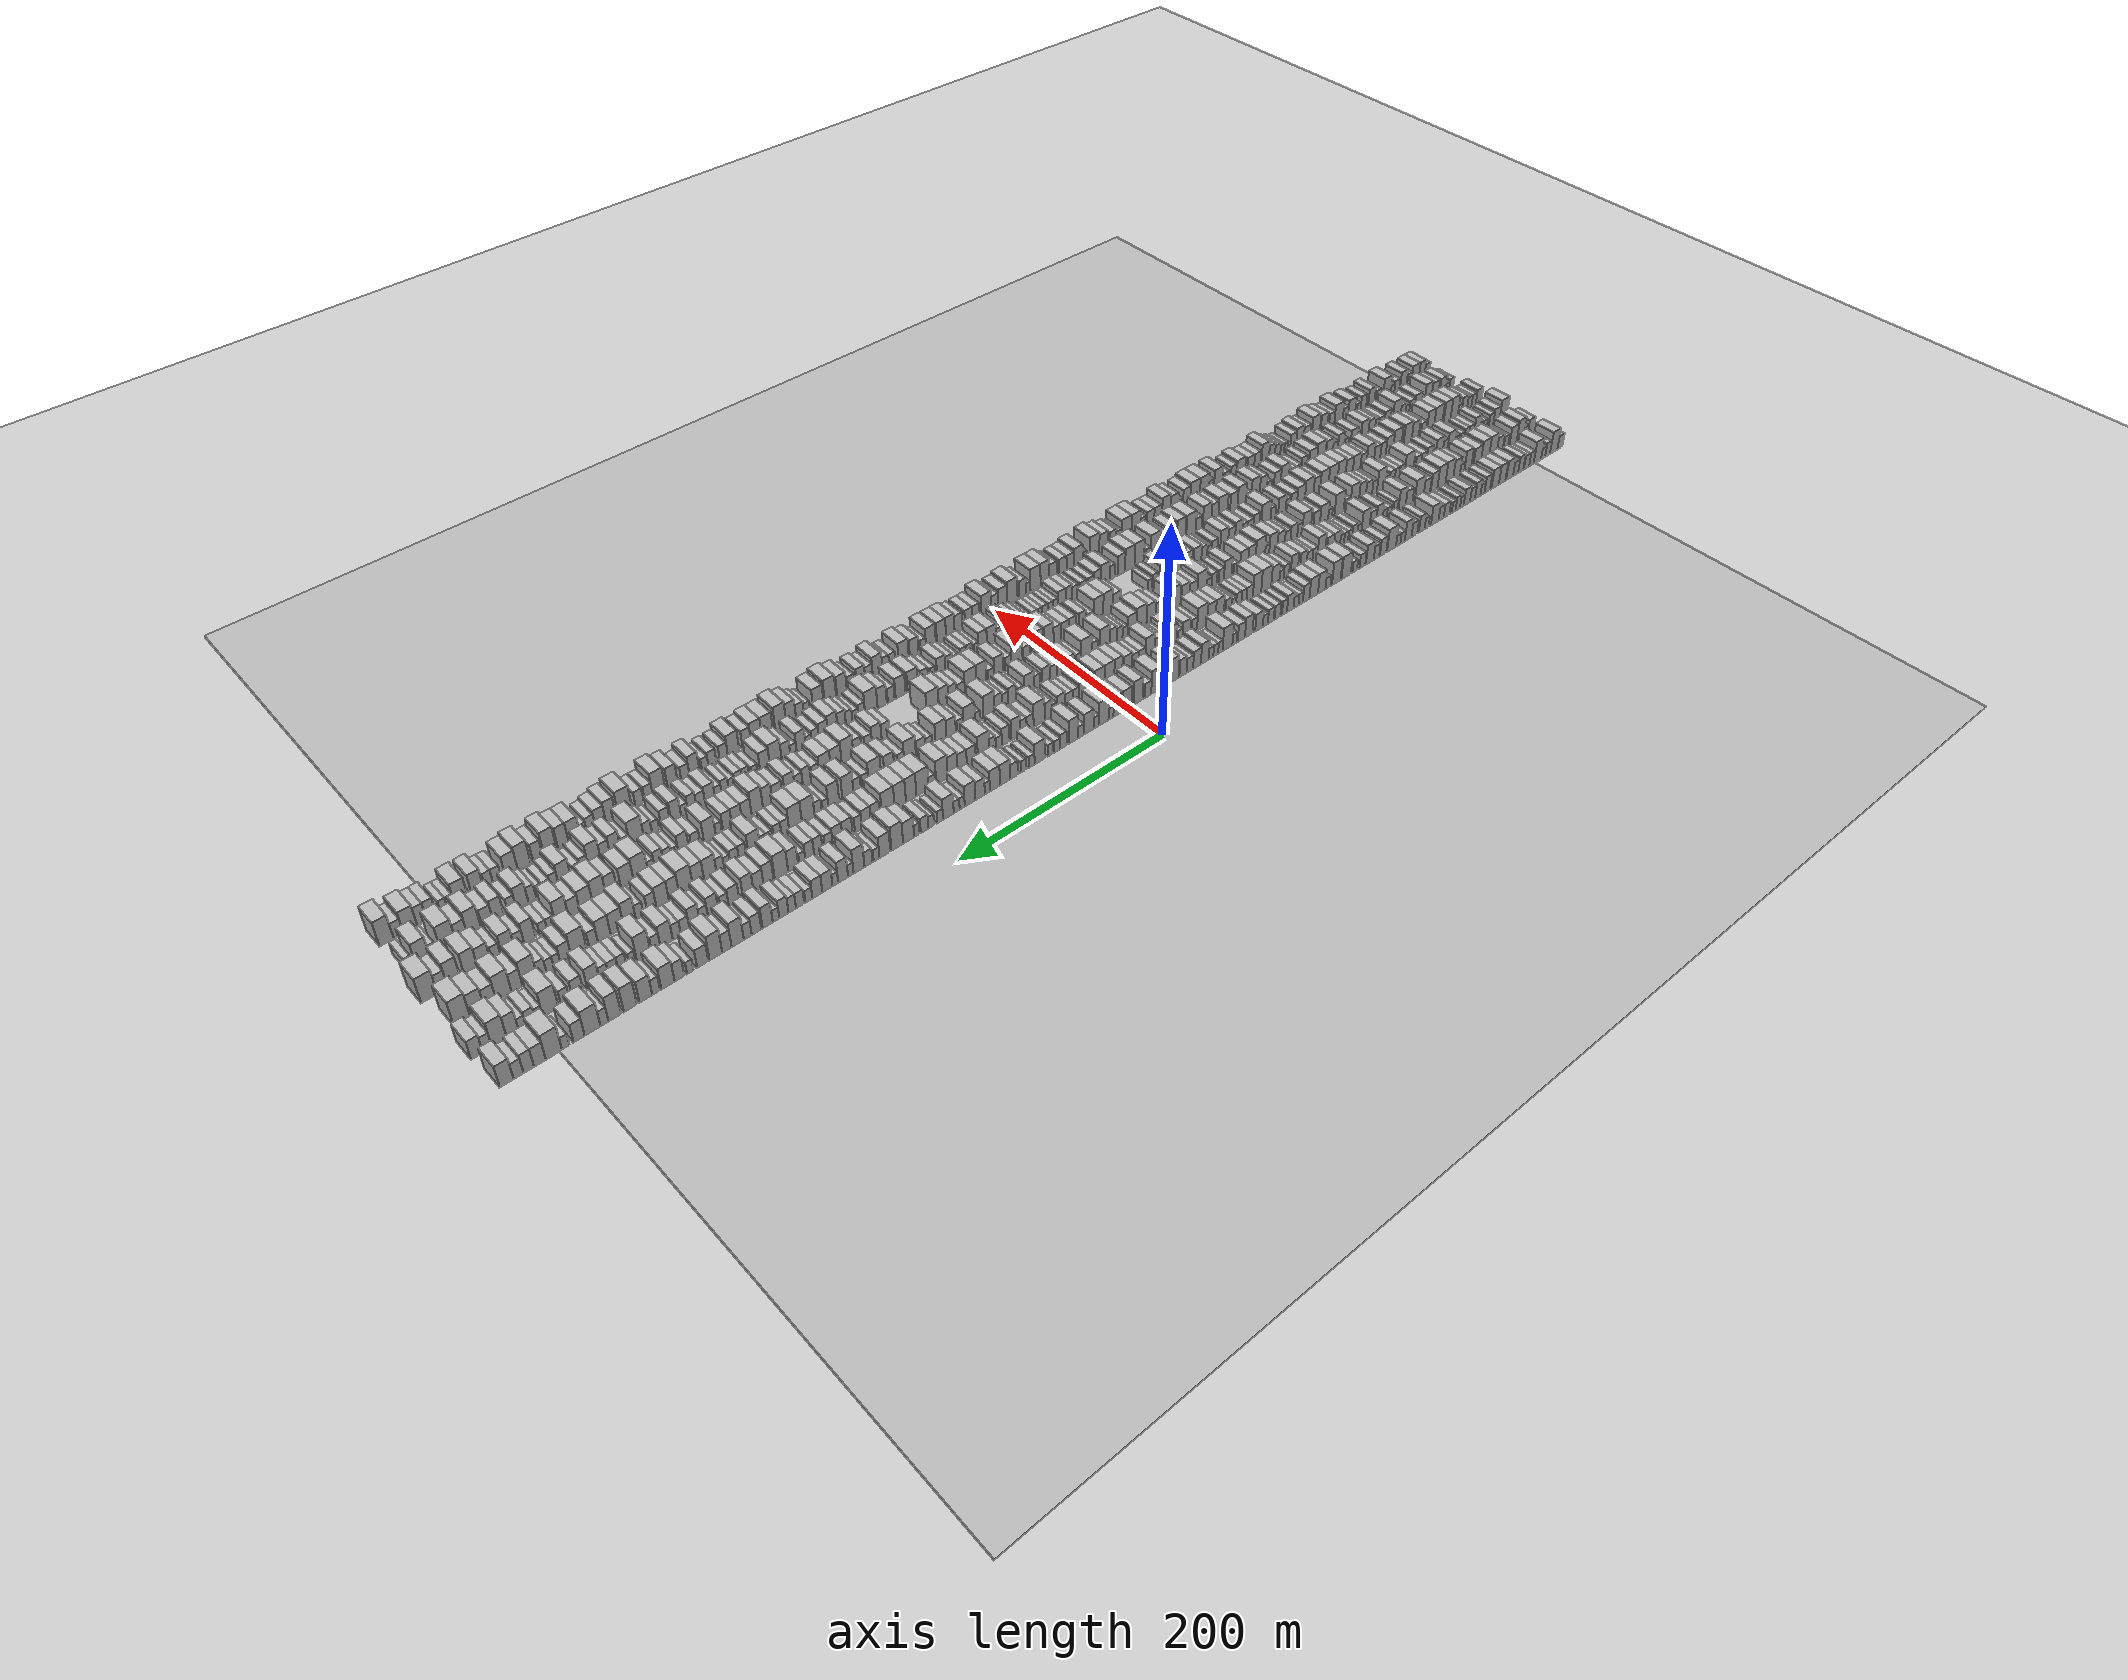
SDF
<?xml version="1.0" encoding="utf-8"?>

<sdf version="1.6">

   <world name="default">

      <gui fullscreen="0">

         <camera name="user_camera">

            <pose>-15 0 4.57585 0 0 0</pose>

            <view_controller>orbit</view_controller>

         </camera>

      </gui>

      <scene>

         <sky>

           <clouds>

             <speed>12</speed>

           </clouds>

         </sky>

         <ambient>0.4 0.4 0.4 1</ambient>

         <background>0.7 0.7 0.7 1</background>

         <shadows>1</shadows>

      </scene>

      <gravity>0 0 -9.8066</gravity>

      <magnetic_field>6e-06 2.3e-05 -4.2e-05</magnetic_field>

      <physics default="0" name="default_physics" type="ode">

         <ode>

            <solver>

               <type>quick</type>

               <iters>10</iters>

               <sor>1.0</sor>

               <use_dynamic_moi_rescaling>0</use_dynamic_moi_rescaling>

            </solver>

            <constraints>

               <cfm>0</cfm>

               <erp>0.2</erp>

               <contact_max_correcting_vel>100</contact_max_correcting_vel>

               <contact_surface_layer>0.001</contact_surface_layer>

            </constraints>

         </ode>

         <max_step_size>0.004</max_step_size>

         <real_time_factor>1</real_time_factor>

         <real_time_update_rate>250</real_time_update_rate>

      </physics>

      <light name="sun" type="directional">

         <cast_shadows>1</cast_shadows>

         <pose>0 0 10 0 0 0</pose>

         <diffuse>0.8 0.8 0.8 1</diffuse>

         <specular>0.2 0.2 0.2 1</specular>

         <attenuation>

            <range>1000</range>

            <constant>0.9</constant>

            <linear>0.01</linear>

            <quadratic>0.001</quadratic>

         </attenuation>

         <direction>-0.5 0.1 -0.9</direction>

      </light>

      <include>

         <name>ground_plane_1</name>

         <uri>model://HANNAS_ground_plane</uri>

         <pose>0 0 0  0 0 0</pose>

      </include>

      <include>

         <name>ground_plane_2</name>

         <uri>model://HANNAS_ground_plane</uri>

         <pose>100 0 0  0 0 0</pose>

      </include>

      <model name="building_1">

         <static>1</static>

         <pose frame="">50.0000 -535.2907 0 0.000000 0.000000 0.000000</pose>

         <link name="link">

            <pose frame="">0 0 7.50 0 0 0</pose>

            <collision name="collision">

               <geometry>

                  <box>

                     <size>20.0000 7.4186 15.0000</size>

                  </box>

               </geometry>

               <max_contacts>10</max_contacts>

               <surface>

                  <contact>

                     <ode/>

                  </contact>

                  <bounce/>

                  <friction>

                     <torsional>

                        <ode/>

                     </torsional>

                     <ode/>

                  </friction>

               </surface>

            </collision>

            <visual name="visual">

               <cast_shadows>0</cast_shadows>

               <geometry>

                  <box>

                     <size>20.0000 7.4186 15.0000</size>

                  </box>

               </geometry>

               <material>

                  <script>

                     <uri>model://HANNAS_wall/materials/scripts</uri>

                     <uri>model://HANNAS_wall/materials/textures</uri>

                     <name>vrc/HANNAS_wall</name>

                  </script>

               </material>

            </visual>

            <self_collide>0</self_collide>

            <enable_wind>0</enable_wind>

            <kinematic>0</kinematic>

         </link>

      </model>

      <model name="building_2">

         <static>1</static>

         <pose frame="">50.0000 -526.2123 0 0.000000 0.000000 0.000000</pose>

         <link name="link">

            <pose frame="">0 0 12.00 0 0 0</pose>

            <collision name="collision">

               <geometry>

                  <box>

                     <size>20.0000 10.7382 24.0000</size>

                  </box>

               </geometry>

               <max_contacts>10</max_contacts>

               <surface>

                  <contact>

                     <ode/>

                  </contact>

                  <bounce/>

                  <friction>

                     <torsional>

                        <ode/>

                     </torsional>

                     <ode/>

                  </friction>

               </surface>

            </collision>

            <visual name="visual">

               <cast_shadows>0</cast_shadows>

               <geometry>

                  <box>

                     <size>20.0000 10.7382 24.0000</size>

                  </box>

               </geometry>

               <material>

                  <script>

                     <uri>model://HANNAS_wall/materials/scripts</uri>

                     <uri>model://HANNAS_wall/materials/textures</uri>

                     <name>vrc/HANNAS_wall</name>

                  </script>

               </material>

            </visual>

            <self_collide>0</self_collide>

            <enable_wind>0</enable_wind>

            <kinematic>0</kinematic>

         </link>

      </model>

      <model name="building_3">

         <static>1</static>

         <pose frame="">50.0000 -517.3542 0 0.000000 0.000000 0.000000</pose>

         <link name="link">

            <pose frame="">0 0 7.50 0 0 0</pose>

            <collision name="collision">

               <geometry>

                  <box>

                     <size>20.0000 6.9780 15.0000</size>

                  </box>

               </geometry>

               <max_contacts>10</max_contacts>

               <surface>

                  <contact>

                     <ode/>

                  </contact>

                  <bounce/>

                  <friction>

                     <torsional>

                        <ode/>

                     </torsional>

                     <ode/>

                  </friction>

               </surface>

            </collision>

            <visual name="visual">

               <cast_shadows>0</cast_shadows>

               <geometry>

                  <box>

                     <size>20.0000 6.9780 15.0000</size>

                  </box>

               </geometry>

               <material>

                  <script>

                     <uri>model://HANNAS_wall/materials/scripts</uri>

                     <uri>model://HANNAS_wall/materials/textures</uri>

                     <name>vrc/HANNAS_wall</name>

                  </script>

               </material>

            </visual>

            <self_collide>0</self_collide>

            <enable_wind>0</enable_wind>

            <kinematic>0</kinematic>

         </link>

      </model>

      <model name="building_4">

         <static>1</static>

         <pose frame="">50.0000 -510.8868 0 0.000000 0.000000 0.000000</pose>

         <link name="link">

            <pose frame="">0 0 6.00 0 0 0</pose>

            <collision name="collision">

               <geometry>

                  <box>

                     <size>20.0000 5.9567 12.0000</size>

                  </box>

               </geometry>

               <max_contacts>10</max_contacts>

               <surface>

                  <contact>

                     <ode/>

                  </contact>

                  <bounce/>

                  <friction>

                     <torsional>

                        <ode/>

                     </torsional>

                     <ode/>

                  </friction>

               </surface>

            </collision>

            <visual name="visual">

               <cast_shadows>0</cast_shadows>

               <geometry>

                  <box>

                     <size>20.0000 5.9567 12.0000</size>

                  </box>

               </geometry>

               <material>

                  <script>

                     <uri>model://HANNAS_wall/materials/scripts</uri>

                     <uri>model://HANNAS_wall/materials/textures</uri>

                     <name>vrc/HANNAS_wall</name>

                  </script>

               </material>

            </visual>

            <self_collide>0</self_collide>

            <enable_wind>0</enable_wind>

            <kinematic>0</kinematic>

         </link>

      </model>

      <model name="building_5">

         <static>1</static>

         <pose frame="">50.0000 -502.5958 0 0.000000 0.000000 0.000000</pose>

         <link name="link">

            <pose frame="">0 0 12.00 0 0 0</pose>

            <collision name="collision">

               <geometry>

                  <box>

                     <size>20.0000 10.6253 24.0000</size>

                  </box>

               </geometry>

               <max_contacts>10</max_contacts>

               <surface>

                  <contact>

                     <ode/>

                  </contact>

                  <bounce/>

                  <friction>

                     <torsional>

                        <ode/>

                     </torsional>

                     <ode/>

                  </friction>

               </surface>

            </collision>

            <visual name="visual">

               <cast_shadows>0</cast_shadows>

               <geometry>

                  <box>

                     <size>20.0000 10.6253 24.0000</size>

                  </box>

               </geometry>

               <material>

                  <script>

                     <uri>model://HANNAS_wall/materials/scripts</uri>

                     <uri>model://HANNAS_wall/materials/textures</uri>

                     <name>vrc/HANNAS_wall</name>

                  </script>

               </material>

            </visual>

            <self_collide>0</self_collide>

            <enable_wind>0</enable_wind>

            <kinematic>0</kinematic>

         </link>

      </model>

      <model name="building_6">

         <static>1</static>

         <pose frame="">50.0000 -494.0893 0 0.000000 0.000000 0.000000</pose>

         <link name="link">

            <pose frame="">0 0 7.50 0 0 0</pose>

            <collision name="collision">

               <geometry>

                  <box>

                     <size>20.0000 6.3879 15.0000</size>

                  </box>

               </geometry>

               <max_contacts>10</max_contacts>

               <surface>

                  <contact>

                     <ode/>

                  </contact>

                  <bounce/>

                  <friction>

                     <torsional>

                        <ode/>

                     </torsional>

                     <ode/>

                  </friction>

               </surface>

            </collision>

            <visual name="visual">

               <cast_shadows>0</cast_shadows>

               <geometry>

                  <box>

                     <size>20.0000 6.3879 15.0000</size>

                  </box>

               </geometry>

               <material>

                  <script>

                     <uri>model://HANNAS_wall/materials/scripts</uri>

                     <uri>model://HANNAS_wall/materials/textures</uri>

                     <name>vrc/HANNAS_wall</name>

                  </script>

               </material>

            </visual>

            <self_collide>0</self_collide>

            <enable_wind>0</enable_wind>

            <kinematic>0</kinematic>

         </link>

      </model>

      <model name="building_7">

         <static>1</static>

         <pose frame="">50.0000 -487.1926 0 0.000000 0.000000 0.000000</pose>

         <link name="link">

            <pose frame="">0 0 7.50 0 0 0</pose>

            <collision name="collision">

               <geometry>

                  <box>

                     <size>20.0000 7.4053 15.0000</size>

                  </box>

               </geometry>

               <max_contacts>10</max_contacts>

               <surface>

                  <contact>

                     <ode/>

                  </contact>

                  <bounce/>

                  <friction>

                     <torsional>

                        <ode/>

                     </torsional>

                     <ode/>

                  </friction>

               </surface>

            </collision>

            <visual name="visual">

               <cast_shadows>0</cast_shadows>

               <geometry>

                  <box>

                     <size>20.0000 7.4053 15.0000</size>

                  </box>

               </geometry>

               <material>

                  <script>

                     <uri>model://HANNAS_wall/materials/scripts</uri>

                     <uri>model://HANNAS_wall/materials/textures</uri>

                     <name>vrc/HANNAS_wall</name>

                  </script>

               </material>

            </visual>

            <self_collide>0</self_collide>

            <enable_wind>0</enable_wind>

            <kinematic>0</kinematic>

         </link>

      </model>

      <model name="building_8">

         <static>1</static>

         <pose frame="">50.0000 -478.8828 0 0.000000 0.000000 0.000000</pose>

         <link name="link">

            <pose frame="">0 0 9.00 0 0 0</pose>

            <collision name="collision">

               <geometry>

                  <box>

                     <size>20.0000 7.2143 18.0000</size>

                  </box>

               </geometry>

               <max_contacts>10</max_contacts>

               <surface>

                  <contact>

                     <ode/>

                  </contact>

                  <bounce/>

                  <friction>

                     <torsional>

                        <ode/>

                     </torsional>

                     <ode/>

                  </friction>

               </surface>

            </collision>

            <visual name="visual">

               <cast_shadows>0</cast_shadows>

               <geometry>

                  <box>

                     <size>20.0000 7.2143 18.0000</size>

                  </box>

               </geometry>

               <material>

                  <script>

                     <uri>model://HANNAS_wall/materials/scripts</uri>

                     <uri>model://HANNAS_wall/materials/textures</uri>

                     <name>vrc/HANNAS_wall</name>

                  </script>

               </material>

            </visual>

            <self_collide>0</self_collide>

            <enable_wind>0</enable_wind>

            <kinematic>0</kinematic>

         </link>

      </model>

      <model name="building_9">

         <static>1</static>

         <pose frame="">50.0000 -471.7403 0 0.000000 0.000000 0.000000</pose>

         <link name="link">

            <pose frame="">0 0 7.50 0 0 0</pose>

            <collision name="collision">

               <geometry>

                  <box>

                     <size>20.0000 7.0706 15.0000</size>

                  </box>

               </geometry>

               <max_contacts>10</max_contacts>

               <surface>

                  <contact>

                     <ode/>

                  </contact>

                  <bounce/>

                  <friction>

                     <torsional>

                        <ode/>

                     </torsional>

                     <ode/>

                  </friction>

               </surface>

            </collision>

            <visual name="visual">

               <cast_shadows>0</cast_shadows>

               <geometry>

                  <box>

                     <size>20.0000 7.0706 15.0000</size>

                  </box>

               </geometry>

               <material>

                  <script>

                     <uri>model://HANNAS_wall/materials/scripts</uri>

                     <uri>model://HANNAS_wall/materials/textures</uri>

                     <name>vrc/HANNAS_wall</name>

                  </script>

               </material>

            </visual>

            <self_collide>0</self_collide>

            <enable_wind>0</enable_wind>

            <kinematic>0</kinematic>

         </link>

      </model>

      <model name="building_10">

         <static>1</static>

         <pose frame="">50.0000 -463.2833 0 0.000000 0.000000 0.000000</pose>

         <link name="link">

            <pose frame="">0 0 10.50 0 0 0</pose>

            <collision name="collision">

               <geometry>

                  <box>

                     <size>20.0000 9.8434 21.0000</size>

                  </box>

               </geometry>

               <max_contacts>10</max_contacts>

               <surface>

                  <contact>

                     <ode/>

                  </contact>

                  <bounce/>

                  <friction>

                     <torsional>

                        <ode/>

                     </torsional>

                     <ode/>

                  </friction>

               </surface>

            </collision>

            <visual name="visual">

               <cast_shadows>0</cast_shadows>

               <geometry>

                  <box>

                     <size>20.0000 9.8434 21.0000</size>

                  </box>

               </geometry>

               <material>

                  <script>

                     <uri>model://HANNAS_wall/materials/scripts</uri>

                     <uri>model://HANNAS_wall/materials/textures</uri>

                     <name>vrc/HANNAS_wall</name>

                  </script>

               </material>

            </visual>

            <self_collide>0</self_collide>

            <enable_wind>0</enable_wind>

            <kinematic>0</kinematic>

         </link>

      </model>

      <model name="building_11">

         <static>1</static>

         <pose frame="">50.0000 -452.8289 0 0.000000 0.000000 0.000000</pose>

         <link name="link">

            <pose frame="">0 0 10.50 0 0 0</pose>

            <collision name="collision">

               <geometry>

                  <box>

                     <size>20.0000 9.0655 21.0000</size>

                  </box>

               </geometry>

               <max_contacts>10</max_contacts>

               <surface>

                  <contact>

                     <ode/>

                  </contact>

                  <bounce/>

                  <friction>

                     <torsional>

                        <ode/>

                     </torsional>

                     <ode/>

                  </friction>

               </surface>

            </collision>

            <visual name="visual">

               <cast_shadows>0</cast_shadows>

               <geometry>

                  <box>

                     <size>20.0000 9.0655 21.0000</size>

                  </box>

               </geometry>

               <material>

                  <script>

                     <uri>model://HANNAS_wall/materials/scripts</uri>

                     <uri>model://HANNAS_wall/materials/textures</uri>

                     <name>vrc/HANNAS_wall</name>

                  </script>

               </material>

            </visual>

            <self_collide>0</self_collide>

            <enable_wind>0</enable_wind>

            <kinematic>0</kinematic>

         </link>

      </model>

      <model name="building_12">

         <static>1</static>

         <pose frame="">50.0000 -443.1844 0 0.000000 0.000000 0.000000</pose>

         <link name="link">

            <pose frame="">0 0 10.50 0 0 0</pose>

            <collision name="collision">

               <geometry>

                  <box>

                     <size>20.0000 10.2234 21.0000</size>

                  </box>

               </geometry>

               <max_contacts>10</max_contacts>

               <surface>

                  <contact>

                     <ode/>

                  </contact>

                  <bounce/>

                  <friction>

                     <torsional>

                        <ode/>

                     </torsional>

                     <ode/>

                  </friction>

               </surface>

            </collision>

            <visual name="visual">

               <cast_shadows>0</cast_shadows>

               <geometry>

                  <box>

                     <size>20.0000 10.2234 21.0000</size>

                  </box>

               </geometry>

               <material>

                  <script>

                     <uri>model://HANNAS_wall/materials/scripts</uri>

                     <uri>model://HANNAS_wall/materials/textures</uri>

                     <name>vrc/HANNAS_wall</name>

                  </script>

               </material>

            </visual>

            <self_collide>0</self_collide>

            <enable_wind>0</enable_wind>

            <kinematic>0</kinematic>

         </link>

      </model>

      <model name="building_13">

         <static>1</static>

         <pose frame="">50.0000 -432.1730 0 0.000000 0.000000 0.000000</pose>

         <link name="link">

            <pose frame="">0 0 9.00 0 0 0</pose>

            <collision name="collision">

               <geometry>

                  <box>

                     <size>20.0000 7.7994 18.0000</size>

                  </box>

               </geometry>

               <max_contacts>10</max_contacts>

               <surface>

                  <contact>

                     <ode/>

                  </contact>

                  <bounce/>

                  <friction>

                     <torsional>

                        <ode/>

                     </torsional>

                     <ode/>

                  </friction>

               </surface>

            </collision>

            <visual name="visual">

               <cast_shadows>0</cast_shadows>

               <geometry>

                  <box>

                     <size>20.0000 7.7994 18.0000</size>

                  </box>

               </geometry>

               <material>

                  <script>

                     <uri>model://HANNAS_wall/materials/scripts</uri>

                     <uri>model://HANNAS_wall/materials/textures</uri>

                     <name>vrc/HANNAS_wall</name>

                  </script>

               </material>

            </visual>

            <self_collide>0</self_collide>

            <enable_wind>0</enable_wind>

            <kinematic>0</kinematic>

         </link>

      </model>

      <model name="building_14">

         <static>1</static>

         <pose frame="">50.0000 -425.5809 0 0.000000 0.000000 0.000000</pose>

         <link name="link">

            <pose frame="">0 0 6.00 0 0 0</pose>

            <collision name="collision">

               <geometry>

                  <box>

                     <size>20.0000 5.3847 12.0000</size>

                  </box>

               </geometry>

               <max_contacts>10</max_contacts>

               <surface>

                  <contact>

                     <ode/>

                  </contact>

                  <bounce/>

                  <friction>

                     <torsional>

                        <ode/>

                     </torsional>

                     <ode/>

                  </friction>

               </surface>

            </collision>

            <visual name="visual">

               <cast_shadows>0</cast_shadows>

               <geometry>

                  <box>

                     <size>20.0000 5.3847 12.0000</size>

                  </box>

               </geometry>

               <material>

                  <script>

                     <uri>model://HANNAS_wall/materials/scripts</uri>

                     <uri>model://HANNAS_wall/materials/textures</uri>

                     <name>vrc/HANNAS_wall</name>

                  </script>

               </material>

            </visual>

            <self_collide>0</self_collide>

            <enable_wind>0</enable_wind>

            <kinematic>0</kinematic>

         </link>

      </model>

      <model name="building_15">

         <static>1</static>

         <pose frame="">50.0000 -419.1821 0 0.000000 0.000000 0.000000</pose>

         <link name="link">

            <pose frame="">0 0 9.00 0 0 0</pose>

            <collision name="collision">

               <geometry>

                  <box>

                     <size>20.0000 7.4129 18.0000</size>

                  </box>

               </geometry>

               <max_contacts>10</max_contacts>

               <surface>

                  <contact>

                     <ode/>

                  </contact>

                  <bounce/>

                  <friction>

                     <torsional>

                        <ode/>

                     </torsional>

                     <ode/>

                  </friction>

               </surface>

            </collision>

            <visual name="visual">

               <cast_shadows>0</cast_shadows>

               <geometry>

                  <box>

                     <size>20.0000 7.4129 18.0000</size>

                  </box>

               </geometry>

               <material>

                  <script>

                     <uri>model://HANNAS_wall/materials/scripts</uri>

                     <uri>model://HANNAS_wall/materials/textures</uri>

                     <name>vrc/HANNAS_wall</name>

                  </script>

               </material>

            </visual>

            <self_collide>0</self_collide>

            <enable_wind>0</enable_wind>

            <kinematic>0</kinematic>

         </link>

      </model>

      <model name="building_16">

         <static>1</static>

         <pose frame="">50.0000 -412.0602 0 0.000000 0.000000 0.000000</pose>

         <link name="link">

            <pose frame="">0 0 7.50 0 0 0</pose>

            <collision name="collision">

               <geometry>

                  <box>

                     <size>20.0000 6.8310 15.0000</size>

                  </box>

               </geometry>

               <max_contacts>10</max_contacts>

               <surface>

                  <contact>

                     <ode/>

                  </contact>

                  <bounce/>

                  <friction>

                     <torsional>

                        <ode/>

                     </torsional>

                     <ode/>

                  </friction>

               </surface>

            </collision>

            <visual name="visual">

               <cast_shadows>0</cast_shadows>

               <geometry>

                  <box>

                     <size>20.0000 6.8310 15.0000</size>

                  </box>

               </geometry>

               <material>

                  <script>

                     <uri>model://HANNAS_wall/materials/scripts</uri>

                     <uri>model://HANNAS_wall/materials/textures</uri>

                     <name>vrc/HANNAS_wall</name>

                  </script>

               </material>

            </visual>

            <self_collide>0</self_collide>

            <enable_wind>0</enable_wind>

            <kinematic>0</kinematic>

         </link>

      </model>

      <model name="building_17">

         <static>1</static>

         <pose frame="">50.0000 -404.4424 0 0.000000 0.000000 0.000000</pose>

         <link name="link">

            <pose frame="">0 0 9.00 0 0 0</pose>

            <collision name="collision">

               <geometry>

                  <box>

                     <size>20.0000 8.4046 18.0000</size>

                  </box>

               </geometry>

               <max_contacts>10</max_contacts>

               <surface>

                  <contact>

                     <ode/>

                  </contact>

                  <bounce/>

                  <friction>

                     <torsional>

                        <ode/>

                     </torsional>

                     <ode/>

                  </friction>

               </surface>

            </collision>

            <visual name="visual">

               <cast_shadows>0</cast_shadows>

               <geometry>

                  <box>

                     <size>20.0000 8.4046 18.0000</size>

                  </box>

               </geometry>

               <material>

                  <script>

                     <uri>model://HANNAS_wall/materials/scripts</uri>

                     <uri>model://HANNAS_wall/materials/textures</uri>

                     <name>vrc/HANNAS_wall</name>

                  </script>

               </material>

            </visual>

            <self_collide>0</self_collide>

            <enable_wind>0</enable_wind>

            <kinematic>0</kinematic>

         </link>

      </model>

      <model name="building_18">

         <static>1</static>

         <pose frame="">50.0000 -397.7037 0 0.000000 0.000000 0.000000</pose>

         <link name="link">

            <pose frame="">0 0 6.00 0 0 0</pose>

            <collision name="collision">

               <geometry>

                  <box>

                     <size>20.0000 5.0729 12.0000</size>

                  </box>

               </geometry>

               <max_contacts>10</max_contacts>

               <surface>

                  <contact>

                     <ode/>

                  </contact>

                  <bounce/>

                  <friction>

                     <torsional>

                        <ode/>

                     </torsional>

                     <ode/>

                  </friction>

               </surface>

            </collision>

            <visual name="visual">

               <cast_shadows>0</cast_shadows>

               <geometry>

                  <box>

                     <size>20.0000 5.0729 12.0000</size>

                  </box>

               </geometry>

               <material>

                  <script>

                     <uri>model://HANNAS_wall/materials/scripts</uri>

                     <uri>model://HANNAS_wall/materials/textures</uri>

                     <name>vrc/HANNAS_wall</name>

                  </script>

               </material>

            </visual>

            <self_collide>0</self_collide>

            <enable_wind>0</enable_wind>

            <kinematic>0</kinematic>

         </link>

      </model>

      <model name="building_19">

         <static>1</static>

         <pose frame="">50.0000 -392.1365 0 0.000000 0.000000 0.000000</pose>

         <link name="link">

            <pose frame="">0 0 7.50 0 0 0</pose>

            <collision name="collision">

               <geometry>

                  <box>

                     <size>20.0000 6.0615 15.0000</size>

                  </box>

               </geometry>

               <max_contacts>10</max_contacts>

               <surface>

                  <contact>

                     <ode/>

                  </contact>

                  <bounce/>

                  <friction>

                     <torsional>

                        <ode/>

                     </torsional>

                     <ode/>

                  </friction>

               </surface>

            </collision>

            <visual name="visual">

               <cast_shadows>0</cast_shadows>

               <geometry>

                  <box>

                     <size>20.0000 6.0615 15.0000</size>

                  </box>

               </geometry>

               <material>

                  <script>

                     <uri>model://HANNAS_wall/materials/scripts</uri>

                     <uri>model://HANNAS_wall/materials/textures</uri>

                     <name>vrc/HANNAS_wall</name>

                  </script>

               </material>

            </visual>

            <self_collide>0</self_collide>

            <enable_wind>0</enable_wind>

            <kinematic>0</kinematic>

         </link>

      </model>

      <model name="building_20">

         <static>1</static>

         <pose frame="">50.0000 -386.4969 0 0.000000 0.000000 0.000000</pose>

         <link name="link">

            <pose frame="">0 0 6.00 0 0 0</pose>

            <collision name="collision">

               <geometry>

                  <box>

                     <size>20.0000 5.2177 12.0000</size>

                  </box>

               </geometry>

               <max_contacts>10</max_contacts>

               <surface>

                  <contact>

                     <ode/>

                  </contact>

                  <bounce/>

                  <friction>

                     <torsional>

                        <ode/>

                     </torsional>

                     <ode/>

                  </friction>

               </surface>

            </collision>

            <visual name="visual">

               <cast_shadows>0</cast_shadows>

               <geometry>

                  <box>

                     <size>20.0000 5.2177 12.0000</size>

                  </box>

               </geometry>

               <material>

                  <script>

                     <uri>model://HANNAS_wall/materials/scripts</uri>

                     <uri>model://HANNAS_wall/materials/textures</uri>

                     <name>vrc/HANNAS_wall</name>

                  </script>

               </material>

            </visual>

            <self_collide>0</self_collide>

            <enable_wind>0</enable_wind>

            <kinematic>0</kinematic>

         </link>

      </model>

      <model name="building_21">

         <static>1</static>

         <pose frame="">50.0000 -377.1596 0 0.000000 0.000000 0.000000</pose>

         <link name="link">

            <pose frame="">0 0 7.50 0 0 0</pose>

            <collision name="collision">

               <geometry>

                  <box>

                     <size>20.0000 7.4570 15.0000</size>

                  </box>

               </geometry>

               <max_contacts>10</max_contacts>

               <surface>

                  <contact>

                     <ode/>

                  </contact>

                  <bounce/>

                  <friction>

                     <torsional>

                        <ode/>

                     </torsional>

                     <ode/>

                  </friction>

               </surface>

            </collision>

            <visual name="visual">

               <cast_shadows>0</cast_shadows>

               <geometry>

                  <box>

                     <size>20.0000 7.4570 15.0000</size>

                  </box>

               </geometry>

               <material>

                  <script>

                     <uri>model://HANNAS_wall/materials/scripts</uri>

                     <uri>model://HANNAS_wall/materials/textures</uri>

                     <name>vrc/HANNAS_wall</name>

                  </script>

               </material>

            </visual>

            <self_collide>0</self_collide>

            <enable_wind>0</enable_wind>

            <kinematic>0</kinematic>

         </link>

      </model>

      <model name="building_22">

         <static>1</static>

         <pose frame="">50.0000 -370.0108 0 0.000000 0.000000 0.000000</pose>

         <link name="link">

            <pose frame="">0 0 7.50 0 0 0</pose>

            <collision name="collision">

               <geometry>

                  <box>

                     <size>20.0000 6.8404 15.0000</size>

                  </box>

               </geometry>

               <max_contacts>10</max_contacts>

               <surface>

                  <contact>

                     <ode/>

                  </contact>

                  <bounce/>

                  <friction>

                     <torsional>

                        <ode/>

                     </torsional>

                     <ode/>

                  </friction>

               </surface>

            </collision>

            <visual name="visual">

               <cast_shadows>0</cast_shadows>

               <geometry>

                  <box>

                     <size>20.0000 6.8404 15.0000</size>

                  </box>

               </geometry>

               <material>

                  <script>

                     <uri>model://HANNAS_wall/materials/scripts</uri>

                     <uri>model://HANNAS_wall/materials/textures</uri>

                     <name>vrc/HANNAS_wall</name>

                  </script>

               </material>

            </visual>

            <self_collide>0</self_collide>

            <enable_wind>0</enable_wind>

            <kinematic>0</kinematic>

         </link>

      </model>

      <model name="building_23">

         <static>1</static>

         <pose frame="">50.0000 -361.4864 0 0.000000 0.000000 0.000000</pose>

         <link name="link">

            <pose frame="">0 0 10.50 0 0 0</pose>

            <collision name="collision">

               <geometry>

                  <box>

                     <size>20.0000 10.2085 21.0000</size>

                  </box>

               </geometry>

               <max_contacts>10</max_contacts>

               <surface>

                  <contact>

                     <ode/>

                  </contact>

                  <bounce/>

                  <friction>

                     <torsional>

                        <ode/>

                     </torsional>

                     <ode/>

                  </friction>

               </surface>

            </collision>

            <visual name="visual">

               <cast_shadows>0</cast_shadows>

               <geometry>

                  <box>

                     <size>20.0000 10.2085 21.0000</size>

                  </box>

               </geometry>

               <material>

                  <script>

                     <uri>model://HANNAS_wall/materials/scripts</uri>

                     <uri>model://HANNAS_wall/materials/textures</uri>

                     <name>vrc/HANNAS_wall</name>

                  </script>

               </material>

            </visual>

            <self_collide>0</self_collide>

            <enable_wind>0</enable_wind>

            <kinematic>0</kinematic>

         </link>

      </model>

      <model name="building_24">

         <static>1</static>

         <pose frame="">50.0000 -350.6740 0 0.000000 0.000000 0.000000</pose>

         <link name="link">

            <pose frame="">0 0 6.00 0 0 0</pose>

            <collision name="collision">

               <geometry>

                  <box>

                     <size>20.0000 5.4163 12.0000</size>

                  </box>

               </geometry>

               <max_contacts>10</max_contacts>

               <surface>

                  <contact>

                     <ode/>

                  </contact>

                  <bounce/>

                  <friction>

                     <torsional>

                        <ode/>

                     </torsional>

                     <ode/>

                  </friction>

               </surface>

            </collision>

            <visual name="visual">

               <cast_shadows>0</cast_shadows>

               <geometry>

                  <box>

                     <size>20.0000 5.4163 12.0000</size>

                  </box>

               </geometry>

               <material>

                  <script>

                     <uri>model://HANNAS_wall/materials/scripts</uri>

                     <uri>model://HANNAS_wall/materials/textures</uri>

                     <name>vrc/HANNAS_wall</name>

                  </script>

               </material>

            </visual>

            <self_collide>0</self_collide>

            <enable_wind>0</enable_wind>

            <kinematic>0</kinematic>

         </link>

      </model>

      <model name="building_25">

         <static>1</static>

         <pose frame="">50.0000 -344.2014 0 0.000000 0.000000 0.000000</pose>

         <link name="link">

            <pose frame="">0 0 9.00 0 0 0</pose>

            <collision name="collision">

               <geometry>

                  <box>

                     <size>20.0000 7.5288 18.0000</size>

                  </box>

               </geometry>

               <max_contacts>10</max_contacts>

               <surface>

                  <contact>

                     <ode/>

                  </contact>

                  <bounce/>

                  <friction>

                     <torsional>

                        <ode/>

                     </torsional>

                     <ode/>

                  </friction>

               </surface>

            </collision>

            <visual name="visual">

               <cast_shadows>0</cast_shadows>

               <geometry>

                  <box>

                     <size>20.0000 7.5288 18.0000</size>

                  </box>

               </geometry>

               <material>

                  <script>

                     <uri>model://HANNAS_wall/materials/scripts</uri>

                     <uri>model://HANNAS_wall/materials/textures</uri>

                     <name>vrc/HANNAS_wall</name>

                  </script>

               </material>

            </visual>

            <self_collide>0</self_collide>

            <enable_wind>0</enable_wind>

            <kinematic>0</kinematic>

         </link>

      </model>

      <model name="building_26">

         <static>1</static>

         <pose frame="">50.0000 -334.7471 0 0.000000 0.000000 0.000000</pose>

         <link name="link">

            <pose frame="">0 0 7.50 0 0 0</pose>

            <collision name="collision">

               <geometry>

                  <box>

                     <size>20.0000 7.3799 15.0000</size>

                  </box>

               </geometry>

               <max_contacts>10</max_contacts>

               <surface>

                  <contact>

                     <ode/>

                  </contact>

                  <bounce/>

                  <friction>

                     <torsional>

                        <ode/>

                     </torsional>

                     <ode/>

                  </friction>

               </surface>

            </collision>

            <visual name="visual">

               <cast_shadows>0</cast_shadows>

               <geometry>

                  <box>

                     <size>20.0000 7.3799 15.0000</size>

                  </box>

               </geometry>

               <material>

                  <script>

                     <uri>model://HANNAS_wall/materials/scripts</uri>

                     <uri>model://HANNAS_wall/materials/textures</uri>

                     <name>vrc/HANNAS_wall</name>

                  </script>

               </material>

            </visual>

            <self_collide>0</self_collide>

            <enable_wind>0</enable_wind>

            <kinematic>0</kinematic>

         </link>

      </model>

      <model name="building_27">

         <static>1</static>

         <pose frame="">50.0000 -326.7229 0 0.000000 0.000000 0.000000</pose>

         <link name="link">

            <pose frame="">0 0 10.50 0 0 0</pose>

            <collision name="collision">

               <geometry>

                  <box>

                     <size>20.0000 8.6684 21.0000</size>

                  </box>

               </geometry>

               <max_contacts>10</max_contacts>

               <surface>

                  <contact>

                     <ode/>

                  </contact>

                  <bounce/>

                  <friction>

                     <torsional>

                        <ode/>

                     </torsional>

                     <ode/>

                  </friction>

               </surface>

            </collision>

            <visual name="visual">

               <cast_shadows>0</cast_shadows>

               <geometry>

                  <box>

                     <size>20.0000 8.6684 21.0000</size>

                  </box>

               </geometry>

               <material>

                  <script>

                     <uri>model://HANNAS_wall/materials/scripts</uri>

                     <uri>model://HANNAS_wall/materials/textures</uri>

                     <name>vrc/HANNAS_wall</name>

                  </script>

               </material>

            </visual>

            <self_collide>0</self_collide>

            <enable_wind>0</enable_wind>

            <kinematic>0</kinematic>

         </link>

      </model>

      <model name="building_28">

         <static>1</static>

         <pose frame="">50.0000 -319.5645 0 0.000000 0.000000 0.000000</pose>

         <link name="link">

            <pose frame="">0 0 6.00 0 0 0</pose>

            <collision name="collision">

               <geometry>

                  <box>

                     <size>20.0000 5.6486 12.0000</size>

                  </box>

               </geometry>

               <max_contacts>10</max_contacts>

               <surface>

                  <contact>

                     <ode/>

                  </contact>

                  <bounce/>

                  <friction>

                     <torsional>

                        <ode/>

                     </torsional>

                     <ode/>

                  </friction>

               </surface>

            </collision>

            <visual name="visual">

               <cast_shadows>0</cast_shadows>

               <geometry>

                  <box>

                     <size>20.0000 5.6486 12.0000</size>

                  </box>

               </geometry>

               <material>

                  <script>

                     <uri>model://HANNAS_wall/materials/scripts</uri>

                     <uri>model://HANNAS_wall/materials/textures</uri>

                     <name>vrc/HANNAS_wall</name>

                  </script>

               </material>

            </visual>

            <self_collide>0</self_collide>

            <enable_wind>0</enable_wind>

            <kinematic>0</kinematic>

         </link>

      </model>

      <model name="building_29">

         <static>1</static>

         <pose frame="">50.0000 -313.9087 0 0.000000 0.000000 0.000000</pose>

         <link name="link">

            <pose frame="">0 0 6.00 0 0 0</pose>

            <collision name="collision">

               <geometry>

                  <box>

                     <size>20.0000 5.6630 12.0000</size>

                  </box>

               </geometry>

               <max_contacts>10</max_contacts>

               <surface>

                  <contact>

                     <ode/>

                  </contact>

                  <bounce/>

                  <friction>

                     <torsional>

                        <ode/>

                     </torsional>

                     <ode/>

                  </friction>

               </surface>

            </collision>

            <visual name="visual">

               <cast_shadows>0</cast_shadows>

               <geometry>

                  <box>

                     <size>20.0000 5.6630 12.0000</size>

                  </box>

               </geometry>

               <material>

                  <script>

                     <uri>model://HANNAS_wall/materials/scripts</uri>

                     <uri>model://HANNAS_wall/materials/textures</uri>

                     <name>vrc/HANNAS_wall</name>

                  </script>

               </material>

            </visual>

            <self_collide>0</self_collide>

            <enable_wind>0</enable_wind>

            <kinematic>0</kinematic>

         </link>

      </model>

      <model name="building_30">

         <static>1</static>

         <pose frame="">50.0000 -305.3632 0 0.000000 0.000000 0.000000</pose>

         <link name="link">

            <pose frame="">0 0 12.00 0 0 0</pose>

            <collision name="collision">

               <geometry>

                  <box>

                     <size>20.0000 11.4279 24.0000</size>

                  </box>

               </geometry>

               <max_contacts>10</max_contacts>

               <surface>

                  <contact>

                     <ode/>

                  </contact>

                  <bounce/>

                  <friction>

                     <torsional>

                        <ode/>

                     </torsional>

                     <ode/>

                  </friction>

               </surface>

            </collision>

            <visual name="visual">

               <cast_shadows>0</cast_shadows>

               <geometry>

                  <box>

                     <size>20.0000 11.4279 24.0000</size>

                  </box>

               </geometry>

               <material>

                  <script>

                     <uri>model://HANNAS_wall/materials/scripts</uri>

                     <uri>model://HANNAS_wall/materials/textures</uri>

                     <name>vrc/HANNAS_wall</name>

                  </script>

               </material>

            </visual>

            <self_collide>0</self_collide>

            <enable_wind>0</enable_wind>

            <kinematic>0</kinematic>

         </link>

      </model>

      <model name="building_31">

         <static>1</static>

         <pose frame="">50.0000 -294.5858 0 0.000000 0.000000 0.000000</pose>

         <link name="link">

            <pose frame="">0 0 9.00 0 0 0</pose>

            <collision name="collision">

               <geometry>

                  <box>

                     <size>20.0000 8.1269 18.0000</size>

                  </box>

               </geometry>

               <max_contacts>10</max_contacts>

               <surface>

                  <contact>

                     <ode/>

                  </contact>

                  <bounce/>

                  <friction>

                     <torsional>

                        <ode/>

                     </torsional>

                     <ode/>

                  </friction>

               </surface>

            </collision>

            <visual name="visual">

               <cast_shadows>0</cast_shadows>

               <geometry>

                  <box>

                     <size>20.0000 8.1269 18.0000</size>

                  </box>

               </geometry>

               <material>

                  <script>

                     <uri>model://HANNAS_wall/materials/scripts</uri>

                     <uri>model://HANNAS_wall/materials/textures</uri>

                     <name>vrc/HANNAS_wall</name>

                  </script>

               </material>

            </visual>

            <self_collide>0</self_collide>

            <enable_wind>0</enable_wind>

            <kinematic>0</kinematic>

         </link>

      </model>

      <model name="building_32">

         <static>1</static>

         <pose frame="">50.0000 -286.1633 0 0.000000 0.000000 0.000000</pose>

         <link name="link">

            <pose frame="">0 0 7.50 0 0 0</pose>

            <collision name="collision">

               <geometry>

                  <box>

                     <size>20.0000 6.7181 15.0000</size>

                  </box>

               </geometry>

               <max_contacts>10</max_contacts>

               <surface>

                  <contact>

                     <ode/>

                  </contact>

                  <bounce/>

                  <friction>

                     <torsional>

                        <ode/>

                     </torsional>

                     <ode/>

                  </friction>

               </surface>

            </collision>

            <visual name="visual">

               <cast_shadows>0</cast_shadows>

               <geometry>

                  <box>

                     <size>20.0000 6.7181 15.0000</size>

                  </box>

               </geometry>

               <material>

                  <script>

                     <uri>model://HANNAS_wall/materials/scripts</uri>

                     <uri>model://HANNAS_wall/materials/textures</uri>

                     <name>vrc/HANNAS_wall</name>

                  </script>

               </material>

            </visual>

            <self_collide>0</self_collide>

            <enable_wind>0</enable_wind>

            <kinematic>0</kinematic>

         </link>

      </model>

      <model name="building_33">

         <static>1</static>

         <pose frame="">50.0000 -277.8975 0 0.000000 0.000000 0.000000</pose>

         <link name="link">

            <pose frame="">0 0 10.50 0 0 0</pose>

            <collision name="collision">

               <geometry>

                  <box>

                     <size>20.0000 9.8135 21.0000</size>

                  </box>

               </geometry>

               <max_contacts>10</max_contacts>

               <surface>

                  <contact>

                     <ode/>

                  </contact>

                  <bounce/>

                  <friction>

                     <torsional>

                        <ode/>

                     </torsional>

                     <ode/>

                  </friction>

               </surface>

            </collision>

            <visual name="visual">

               <cast_shadows>0</cast_shadows>

               <geometry>

                  <box>

                     <size>20.0000 9.8135 21.0000</size>

                  </box>

               </geometry>

               <material>

                  <script>

                     <uri>model://HANNAS_wall/materials/scripts</uri>

                     <uri>model://HANNAS_wall/materials/textures</uri>

                     <name>vrc/HANNAS_wall</name>

                  </script>

               </material>

            </visual>

            <self_collide>0</self_collide>

            <enable_wind>0</enable_wind>

            <kinematic>0</kinematic>

         </link>

      </model>

      <model name="building_34">

         <static>1</static>

         <pose frame="">50.0000 -268.3863 0 0.000000 0.000000 0.000000</pose>

         <link name="link">

            <pose frame="">0 0 7.50 0 0 0</pose>

            <collision name="collision">

               <geometry>

                  <box>

                     <size>20.0000 7.2088 15.0000</size>

                  </box>

               </geometry>

               <max_contacts>10</max_contacts>

               <surface>

                  <contact>

                     <ode/>

                  </contact>

                  <bounce/>

                  <friction>

                     <torsional>

                        <ode/>

                     </torsional>

                     <ode/>

                  </friction>

               </surface>

            </collision>

            <visual name="visual">

               <cast_shadows>0</cast_shadows>

               <geometry>

                  <box>

                     <size>20.0000 7.2088 15.0000</size>

                  </box>

               </geometry>

               <material>

                  <script>

                     <uri>model://HANNAS_wall/materials/scripts</uri>

                     <uri>model://HANNAS_wall/materials/textures</uri>

                     <name>vrc/HANNAS_wall</name>

                  </script>

               </material>

            </visual>

            <self_collide>0</self_collide>

            <enable_wind>0</enable_wind>

            <kinematic>0</kinematic>

         </link>

      </model>

      <model name="building_35">

         <static>1</static>

         <pose frame="">50.0000 -258.9125 0 0.000000 0.000000 0.000000</pose>

         <link name="link">

            <pose frame="">0 0 6.00 0 0 0</pose>

            <collision name="collision">

               <geometry>

                  <box>

                     <size>20.0000 5.7387 12.0000</size>

                  </box>

               </geometry>

               <max_contacts>10</max_contacts>

               <surface>

                  <contact>

                     <ode/>

                  </contact>

                  <bounce/>

                  <friction>

                     <torsional>

                        <ode/>

                     </torsional>

                     <ode/>

                  </friction>

               </surface>

            </collision>

            <visual name="visual">

               <cast_shadows>0</cast_shadows>

               <geometry>

                  <box>

                     <size>20.0000 5.7387 12.0000</size>

                  </box>

               </geometry>

               <material>

                  <script>

                     <uri>model://HANNAS_wall/materials/scripts</uri>

                     <uri>model://HANNAS_wall/materials/textures</uri>

                     <name>vrc/HANNAS_wall</name>

                  </script>

               </material>

            </visual>

            <self_collide>0</self_collide>

            <enable_wind>0</enable_wind>

            <kinematic>0</kinematic>

         </link>

      </model>

      <model name="building_36">

         <static>1</static>

         <pose frame="">50.0000 -248.2572 0 0.000000 0.000000 0.000000</pose>

         <link name="link">

            <pose frame="">0 0 12.00 0 0 0</pose>

            <collision name="collision">

               <geometry>

                  <box>

                     <size>20.0000 11.5719 24.0000</size>

                  </box>

               </geometry>

               <max_contacts>10</max_contacts>

               <surface>

                  <contact>

                     <ode/>

                  </contact>

                  <bounce/>

                  <friction>

                     <torsional>

                        <ode/>

                     </torsional>

                     <ode/>

                  </friction>

               </surface>

            </collision>

            <visual name="visual">

               <cast_shadows>0</cast_shadows>

               <geometry>

                  <box>

                     <size>20.0000 11.5719 24.0000</size>

                  </box>

               </geometry>

               <material>

                  <script>

                     <uri>model://HANNAS_wall/materials/scripts</uri>

                     <uri>model://HANNAS_wall/materials/textures</uri>

                     <name>vrc/HANNAS_wall</name>

                  </script>

               </material>

            </visual>

            <self_collide>0</self_collide>

            <enable_wind>0</enable_wind>

            <kinematic>0</kinematic>

         </link>

      </model>

      <model name="building_37">

         <static>1</static>

         <pose frame="">50.0000 -236.2252 0 0.000000 0.000000 0.000000</pose>

         <link name="link">

            <pose frame="">0 0 12.00 0 0 0</pose>

            <collision name="collision">

               <geometry>

                  <box>

                     <size>20.0000 10.4922 24.0000</size>

                  </box>

               </geometry>

               <max_contacts>10</max_contacts>

               <surface>

                  <contact>

                     <ode/>

                  </contact>

                  <bounce/>

                  <friction>

                     <torsional>

                        <ode/>

                     </torsional>

                     <ode/>

                  </friction>

               </surface>

            </collision>

            <visual name="visual">

               <cast_shadows>0</cast_shadows>

               <geometry>

                  <box>

                     <size>20.0000 10.4922 24.0000</size>

                  </box>

               </geometry>

               <material>

                  <script>

                     <uri>model://HANNAS_wall/materials/scripts</uri>

                     <uri>model://HANNAS_wall/materials/textures</uri>

                     <name>vrc/HANNAS_wall</name>

                  </script>

               </material>

            </visual>

            <self_collide>0</self_collide>

            <enable_wind>0</enable_wind>

            <kinematic>0</kinematic>

         </link>

      </model>

      <model name="building_38">

         <static>1</static>

         <pose frame="">50.0000 -226.0240 0 0.000000 0.000000 0.000000</pose>

         <link name="link">

            <pose frame="">0 0 6.00 0 0 0</pose>

            <collision name="collision">

               <geometry>

                  <box>

                     <size>20.0000 5.9102 12.0000</size>

                  </box>

               </geometry>

               <max_contacts>10</max_contacts>

               <surface>

                  <contact>

                     <ode/>

                  </contact>

                  <bounce/>

                  <friction>

                     <torsional>

                        <ode/>

                     </torsional>

                     <ode/>

                  </friction>

               </surface>

            </collision>

            <visual name="visual">

               <cast_shadows>0</cast_shadows>

               <geometry>

                  <box>

                     <size>20.0000 5.9102 12.0000</size>

                  </box>

               </geometry>

               <material>

                  <script>

                     <uri>model://HANNAS_wall/materials/scripts</uri>

                     <uri>model://HANNAS_wall/materials/textures</uri>

                     <name>vrc/HANNAS_wall</name>

                  </script>

               </material>

            </visual>

            <self_collide>0</self_collide>

            <enable_wind>0</enable_wind>

            <kinematic>0</kinematic>

         </link>

      </model>

      <model name="building_39">

         <static>1</static>

         <pose frame="">50.0000 -218.5167 0 0.000000 0.000000 0.000000</pose>

         <link name="link">

            <pose frame="">0 0 10.50 0 0 0</pose>

            <collision name="collision">

               <geometry>

                  <box>

                     <size>20.0000 9.1044 21.0000</size>

                  </box>

               </geometry>

               <max_contacts>10</max_contacts>

               <surface>

                  <contact>

                     <ode/>

                  </contact>

                  <bounce/>

                  <friction>

                     <torsional>

                        <ode/>

                     </torsional>

                     <ode/>

                  </friction>

               </surface>

            </collision>

            <visual name="visual">

               <cast_shadows>0</cast_shadows>

               <geometry>

                  <box>

                     <size>20.0000 9.1044 21.0000</size>

                  </box>

               </geometry>

               <material>

                  <script>

                     <uri>model://HANNAS_wall/materials/scripts</uri>

                     <uri>model://HANNAS_wall/materials/textures</uri>

                     <name>vrc/HANNAS_wall</name>

                  </script>

               </material>

            </visual>

            <self_collide>0</self_collide>

            <enable_wind>0</enable_wind>

            <kinematic>0</kinematic>

         </link>

      </model>

      <model name="building_40">

         <static>1</static>

         <pose frame="">50.0000 -208.8138 0 0.000000 0.000000 0.000000</pose>

         <link name="link">

            <pose frame="">0 0 10.50 0 0 0</pose>

            <collision name="collision">

               <geometry>

                  <box>

                     <size>20.0000 10.3014 21.0000</size>

                  </box>

               </geometry>

               <max_contacts>10</max_contacts>

               <surface>

                  <contact>

                     <ode/>

                  </contact>

                  <bounce/>

                  <friction>

                     <torsional>

                        <ode/>

                     </torsional>

                     <ode/>

                  </friction>

               </surface>

            </collision>

            <visual name="visual">

               <cast_shadows>0</cast_shadows>

               <geometry>

                  <box>

                     <size>20.0000 10.3014 21.0000</size>

                  </box>

               </geometry>

               <material>

                  <script>

                     <uri>model://HANNAS_wall/materials/scripts</uri>

                     <uri>model://HANNAS_wall/materials/textures</uri>

                     <name>vrc/HANNAS_wall</name>

                  </script>

               </material>

            </visual>

            <self_collide>0</self_collide>

            <enable_wind>0</enable_wind>

            <kinematic>0</kinematic>

         </link>

      </model>

      <model name="building_41">

         <static>1</static>

         <pose frame="">50.0000 -199.6917 0 0.000000 0.000000 0.000000</pose>

         <link name="link">

            <pose frame="">0 0 9.00 0 0 0</pose>

            <collision name="collision">

               <geometry>

                  <box>

                     <size>20.0000 7.9428 18.0000</size>

                  </box>

               </geometry>

               <max_contacts>10</max_contacts>

               <surface>

                  <contact>

                     <ode/>

                  </contact>

                  <bounce/>

                  <friction>

                     <torsional>

                        <ode/>

                     </torsional>

                     <ode/>

                  </friction>

               </surface>

            </collision>

            <visual name="visual">

               <cast_shadows>0</cast_shadows>

               <geometry>

                  <box>

                     <size>20.0000 7.9428 18.0000</size>

                  </box>

               </geometry>

               <material>

                  <script>

                     <uri>model://HANNAS_wall/materials/scripts</uri>

                     <uri>model://HANNAS_wall/materials/textures</uri>

                     <name>vrc/HANNAS_wall</name>

                  </script>

               </material>

            </visual>

            <self_collide>0</self_collide>

            <enable_wind>0</enable_wind>

            <kinematic>0</kinematic>

         </link>

      </model>

      <model name="building_42">

         <static>1</static>

         <pose frame="">50.0000 -193.1859 0 0.000000 0.000000 0.000000</pose>

         <link name="link">

            <pose frame="">0 0 6.00 0 0 0</pose>

            <collision name="collision">

               <geometry>

                  <box>

                     <size>20.0000 5.0686 12.0000</size>

                  </box>

               </geometry>

               <max_contacts>10</max_contacts>

               <surface>

                  <contact>

                     <ode/>

                  </contact>

                  <bounce/>

                  <friction>

                     <torsional>

                        <ode/>

                     </torsional>

                     <ode/>

                  </friction>

               </surface>

            </collision>

            <visual name="visual">

               <cast_shadows>0</cast_shadows>

               <geometry>

                  <box>

                     <size>20.0000 5.0686 12.0000</size>

                  </box>

               </geometry>

               <material>

                  <script>

                     <uri>model://HANNAS_wall/materials/scripts</uri>

                     <uri>model://HANNAS_wall/materials/textures</uri>

                     <name>vrc/HANNAS_wall</name>

                  </script>

               </material>

            </visual>

            <self_collide>0</self_collide>

            <enable_wind>0</enable_wind>

            <kinematic>0</kinematic>

         </link>

      </model>

      <model name="building_43">

         <static>1</static>

         <pose frame="">50.0000 -187.7437 0 0.000000 0.000000 0.000000</pose>

         <link name="link">

            <pose frame="">0 0 6.00 0 0 0</pose>

            <collision name="collision">

               <geometry>

                  <box>

                     <size>20.0000 5.8158 12.0000</size>

                  </box>

               </geometry>

               <max_contacts>10</max_contacts>

               <surface>

                  <contact>

                     <ode/>

                  </contact>

                  <bounce/>

                  <friction>

                     <torsional>

                        <ode/>

                     </torsional>

                     <ode/>

                  </friction>

               </surface>

            </collision>

            <visual name="visual">

               <cast_shadows>0</cast_shadows>

               <geometry>

                  <box>

                     <size>20.0000 5.8158 12.0000</size>

                  </box>

               </geometry>

               <material>

                  <script>

                     <uri>model://HANNAS_wall/materials/scripts</uri>

                     <uri>model://HANNAS_wall/materials/textures</uri>

                     <name>vrc/HANNAS_wall</name>

                  </script>

               </material>

            </visual>

            <self_collide>0</self_collide>

            <enable_wind>0</enable_wind>

            <kinematic>0</kinematic>

         </link>

      </model>

      <model name="building_44">

         <static>1</static>

         <pose frame="">50.0000 -180.9236 0 0.000000 0.000000 0.000000</pose>

         <link name="link">

            <pose frame="">0 0 9.00 0 0 0</pose>

            <collision name="collision">

               <geometry>

                  <box>

                     <size>20.0000 7.8245 18.0000</size>

                  </box>

               </geometry>

               <max_contacts>10</max_contacts>

               <surface>

                  <contact>

                     <ode/>

                  </contact>

                  <bounce/>

                  <friction>

                     <torsional>

                        <ode/>

                     </torsional>

                     <ode/>

                  </friction>

               </surface>

            </collision>

            <visual name="visual">

               <cast_shadows>0</cast_shadows>

               <geometry>

                  <box>

                     <size>20.0000 7.8245 18.0000</size>

                  </box>

               </geometry>

               <material>

                  <script>

                     <uri>model://HANNAS_wall/materials/scripts</uri>

                     <uri>model://HANNAS_wall/materials/textures</uri>

                     <name>vrc/HANNAS_wall</name>

                  </script>

               </material>

            </visual>

            <self_collide>0</self_collide>

            <enable_wind>0</enable_wind>

            <kinematic>0</kinematic>

         </link>

      </model>

      <model name="building_45">

         <static>1</static>

         <pose frame="">50.0000 -174.0095 0 0.000000 0.000000 0.000000</pose>

         <link name="link">

            <pose frame="">0 0 7.50 0 0 0</pose>

            <collision name="collision">

               <geometry>

                  <box>

                     <size>20.0000 6.0038 15.0000</size>

                  </box>

               </geometry>

               <max_contacts>10</max_contacts>

               <surface>

                  <contact>

                     <ode/>

                  </contact>

                  <bounce/>

                  <friction>

                     <torsional>

                        <ode/>

                     </torsional>

                     <ode/>

                  </friction>

               </surface>

            </collision>

            <visual name="visual">

               <cast_shadows>0</cast_shadows>

               <geometry>

                  <box>

                     <size>20.0000 6.0038 15.0000</size>

                  </box>

               </geometry>

               <material>

                  <script>

                     <uri>model://HANNAS_wall/materials/scripts</uri>

                     <uri>model://HANNAS_wall/materials/textures</uri>

                     <name>vrc/HANNAS_wall</name>

                  </script>

               </material>

            </visual>

            <self_collide>0</self_collide>

            <enable_wind>0</enable_wind>

            <kinematic>0</kinematic>

         </link>

      </model>

      <model name="building_46">

         <static>1</static>

         <pose frame="">50.0000 -165.6978 0 0.000000 0.000000 0.000000</pose>

         <link name="link">

            <pose frame="">0 0 7.50 0 0 0</pose>

            <collision name="collision">

               <geometry>

                  <box>

                     <size>20.0000 6.6195 15.0000</size>

                  </box>

               </geometry>

               <max_contacts>10</max_contacts>

               <surface>

                  <contact>

                     <ode/>

                  </contact>

                  <bounce/>

                  <friction>

                     <torsional>

                        <ode/>

                     </torsional>

                     <ode/>

                  </friction>

               </surface>

            </collision>

            <visual name="visual">

               <cast_shadows>0</cast_shadows>

               <geometry>

                  <box>

                     <size>20.0000 6.6195 15.0000</size>

                  </box>

               </geometry>

               <material>

                  <script>

                     <uri>model://HANNAS_wall/materials/scripts</uri>

                     <uri>model://HANNAS_wall/materials/textures</uri>

                     <name>vrc/HANNAS_wall</name>

                  </script>

               </material>

            </visual>

            <self_collide>0</self_collide>

            <enable_wind>0</enable_wind>

            <kinematic>0</kinematic>

         </link>

      </model>

      <model name="building_47">

         <static>1</static>

         <pose frame="">50.0000 -157.9774 0 0.000000 0.000000 0.000000</pose>

         <link name="link">

            <pose frame="">0 0 7.50 0 0 0</pose>

            <collision name="collision">

               <geometry>

                  <box>

                     <size>20.0000 6.8214 15.0000</size>

                  </box>

               </geometry>

               <max_contacts>10</max_contacts>

               <surface>

                  <contact>

                     <ode/>

                  </contact>

                  <bounce/>

                  <friction>

                     <torsional>

                        <ode/>

                     </torsional>

                     <ode/>

                  </friction>

               </surface>

            </collision>

            <visual name="visual">

               <cast_shadows>0</cast_shadows>

               <geometry>

                  <box>

                     <size>20.0000 6.8214 15.0000</size>

                  </box>

               </geometry>

               <material>

                  <script>

                     <uri>model://HANNAS_wall/materials/scripts</uri>

                     <uri>model://HANNAS_wall/materials/textures</uri>

                     <name>vrc/HANNAS_wall</name>

                  </script>

               </material>

            </visual>

            <self_collide>0</self_collide>

            <enable_wind>0</enable_wind>

            <kinematic>0</kinematic>

         </link>

      </model>

      <model name="building_48">

         <static>1</static>

         <pose frame="">50.0000 -151.6490 0 0.000000 0.000000 0.000000</pose>

         <link name="link">

            <pose frame="">0 0 6.00 0 0 0</pose>

            <collision name="collision">

               <geometry>

                  <box>

                     <size>20.0000 5.8354 12.0000</size>

                  </box>

               </geometry>

               <max_contacts>10</max_contacts>

               <surface>

                  <contact>

                     <ode/>

                  </contact>

                  <bounce/>

                  <friction>

                     <torsional>

                        <ode/>

                     </torsional>

                     <ode/>

                  </friction>

               </surface>

            </collision>

            <visual name="visual">

               <cast_shadows>0</cast_shadows>

               <geometry>

                  <box>

                     <size>20.0000 5.8354 12.0000</size>

                  </box>

               </geometry>

               <material>

                  <script>

                     <uri>model://HANNAS_wall/materials/scripts</uri>

                     <uri>model://HANNAS_wall/materials/textures</uri>

                     <name>vrc/HANNAS_wall</name>

                  </script>

               </material>

            </visual>

            <self_collide>0</self_collide>

            <enable_wind>0</enable_wind>

            <kinematic>0</kinematic>

         </link>

      </model>

      <model name="building_49">

         <static>1</static>

         <pose frame="">50.0000 -144.2989 0 0.000000 0.000000 0.000000</pose>

         <link name="link">

            <pose frame="">0 0 9.00 0 0 0</pose>

            <collision name="collision">

               <geometry>

                  <box>

                     <size>20.0000 8.8647 18.0000</size>

                  </box>

               </geometry>

               <max_contacts>10</max_contacts>

               <surface>

                  <contact>

                     <ode/>

                  </contact>

                  <bounce/>

                  <friction>

                     <torsional>

                        <ode/>

                     </torsional>

                     <ode/>

                  </friction>

               </surface>

            </collision>

            <visual name="visual">

               <cast_shadows>0</cast_shadows>

               <geometry>

                  <box>

                     <size>20.0000 8.8647 18.0000</size>

                  </box>

               </geometry>

               <material>

                  <script>

                     <uri>model://HANNAS_wall/materials/scripts</uri>

                     <uri>model://HANNAS_wall/materials/textures</uri>

                     <name>vrc/HANNAS_wall</name>

                  </script>

               </material>

            </visual>

            <self_collide>0</self_collide>

            <enable_wind>0</enable_wind>

            <kinematic>0</kinematic>

         </link>

      </model>

      <model name="building_50">

         <static>1</static>

         <pose frame="">50.0000 -132.5023 0 0.000000 0.000000 0.000000</pose>

         <link name="link">

            <pose frame="">0 0 10.50 0 0 0</pose>

            <collision name="collision">

               <geometry>

                  <box>

                     <size>20.0000 8.7286 21.0000</size>

                  </box>

               </geometry>

               <max_contacts>10</max_contacts>

               <surface>

                  <contact>

                     <ode/>

                  </contact>

                  <bounce/>

                  <friction>

                     <torsional>

                        <ode/>

                     </torsional>

                     <ode/>

                  </friction>

               </surface>

            </collision>

            <visual name="visual">

               <cast_shadows>0</cast_shadows>

               <geometry>

                  <box>

                     <size>20.0000 8.7286 21.0000</size>

                  </box>

               </geometry>

               <material>

                  <script>

                     <uri>model://HANNAS_wall/materials/scripts</uri>

                     <uri>model://HANNAS_wall/materials/textures</uri>

                     <name>vrc/HANNAS_wall</name>

                  </script>

               </material>

            </visual>

            <self_collide>0</self_collide>

            <enable_wind>0</enable_wind>

            <kinematic>0</kinematic>

         </link>

      </model>

      <model name="building_51">

         <static>1</static>

         <pose frame="">50.0000 -124.0037 0 0.000000 0.000000 0.000000</pose>

         <link name="link">

            <pose frame="">0 0 9.00 0 0 0</pose>

            <collision name="collision">

               <geometry>

                  <box>

                     <size>20.0000 8.2687 18.0000</size>

                  </box>

               </geometry>

               <max_contacts>10</max_contacts>

               <surface>

                  <contact>

                     <ode/>

                  </contact>

                  <bounce/>

                  <friction>

                     <torsional>

                        <ode/>

                     </torsional>

                     <ode/>

                  </friction>

               </surface>

            </collision>

            <visual name="visual">

               <cast_shadows>0</cast_shadows>

               <geometry>

                  <box>

                     <size>20.0000 8.2687 18.0000</size>

                  </box>

               </geometry>

               <material>

                  <script>

                     <uri>model://HANNAS_wall/materials/scripts</uri>

                     <uri>model://HANNAS_wall/materials/textures</uri>

                     <name>vrc/HANNAS_wall</name>

                  </script>

               </material>

            </visual>

            <self_collide>0</self_collide>

            <enable_wind>0</enable_wind>

            <kinematic>0</kinematic>

         </link>

      </model>

      <model name="building_52">

         <static>1</static>

         <pose frame="">50.0000 -116.3145 0 0.000000 0.000000 0.000000</pose>

         <link name="link">

            <pose frame="">0 0 6.00 0 0 0</pose>

            <collision name="collision">

               <geometry>

                  <box>

                     <size>20.0000 5.1096 12.0000</size>

                  </box>

               </geometry>

               <max_contacts>10</max_contacts>

               <surface>

                  <contact>

                     <ode/>

                  </contact>

                  <bounce/>

                  <friction>

                     <torsional>

                        <ode/>

                     </torsional>

                     <ode/>

                  </friction>

               </surface>

            </collision>

            <visual name="visual">

               <cast_shadows>0</cast_shadows>

               <geometry>

                  <box>

                     <size>20.0000 5.1096 12.0000</size>

                  </box>

               </geometry>

               <material>

                  <script>

                     <uri>model://HANNAS_wall/materials/scripts</uri>

                     <uri>model://HANNAS_wall/materials/textures</uri>

                     <name>vrc/HANNAS_wall</name>

                  </script>

               </material>

            </visual>

            <self_collide>0</self_collide>

            <enable_wind>0</enable_wind>

            <kinematic>0</kinematic>

         </link>

      </model>

      <model name="building_53">

         <static>1</static>

         <pose frame="">50.0000 -108.2480 0 0.000000 0.000000 0.000000</pose>

         <link name="link">

            <pose frame="">0 0 12.00 0 0 0</pose>

            <collision name="collision">

               <geometry>

                  <box>

                     <size>20.0000 11.0234 24.0000</size>

                  </box>

               </geometry>

               <max_contacts>10</max_contacts>

               <surface>

                  <contact>

                     <ode/>

                  </contact>

                  <bounce/>

                  <friction>

                     <torsional>

                        <ode/>

                     </torsional>

                     <ode/>

                  </friction>

               </surface>

            </collision>

            <visual name="visual">

               <cast_shadows>0</cast_shadows>

               <geometry>

                  <box>

                     <size>20.0000 11.0234 24.0000</size>

                  </box>

               </geometry>

               <material>

                  <script>

                     <uri>model://HANNAS_wall/materials/scripts</uri>

                     <uri>model://HANNAS_wall/materials/textures</uri>

                     <name>vrc/HANNAS_wall</name>

                  </script>

               </material>

            </visual>

            <self_collide>0</self_collide>

            <enable_wind>0</enable_wind>

            <kinematic>0</kinematic>

         </link>

      </model>

      <model name="building_54">

         <static>1</static>

         <pose frame="">50.0000 -100.2586 0 0.000000 0.000000 0.000000</pose>

         <link name="link">

            <pose frame="">0 0 6.00 0 0 0</pose>

            <collision name="collision">

               <geometry>

                  <box>

                     <size>20.0000 4.9554 12.0000</size>

                  </box>

               </geometry>

               <max_contacts>10</max_contacts>

               <surface>

                  <contact>

                     <ode/>

                  </contact>

                  <bounce/>

                  <friction>

                     <torsional>

                        <ode/>

                     </torsional>

                     <ode/>

                  </friction>

               </surface>

            </collision>

            <visual name="visual">

               <cast_shadows>0</cast_shadows>

               <geometry>

                  <box>

                     <size>20.0000 4.9554 12.0000</size>

                  </box>

               </geometry>

               <material>

                  <script>

                     <uri>model://HANNAS_wall/materials/scripts</uri>

                     <uri>model://HANNAS_wall/materials/textures</uri>

                     <name>vrc/HANNAS_wall</name>

                  </script>

               </material>

            </visual>

            <self_collide>0</self_collide>

            <enable_wind>0</enable_wind>

            <kinematic>0</kinematic>

         </link>

      </model>

      <model name="building_55">

         <static>1</static>

         <pose frame="">50.0000 -95.0458 0 0.000000 0.000000 0.000000</pose>

         <link name="link">

            <pose frame="">0 0 6.00 0 0 0</pose>

            <collision name="collision">

               <geometry>

                  <box>

                     <size>20.0000 5.4702 12.0000</size>

                  </box>

               </geometry>

               <max_contacts>10</max_contacts>

               <surface>

                  <contact>

                     <ode/>

                  </contact>

                  <bounce/>

                  <friction>

                     <torsional>

                        <ode/>

                     </torsional>

                     <ode/>

                  </friction>

               </surface>

            </collision>

            <visual name="visual">

               <cast_shadows>0</cast_shadows>

               <geometry>

                  <box>

                     <size>20.0000 5.4702 12.0000</size>

                  </box>

               </geometry>

               <material>

                  <script>

                     <uri>model://HANNAS_wall/materials/scripts</uri>

                     <uri>model://HANNAS_wall/materials/textures</uri>

                     <name>vrc/HANNAS_wall</name>

                  </script>

               </material>

            </visual>

            <self_collide>0</self_collide>

            <enable_wind>0</enable_wind>

            <kinematic>0</kinematic>

         </link>

      </model>

      <model name="building_56">

         <static>1</static>

         <pose frame="">50.0000 -89.6483 0 0.000000 0.000000 0.000000</pose>

         <link name="link">

            <pose frame="">0 0 6.00 0 0 0</pose>

            <collision name="collision">

               <geometry>

                  <box>

                     <size>20.0000 5.3247 12.0000</size>

                  </box>

               </geometry>

               <max_contacts>10</max_contacts>

               <surface>

                  <contact>

                     <ode/>

                  </contact>

                  <bounce/>

                  <friction>

                     <torsional>

                        <ode/>

                     </torsional>

                     <ode/>

                  </friction>

               </surface>

            </collision>

            <visual name="visual">

               <cast_shadows>0</cast_shadows>

               <geometry>

                  <box>

                     <size>20.0000 5.3247 12.0000</size>

                  </box>

               </geometry>

               <material>

                  <script>

                     <uri>model://HANNAS_wall/materials/scripts</uri>

                     <uri>model://HANNAS_wall/materials/textures</uri>

                     <name>vrc/HANNAS_wall</name>

                  </script>

               </material>

            </visual>

            <self_collide>0</self_collide>

            <enable_wind>0</enable_wind>

            <kinematic>0</kinematic>

         </link>

      </model>

      <model name="building_57">

         <static>1</static>

         <pose frame="">50.0000 -82.7747 0 0.000000 0.000000 0.000000</pose>

         <link name="link">

            <pose frame="">0 0 10.50 0 0 0</pose>

            <collision name="collision">

               <geometry>

                  <box>

                     <size>20.0000 8.4225 21.0000</size>

                  </box>

               </geometry>

               <max_contacts>10</max_contacts>

               <surface>

                  <contact>

                     <ode/>

                  </contact>

                  <bounce/>

                  <friction>

                     <torsional>

                        <ode/>

                     </torsional>

                     <ode/>

                  </friction>

               </surface>

            </collision>

            <visual name="visual">

               <cast_shadows>0</cast_shadows>

               <geometry>

                  <box>

                     <size>20.0000 8.4225 21.0000</size>

                  </box>

               </geometry>

               <material>

                  <script>

                     <uri>model://HANNAS_wall/materials/scripts</uri>

                     <uri>model://HANNAS_wall/materials/textures</uri>

                     <name>vrc/HANNAS_wall</name>

                  </script>

               </material>

            </visual>

            <self_collide>0</self_collide>

            <enable_wind>0</enable_wind>

            <kinematic>0</kinematic>

         </link>

      </model>

      <model name="building_58">

         <static>1</static>

         <pose frame="">50.0000 -74.2326 0 0.000000 0.000000 0.000000</pose>

         <link name="link">

            <pose frame="">0 0 9.00 0 0 0</pose>

            <collision name="collision">

               <geometry>

                  <box>

                     <size>20.0000 8.6617 18.0000</size>

                  </box>

               </geometry>

               <max_contacts>10</max_contacts>

               <surface>

                  <contact>

                     <ode/>

                  </contact>

                  <bounce/>

                  <friction>

                     <torsional>

                        <ode/>

                     </torsional>

                     <ode/>

                  </friction>

               </surface>

            </collision>

            <visual name="visual">

               <cast_shadows>0</cast_shadows>

               <geometry>

                  <box>

                     <size>20.0000 8.6617 18.0000</size>

                  </box>

               </geometry>

               <material>

                  <script>

                     <uri>model://HANNAS_wall/materials/scripts</uri>

                     <uri>model://HANNAS_wall/materials/textures</uri>

                     <name>vrc/HANNAS_wall</name>

                  </script>

               </material>

            </visual>

            <self_collide>0</self_collide>

            <enable_wind>0</enable_wind>

            <kinematic>0</kinematic>

         </link>

      </model>

      <model name="building_59">

         <static>1</static>

         <pose frame="">50.0000 -66.2687 0 0.000000 0.000000 0.000000</pose>

         <link name="link">

            <pose frame="">0 0 7.50 0 0 0</pose>

            <collision name="collision">

               <geometry>

                  <box>

                     <size>20.0000 7.2660 15.0000</size>

                  </box>

               </geometry>

               <max_contacts>10</max_contacts>

               <surface>

                  <contact>

                     <ode/>

                  </contact>

                  <bounce/>

                  <friction>

                     <torsional>

                        <ode/>

                     </torsional>

                     <ode/>

                  </friction>

               </surface>

            </collision>

            <visual name="visual">

               <cast_shadows>0</cast_shadows>

               <geometry>

                  <box>

                     <size>20.0000 7.2660 15.0000</size>

                  </box>

               </geometry>

               <material>

                  <script>

                     <uri>model://HANNAS_wall/materials/scripts</uri>

                     <uri>model://HANNAS_wall/materials/textures</uri>

                     <name>vrc/HANNAS_wall</name>

                  </script>

               </material>

            </visual>

            <self_collide>0</self_collide>

            <enable_wind>0</enable_wind>

            <kinematic>0</kinematic>

         </link>

      </model>

      <model name="building_60">

         <static>1</static>

         <pose frame="">50.0000 -58.7172 0 0.000000 0.000000 0.000000</pose>

         <link name="link">

            <pose frame="">0 0 9.00 0 0 0</pose>

            <collision name="collision">

               <geometry>

                  <box>

                     <size>20.0000 7.8371 18.0000</size>

                  </box>

               </geometry>

               <max_contacts>10</max_contacts>

               <surface>

                  <contact>

                     <ode/>

                  </contact>

                  <bounce/>

                  <friction>

                     <torsional>

                        <ode/>

                     </torsional>

                     <ode/>

                  </friction>

               </surface>

            </collision>

            <visual name="visual">

               <cast_shadows>0</cast_shadows>

               <geometry>

                  <box>

                     <size>20.0000 7.8371 18.0000</size>

                  </box>

               </geometry>

               <material>

                  <script>

                     <uri>model://HANNAS_wall/materials/scripts</uri>

                     <uri>model://HANNAS_wall/materials/textures</uri>

                     <name>vrc/HANNAS_wall</name>

                  </script>

               </material>

            </visual>

            <self_collide>0</self_collide>

            <enable_wind>0</enable_wind>

            <kinematic>0</kinematic>

         </link>

      </model>

      <model name="building_61">

         <static>1</static>

         <pose frame="">50.0000 -47.9027 0 0.000000 0.000000 0.000000</pose>

         <link name="link">

            <pose frame="">0 0 12.00 0 0 0</pose>

            <collision name="collision">

               <geometry>

                  <box>

                     <size>20.0000 11.7918 24.0000</size>

                  </box>

               </geometry>

               <max_contacts>10</max_contacts>

               <surface>

                  <contact>

                     <ode/>

                  </contact>

                  <bounce/>

                  <friction>

                     <torsional>

                        <ode/>

                     </torsional>

                     <ode/>

                  </friction>

               </surface>

            </collision>

            <visual name="visual">

               <cast_shadows>0</cast_shadows>

               <geometry>

                  <box>

                     <size>20.0000 11.7918 24.0000</size>

                  </box>

               </geometry>

               <material>

                  <script>

                     <uri>model://HANNAS_wall/materials/scripts</uri>

                     <uri>model://HANNAS_wall/materials/textures</uri>

                     <name>vrc/HANNAS_wall</name>

                  </script>

               </material>

            </visual>

            <self_collide>0</self_collide>

            <enable_wind>0</enable_wind>

            <kinematic>0</kinematic>

         </link>

      </model>

      <model name="building_62">

         <static>1</static>

         <pose frame="">50.0000 -38.7945 0 0.000000 0.000000 0.000000</pose>

         <link name="link">

            <pose frame="">0 0 7.50 0 0 0</pose>

            <collision name="collision">

               <geometry>

                  <box>

                     <size>20.0000 6.4246 15.0000</size>

                  </box>

               </geometry>

               <max_contacts>10</max_contacts>

               <surface>

                  <contact>

                     <ode/>

                  </contact>

                  <bounce/>

                  <friction>

                     <torsional>

                        <ode/>

                     </torsional>

                     <ode/>

                  </friction>

               </surface>

            </collision>

            <visual name="visual">

               <cast_shadows>0</cast_shadows>

               <geometry>

                  <box>

                     <size>20.0000 6.4246 15.0000</size>

                  </box>

               </geometry>

               <material>

                  <script>

                     <uri>model://HANNAS_wall/materials/scripts</uri>

                     <uri>model://HANNAS_wall/materials/textures</uri>

                     <name>vrc/HANNAS_wall</name>

                  </script>

               </material>

            </visual>

            <self_collide>0</self_collide>

            <enable_wind>0</enable_wind>

            <kinematic>0</kinematic>

         </link>

      </model>

      <model name="building_63">

         <static>1</static>

         <pose frame="">50.0000 -29.9969 0 0.000000 0.000000 0.000000</pose>

         <link name="link">

            <pose frame="">0 0 12.00 0 0 0</pose>

            <collision name="collision">

               <geometry>

                  <box>

                     <size>20.0000 11.1705 24.0000</size>

                  </box>

               </geometry>

               <max_contacts>10</max_contacts>

               <surface>

                  <contact>

                     <ode/>

                  </contact>

                  <bounce/>

                  <friction>

                     <torsional>

                        <ode/>

                     </torsional>

                     <ode/>

                  </friction>

               </surface>

            </collision>

            <visual name="visual">

               <cast_shadows>0</cast_shadows>

               <geometry>

                  <box>

                     <size>20.0000 11.1705 24.0000</size>

                  </box>

               </geometry>

               <material>

                  <script>

                     <uri>model://HANNAS_wall/materials/scripts</uri>

                     <uri>model://HANNAS_wall/materials/textures</uri>

                     <name>vrc/HANNAS_wall</name>

                  </script>

               </material>

            </visual>

            <self_collide>0</self_collide>

            <enable_wind>0</enable_wind>

            <kinematic>0</kinematic>

         </link>

      </model>

      <model name="building_64">

         <static>1</static>

         <pose frame="">50.0000 -20.9240 0 0.000000 0.000000 0.000000</pose>

         <link name="link">

            <pose frame="">0 0 7.50 0 0 0</pose>

            <collision name="collision">

               <geometry>

                  <box>

                     <size>20.0000 6.9754 15.0000</size>

                  </box>

               </geometry>

               <max_contacts>10</max_contacts>

               <surface>

                  <contact>

                     <ode/>

                  </contact>

                  <bounce/>

                  <friction>

                     <torsional>

                        <ode/>

                     </torsional>

                     <ode/>

                  </friction>

               </surface>

            </collision>

            <visual name="visual">

               <cast_shadows>0</cast_shadows>

               <geometry>

                  <box>

                     <size>20.0000 6.9754 15.0000</size>

                  </box>

               </geometry>

               <material>

                  <script>

                     <uri>model://HANNAS_wall/materials/scripts</uri>

                     <uri>model://HANNAS_wall/materials/textures</uri>

                     <name>vrc/HANNAS_wall</name>

                  </script>

               </material>

            </visual>

            <self_collide>0</self_collide>

            <enable_wind>0</enable_wind>

            <kinematic>0</kinematic>

         </link>

      </model>

      <model name="building_65">

         <static>1</static>

         <pose frame="">50.0000 -10.5199 0 0.000000 0.000000 0.000000</pose>

         <link name="link">

            <pose frame="">0 0 12.00 0 0 0</pose>

            <collision name="collision">

               <geometry>

                  <box>

                     <size>20.0000 9.8328 24.0000</size>

                  </box>

               </geometry>

               <max_contacts>10</max_contacts>

               <surface>

                  <contact>

                     <ode/>

                  </contact>

                  <bounce/>

                  <friction>

                     <torsional>

                        <ode/>

                     </torsional>

                     <ode/>

                  </friction>

               </surface>

            </collision>

            <visual name="visual">

               <cast_shadows>0</cast_shadows>

               <geometry>

                  <box>

                     <size>20.0000 9.8328 24.0000</size>

                  </box>

               </geometry>

               <material>

                  <script>

                     <uri>model://HANNAS_wall/materials/scripts</uri>

                     <uri>model://HANNAS_wall/materials/textures</uri>

                     <name>vrc/HANNAS_wall</name>

                  </script>

               </material>

            </visual>

            <self_collide>0</self_collide>

            <enable_wind>0</enable_wind>

            <kinematic>0</kinematic>

         </link>

      </model>

      <model name="building_66">

         <static>1</static>

         <pose frame="">50.0000 1.1582 0 0.000000 0.000000 0.000000</pose>

         <link name="link">

            <pose frame="">0 0 10.50 0 0 0</pose>

            <collision name="collision">

               <geometry>

                  <box>

                     <size>20.0000 9.5234 21.0000</size>

                  </box>

               </geometry>

               <max_contacts>10</max_contacts>

               <surface>

                  <contact>

                     <ode/>

                  </contact>

                  <bounce/>

                  <friction>

                     <torsional>

                        <ode/>

                     </torsional>

                     <ode/>

                  </friction>

               </surface>

            </collision>

            <visual name="visual">

               <cast_shadows>0</cast_shadows>

               <geometry>

                  <box>

                     <size>20.0000 9.5234 21.0000</size>

                  </box>

               </geometry>

               <material>

                  <script>

                     <uri>model://HANNAS_wall/materials/scripts</uri>

                     <uri>model://HANNAS_wall/materials/textures</uri>

                     <name>vrc/HANNAS_wall</name>

                  </script>

               </material>

            </visual>

            <self_collide>0</self_collide>

            <enable_wind>0</enable_wind>

            <kinematic>0</kinematic>

         </link>

      </model>

      <model name="building_67">

         <static>1</static>

         <pose frame="">50.0000 10.7497 0 0.000000 0.000000 0.000000</pose>

         <link name="link">

            <pose frame="">0 0 10.50 0 0 0</pose>

            <collision name="collision">

               <geometry>

                  <box>

                     <size>20.0000 9.6594 21.0000</size>

                  </box>

               </geometry>

               <max_contacts>10</max_contacts>

               <surface>

                  <contact>

                     <ode/>

                  </contact>

                  <bounce/>

                  <friction>

                     <torsional>

                        <ode/>

                     </torsional>

                     <ode/>

                  </friction>

               </surface>

            </collision>

            <visual name="visual">

               <cast_shadows>0</cast_shadows>

               <geometry>

                  <box>

                     <size>20.0000 9.6594 21.0000</size>

                  </box>

               </geometry>

               <material>

                  <script>

                     <uri>model://HANNAS_wall/materials/scripts</uri>

                     <uri>model://HANNAS_wall/materials/textures</uri>

                     <name>vrc/HANNAS_wall</name>

                  </script>

               </material>

            </visual>

            <self_collide>0</self_collide>

            <enable_wind>0</enable_wind>

            <kinematic>0</kinematic>

         </link>

      </model>

      <model name="building_68">

         <static>1</static>

         <pose frame="">50.0000 18.1560 0 0.000000 0.000000 0.000000</pose>

         <link name="link">

            <pose frame="">0 0 6.00 0 0 0</pose>

            <collision name="collision">

               <geometry>

                  <box>

                     <size>20.0000 5.1533 12.0000</size>

                  </box>

               </geometry>

               <max_contacts>10</max_contacts>

               <surface>

                  <contact>

                     <ode/>

                  </contact>

                  <bounce/>

                  <friction>

                     <torsional>

                        <ode/>

                     </torsional>

                     <ode/>

                  </friction>

               </surface>

            </collision>

            <visual name="visual">

               <cast_shadows>0</cast_shadows>

               <geometry>

                  <box>

                     <size>20.0000 5.1533 12.0000</size>

                  </box>

               </geometry>

               <material>

                  <script>

                     <uri>model://HANNAS_wall/materials/scripts</uri>

                     <uri>model://HANNAS_wall/materials/textures</uri>

                     <name>vrc/HANNAS_wall</name>

                  </script>

               </material>

            </visual>

            <self_collide>0</self_collide>

            <enable_wind>0</enable_wind>

            <kinematic>0</kinematic>

         </link>

      </model>

      <model name="building_69">

         <static>1</static>

         <pose frame="">50.0000 25.5449 0 0.000000 0.000000 0.000000</pose>

         <link name="link">

            <pose frame="">0 0 12.00 0 0 0</pose>

            <collision name="collision">

               <geometry>

                  <box>

                     <size>20.0000 9.6245 24.0000</size>

                  </box>

               </geometry>

               <max_contacts>10</max_contacts>

               <surface>

                  <contact>

                     <ode/>

                  </contact>

                  <bounce/>

                  <friction>

                     <torsional>

                        <ode/>

                     </torsional>

                     <ode/>

                  </friction>

               </surface>

            </collision>

            <visual name="visual">

               <cast_shadows>0</cast_shadows>

               <geometry>

                  <box>

                     <size>20.0000 9.6245 24.0000</size>

                  </box>

               </geometry>

               <material>

                  <script>

                     <uri>model://HANNAS_wall/materials/scripts</uri>

                     <uri>model://HANNAS_wall/materials/textures</uri>

                     <name>vrc/HANNAS_wall</name>

                  </script>

               </material>

            </visual>

            <self_collide>0</self_collide>

            <enable_wind>0</enable_wind>

            <kinematic>0</kinematic>

         </link>

      </model>

      <model name="building_70">

         <static>1</static>

         <pose frame="">50.0000 33.2552 0 0.000000 0.000000 0.000000</pose>

         <link name="link">

            <pose frame="">0 0 6.00 0 0 0</pose>

            <collision name="collision">

               <geometry>

                  <box>

                     <size>20.0000 5.7960 12.0000</size>

                  </box>

               </geometry>

               <max_contacts>10</max_contacts>

               <surface>

                  <contact>

                     <ode/>

                  </contact>

                  <bounce/>

                  <friction>

                     <torsional>

                        <ode/>

                     </torsional>

                     <ode/>

                  </friction>

               </surface>

            </collision>

            <visual name="visual">

               <cast_shadows>0</cast_shadows>

               <geometry>

                  <box>

                     <size>20.0000 5.7960 12.0000</size>

                  </box>

               </geometry>

               <material>

                  <script>

                     <uri>model://HANNAS_wall/materials/scripts</uri>

                     <uri>model://HANNAS_wall/materials/textures</uri>

                     <name>vrc/HANNAS_wall</name>

                  </script>

               </material>

            </visual>

            <self_collide>0</self_collide>

            <enable_wind>0</enable_wind>

            <kinematic>0</kinematic>

         </link>

      </model>

      <model name="building_71">

         <static>1</static>

         <pose frame="">50.0000 40.9448 0 0.000000 0.000000 0.000000</pose>

         <link name="link">

            <pose frame="">0 0 10.50 0 0 0</pose>

            <collision name="collision">

               <geometry>

                  <box>

                     <size>20.0000 9.5831 21.0000</size>

                  </box>

               </geometry>

               <max_contacts>10</max_contacts>

               <surface>

                  <contact>

                     <ode/>

                  </contact>

                  <bounce/>

                  <friction>

                     <torsional>

                        <ode/>

                     </torsional>

                     <ode/>

                  </friction>

               </surface>

            </collision>

            <visual name="visual">

               <cast_shadows>0</cast_shadows>

               <geometry>

                  <box>

                     <size>20.0000 9.5831 21.0000</size>

                  </box>

               </geometry>

               <material>

                  <script>

                     <uri>model://HANNAS_wall/materials/scripts</uri>

                     <uri>model://HANNAS_wall/materials/textures</uri>

                     <name>vrc/HANNAS_wall</name>

                  </script>

               </material>

            </visual>

            <self_collide>0</self_collide>

            <enable_wind>0</enable_wind>

            <kinematic>0</kinematic>

         </link>

      </model>

      <model name="building_72">

         <static>1</static>

         <pose frame="">50.0000 48.7038 0 0.000000 0.000000 0.000000</pose>

         <link name="link">

            <pose frame="">0 0 6.00 0 0 0</pose>

            <collision name="collision">

               <geometry>

                  <box>

                     <size>20.0000 5.9350 12.0000</size>

                  </box>

               </geometry>

               <max_contacts>10</max_contacts>

               <surface>

                  <contact>

                     <ode/>

                  </contact>

                  <bounce/>

                  <friction>

                     <torsional>

                        <ode/>

                     </torsional>

                     <ode/>

                  </friction>

               </surface>

            </collision>

            <visual name="visual">

               <cast_shadows>0</cast_shadows>

               <geometry>

                  <box>

                     <size>20.0000 5.9350 12.0000</size>

                  </box>

               </geometry>

               <material>

                  <script>

                     <uri>model://HANNAS_wall/materials/scripts</uri>

                     <uri>model://HANNAS_wall/materials/textures</uri>

                     <name>vrc/HANNAS_wall</name>

                  </script>

               </material>

            </visual>

            <self_collide>0</self_collide>

            <enable_wind>0</enable_wind>

            <kinematic>0</kinematic>

         </link>

      </model>

      <model name="building_73">

         <static>1</static>

         <pose frame="">50.0000 56.5934 0 0.000000 0.000000 0.000000</pose>

         <link name="link">

            <pose frame="">0 0 12.00 0 0 0</pose>

            <collision name="collision">

               <geometry>

                  <box>

                     <size>20.0000 9.8442 24.0000</size>

                  </box>

               </geometry>

               <max_contacts>10</max_contacts>

               <surface>

                  <contact>

                     <ode/>

                  </contact>

                  <bounce/>

                  <friction>

                     <torsional>

                        <ode/>

                     </torsional>

                     <ode/>

                  </friction>

               </surface>

            </collision>

            <visual name="visual">

               <cast_shadows>0</cast_shadows>

               <geometry>

                  <box>

                     <size>20.0000 9.8442 24.0000</size>

                  </box>

               </geometry>

               <material>

                  <script>

                     <uri>model://HANNAS_wall/materials/scripts</uri>

                     <uri>model://HANNAS_wall/materials/textures</uri>

                     <name>vrc/HANNAS_wall</name>

                  </script>

               </material>

            </visual>

            <self_collide>0</self_collide>

            <enable_wind>0</enable_wind>

            <kinematic>0</kinematic>

         </link>

      </model>

      <model name="building_74">

         <static>1</static>

         <pose frame="">50.0000 66.7348 0 0.000000 0.000000 0.000000</pose>

         <link name="link">

            <pose frame="">0 0 7.50 0 0 0</pose>

            <collision name="collision">

               <geometry>

                  <box>

                     <size>20.0000 6.4386 15.0000</size>

                  </box>

               </geometry>

               <max_contacts>10</max_contacts>

               <surface>

                  <contact>

                     <ode/>

                  </contact>

                  <bounce/>

                  <friction>

                     <torsional>

                        <ode/>

                     </torsional>

                     <ode/>

                  </friction>

               </surface>

            </collision>

            <visual name="visual">

               <cast_shadows>0</cast_shadows>

               <geometry>

                  <box>

                     <size>20.0000 6.4386 15.0000</size>

                  </box>

               </geometry>

               <material>

                  <script>

                     <uri>model://HANNAS_wall/materials/scripts</uri>

                     <uri>model://HANNAS_wall/materials/textures</uri>

                     <name>vrc/HANNAS_wall</name>

                  </script>

               </material>

            </visual>

            <self_collide>0</self_collide>

            <enable_wind>0</enable_wind>

            <kinematic>0</kinematic>

         </link>

      </model>

      <model name="building_75">

         <static>1</static>

         <pose frame="">50.0000 72.9094 0 0.000000 0.000000 0.000000</pose>

         <link name="link">

            <pose frame="">0 0 6.00 0 0 0</pose>

            <collision name="collision">

               <geometry>

                  <box>

                     <size>20.0000 5.9105 12.0000</size>

                  </box>

               </geometry>

               <max_contacts>10</max_contacts>

               <surface>

                  <contact>

                     <ode/>

                  </contact>

                  <bounce/>

                  <friction>

                     <torsional>

                        <ode/>

                     </torsional>

                     <ode/>

                  </friction>

               </surface>

            </collision>

            <visual name="visual">

               <cast_shadows>0</cast_shadows>

               <geometry>

                  <box>

                     <size>20.0000 5.9105 12.0000</size>

                  </box>

               </geometry>

               <material>

                  <script>

                     <uri>model://HANNAS_wall/materials/scripts</uri>

                     <uri>model://HANNAS_wall/materials/textures</uri>

                     <name>vrc/HANNAS_wall</name>

                  </script>

               </material>

            </visual>

            <self_collide>0</self_collide>

            <enable_wind>0</enable_wind>

            <kinematic>0</kinematic>

         </link>

      </model>

      <model name="building_76">

         <static>1</static>

         <pose frame="">50.0000 79.4867 0 0.000000 0.000000 0.000000</pose>

         <link name="link">

            <pose frame="">0 0 6.00 0 0 0</pose>

            <collision name="collision">

               <geometry>

                  <box>

                     <size>20.0000 5.2441 12.0000</size>

                  </box>

               </geometry>

               <max_contacts>10</max_contacts>

               <surface>

                  <contact>

                     <ode/>

                  </contact>

                  <bounce/>

                  <friction>

                     <torsional>

                        <ode/>

                     </torsional>

                     <ode/>

                  </friction>

               </surface>

            </collision>

            <visual name="visual">

               <cast_shadows>0</cast_shadows>

               <geometry>

                  <box>

                     <size>20.0000 5.2441 12.0000</size>

                  </box>

               </geometry>

               <material>

                  <script>

                     <uri>model://HANNAS_wall/materials/scripts</uri>

                     <uri>model://HANNAS_wall/materials/textures</uri>

                     <name>vrc/HANNAS_wall</name>

                  </script>

               </material>

            </visual>

            <self_collide>0</self_collide>

            <enable_wind>0</enable_wind>

            <kinematic>0</kinematic>

         </link>

      </model>

      <model name="building_77">

         <static>1</static>

         <pose frame="">50.0000 90.3313 0 0.000000 0.000000 0.000000</pose>

         <link name="link">

            <pose frame="">0 0 10.50 0 0 0</pose>

            <collision name="collision">

               <geometry>

                  <box>

                     <size>20.0000 10.4453 21.0000</size>

                  </box>

               </geometry>

               <max_contacts>10</max_contacts>

               <surface>

                  <contact>

                     <ode/>

                  </contact>

                  <bounce/>

                  <friction>

                     <torsional>

                        <ode/>

                     </torsional>

                     <ode/>

                  </friction>

               </surface>

            </collision>

            <visual name="visual">

               <cast_shadows>0</cast_shadows>

               <geometry>

                  <box>

                     <size>20.0000 10.4453 21.0000</size>

                  </box>

               </geometry>

               <material>

                  <script>

                     <uri>model://HANNAS_wall/materials/scripts</uri>

                     <uri>model://HANNAS_wall/materials/textures</uri>

                     <name>vrc/HANNAS_wall</name>

                  </script>

               </material>

            </visual>

            <self_collide>0</self_collide>

            <enable_wind>0</enable_wind>

            <kinematic>0</kinematic>

         </link>

      </model>

      <model name="building_78">

         <static>1</static>

         <pose frame="">50.0000 98.3901 0 0.000000 0.000000 0.000000</pose>

         <link name="link">

            <pose frame="">0 0 6.00 0 0 0</pose>

            <collision name="collision">

               <geometry>

                  <box>

                     <size>20.0000 5.6723 12.0000</size>

                  </box>

               </geometry>

               <max_contacts>10</max_contacts>

               <surface>

                  <contact>

                     <ode/>

                  </contact>

                  <bounce/>

                  <friction>

                     <torsional>

                        <ode/>

                     </torsional>

                     <ode/>

                  </friction>

               </surface>

            </collision>

            <visual name="visual">

               <cast_shadows>0</cast_shadows>

               <geometry>

                  <box>

                     <size>20.0000 5.6723 12.0000</size>

                  </box>

               </geometry>

               <material>

                  <script>

                     <uri>model://HANNAS_wall/materials/scripts</uri>

                     <uri>model://HANNAS_wall/materials/textures</uri>

                     <name>vrc/HANNAS_wall</name>

                  </script>

               </material>

            </visual>

            <self_collide>0</self_collide>

            <enable_wind>0</enable_wind>

            <kinematic>0</kinematic>

         </link>

      </model>

      <model name="building_79">

         <static>1</static>

         <pose frame="">50.0000 106.6499 0 0.000000 0.000000 0.000000</pose>

         <link name="link">

            <pose frame="">0 0 6.00 0 0 0</pose>

            <collision name="collision">

               <geometry>

                  <box>

                     <size>20.0000 4.8474 12.0000</size>

                  </box>

               </geometry>

               <max_contacts>10</max_contacts>

               <surface>

                  <contact>

                     <ode/>

                  </contact>

                  <bounce/>

                  <friction>

                     <torsional>

                        <ode/>

                     </torsional>

                     <ode/>

                  </friction>

               </surface>

            </collision>

            <visual name="visual">

               <cast_shadows>0</cast_shadows>

               <geometry>

                  <box>

                     <size>20.0000 4.8474 12.0000</size>

                  </box>

               </geometry>

               <material>

                  <script>

                     <uri>model://HANNAS_wall/materials/scripts</uri>

                     <uri>model://HANNAS_wall/materials/textures</uri>

                     <name>vrc/HANNAS_wall</name>

                  </script>

               </material>

            </visual>

            <self_collide>0</self_collide>

            <enable_wind>0</enable_wind>

            <kinematic>0</kinematic>

         </link>

      </model>

      <model name="building_80">

         <static>1</static>

         <pose frame="">50.0000 115.6817 0 0.000000 0.000000 0.000000</pose>

         <link name="link">

            <pose frame="">0 0 7.50 0 0 0</pose>

            <collision name="collision">

               <geometry>

                  <box>

                     <size>20.0000 7.2161 15.0000</size>

                  </box>

               </geometry>

               <max_contacts>10</max_contacts>

               <surface>

                  <contact>

                     <ode/>

                  </contact>

                  <bounce/>

                  <friction>

                     <torsional>

                        <ode/>

                     </torsional>

                     <ode/>

                  </friction>

               </surface>

            </collision>

            <visual name="visual">

               <cast_shadows>0</cast_shadows>

               <geometry>

                  <box>

                     <size>20.0000 7.2161 15.0000</size>

                  </box>

               </geometry>

               <material>

                  <script>

                     <uri>model://HANNAS_wall/materials/scripts</uri>

                     <uri>model://HANNAS_wall/materials/textures</uri>

                     <name>vrc/HANNAS_wall</name>

                  </script>

               </material>

            </visual>

            <self_collide>0</self_collide>

            <enable_wind>0</enable_wind>

            <kinematic>0</kinematic>

         </link>

      </model>

      <model name="building_81">

         <static>1</static>

         <pose frame="">50.0000 124.3143 0 0.000000 0.000000 0.000000</pose>

         <link name="link">

            <pose frame="">0 0 10.50 0 0 0</pose>

            <collision name="collision">

               <geometry>

                  <box>

                     <size>20.0000 10.0491 21.0000</size>

                  </box>

               </geometry>

               <max_contacts>10</max_contacts>

               <surface>

                  <contact>

                     <ode/>

                  </contact>

                  <bounce/>

                  <friction>

                     <torsional>

                        <ode/>

                     </torsional>

                     <ode/>

                  </friction>

               </surface>

            </collision>

            <visual name="visual">

               <cast_shadows>0</cast_shadows>

               <geometry>

                  <box>

                     <size>20.0000 10.0491 21.0000</size>

                  </box>

               </geometry>

               <material>

                  <script>

                     <uri>model://HANNAS_wall/materials/scripts</uri>

                     <uri>model://HANNAS_wall/materials/textures</uri>

                     <name>vrc/HANNAS_wall</name>

                  </script>

               </material>

            </visual>

            <self_collide>0</self_collide>

            <enable_wind>0</enable_wind>

            <kinematic>0</kinematic>

         </link>

      </model>

      <model name="building_82">

         <static>1</static>

         <pose frame="">50.0000 134.2049 0 0.000000 0.000000 0.000000</pose>

         <link name="link">

            <pose frame="">0 0 10.50 0 0 0</pose>

            <collision name="collision">

               <geometry>

                  <box>

                     <size>20.0000 9.7322 21.0000</size>

                  </box>

               </geometry>

               <max_contacts>10</max_contacts>

               <surface>

                  <contact>

                     <ode/>

                  </contact>

                  <bounce/>

                  <friction>

                     <torsional>

                        <ode/>

                     </torsional>

                     <ode/>

                  </friction>

               </surface>

            </collision>

            <visual name="visual">

               <cast_shadows>0</cast_shadows>

               <geometry>

                  <box>

                     <size>20.0000 9.7322 21.0000</size>

                  </box>

               </geometry>

               <material>

                  <script>

                     <uri>model://HANNAS_wall/materials/scripts</uri>

                     <uri>model://HANNAS_wall/materials/textures</uri>

                     <name>vrc/HANNAS_wall</name>

                  </script>

               </material>

            </visual>

            <self_collide>0</self_collide>

            <enable_wind>0</enable_wind>

            <kinematic>0</kinematic>

         </link>

      </model>

      <model name="building_83">

         <static>1</static>

         <pose frame="">50.0000 141.4858 0 0.000000 0.000000 0.000000</pose>

         <link name="link">

            <pose frame="">0 0 6.00 0 0 0</pose>

            <collision name="collision">

               <geometry>

                  <box>

                     <size>20.0000 4.8296 12.0000</size>

                  </box>

               </geometry>

               <max_contacts>10</max_contacts>

               <surface>

                  <contact>

                     <ode/>

                  </contact>

                  <bounce/>

                  <friction>

                     <torsional>

                        <ode/>

                     </torsional>

                     <ode/>

                  </friction>

               </surface>

            </collision>

            <visual name="visual">

               <cast_shadows>0</cast_shadows>

               <geometry>

                  <box>

                     <size>20.0000 4.8296 12.0000</size>

                  </box>

               </geometry>

               <material>

                  <script>

                     <uri>model://HANNAS_wall/materials/scripts</uri>

                     <uri>model://HANNAS_wall/materials/textures</uri>

                     <name>vrc/HANNAS_wall</name>

                  </script>

               </material>

            </visual>

            <self_collide>0</self_collide>

            <enable_wind>0</enable_wind>

            <kinematic>0</kinematic>

         </link>

      </model>

      <model name="building_84">

         <static>1</static>

         <pose frame="">50.0000 148.3853 0 0.000000 0.000000 0.000000</pose>

         <link name="link">

            <pose frame="">0 0 9.00 0 0 0</pose>

            <collision name="collision">

               <geometry>

                  <box>

                     <size>20.0000 8.9695 18.0000</size>

                  </box>

               </geometry>

               <max_contacts>10</max_contacts>

               <surface>

                  <contact>

                     <ode/>

                  </contact>

                  <bounce/>

                  <friction>

                     <torsional>

                        <ode/>

                     </torsional>

                     <ode/>

                  </friction>

               </surface>

            </collision>

            <visual name="visual">

               <cast_shadows>0</cast_shadows>

               <geometry>

                  <box>

                     <size>20.0000 8.9695 18.0000</size>

                  </box>

               </geometry>

               <material>

                  <script>

                     <uri>model://HANNAS_wall/materials/scripts</uri>

                     <uri>model://HANNAS_wall/materials/textures</uri>

                     <name>vrc/HANNAS_wall</name>

                  </script>

               </material>

            </visual>

            <self_collide>0</self_collide>

            <enable_wind>0</enable_wind>

            <kinematic>0</kinematic>

         </link>

      </model>

      <model name="building_85">

         <static>1</static>

         <pose frame="">50.0000 157.9243 0 0.000000 0.000000 0.000000</pose>

         <link name="link">

            <pose frame="">0 0 10.50 0 0 0</pose>

            <collision name="collision">

               <geometry>

                  <box>

                     <size>20.0000 10.1083 21.0000</size>

                  </box>

               </geometry>

               <max_contacts>10</max_contacts>

               <surface>

                  <contact>

                     <ode/>

                  </contact>

                  <bounce/>

                  <friction>

                     <torsional>

                        <ode/>

                     </torsional>

                     <ode/>

                  </friction>

               </surface>

            </collision>

            <visual name="visual">

               <cast_shadows>0</cast_shadows>

               <geometry>

                  <box>

                     <size>20.0000 10.1083 21.0000</size>

                  </box>

               </geometry>

               <material>

                  <script>

                     <uri>model://HANNAS_wall/materials/scripts</uri>

                     <uri>model://HANNAS_wall/materials/textures</uri>

                     <name>vrc/HANNAS_wall</name>

                  </script>

               </material>

            </visual>

            <self_collide>0</self_collide>

            <enable_wind>0</enable_wind>

            <kinematic>0</kinematic>

         </link>

      </model>

      <model name="building_86">

         <static>1</static>

         <pose frame="">50.0000 165.3802 0 0.000000 0.000000 0.000000</pose>

         <link name="link">

            <pose frame="">0 0 6.00 0 0 0</pose>

            <collision name="collision">

               <geometry>

                  <box>

                     <size>20.0000 4.8035 12.0000</size>

                  </box>

               </geometry>

               <max_contacts>10</max_contacts>

               <surface>

                  <contact>

                     <ode/>

                  </contact>

                  <bounce/>

                  <friction>

                     <torsional>

                        <ode/>

                     </torsional>

                     <ode/>

                  </friction>

               </surface>

            </collision>

            <visual name="visual">

               <cast_shadows>0</cast_shadows>

               <geometry>

                  <box>

                     <size>20.0000 4.8035 12.0000</size>

                  </box>

               </geometry>

               <material>

                  <script>

                     <uri>model://HANNAS_wall/materials/scripts</uri>

                     <uri>model://HANNAS_wall/materials/textures</uri>

                     <name>vrc/HANNAS_wall</name>

                  </script>

               </material>

            </visual>

            <self_collide>0</self_collide>

            <enable_wind>0</enable_wind>

            <kinematic>0</kinematic>

         </link>

      </model>

      <model name="building_87">

         <static>1</static>

         <pose frame="">50.0000 170.5307 0 0.000000 0.000000 0.000000</pose>

         <link name="link">

            <pose frame="">0 0 6.00 0 0 0</pose>

            <collision name="collision">

               <geometry>

                  <box>

                     <size>20.0000 5.4974 12.0000</size>

                  </box>

               </geometry>

               <max_contacts>10</max_contacts>

               <surface>

                  <contact>

                     <ode/>

                  </contact>

                  <bounce/>

                  <friction>

                     <torsional>

                        <ode/>

                     </torsional>

                     <ode/>

                  </friction>

               </surface>

            </collision>

            <visual name="visual">

               <cast_shadows>0</cast_shadows>

               <geometry>

                  <box>

                     <size>20.0000 5.4974 12.0000</size>

                  </box>

               </geometry>

               <material>

                  <script>

                     <uri>model://HANNAS_wall/materials/scripts</uri>

                     <uri>model://HANNAS_wall/materials/textures</uri>

                     <name>vrc/HANNAS_wall</name>

                  </script>

               </material>

            </visual>

            <self_collide>0</self_collide>

            <enable_wind>0</enable_wind>

            <kinematic>0</kinematic>

         </link>

      </model>

      <model name="building_88">

         <static>1</static>

         <pose frame="">50.0000 178.2708 0 0.000000 0.000000 0.000000</pose>

         <link name="link">

            <pose frame="">0 0 10.50 0 0 0</pose>

            <collision name="collision">

               <geometry>

                  <box>

                     <size>20.0000 9.9829 21.0000</size>

                  </box>

               </geometry>

               <max_contacts>10</max_contacts>

               <surface>

                  <contact>

                     <ode/>

                  </contact>

                  <bounce/>

                  <friction>

                     <torsional>

                        <ode/>

                     </torsional>

                     <ode/>

                  </friction>

               </surface>

            </collision>

            <visual name="visual">

               <cast_shadows>0</cast_shadows>

               <geometry>

                  <box>

                     <size>20.0000 9.9829 21.0000</size>

                  </box>

               </geometry>

               <material>

                  <script>

                     <uri>model://HANNAS_wall/materials/scripts</uri>

                     <uri>model://HANNAS_wall/materials/textures</uri>

                     <name>vrc/HANNAS_wall</name>

                  </script>

               </material>

            </visual>

            <self_collide>0</self_collide>

            <enable_wind>0</enable_wind>

            <kinematic>0</kinematic>

         </link>

      </model>

      <model name="building_89">

         <static>1</static>

         <pose frame="">50.0000 185.9252 0 0.000000 0.000000 0.000000</pose>

         <link name="link">

            <pose frame="">0 0 6.00 0 0 0</pose>

            <collision name="collision">

               <geometry>

                  <box>

                     <size>20.0000 5.3258 12.0000</size>

                  </box>

               </geometry>

               <max_contacts>10</max_contacts>

               <surface>

                  <contact>

                     <ode/>

                  </contact>

                  <bounce/>

                  <friction>

                     <torsional>

                        <ode/>

                     </torsional>

                     <ode/>

                  </friction>

               </surface>

            </collision>

            <visual name="visual">

               <cast_shadows>0</cast_shadows>

               <geometry>

                  <box>

                     <size>20.0000 5.3258 12.0000</size>

                  </box>

               </geometry>

               <material>

                  <script>

                     <uri>model://HANNAS_wall/materials/scripts</uri>

                     <uri>model://HANNAS_wall/materials/textures</uri>

                     <name>vrc/HANNAS_wall</name>

                  </script>

               </material>

            </visual>

            <self_collide>0</self_collide>

            <enable_wind>0</enable_wind>

            <kinematic>0</kinematic>

         </link>

      </model>

      <model name="building_90">

         <static>1</static>

         <pose frame="">50.0000 194.1657 0 0.000000 0.000000 0.000000</pose>

         <link name="link">

            <pose frame="">0 0 6.00 0 0 0</pose>

            <collision name="collision">

               <geometry>

                  <box>

                     <size>20.0000 5.1552 12.0000</size>

                  </box>

               </geometry>

               <max_contacts>10</max_contacts>

               <surface>

                  <contact>

                     <ode/>

                  </contact>

                  <bounce/>

                  <friction>

                     <torsional>

                        <ode/>

                     </torsional>

                     <ode/>

                  </friction>

               </surface>

            </collision>

            <visual name="visual">

               <cast_shadows>0</cast_shadows>

               <geometry>

                  <box>

                     <size>20.0000 5.1552 12.0000</size>

                  </box>

               </geometry>

               <material>

                  <script>

                     <uri>model://HANNAS_wall/materials/scripts</uri>

                     <uri>model://HANNAS_wall/materials/textures</uri>

                     <name>vrc/HANNAS_wall</name>

                  </script>

               </material>

            </visual>

            <self_collide>0</self_collide>

            <enable_wind>0</enable_wind>

            <kinematic>0</kinematic>

         </link>

      </model>

      <model name="building_91">

         <static>1</static>

         <pose frame="">50.0000 200.2985 0 0.000000 0.000000 0.000000</pose>

         <link name="link">

            <pose frame="">0 0 7.50 0 0 0</pose>

            <collision name="collision">

               <geometry>

                  <box>

                     <size>20.0000 7.1105 15.0000</size>

                  </box>

               </geometry>

               <max_contacts>10</max_contacts>

               <surface>

                  <contact>

                     <ode/>

                  </contact>

                  <bounce/>

                  <friction>

                     <torsional>

                        <ode/>

                     </torsional>

                     <ode/>

                  </friction>

               </surface>

            </collision>

            <visual name="visual">

               <cast_shadows>0</cast_shadows>

               <geometry>

                  <box>

                     <size>20.0000 7.1105 15.0000</size>

                  </box>

               </geometry>

               <material>

                  <script>

                     <uri>model://HANNAS_wall/materials/scripts</uri>

                     <uri>model://HANNAS_wall/materials/textures</uri>

                     <name>vrc/HANNAS_wall</name>

                  </script>

               </material>

            </visual>

            <self_collide>0</self_collide>

            <enable_wind>0</enable_wind>

            <kinematic>0</kinematic>

         </link>

      </model>

      <model name="building_92">

         <static>1</static>

         <pose frame="">50.0000 207.3197 0 0.000000 0.000000 0.000000</pose>

         <link name="link">

            <pose frame="">0 0 6.00 0 0 0</pose>

            <collision name="collision">

               <geometry>

                  <box>

                     <size>20.0000 4.9317 12.0000</size>

                  </box>

               </geometry>

               <max_contacts>10</max_contacts>

               <surface>

                  <contact>

                     <ode/>

                  </contact>

                  <bounce/>

                  <friction>

                     <torsional>

                        <ode/>

                     </torsional>

                     <ode/>

                  </friction>

               </surface>

            </collision>

            <visual name="visual">

               <cast_shadows>0</cast_shadows>

               <geometry>

                  <box>

                     <size>20.0000 4.9317 12.0000</size>

                  </box>

               </geometry>

               <material>

                  <script>

                     <uri>model://HANNAS_wall/materials/scripts</uri>

                     <uri>model://HANNAS_wall/materials/textures</uri>

                     <name>vrc/HANNAS_wall</name>

                  </script>

               </material>

            </visual>

            <self_collide>0</self_collide>

            <enable_wind>0</enable_wind>

            <kinematic>0</kinematic>

         </link>

      </model>

      <model name="building_93">

         <static>1</static>

         <pose frame="">50.0000 214.8084 0 0.000000 0.000000 0.000000</pose>

         <link name="link">

            <pose frame="">0 0 10.50 0 0 0</pose>

            <collision name="collision">

               <geometry>

                  <box>

                     <size>20.0000 10.0457 21.0000</size>

                  </box>

               </geometry>

               <max_contacts>10</max_contacts>

               <surface>

                  <contact>

                     <ode/>

                  </contact>

                  <bounce/>

                  <friction>

                     <torsional>

                        <ode/>

                     </torsional>

                     <ode/>

                  </friction>

               </surface>

            </collision>

            <visual name="visual">

               <cast_shadows>0</cast_shadows>

               <geometry>

                  <box>

                     <size>20.0000 10.0457 21.0000</size>

                  </box>

               </geometry>

               <material>

                  <script>

                     <uri>model://HANNAS_wall/materials/scripts</uri>

                     <uri>model://HANNAS_wall/materials/textures</uri>

                     <name>vrc/HANNAS_wall</name>

                  </script>

               </material>

            </visual>

            <self_collide>0</self_collide>

            <enable_wind>0</enable_wind>

            <kinematic>0</kinematic>

         </link>

      </model>

      <model name="building_94">

         <static>1</static>

         <pose frame="">50.0000 225.1279 0 0.000000 0.000000 0.000000</pose>

         <link name="link">

            <pose frame="">0 0 12.00 0 0 0</pose>

            <collision name="collision">

               <geometry>

                  <box>

                     <size>20.0000 10.5933 24.0000</size>

                  </box>

               </geometry>

               <max_contacts>10</max_contacts>

               <surface>

                  <contact>

                     <ode/>

                  </contact>

                  <bounce/>

                  <friction>

                     <torsional>

                        <ode/>

                     </torsional>

                     <ode/>

                  </friction>

               </surface>

            </collision>

            <visual name="visual">

               <cast_shadows>0</cast_shadows>

               <geometry>

                  <box>

                     <size>20.0000 10.5933 24.0000</size>

                  </box>

               </geometry>

               <material>

                  <script>

                     <uri>model://HANNAS_wall/materials/scripts</uri>

                     <uri>model://HANNAS_wall/materials/textures</uri>

                     <name>vrc/HANNAS_wall</name>

                  </script>

               </material>

            </visual>

            <self_collide>0</self_collide>

            <enable_wind>0</enable_wind>

            <kinematic>0</kinematic>

         </link>

      </model>

      <model name="building_95">

         <static>1</static>

         <pose frame="">50.0000 236.2886 0 0.000000 0.000000 0.000000</pose>

         <link name="link">

            <pose frame="">0 0 10.50 0 0 0</pose>

            <collision name="collision">

               <geometry>

                  <box>

                     <size>20.0000 9.7283 21.0000</size>

                  </box>

               </geometry>

               <max_contacts>10</max_contacts>

               <surface>

                  <contact>

                     <ode/>

                  </contact>

                  <bounce/>

                  <friction>

                     <torsional>

                        <ode/>

                     </torsional>

                     <ode/>

                  </friction>

               </surface>

            </collision>

            <visual name="visual">

               <cast_shadows>0</cast_shadows>

               <geometry>

                  <box>

                     <size>20.0000 9.7283 21.0000</size>

                  </box>

               </geometry>

               <material>

                  <script>

                     <uri>model://HANNAS_wall/materials/scripts</uri>

                     <uri>model://HANNAS_wall/materials/textures</uri>

                     <name>vrc/HANNAS_wall</name>

                  </script>

               </material>

            </visual>

            <self_collide>0</self_collide>

            <enable_wind>0</enable_wind>

            <kinematic>0</kinematic>

         </link>

      </model>

      <model name="building_96">

         <static>1</static>

         <pose frame="">50.0000 243.7318 0 0.000000 0.000000 0.000000</pose>

         <link name="link">

            <pose frame="">0 0 6.00 0 0 0</pose>

            <collision name="collision">

               <geometry>

                  <box>

                     <size>20.0000 5.1581 12.0000</size>

                  </box>

               </geometry>

               <max_contacts>10</max_contacts>

               <surface>

                  <contact>

                     <ode/>

                  </contact>

                  <bounce/>

                  <friction>

                     <torsional>

                        <ode/>

                     </torsional>

                     <ode/>

                  </friction>

               </surface>

            </collision>

            <visual name="visual">

               <cast_shadows>0</cast_shadows>

               <geometry>

                  <box>

                     <size>20.0000 5.1581 12.0000</size>

                  </box>

               </geometry>

               <material>

                  <script>

                     <uri>model://HANNAS_wall/materials/scripts</uri>

                     <uri>model://HANNAS_wall/materials/textures</uri>

                     <name>vrc/HANNAS_wall</name>

                  </script>

               </material>

            </visual>

            <self_collide>0</self_collide>

            <enable_wind>0</enable_wind>

            <kinematic>0</kinematic>

         </link>

      </model>

      <model name="building_97">

         <static>1</static>

         <pose frame="">50.0000 250.8644 0 0.000000 0.000000 0.000000</pose>

         <link name="link">

            <pose frame="">0 0 7.50 0 0 0</pose>

            <collision name="collision">

               <geometry>

                  <box>

                     <size>20.0000 7.1069 15.0000</size>

                  </box>

               </geometry>

               <max_contacts>10</max_contacts>

               <surface>

                  <contact>

                     <ode/>

                  </contact>

                  <bounce/>

                  <friction>

                     <torsional>

                        <ode/>

                     </torsional>

                     <ode/>

                  </friction>

               </surface>

            </collision>

            <visual name="visual">

               <cast_shadows>0</cast_shadows>

               <geometry>

                  <box>

                     <size>20.0000 7.1069 15.0000</size>

                  </box>

               </geometry>

               <material>

                  <script>

                     <uri>model://HANNAS_wall/materials/scripts</uri>

                     <uri>model://HANNAS_wall/materials/textures</uri>

                     <name>vrc/HANNAS_wall</name>

                  </script>

               </material>

            </visual>

            <self_collide>0</self_collide>

            <enable_wind>0</enable_wind>

            <kinematic>0</kinematic>

         </link>

      </model>

      <model name="building_98">

         <static>1</static>

         <pose frame="">50.0000 259.2221 0 0.000000 0.000000 0.000000</pose>

         <link name="link">

            <pose frame="">0 0 12.00 0 0 0</pose>

            <collision name="collision">

               <geometry>

                  <box>

                     <size>20.0000 9.6086 24.0000</size>

                  </box>

               </geometry>

               <max_contacts>10</max_contacts>

               <surface>

                  <contact>

                     <ode/>

                  </contact>

                  <bounce/>

                  <friction>

                     <torsional>

                        <ode/>

                     </torsional>

                     <ode/>

                  </friction>

               </surface>

            </collision>

            <visual name="visual">

               <cast_shadows>0</cast_shadows>

               <geometry>

                  <box>

                     <size>20.0000 9.6086 24.0000</size>

                  </box>

               </geometry>

               <material>

                  <script>

                     <uri>model://HANNAS_wall/materials/scripts</uri>

                     <uri>model://HANNAS_wall/materials/textures</uri>

                     <name>vrc/HANNAS_wall</name>

                  </script>

               </material>

            </visual>

            <self_collide>0</self_collide>

            <enable_wind>0</enable_wind>

            <kinematic>0</kinematic>

         </link>

      </model>

      <model name="building_99">

         <static>1</static>

         <pose frame="">50.0000 266.4333 0 0.000000 0.000000 0.000000</pose>

         <link name="link">

            <pose frame="">0 0 6.00 0 0 0</pose>

            <collision name="collision">

               <geometry>

                  <box>

                     <size>20.0000 4.8139 12.0000</size>

                  </box>

               </geometry>

               <max_contacts>10</max_contacts>

               <surface>

                  <contact>

                     <ode/>

                  </contact>

                  <bounce/>

                  <friction>

                     <torsional>

                        <ode/>

                     </torsional>

                     <ode/>

                  </friction>

               </surface>

            </collision>

            <visual name="visual">

               <cast_shadows>0</cast_shadows>

               <geometry>

                  <box>

                     <size>20.0000 4.8139 12.0000</size>

                  </box>

               </geometry>

               <material>

                  <script>

                     <uri>model://HANNAS_wall/materials/scripts</uri>

                     <uri>model://HANNAS_wall/materials/textures</uri>

                     <name>vrc/HANNAS_wall</name>

                  </script>

               </material>

            </visual>

            <self_collide>0</self_collide>

            <enable_wind>0</enable_wind>

            <kinematic>0</kinematic>

         </link>

      </model>

      <model name="building_100">

         <static>1</static>

         <pose frame="">50.0000 273.1542 0 0.000000 0.000000 0.000000</pose>

         <link name="link">

            <pose frame="">0 0 10.50 0 0 0</pose>

            <collision name="collision">

               <geometry>

                  <box>

                     <size>20.0000 8.6278 21.0000</size>

                  </box>

               </geometry>

               <max_contacts>10</max_contacts>

               <surface>

                  <contact>

                     <ode/>

                  </contact>

                  <bounce/>

                  <friction>

                     <torsional>

                        <ode/>

                     </torsional>

                     <ode/>

                  </friction>

               </surface>

            </collision>

            <visual name="visual">

               <cast_shadows>0</cast_shadows>

               <geometry>

                  <box>

                     <size>20.0000 8.6278 21.0000</size>

                  </box>

               </geometry>

               <material>

                  <script>

                     <uri>model://HANNAS_wall/materials/scripts</uri>

                     <uri>model://HANNAS_wall/materials/textures</uri>

                     <name>vrc/HANNAS_wall</name>

                  </script>

               </material>

            </visual>

            <self_collide>0</self_collide>

            <enable_wind>0</enable_wind>

            <kinematic>0</kinematic>

         </link>

      </model>

      <model name="building_101">

         <static>1</static>

         <pose frame="">50.0000 279.9473 0 0.000000 0.000000 0.000000</pose>

         <link name="link">

            <pose frame="">0 0 6.00 0 0 0</pose>

            <collision name="collision">

               <geometry>

                  <box>

                     <size>20.0000 4.9583 12.0000</size>

                  </box>

               </geometry>

               <max_contacts>10</max_contacts>

               <surface>

                  <contact>

                     <ode/>

                  </contact>

                  <bounce/>

                  <friction>

                     <torsional>

                        <ode/>

                     </torsional>

                     <ode/>

                  </friction>

               </surface>

            </collision>

            <visual name="visual">

               <cast_shadows>0</cast_shadows>

               <geometry>

                  <box>

                     <size>20.0000 4.9583 12.0000</size>

                  </box>

               </geometry>

               <material>

                  <script>

                     <uri>model://HANNAS_wall/materials/scripts</uri>

                     <uri>model://HANNAS_wall/materials/textures</uri>

                     <name>vrc/HANNAS_wall</name>

                  </script>

               </material>

            </visual>

            <self_collide>0</self_collide>

            <enable_wind>0</enable_wind>

            <kinematic>0</kinematic>

         </link>

      </model>

      <model name="building_102">

         <static>1</static>

         <pose frame="">50.0000 286.8136 0 0.000000 0.000000 0.000000</pose>

         <link name="link">

            <pose frame="">0 0 9.00 0 0 0</pose>

            <collision name="collision">

               <geometry>

                  <box>

                     <size>20.0000 8.7743 18.0000</size>

                  </box>

               </geometry>

               <max_contacts>10</max_contacts>

               <surface>

                  <contact>

                     <ode/>

                  </contact>

                  <bounce/>

                  <friction>

                     <torsional>

                        <ode/>

                     </torsional>

                     <ode/>

                  </friction>

               </surface>

            </collision>

            <visual name="visual">

               <cast_shadows>0</cast_shadows>

               <geometry>

                  <box>

                     <size>20.0000 8.7743 18.0000</size>

                  </box>

               </geometry>

               <material>

                  <script>

                     <uri>model://HANNAS_wall/materials/scripts</uri>

                     <uri>model://HANNAS_wall/materials/textures</uri>

                     <name>vrc/HANNAS_wall</name>

                  </script>

               </material>

            </visual>

            <self_collide>0</self_collide>

            <enable_wind>0</enable_wind>

            <kinematic>0</kinematic>

         </link>

      </model>

      <model name="building_103">

         <static>1</static>

         <pose frame="">50.0000 295.4509 0 0.000000 0.000000 0.000000</pose>

         <link name="link">

            <pose frame="">0 0 9.00 0 0 0</pose>

            <collision name="collision">

               <geometry>

                  <box>

                     <size>20.0000 8.5003 18.0000</size>

                  </box>

               </geometry>

               <max_contacts>10</max_contacts>

               <surface>

                  <contact>

                     <ode/>

                  </contact>

                  <bounce/>

                  <friction>

                     <torsional>

                        <ode/>

                     </torsional>

                     <ode/>

                  </friction>

               </surface>

            </collision>

            <visual name="visual">

               <cast_shadows>0</cast_shadows>

               <geometry>

                  <box>

                     <size>20.0000 8.5003 18.0000</size>

                  </box>

               </geometry>

               <material>

                  <script>

                     <uri>model://HANNAS_wall/materials/scripts</uri>

                     <uri>model://HANNAS_wall/materials/textures</uri>

                     <name>vrc/HANNAS_wall</name>

                  </script>

               </material>

            </visual>

            <self_collide>0</self_collide>

            <enable_wind>0</enable_wind>

            <kinematic>0</kinematic>

         </link>

      </model>

      <model name="building_104">

         <static>1</static>

         <pose frame="">50.0000 302.6465 0 0.000000 0.000000 0.000000</pose>

         <link name="link">

            <pose frame="">0 0 6.00 0 0 0</pose>

            <collision name="collision">

               <geometry>

                  <box>

                     <size>20.0000 5.8908 12.0000</size>

                  </box>

               </geometry>

               <max_contacts>10</max_contacts>

               <surface>

                  <contact>

                     <ode/>

                  </contact>

                  <bounce/>

                  <friction>

                     <torsional>

                        <ode/>

                     </torsional>

                     <ode/>

                  </friction>

               </surface>

            </collision>

            <visual name="visual">

               <cast_shadows>0</cast_shadows>

               <geometry>

                  <box>

                     <size>20.0000 5.8908 12.0000</size>

                  </box>

               </geometry>

               <material>

                  <script>

                     <uri>model://HANNAS_wall/materials/scripts</uri>

                     <uri>model://HANNAS_wall/materials/textures</uri>

                     <name>vrc/HANNAS_wall</name>

                  </script>

               </material>

            </visual>

            <self_collide>0</self_collide>

            <enable_wind>0</enable_wind>

            <kinematic>0</kinematic>

         </link>

      </model>

      <model name="building_105">

         <static>1</static>

         <pose frame="">50.0000 310.1308 0 0.000000 0.000000 0.000000</pose>

         <link name="link">

            <pose frame="">0 0 7.50 0 0 0</pose>

            <collision name="collision">

               <geometry>

                  <box>

                     <size>20.0000 7.0779 15.0000</size>

                  </box>

               </geometry>

               <max_contacts>10</max_contacts>

               <surface>

                  <contact>

                     <ode/>

                  </contact>

                  <bounce/>

                  <friction>

                     <torsional>

                        <ode/>

                     </torsional>

                     <ode/>

                  </friction>

               </surface>

            </collision>

            <visual name="visual">

               <cast_shadows>0</cast_shadows>

               <geometry>

                  <box>

                     <size>20.0000 7.0779 15.0000</size>

                  </box>

               </geometry>

               <material>

                  <script>

                     <uri>model://HANNAS_wall/materials/scripts</uri>

                     <uri>model://HANNAS_wall/materials/textures</uri>

                     <name>vrc/HANNAS_wall</name>

                  </script>

               </material>

            </visual>

            <self_collide>0</self_collide>

            <enable_wind>0</enable_wind>

            <kinematic>0</kinematic>

         </link>

      </model>

      <model name="building_106">

         <static>1</static>

         <pose frame="">50.0000 316.8324 0 0.000000 0.000000 0.000000</pose>

         <link name="link">

            <pose frame="">0 0 7.50 0 0 0</pose>

            <collision name="collision">

               <geometry>

                  <box>

                     <size>20.0000 6.3253 15.0000</size>

                  </box>

               </geometry>

               <max_contacts>10</max_contacts>

               <surface>

                  <contact>

                     <ode/>

                  </contact>

                  <bounce/>

                  <friction>

                     <torsional>

                        <ode/>

                     </torsional>

                     <ode/>

                  </friction>

               </surface>

            </collision>

            <visual name="visual">

               <cast_shadows>0</cast_shadows>

               <geometry>

                  <box>

                     <size>20.0000 6.3253 15.0000</size>

                  </box>

               </geometry>

               <material>

                  <script>

                     <uri>model://HANNAS_wall/materials/scripts</uri>

                     <uri>model://HANNAS_wall/materials/textures</uri>

                     <name>vrc/HANNAS_wall</name>

                  </script>

               </material>

            </visual>

            <self_collide>0</self_collide>

            <enable_wind>0</enable_wind>

            <kinematic>0</kinematic>

         </link>

      </model>

      <model name="building_107">

         <static>1</static>

         <pose frame="">50.0000 323.8422 0 0.000000 0.000000 0.000000</pose>

         <link name="link">

            <pose frame="">0 0 9.00 0 0 0</pose>

            <collision name="collision">

               <geometry>

                  <box>

                     <size>20.0000 7.6942 18.0000</size>

                  </box>

               </geometry>

               <max_contacts>10</max_contacts>

               <surface>

                  <contact>

                     <ode/>

                  </contact>

                  <bounce/>

                  <friction>

                     <torsional>

                        <ode/>

                     </torsional>

                     <ode/>

                  </friction>

               </surface>

            </collision>

            <visual name="visual">

               <cast_shadows>0</cast_shadows>

               <geometry>

                  <box>

                     <size>20.0000 7.6942 18.0000</size>

                  </box>

               </geometry>

               <material>

                  <script>

                     <uri>model://HANNAS_wall/materials/scripts</uri>

                     <uri>model://HANNAS_wall/materials/textures</uri>

                     <name>vrc/HANNAS_wall</name>

                  </script>

               </material>

            </visual>

            <self_collide>0</self_collide>

            <enable_wind>0</enable_wind>

            <kinematic>0</kinematic>

         </link>

      </model>

      <model name="building_108">

         <static>1</static>

         <pose frame="">50.0000 330.4075 0 0.000000 0.000000 0.000000</pose>

         <link name="link">

            <pose frame="">0 0 6.00 0 0 0</pose>

            <collision name="collision">

               <geometry>

                  <box>

                     <size>20.0000 5.4365 12.0000</size>

                  </box>

               </geometry>

               <max_contacts>10</max_contacts>

               <surface>

                  <contact>

                     <ode/>

                  </contact>

                  <bounce/>

                  <friction>

                     <torsional>

                        <ode/>

                     </torsional>

                     <ode/>

                  </friction>

               </surface>

            </collision>

            <visual name="visual">

               <cast_shadows>0</cast_shadows>

               <geometry>

                  <box>

                     <size>20.0000 5.4365 12.0000</size>

                  </box>

               </geometry>

               <material>

                  <script>

                     <uri>model://HANNAS_wall/materials/scripts</uri>

                     <uri>model://HANNAS_wall/materials/textures</uri>

                     <name>vrc/HANNAS_wall</name>

                  </script>

               </material>

            </visual>

            <self_collide>0</self_collide>

            <enable_wind>0</enable_wind>

            <kinematic>0</kinematic>

         </link>

      </model>

      <model name="building_109">

         <static>1</static>

         <pose frame="">50.0000 337.3617 0 0.000000 0.000000 0.000000</pose>

         <link name="link">

            <pose frame="">0 0 10.50 0 0 0</pose>

            <collision name="collision">

               <geometry>

                  <box>

                     <size>20.0000 8.4718 21.0000</size>

                  </box>

               </geometry>

               <max_contacts>10</max_contacts>

               <surface>

                  <contact>

                     <ode/>

                  </contact>

                  <bounce/>

                  <friction>

                     <torsional>

                        <ode/>

                     </torsional>

                     <ode/>

                  </friction>

               </surface>

            </collision>

            <visual name="visual">

               <cast_shadows>0</cast_shadows>

               <geometry>

                  <box>

                     <size>20.0000 8.4718 21.0000</size>

                  </box>

               </geometry>

               <material>

                  <script>

                     <uri>model://HANNAS_wall/materials/scripts</uri>

                     <uri>model://HANNAS_wall/materials/textures</uri>

                     <name>vrc/HANNAS_wall</name>

                  </script>

               </material>

            </visual>

            <self_collide>0</self_collide>

            <enable_wind>0</enable_wind>

            <kinematic>0</kinematic>

         </link>

      </model>

      <model name="building_110">

         <static>1</static>

         <pose frame="">50.0000 346.6164 0 0.000000 0.000000 0.000000</pose>

         <link name="link">

            <pose frame="">0 0 9.00 0 0 0</pose>

            <collision name="collision">

               <geometry>

                  <box>

                     <size>20.0000 8.0377 18.0000</size>

                  </box>

               </geometry>

               <max_contacts>10</max_contacts>

               <surface>

                  <contact>

                     <ode/>

                  </contact>

                  <bounce/>

                  <friction>

                     <torsional>

                        <ode/>

                     </torsional>

                     <ode/>

                  </friction>

               </surface>

            </collision>

            <visual name="visual">

               <cast_shadows>0</cast_shadows>

               <geometry>

                  <box>

                     <size>20.0000 8.0377 18.0000</size>

                  </box>

               </geometry>

               <material>

                  <script>

                     <uri>model://HANNAS_wall/materials/scripts</uri>

                     <uri>model://HANNAS_wall/materials/textures</uri>

                     <name>vrc/HANNAS_wall</name>

                  </script>

               </material>

            </visual>

            <self_collide>0</self_collide>

            <enable_wind>0</enable_wind>

            <kinematic>0</kinematic>

         </link>

      </model>

      <model name="building_111">

         <static>1</static>

         <pose frame="">50.0000 353.8605 0 0.000000 0.000000 0.000000</pose>

         <link name="link">

            <pose frame="">0 0 7.50 0 0 0</pose>

            <collision name="collision">

               <geometry>

                  <box>

                     <size>20.0000 6.4505 15.0000</size>

                  </box>

               </geometry>

               <max_contacts>10</max_contacts>

               <surface>

                  <contact>

                     <ode/>

                  </contact>

                  <bounce/>

                  <friction>

                     <torsional>

                        <ode/>

                     </torsional>

                     <ode/>

                  </friction>

               </surface>

            </collision>

            <visual name="visual">

               <cast_shadows>0</cast_shadows>

               <geometry>

                  <box>

                     <size>20.0000 6.4505 15.0000</size>

                  </box>

               </geometry>

               <material>

                  <script>

                     <uri>model://HANNAS_wall/materials/scripts</uri>

                     <uri>model://HANNAS_wall/materials/textures</uri>

                     <name>vrc/HANNAS_wall</name>

                  </script>

               </material>

            </visual>

            <self_collide>0</self_collide>

            <enable_wind>0</enable_wind>

            <kinematic>0</kinematic>

         </link>

      </model>

      <model name="building_112">

         <static>1</static>

         <pose frame="">50.0000 362.0780 0 0.000000 0.000000 0.000000</pose>

         <link name="link">

            <pose frame="">0 0 12.00 0 0 0</pose>

            <collision name="collision">

               <geometry>

                  <box>

                     <size>20.0000 9.9844 24.0000</size>

                  </box>

               </geometry>

               <max_contacts>10</max_contacts>

               <surface>

                  <contact>

                     <ode/>

                  </contact>

                  <bounce/>

                  <friction>

                     <torsional>

                        <ode/>

                     </torsional>

                     <ode/>

                  </friction>

               </surface>

            </collision>

            <visual name="visual">

               <cast_shadows>0</cast_shadows>

               <geometry>

                  <box>

                     <size>20.0000 9.9844 24.0000</size>

                  </box>

               </geometry>

               <material>

                  <script>

                     <uri>model://HANNAS_wall/materials/scripts</uri>

                     <uri>model://HANNAS_wall/materials/textures</uri>

                     <name>vrc/HANNAS_wall</name>

                  </script>

               </material>

            </visual>

            <self_collide>0</self_collide>

            <enable_wind>0</enable_wind>

            <kinematic>0</kinematic>

         </link>

      </model>

      <model name="building_113">

         <static>1</static>

         <pose frame="">50.0000 370.8257 0 0.000000 0.000000 0.000000</pose>

         <link name="link">

            <pose frame="">0 0 9.00 0 0 0</pose>

            <collision name="collision">

               <geometry>

                  <box>

                     <size>20.0000 7.5111 18.0000</size>

                  </box>

               </geometry>

               <max_contacts>10</max_contacts>

               <surface>

                  <contact>

                     <ode/>

                  </contact>

                  <bounce/>

                  <friction>

                     <torsional>

                        <ode/>

                     </torsional>

                     <ode/>

                  </friction>

               </surface>

            </collision>

            <visual name="visual">

               <cast_shadows>0</cast_shadows>

               <geometry>

                  <box>

                     <size>20.0000 7.5111 18.0000</size>

                  </box>

               </geometry>

               <material>

                  <script>

                     <uri>model://HANNAS_wall/materials/scripts</uri>

                     <uri>model://HANNAS_wall/materials/textures</uri>

                     <name>vrc/HANNAS_wall</name>

                  </script>

               </material>

            </visual>

            <self_collide>0</self_collide>

            <enable_wind>0</enable_wind>

            <kinematic>0</kinematic>

         </link>

      </model>

      <model name="building_114">

         <static>1</static>

         <pose frame="">50.0000 379.7075 0 0.000000 0.000000 0.000000</pose>

         <link name="link">

            <pose frame="">0 0 12.00 0 0 0</pose>

            <collision name="collision">

               <geometry>

                  <box>

                     <size>20.0000 10.2525 24.0000</size>

                  </box>

               </geometry>

               <max_contacts>10</max_contacts>

               <surface>

                  <contact>

                     <ode/>

                  </contact>

                  <bounce/>

                  <friction>

                     <torsional>

                        <ode/>

                     </torsional>

                     <ode/>

                  </friction>

               </surface>

            </collision>

            <visual name="visual">

               <cast_shadows>0</cast_shadows>

               <geometry>

                  <box>

                     <size>20.0000 10.2525 24.0000</size>

                  </box>

               </geometry>

               <material>

                  <script>

                     <uri>model://HANNAS_wall/materials/scripts</uri>

                     <uri>model://HANNAS_wall/materials/textures</uri>

                     <name>vrc/HANNAS_wall</name>

                  </script>

               </material>

            </visual>

            <self_collide>0</self_collide>

            <enable_wind>0</enable_wind>

            <kinematic>0</kinematic>

         </link>

      </model>

      <model name="building_115">

         <static>1</static>

         <pose frame="">50.0000 390.2999 0 0.000000 0.000000 0.000000</pose>

         <link name="link">

            <pose frame="">0 0 9.00 0 0 0</pose>

            <collision name="collision">

               <geometry>

                  <box>

                     <size>20.0000 8.9322 18.0000</size>

                  </box>

               </geometry>

               <max_contacts>10</max_contacts>

               <surface>

                  <contact>

                     <ode/>

                  </contact>

                  <bounce/>

                  <friction>

                     <torsional>

                        <ode/>

                     </torsional>

                     <ode/>

                  </friction>

               </surface>

            </collision>

            <visual name="visual">

               <cast_shadows>0</cast_shadows>

               <geometry>

                  <box>

                     <size>20.0000 8.9322 18.0000</size>

                  </box>

               </geometry>

               <material>

                  <script>

                     <uri>model://HANNAS_wall/materials/scripts</uri>

                     <uri>model://HANNAS_wall/materials/textures</uri>

                     <name>vrc/HANNAS_wall</name>

                  </script>

               </material>

            </visual>

            <self_collide>0</self_collide>

            <enable_wind>0</enable_wind>

            <kinematic>0</kinematic>

         </link>

      </model>

      <model name="building_116">

         <static>1</static>

         <pose frame="">50.0000 400.3165 0 0.000000 0.000000 0.000000</pose>

         <link name="link">

            <pose frame="">0 0 6.00 0 0 0</pose>

            <collision name="collision">

               <geometry>

                  <box>

                     <size>20.0000 5.1012 12.0000</size>

                  </box>

               </geometry>

               <max_contacts>10</max_contacts>

               <surface>

                  <contact>

                     <ode/>

                  </contact>

                  <bounce/>

                  <friction>

                     <torsional>

                        <ode/>

                     </torsional>

                     <ode/>

                  </friction>

               </surface>

            </collision>

            <visual name="visual">

               <cast_shadows>0</cast_shadows>

               <geometry>

                  <box>

                     <size>20.0000 5.1012 12.0000</size>

                  </box>

               </geometry>

               <material>

                  <script>

                     <uri>model://HANNAS_wall/materials/scripts</uri>

                     <uri>model://HANNAS_wall/materials/textures</uri>

                     <name>vrc/HANNAS_wall</name>

                  </script>

               </material>

            </visual>

            <self_collide>0</self_collide>

            <enable_wind>0</enable_wind>

            <kinematic>0</kinematic>

         </link>

      </model>

      <model name="building_117">

         <static>1</static>

         <pose frame="">50.0000 408.7088 0 0.000000 0.000000 0.000000</pose>

         <link name="link">

            <pose frame="">0 0 9.00 0 0 0</pose>

            <collision name="collision">

               <geometry>

                  <box>

                     <size>20.0000 7.6834 18.0000</size>

                  </box>

               </geometry>

               <max_contacts>10</max_contacts>

               <surface>

                  <contact>

                     <ode/>

                  </contact>

                  <bounce/>

                  <friction>

                     <torsional>

                        <ode/>

                     </torsional>

                     <ode/>

                  </friction>

               </surface>

            </collision>

            <visual name="visual">

               <cast_shadows>0</cast_shadows>

               <geometry>

                  <box>

                     <size>20.0000 7.6834 18.0000</size>

                  </box>

               </geometry>

               <material>

                  <script>

                     <uri>model://HANNAS_wall/materials/scripts</uri>

                     <uri>model://HANNAS_wall/materials/textures</uri>

                     <name>vrc/HANNAS_wall</name>

                  </script>

               </material>

            </visual>

            <self_collide>0</self_collide>

            <enable_wind>0</enable_wind>

            <kinematic>0</kinematic>

         </link>

      </model>

      <model name="building_118">

         <static>1</static>

         <pose frame="">50.0000 417.7447 0 0.000000 0.000000 0.000000</pose>

         <link name="link">

            <pose frame="">0 0 10.50 0 0 0</pose>

            <collision name="collision">

               <geometry>

                  <box>

                     <size>20.0000 10.3885 21.0000</size>

                  </box>

               </geometry>

               <max_contacts>10</max_contacts>

               <surface>

                  <contact>

                     <ode/>

                  </contact>

                  <bounce/>

                  <friction>

                     <torsional>

                        <ode/>

                     </torsional>

                     <ode/>

                  </friction>

               </surface>

            </collision>

            <visual name="visual">

               <cast_shadows>0</cast_shadows>

               <geometry>

                  <box>

                     <size>20.0000 10.3885 21.0000</size>

                  </box>

               </geometry>

               <material>

                  <script>

                     <uri>model://HANNAS_wall/materials/scripts</uri>

                     <uri>model://HANNAS_wall/materials/textures</uri>

                     <name>vrc/HANNAS_wall</name>

                  </script>

               </material>

            </visual>

            <self_collide>0</self_collide>

            <enable_wind>0</enable_wind>

            <kinematic>0</kinematic>

         </link>

      </model>

      <model name="building_119">

         <static>1</static>

         <pose frame="">50.0000 426.9444 0 0.000000 0.000000 0.000000</pose>

         <link name="link">

            <pose frame="">0 0 7.50 0 0 0</pose>

            <collision name="collision">

               <geometry>

                  <box>

                     <size>20.0000 6.0108 15.0000</size>

                  </box>

               </geometry>

               <max_contacts>10</max_contacts>

               <surface>

                  <contact>

                     <ode/>

                  </contact>

                  <bounce/>

                  <friction>

                     <torsional>

                        <ode/>

                     </torsional>

                     <ode/>

                  </friction>

               </surface>

            </collision>

            <visual name="visual">

               <cast_shadows>0</cast_shadows>

               <geometry>

                  <box>

                     <size>20.0000 6.0108 15.0000</size>

                  </box>

               </geometry>

               <material>

                  <script>

                     <uri>model://HANNAS_wall/materials/scripts</uri>

                     <uri>model://HANNAS_wall/materials/textures</uri>

                     <name>vrc/HANNAS_wall</name>

                  </script>

               </material>

            </visual>

            <self_collide>0</self_collide>

            <enable_wind>0</enable_wind>

            <kinematic>0</kinematic>

         </link>

      </model>

      <model name="building_120">

         <static>1</static>

         <pose frame="">50.0000 434.9145 0 0.000000 0.000000 0.000000</pose>

         <link name="link">

            <pose frame="">0 0 10.50 0 0 0</pose>

            <collision name="collision">

               <geometry>

                  <box>

                     <size>20.0000 9.9293 21.0000</size>

                  </box>

               </geometry>

               <max_contacts>10</max_contacts>

               <surface>

                  <contact>

                     <ode/>

                  </contact>

                  <bounce/>

                  <friction>

                     <torsional>

                        <ode/>

                     </torsional>

                     <ode/>

                  </friction>

               </surface>

            </collision>

            <visual name="visual">

               <cast_shadows>0</cast_shadows>

               <geometry>

                  <box>

                     <size>20.0000 9.9293 21.0000</size>

                  </box>

               </geometry>

               <material>

                  <script>

                     <uri>model://HANNAS_wall/materials/scripts</uri>

                     <uri>model://HANNAS_wall/materials/textures</uri>

                     <name>vrc/HANNAS_wall</name>

                  </script>

               </material>

            </visual>

            <self_collide>0</self_collide>

            <enable_wind>0</enable_wind>

            <kinematic>0</kinematic>

         </link>

      </model>

      <model name="building_121">

         <static>1</static>

         <pose frame="">50.0000 446.8760 0 0.000000 0.000000 0.000000</pose>

         <link name="link">

            <pose frame="">0 0 12.00 0 0 0</pose>

            <collision name="collision">

               <geometry>

                  <box>

                     <size>20.0000 9.9938 24.0000</size>

                  </box>

               </geometry>

               <max_contacts>10</max_contacts>

               <surface>

                  <contact>

                     <ode/>

                  </contact>

                  <bounce/>

                  <friction>

                     <torsional>

                        <ode/>

                     </torsional>

                     <ode/>

                  </friction>

               </surface>

            </collision>

            <visual name="visual">

               <cast_shadows>0</cast_shadows>

               <geometry>

                  <box>

                     <size>20.0000 9.9938 24.0000</size>

                  </box>

               </geometry>

               <material>

                  <script>

                     <uri>model://HANNAS_wall/materials/scripts</uri>

                     <uri>model://HANNAS_wall/materials/textures</uri>

                     <name>vrc/HANNAS_wall</name>

                  </script>

               </material>

            </visual>

            <self_collide>0</self_collide>

            <enable_wind>0</enable_wind>

            <kinematic>0</kinematic>

         </link>

      </model>

      <model name="building_122">

         <static>1</static>

         <pose frame="">50.0000 458.7116 0 0.000000 0.000000 0.000000</pose>

         <link name="link">

            <pose frame="">0 0 12.00 0 0 0</pose>

            <collision name="collision">

               <geometry>

                  <box>

                     <size>20.0000 9.6775 24.0000</size>

                  </box>

               </geometry>

               <max_contacts>10</max_contacts>

               <surface>

                  <contact>

                     <ode/>

                  </contact>

                  <bounce/>

                  <friction>

                     <torsional>

                        <ode/>

                     </torsional>

                     <ode/>

                  </friction>

               </surface>

            </collision>

            <visual name="visual">

               <cast_shadows>0</cast_shadows>

               <geometry>

                  <box>

                     <size>20.0000 9.6775 24.0000</size>

                  </box>

               </geometry>

               <material>

                  <script>

                     <uri>model://HANNAS_wall/materials/scripts</uri>

                     <uri>model://HANNAS_wall/materials/textures</uri>

                     <name>vrc/HANNAS_wall</name>

                  </script>

               </material>

            </visual>

            <self_collide>0</self_collide>

            <enable_wind>0</enable_wind>

            <kinematic>0</kinematic>

         </link>

      </model>

      <model name="building_123">

         <static>1</static>

         <pose frame="">50.0000 466.5746 0 0.000000 0.000000 0.000000</pose>

         <link name="link">

            <pose frame="">0 0 7.50 0 0 0</pose>

            <collision name="collision">

               <geometry>

                  <box>

                     <size>20.0000 6.0485 15.0000</size>

                  </box>

               </geometry>

               <max_contacts>10</max_contacts>

               <surface>

                  <contact>

                     <ode/>

                  </contact>

                  <bounce/>

                  <friction>

                     <torsional>

                        <ode/>

                     </torsional>

                     <ode/>

                  </friction>

               </surface>

            </collision>

            <visual name="visual">

               <cast_shadows>0</cast_shadows>

               <geometry>

                  <box>

                     <size>20.0000 6.0485 15.0000</size>

                  </box>

               </geometry>

               <material>

                  <script>

                     <uri>model://HANNAS_wall/materials/scripts</uri>

                     <uri>model://HANNAS_wall/materials/textures</uri>

                     <name>vrc/HANNAS_wall</name>

                  </script>

               </material>

            </visual>

            <self_collide>0</self_collide>

            <enable_wind>0</enable_wind>

            <kinematic>0</kinematic>

         </link>

      </model>

      <model name="building_124">

         <static>1</static>

         <pose frame="">50.0000 475.4902 0 0.000000 0.000000 0.000000</pose>

         <link name="link">

            <pose frame="">0 0 12.00 0 0 0</pose>

            <collision name="collision">

               <geometry>

                  <box>

                     <size>20.0000 11.7827 24.0000</size>

                  </box>

               </geometry>

               <max_contacts>10</max_contacts>

               <surface>

                  <contact>

                     <ode/>

                  </contact>

                  <bounce/>

                  <friction>

                     <torsional>

                        <ode/>

                     </torsional>

                     <ode/>

                  </friction>

               </surface>

            </collision>

            <visual name="visual">

               <cast_shadows>0</cast_shadows>

               <geometry>

                  <box>

                     <size>20.0000 11.7827 24.0000</size>

                  </box>

               </geometry>

               <material>

                  <script>

                     <uri>model://HANNAS_wall/materials/scripts</uri>

                     <uri>model://HANNAS_wall/materials/textures</uri>

                     <name>vrc/HANNAS_wall</name>

                  </script>

               </material>

            </visual>

            <self_collide>0</self_collide>

            <enable_wind>0</enable_wind>

            <kinematic>0</kinematic>

         </link>

      </model>

      <model name="building_125">

         <static>1</static>

         <pose frame="">50.0000 485.4870 0 0.000000 0.000000 0.000000</pose>

         <link name="link">

            <pose frame="">0 0 9.00 0 0 0</pose>

            <collision name="collision">

               <geometry>

                  <box>

                     <size>20.0000 8.2109 18.0000</size>

                  </box>

               </geometry>

               <max_contacts>10</max_contacts>

               <surface>

                  <contact>

                     <ode/>

                  </contact>

                  <bounce/>

                  <friction>

                     <torsional>

                        <ode/>

                     </torsional>

                     <ode/>

                  </friction>

               </surface>

            </collision>

            <visual name="visual">

               <cast_shadows>0</cast_shadows>

               <geometry>

                  <box>

                     <size>20.0000 8.2109 18.0000</size>

                  </box>

               </geometry>

               <material>

                  <script>

                     <uri>model://HANNAS_wall/materials/scripts</uri>

                     <uri>model://HANNAS_wall/materials/textures</uri>

                     <name>vrc/HANNAS_wall</name>

                  </script>

               </material>

            </visual>

            <self_collide>0</self_collide>

            <enable_wind>0</enable_wind>

            <kinematic>0</kinematic>

         </link>

      </model>

      <model name="building_126">

         <static>1</static>

         <pose frame="">50.0000 495.3786 0 0.000000 0.000000 0.000000</pose>

         <link name="link">

            <pose frame="">0 0 6.00 0 0 0</pose>

            <collision name="collision">

               <geometry>

                  <box>

                     <size>20.0000 5.5721 12.0000</size>

                  </box>

               </geometry>

               <max_contacts>10</max_contacts>

               <surface>

                  <contact>

                     <ode/>

                  </contact>

                  <bounce/>

                  <friction>

                     <torsional>

                        <ode/>

                     </torsional>

                     <ode/>

                  </friction>

               </surface>

            </collision>

            <visual name="visual">

               <cast_shadows>0</cast_shadows>

               <geometry>

                  <box>

                     <size>20.0000 5.5721 12.0000</size>

                  </box>

               </geometry>

               <material>

                  <script>

                     <uri>model://HANNAS_wall/materials/scripts</uri>

                     <uri>model://HANNAS_wall/materials/textures</uri>

                     <name>vrc/HANNAS_wall</name>

                  </script>

               </material>

            </visual>

            <self_collide>0</self_collide>

            <enable_wind>0</enable_wind>

            <kinematic>0</kinematic>

         </link>

      </model>

      <model name="building_127">

         <static>1</static>

         <pose frame="">50.0000 504.1157 0 0.000000 0.000000 0.000000</pose>

         <link name="link">

            <pose frame="">0 0 12.00 0 0 0</pose>

            <collision name="collision">

               <geometry>

                  <box>

                     <size>20.0000 11.9022 24.0000</size>

                  </box>

               </geometry>

               <max_contacts>10</max_contacts>

               <surface>

                  <contact>

                     <ode/>

                  </contact>

                  <bounce/>

                  <friction>

                     <torsional>

                        <ode/>

                     </torsional>

                     <ode/>

                  </friction>

               </surface>

            </collision>

            <visual name="visual">

               <cast_shadows>0</cast_shadows>

               <geometry>

                  <box>

                     <size>20.0000 11.9022 24.0000</size>

                  </box>

               </geometry>

               <material>

                  <script>

                     <uri>model://HANNAS_wall/materials/scripts</uri>

                     <uri>model://HANNAS_wall/materials/textures</uri>

                     <name>vrc/HANNAS_wall</name>

                  </script>

               </material>

            </visual>

            <self_collide>0</self_collide>

            <enable_wind>0</enable_wind>

            <kinematic>0</kinematic>

         </link>

      </model>

      <model name="building_128">

         <static>1</static>

         <pose frame="">50.0000 514.3437 0 0.000000 0.000000 0.000000</pose>

         <link name="link">

            <pose frame="">0 0 9.00 0 0 0</pose>

            <collision name="collision">

               <geometry>

                  <box>

                     <size>20.0000 8.5537 18.0000</size>

                  </box>

               </geometry>

               <max_contacts>10</max_contacts>

               <surface>

                  <contact>

                     <ode/>

                  </contact>

                  <bounce/>

                  <friction>

                     <torsional>

                        <ode/>

                     </torsional>

                     <ode/>

                  </friction>

               </surface>

            </collision>

            <visual name="visual">

               <cast_shadows>0</cast_shadows>

               <geometry>

                  <box>

                     <size>20.0000 8.5537 18.0000</size>

                  </box>

               </geometry>

               <material>

                  <script>

                     <uri>model://HANNAS_wall/materials/scripts</uri>

                     <uri>model://HANNAS_wall/materials/textures</uri>

                     <name>vrc/HANNAS_wall</name>

                  </script>

               </material>

            </visual>

            <self_collide>0</self_collide>

            <enable_wind>0</enable_wind>

            <kinematic>0</kinematic>

         </link>

      </model>

      <model name="building_129">

         <static>1</static>

         <pose frame="">50.0000 522.3995 0 0.000000 0.000000 0.000000</pose>

         <link name="link">

            <pose frame="">0 0 9.00 0 0 0</pose>

            <collision name="collision">

               <geometry>

                  <box>

                     <size>20.0000 7.5579 18.0000</size>

                  </box>

               </geometry>

               <max_contacts>10</max_contacts>

               <surface>

                  <contact>

                     <ode/>

                  </contact>

                  <bounce/>

                  <friction>

                     <torsional>

                        <ode/>

                     </torsional>

                     <ode/>

                  </friction>

               </surface>

            </collision>

            <visual name="visual">

               <cast_shadows>0</cast_shadows>

               <geometry>

                  <box>

                     <size>20.0000 7.5579 18.0000</size>

                  </box>

               </geometry>

               <material>

                  <script>

                     <uri>model://HANNAS_wall/materials/scripts</uri>

                     <uri>model://HANNAS_wall/materials/textures</uri>

                     <name>vrc/HANNAS_wall</name>

                  </script>

               </material>

            </visual>

            <self_collide>0</self_collide>

            <enable_wind>0</enable_wind>

            <kinematic>0</kinematic>

         </link>

      </model>

      <model name="building_130">

         <static>1</static>

         <pose frame="">50.0000 529.7280 0 0.000000 0.000000 0.000000</pose>

         <link name="link">

            <pose frame="">0 0 7.50 0 0 0</pose>

            <collision name="collision">

               <geometry>

                  <box>

                     <size>20.0000 7.0993 15.0000</size>

                  </box>

               </geometry>

               <max_contacts>10</max_contacts>

               <surface>

                  <contact>

                     <ode/>

                  </contact>

                  <bounce/>

                  <friction>

                     <torsional>

                        <ode/>

                     </torsional>

                     <ode/>

                  </friction>

               </surface>

            </collision>

            <visual name="visual">

               <cast_shadows>0</cast_shadows>

               <geometry>

                  <box>

                     <size>20.0000 7.0993 15.0000</size>

                  </box>

               </geometry>

               <material>

                  <script>

                     <uri>model://HANNAS_wall/materials/scripts</uri>

                     <uri>model://HANNAS_wall/materials/textures</uri>

                     <name>vrc/HANNAS_wall</name>

                  </script>

               </material>

            </visual>

            <self_collide>0</self_collide>

            <enable_wind>0</enable_wind>

            <kinematic>0</kinematic>

         </link>

      </model>

      <model name="building_131">

         <static>1</static>

         <pose frame="">50.0000 538.2230 0 0.000000 0.000000 0.000000</pose>

         <link name="link">

            <pose frame="">0 0 10.50 0 0 0</pose>

            <collision name="collision">

               <geometry>

                  <box>

                     <size>20.0000 9.8908 21.0000</size>

                  </box>

               </geometry>

               <max_contacts>10</max_contacts>

               <surface>

                  <contact>

                     <ode/>

                  </contact>

                  <bounce/>

                  <friction>

                     <torsional>

                        <ode/>

                     </torsional>

                     <ode/>

                  </friction>

               </surface>

            </collision>

            <visual name="visual">

               <cast_shadows>0</cast_shadows>

               <geometry>

                  <box>

                     <size>20.0000 9.8908 21.0000</size>

                  </box>

               </geometry>

               <material>

                  <script>

                     <uri>model://HANNAS_wall/materials/scripts</uri>

                     <uri>model://HANNAS_wall/materials/textures</uri>

                     <name>vrc/HANNAS_wall</name>

                  </script>

               </material>

            </visual>

            <self_collide>0</self_collide>

            <enable_wind>0</enable_wind>

            <kinematic>0</kinematic>

         </link>

      </model>

      <model name="building_132">

         <static>1</static>

         <pose frame="">82.0000 -532.7802 0 0.000000 0.000000 0.000000</pose>

         <link name="link">

            <pose frame="">0 0 9.00 0 0 0</pose>

            <collision name="collision">

               <geometry>

                  <box>

                     <size>20.0000 8.4395 18.0000</size>

                  </box>

               </geometry>

               <max_contacts>10</max_contacts>

               <surface>

                  <contact>

                     <ode/>

                  </contact>

                  <bounce/>

                  <friction>

                     <torsional>

                        <ode/>

                     </torsional>

                     <ode/>

                  </friction>

               </surface>

            </collision>

            <visual name="visual">

               <cast_shadows>0</cast_shadows>

               <geometry>

                  <box>

                     <size>20.0000 8.4395 18.0000</size>

                  </box>

               </geometry>

               <material>

                  <script>

                     <uri>model://HANNAS_wall/materials/scripts</uri>

                     <uri>model://HANNAS_wall/materials/textures</uri>

                     <name>vrc/HANNAS_wall</name>

                  </script>

               </material>

            </visual>

            <self_collide>0</self_collide>

            <enable_wind>0</enable_wind>

            <kinematic>0</kinematic>

         </link>

      </model>

      <model name="building_133">

         <static>1</static>

         <pose frame="">82.0000 -525.7269 0 0.000000 0.000000 0.000000</pose>

         <link name="link">

            <pose frame="">0 0 6.00 0 0 0</pose>

            <collision name="collision">

               <geometry>

                  <box>

                     <size>20.0000 5.6672 12.0000</size>

                  </box>

               </geometry>

               <max_contacts>10</max_contacts>

               <surface>

                  <contact>

                     <ode/>

                  </contact>

                  <bounce/>

                  <friction>

                     <torsional>

                        <ode/>

                     </torsional>

                     <ode/>

                  </friction>

               </surface>

            </collision>

            <visual name="visual">

               <cast_shadows>0</cast_shadows>

               <geometry>

                  <box>

                     <size>20.0000 5.6672 12.0000</size>

                  </box>

               </geometry>

               <material>

                  <script>

                     <uri>model://HANNAS_wall/materials/scripts</uri>

                     <uri>model://HANNAS_wall/materials/textures</uri>

                     <name>vrc/HANNAS_wall</name>

                  </script>

               </material>

            </visual>

            <self_collide>0</self_collide>

            <enable_wind>0</enable_wind>

            <kinematic>0</kinematic>

         </link>

      </model>

      <model name="building_134">

         <static>1</static>

         <pose frame="">82.0000 -517.8267 0 0.000000 0.000000 0.000000</pose>

         <link name="link">

            <pose frame="">0 0 12.00 0 0 0</pose>

            <collision name="collision">

               <geometry>

                  <box>

                     <size>20.0000 10.1333 24.0000</size>

                  </box>

               </geometry>

               <max_contacts>10</max_contacts>

               <surface>

                  <contact>

                     <ode/>

                  </contact>

                  <bounce/>

                  <friction>

                     <torsional>

                        <ode/>

                     </torsional>

                     <ode/>

                  </friction>

               </surface>

            </collision>

            <visual name="visual">

               <cast_shadows>0</cast_shadows>

               <geometry>

                  <box>

                     <size>20.0000 10.1333 24.0000</size>

                  </box>

               </geometry>

               <material>

                  <script>

                     <uri>model://HANNAS_wall/materials/scripts</uri>

                     <uri>model://HANNAS_wall/materials/textures</uri>

                     <name>vrc/HANNAS_wall</name>

                  </script>

               </material>

            </visual>

            <self_collide>0</self_collide>

            <enable_wind>0</enable_wind>

            <kinematic>0</kinematic>

         </link>

      </model>

      <model name="building_135">

         <static>1</static>

         <pose frame="">82.0000 -507.6017 0 0.000000 0.000000 0.000000</pose>

         <link name="link">

            <pose frame="">0 0 10.50 0 0 0</pose>

            <collision name="collision">

               <geometry>

                  <box>

                     <size>20.0000 10.3166 21.0000</size>

                  </box>

               </geometry>

               <max_contacts>10</max_contacts>

               <surface>

                  <contact>

                     <ode/>

                  </contact>

                  <bounce/>

                  <friction>

                     <torsional>

                        <ode/>

                     </torsional>

                     <ode/>

                  </friction>

               </surface>

            </collision>

            <visual name="visual">

               <cast_shadows>0</cast_shadows>

               <geometry>

                  <box>

                     <size>20.0000 10.3166 21.0000</size>

                  </box>

               </geometry>

               <material>

                  <script>

                     <uri>model://HANNAS_wall/materials/scripts</uri>

                     <uri>model://HANNAS_wall/materials/textures</uri>

                     <name>vrc/HANNAS_wall</name>

                  </script>

               </material>

            </visual>

            <self_collide>0</self_collide>

            <enable_wind>0</enable_wind>

            <kinematic>0</kinematic>

         </link>

      </model>

      <model name="building_136">

         <static>1</static>

         <pose frame="">82.0000 -497.0884 0 0.000000 0.000000 0.000000</pose>

         <link name="link">

            <pose frame="">0 0 7.50 0 0 0</pose>

            <collision name="collision">

               <geometry>

                  <box>

                     <size>20.0000 6.7101 15.0000</size>

                  </box>

               </geometry>

               <max_contacts>10</max_contacts>

               <surface>

                  <contact>

                     <ode/>

                  </contact>

                  <bounce/>

                  <friction>

                     <torsional>

                        <ode/>

                     </torsional>

                     <ode/>

                  </friction>

               </surface>

            </collision>

            <visual name="visual">

               <cast_shadows>0</cast_shadows>

               <geometry>

                  <box>

                     <size>20.0000 6.7101 15.0000</size>

                  </box>

               </geometry>

               <material>

                  <script>

                     <uri>model://HANNAS_wall/materials/scripts</uri>

                     <uri>model://HANNAS_wall/materials/textures</uri>

                     <name>vrc/HANNAS_wall</name>

                  </script>

               </material>

            </visual>

            <self_collide>0</self_collide>

            <enable_wind>0</enable_wind>

            <kinematic>0</kinematic>

         </link>

      </model>

      <model name="building_137">

         <static>1</static>

         <pose frame="">82.0000 -488.4206 0 0.000000 0.000000 0.000000</pose>

         <link name="link">

            <pose frame="">0 0 9.00 0 0 0</pose>

            <collision name="collision">

               <geometry>

                  <box>

                     <size>20.0000 8.6253 18.0000</size>

                  </box>

               </geometry>

               <max_contacts>10</max_contacts>

               <surface>

                  <contact>

                     <ode/>

                  </contact>

                  <bounce/>

                  <friction>

                     <torsional>

                        <ode/>

                     </torsional>

                     <ode/>

                  </friction>

               </surface>

            </collision>

            <visual name="visual">

               <cast_shadows>0</cast_shadows>

               <geometry>

                  <box>

                     <size>20.0000 8.6253 18.0000</size>

                  </box>

               </geometry>

               <material>

                  <script>

                     <uri>model://HANNAS_wall/materials/scripts</uri>

                     <uri>model://HANNAS_wall/materials/textures</uri>

                     <name>vrc/HANNAS_wall</name>

                  </script>

               </material>

            </visual>

            <self_collide>0</self_collide>

            <enable_wind>0</enable_wind>

            <kinematic>0</kinematic>

         </link>

      </model>

      <model name="building_138">

         <static>1</static>

         <pose frame="">82.0000 -478.6534 0 0.000000 0.000000 0.000000</pose>

         <link name="link">

            <pose frame="">0 0 12.00 0 0 0</pose>

            <collision name="collision">

               <geometry>

                  <box>

                     <size>20.0000 10.9092 24.0000</size>

                  </box>

               </geometry>

               <max_contacts>10</max_contacts>

               <surface>

                  <contact>

                     <ode/>

                  </contact>

                  <bounce/>

                  <friction>

                     <torsional>

                        <ode/>

                     </torsional>

                     <ode/>

                  </friction>

               </surface>

            </collision>

            <visual name="visual">

               <cast_shadows>0</cast_shadows>

               <geometry>

                  <box>

                     <size>20.0000 10.9092 24.0000</size>

                  </box>

               </geometry>

               <material>

                  <script>

                     <uri>model://HANNAS_wall/materials/scripts</uri>

                     <uri>model://HANNAS_wall/materials/textures</uri>

                     <name>vrc/HANNAS_wall</name>

                  </script>

               </material>

            </visual>

            <self_collide>0</self_collide>

            <enable_wind>0</enable_wind>

            <kinematic>0</kinematic>

         </link>

      </model>

      <model name="building_139">

         <static>1</static>

         <pose frame="">82.0000 -467.5382 0 0.000000 0.000000 0.000000</pose>

         <link name="link">

            <pose frame="">0 0 12.00 0 0 0</pose>

            <collision name="collision">

               <geometry>

                  <box>

                     <size>20.0000 11.3211 24.0000</size>

                  </box>

               </geometry>

               <max_contacts>10</max_contacts>

               <surface>

                  <contact>

                     <ode/>

                  </contact>

                  <bounce/>

                  <friction>

                     <torsional>

                        <ode/>

                     </torsional>

                     <ode/>

                  </friction>

               </surface>

            </collision>

            <visual name="visual">

               <cast_shadows>0</cast_shadows>

               <geometry>

                  <box>

                     <size>20.0000 11.3211 24.0000</size>

                  </box>

               </geometry>

               <material>

                  <script>

                     <uri>model://HANNAS_wall/materials/scripts</uri>

                     <uri>model://HANNAS_wall/materials/textures</uri>

                     <name>vrc/HANNAS_wall</name>

                  </script>

               </material>

            </visual>

            <self_collide>0</self_collide>

            <enable_wind>0</enable_wind>

            <kinematic>0</kinematic>

         </link>

      </model>

      <model name="building_140">

         <static>1</static>

         <pose frame="">82.0000 -456.6390 0 0.000000 0.000000 0.000000</pose>

         <link name="link">

            <pose frame="">0 0 10.50 0 0 0</pose>

            <collision name="collision">

               <geometry>

                  <box>

                     <size>20.0000 10.4774 21.0000</size>

                  </box>

               </geometry>

               <max_contacts>10</max_contacts>

               <surface>

                  <contact>

                     <ode/>

                  </contact>

                  <bounce/>

                  <friction>

                     <torsional>

                        <ode/>

                     </torsional>

                     <ode/>

                  </friction>

               </surface>

            </collision>

            <visual name="visual">

               <cast_shadows>0</cast_shadows>

               <geometry>

                  <box>

                     <size>20.0000 10.4774 21.0000</size>

                  </box>

               </geometry>

               <material>

                  <script>

                     <uri>model://HANNAS_wall/materials/scripts</uri>

                     <uri>model://HANNAS_wall/materials/textures</uri>

                     <name>vrc/HANNAS_wall</name>

                  </script>

               </material>

            </visual>

            <self_collide>0</self_collide>

            <enable_wind>0</enable_wind>

            <kinematic>0</kinematic>

         </link>

      </model>

      <model name="building_141">

         <static>1</static>

         <pose frame="">82.0000 -443.5543 0 0.000000 0.000000 0.000000</pose>

         <link name="link">

            <pose frame="">0 0 12.00 0 0 0</pose>

            <collision name="collision">

               <geometry>

                  <box>

                     <size>20.0000 9.6920 24.0000</size>

                  </box>

               </geometry>

               <max_contacts>10</max_contacts>

               <surface>

                  <contact>

                     <ode/>

                  </contact>

                  <bounce/>

                  <friction>

                     <torsional>

                        <ode/>

                     </torsional>

                     <ode/>

                  </friction>

               </surface>

            </collision>

            <visual name="visual">

               <cast_shadows>0</cast_shadows>

               <geometry>

                  <box>

                     <size>20.0000 9.6920 24.0000</size>

                  </box>

               </geometry>

               <material>

                  <script>

                     <uri>model://HANNAS_wall/materials/scripts</uri>

                     <uri>model://HANNAS_wall/materials/textures</uri>

                     <name>vrc/HANNAS_wall</name>

                  </script>

               </material>

            </visual>

            <self_collide>0</self_collide>

            <enable_wind>0</enable_wind>

            <kinematic>0</kinematic>

         </link>

      </model>

      <model name="building_142">

         <static>1</static>

         <pose frame="">82.0000 -435.8448 0 0.000000 0.000000 0.000000</pose>

         <link name="link">

            <pose frame="">0 0 6.00 0 0 0</pose>

            <collision name="collision">

               <geometry>

                  <box>

                     <size>20.0000 5.7269 12.0000</size>

                  </box>

               </geometry>

               <max_contacts>10</max_contacts>

               <surface>

                  <contact>

                     <ode/>

                  </contact>

                  <bounce/>

                  <friction>

                     <torsional>

                        <ode/>

                     </torsional>

                     <ode/>

                  </friction>

               </surface>

            </collision>

            <visual name="visual">

               <cast_shadows>0</cast_shadows>

               <geometry>

                  <box>

                     <size>20.0000 5.7269 12.0000</size>

                  </box>

               </geometry>

               <material>

                  <script>

                     <uri>model://HANNAS_wall/materials/scripts</uri>

                     <uri>model://HANNAS_wall/materials/textures</uri>

                     <name>vrc/HANNAS_wall</name>

                  </script>

               </material>

            </visual>

            <self_collide>0</self_collide>

            <enable_wind>0</enable_wind>

            <kinematic>0</kinematic>

         </link>

      </model>

      <model name="building_143">

         <static>1</static>

         <pose frame="">82.0000 -428.2950 0 0.000000 0.000000 0.000000</pose>

         <link name="link">

            <pose frame="">0 0 10.50 0 0 0</pose>

            <collision name="collision">

               <geometry>

                  <box>

                     <size>20.0000 9.3728 21.0000</size>

                  </box>

               </geometry>

               <max_contacts>10</max_contacts>

               <surface>

                  <contact>

                     <ode/>

                  </contact>

                  <bounce/>

                  <friction>

                     <torsional>

                        <ode/>

                     </torsional>

                     <ode/>

                  </friction>

               </surface>

            </collision>

            <visual name="visual">

               <cast_shadows>0</cast_shadows>

               <geometry>

                  <box>

                     <size>20.0000 9.3728 21.0000</size>

                  </box>

               </geometry>

               <material>

                  <script>

                     <uri>model://HANNAS_wall/materials/scripts</uri>

                     <uri>model://HANNAS_wall/materials/textures</uri>

                     <name>vrc/HANNAS_wall</name>

                  </script>

               </material>

            </visual>

            <self_collide>0</self_collide>

            <enable_wind>0</enable_wind>

            <kinematic>0</kinematic>

         </link>

      </model>

      <model name="building_144">

         <static>1</static>

         <pose frame="">82.0000 -418.4367 0 0.000000 0.000000 0.000000</pose>

         <link name="link">

            <pose frame="">0 0 12.00 0 0 0</pose>

            <collision name="collision">

               <geometry>

                  <box>

                     <size>20.0000 10.3438 24.0000</size>

                  </box>

               </geometry>

               <max_contacts>10</max_contacts>

               <surface>

                  <contact>

                     <ode/>

                  </contact>

                  <bounce/>

                  <friction>

                     <torsional>

                        <ode/>

                     </torsional>

                     <ode/>

                  </friction>

               </surface>

            </collision>

            <visual name="visual">

               <cast_shadows>0</cast_shadows>

               <geometry>

                  <box>

                     <size>20.0000 10.3438 24.0000</size>

                  </box>

               </geometry>

               <material>

                  <script>

                     <uri>model://HANNAS_wall/materials/scripts</uri>

                     <uri>model://HANNAS_wall/materials/textures</uri>

                     <name>vrc/HANNAS_wall</name>

                  </script>

               </material>

            </visual>

            <self_collide>0</self_collide>

            <enable_wind>0</enable_wind>

            <kinematic>0</kinematic>

         </link>

      </model>

      <model name="building_145">

         <static>1</static>

         <pose frame="">82.0000 -407.7713 0 0.000000 0.000000 0.000000</pose>

         <link name="link">

            <pose frame="">0 0 12.00 0 0 0</pose>

            <collision name="collision">

               <geometry>

                  <box>

                     <size>20.0000 10.9871 24.0000</size>

                  </box>

               </geometry>

               <max_contacts>10</max_contacts>

               <surface>

                  <contact>

                     <ode/>

                  </contact>

                  <bounce/>

                  <friction>

                     <torsional>

                        <ode/>

                     </torsional>

                     <ode/>

                  </friction>

               </surface>

            </collision>

            <visual name="visual">

               <cast_shadows>0</cast_shadows>

               <geometry>

                  <box>

                     <size>20.0000 10.9871 24.0000</size>

                  </box>

               </geometry>

               <material>

                  <script>

                     <uri>model://HANNAS_wall/materials/scripts</uri>

                     <uri>model://HANNAS_wall/materials/textures</uri>

                     <name>vrc/HANNAS_wall</name>

                  </script>

               </material>

            </visual>

            <self_collide>0</self_collide>

            <enable_wind>0</enable_wind>

            <kinematic>0</kinematic>

         </link>

      </model>

      <model name="building_146">

         <static>1</static>

         <pose frame="">82.0000 -397.7547 0 0.000000 0.000000 0.000000</pose>

         <link name="link">

            <pose frame="">0 0 10.50 0 0 0</pose>

            <collision name="collision">

               <geometry>

                  <box>

                     <size>20.0000 9.0461 21.0000</size>

                  </box>

               </geometry>

               <max_contacts>10</max_contacts>

               <surface>

                  <contact>

                     <ode/>

                  </contact>

                  <bounce/>

                  <friction>

                     <torsional>

                        <ode/>

                     </torsional>

                     <ode/>

                  </friction>

               </surface>

            </collision>

            <visual name="visual">

               <cast_shadows>0</cast_shadows>

               <geometry>

                  <box>

                     <size>20.0000 9.0461 21.0000</size>

                  </box>

               </geometry>

               <material>

                  <script>

                     <uri>model://HANNAS_wall/materials/scripts</uri>

                     <uri>model://HANNAS_wall/materials/textures</uri>

                     <name>vrc/HANNAS_wall</name>

                  </script>

               </material>

            </visual>

            <self_collide>0</self_collide>

            <enable_wind>0</enable_wind>

            <kinematic>0</kinematic>

         </link>

      </model>

      <model name="building_147">

         <static>1</static>

         <pose frame="">82.0000 -387.9372 0 0.000000 0.000000 0.000000</pose>

         <link name="link">

            <pose frame="">0 0 9.00 0 0 0</pose>

            <collision name="collision">

               <geometry>

                  <box>

                     <size>20.0000 8.5890 18.0000</size>

                  </box>

               </geometry>

               <max_contacts>10</max_contacts>

               <surface>

                  <contact>

                     <ode/>

                  </contact>

                  <bounce/>

                  <friction>

                     <torsional>

                        <ode/>

                     </torsional>

                     <ode/>

                  </friction>

               </surface>

            </collision>

            <visual name="visual">

               <cast_shadows>0</cast_shadows>

               <geometry>

                  <box>

                     <size>20.0000 8.5890 18.0000</size>

                  </box>

               </geometry>

               <material>

                  <script>

                     <uri>model://HANNAS_wall/materials/scripts</uri>

                     <uri>model://HANNAS_wall/materials/textures</uri>

                     <name>vrc/HANNAS_wall</name>

                  </script>

               </material>

            </visual>

            <self_collide>0</self_collide>

            <enable_wind>0</enable_wind>

            <kinematic>0</kinematic>

         </link>

      </model>

      <model name="building_148">

         <static>1</static>

         <pose frame="">82.0000 -377.6961 0 0.000000 0.000000 0.000000</pose>

         <link name="link">

            <pose frame="">0 0 12.00 0 0 0</pose>

            <collision name="collision">

               <geometry>

                  <box>

                     <size>20.0000 11.8932 24.0000</size>

                  </box>

               </geometry>

               <max_contacts>10</max_contacts>

               <surface>

                  <contact>

                     <ode/>

                  </contact>

                  <bounce/>

                  <friction>

                     <torsional>

                        <ode/>

                     </torsional>

                     <ode/>

                  </friction>

               </surface>

            </collision>

            <visual name="visual">

               <cast_shadows>0</cast_shadows>

               <geometry>

                  <box>

                     <size>20.0000 11.8932 24.0000</size>

                  </box>

               </geometry>

               <material>

                  <script>

                     <uri>model://HANNAS_wall/materials/scripts</uri>

                     <uri>model://HANNAS_wall/materials/textures</uri>

                     <name>vrc/HANNAS_wall</name>

                  </script>

               </material>

            </visual>

            <self_collide>0</self_collide>

            <enable_wind>0</enable_wind>

            <kinematic>0</kinematic>

         </link>

      </model>

      <model name="building_149">

         <static>1</static>

         <pose frame="">82.0000 -364.2545 0 0.000000 0.000000 0.000000</pose>

         <link name="link">

            <pose frame="">0 0 9.00 0 0 0</pose>

            <collision name="collision">

               <geometry>

                  <box>

                     <size>20.0000 8.9899 18.0000</size>

                  </box>

               </geometry>

               <max_contacts>10</max_contacts>

               <surface>

                  <contact>

                     <ode/>

                  </contact>

                  <bounce/>

                  <friction>

                     <torsional>

                        <ode/>

                     </torsional>

                     <ode/>

                  </friction>

               </surface>

            </collision>

            <visual name="visual">

               <cast_shadows>0</cast_shadows>

               <geometry>

                  <box>

                     <size>20.0000 8.9899 18.0000</size>

                  </box>

               </geometry>

               <material>

                  <script>

                     <uri>model://HANNAS_wall/materials/scripts</uri>

                     <uri>model://HANNAS_wall/materials/textures</uri>

                     <name>vrc/HANNAS_wall</name>

                  </script>

               </material>

            </visual>

            <self_collide>0</self_collide>

            <enable_wind>0</enable_wind>

            <kinematic>0</kinematic>

         </link>

      </model>

      <model name="building_150">

         <static>1</static>

         <pose frame="">82.0000 -354.9500 0 0.000000 0.000000 0.000000</pose>

         <link name="link">

            <pose frame="">0 0 12.00 0 0 0</pose>

            <collision name="collision">

               <geometry>

                  <box>

                     <size>20.0000 9.6192 24.0000</size>

                  </box>

               </geometry>

               <max_contacts>10</max_contacts>

               <surface>

                  <contact>

                     <ode/>

                  </contact>

                  <bounce/>

                  <friction>

                     <torsional>

                        <ode/>

                     </torsional>

                     <ode/>

                  </friction>

               </surface>

            </collision>

            <visual name="visual">

               <cast_shadows>0</cast_shadows>

               <geometry>

                  <box>

                     <size>20.0000 9.6192 24.0000</size>

                  </box>

               </geometry>

               <material>

                  <script>

                     <uri>model://HANNAS_wall/materials/scripts</uri>

                     <uri>model://HANNAS_wall/materials/textures</uri>

                     <name>vrc/HANNAS_wall</name>

                  </script>

               </material>

            </visual>

            <self_collide>0</self_collide>

            <enable_wind>0</enable_wind>

            <kinematic>0</kinematic>

         </link>

      </model>

      <model name="building_151">

         <static>1</static>

         <pose frame="">82.0000 -346.1169 0 0.000000 0.000000 0.000000</pose>

         <link name="link">

            <pose frame="">0 0 7.50 0 0 0</pose>

            <collision name="collision">

               <geometry>

                  <box>

                     <size>20.0000 6.0468 15.0000</size>

                  </box>

               </geometry>

               <max_contacts>10</max_contacts>

               <surface>

                  <contact>

                     <ode/>

                  </contact>

                  <bounce/>

                  <friction>

                     <torsional>

                        <ode/>

                     </torsional>

                     <ode/>

                  </friction>

               </surface>

            </collision>

            <visual name="visual">

               <cast_shadows>0</cast_shadows>

               <geometry>

                  <box>

                     <size>20.0000 6.0468 15.0000</size>

                  </box>

               </geometry>

               <material>

                  <script>

                     <uri>model://HANNAS_wall/materials/scripts</uri>

                     <uri>model://HANNAS_wall/materials/textures</uri>

                     <name>vrc/HANNAS_wall</name>

                  </script>

               </material>

            </visual>

            <self_collide>0</self_collide>

            <enable_wind>0</enable_wind>

            <kinematic>0</kinematic>

         </link>

      </model>

      <model name="building_152">

         <static>1</static>

         <pose frame="">82.0000 -338.1036 0 0.000000 0.000000 0.000000</pose>

         <link name="link">

            <pose frame="">0 0 6.00 0 0 0</pose>

            <collision name="collision">

               <geometry>

                  <box>

                     <size>20.0000 5.9798 12.0000</size>

                  </box>

               </geometry>

               <max_contacts>10</max_contacts>

               <surface>

                  <contact>

                     <ode/>

                  </contact>

                  <bounce/>

                  <friction>

                     <torsional>

                        <ode/>

                     </torsional>

                     <ode/>

                  </friction>

               </surface>

            </collision>

            <visual name="visual">

               <cast_shadows>0</cast_shadows>

               <geometry>

                  <box>

                     <size>20.0000 5.9798 12.0000</size>

                  </box>

               </geometry>

               <material>

                  <script>

                     <uri>model://HANNAS_wall/materials/scripts</uri>

                     <uri>model://HANNAS_wall/materials/textures</uri>

                     <name>vrc/HANNAS_wall</name>

                  </script>

               </material>

            </visual>

            <self_collide>0</self_collide>

            <enable_wind>0</enable_wind>

            <kinematic>0</kinematic>

         </link>

      </model>

      <model name="building_153">

         <static>1</static>

         <pose frame="">82.0000 -332.3692 0 0.000000 0.000000 0.000000</pose>

         <link name="link">

            <pose frame="">0 0 6.00 0 0 0</pose>

            <collision name="collision">

               <geometry>

                  <box>

                     <size>20.0000 5.4891 12.0000</size>

                  </box>

               </geometry>

               <max_contacts>10</max_contacts>

               <surface>

                  <contact>

                     <ode/>

                  </contact>

                  <bounce/>

                  <friction>

                     <torsional>

                        <ode/>

                     </torsional>

                     <ode/>

                  </friction>

               </surface>

            </collision>

            <visual name="visual">

               <cast_shadows>0</cast_shadows>

               <geometry>

                  <box>

                     <size>20.0000 5.4891 12.0000</size>

                  </box>

               </geometry>

               <material>

                  <script>

                     <uri>model://HANNAS_wall/materials/scripts</uri>

                     <uri>model://HANNAS_wall/materials/textures</uri>

                     <name>vrc/HANNAS_wall</name>

                  </script>

               </material>

            </visual>

            <self_collide>0</self_collide>

            <enable_wind>0</enable_wind>

            <kinematic>0</kinematic>

         </link>

      </model>

      <model name="building_154">

         <static>1</static>

         <pose frame="">82.0000 -325.3333 0 0.000000 0.000000 0.000000</pose>

         <link name="link">

            <pose frame="">0 0 10.50 0 0 0</pose>

            <collision name="collision">

               <geometry>

                  <box>

                     <size>20.0000 8.5825 21.0000</size>

                  </box>

               </geometry>

               <max_contacts>10</max_contacts>

               <surface>

                  <contact>

                     <ode/>

                  </contact>

                  <bounce/>

                  <friction>

                     <torsional>

                        <ode/>

                     </torsional>

                     <ode/>

                  </friction>

               </surface>

            </collision>

            <visual name="visual">

               <cast_shadows>0</cast_shadows>

               <geometry>

                  <box>

                     <size>20.0000 8.5825 21.0000</size>

                  </box>

               </geometry>

               <material>

                  <script>

                     <uri>model://HANNAS_wall/materials/scripts</uri>

                     <uri>model://HANNAS_wall/materials/textures</uri>

                     <name>vrc/HANNAS_wall</name>

                  </script>

               </material>

            </visual>

            <self_collide>0</self_collide>

            <enable_wind>0</enable_wind>

            <kinematic>0</kinematic>

         </link>

      </model>

      <model name="building_155">

         <static>1</static>

         <pose frame="">82.0000 -316.8178 0 0.000000 0.000000 0.000000</pose>

         <link name="link">

            <pose frame="">0 0 9.00 0 0 0</pose>

            <collision name="collision">

               <geometry>

                  <box>

                     <size>20.0000 8.4486 18.0000</size>

                  </box>

               </geometry>

               <max_contacts>10</max_contacts>

               <surface>

                  <contact>

                     <ode/>

                  </contact>

                  <bounce/>

                  <friction>

                     <torsional>

                        <ode/>

                     </torsional>

                     <ode/>

                  </friction>

               </surface>

            </collision>

            <visual name="visual">

               <cast_shadows>0</cast_shadows>

               <geometry>

                  <box>

                     <size>20.0000 8.4486 18.0000</size>

                  </box>

               </geometry>

               <material>

                  <script>

                     <uri>model://HANNAS_wall/materials/scripts</uri>

                     <uri>model://HANNAS_wall/materials/textures</uri>

                     <name>vrc/HANNAS_wall</name>

                  </script>

               </material>

            </visual>

            <self_collide>0</self_collide>

            <enable_wind>0</enable_wind>

            <kinematic>0</kinematic>

         </link>

      </model>

      <model name="building_156">

         <static>1</static>

         <pose frame="">82.0000 -307.4970 0 0.000000 0.000000 0.000000</pose>

         <link name="link">

            <pose frame="">0 0 12.00 0 0 0</pose>

            <collision name="collision">

               <geometry>

                  <box>

                     <size>20.0000 10.1930 24.0000</size>

                  </box>

               </geometry>

               <max_contacts>10</max_contacts>

               <surface>

                  <contact>

                     <ode/>

                  </contact>

                  <bounce/>

                  <friction>

                     <torsional>

                        <ode/>

                     </torsional>

                     <ode/>

                  </friction>

               </surface>

            </collision>

            <visual name="visual">

               <cast_shadows>0</cast_shadows>

               <geometry>

                  <box>

                     <size>20.0000 10.1930 24.0000</size>

                  </box>

               </geometry>

               <material>

                  <script>

                     <uri>model://HANNAS_wall/materials/scripts</uri>

                     <uri>model://HANNAS_wall/materials/textures</uri>

                     <name>vrc/HANNAS_wall</name>

                  </script>

               </material>

            </visual>

            <self_collide>0</self_collide>

            <enable_wind>0</enable_wind>

            <kinematic>0</kinematic>

         </link>

      </model>

      <model name="building_157">

         <static>1</static>

         <pose frame="">82.0000 -299.8265 0 0.000000 0.000000 0.000000</pose>

         <link name="link">

            <pose frame="">0 0 6.00 0 0 0</pose>

            <collision name="collision">

               <geometry>

                  <box>

                     <size>20.0000 5.1480 12.0000</size>

                  </box>

               </geometry>

               <max_contacts>10</max_contacts>

               <surface>

                  <contact>

                     <ode/>

                  </contact>

                  <bounce/>

                  <friction>

                     <torsional>

                        <ode/>

                     </torsional>

                     <ode/>

                  </friction>

               </surface>

            </collision>

            <visual name="visual">

               <cast_shadows>0</cast_shadows>

               <geometry>

                  <box>

                     <size>20.0000 5.1480 12.0000</size>

                  </box>

               </geometry>

               <material>

                  <script>

                     <uri>model://HANNAS_wall/materials/scripts</uri>

                     <uri>model://HANNAS_wall/materials/textures</uri>

                     <name>vrc/HANNAS_wall</name>

                  </script>

               </material>

            </visual>

            <self_collide>0</self_collide>

            <enable_wind>0</enable_wind>

            <kinematic>0</kinematic>

         </link>

      </model>

      <model name="building_158">

         <static>1</static>

         <pose frame="">82.0000 -293.9925 0 0.000000 0.000000 0.000000</pose>

         <link name="link">

            <pose frame="">0 0 7.50 0 0 0</pose>

            <collision name="collision">

               <geometry>

                  <box>

                     <size>20.0000 6.5200 15.0000</size>

                  </box>

               </geometry>

               <max_contacts>10</max_contacts>

               <surface>

                  <contact>

                     <ode/>

                  </contact>

                  <bounce/>

                  <friction>

                     <torsional>

                        <ode/>

                     </torsional>

                     <ode/>

                  </friction>

               </surface>

            </collision>

            <visual name="visual">

               <cast_shadows>0</cast_shadows>

               <geometry>

                  <box>

                     <size>20.0000 6.5200 15.0000</size>

                  </box>

               </geometry>

               <material>

                  <script>

                     <uri>model://HANNAS_wall/materials/scripts</uri>

                     <uri>model://HANNAS_wall/materials/textures</uri>

                     <name>vrc/HANNAS_wall</name>

                  </script>

               </material>

            </visual>

            <self_collide>0</self_collide>

            <enable_wind>0</enable_wind>

            <kinematic>0</kinematic>

         </link>

      </model>

      <model name="building_159">

         <static>1</static>

         <pose frame="">82.0000 -288.1387 0 0.000000 0.000000 0.000000</pose>

         <link name="link">

            <pose frame="">0 0 6.00 0 0 0</pose>

            <collision name="collision">

               <geometry>

                  <box>

                     <size>20.0000 5.1874 12.0000</size>

                  </box>

               </geometry>

               <max_contacts>10</max_contacts>

               <surface>

                  <contact>

                     <ode/>

                  </contact>

                  <bounce/>

                  <friction>

                     <torsional>

                        <ode/>

                     </torsional>

                     <ode/>

                  </friction>

               </surface>

            </collision>

            <visual name="visual">

               <cast_shadows>0</cast_shadows>

               <geometry>

                  <box>

                     <size>20.0000 5.1874 12.0000</size>

                  </box>

               </geometry>

               <material>

                  <script>

                     <uri>model://HANNAS_wall/materials/scripts</uri>

                     <uri>model://HANNAS_wall/materials/textures</uri>

                     <name>vrc/HANNAS_wall</name>

                  </script>

               </material>

            </visual>

            <self_collide>0</self_collide>

            <enable_wind>0</enable_wind>

            <kinematic>0</kinematic>

         </link>

      </model>

      <model name="building_160">

         <static>1</static>

         <pose frame="">82.0000 -282.9569 0 0.000000 0.000000 0.000000</pose>

         <link name="link">

            <pose frame="">0 0 6.00 0 0 0</pose>

            <collision name="collision">

               <geometry>

                  <box>

                     <size>20.0000 5.1762 12.0000</size>

                  </box>

               </geometry>

               <max_contacts>10</max_contacts>

               <surface>

                  <contact>

                     <ode/>

                  </contact>

                  <bounce/>

                  <friction>

                     <torsional>

                        <ode/>

                     </torsional>

                     <ode/>

                  </friction>

               </surface>

            </collision>

            <visual name="visual">

               <cast_shadows>0</cast_shadows>

               <geometry>

                  <box>

                     <size>20.0000 5.1762 12.0000</size>

                  </box>

               </geometry>

               <material>

                  <script>

                     <uri>model://HANNAS_wall/materials/scripts</uri>

                     <uri>model://HANNAS_wall/materials/textures</uri>

                     <name>vrc/HANNAS_wall</name>

                  </script>

               </material>

            </visual>

            <self_collide>0</self_collide>

            <enable_wind>0</enable_wind>

            <kinematic>0</kinematic>

         </link>

      </model>

      <model name="building_161">

         <static>1</static>

         <pose frame="">82.0000 -277.8549 0 0.000000 0.000000 0.000000</pose>

         <link name="link">

            <pose frame="">0 0 6.00 0 0 0</pose>

            <collision name="collision">

               <geometry>

                  <box>

                     <size>20.0000 5.0279 12.0000</size>

                  </box>

               </geometry>

               <max_contacts>10</max_contacts>

               <surface>

                  <contact>

                     <ode/>

                  </contact>

                  <bounce/>

                  <friction>

                     <torsional>

                        <ode/>

                     </torsional>

                     <ode/>

                  </friction>

               </surface>

            </collision>

            <visual name="visual">

               <cast_shadows>0</cast_shadows>

               <geometry>

                  <box>

                     <size>20.0000 5.0279 12.0000</size>

                  </box>

               </geometry>

               <material>

                  <script>

                     <uri>model://HANNAS_wall/materials/scripts</uri>

                     <uri>model://HANNAS_wall/materials/textures</uri>

                     <name>vrc/HANNAS_wall</name>

                  </script>

               </material>

            </visual>

            <self_collide>0</self_collide>

            <enable_wind>0</enable_wind>

            <kinematic>0</kinematic>

         </link>

      </model>

      <model name="building_162">

         <static>1</static>

         <pose frame="">82.0000 -271.4271 0 0.000000 0.000000 0.000000</pose>

         <link name="link">

            <pose frame="">0 0 9.00 0 0 0</pose>

            <collision name="collision">

               <geometry>

                  <box>

                     <size>20.0000 7.8277 18.0000</size>

                  </box>

               </geometry>

               <max_contacts>10</max_contacts>

               <surface>

                  <contact>

                     <ode/>

                  </contact>

                  <bounce/>

                  <friction>

                     <torsional>

                        <ode/>

                     </torsional>

                     <ode/>

                  </friction>

               </surface>

            </collision>

            <visual name="visual">

               <cast_shadows>0</cast_shadows>

               <geometry>

                  <box>

                     <size>20.0000 7.8277 18.0000</size>

                  </box>

               </geometry>

               <material>

                  <script>

                     <uri>model://HANNAS_wall/materials/scripts</uri>

                     <uri>model://HANNAS_wall/materials/textures</uri>

                     <name>vrc/HANNAS_wall</name>

                  </script>

               </material>

            </visual>

            <self_collide>0</self_collide>

            <enable_wind>0</enable_wind>

            <kinematic>0</kinematic>

         </link>

      </model>

      <model name="building_163">

         <static>1</static>

         <pose frame="">82.0000 -263.0833 0 0.000000 0.000000 0.000000</pose>

         <link name="link">

            <pose frame="">0 0 9.00 0 0 0</pose>

            <collision name="collision">

               <geometry>

                  <box>

                     <size>20.0000 8.8599 18.0000</size>

                  </box>

               </geometry>

               <max_contacts>10</max_contacts>

               <surface>

                  <contact>

                     <ode/>

                  </contact>

                  <bounce/>

                  <friction>

                     <torsional>

                        <ode/>

                     </torsional>

                     <ode/>

                  </friction>

               </surface>

            </collision>

            <visual name="visual">

               <cast_shadows>0</cast_shadows>

               <geometry>

                  <box>

                     <size>20.0000 8.8599 18.0000</size>

                  </box>

               </geometry>

               <material>

                  <script>

                     <uri>model://HANNAS_wall/materials/scripts</uri>

                     <uri>model://HANNAS_wall/materials/textures</uri>

                     <name>vrc/HANNAS_wall</name>

                  </script>

               </material>

            </visual>

            <self_collide>0</self_collide>

            <enable_wind>0</enable_wind>

            <kinematic>0</kinematic>

         </link>

      </model>

      <model name="building_164">

         <static>1</static>

         <pose frame="">82.0000 -251.8466 0 0.000000 0.000000 0.000000</pose>

         <link name="link">

            <pose frame="">0 0 12.00 0 0 0</pose>

            <collision name="collision">

               <geometry>

                  <box>

                     <size>20.0000 9.6135 24.0000</size>

                  </box>

               </geometry>

               <max_contacts>10</max_contacts>

               <surface>

                  <contact>

                     <ode/>

                  </contact>

                  <bounce/>

                  <friction>

                     <torsional>

                        <ode/>

                     </torsional>

                     <ode/>

                  </friction>

               </surface>

            </collision>

            <visual name="visual">

               <cast_shadows>0</cast_shadows>

               <geometry>

                  <box>

                     <size>20.0000 9.6135 24.0000</size>

                  </box>

               </geometry>

               <material>

                  <script>

                     <uri>model://HANNAS_wall/materials/scripts</uri>

                     <uri>model://HANNAS_wall/materials/textures</uri>

                     <name>vrc/HANNAS_wall</name>

                  </script>

               </material>

            </visual>

            <self_collide>0</self_collide>

            <enable_wind>0</enable_wind>

            <kinematic>0</kinematic>

         </link>

      </model>

      <model name="building_165">

         <static>1</static>

         <pose frame="">82.0000 -244.0162 0 0.000000 0.000000 0.000000</pose>

         <link name="link">

            <pose frame="">0 0 7.50 0 0 0</pose>

            <collision name="collision">

               <geometry>

                  <box>

                     <size>20.0000 6.0473 15.0000</size>

                  </box>

               </geometry>

               <max_contacts>10</max_contacts>

               <surface>

                  <contact>

                     <ode/>

                  </contact>

                  <bounce/>

                  <friction>

                     <torsional>

                        <ode/>

                     </torsional>

                     <ode/>

                  </friction>

               </surface>

            </collision>

            <visual name="visual">

               <cast_shadows>0</cast_shadows>

               <geometry>

                  <box>

                     <size>20.0000 6.0473 15.0000</size>

                  </box>

               </geometry>

               <material>

                  <script>

                     <uri>model://HANNAS_wall/materials/scripts</uri>

                     <uri>model://HANNAS_wall/materials/textures</uri>

                     <name>vrc/HANNAS_wall</name>

                  </script>

               </material>

            </visual>

            <self_collide>0</self_collide>

            <enable_wind>0</enable_wind>

            <kinematic>0</kinematic>

         </link>

      </model>

      <model name="building_166">

         <static>1</static>

         <pose frame="">82.0000 -237.5234 0 0.000000 0.000000 0.000000</pose>

         <link name="link">

            <pose frame="">0 0 7.50 0 0 0</pose>

            <collision name="collision">

               <geometry>

                  <box>

                     <size>20.0000 6.9383 15.0000</size>

                  </box>

               </geometry>

               <max_contacts>10</max_contacts>

               <surface>

                  <contact>

                     <ode/>

                  </contact>

                  <bounce/>

                  <friction>

                     <torsional>

                        <ode/>

                     </torsional>

                     <ode/>

                  </friction>

               </surface>

            </collision>

            <visual name="visual">

               <cast_shadows>0</cast_shadows>

               <geometry>

                  <box>

                     <size>20.0000 6.9383 15.0000</size>

                  </box>

               </geometry>

               <material>

                  <script>

                     <uri>model://HANNAS_wall/materials/scripts</uri>

                     <uri>model://HANNAS_wall/materials/textures</uri>

                     <name>vrc/HANNAS_wall</name>

                  </script>

               </material>

            </visual>

            <self_collide>0</self_collide>

            <enable_wind>0</enable_wind>

            <kinematic>0</kinematic>

         </link>

      </model>

      <model name="building_167">

         <static>1</static>

         <pose frame="">82.0000 -230.1609 0 0.000000 0.000000 0.000000</pose>

         <link name="link">

            <pose frame="">0 0 9.00 0 0 0</pose>

            <collision name="collision">

               <geometry>

                  <box>

                     <size>20.0000 7.7866 18.0000</size>

                  </box>

               </geometry>

               <max_contacts>10</max_contacts>

               <surface>

                  <contact>

                     <ode/>

                  </contact>

                  <bounce/>

                  <friction>

                     <torsional>

                        <ode/>

                     </torsional>

                     <ode/>

                  </friction>

               </surface>

            </collision>

            <visual name="visual">

               <cast_shadows>0</cast_shadows>

               <geometry>

                  <box>

                     <size>20.0000 7.7866 18.0000</size>

                  </box>

               </geometry>

               <material>

                  <script>

                     <uri>model://HANNAS_wall/materials/scripts</uri>

                     <uri>model://HANNAS_wall/materials/textures</uri>

                     <name>vrc/HANNAS_wall</name>

                  </script>

               </material>

            </visual>

            <self_collide>0</self_collide>

            <enable_wind>0</enable_wind>

            <kinematic>0</kinematic>

         </link>

      </model>

      <model name="building_168">

         <static>1</static>

         <pose frame="">82.0000 -218.9337 0 0.000000 0.000000 0.000000</pose>

         <link name="link">

            <pose frame="">0 0 10.50 0 0 0</pose>

            <collision name="collision">

               <geometry>

                  <box>

                     <size>20.0000 8.6678 21.0000</size>

                  </box>

               </geometry>

               <max_contacts>10</max_contacts>

               <surface>

                  <contact>

                     <ode/>

                  </contact>

                  <bounce/>

                  <friction>

                     <torsional>

                        <ode/>

                     </torsional>

                     <ode/>

                  </friction>

               </surface>

            </collision>

            <visual name="visual">

               <cast_shadows>0</cast_shadows>

               <geometry>

                  <box>

                     <size>20.0000 8.6678 21.0000</size>

                  </box>

               </geometry>

               <material>

                  <script>

                     <uri>model://HANNAS_wall/materials/scripts</uri>

                     <uri>model://HANNAS_wall/materials/textures</uri>

                     <name>vrc/HANNAS_wall</name>

                  </script>

               </material>

            </visual>

            <self_collide>0</self_collide>

            <enable_wind>0</enable_wind>

            <kinematic>0</kinematic>

         </link>

      </model>

      <model name="building_169">

         <static>1</static>

         <pose frame="">82.0000 -209.3966 0 0.000000 0.000000 0.000000</pose>

         <link name="link">

            <pose frame="">0 0 7.50 0 0 0</pose>

            <collision name="collision">

               <geometry>

                  <box>

                     <size>20.0000 6.4064 15.0000</size>

                  </box>

               </geometry>

               <max_contacts>10</max_contacts>

               <surface>

                  <contact>

                     <ode/>

                  </contact>

                  <bounce/>

                  <friction>

                     <torsional>

                        <ode/>

                     </torsional>

                     <ode/>

                  </friction>

               </surface>

            </collision>

            <visual name="visual">

               <cast_shadows>0</cast_shadows>

               <geometry>

                  <box>

                     <size>20.0000 6.4064 15.0000</size>

                  </box>

               </geometry>

               <material>

                  <script>

                     <uri>model://HANNAS_wall/materials/scripts</uri>

                     <uri>model://HANNAS_wall/materials/textures</uri>

                     <name>vrc/HANNAS_wall</name>

                  </script>

               </material>

            </visual>

            <self_collide>0</self_collide>

            <enable_wind>0</enable_wind>

            <kinematic>0</kinematic>

         </link>

      </model>

      <model name="building_170">

         <static>1</static>

         <pose frame="">82.0000 -203.6268 0 0.000000 0.000000 0.000000</pose>

         <link name="link">

            <pose frame="">0 0 6.00 0 0 0</pose>

            <collision name="collision">

               <geometry>

                  <box>

                     <size>20.0000 5.1331 12.0000</size>

                  </box>

               </geometry>

               <max_contacts>10</max_contacts>

               <surface>

                  <contact>

                     <ode/>

                  </contact>

                  <bounce/>

                  <friction>

                     <torsional>

                        <ode/>

                     </torsional>

                     <ode/>

                  </friction>

               </surface>

            </collision>

            <visual name="visual">

               <cast_shadows>0</cast_shadows>

               <geometry>

                  <box>

                     <size>20.0000 5.1331 12.0000</size>

                  </box>

               </geometry>

               <material>

                  <script>

                     <uri>model://HANNAS_wall/materials/scripts</uri>

                     <uri>model://HANNAS_wall/materials/textures</uri>

                     <name>vrc/HANNAS_wall</name>

                  </script>

               </material>

            </visual>

            <self_collide>0</self_collide>

            <enable_wind>0</enable_wind>

            <kinematic>0</kinematic>

         </link>

      </model>

      <model name="building_171">

         <static>1</static>

         <pose frame="">82.0000 -196.2169 0 0.000000 0.000000 0.000000</pose>

         <link name="link">

            <pose frame="">0 0 10.50 0 0 0</pose>

            <collision name="collision">

               <geometry>

                  <box>

                     <size>20.0000 9.6867 21.0000</size>

                  </box>

               </geometry>

               <max_contacts>10</max_contacts>

               <surface>

                  <contact>

                     <ode/>

                  </contact>

                  <bounce/>

                  <friction>

                     <torsional>

                        <ode/>

                     </torsional>

                     <ode/>

                  </friction>

               </surface>

            </collision>

            <visual name="visual">

               <cast_shadows>0</cast_shadows>

               <geometry>

                  <box>

                     <size>20.0000 9.6867 21.0000</size>

                  </box>

               </geometry>

               <material>

                  <script>

                     <uri>model://HANNAS_wall/materials/scripts</uri>

                     <uri>model://HANNAS_wall/materials/textures</uri>

                     <name>vrc/HANNAS_wall</name>

                  </script>

               </material>

            </visual>

            <self_collide>0</self_collide>

            <enable_wind>0</enable_wind>

            <kinematic>0</kinematic>

         </link>

      </model>

      <model name="building_172">

         <static>1</static>

         <pose frame="">82.0000 -185.4184 0 0.000000 0.000000 0.000000</pose>

         <link name="link">

            <pose frame="">0 0 12.00 0 0 0</pose>

            <collision name="collision">

               <geometry>

                  <box>

                     <size>20.0000 11.9102 24.0000</size>

                  </box>

               </geometry>

               <max_contacts>10</max_contacts>

               <surface>

                  <contact>

                     <ode/>

                  </contact>

                  <bounce/>

                  <friction>

                     <torsional>

                        <ode/>

                     </torsional>

                     <ode/>

                  </friction>

               </surface>

            </collision>

            <visual name="visual">

               <cast_shadows>0</cast_shadows>

               <geometry>

                  <box>

                     <size>20.0000 11.9102 24.0000</size>

                  </box>

               </geometry>

               <material>

                  <script>

                     <uri>model://HANNAS_wall/materials/scripts</uri>

                     <uri>model://HANNAS_wall/materials/textures</uri>

                     <name>vrc/HANNAS_wall</name>

                  </script>

               </material>

            </visual>

            <self_collide>0</self_collide>

            <enable_wind>0</enable_wind>

            <kinematic>0</kinematic>

         </link>

      </model>

      <model name="building_173">

         <static>1</static>

         <pose frame="">82.0000 -174.5553 0 0.000000 0.000000 0.000000</pose>

         <link name="link">

            <pose frame="">0 0 12.00 0 0 0</pose>

            <collision name="collision">

               <geometry>

                  <box>

                     <size>20.0000 9.8162 24.0000</size>

                  </box>

               </geometry>

               <max_contacts>10</max_contacts>

               <surface>

                  <contact>

                     <ode/>

                  </contact>

                  <bounce/>

                  <friction>

                     <torsional>

                        <ode/>

                     </torsional>

                     <ode/>

                  </friction>

               </surface>

            </collision>

            <visual name="visual">

               <cast_shadows>0</cast_shadows>

               <geometry>

                  <box>

                     <size>20.0000 9.8162 24.0000</size>

                  </box>

               </geometry>

               <material>

                  <script>

                     <uri>model://HANNAS_wall/materials/scripts</uri>

                     <uri>model://HANNAS_wall/materials/textures</uri>

                     <name>vrc/HANNAS_wall</name>

                  </script>

               </material>

            </visual>

            <self_collide>0</self_collide>

            <enable_wind>0</enable_wind>

            <kinematic>0</kinematic>

         </link>

      </model>

      <model name="building_174">

         <static>1</static>

         <pose frame="">82.0000 -165.9482 0 0.000000 0.000000 0.000000</pose>

         <link name="link">

            <pose frame="">0 0 7.50 0 0 0</pose>

            <collision name="collision">

               <geometry>

                  <box>

                     <size>20.0000 7.3980 15.0000</size>

                  </box>

               </geometry>

               <max_contacts>10</max_contacts>

               <surface>

                  <contact>

                     <ode/>

                  </contact>

                  <bounce/>

                  <friction>

                     <torsional>

                        <ode/>

                     </torsional>

                     <ode/>

                  </friction>

               </surface>

            </collision>

            <visual name="visual">

               <cast_shadows>0</cast_shadows>

               <geometry>

                  <box>

                     <size>20.0000 7.3980 15.0000</size>

                  </box>

               </geometry>

               <material>

                  <script>

                     <uri>model://HANNAS_wall/materials/scripts</uri>

                     <uri>model://HANNAS_wall/materials/textures</uri>

                     <name>vrc/HANNAS_wall</name>

                  </script>

               </material>

            </visual>

            <self_collide>0</self_collide>

            <enable_wind>0</enable_wind>

            <kinematic>0</kinematic>

         </link>

      </model>

      <model name="building_175">

         <static>1</static>

         <pose frame="">82.0000 -159.2240 0 0.000000 0.000000 0.000000</pose>

         <link name="link">

            <pose frame="">0 0 7.50 0 0 0</pose>

            <collision name="collision">

               <geometry>

                  <box>

                     <size>20.0000 6.0505 15.0000</size>

                  </box>

               </geometry>

               <max_contacts>10</max_contacts>

               <surface>

                  <contact>

                     <ode/>

                  </contact>

                  <bounce/>

                  <friction>

                     <torsional>

                        <ode/>

                     </torsional>

                     <ode/>

                  </friction>

               </surface>

            </collision>

            <visual name="visual">

               <cast_shadows>0</cast_shadows>

               <geometry>

                  <box>

                     <size>20.0000 6.0505 15.0000</size>

                  </box>

               </geometry>

               <material>

                  <script>

                     <uri>model://HANNAS_wall/materials/scripts</uri>

                     <uri>model://HANNAS_wall/materials/textures</uri>

                     <name>vrc/HANNAS_wall</name>

                  </script>

               </material>

            </visual>

            <self_collide>0</self_collide>

            <enable_wind>0</enable_wind>

            <kinematic>0</kinematic>

         </link>

      </model>

      <model name="building_176">

         <static>1</static>

         <pose frame="">82.0000 -153.0103 0 0.000000 0.000000 0.000000</pose>

         <link name="link">

            <pose frame="">0 0 7.50 0 0 0</pose>

            <collision name="collision">

               <geometry>

                  <box>

                     <size>20.0000 6.3769 15.0000</size>

                  </box>

               </geometry>

               <max_contacts>10</max_contacts>

               <surface>

                  <contact>

                     <ode/>

                  </contact>

                  <bounce/>

                  <friction>

                     <torsional>

                        <ode/>

                     </torsional>

                     <ode/>

                  </friction>

               </surface>

            </collision>

            <visual name="visual">

               <cast_shadows>0</cast_shadows>

               <geometry>

                  <box>

                     <size>20.0000 6.3769 15.0000</size>

                  </box>

               </geometry>

               <material>

                  <script>

                     <uri>model://HANNAS_wall/materials/scripts</uri>

                     <uri>model://HANNAS_wall/materials/textures</uri>

                     <name>vrc/HANNAS_wall</name>

                  </script>

               </material>

            </visual>

            <self_collide>0</self_collide>

            <enable_wind>0</enable_wind>

            <kinematic>0</kinematic>

         </link>

      </model>

      <model name="building_177">

         <static>1</static>

         <pose frame="">82.0000 -147.2824 0 0.000000 0.000000 0.000000</pose>

         <link name="link">

            <pose frame="">0 0 6.00 0 0 0</pose>

            <collision name="collision">

               <geometry>

                  <box>

                     <size>20.0000 5.0791 12.0000</size>

                  </box>

               </geometry>

               <max_contacts>10</max_contacts>

               <surface>

                  <contact>

                     <ode/>

                  </contact>

                  <bounce/>

                  <friction>

                     <torsional>

                        <ode/>

                     </torsional>

                     <ode/>

                  </friction>

               </surface>

            </collision>

            <visual name="visual">

               <cast_shadows>0</cast_shadows>

               <geometry>

                  <box>

                     <size>20.0000 5.0791 12.0000</size>

                  </box>

               </geometry>

               <material>

                  <script>

                     <uri>model://HANNAS_wall/materials/scripts</uri>

                     <uri>model://HANNAS_wall/materials/textures</uri>

                     <name>vrc/HANNAS_wall</name>

                  </script>

               </material>

            </visual>

            <self_collide>0</self_collide>

            <enable_wind>0</enable_wind>

            <kinematic>0</kinematic>

         </link>

      </model>

      <model name="building_178">

         <static>1</static>

         <pose frame="">82.0000 -141.3290 0 0.000000 0.000000 0.000000</pose>

         <link name="link">

            <pose frame="">0 0 7.50 0 0 0</pose>

            <collision name="collision">

               <geometry>

                  <box>

                     <size>20.0000 6.8276 15.0000</size>

                  </box>

               </geometry>

               <max_contacts>10</max_contacts>

               <surface>

                  <contact>

                     <ode/>

                  </contact>

                  <bounce/>

                  <friction>

                     <torsional>

                        <ode/>

                     </torsional>

                     <ode/>

                  </friction>

               </surface>

            </collision>

            <visual name="visual">

               <cast_shadows>0</cast_shadows>

               <geometry>

                  <box>

                     <size>20.0000 6.8276 15.0000</size>

                  </box>

               </geometry>

               <material>

                  <script>

                     <uri>model://HANNAS_wall/materials/scripts</uri>

                     <uri>model://HANNAS_wall/materials/textures</uri>

                     <name>vrc/HANNAS_wall</name>

                  </script>

               </material>

            </visual>

            <self_collide>0</self_collide>

            <enable_wind>0</enable_wind>

            <kinematic>0</kinematic>

         </link>

      </model>

      <model name="building_179">

         <static>1</static>

         <pose frame="">82.0000 -131.1991 0 0.000000 0.000000 0.000000</pose>

         <link name="link">

            <pose frame="">0 0 10.50 0 0 0</pose>

            <collision name="collision">

               <geometry>

                  <box>

                     <size>20.0000 9.4322 21.0000</size>

                  </box>

               </geometry>

               <max_contacts>10</max_contacts>

               <surface>

                  <contact>

                     <ode/>

                  </contact>

                  <bounce/>

                  <friction>

                     <torsional>

                        <ode/>

                     </torsional>

                     <ode/>

                  </friction>

               </surface>

            </collision>

            <visual name="visual">

               <cast_shadows>0</cast_shadows>

               <geometry>

                  <box>

                     <size>20.0000 9.4322 21.0000</size>

                  </box>

               </geometry>

               <material>

                  <script>

                     <uri>model://HANNAS_wall/materials/scripts</uri>

                     <uri>model://HANNAS_wall/materials/textures</uri>

                     <name>vrc/HANNAS_wall</name>

                  </script>

               </material>

            </visual>

            <self_collide>0</self_collide>

            <enable_wind>0</enable_wind>

            <kinematic>0</kinematic>

         </link>

      </model>

      <model name="building_180">

         <static>1</static>

         <pose frame="">82.0000 -121.7818 0 0.000000 0.000000 0.000000</pose>

         <link name="link">

            <pose frame="">0 0 10.50 0 0 0</pose>

            <collision name="collision">

               <geometry>

                  <box>

                     <size>20.0000 9.4025 21.0000</size>

                  </box>

               </geometry>

               <max_contacts>10</max_contacts>

               <surface>

                  <contact>

                     <ode/>

                  </contact>

                  <bounce/>

                  <friction>

                     <torsional>

                        <ode/>

                     </torsional>

                     <ode/>

                  </friction>

               </surface>

            </collision>

            <visual name="visual">

               <cast_shadows>0</cast_shadows>

               <geometry>

                  <box>

                     <size>20.0000 9.4025 21.0000</size>

                  </box>

               </geometry>

               <material>

                  <script>

                     <uri>model://HANNAS_wall/materials/scripts</uri>

                     <uri>model://HANNAS_wall/materials/textures</uri>

                     <name>vrc/HANNAS_wall</name>

                  </script>

               </material>

            </visual>

            <self_collide>0</self_collide>

            <enable_wind>0</enable_wind>

            <kinematic>0</kinematic>

         </link>

      </model>

      <model name="building_181">

         <static>1</static>

         <pose frame="">82.0000 -111.2250 0 0.000000 0.000000 0.000000</pose>

         <link name="link">

            <pose frame="">0 0 12.00 0 0 0</pose>

            <collision name="collision">

               <geometry>

                  <box>

                     <size>20.0000 11.7112 24.0000</size>

                  </box>

               </geometry>

               <max_contacts>10</max_contacts>

               <surface>

                  <contact>

                     <ode/>

                  </contact>

                  <bounce/>

                  <friction>

                     <torsional>

                        <ode/>

                     </torsional>

                     <ode/>

                  </friction>

               </surface>

            </collision>

            <visual name="visual">

               <cast_shadows>0</cast_shadows>

               <geometry>

                  <box>

                     <size>20.0000 11.7112 24.0000</size>

                  </box>

               </geometry>

               <material>

                  <script>

                     <uri>model://HANNAS_wall/materials/scripts</uri>

                     <uri>model://HANNAS_wall/materials/textures</uri>

                     <name>vrc/HANNAS_wall</name>

                  </script>

               </material>

            </visual>

            <self_collide>0</self_collide>

            <enable_wind>0</enable_wind>

            <kinematic>0</kinematic>

         </link>

      </model>

      <model name="building_182">

         <static>1</static>

         <pose frame="">82.0000 -102.0957 0 0.000000 0.000000 0.000000</pose>

         <link name="link">

            <pose frame="">0 0 7.50 0 0 0</pose>

            <collision name="collision">

               <geometry>

                  <box>

                     <size>20.0000 6.5473 15.0000</size>

                  </box>

               </geometry>

               <max_contacts>10</max_contacts>

               <surface>

                  <contact>

                     <ode/>

                  </contact>

                  <bounce/>

                  <friction>

                     <torsional>

                        <ode/>

                     </torsional>

                     <ode/>

                  </friction>

               </surface>

            </collision>

            <visual name="visual">

               <cast_shadows>0</cast_shadows>

               <geometry>

                  <box>

                     <size>20.0000 6.5473 15.0000</size>

                  </box>

               </geometry>

               <material>

                  <script>

                     <uri>model://HANNAS_wall/materials/scripts</uri>

                     <uri>model://HANNAS_wall/materials/textures</uri>

                     <name>vrc/HANNAS_wall</name>

                  </script>

               </material>

            </visual>

            <self_collide>0</self_collide>

            <enable_wind>0</enable_wind>

            <kinematic>0</kinematic>

         </link>

      </model>

      <model name="building_183">

         <static>1</static>

         <pose frame="">82.0000 -93.3985 0 0.000000 0.000000 0.000000</pose>

         <link name="link">

            <pose frame="">0 0 9.00 0 0 0</pose>

            <collision name="collision">

               <geometry>

                  <box>

                     <size>20.0000 8.8470 18.0000</size>

                  </box>

               </geometry>

               <max_contacts>10</max_contacts>

               <surface>

                  <contact>

                     <ode/>

                  </contact>

                  <bounce/>

                  <friction>

                     <torsional>

                        <ode/>

                     </torsional>

                     <ode/>

                  </friction>

               </surface>

            </collision>

            <visual name="visual">

               <cast_shadows>0</cast_shadows>

               <geometry>

                  <box>

                     <size>20.0000 8.8470 18.0000</size>

                  </box>

               </geometry>

               <material>

                  <script>

                     <uri>model://HANNAS_wall/materials/scripts</uri>

                     <uri>model://HANNAS_wall/materials/textures</uri>

                     <name>vrc/HANNAS_wall</name>

                  </script>

               </material>

            </visual>

            <self_collide>0</self_collide>

            <enable_wind>0</enable_wind>

            <kinematic>0</kinematic>

         </link>

      </model>

      <model name="building_184">

         <static>1</static>

         <pose frame="">82.0000 -86.3039 0 0.000000 0.000000 0.000000</pose>

         <link name="link">

            <pose frame="">0 0 6.00 0 0 0</pose>

            <collision name="collision">

               <geometry>

                  <box>

                     <size>20.0000 5.3422 12.0000</size>

                  </box>

               </geometry>

               <max_contacts>10</max_contacts>

               <surface>

                  <contact>

                     <ode/>

                  </contact>

                  <bounce/>

                  <friction>

                     <torsional>

                        <ode/>

                     </torsional>

                     <ode/>

                  </friction>

               </surface>

            </collision>

            <visual name="visual">

               <cast_shadows>0</cast_shadows>

               <geometry>

                  <box>

                     <size>20.0000 5.3422 12.0000</size>

                  </box>

               </geometry>

               <material>

                  <script>

                     <uri>model://HANNAS_wall/materials/scripts</uri>

                     <uri>model://HANNAS_wall/materials/textures</uri>

                     <name>vrc/HANNAS_wall</name>

                  </script>

               </material>

            </visual>

            <self_collide>0</self_collide>

            <enable_wind>0</enable_wind>

            <kinematic>0</kinematic>

         </link>

      </model>

      <model name="building_185">

         <static>1</static>

         <pose frame="">82.0000 -77.6232 0 0.000000 0.000000 0.000000</pose>

         <link name="link">

            <pose frame="">0 0 10.50 0 0 0</pose>

            <collision name="collision">

               <geometry>

                  <box>

                     <size>20.0000 10.0193 21.0000</size>

                  </box>

               </geometry>

               <max_contacts>10</max_contacts>

               <surface>

                  <contact>

                     <ode/>

                  </contact>

                  <bounce/>

                  <friction>

                     <torsional>

                        <ode/>

                     </torsional>

                     <ode/>

                  </friction>

               </surface>

            </collision>

            <visual name="visual">

               <cast_shadows>0</cast_shadows>

               <geometry>

                  <box>

                     <size>20.0000 10.0193 21.0000</size>

                  </box>

               </geometry>

               <material>

                  <script>

                     <uri>model://HANNAS_wall/materials/scripts</uri>

                     <uri>model://HANNAS_wall/materials/textures</uri>

                     <name>vrc/HANNAS_wall</name>

                  </script>

               </material>

            </visual>

            <self_collide>0</self_collide>

            <enable_wind>0</enable_wind>

            <kinematic>0</kinematic>

         </link>

      </model>

      <model name="building_186">

         <static>1</static>

         <pose frame="">82.0000 -69.4738 0 0.000000 0.000000 0.000000</pose>

         <link name="link">

            <pose frame="">0 0 7.50 0 0 0</pose>

            <collision name="collision">

               <geometry>

                  <box>

                     <size>20.0000 6.2795 15.0000</size>

                  </box>

               </geometry>

               <max_contacts>10</max_contacts>

               <surface>

                  <contact>

                     <ode/>

                  </contact>

                  <bounce/>

                  <friction>

                     <torsional>

                        <ode/>

                     </torsional>

                     <ode/>

                  </friction>

               </surface>

            </collision>

            <visual name="visual">

               <cast_shadows>0</cast_shadows>

               <geometry>

                  <box>

                     <size>20.0000 6.2795 15.0000</size>

                  </box>

               </geometry>

               <material>

                  <script>

                     <uri>model://HANNAS_wall/materials/scripts</uri>

                     <uri>model://HANNAS_wall/materials/textures</uri>

                     <name>vrc/HANNAS_wall</name>

                  </script>

               </material>

            </visual>

            <self_collide>0</self_collide>

            <enable_wind>0</enable_wind>

            <kinematic>0</kinematic>

         </link>

      </model>

      <model name="building_187">

         <static>1</static>

         <pose frame="">82.0000 -62.2552 0 0.000000 0.000000 0.000000</pose>

         <link name="link">

            <pose frame="">0 0 9.00 0 0 0</pose>

            <collision name="collision">

               <geometry>

                  <box>

                     <size>20.0000 8.1578 18.0000</size>

                  </box>

               </geometry>

               <max_contacts>10</max_contacts>

               <surface>

                  <contact>

                     <ode/>

                  </contact>

                  <bounce/>

                  <friction>

                     <torsional>

                        <ode/>

                     </torsional>

                     <ode/>

                  </friction>

               </surface>

            </collision>

            <visual name="visual">

               <cast_shadows>0</cast_shadows>

               <geometry>

                  <box>

                     <size>20.0000 8.1578 18.0000</size>

                  </box>

               </geometry>

               <material>

                  <script>

                     <uri>model://HANNAS_wall/materials/scripts</uri>

                     <uri>model://HANNAS_wall/materials/textures</uri>

                     <name>vrc/HANNAS_wall</name>

                  </script>

               </material>

            </visual>

            <self_collide>0</self_collide>

            <enable_wind>0</enable_wind>

            <kinematic>0</kinematic>

         </link>

      </model>

      <model name="building_188">

         <static>1</static>

         <pose frame="">82.0000 -53.0809 0 0.000000 0.000000 0.000000</pose>

         <link name="link">

            <pose frame="">0 0 12.00 0 0 0</pose>

            <collision name="collision">

               <geometry>

                  <box>

                     <size>20.0000 10.1907 24.0000</size>

                  </box>

               </geometry>

               <max_contacts>10</max_contacts>

               <surface>

                  <contact>

                     <ode/>

                  </contact>

                  <bounce/>

                  <friction>

                     <torsional>

                        <ode/>

                     </torsional>

                     <ode/>

                  </friction>

               </surface>

            </collision>

            <visual name="visual">

               <cast_shadows>0</cast_shadows>

               <geometry>

                  <box>

                     <size>20.0000 10.1907 24.0000</size>

                  </box>

               </geometry>

               <material>

                  <script>

                     <uri>model://HANNAS_wall/materials/scripts</uri>

                     <uri>model://HANNAS_wall/materials/textures</uri>

                     <name>vrc/HANNAS_wall</name>

                  </script>

               </material>

            </visual>

            <self_collide>0</self_collide>

            <enable_wind>0</enable_wind>

            <kinematic>0</kinematic>

         </link>

      </model>

      <model name="building_189">

         <static>1</static>

         <pose frame="">82.0000 -44.5590 0 0.000000 0.000000 0.000000</pose>

         <link name="link">

            <pose frame="">0 0 7.50 0 0 0</pose>

            <collision name="collision">

               <geometry>

                  <box>

                     <size>20.0000 6.8531 15.0000</size>

                  </box>

               </geometry>

               <max_contacts>10</max_contacts>

               <surface>

                  <contact>

                     <ode/>

                  </contact>

                  <bounce/>

                  <friction>

                     <torsional>

                        <ode/>

                     </torsional>

                     <ode/>

                  </friction>

               </surface>

            </collision>

            <visual name="visual">

               <cast_shadows>0</cast_shadows>

               <geometry>

                  <box>

                     <size>20.0000 6.8531 15.0000</size>

                  </box>

               </geometry>

               <material>

                  <script>

                     <uri>model://HANNAS_wall/materials/scripts</uri>

                     <uri>model://HANNAS_wall/materials/textures</uri>

                     <name>vrc/HANNAS_wall</name>

                  </script>

               </material>

            </visual>

            <self_collide>0</self_collide>

            <enable_wind>0</enable_wind>

            <kinematic>0</kinematic>

         </link>

      </model>

      <model name="building_190">

         <static>1</static>

         <pose frame="">82.0000 -37.4028 0 0.000000 0.000000 0.000000</pose>

         <link name="link">

            <pose frame="">0 0 7.50 0 0 0</pose>

            <collision name="collision">

               <geometry>

                  <box>

                     <size>20.0000 7.4593 15.0000</size>

                  </box>

               </geometry>

               <max_contacts>10</max_contacts>

               <surface>

                  <contact>

                     <ode/>

                  </contact>

                  <bounce/>

                  <friction>

                     <torsional>

                        <ode/>

                     </torsional>

                     <ode/>

                  </friction>

               </surface>

            </collision>

            <visual name="visual">

               <cast_shadows>0</cast_shadows>

               <geometry>

                  <box>

                     <size>20.0000 7.4593 15.0000</size>

                  </box>

               </geometry>

               <material>

                  <script>

                     <uri>model://HANNAS_wall/materials/scripts</uri>

                     <uri>model://HANNAS_wall/materials/textures</uri>

                     <name>vrc/HANNAS_wall</name>

                  </script>

               </material>

            </visual>

            <self_collide>0</self_collide>

            <enable_wind>0</enable_wind>

            <kinematic>0</kinematic>

         </link>

      </model>

      <model name="building_191">

         <static>1</static>

         <pose frame="">82.0000 -29.3570 0 0.000000 0.000000 0.000000</pose>

         <link name="link">

            <pose frame="">0 0 9.00 0 0 0</pose>

            <collision name="collision">

               <geometry>

                  <box>

                     <size>20.0000 8.6322 18.0000</size>

                  </box>

               </geometry>

               <max_contacts>10</max_contacts>

               <surface>

                  <contact>

                     <ode/>

                  </contact>

                  <bounce/>

                  <friction>

                     <torsional>

                        <ode/>

                     </torsional>

                     <ode/>

                  </friction>

               </surface>

            </collision>

            <visual name="visual">

               <cast_shadows>0</cast_shadows>

               <geometry>

                  <box>

                     <size>20.0000 8.6322 18.0000</size>

                  </box>

               </geometry>

               <material>

                  <script>

                     <uri>model://HANNAS_wall/materials/scripts</uri>

                     <uri>model://HANNAS_wall/materials/textures</uri>

                     <name>vrc/HANNAS_wall</name>

                  </script>

               </material>

            </visual>

            <self_collide>0</self_collide>

            <enable_wind>0</enable_wind>

            <kinematic>0</kinematic>

         </link>

      </model>

      <model name="building_192">

         <static>1</static>

         <pose frame="">82.0000 -18.7790 0 0.000000 0.000000 0.000000</pose>

         <link name="link">

            <pose frame="">0 0 10.50 0 0 0</pose>

            <collision name="collision">

               <geometry>

                  <box>

                     <size>20.0000 8.5237 21.0000</size>

                  </box>

               </geometry>

               <max_contacts>10</max_contacts>

               <surface>

                  <contact>

                     <ode/>

                  </contact>

                  <bounce/>

                  <friction>

                     <torsional>

                        <ode/>

                     </torsional>

                     <ode/>

                  </friction>

               </surface>

            </collision>

            <visual name="visual">

               <cast_shadows>0</cast_shadows>

               <geometry>

                  <box>

                     <size>20.0000 8.5237 21.0000</size>

                  </box>

               </geometry>

               <material>

                  <script>

                     <uri>model://HANNAS_wall/materials/scripts</uri>

                     <uri>model://HANNAS_wall/materials/textures</uri>

                     <name>vrc/HANNAS_wall</name>

                  </script>

               </material>

            </visual>

            <self_collide>0</self_collide>

            <enable_wind>0</enable_wind>

            <kinematic>0</kinematic>

         </link>

      </model>

      <model name="building_193">

         <static>1</static>

         <pose frame="">82.0000 -9.3183 0 0.000000 0.000000 0.000000</pose>

         <link name="link">

            <pose frame="">0 0 10.50 0 0 0</pose>

            <collision name="collision">

               <geometry>

                  <box>

                     <size>20.0000 10.3978 21.0000</size>

                  </box>

               </geometry>

               <max_contacts>10</max_contacts>

               <surface>

                  <contact>

                     <ode/>

                  </contact>

                  <bounce/>

                  <friction>

                     <torsional>

                        <ode/>

                     </torsional>

                     <ode/>

                  </friction>

               </surface>

            </collision>

            <visual name="visual">

               <cast_shadows>0</cast_shadows>

               <geometry>

                  <box>

                     <size>20.0000 10.3978 21.0000</size>

                  </box>

               </geometry>

               <material>

                  <script>

                     <uri>model://HANNAS_wall/materials/scripts</uri>

                     <uri>model://HANNAS_wall/materials/textures</uri>

                     <name>vrc/HANNAS_wall</name>

                  </script>

               </material>

            </visual>

            <self_collide>0</self_collide>

            <enable_wind>0</enable_wind>

            <kinematic>0</kinematic>

         </link>

      </model>

      <model name="building_194">

         <static>1</static>

         <pose frame="">82.0000 1.0268 0 0.000000 0.000000 0.000000</pose>

         <link name="link">

            <pose frame="">0 0 10.50 0 0 0</pose>

            <collision name="collision">

               <geometry>

                  <box>

                     <size>20.0000 10.2924 21.0000</size>

                  </box>

               </geometry>

               <max_contacts>10</max_contacts>

               <surface>

                  <contact>

                     <ode/>

                  </contact>

                  <bounce/>

                  <friction>

                     <torsional>

                        <ode/>

                     </torsional>

                     <ode/>

                  </friction>

               </surface>

            </collision>

            <visual name="visual">

               <cast_shadows>0</cast_shadows>

               <geometry>

                  <box>

                     <size>20.0000 10.2924 21.0000</size>

                  </box>

               </geometry>

               <material>

                  <script>

                     <uri>model://HANNAS_wall/materials/scripts</uri>

                     <uri>model://HANNAS_wall/materials/textures</uri>

                     <name>vrc/HANNAS_wall</name>

                  </script>

               </material>

            </visual>

            <self_collide>0</self_collide>

            <enable_wind>0</enable_wind>

            <kinematic>0</kinematic>

         </link>

      </model>

      <model name="building_195">

         <static>1</static>

         <pose frame="">82.0000 10.1372 0 0.000000 0.000000 0.000000</pose>

         <link name="link">

            <pose frame="">0 0 9.00 0 0 0</pose>

            <collision name="collision">

               <geometry>

                  <box>

                     <size>20.0000 7.9285 18.0000</size>

                  </box>

               </geometry>

               <max_contacts>10</max_contacts>

               <surface>

                  <contact>

                     <ode/>

                  </contact>

                  <bounce/>

                  <friction>

                     <torsional>

                        <ode/>

                     </torsional>

                     <ode/>

                  </friction>

               </surface>

            </collision>

            <visual name="visual">

               <cast_shadows>0</cast_shadows>

               <geometry>

                  <box>

                     <size>20.0000 7.9285 18.0000</size>

                  </box>

               </geometry>

               <material>

                  <script>

                     <uri>model://HANNAS_wall/materials/scripts</uri>

                     <uri>model://HANNAS_wall/materials/textures</uri>

                     <name>vrc/HANNAS_wall</name>

                  </script>

               </material>

            </visual>

            <self_collide>0</self_collide>

            <enable_wind>0</enable_wind>

            <kinematic>0</kinematic>

         </link>

      </model>

      <model name="building_196">

         <static>1</static>

         <pose frame="">82.0000 19.0751 0 0.000000 0.000000 0.000000</pose>

         <link name="link">

            <pose frame="">0 0 9.00 0 0 0</pose>

            <collision name="collision">

               <geometry>

                  <box>

                     <size>20.0000 7.9473 18.0000</size>

                  </box>

               </geometry>

               <max_contacts>10</max_contacts>

               <surface>

                  <contact>

                     <ode/>

                  </contact>

                  <bounce/>

                  <friction>

                     <torsional>

                        <ode/>

                     </torsional>

                     <ode/>

                  </friction>

               </surface>

            </collision>

            <visual name="visual">

               <cast_shadows>0</cast_shadows>

               <geometry>

                  <box>

                     <size>20.0000 7.9473 18.0000</size>

                  </box>

               </geometry>

               <material>

                  <script>

                     <uri>model://HANNAS_wall/materials/scripts</uri>

                     <uri>model://HANNAS_wall/materials/textures</uri>

                     <name>vrc/HANNAS_wall</name>

                  </script>

               </material>

            </visual>

            <self_collide>0</self_collide>

            <enable_wind>0</enable_wind>

            <kinematic>0</kinematic>

         </link>

      </model>

      <model name="building_197">

         <static>1</static>

         <pose frame="">82.0000 26.1610 0 0.000000 0.000000 0.000000</pose>

         <link name="link">

            <pose frame="">0 0 7.50 0 0 0</pose>

            <collision name="collision">

               <geometry>

                  <box>

                     <size>20.0000 6.2243 15.0000</size>

                  </box>

               </geometry>

               <max_contacts>10</max_contacts>

               <surface>

                  <contact>

                     <ode/>

                  </contact>

                  <bounce/>

                  <friction>

                     <torsional>

                        <ode/>

                     </torsional>

                     <ode/>

                  </friction>

               </surface>

            </collision>

            <visual name="visual">

               <cast_shadows>0</cast_shadows>

               <geometry>

                  <box>

                     <size>20.0000 6.2243 15.0000</size>

                  </box>

               </geometry>

               <material>

                  <script>

                     <uri>model://HANNAS_wall/materials/scripts</uri>

                     <uri>model://HANNAS_wall/materials/textures</uri>

                     <name>vrc/HANNAS_wall</name>

                  </script>

               </material>

            </visual>

            <self_collide>0</self_collide>

            <enable_wind>0</enable_wind>

            <kinematic>0</kinematic>

         </link>

      </model>

      <model name="building_198">

         <static>1</static>

         <pose frame="">82.0000 32.9740 0 0.000000 0.000000 0.000000</pose>

         <link name="link">

            <pose frame="">0 0 7.50 0 0 0</pose>

            <collision name="collision">

               <geometry>

                  <box>

                     <size>20.0000 7.4019 15.0000</size>

                  </box>

               </geometry>

               <max_contacts>10</max_contacts>

               <surface>

                  <contact>

                     <ode/>

                  </contact>

                  <bounce/>

                  <friction>

                     <torsional>

                        <ode/>

                     </torsional>

                     <ode/>

                  </friction>

               </surface>

            </collision>

            <visual name="visual">

               <cast_shadows>0</cast_shadows>

               <geometry>

                  <box>

                     <size>20.0000 7.4019 15.0000</size>

                  </box>

               </geometry>

               <material>

                  <script>

                     <uri>model://HANNAS_wall/materials/scripts</uri>

                     <uri>model://HANNAS_wall/materials/textures</uri>

                     <name>vrc/HANNAS_wall</name>

                  </script>

               </material>

            </visual>

            <self_collide>0</self_collide>

            <enable_wind>0</enable_wind>

            <kinematic>0</kinematic>

         </link>

      </model>

      <model name="building_199">

         <static>1</static>

         <pose frame="">82.0000 41.0261 0 0.000000 0.000000 0.000000</pose>

         <link name="link">

            <pose frame="">0 0 9.00 0 0 0</pose>

            <collision name="collision">

               <geometry>

                  <box>

                     <size>20.0000 8.7022 18.0000</size>

                  </box>

               </geometry>

               <max_contacts>10</max_contacts>

               <surface>

                  <contact>

                     <ode/>

                  </contact>

                  <bounce/>

                  <friction>

                     <torsional>

                        <ode/>

                     </torsional>

                     <ode/>

                  </friction>

               </surface>

            </collision>

            <visual name="visual">

               <cast_shadows>0</cast_shadows>

               <geometry>

                  <box>

                     <size>20.0000 8.7022 18.0000</size>

                  </box>

               </geometry>

               <material>

                  <script>

                     <uri>model://HANNAS_wall/materials/scripts</uri>

                     <uri>model://HANNAS_wall/materials/textures</uri>

                     <name>vrc/HANNAS_wall</name>

                  </script>

               </material>

            </visual>

            <self_collide>0</self_collide>

            <enable_wind>0</enable_wind>

            <kinematic>0</kinematic>

         </link>

      </model>

      <model name="building_200">

         <static>1</static>

         <pose frame="">82.0000 47.9804 0 0.000000 0.000000 0.000000</pose>

         <link name="link">

            <pose frame="">0 0 6.00 0 0 0</pose>

            <collision name="collision">

               <geometry>

                  <box>

                     <size>20.0000 5.2063 12.0000</size>

                  </box>

               </geometry>

               <max_contacts>10</max_contacts>

               <surface>

                  <contact>

                     <ode/>

                  </contact>

                  <bounce/>

                  <friction>

                     <torsional>

                        <ode/>

                     </torsional>

                     <ode/>

                  </friction>

               </surface>

            </collision>

            <visual name="visual">

               <cast_shadows>0</cast_shadows>

               <geometry>

                  <box>

                     <size>20.0000 5.2063 12.0000</size>

                  </box>

               </geometry>

               <material>

                  <script>

                     <uri>model://HANNAS_wall/materials/scripts</uri>

                     <uri>model://HANNAS_wall/materials/textures</uri>

                     <name>vrc/HANNAS_wall</name>

                  </script>

               </material>

            </visual>

            <self_collide>0</self_collide>

            <enable_wind>0</enable_wind>

            <kinematic>0</kinematic>

         </link>

      </model>

      <model name="building_201">

         <static>1</static>

         <pose frame="">82.0000 54.2584 0 0.000000 0.000000 0.000000</pose>

         <link name="link">

            <pose frame="">0 0 9.00 0 0 0</pose>

            <collision name="collision">

               <geometry>

                  <box>

                     <size>20.0000 7.3497 18.0000</size>

                  </box>

               </geometry>

               <max_contacts>10</max_contacts>

               <surface>

                  <contact>

                     <ode/>

                  </contact>

                  <bounce/>

                  <friction>

                     <torsional>

                        <ode/>

                     </torsional>

                     <ode/>

                  </friction>

               </surface>

            </collision>

            <visual name="visual">

               <cast_shadows>0</cast_shadows>

               <geometry>

                  <box>

                     <size>20.0000 7.3497 18.0000</size>

                  </box>

               </geometry>

               <material>

                  <script>

                     <uri>model://HANNAS_wall/materials/scripts</uri>

                     <uri>model://HANNAS_wall/materials/textures</uri>

                     <name>vrc/HANNAS_wall</name>

                  </script>

               </material>

            </visual>

            <self_collide>0</self_collide>

            <enable_wind>0</enable_wind>

            <kinematic>0</kinematic>

         </link>

      </model>

      <model name="building_202">

         <static>1</static>

         <pose frame="">82.0000 63.5313 0 0.000000 0.000000 0.000000</pose>

         <link name="link">

            <pose frame="">0 0 12.00 0 0 0</pose>

            <collision name="collision">

               <geometry>

                  <box>

                     <size>20.0000 11.1962 24.0000</size>

                  </box>

               </geometry>

               <max_contacts>10</max_contacts>

               <surface>

                  <contact>

                     <ode/>

                  </contact>

                  <bounce/>

                  <friction>

                     <torsional>

                        <ode/>

                     </torsional>

                     <ode/>

                  </friction>

               </surface>

            </collision>

            <visual name="visual">

               <cast_shadows>0</cast_shadows>

               <geometry>

                  <box>

                     <size>20.0000 11.1962 24.0000</size>

                  </box>

               </geometry>

               <material>

                  <script>

                     <uri>model://HANNAS_wall/materials/scripts</uri>

                     <uri>model://HANNAS_wall/materials/textures</uri>

                     <name>vrc/HANNAS_wall</name>

                  </script>

               </material>

            </visual>

            <self_collide>0</self_collide>

            <enable_wind>0</enable_wind>

            <kinematic>0</kinematic>

         </link>

      </model>

      <model name="building_203">

         <static>1</static>

         <pose frame="">82.0000 72.6291 0 0.000000 0.000000 0.000000</pose>

         <link name="link">

            <pose frame="">0 0 7.50 0 0 0</pose>

            <collision name="collision">

               <geometry>

                  <box>

                     <size>20.0000 6.9993 15.0000</size>

                  </box>

               </geometry>

               <max_contacts>10</max_contacts>

               <surface>

                  <contact>

                     <ode/>

                  </contact>

                  <bounce/>

                  <friction>

                     <torsional>

                        <ode/>

                     </torsional>

                     <ode/>

                  </friction>

               </surface>

            </collision>

            <visual name="visual">

               <cast_shadows>0</cast_shadows>

               <geometry>

                  <box>

                     <size>20.0000 6.9993 15.0000</size>

                  </box>

               </geometry>

               <material>

                  <script>

                     <uri>model://HANNAS_wall/materials/scripts</uri>

                     <uri>model://HANNAS_wall/materials/textures</uri>

                     <name>vrc/HANNAS_wall</name>

                  </script>

               </material>

            </visual>

            <self_collide>0</self_collide>

            <enable_wind>0</enable_wind>

            <kinematic>0</kinematic>

         </link>

      </model>

      <model name="building_204">

         <static>1</static>

         <pose frame="">82.0000 79.2075 0 0.000000 0.000000 0.000000</pose>

         <link name="link">

            <pose frame="">0 0 7.50 0 0 0</pose>

            <collision name="collision">

               <geometry>

                  <box>

                     <size>20.0000 6.1575 15.0000</size>

                  </box>

               </geometry>

               <max_contacts>10</max_contacts>

               <surface>

                  <contact>

                     <ode/>

                  </contact>

                  <bounce/>

                  <friction>

                     <torsional>

                        <ode/>

                     </torsional>

                     <ode/>

                  </friction>

               </surface>

            </collision>

            <visual name="visual">

               <cast_shadows>0</cast_shadows>

               <geometry>

                  <box>

                     <size>20.0000 6.1575 15.0000</size>

                  </box>

               </geometry>

               <material>

                  <script>

                     <uri>model://HANNAS_wall/materials/scripts</uri>

                     <uri>model://HANNAS_wall/materials/textures</uri>

                     <name>vrc/HANNAS_wall</name>

                  </script>

               </material>

            </visual>

            <self_collide>0</self_collide>

            <enable_wind>0</enable_wind>

            <kinematic>0</kinematic>

         </link>

      </model>

      <model name="building_205">

         <static>1</static>

         <pose frame="">82.0000 86.7997 0 0.000000 0.000000 0.000000</pose>

         <link name="link">

            <pose frame="">0 0 10.50 0 0 0</pose>

            <collision name="collision">

               <geometry>

                  <box>

                     <size>20.0000 9.0270 21.0000</size>

                  </box>

               </geometry>

               <max_contacts>10</max_contacts>

               <surface>

                  <contact>

                     <ode/>

                  </contact>

                  <bounce/>

                  <friction>

                     <torsional>

                        <ode/>

                     </torsional>

                     <ode/>

                  </friction>

               </surface>

            </collision>

            <visual name="visual">

               <cast_shadows>0</cast_shadows>

               <geometry>

                  <box>

                     <size>20.0000 9.0270 21.0000</size>

                  </box>

               </geometry>

               <material>

                  <script>

                     <uri>model://HANNAS_wall/materials/scripts</uri>

                     <uri>model://HANNAS_wall/materials/textures</uri>

                     <name>vrc/HANNAS_wall</name>

                  </script>

               </material>

            </visual>

            <self_collide>0</self_collide>

            <enable_wind>0</enable_wind>

            <kinematic>0</kinematic>

         </link>

      </model>

      <model name="building_206">

         <static>1</static>

         <pose frame="">82.0000 97.0718 0 0.000000 0.000000 0.000000</pose>

         <link name="link">

            <pose frame="">0 0 9.00 0 0 0</pose>

            <collision name="collision">

               <geometry>

                  <box>

                     <size>20.0000 7.5172 18.0000</size>

                  </box>

               </geometry>

               <max_contacts>10</max_contacts>

               <surface>

                  <contact>

                     <ode/>

                  </contact>

                  <bounce/>

                  <friction>

                     <torsional>

                        <ode/>

                     </torsional>

                     <ode/>

                  </friction>

               </surface>

            </collision>

            <visual name="visual">

               <cast_shadows>0</cast_shadows>

               <geometry>

                  <box>

                     <size>20.0000 7.5172 18.0000</size>

                  </box>

               </geometry>

               <material>

                  <script>

                     <uri>model://HANNAS_wall/materials/scripts</uri>

                     <uri>model://HANNAS_wall/materials/textures</uri>

                     <name>vrc/HANNAS_wall</name>

                  </script>

               </material>

            </visual>

            <self_collide>0</self_collide>

            <enable_wind>0</enable_wind>

            <kinematic>0</kinematic>

         </link>

      </model>

      <model name="building_207">

         <static>1</static>

         <pose frame="">82.0000 103.8005 0 0.000000 0.000000 0.000000</pose>

         <link name="link">

            <pose frame="">0 0 6.00 0 0 0</pose>

            <collision name="collision">

               <geometry>

                  <box>

                     <size>20.0000 5.9404 12.0000</size>

                  </box>

               </geometry>

               <max_contacts>10</max_contacts>

               <surface>

                  <contact>

                     <ode/>

                  </contact>

                  <bounce/>

                  <friction>

                     <torsional>

                        <ode/>

                     </torsional>

                     <ode/>

                  </friction>

               </surface>

            </collision>

            <visual name="visual">

               <cast_shadows>0</cast_shadows>

               <geometry>

                  <box>

                     <size>20.0000 5.9404 12.0000</size>

                  </box>

               </geometry>

               <material>

                  <script>

                     <uri>model://HANNAS_wall/materials/scripts</uri>

                     <uri>model://HANNAS_wall/materials/textures</uri>

                     <name>vrc/HANNAS_wall</name>

                  </script>

               </material>

            </visual>

            <self_collide>0</self_collide>

            <enable_wind>0</enable_wind>

            <kinematic>0</kinematic>

         </link>

      </model>

      <model name="building_208">

         <static>1</static>

         <pose frame="">82.0000 109.8524 0 0.000000 0.000000 0.000000</pose>

         <link name="link">

            <pose frame="">0 0 7.50 0 0 0</pose>

            <collision name="collision">

               <geometry>

                  <box>

                     <size>20.0000 6.1634 15.0000</size>

                  </box>

               </geometry>

               <max_contacts>10</max_contacts>

               <surface>

                  <contact>

                     <ode/>

                  </contact>

                  <bounce/>

                  <friction>

                     <torsional>

                        <ode/>

                     </torsional>

                     <ode/>

                  </friction>

               </surface>

            </collision>

            <visual name="visual">

               <cast_shadows>0</cast_shadows>

               <geometry>

                  <box>

                     <size>20.0000 6.1634 15.0000</size>

                  </box>

               </geometry>

               <material>

                  <script>

                     <uri>model://HANNAS_wall/materials/scripts</uri>

                     <uri>model://HANNAS_wall/materials/textures</uri>

                     <name>vrc/HANNAS_wall</name>

                  </script>

               </material>

            </visual>

            <self_collide>0</self_collide>

            <enable_wind>0</enable_wind>

            <kinematic>0</kinematic>

         </link>

      </model>

      <model name="building_209">

         <static>1</static>

         <pose frame="">82.0000 118.5898 0 0.000000 0.000000 0.000000</pose>

         <link name="link">

            <pose frame="">0 0 12.00 0 0 0</pose>

            <collision name="collision">

               <geometry>

                  <box>

                     <size>20.0000 11.3113 24.0000</size>

                  </box>

               </geometry>

               <max_contacts>10</max_contacts>

               <surface>

                  <contact>

                     <ode/>

                  </contact>

                  <bounce/>

                  <friction>

                     <torsional>

                        <ode/>

                     </torsional>

                     <ode/>

                  </friction>

               </surface>

            </collision>

            <visual name="visual">

               <cast_shadows>0</cast_shadows>

               <geometry>

                  <box>

                     <size>20.0000 11.3113 24.0000</size>

                  </box>

               </geometry>

               <material>

                  <script>

                     <uri>model://HANNAS_wall/materials/scripts</uri>

                     <uri>model://HANNAS_wall/materials/textures</uri>

                     <name>vrc/HANNAS_wall</name>

                  </script>

               </material>

            </visual>

            <self_collide>0</self_collide>

            <enable_wind>0</enable_wind>

            <kinematic>0</kinematic>

         </link>

      </model>

      <model name="building_210">

         <static>1</static>

         <pose frame="">82.0000 130.5732 0 0.000000 0.000000 0.000000</pose>

         <link name="link">

            <pose frame="">0 0 9.00 0 0 0</pose>

            <collision name="collision">

               <geometry>

                  <box>

                     <size>20.0000 8.6554 18.0000</size>

                  </box>

               </geometry>

               <max_contacts>10</max_contacts>

               <surface>

                  <contact>

                     <ode/>

                  </contact>

                  <bounce/>

                  <friction>

                     <torsional>

                        <ode/>

                     </torsional>

                     <ode/>

                  </friction>

               </surface>

            </collision>

            <visual name="visual">

               <cast_shadows>0</cast_shadows>

               <geometry>

                  <box>

                     <size>20.0000 8.6554 18.0000</size>

                  </box>

               </geometry>

               <material>

                  <script>

                     <uri>model://HANNAS_wall/materials/scripts</uri>

                     <uri>model://HANNAS_wall/materials/textures</uri>

                     <name>vrc/HANNAS_wall</name>

                  </script>

               </material>

            </visual>

            <self_collide>0</self_collide>

            <enable_wind>0</enable_wind>

            <kinematic>0</kinematic>

         </link>

      </model>

      <model name="building_211">

         <static>1</static>

         <pose frame="">82.0000 139.3551 0 0.000000 0.000000 0.000000</pose>

         <link name="link">

            <pose frame="">0 0 9.00 0 0 0</pose>

            <collision name="collision">

               <geometry>

                  <box>

                     <size>20.0000 8.9084 18.0000</size>

                  </box>

               </geometry>

               <max_contacts>10</max_contacts>

               <surface>

                  <contact>

                     <ode/>

                  </contact>

                  <bounce/>

                  <friction>

                     <torsional>

                        <ode/>

                     </torsional>

                     <ode/>

                  </friction>

               </surface>

            </collision>

            <visual name="visual">

               <cast_shadows>0</cast_shadows>

               <geometry>

                  <box>

                     <size>20.0000 8.9084 18.0000</size>

                  </box>

               </geometry>

               <material>

                  <script>

                     <uri>model://HANNAS_wall/materials/scripts</uri>

                     <uri>model://HANNAS_wall/materials/textures</uri>

                     <name>vrc/HANNAS_wall</name>

                  </script>

               </material>

            </visual>

            <self_collide>0</self_collide>

            <enable_wind>0</enable_wind>

            <kinematic>0</kinematic>

         </link>

      </model>

      <model name="building_212">

         <static>1</static>

         <pose frame="">82.0000 148.4932 0 0.000000 0.000000 0.000000</pose>

         <link name="link">

            <pose frame="">0 0 10.50 0 0 0</pose>

            <collision name="collision">

               <geometry>

                  <box>

                     <size>20.0000 9.3679 21.0000</size>

                  </box>

               </geometry>

               <max_contacts>10</max_contacts>

               <surface>

                  <contact>

                     <ode/>

                  </contact>

                  <bounce/>

                  <friction>

                     <torsional>

                        <ode/>

                     </torsional>

                     <ode/>

                  </friction>

               </surface>

            </collision>

            <visual name="visual">

               <cast_shadows>0</cast_shadows>

               <geometry>

                  <box>

                     <size>20.0000 9.3679 21.0000</size>

                  </box>

               </geometry>

               <material>

                  <script>

                     <uri>model://HANNAS_wall/materials/scripts</uri>

                     <uri>model://HANNAS_wall/materials/textures</uri>

                     <name>vrc/HANNAS_wall</name>

                  </script>

               </material>

            </visual>

            <self_collide>0</self_collide>

            <enable_wind>0</enable_wind>

            <kinematic>0</kinematic>

         </link>

      </model>

      <model name="building_213">

         <static>1</static>

         <pose frame="">82.0000 158.6790 0 0.000000 0.000000 0.000000</pose>

         <link name="link">

            <pose frame="">0 0 12.00 0 0 0</pose>

            <collision name="collision">

               <geometry>

                  <box>

                     <size>20.0000 11.0038 24.0000</size>

                  </box>

               </geometry>

               <max_contacts>10</max_contacts>

               <surface>

                  <contact>

                     <ode/>

                  </contact>

                  <bounce/>

                  <friction>

                     <torsional>

                        <ode/>

                     </torsional>

                     <ode/>

                  </friction>

               </surface>

            </collision>

            <visual name="visual">

               <cast_shadows>0</cast_shadows>

               <geometry>

                  <box>

                     <size>20.0000 11.0038 24.0000</size>

                  </box>

               </geometry>

               <material>

                  <script>

                     <uri>model://HANNAS_wall/materials/scripts</uri>

                     <uri>model://HANNAS_wall/materials/textures</uri>

                     <name>vrc/HANNAS_wall</name>

                  </script>

               </material>

            </visual>

            <self_collide>0</self_collide>

            <enable_wind>0</enable_wind>

            <kinematic>0</kinematic>

         </link>

      </model>

      <model name="building_214">

         <static>1</static>

         <pose frame="">82.0000 168.1587 0 0.000000 0.000000 0.000000</pose>

         <link name="link">

            <pose frame="">0 0 6.00 0 0 0</pose>

            <collision name="collision">

               <geometry>

                  <box>

                     <size>20.0000 5.9555 12.0000</size>

                  </box>

               </geometry>

               <max_contacts>10</max_contacts>

               <surface>

                  <contact>

                     <ode/>

                  </contact>

                  <bounce/>

                  <friction>

                     <torsional>

                        <ode/>

                     </torsional>

                     <ode/>

                  </friction>

               </surface>

            </collision>

            <visual name="visual">

               <cast_shadows>0</cast_shadows>

               <geometry>

                  <box>

                     <size>20.0000 5.9555 12.0000</size>

                  </box>

               </geometry>

               <material>

                  <script>

                     <uri>model://HANNAS_wall/materials/scripts</uri>

                     <uri>model://HANNAS_wall/materials/textures</uri>

                     <name>vrc/HANNAS_wall</name>

                  </script>

               </material>

            </visual>

            <self_collide>0</self_collide>

            <enable_wind>0</enable_wind>

            <kinematic>0</kinematic>

         </link>

      </model>

      <model name="building_215">

         <static>1</static>

         <pose frame="">82.0000 176.9560 0 0.000000 0.000000 0.000000</pose>

         <link name="link">

            <pose frame="">0 0 12.00 0 0 0</pose>

            <collision name="collision">

               <geometry>

                  <box>

                     <size>20.0000 11.6392 24.0000</size>

                  </box>

               </geometry>

               <max_contacts>10</max_contacts>

               <surface>

                  <contact>

                     <ode/>

                  </contact>

                  <bounce/>

                  <friction>

                     <torsional>

                        <ode/>

                     </torsional>

                     <ode/>

                  </friction>

               </surface>

            </collision>

            <visual name="visual">

               <cast_shadows>0</cast_shadows>

               <geometry>

                  <box>

                     <size>20.0000 11.6392 24.0000</size>

                  </box>

               </geometry>

               <material>

                  <script>

                     <uri>model://HANNAS_wall/materials/scripts</uri>

                     <uri>model://HANNAS_wall/materials/textures</uri>

                     <name>vrc/HANNAS_wall</name>

                  </script>

               </material>

            </visual>

            <self_collide>0</self_collide>

            <enable_wind>0</enable_wind>

            <kinematic>0</kinematic>

         </link>

      </model>

      <model name="building_216">

         <static>1</static>

         <pose frame="">82.0000 187.6401 0 0.000000 0.000000 0.000000</pose>

         <link name="link">

            <pose frame="">0 0 12.00 0 0 0</pose>

            <collision name="collision">

               <geometry>

                  <box>

                     <size>20.0000 9.7292 24.0000</size>

                  </box>

               </geometry>

               <max_contacts>10</max_contacts>

               <surface>

                  <contact>

                     <ode/>

                  </contact>

                  <bounce/>

                  <friction>

                     <torsional>

                        <ode/>

                     </torsional>

                     <ode/>

                  </friction>

               </surface>

            </collision>

            <visual name="visual">

               <cast_shadows>0</cast_shadows>

               <geometry>

                  <box>

                     <size>20.0000 9.7292 24.0000</size>

                  </box>

               </geometry>

               <material>

                  <script>

                     <uri>model://HANNAS_wall/materials/scripts</uri>

                     <uri>model://HANNAS_wall/materials/textures</uri>

                     <name>vrc/HANNAS_wall</name>

                  </script>

               </material>

            </visual>

            <self_collide>0</self_collide>

            <enable_wind>0</enable_wind>

            <kinematic>0</kinematic>

         </link>

      </model>

      <model name="building_217">

         <static>1</static>

         <pose frame="">82.0000 197.6625 0 0.000000 0.000000 0.000000</pose>

         <link name="link">

            <pose frame="">0 0 12.00 0 0 0</pose>

            <collision name="collision">

               <geometry>

                  <box>

                     <size>20.0000 10.3156 24.0000</size>

                  </box>

               </geometry>

               <max_contacts>10</max_contacts>

               <surface>

                  <contact>

                     <ode/>

                  </contact>

                  <bounce/>

                  <friction>

                     <torsional>

                        <ode/>

                     </torsional>

                     <ode/>

                  </friction>

               </surface>

            </collision>

            <visual name="visual">

               <cast_shadows>0</cast_shadows>

               <geometry>

                  <box>

                     <size>20.0000 10.3156 24.0000</size>

                  </box>

               </geometry>

               <material>

                  <script>

                     <uri>model://HANNAS_wall/materials/scripts</uri>

                     <uri>model://HANNAS_wall/materials/textures</uri>

                     <name>vrc/HANNAS_wall</name>

                  </script>

               </material>

            </visual>

            <self_collide>0</self_collide>

            <enable_wind>0</enable_wind>

            <kinematic>0</kinematic>

         </link>

      </model>

      <model name="building_218">

         <static>1</static>

         <pose frame="">82.0000 208.6735 0 0.000000 0.000000 0.000000</pose>

         <link name="link">

            <pose frame="">0 0 12.00 0 0 0</pose>

            <collision name="collision">

               <geometry>

                  <box>

                     <size>20.0000 11.7064 24.0000</size>

                  </box>

               </geometry>

               <max_contacts>10</max_contacts>

               <surface>

                  <contact>

                     <ode/>

                  </contact>

                  <bounce/>

                  <friction>

                     <torsional>

                        <ode/>

                     </torsional>

                     <ode/>

                  </friction>

               </surface>

            </collision>

            <visual name="visual">

               <cast_shadows>0</cast_shadows>

               <geometry>

                  <box>

                     <size>20.0000 11.7064 24.0000</size>

                  </box>

               </geometry>

               <material>

                  <script>

                     <uri>model://HANNAS_wall/materials/scripts</uri>

                     <uri>model://HANNAS_wall/materials/textures</uri>

                     <name>vrc/HANNAS_wall</name>

                  </script>

               </material>

            </visual>

            <self_collide>0</self_collide>

            <enable_wind>0</enable_wind>

            <kinematic>0</kinematic>

         </link>

      </model>

      <model name="building_219">

         <static>1</static>

         <pose frame="">82.0000 220.5363 0 0.000000 0.000000 0.000000</pose>

         <link name="link">

            <pose frame="">0 0 9.00 0 0 0</pose>

            <collision name="collision">

               <geometry>

                  <box>

                     <size>20.0000 8.0192 18.0000</size>

                  </box>

               </geometry>

               <max_contacts>10</max_contacts>

               <surface>

                  <contact>

                     <ode/>

                  </contact>

                  <bounce/>

                  <friction>

                     <torsional>

                        <ode/>

                     </torsional>

                     <ode/>

                  </friction>

               </surface>

            </collision>

            <visual name="visual">

               <cast_shadows>0</cast_shadows>

               <geometry>

                  <box>

                     <size>20.0000 8.0192 18.0000</size>

                  </box>

               </geometry>

               <material>

                  <script>

                     <uri>model://HANNAS_wall/materials/scripts</uri>

                     <uri>model://HANNAS_wall/materials/textures</uri>

                     <name>vrc/HANNAS_wall</name>

                  </script>

               </material>

            </visual>

            <self_collide>0</self_collide>

            <enable_wind>0</enable_wind>

            <kinematic>0</kinematic>

         </link>

      </model>

      <model name="building_220">

         <static>1</static>

         <pose frame="">82.0000 228.6786 0 0.000000 0.000000 0.000000</pose>

         <link name="link">

            <pose frame="">0 0 9.00 0 0 0</pose>

            <collision name="collision">

               <geometry>

                  <box>

                     <size>20.0000 8.2654 18.0000</size>

                  </box>

               </geometry>

               <max_contacts>10</max_contacts>

               <surface>

                  <contact>

                     <ode/>

                  </contact>

                  <bounce/>

                  <friction>

                     <torsional>

                        <ode/>

                     </torsional>

                     <ode/>

                  </friction>

               </surface>

            </collision>

            <visual name="visual">

               <cast_shadows>0</cast_shadows>

               <geometry>

                  <box>

                     <size>20.0000 8.2654 18.0000</size>

                  </box>

               </geometry>

               <material>

                  <script>

                     <uri>model://HANNAS_wall/materials/scripts</uri>

                     <uri>model://HANNAS_wall/materials/textures</uri>

                     <name>vrc/HANNAS_wall</name>

                  </script>

               </material>

            </visual>

            <self_collide>0</self_collide>

            <enable_wind>0</enable_wind>

            <kinematic>0</kinematic>

         </link>

      </model>

      <model name="building_221">

         <static>1</static>

         <pose frame="">82.0000 235.9251 0 0.000000 0.000000 0.000000</pose>

         <link name="link">

            <pose frame="">0 0 7.50 0 0 0</pose>

            <collision name="collision">

               <geometry>

                  <box>

                     <size>20.0000 6.2278 15.0000</size>

                  </box>

               </geometry>

               <max_contacts>10</max_contacts>

               <surface>

                  <contact>

                     <ode/>

                  </contact>

                  <bounce/>

                  <friction>

                     <torsional>

                        <ode/>

                     </torsional>

                     <ode/>

                  </friction>

               </surface>

            </collision>

            <visual name="visual">

               <cast_shadows>0</cast_shadows>

               <geometry>

                  <box>

                     <size>20.0000 6.2278 15.0000</size>

                  </box>

               </geometry>

               <material>

                  <script>

                     <uri>model://HANNAS_wall/materials/scripts</uri>

                     <uri>model://HANNAS_wall/materials/textures</uri>

                     <name>vrc/HANNAS_wall</name>

                  </script>

               </material>

            </visual>

            <self_collide>0</self_collide>

            <enable_wind>0</enable_wind>

            <kinematic>0</kinematic>

         </link>

      </model>

      <model name="building_222">

         <static>1</static>

         <pose frame="">82.0000 245.5191 0 0.000000 0.000000 0.000000</pose>

         <link name="link">

            <pose frame="">0 0 9.00 0 0 0</pose>

            <collision name="collision">

               <geometry>

                  <box>

                     <size>20.0000 8.9601 18.0000</size>

                  </box>

               </geometry>

               <max_contacts>10</max_contacts>

               <surface>

                  <contact>

                     <ode/>

                  </contact>

                  <bounce/>

                  <friction>

                     <torsional>

                        <ode/>

                     </torsional>

                     <ode/>

                  </friction>

               </surface>

            </collision>

            <visual name="visual">

               <cast_shadows>0</cast_shadows>

               <geometry>

                  <box>

                     <size>20.0000 8.9601 18.0000</size>

                  </box>

               </geometry>

               <material>

                  <script>

                     <uri>model://HANNAS_wall/materials/scripts</uri>

                     <uri>model://HANNAS_wall/materials/textures</uri>

                     <name>vrc/HANNAS_wall</name>

                  </script>

               </material>

            </visual>

            <self_collide>0</self_collide>

            <enable_wind>0</enable_wind>

            <kinematic>0</kinematic>

         </link>

      </model>

      <model name="building_223">

         <static>1</static>

         <pose frame="">82.0000 254.3546 0 0.000000 0.000000 0.000000</pose>

         <link name="link">

            <pose frame="">0 0 9.00 0 0 0</pose>

            <collision name="collision">

               <geometry>

                  <box>

                     <size>20.0000 8.7109 18.0000</size>

                  </box>

               </geometry>

               <max_contacts>10</max_contacts>

               <surface>

                  <contact>

                     <ode/>

                  </contact>

                  <bounce/>

                  <friction>

                     <torsional>

                        <ode/>

                     </torsional>

                     <ode/>

                  </friction>

               </surface>

            </collision>

            <visual name="visual">

               <cast_shadows>0</cast_shadows>

               <geometry>

                  <box>

                     <size>20.0000 8.7109 18.0000</size>

                  </box>

               </geometry>

               <material>

                  <script>

                     <uri>model://HANNAS_wall/materials/scripts</uri>

                     <uri>model://HANNAS_wall/materials/textures</uri>

                     <name>vrc/HANNAS_wall</name>

                  </script>

               </material>

            </visual>

            <self_collide>0</self_collide>

            <enable_wind>0</enable_wind>

            <kinematic>0</kinematic>

         </link>

      </model>

      <model name="building_224">

         <static>1</static>

         <pose frame="">82.0000 262.1255 0 0.000000 0.000000 0.000000</pose>

         <link name="link">

            <pose frame="">0 0 7.50 0 0 0</pose>

            <collision name="collision">

               <geometry>

                  <box>

                     <size>20.0000 6.8310 15.0000</size>

                  </box>

               </geometry>

               <max_contacts>10</max_contacts>

               <surface>

                  <contact>

                     <ode/>

                  </contact>

                  <bounce/>

                  <friction>

                     <torsional>

                        <ode/>

                     </torsional>

                     <ode/>

                  </friction>

               </surface>

            </collision>

            <visual name="visual">

               <cast_shadows>0</cast_shadows>

               <geometry>

                  <box>

                     <size>20.0000 6.8310 15.0000</size>

                  </box>

               </geometry>

               <material>

                  <script>

                     <uri>model://HANNAS_wall/materials/scripts</uri>

                     <uri>model://HANNAS_wall/materials/textures</uri>

                     <name>vrc/HANNAS_wall</name>

                  </script>

               </material>

            </visual>

            <self_collide>0</self_collide>

            <enable_wind>0</enable_wind>

            <kinematic>0</kinematic>

         </link>

      </model>

      <model name="building_225">

         <static>1</static>

         <pose frame="">82.0000 271.2962 0 0.000000 0.000000 0.000000</pose>

         <link name="link">

            <pose frame="">0 0 9.00 0 0 0</pose>

            <collision name="collision">

               <geometry>

                  <box>

                     <size>20.0000 7.5104 18.0000</size>

                  </box>

               </geometry>

               <max_contacts>10</max_contacts>

               <surface>

                  <contact>

                     <ode/>

                  </contact>

                  <bounce/>

                  <friction>

                     <torsional>

                        <ode/>

                     </torsional>

                     <ode/>

                  </friction>

               </surface>

            </collision>

            <visual name="visual">

               <cast_shadows>0</cast_shadows>

               <geometry>

                  <box>

                     <size>20.0000 7.5104 18.0000</size>

                  </box>

               </geometry>

               <material>

                  <script>

                     <uri>model://HANNAS_wall/materials/scripts</uri>

                     <uri>model://HANNAS_wall/materials/textures</uri>

                     <name>vrc/HANNAS_wall</name>

                  </script>

               </material>

            </visual>

            <self_collide>0</self_collide>

            <enable_wind>0</enable_wind>

            <kinematic>0</kinematic>

         </link>

      </model>

      <model name="building_226">

         <static>1</static>

         <pose frame="">82.0000 278.8801 0 0.000000 0.000000 0.000000</pose>

         <link name="link">

            <pose frame="">0 0 9.00 0 0 0</pose>

            <collision name="collision">

               <geometry>

                  <box>

                     <size>20.0000 7.6573 18.0000</size>

                  </box>

               </geometry>

               <max_contacts>10</max_contacts>

               <surface>

                  <contact>

                     <ode/>

                  </contact>

                  <bounce/>

                  <friction>

                     <torsional>

                        <ode/>

                     </torsional>

                     <ode/>

                  </friction>

               </surface>

            </collision>

            <visual name="visual">

               <cast_shadows>0</cast_shadows>

               <geometry>

                  <box>

                     <size>20.0000 7.6573 18.0000</size>

                  </box>

               </geometry>

               <material>

                  <script>

                     <uri>model://HANNAS_wall/materials/scripts</uri>

                     <uri>model://HANNAS_wall/materials/textures</uri>

                     <name>vrc/HANNAS_wall</name>

                  </script>

               </material>

            </visual>

            <self_collide>0</self_collide>

            <enable_wind>0</enable_wind>

            <kinematic>0</kinematic>

         </link>

      </model>

      <model name="building_227">

         <static>1</static>

         <pose frame="">82.0000 285.3272 0 0.000000 0.000000 0.000000</pose>

         <link name="link">

            <pose frame="">0 0 6.00 0 0 0</pose>

            <collision name="collision">

               <geometry>

                  <box>

                     <size>20.0000 5.2370 12.0000</size>

                  </box>

               </geometry>

               <max_contacts>10</max_contacts>

               <surface>

                  <contact>

                     <ode/>

                  </contact>

                  <bounce/>

                  <friction>

                     <torsional>

                        <ode/>

                     </torsional>

                     <ode/>

                  </friction>

               </surface>

            </collision>

            <visual name="visual">

               <cast_shadows>0</cast_shadows>

               <geometry>

                  <box>

                     <size>20.0000 5.2370 12.0000</size>

                  </box>

               </geometry>

               <material>

                  <script>

                     <uri>model://HANNAS_wall/materials/scripts</uri>

                     <uri>model://HANNAS_wall/materials/textures</uri>

                     <name>vrc/HANNAS_wall</name>

                  </script>

               </material>

            </visual>

            <self_collide>0</self_collide>

            <enable_wind>0</enable_wind>

            <kinematic>0</kinematic>

         </link>

      </model>

      <model name="building_228">

         <static>1</static>

         <pose frame="">82.0000 293.3117 0 0.000000 0.000000 0.000000</pose>

         <link name="link">

            <pose frame="">0 0 10.50 0 0 0</pose>

            <collision name="collision">

               <geometry>

                  <box>

                     <size>20.0000 8.7321 21.0000</size>

                  </box>

               </geometry>

               <max_contacts>10</max_contacts>

               <surface>

                  <contact>

                     <ode/>

                  </contact>

                  <bounce/>

                  <friction>

                     <torsional>

                        <ode/>

                     </torsional>

                     <ode/>

                  </friction>

               </surface>

            </collision>

            <visual name="visual">

               <cast_shadows>0</cast_shadows>

               <geometry>

                  <box>

                     <size>20.0000 8.7321 21.0000</size>

                  </box>

               </geometry>

               <material>

                  <script>

                     <uri>model://HANNAS_wall/materials/scripts</uri>

                     <uri>model://HANNAS_wall/materials/textures</uri>

                     <name>vrc/HANNAS_wall</name>

                  </script>

               </material>

            </visual>

            <self_collide>0</self_collide>

            <enable_wind>0</enable_wind>

            <kinematic>0</kinematic>

         </link>

      </model>

      <model name="building_229">

         <static>1</static>

         <pose frame="">82.0000 303.3961 0 0.000000 0.000000 0.000000</pose>

         <link name="link">

            <pose frame="">0 0 12.00 0 0 0</pose>

            <collision name="collision">

               <geometry>

                  <box>

                     <size>20.0000 11.4367 24.0000</size>

                  </box>

               </geometry>

               <max_contacts>10</max_contacts>

               <surface>

                  <contact>

                     <ode/>

                  </contact>

                  <bounce/>

                  <friction>

                     <torsional>

                        <ode/>

                     </torsional>

                     <ode/>

                  </friction>

               </surface>

            </collision>

            <visual name="visual">

               <cast_shadows>0</cast_shadows>

               <geometry>

                  <box>

                     <size>20.0000 11.4367 24.0000</size>

                  </box>

               </geometry>

               <material>

                  <script>

                     <uri>model://HANNAS_wall/materials/scripts</uri>

                     <uri>model://HANNAS_wall/materials/textures</uri>

                     <name>vrc/HANNAS_wall</name>

                  </script>

               </material>

            </visual>

            <self_collide>0</self_collide>

            <enable_wind>0</enable_wind>

            <kinematic>0</kinematic>

         </link>

      </model>

      <model name="building_230">

         <static>1</static>

         <pose frame="">82.0000 314.3326 0 0.000000 0.000000 0.000000</pose>

         <link name="link">

            <pose frame="">0 0 10.50 0 0 0</pose>

            <collision name="collision">

               <geometry>

                  <box>

                     <size>20.0000 8.4361 21.0000</size>

                  </box>

               </geometry>

               <max_contacts>10</max_contacts>

               <surface>

                  <contact>

                     <ode/>

                  </contact>

                  <bounce/>

                  <friction>

                     <torsional>

                        <ode/>

                     </torsional>

                     <ode/>

                  </friction>

               </surface>

            </collision>

            <visual name="visual">

               <cast_shadows>0</cast_shadows>

               <geometry>

                  <box>

                     <size>20.0000 8.4361 21.0000</size>

                  </box>

               </geometry>

               <material>

                  <script>

                     <uri>model://HANNAS_wall/materials/scripts</uri>

                     <uri>model://HANNAS_wall/materials/textures</uri>

                     <name>vrc/HANNAS_wall</name>

                  </script>

               </material>

            </visual>

            <self_collide>0</self_collide>

            <enable_wind>0</enable_wind>

            <kinematic>0</kinematic>

         </link>

      </model>

      <model name="building_231">

         <static>1</static>

         <pose frame="">82.0000 322.8037 0 0.000000 0.000000 0.000000</pose>

         <link name="link">

            <pose frame="">0 0 9.00 0 0 0</pose>

            <collision name="collision">

               <geometry>

                  <box>

                     <size>20.0000 8.5062 18.0000</size>

                  </box>

               </geometry>

               <max_contacts>10</max_contacts>

               <surface>

                  <contact>

                     <ode/>

                  </contact>

                  <bounce/>

                  <friction>

                     <torsional>

                        <ode/>

                     </torsional>

                     <ode/>

                  </friction>

               </surface>

            </collision>

            <visual name="visual">

               <cast_shadows>0</cast_shadows>

               <geometry>

                  <box>

                     <size>20.0000 8.5062 18.0000</size>

                  </box>

               </geometry>

               <material>

                  <script>

                     <uri>model://HANNAS_wall/materials/scripts</uri>

                     <uri>model://HANNAS_wall/materials/textures</uri>

                     <name>vrc/HANNAS_wall</name>

                  </script>

               </material>

            </visual>

            <self_collide>0</self_collide>

            <enable_wind>0</enable_wind>

            <kinematic>0</kinematic>

         </link>

      </model>

      <model name="building_232">

         <static>1</static>

         <pose frame="">82.0000 331.5142 0 0.000000 0.000000 0.000000</pose>

         <link name="link">

            <pose frame="">0 0 10.50 0 0 0</pose>

            <collision name="collision">

               <geometry>

                  <box>

                     <size>20.0000 8.9146 21.0000</size>

                  </box>

               </geometry>

               <max_contacts>10</max_contacts>

               <surface>

                  <contact>

                     <ode/>

                  </contact>

                  <bounce/>

                  <friction>

                     <torsional>

                        <ode/>

                     </torsional>

                     <ode/>

                  </friction>

               </surface>

            </collision>

            <visual name="visual">

               <cast_shadows>0</cast_shadows>

               <geometry>

                  <box>

                     <size>20.0000 8.9146 21.0000</size>

                  </box>

               </geometry>

               <material>

                  <script>

                     <uri>model://HANNAS_wall/materials/scripts</uri>

                     <uri>model://HANNAS_wall/materials/textures</uri>

                     <name>vrc/HANNAS_wall</name>

                  </script>

               </material>

            </visual>

            <self_collide>0</self_collide>

            <enable_wind>0</enable_wind>

            <kinematic>0</kinematic>

         </link>

      </model>

      <model name="building_233">

         <static>1</static>

         <pose frame="">82.0000 343.3546 0 0.000000 0.000000 0.000000</pose>

         <link name="link">

            <pose frame="">0 0 9.00 0 0 0</pose>

            <collision name="collision">

               <geometry>

                  <box>

                     <size>20.0000 8.7663 18.0000</size>

                  </box>

               </geometry>

               <max_contacts>10</max_contacts>

               <surface>

                  <contact>

                     <ode/>

                  </contact>

                  <bounce/>

                  <friction>

                     <torsional>

                        <ode/>

                     </torsional>

                     <ode/>

                  </friction>

               </surface>

            </collision>

            <visual name="visual">

               <cast_shadows>0</cast_shadows>

               <geometry>

                  <box>

                     <size>20.0000 8.7663 18.0000</size>

                  </box>

               </geometry>

               <material>

                  <script>

                     <uri>model://HANNAS_wall/materials/scripts</uri>

                     <uri>model://HANNAS_wall/materials/textures</uri>

                     <name>vrc/HANNAS_wall</name>

                  </script>

               </material>

            </visual>

            <self_collide>0</self_collide>

            <enable_wind>0</enable_wind>

            <kinematic>0</kinematic>

         </link>

      </model>

      <model name="building_234">

         <static>1</static>

         <pose frame="">82.0000 350.8895 0 0.000000 0.000000 0.000000</pose>

         <link name="link">

            <pose frame="">0 0 7.50 0 0 0</pose>

            <collision name="collision">

               <geometry>

                  <box>

                     <size>20.0000 6.3034 15.0000</size>

                  </box>

               </geometry>

               <max_contacts>10</max_contacts>

               <surface>

                  <contact>

                     <ode/>

                  </contact>

                  <bounce/>

                  <friction>

                     <torsional>

                        <ode/>

                     </torsional>

                     <ode/>

                  </friction>

               </surface>

            </collision>

            <visual name="visual">

               <cast_shadows>0</cast_shadows>

               <geometry>

                  <box>

                     <size>20.0000 6.3034 15.0000</size>

                  </box>

               </geometry>

               <material>

                  <script>

                     <uri>model://HANNAS_wall/materials/scripts</uri>

                     <uri>model://HANNAS_wall/materials/textures</uri>

                     <name>vrc/HANNAS_wall</name>

                  </script>

               </material>

            </visual>

            <self_collide>0</self_collide>

            <enable_wind>0</enable_wind>

            <kinematic>0</kinematic>

         </link>

      </model>

      <model name="building_235">

         <static>1</static>

         <pose frame="">82.0000 360.3417 0 0.000000 0.000000 0.000000</pose>

         <link name="link">

            <pose frame="">0 0 10.50 0 0 0</pose>

            <collision name="collision">

               <geometry>

                  <box>

                     <size>20.0000 8.6011 21.0000</size>

                  </box>

               </geometry>

               <max_contacts>10</max_contacts>

               <surface>

                  <contact>

                     <ode/>

                  </contact>

                  <bounce/>

                  <friction>

                     <torsional>

                        <ode/>

                     </torsional>

                     <ode/>

                  </friction>

               </surface>

            </collision>

            <visual name="visual">

               <cast_shadows>0</cast_shadows>

               <geometry>

                  <box>

                     <size>20.0000 8.6011 21.0000</size>

                  </box>

               </geometry>

               <material>

                  <script>

                     <uri>model://HANNAS_wall/materials/scripts</uri>

                     <uri>model://HANNAS_wall/materials/textures</uri>

                     <name>vrc/HANNAS_wall</name>

                  </script>

               </material>

            </visual>

            <self_collide>0</self_collide>

            <enable_wind>0</enable_wind>

            <kinematic>0</kinematic>

         </link>

      </model>

      <model name="building_236">

         <static>1</static>

         <pose frame="">82.0000 367.9858 0 0.000000 0.000000 0.000000</pose>

         <link name="link">

            <pose frame="">0 0 7.50 0 0 0</pose>

            <collision name="collision">

               <geometry>

                  <box>

                     <size>20.0000 6.6871 15.0000</size>

                  </box>

               </geometry>

               <max_contacts>10</max_contacts>

               <surface>

                  <contact>

                     <ode/>

                  </contact>

                  <bounce/>

                  <friction>

                     <torsional>

                        <ode/>

                     </torsional>

                     <ode/>

                  </friction>

               </surface>

            </collision>

            <visual name="visual">

               <cast_shadows>0</cast_shadows>

               <geometry>

                  <box>

                     <size>20.0000 6.6871 15.0000</size>

                  </box>

               </geometry>

               <material>

                  <script>

                     <uri>model://HANNAS_wall/materials/scripts</uri>

                     <uri>model://HANNAS_wall/materials/textures</uri>

                     <name>vrc/HANNAS_wall</name>

                  </script>

               </material>

            </visual>

            <self_collide>0</self_collide>

            <enable_wind>0</enable_wind>

            <kinematic>0</kinematic>

         </link>

      </model>

      <model name="building_237">

         <static>1</static>

         <pose frame="">82.0000 375.6049 0 0.000000 0.000000 0.000000</pose>

         <link name="link">

            <pose frame="">0 0 10.50 0 0 0</pose>

            <collision name="collision">

               <geometry>

                  <box>

                     <size>20.0000 8.5512 21.0000</size>

                  </box>

               </geometry>

               <max_contacts>10</max_contacts>

               <surface>

                  <contact>

                     <ode/>

                  </contact>

                  <bounce/>

                  <friction>

                     <torsional>

                        <ode/>

                     </torsional>

                     <ode/>

                  </friction>

               </surface>

            </collision>

            <visual name="visual">

               <cast_shadows>0</cast_shadows>

               <geometry>

                  <box>

                     <size>20.0000 8.5512 21.0000</size>

                  </box>

               </geometry>

               <material>

                  <script>

                     <uri>model://HANNAS_wall/materials/scripts</uri>

                     <uri>model://HANNAS_wall/materials/textures</uri>

                     <name>vrc/HANNAS_wall</name>

                  </script>

               </material>

            </visual>

            <self_collide>0</self_collide>

            <enable_wind>0</enable_wind>

            <kinematic>0</kinematic>

         </link>

      </model>

      <model name="building_238">

         <static>1</static>

         <pose frame="">82.0000 383.3863 0 0.000000 0.000000 0.000000</pose>

         <link name="link">

            <pose frame="">0 0 7.50 0 0 0</pose>

            <collision name="collision">

               <geometry>

                  <box>

                     <size>20.0000 7.0115 15.0000</size>

                  </box>

               </geometry>

               <max_contacts>10</max_contacts>

               <surface>

                  <contact>

                     <ode/>

                  </contact>

                  <bounce/>

                  <friction>

                     <torsional>

                        <ode/>

                     </torsional>

                     <ode/>

                  </friction>

               </surface>

            </collision>

            <visual name="visual">

               <cast_shadows>0</cast_shadows>

               <geometry>

                  <box>

                     <size>20.0000 7.0115 15.0000</size>

                  </box>

               </geometry>

               <material>

                  <script>

                     <uri>model://HANNAS_wall/materials/scripts</uri>

                     <uri>model://HANNAS_wall/materials/textures</uri>

                     <name>vrc/HANNAS_wall</name>

                  </script>

               </material>

            </visual>

            <self_collide>0</self_collide>

            <enable_wind>0</enable_wind>

            <kinematic>0</kinematic>

         </link>

      </model>

      <model name="building_239">

         <static>1</static>

         <pose frame="">82.0000 390.1941 0 0.000000 0.000000 0.000000</pose>

         <link name="link">

            <pose frame="">0 0 7.50 0 0 0</pose>

            <collision name="collision">

               <geometry>

                  <box>

                     <size>20.0000 6.6041 15.0000</size>

                  </box>

               </geometry>

               <max_contacts>10</max_contacts>

               <surface>

                  <contact>

                     <ode/>

                  </contact>

                  <bounce/>

                  <friction>

                     <torsional>

                        <ode/>

                     </torsional>

                     <ode/>

                  </friction>

               </surface>

            </collision>

            <visual name="visual">

               <cast_shadows>0</cast_shadows>

               <geometry>

                  <box>

                     <size>20.0000 6.6041 15.0000</size>

                  </box>

               </geometry>

               <material>

                  <script>

                     <uri>model://HANNAS_wall/materials/scripts</uri>

                     <uri>model://HANNAS_wall/materials/textures</uri>

                     <name>vrc/HANNAS_wall</name>

                  </script>

               </material>

            </visual>

            <self_collide>0</self_collide>

            <enable_wind>0</enable_wind>

            <kinematic>0</kinematic>

         </link>

      </model>

      <model name="building_240">

         <static>1</static>

         <pose frame="">82.0000 398.4101 0 0.000000 0.000000 0.000000</pose>

         <link name="link">

            <pose frame="">0 0 10.50 0 0 0</pose>

            <collision name="collision">

               <geometry>

                  <box>

                     <size>20.0000 9.8278 21.0000</size>

                  </box>

               </geometry>

               <max_contacts>10</max_contacts>

               <surface>

                  <contact>

                     <ode/>

                  </contact>

                  <bounce/>

                  <friction>

                     <torsional>

                        <ode/>

                     </torsional>

                     <ode/>

                  </friction>

               </surface>

            </collision>

            <visual name="visual">

               <cast_shadows>0</cast_shadows>

               <geometry>

                  <box>

                     <size>20.0000 9.8278 21.0000</size>

                  </box>

               </geometry>

               <material>

                  <script>

                     <uri>model://HANNAS_wall/materials/scripts</uri>

                     <uri>model://HANNAS_wall/materials/textures</uri>

                     <name>vrc/HANNAS_wall</name>

                  </script>

               </material>

            </visual>

            <self_collide>0</self_collide>

            <enable_wind>0</enable_wind>

            <kinematic>0</kinematic>

         </link>

      </model>

      <model name="building_241">

         <static>1</static>

         <pose frame="">82.0000 406.6885 0 0.000000 0.000000 0.000000</pose>

         <link name="link">

            <pose frame="">0 0 7.50 0 0 0</pose>

            <collision name="collision">

               <geometry>

                  <box>

                     <size>20.0000 6.7291 15.0000</size>

                  </box>

               </geometry>

               <max_contacts>10</max_contacts>

               <surface>

                  <contact>

                     <ode/>

                  </contact>

                  <bounce/>

                  <friction>

                     <torsional>

                        <ode/>

                     </torsional>

                     <ode/>

                  </friction>

               </surface>

            </collision>

            <visual name="visual">

               <cast_shadows>0</cast_shadows>

               <geometry>

                  <box>

                     <size>20.0000 6.7291 15.0000</size>

                  </box>

               </geometry>

               <material>

                  <script>

                     <uri>model://HANNAS_wall/materials/scripts</uri>

                     <uri>model://HANNAS_wall/materials/textures</uri>

                     <name>vrc/HANNAS_wall</name>

                  </script>

               </material>

            </visual>

            <self_collide>0</self_collide>

            <enable_wind>0</enable_wind>

            <kinematic>0</kinematic>

         </link>

      </model>

      <model name="building_242">

         <static>1</static>

         <pose frame="">82.0000 416.4906 0 0.000000 0.000000 0.000000</pose>

         <link name="link">

            <pose frame="">0 0 12.00 0 0 0</pose>

            <collision name="collision">

               <geometry>

                  <box>

                     <size>20.0000 10.8752 24.0000</size>

                  </box>

               </geometry>

               <max_contacts>10</max_contacts>

               <surface>

                  <contact>

                     <ode/>

                  </contact>

                  <bounce/>

                  <friction>

                     <torsional>

                        <ode/>

                     </torsional>

                     <ode/>

                  </friction>

               </surface>

            </collision>

            <visual name="visual">

               <cast_shadows>0</cast_shadows>

               <geometry>

                  <box>

                     <size>20.0000 10.8752 24.0000</size>

                  </box>

               </geometry>

               <material>

                  <script>

                     <uri>model://HANNAS_wall/materials/scripts</uri>

                     <uri>model://HANNAS_wall/materials/textures</uri>

                     <name>vrc/HANNAS_wall</name>

                  </script>

               </material>

            </visual>

            <self_collide>0</self_collide>

            <enable_wind>0</enable_wind>

            <kinematic>0</kinematic>

         </link>

      </model>

      <model name="building_243">

         <static>1</static>

         <pose frame="">82.0000 425.3655 0 0.000000 0.000000 0.000000</pose>

         <link name="link">

            <pose frame="">0 0 6.00 0 0 0</pose>

            <collision name="collision">

               <geometry>

                  <box>

                     <size>20.0000 4.8745 12.0000</size>

                  </box>

               </geometry>

               <max_contacts>10</max_contacts>

               <surface>

                  <contact>

                     <ode/>

                  </contact>

                  <bounce/>

                  <friction>

                     <torsional>

                        <ode/>

                     </torsional>

                     <ode/>

                  </friction>

               </surface>

            </collision>

            <visual name="visual">

               <cast_shadows>0</cast_shadows>

               <geometry>

                  <box>

                     <size>20.0000 4.8745 12.0000</size>

                  </box>

               </geometry>

               <material>

                  <script>

                     <uri>model://HANNAS_wall/materials/scripts</uri>

                     <uri>model://HANNAS_wall/materials/textures</uri>

                     <name>vrc/HANNAS_wall</name>

                  </script>

               </material>

            </visual>

            <self_collide>0</self_collide>

            <enable_wind>0</enable_wind>

            <kinematic>0</kinematic>

         </link>

      </model>

      <model name="building_244">

         <static>1</static>

         <pose frame="">82.0000 432.9774 0 0.000000 0.000000 0.000000</pose>

         <link name="link">

            <pose frame="">0 0 7.50 0 0 0</pose>

            <collision name="collision">

               <geometry>

                  <box>

                     <size>20.0000 6.3494 15.0000</size>

                  </box>

               </geometry>

               <max_contacts>10</max_contacts>

               <surface>

                  <contact>

                     <ode/>

                  </contact>

                  <bounce/>

                  <friction>

                     <torsional>

                        <ode/>

                     </torsional>

                     <ode/>

                  </friction>

               </surface>

            </collision>

            <visual name="visual">

               <cast_shadows>0</cast_shadows>

               <geometry>

                  <box>

                     <size>20.0000 6.3494 15.0000</size>

                  </box>

               </geometry>

               <material>

                  <script>

                     <uri>model://HANNAS_wall/materials/scripts</uri>

                     <uri>model://HANNAS_wall/materials/textures</uri>

                     <name>vrc/HANNAS_wall</name>

                  </script>

               </material>

            </visual>

            <self_collide>0</self_collide>

            <enable_wind>0</enable_wind>

            <kinematic>0</kinematic>

         </link>

      </model>

      <model name="building_245">

         <static>1</static>

         <pose frame="">82.0000 439.8481 0 0.000000 0.000000 0.000000</pose>

         <link name="link">

            <pose frame="">0 0 7.50 0 0 0</pose>

            <collision name="collision">

               <geometry>

                  <box>

                     <size>20.0000 7.3920 15.0000</size>

                  </box>

               </geometry>

               <max_contacts>10</max_contacts>

               <surface>

                  <contact>

                     <ode/>

                  </contact>

                  <bounce/>

                  <friction>

                     <torsional>

                        <ode/>

                     </torsional>

                     <ode/>

                  </friction>

               </surface>

            </collision>

            <visual name="visual">

               <cast_shadows>0</cast_shadows>

               <geometry>

                  <box>

                     <size>20.0000 7.3920 15.0000</size>

                  </box>

               </geometry>

               <material>

                  <script>

                     <uri>model://HANNAS_wall/materials/scripts</uri>

                     <uri>model://HANNAS_wall/materials/textures</uri>

                     <name>vrc/HANNAS_wall</name>

                  </script>

               </material>

            </visual>

            <self_collide>0</self_collide>

            <enable_wind>0</enable_wind>

            <kinematic>0</kinematic>

         </link>

      </model>

      <model name="building_246">

         <static>1</static>

         <pose frame="">82.0000 446.9470 0 0.000000 0.000000 0.000000</pose>

         <link name="link">

            <pose frame="">0 0 7.50 0 0 0</pose>

            <collision name="collision">

               <geometry>

                  <box>

                     <size>20.0000 6.8058 15.0000</size>

                  </box>

               </geometry>

               <max_contacts>10</max_contacts>

               <surface>

                  <contact>

                     <ode/>

                  </contact>

                  <bounce/>

                  <friction>

                     <torsional>

                        <ode/>

                     </torsional>

                     <ode/>

                  </friction>

               </surface>

            </collision>

            <visual name="visual">

               <cast_shadows>0</cast_shadows>

               <geometry>

                  <box>

                     <size>20.0000 6.8058 15.0000</size>

                  </box>

               </geometry>

               <material>

                  <script>

                     <uri>model://HANNAS_wall/materials/scripts</uri>

                     <uri>model://HANNAS_wall/materials/textures</uri>

                     <name>vrc/HANNAS_wall</name>

                  </script>

               </material>

            </visual>

            <self_collide>0</self_collide>

            <enable_wind>0</enable_wind>

            <kinematic>0</kinematic>

         </link>

      </model>

      <model name="building_247">

         <static>1</static>

         <pose frame="">82.0000 455.1402 0 0.000000 0.000000 0.000000</pose>

         <link name="link">

            <pose frame="">0 0 10.50 0 0 0</pose>

            <collision name="collision">

               <geometry>

                  <box>

                     <size>20.0000 9.5806 21.0000</size>

                  </box>

               </geometry>

               <max_contacts>10</max_contacts>

               <surface>

                  <contact>

                     <ode/>

                  </contact>

                  <bounce/>

                  <friction>

                     <torsional>

                        <ode/>

                     </torsional>

                     <ode/>

                  </friction>

               </surface>

            </collision>

            <visual name="visual">

               <cast_shadows>0</cast_shadows>

               <geometry>

                  <box>

                     <size>20.0000 9.5806 21.0000</size>

                  </box>

               </geometry>

               <material>

                  <script>

                     <uri>model://HANNAS_wall/materials/scripts</uri>

                     <uri>model://HANNAS_wall/materials/textures</uri>

                     <name>vrc/HANNAS_wall</name>

                  </script>

               </material>

            </visual>

            <self_collide>0</self_collide>

            <enable_wind>0</enable_wind>

            <kinematic>0</kinematic>

         </link>

      </model>

      <model name="building_248">

         <static>1</static>

         <pose frame="">82.0000 467.1610 0 0.000000 0.000000 0.000000</pose>

         <link name="link">

            <pose frame="">0 0 9.00 0 0 0</pose>

            <collision name="collision">

               <geometry>

                  <box>

                     <size>20.0000 8.4611 18.0000</size>

                  </box>

               </geometry>

               <max_contacts>10</max_contacts>

               <surface>

                  <contact>

                     <ode/>

                  </contact>

                  <bounce/>

                  <friction>

                     <torsional>

                        <ode/>

                     </torsional>

                     <ode/>

                  </friction>

               </surface>

            </collision>

            <visual name="visual">

               <cast_shadows>0</cast_shadows>

               <geometry>

                  <box>

                     <size>20.0000 8.4611 18.0000</size>

                  </box>

               </geometry>

               <material>

                  <script>

                     <uri>model://HANNAS_wall/materials/scripts</uri>

                     <uri>model://HANNAS_wall/materials/textures</uri>

                     <name>vrc/HANNAS_wall</name>

                  </script>

               </material>

            </visual>

            <self_collide>0</self_collide>

            <enable_wind>0</enable_wind>

            <kinematic>0</kinematic>

         </link>

      </model>

      <model name="building_249">

         <static>1</static>

         <pose frame="">82.0000 476.6665 0 0.000000 0.000000 0.000000</pose>

         <link name="link">

            <pose frame="">0 0 7.50 0 0 0</pose>

            <collision name="collision">

               <geometry>

                  <box>

                     <size>20.0000 6.5498 15.0000</size>

                  </box>

               </geometry>

               <max_contacts>10</max_contacts>

               <surface>

                  <contact>

                     <ode/>

                  </contact>

                  <bounce/>

                  <friction>

                     <torsional>

                        <ode/>

                     </torsional>

                     <ode/>

                  </friction>

               </surface>

            </collision>

            <visual name="visual">

               <cast_shadows>0</cast_shadows>

               <geometry>

                  <box>

                     <size>20.0000 6.5498 15.0000</size>

                  </box>

               </geometry>

               <material>

                  <script>

                     <uri>model://HANNAS_wall/materials/scripts</uri>

                     <uri>model://HANNAS_wall/materials/textures</uri>

                     <name>vrc/HANNAS_wall</name>

                  </script>

               </material>

            </visual>

            <self_collide>0</self_collide>

            <enable_wind>0</enable_wind>

            <kinematic>0</kinematic>

         </link>

      </model>

      <model name="building_250">

         <static>1</static>

         <pose frame="">82.0000 487.8062 0 0.000000 0.000000 0.000000</pose>

         <link name="link">

            <pose frame="">0 0 12.00 0 0 0</pose>

            <collision name="collision">

               <geometry>

                  <box>

                     <size>20.0000 11.7296 24.0000</size>

                  </box>

               </geometry>

               <max_contacts>10</max_contacts>

               <surface>

                  <contact>

                     <ode/>

                  </contact>

                  <bounce/>

                  <friction>

                     <torsional>

                        <ode/>

                     </torsional>

                     <ode/>

                  </friction>

               </surface>

            </collision>

            <visual name="visual">

               <cast_shadows>0</cast_shadows>

               <geometry>

                  <box>

                     <size>20.0000 11.7296 24.0000</size>

                  </box>

               </geometry>

               <material>

                  <script>

                     <uri>model://HANNAS_wall/materials/scripts</uri>

                     <uri>model://HANNAS_wall/materials/textures</uri>

                     <name>vrc/HANNAS_wall</name>

                  </script>

               </material>

            </visual>

            <self_collide>0</self_collide>

            <enable_wind>0</enable_wind>

            <kinematic>0</kinematic>

         </link>

      </model>

      <model name="building_251">

         <static>1</static>

         <pose frame="">82.0000 496.3352 0 0.000000 0.000000 0.000000</pose>

         <link name="link">

            <pose frame="">0 0 6.00 0 0 0</pose>

            <collision name="collision">

               <geometry>

                  <box>

                     <size>20.0000 5.3283 12.0000</size>

                  </box>

               </geometry>

               <max_contacts>10</max_contacts>

               <surface>

                  <contact>

                     <ode/>

                  </contact>

                  <bounce/>

                  <friction>

                     <torsional>

                        <ode/>

                     </torsional>

                     <ode/>

                  </friction>

               </surface>

            </collision>

            <visual name="visual">

               <cast_shadows>0</cast_shadows>

               <geometry>

                  <box>

                     <size>20.0000 5.3283 12.0000</size>

                  </box>

               </geometry>

               <material>

                  <script>

                     <uri>model://HANNAS_wall/materials/scripts</uri>

                     <uri>model://HANNAS_wall/materials/textures</uri>

                     <name>vrc/HANNAS_wall</name>

                  </script>

               </material>

            </visual>

            <self_collide>0</self_collide>

            <enable_wind>0</enable_wind>

            <kinematic>0</kinematic>

         </link>

      </model>

      <model name="building_252">

         <static>1</static>

         <pose frame="">82.0000 502.4978 0 0.000000 0.000000 0.000000</pose>

         <link name="link">

            <pose frame="">0 0 7.50 0 0 0</pose>

            <collision name="collision">

               <geometry>

                  <box>

                     <size>20.0000 6.9969 15.0000</size>

                  </box>

               </geometry>

               <max_contacts>10</max_contacts>

               <surface>

                  <contact>

                     <ode/>

                  </contact>

                  <bounce/>

                  <friction>

                     <torsional>

                        <ode/>

                     </torsional>

                     <ode/>

                  </friction>

               </surface>

            </collision>

            <visual name="visual">

               <cast_shadows>0</cast_shadows>

               <geometry>

                  <box>

                     <size>20.0000 6.9969 15.0000</size>

                  </box>

               </geometry>

               <material>

                  <script>

                     <uri>model://HANNAS_wall/materials/scripts</uri>

                     <uri>model://HANNAS_wall/materials/textures</uri>

                     <name>vrc/HANNAS_wall</name>

                  </script>

               </material>

            </visual>

            <self_collide>0</self_collide>

            <enable_wind>0</enable_wind>

            <kinematic>0</kinematic>

         </link>

      </model>

      <model name="building_253">

         <static>1</static>

         <pose frame="">82.0000 508.7325 0 0.000000 0.000000 0.000000</pose>

         <link name="link">

            <pose frame="">0 0 6.00 0 0 0</pose>

            <collision name="collision">

               <geometry>

                  <box>

                     <size>20.0000 5.4725 12.0000</size>

                  </box>

               </geometry>

               <max_contacts>10</max_contacts>

               <surface>

                  <contact>

                     <ode/>

                  </contact>

                  <bounce/>

                  <friction>

                     <torsional>

                        <ode/>

                     </torsional>

                     <ode/>

                  </friction>

               </surface>

            </collision>

            <visual name="visual">

               <cast_shadows>0</cast_shadows>

               <geometry>

                  <box>

                     <size>20.0000 5.4725 12.0000</size>

                  </box>

               </geometry>

               <material>

                  <script>

                     <uri>model://HANNAS_wall/materials/scripts</uri>

                     <uri>model://HANNAS_wall/materials/textures</uri>

                     <name>vrc/HANNAS_wall</name>

                  </script>

               </material>

            </visual>

            <self_collide>0</self_collide>

            <enable_wind>0</enable_wind>

            <kinematic>0</kinematic>

         </link>

      </model>

      <model name="building_254">

         <static>1</static>

         <pose frame="">82.0000 515.8555 0 0.000000 0.000000 0.000000</pose>

         <link name="link">

            <pose frame="">0 0 10.50 0 0 0</pose>

            <collision name="collision">

               <geometry>

                  <box>

                     <size>20.0000 8.7735 21.0000</size>

                  </box>

               </geometry>

               <max_contacts>10</max_contacts>

               <surface>

                  <contact>

                     <ode/>

                  </contact>

                  <bounce/>

                  <friction>

                     <torsional>

                        <ode/>

                     </torsional>

                     <ode/>

                  </friction>

               </surface>

            </collision>

            <visual name="visual">

               <cast_shadows>0</cast_shadows>

               <geometry>

                  <box>

                     <size>20.0000 8.7735 21.0000</size>

                  </box>

               </geometry>

               <material>

                  <script>

                     <uri>model://HANNAS_wall/materials/scripts</uri>

                     <uri>model://HANNAS_wall/materials/textures</uri>

                     <name>vrc/HANNAS_wall</name>

                  </script>

               </material>

            </visual>

            <self_collide>0</self_collide>

            <enable_wind>0</enable_wind>

            <kinematic>0</kinematic>

         </link>

      </model>

      <model name="building_255">

         <static>1</static>

         <pose frame="">82.0000 525.6602 0 0.000000 0.000000 0.000000</pose>

         <link name="link">

            <pose frame="">0 0 12.00 0 0 0</pose>

            <collision name="collision">

               <geometry>

                  <box>

                     <size>20.0000 10.8359 24.0000</size>

                  </box>

               </geometry>

               <max_contacts>10</max_contacts>

               <surface>

                  <contact>

                     <ode/>

                  </contact>

                  <bounce/>

                  <friction>

                     <torsional>

                        <ode/>

                     </torsional>

                     <ode/>

                  </friction>

               </surface>

            </collision>

            <visual name="visual">

               <cast_shadows>0</cast_shadows>

               <geometry>

                  <box>

                     <size>20.0000 10.8359 24.0000</size>

                  </box>

               </geometry>

               <material>

                  <script>

                     <uri>model://HANNAS_wall/materials/scripts</uri>

                     <uri>model://HANNAS_wall/materials/textures</uri>

                     <name>vrc/HANNAS_wall</name>

                  </script>

               </material>

            </visual>

            <self_collide>0</self_collide>

            <enable_wind>0</enable_wind>

            <kinematic>0</kinematic>

         </link>

      </model>

      <model name="building_256">

         <static>1</static>

         <pose frame="">82.0000 534.3363 0 0.000000 0.000000 0.000000</pose>

         <link name="link">

            <pose frame="">0 0 7.50 0 0 0</pose>

            <collision name="collision">

               <geometry>

                  <box>

                     <size>20.0000 6.5164 15.0000</size>

                  </box>

               </geometry>

               <max_contacts>10</max_contacts>

               <surface>

                  <contact>

                     <ode/>

                  </contact>

                  <bounce/>

                  <friction>

                     <torsional>

                        <ode/>

                     </torsional>

                     <ode/>

                  </friction>

               </surface>

            </collision>

            <visual name="visual">

               <cast_shadows>0</cast_shadows>

               <geometry>

                  <box>

                     <size>20.0000 6.5164 15.0000</size>

                  </box>

               </geometry>

               <material>

                  <script>

                     <uri>model://HANNAS_wall/materials/scripts</uri>

                     <uri>model://HANNAS_wall/materials/textures</uri>

                     <name>vrc/HANNAS_wall</name>

                  </script>

               </material>

            </visual>

            <self_collide>0</self_collide>

            <enable_wind>0</enable_wind>

            <kinematic>0</kinematic>

         </link>

      </model>

      <model name="building_257">

         <static>1</static>

         <pose frame="">82.0000 541.8346 0 0.000000 0.000000 0.000000</pose>

         <link name="link">

            <pose frame="">0 0 9.00 0 0 0</pose>

            <collision name="collision">

               <geometry>

                  <box>

                     <size>20.0000 8.4802 18.0000</size>

                  </box>

               </geometry>

               <max_contacts>10</max_contacts>

               <surface>

                  <contact>

                     <ode/>

                  </contact>

                  <bounce/>

                  <friction>

                     <torsional>

                        <ode/>

                     </torsional>

                     <ode/>

                  </friction>

               </surface>

            </collision>

            <visual name="visual">

               <cast_shadows>0</cast_shadows>

               <geometry>

                  <box>

                     <size>20.0000 8.4802 18.0000</size>

                  </box>

               </geometry>

               <material>

                  <script>

                     <uri>model://HANNAS_wall/materials/scripts</uri>

                     <uri>model://HANNAS_wall/materials/textures</uri>

                     <name>vrc/HANNAS_wall</name>

                  </script>

               </material>

            </visual>

            <self_collide>0</self_collide>

            <enable_wind>0</enable_wind>

            <kinematic>0</kinematic>

         </link>

      </model>

      <model name="building_258">

         <static>1</static>

         <pose frame="">114.0000 -532.6172 0 0.000000 0.000000 0.000000</pose>

         <link name="link">

            <pose frame="">0 0 12.00 0 0 0</pose>

            <collision name="collision">

               <geometry>

                  <box>

                     <size>20.0000 10.7657 24.0000</size>

                  </box>

               </geometry>

               <max_contacts>10</max_contacts>

               <surface>

                  <contact>

                     <ode/>

                  </contact>

                  <bounce/>

                  <friction>

                     <torsional>

                        <ode/>

                     </torsional>

                     <ode/>

                  </friction>

               </surface>

            </collision>

            <visual name="visual">

               <cast_shadows>0</cast_shadows>

               <geometry>

                  <box>

                     <size>20.0000 10.7657 24.0000</size>

                  </box>

               </geometry>

               <material>

                  <script>

                     <uri>model://HANNAS_wall/materials/scripts</uri>

                     <uri>model://HANNAS_wall/materials/textures</uri>

                     <name>vrc/HANNAS_wall</name>

                  </script>

               </material>

            </visual>

            <self_collide>0</self_collide>

            <enable_wind>0</enable_wind>

            <kinematic>0</kinematic>

         </link>

      </model>

      <model name="building_259">

         <static>1</static>

         <pose frame="">114.0000 -522.8400 0 0.000000 0.000000 0.000000</pose>

         <link name="link">

            <pose frame="">0 0 9.00 0 0 0</pose>

            <collision name="collision">

               <geometry>

                  <box>

                     <size>20.0000 8.7887 18.0000</size>

                  </box>

               </geometry>

               <max_contacts>10</max_contacts>

               <surface>

                  <contact>

                     <ode/>

                  </contact>

                  <bounce/>

                  <friction>

                     <torsional>

                        <ode/>

                     </torsional>

                     <ode/>

                  </friction>

               </surface>

            </collision>

            <visual name="visual">

               <cast_shadows>0</cast_shadows>

               <geometry>

                  <box>

                     <size>20.0000 8.7887 18.0000</size>

                  </box>

               </geometry>

               <material>

                  <script>

                     <uri>model://HANNAS_wall/materials/scripts</uri>

                     <uri>model://HANNAS_wall/materials/textures</uri>

                     <name>vrc/HANNAS_wall</name>

                  </script>

               </material>

            </visual>

            <self_collide>0</self_collide>

            <enable_wind>0</enable_wind>

            <kinematic>0</kinematic>

         </link>

      </model>

      <model name="building_260">

         <static>1</static>

         <pose frame="">114.0000 -515.2184 0 0.000000 0.000000 0.000000</pose>

         <link name="link">

            <pose frame="">0 0 7.50 0 0 0</pose>

            <collision name="collision">

               <geometry>

                  <box>

                     <size>20.0000 6.4546 15.0000</size>

                  </box>

               </geometry>

               <max_contacts>10</max_contacts>

               <surface>

                  <contact>

                     <ode/>

                  </contact>

                  <bounce/>

                  <friction>

                     <torsional>

                        <ode/>

                     </torsional>

                     <ode/>

                  </friction>

               </surface>

            </collision>

            <visual name="visual">

               <cast_shadows>0</cast_shadows>

               <geometry>

                  <box>

                     <size>20.0000 6.4546 15.0000</size>

                  </box>

               </geometry>

               <material>

                  <script>

                     <uri>model://HANNAS_wall/materials/scripts</uri>

                     <uri>model://HANNAS_wall/materials/textures</uri>

                     <name>vrc/HANNAS_wall</name>

                  </script>

               </material>

            </visual>

            <self_collide>0</self_collide>

            <enable_wind>0</enable_wind>

            <kinematic>0</kinematic>

         </link>

      </model>

      <model name="building_261">

         <static>1</static>

         <pose frame="">114.0000 -506.4618 0 0.000000 0.000000 0.000000</pose>

         <link name="link">

            <pose frame="">0 0 6.00 0 0 0</pose>

            <collision name="collision">

               <geometry>

                  <box>

                     <size>20.0000 5.0585 12.0000</size>

                  </box>

               </geometry>

               <max_contacts>10</max_contacts>

               <surface>

                  <contact>

                     <ode/>

                  </contact>

                  <bounce/>

                  <friction>

                     <torsional>

                        <ode/>

                     </torsional>

                     <ode/>

                  </friction>

               </surface>

            </collision>

            <visual name="visual">

               <cast_shadows>0</cast_shadows>

               <geometry>

                  <box>

                     <size>20.0000 5.0585 12.0000</size>

                  </box>

               </geometry>

               <material>

                  <script>

                     <uri>model://HANNAS_wall/materials/scripts</uri>

                     <uri>model://HANNAS_wall/materials/textures</uri>

                     <name>vrc/HANNAS_wall</name>

                  </script>

               </material>

            </visual>

            <self_collide>0</self_collide>

            <enable_wind>0</enable_wind>

            <kinematic>0</kinematic>

         </link>

      </model>

      <model name="building_262">

         <static>1</static>

         <pose frame="">114.0000 -501.4879 0 0.000000 0.000000 0.000000</pose>

         <link name="link">

            <pose frame="">0 0 6.00 0 0 0</pose>

            <collision name="collision">

               <geometry>

                  <box>

                     <size>20.0000 4.8893 12.0000</size>

                  </box>

               </geometry>

               <max_contacts>10</max_contacts>

               <surface>

                  <contact>

                     <ode/>

                  </contact>

                  <bounce/>

                  <friction>

                     <torsional>

                        <ode/>

                     </torsional>

                     <ode/>

                  </friction>

               </surface>

            </collision>

            <visual name="visual">

               <cast_shadows>0</cast_shadows>

               <geometry>

                  <box>

                     <size>20.0000 4.8893 12.0000</size>

                  </box>

               </geometry>

               <material>

                  <script>

                     <uri>model://HANNAS_wall/materials/scripts</uri>

                     <uri>model://HANNAS_wall/materials/textures</uri>

                     <name>vrc/HANNAS_wall</name>

                  </script>

               </material>

            </visual>

            <self_collide>0</self_collide>

            <enable_wind>0</enable_wind>

            <kinematic>0</kinematic>

         </link>

      </model>

      <model name="building_263">

         <static>1</static>

         <pose frame="">114.0000 -494.7967 0 0.000000 0.000000 0.000000</pose>

         <link name="link">

            <pose frame="">0 0 10.50 0 0 0</pose>

            <collision name="collision">

               <geometry>

                  <box>

                     <size>20.0000 8.4929 21.0000</size>

                  </box>

               </geometry>

               <max_contacts>10</max_contacts>

               <surface>

                  <contact>

                     <ode/>

                  </contact>

                  <bounce/>

                  <friction>

                     <torsional>

                        <ode/>

                     </torsional>

                     <ode/>

                  </friction>

               </surface>

            </collision>

            <visual name="visual">

               <cast_shadows>0</cast_shadows>

               <geometry>

                  <box>

                     <size>20.0000 8.4929 21.0000</size>

                  </box>

               </geometry>

               <material>

                  <script>

                     <uri>model://HANNAS_wall/materials/scripts</uri>

                     <uri>model://HANNAS_wall/materials/textures</uri>

                     <name>vrc/HANNAS_wall</name>

                  </script>

               </material>

            </visual>

            <self_collide>0</self_collide>

            <enable_wind>0</enable_wind>

            <kinematic>0</kinematic>

         </link>

      </model>

      <model name="building_264">

         <static>1</static>

         <pose frame="">114.0000 -486.8690 0 0.000000 0.000000 0.000000</pose>

         <link name="link">

            <pose frame="">0 0 7.50 0 0 0</pose>

            <collision name="collision">

               <geometry>

                  <box>

                     <size>20.0000 7.3625 15.0000</size>

                  </box>

               </geometry>

               <max_contacts>10</max_contacts>

               <surface>

                  <contact>

                     <ode/>

                  </contact>

                  <bounce/>

                  <friction>

                     <torsional>

                        <ode/>

                     </torsional>

                     <ode/>

                  </friction>

               </surface>

            </collision>

            <visual name="visual">

               <cast_shadows>0</cast_shadows>

               <geometry>

                  <box>

                     <size>20.0000 7.3625 15.0000</size>

                  </box>

               </geometry>

               <material>

                  <script>

                     <uri>model://HANNAS_wall/materials/scripts</uri>

                     <uri>model://HANNAS_wall/materials/textures</uri>

                     <name>vrc/HANNAS_wall</name>

                  </script>

               </material>

            </visual>

            <self_collide>0</self_collide>

            <enable_wind>0</enable_wind>

            <kinematic>0</kinematic>

         </link>

      </model>

      <model name="building_265">

         <static>1</static>

         <pose frame="">114.0000 -480.1386 0 0.000000 0.000000 0.000000</pose>

         <link name="link">

            <pose frame="">0 0 7.50 0 0 0</pose>

            <collision name="collision">

               <geometry>

                  <box>

                     <size>20.0000 6.0984 15.0000</size>

                  </box>

               </geometry>

               <max_contacts>10</max_contacts>

               <surface>

                  <contact>

                     <ode/>

                  </contact>

                  <bounce/>

                  <friction>

                     <torsional>

                        <ode/>

                     </torsional>

                     <ode/>

                  </friction>

               </surface>

            </collision>

            <visual name="visual">

               <cast_shadows>0</cast_shadows>

               <geometry>

                  <box>

                     <size>20.0000 6.0984 15.0000</size>

                  </box>

               </geometry>

               <material>

                  <script>

                     <uri>model://HANNAS_wall/materials/scripts</uri>

                     <uri>model://HANNAS_wall/materials/textures</uri>

                     <name>vrc/HANNAS_wall</name>

                  </script>

               </material>

            </visual>

            <self_collide>0</self_collide>

            <enable_wind>0</enable_wind>

            <kinematic>0</kinematic>

         </link>

      </model>

      <model name="building_266">

         <static>1</static>

         <pose frame="">114.0000 -474.2439 0 0.000000 0.000000 0.000000</pose>

         <link name="link">

            <pose frame="">0 0 6.00 0 0 0</pose>

            <collision name="collision">

               <geometry>

                  <box>

                     <size>20.0000 5.6909 12.0000</size>

                  </box>

               </geometry>

               <max_contacts>10</max_contacts>

               <surface>

                  <contact>

                     <ode/>

                  </contact>

                  <bounce/>

                  <friction>

                     <torsional>

                        <ode/>

                     </torsional>

                     <ode/>

                  </friction>

               </surface>

            </collision>

            <visual name="visual">

               <cast_shadows>0</cast_shadows>

               <geometry>

                  <box>

                     <size>20.0000 5.6909 12.0000</size>

                  </box>

               </geometry>

               <material>

                  <script>

                     <uri>model://HANNAS_wall/materials/scripts</uri>

                     <uri>model://HANNAS_wall/materials/textures</uri>

                     <name>vrc/HANNAS_wall</name>

                  </script>

               </material>

            </visual>

            <self_collide>0</self_collide>

            <enable_wind>0</enable_wind>

            <kinematic>0</kinematic>

         </link>

      </model>

      <model name="building_267">

         <static>1</static>

         <pose frame="">114.0000 -467.4512 0 0.000000 0.000000 0.000000</pose>

         <link name="link">

            <pose frame="">0 0 6.00 0 0 0</pose>

            <collision name="collision">

               <geometry>

                  <box>

                     <size>20.0000 5.8947 12.0000</size>

                  </box>

               </geometry>

               <max_contacts>10</max_contacts>

               <surface>

                  <contact>

                     <ode/>

                  </contact>

                  <bounce/>

                  <friction>

                     <torsional>

                        <ode/>

                     </torsional>

                     <ode/>

                  </friction>

               </surface>

            </collision>

            <visual name="visual">

               <cast_shadows>0</cast_shadows>

               <geometry>

                  <box>

                     <size>20.0000 5.8947 12.0000</size>

                  </box>

               </geometry>

               <material>

                  <script>

                     <uri>model://HANNAS_wall/materials/scripts</uri>

                     <uri>model://HANNAS_wall/materials/textures</uri>

                     <name>vrc/HANNAS_wall</name>

                  </script>

               </material>

            </visual>

            <self_collide>0</self_collide>

            <enable_wind>0</enable_wind>

            <kinematic>0</kinematic>

         </link>

      </model>

      <model name="building_268">

         <static>1</static>

         <pose frame="">114.0000 -458.3702 0 0.000000 0.000000 0.000000</pose>

         <link name="link">

            <pose frame="">0 0 10.50 0 0 0</pose>

            <collision name="collision">

               <geometry>

                  <box>

                     <size>20.0000 10.2672 21.0000</size>

                  </box>

               </geometry>

               <max_contacts>10</max_contacts>

               <surface>

                  <contact>

                     <ode/>

                  </contact>

                  <bounce/>

                  <friction>

                     <torsional>

                        <ode/>

                     </torsional>

                     <ode/>

                  </friction>

               </surface>

            </collision>

            <visual name="visual">

               <cast_shadows>0</cast_shadows>

               <geometry>

                  <box>

                     <size>20.0000 10.2672 21.0000</size>

                  </box>

               </geometry>

               <material>

                  <script>

                     <uri>model://HANNAS_wall/materials/scripts</uri>

                     <uri>model://HANNAS_wall/materials/textures</uri>

                     <name>vrc/HANNAS_wall</name>

                  </script>

               </material>

            </visual>

            <self_collide>0</self_collide>

            <enable_wind>0</enable_wind>

            <kinematic>0</kinematic>

         </link>

      </model>

      <model name="building_269">

         <static>1</static>

         <pose frame="">114.0000 -449.9880 0 0.000000 0.000000 0.000000</pose>

         <link name="link">

            <pose frame="">0 0 7.50 0 0 0</pose>

            <collision name="collision">

               <geometry>

                  <box>

                     <size>20.0000 6.4973 15.0000</size>

                  </box>

               </geometry>

               <max_contacts>10</max_contacts>

               <surface>

                  <contact>

                     <ode/>

                  </contact>

                  <bounce/>

                  <friction>

                     <torsional>

                        <ode/>

                     </torsional>

                     <ode/>

                  </friction>

               </surface>

            </collision>

            <visual name="visual">

               <cast_shadows>0</cast_shadows>

               <geometry>

                  <box>

                     <size>20.0000 6.4973 15.0000</size>

                  </box>

               </geometry>

               <material>

                  <script>

                     <uri>model://HANNAS_wall/materials/scripts</uri>

                     <uri>model://HANNAS_wall/materials/textures</uri>

                     <name>vrc/HANNAS_wall</name>

                  </script>

               </material>

            </visual>

            <self_collide>0</self_collide>

            <enable_wind>0</enable_wind>

            <kinematic>0</kinematic>

         </link>

      </model>

      <model name="building_270">

         <static>1</static>

         <pose frame="">114.0000 -441.8040 0 0.000000 0.000000 0.000000</pose>

         <link name="link">

            <pose frame="">0 0 10.50 0 0 0</pose>

            <collision name="collision">

               <geometry>

                  <box>

                     <size>20.0000 9.8707 21.0000</size>

                  </box>

               </geometry>

               <max_contacts>10</max_contacts>

               <surface>

                  <contact>

                     <ode/>

                  </contact>

                  <bounce/>

                  <friction>

                     <torsional>

                        <ode/>

                     </torsional>

                     <ode/>

                  </friction>

               </surface>

            </collision>

            <visual name="visual">

               <cast_shadows>0</cast_shadows>

               <geometry>

                  <box>

                     <size>20.0000 9.8707 21.0000</size>

                  </box>

               </geometry>

               <material>

                  <script>

                     <uri>model://HANNAS_wall/materials/scripts</uri>

                     <uri>model://HANNAS_wall/materials/textures</uri>

                     <name>vrc/HANNAS_wall</name>

                  </script>

               </material>

            </visual>

            <self_collide>0</self_collide>

            <enable_wind>0</enable_wind>

            <kinematic>0</kinematic>

         </link>

      </model>

      <model name="building_271">

         <static>1</static>

         <pose frame="">114.0000 -434.3947 0 0.000000 0.000000 0.000000</pose>

         <link name="link">

            <pose frame="">0 0 6.00 0 0 0</pose>

            <collision name="collision">

               <geometry>

                  <box>

                     <size>20.0000 4.9477 12.0000</size>

                  </box>

               </geometry>

               <max_contacts>10</max_contacts>

               <surface>

                  <contact>

                     <ode/>

                  </contact>

                  <bounce/>

                  <friction>

                     <torsional>

                        <ode/>

                     </torsional>

                     <ode/>

                  </friction>

               </surface>

            </collision>

            <visual name="visual">

               <cast_shadows>0</cast_shadows>

               <geometry>

                  <box>

                     <size>20.0000 4.9477 12.0000</size>

                  </box>

               </geometry>

               <material>

                  <script>

                     <uri>model://HANNAS_wall/materials/scripts</uri>

                     <uri>model://HANNAS_wall/materials/textures</uri>

                     <name>vrc/HANNAS_wall</name>

                  </script>

               </material>

            </visual>

            <self_collide>0</self_collide>

            <enable_wind>0</enable_wind>

            <kinematic>0</kinematic>

         </link>

      </model>

      <model name="building_272">

         <static>1</static>

         <pose frame="">114.0000 -428.0911 0 0.000000 0.000000 0.000000</pose>

         <link name="link">

            <pose frame="">0 0 9.00 0 0 0</pose>

            <collision name="collision">

               <geometry>

                  <box>

                     <size>20.0000 7.6597 18.0000</size>

                  </box>

               </geometry>

               <max_contacts>10</max_contacts>

               <surface>

                  <contact>

                     <ode/>

                  </contact>

                  <bounce/>

                  <friction>

                     <torsional>

                        <ode/>

                     </torsional>

                     <ode/>

                  </friction>

               </surface>

            </collision>

            <visual name="visual">

               <cast_shadows>0</cast_shadows>

               <geometry>

                  <box>

                     <size>20.0000 7.6597 18.0000</size>

                  </box>

               </geometry>

               <material>

                  <script>

                     <uri>model://HANNAS_wall/materials/scripts</uri>

                     <uri>model://HANNAS_wall/materials/textures</uri>

                     <name>vrc/HANNAS_wall</name>

                  </script>

               </material>

            </visual>

            <self_collide>0</self_collide>

            <enable_wind>0</enable_wind>

            <kinematic>0</kinematic>

         </link>

      </model>

      <model name="building_273">

         <static>1</static>

         <pose frame="">114.0000 -420.5976 0 0.000000 0.000000 0.000000</pose>

         <link name="link">

            <pose frame="">0 0 7.50 0 0 0</pose>

            <collision name="collision">

               <geometry>

                  <box>

                     <size>20.0000 7.3273 15.0000</size>

                  </box>

               </geometry>

               <max_contacts>10</max_contacts>

               <surface>

                  <contact>

                     <ode/>

                  </contact>

                  <bounce/>

                  <friction>

                     <torsional>

                        <ode/>

                     </torsional>

                     <ode/>

                  </friction>

               </surface>

            </collision>

            <visual name="visual">

               <cast_shadows>0</cast_shadows>

               <geometry>

                  <box>

                     <size>20.0000 7.3273 15.0000</size>

                  </box>

               </geometry>

               <material>

                  <script>

                     <uri>model://HANNAS_wall/materials/scripts</uri>

                     <uri>model://HANNAS_wall/materials/textures</uri>

                     <name>vrc/HANNAS_wall</name>

                  </script>

               </material>

            </visual>

            <self_collide>0</self_collide>

            <enable_wind>0</enable_wind>

            <kinematic>0</kinematic>

         </link>

      </model>

      <model name="building_274">

         <static>1</static>

         <pose frame="">114.0000 -413.2297 0 0.000000 0.000000 0.000000</pose>

         <link name="link">

            <pose frame="">0 0 7.50 0 0 0</pose>

            <collision name="collision">

               <geometry>

                  <box>

                     <size>20.0000 7.4084 15.0000</size>

                  </box>

               </geometry>

               <max_contacts>10</max_contacts>

               <surface>

                  <contact>

                     <ode/>

                  </contact>

                  <bounce/>

                  <friction>

                     <torsional>

                        <ode/>

                     </torsional>

                     <ode/>

                  </friction>

               </surface>

            </collision>

            <visual name="visual">

               <cast_shadows>0</cast_shadows>

               <geometry>

                  <box>

                     <size>20.0000 7.4084 15.0000</size>

                  </box>

               </geometry>

               <material>

                  <script>

                     <uri>model://HANNAS_wall/materials/scripts</uri>

                     <uri>model://HANNAS_wall/materials/textures</uri>

                     <name>vrc/HANNAS_wall</name>

                  </script>

               </material>

            </visual>

            <self_collide>0</self_collide>

            <enable_wind>0</enable_wind>

            <kinematic>0</kinematic>

         </link>

      </model>

      <model name="building_275">

         <static>1</static>

         <pose frame="">114.0000 -400.5274 0 0.000000 0.000000 0.000000</pose>

         <link name="link">

            <pose frame="">0 0 12.00 0 0 0</pose>

            <collision name="collision">

               <geometry>

                  <box>

                     <size>20.0000 11.9961 24.0000</size>

                  </box>

               </geometry>

               <max_contacts>10</max_contacts>

               <surface>

                  <contact>

                     <ode/>

                  </contact>

                  <bounce/>

                  <friction>

                     <torsional>

                        <ode/>

                     </torsional>

                     <ode/>

                  </friction>

               </surface>

            </collision>

            <visual name="visual">

               <cast_shadows>0</cast_shadows>

               <geometry>

                  <box>

                     <size>20.0000 11.9961 24.0000</size>

                  </box>

               </geometry>

               <material>

                  <script>

                     <uri>model://HANNAS_wall/materials/scripts</uri>

                     <uri>model://HANNAS_wall/materials/textures</uri>

                     <name>vrc/HANNAS_wall</name>

                  </script>

               </material>

            </visual>

            <self_collide>0</self_collide>

            <enable_wind>0</enable_wind>

            <kinematic>0</kinematic>

         </link>

      </model>

      <model name="building_276">

         <static>1</static>

         <pose frame="">114.0000 -391.1068 0 0.000000 0.000000 0.000000</pose>

         <link name="link">

            <pose frame="">0 0 7.50 0 0 0</pose>

            <collision name="collision">

               <geometry>

                  <box>

                     <size>20.0000 6.8453 15.0000</size>

                  </box>

               </geometry>

               <max_contacts>10</max_contacts>

               <surface>

                  <contact>

                     <ode/>

                  </contact>

                  <bounce/>

                  <friction>

                     <torsional>

                        <ode/>

                     </torsional>

                     <ode/>

                  </friction>

               </surface>

            </collision>

            <visual name="visual">

               <cast_shadows>0</cast_shadows>

               <geometry>

                  <box>

                     <size>20.0000 6.8453 15.0000</size>

                  </box>

               </geometry>

               <material>

                  <script>

                     <uri>model://HANNAS_wall/materials/scripts</uri>

                     <uri>model://HANNAS_wall/materials/textures</uri>

                     <name>vrc/HANNAS_wall</name>

                  </script>

               </material>

            </visual>

            <self_collide>0</self_collide>

            <enable_wind>0</enable_wind>

            <kinematic>0</kinematic>

         </link>

      </model>

      <model name="building_277">

         <static>1</static>

         <pose frame="">114.0000 -384.5838 0 0.000000 0.000000 0.000000</pose>

         <link name="link">

            <pose frame="">0 0 7.50 0 0 0</pose>

            <collision name="collision">

               <geometry>

                  <box>

                     <size>20.0000 6.2007 15.0000</size>

                  </box>

               </geometry>

               <max_contacts>10</max_contacts>

               <surface>

                  <contact>

                     <ode/>

                  </contact>

                  <bounce/>

                  <friction>

                     <torsional>

                        <ode/>

                     </torsional>

                     <ode/>

                  </friction>

               </surface>

            </collision>

            <visual name="visual">

               <cast_shadows>0</cast_shadows>

               <geometry>

                  <box>

                     <size>20.0000 6.2007 15.0000</size>

                  </box>

               </geometry>

               <material>

                  <script>

                     <uri>model://HANNAS_wall/materials/scripts</uri>

                     <uri>model://HANNAS_wall/materials/textures</uri>

                     <name>vrc/HANNAS_wall</name>

                  </script>

               </material>

            </visual>

            <self_collide>0</self_collide>

            <enable_wind>0</enable_wind>

            <kinematic>0</kinematic>

         </link>

      </model>

      <model name="building_278">

         <static>1</static>

         <pose frame="">114.0000 -377.9591 0 0.000000 0.000000 0.000000</pose>

         <link name="link">

            <pose frame="">0 0 7.50 0 0 0</pose>

            <collision name="collision">

               <geometry>

                  <box>

                     <size>20.0000 7.0487 15.0000</size>

                  </box>

               </geometry>

               <max_contacts>10</max_contacts>

               <surface>

                  <contact>

                     <ode/>

                  </contact>

                  <bounce/>

                  <friction>

                     <torsional>

                        <ode/>

                     </torsional>

                     <ode/>

                  </friction>

               </surface>

            </collision>

            <visual name="visual">

               <cast_shadows>0</cast_shadows>

               <geometry>

                  <box>

                     <size>20.0000 7.0487 15.0000</size>

                  </box>

               </geometry>

               <material>

                  <script>

                     <uri>model://HANNAS_wall/materials/scripts</uri>

                     <uri>model://HANNAS_wall/materials/textures</uri>

                     <name>vrc/HANNAS_wall</name>

                  </script>

               </material>

            </visual>

            <self_collide>0</self_collide>

            <enable_wind>0</enable_wind>

            <kinematic>0</kinematic>

         </link>

      </model>

      <model name="building_279">

         <static>1</static>

         <pose frame="">114.0000 -371.6705 0 0.000000 0.000000 0.000000</pose>

         <link name="link">

            <pose frame="">0 0 6.00 0 0 0</pose>

            <collision name="collision">

               <geometry>

                  <box>

                     <size>20.0000 5.5284 12.0000</size>

                  </box>

               </geometry>

               <max_contacts>10</max_contacts>

               <surface>

                  <contact>

                     <ode/>

                  </contact>

                  <bounce/>

                  <friction>

                     <torsional>

                        <ode/>

                     </torsional>

                     <ode/>

                  </friction>

               </surface>

            </collision>

            <visual name="visual">

               <cast_shadows>0</cast_shadows>

               <geometry>

                  <box>

                     <size>20.0000 5.5284 12.0000</size>

                  </box>

               </geometry>

               <material>

                  <script>

                     <uri>model://HANNAS_wall/materials/scripts</uri>

                     <uri>model://HANNAS_wall/materials/textures</uri>

                     <name>vrc/HANNAS_wall</name>

                  </script>

               </material>

            </visual>

            <self_collide>0</self_collide>

            <enable_wind>0</enable_wind>

            <kinematic>0</kinematic>

         </link>

      </model>

      <model name="building_280">

         <static>1</static>

         <pose frame="">114.0000 -363.5157 0 0.000000 0.000000 0.000000</pose>

         <link name="link">

            <pose frame="">0 0 12.00 0 0 0</pose>

            <collision name="collision">

               <geometry>

                  <box>

                     <size>20.0000 10.7811 24.0000</size>

                  </box>

               </geometry>

               <max_contacts>10</max_contacts>

               <surface>

                  <contact>

                     <ode/>

                  </contact>

                  <bounce/>

                  <friction>

                     <torsional>

                        <ode/>

                     </torsional>

                     <ode/>

                  </friction>

               </surface>

            </collision>

            <visual name="visual">

               <cast_shadows>0</cast_shadows>

               <geometry>

                  <box>

                     <size>20.0000 10.7811 24.0000</size>

                  </box>

               </geometry>

               <material>

                  <script>

                     <uri>model://HANNAS_wall/materials/scripts</uri>

                     <uri>model://HANNAS_wall/materials/textures</uri>

                     <name>vrc/HANNAS_wall</name>

                  </script>

               </material>

            </visual>

            <self_collide>0</self_collide>

            <enable_wind>0</enable_wind>

            <kinematic>0</kinematic>

         </link>

      </model>

      <model name="building_281">

         <static>1</static>

         <pose frame="">114.0000 -354.9187 0 0.000000 0.000000 0.000000</pose>

         <link name="link">

            <pose frame="">0 0 7.50 0 0 0</pose>

            <collision name="collision">

               <geometry>

                  <box>

                     <size>20.0000 6.4128 15.0000</size>

                  </box>

               </geometry>

               <max_contacts>10</max_contacts>

               <surface>

                  <contact>

                     <ode/>

                  </contact>

                  <bounce/>

                  <friction>

                     <torsional>

                        <ode/>

                     </torsional>

                     <ode/>

                  </friction>

               </surface>

            </collision>

            <visual name="visual">

               <cast_shadows>0</cast_shadows>

               <geometry>

                  <box>

                     <size>20.0000 6.4128 15.0000</size>

                  </box>

               </geometry>

               <material>

                  <script>

                     <uri>model://HANNAS_wall/materials/scripts</uri>

                     <uri>model://HANNAS_wall/materials/textures</uri>

                     <name>vrc/HANNAS_wall</name>

                  </script>

               </material>

            </visual>

            <self_collide>0</self_collide>

            <enable_wind>0</enable_wind>

            <kinematic>0</kinematic>

         </link>

      </model>

      <model name="building_282">

         <static>1</static>

         <pose frame="">114.0000 -347.4107 0 0.000000 0.000000 0.000000</pose>

         <link name="link">

            <pose frame="">0 0 9.00 0 0 0</pose>

            <collision name="collision">

               <geometry>

                  <box>

                     <size>20.0000 8.6032 18.0000</size>

                  </box>

               </geometry>

               <max_contacts>10</max_contacts>

               <surface>

                  <contact>

                     <ode/>

                  </contact>

                  <bounce/>

                  <friction>

                     <torsional>

                        <ode/>

                     </torsional>

                     <ode/>

                  </friction>

               </surface>

            </collision>

            <visual name="visual">

               <cast_shadows>0</cast_shadows>

               <geometry>

                  <box>

                     <size>20.0000 8.6032 18.0000</size>

                  </box>

               </geometry>

               <material>

                  <script>

                     <uri>model://HANNAS_wall/materials/scripts</uri>

                     <uri>model://HANNAS_wall/materials/textures</uri>

                     <name>vrc/HANNAS_wall</name>

                  </script>

               </material>

            </visual>

            <self_collide>0</self_collide>

            <enable_wind>0</enable_wind>

            <kinematic>0</kinematic>

         </link>

      </model>

      <model name="building_283">

         <static>1</static>

         <pose frame="">114.0000 -338.7049 0 0.000000 0.000000 0.000000</pose>

         <link name="link">

            <pose frame="">0 0 10.50 0 0 0</pose>

            <collision name="collision">

               <geometry>

                  <box>

                     <size>20.0000 8.8086 21.0000</size>

                  </box>

               </geometry>

               <max_contacts>10</max_contacts>

               <surface>

                  <contact>

                     <ode/>

                  </contact>

                  <bounce/>

                  <friction>

                     <torsional>

                        <ode/>

                     </torsional>

                     <ode/>

                  </friction>

               </surface>

            </collision>

            <visual name="visual">

               <cast_shadows>0</cast_shadows>

               <geometry>

                  <box>

                     <size>20.0000 8.8086 21.0000</size>

                  </box>

               </geometry>

               <material>

                  <script>

                     <uri>model://HANNAS_wall/materials/scripts</uri>

                     <uri>model://HANNAS_wall/materials/textures</uri>

                     <name>vrc/HANNAS_wall</name>

                  </script>

               </material>

            </visual>

            <self_collide>0</self_collide>

            <enable_wind>0</enable_wind>

            <kinematic>0</kinematic>

         </link>

      </model>

      <model name="building_284">

         <static>1</static>

         <pose frame="">114.0000 -328.7453 0 0.000000 0.000000 0.000000</pose>

         <link name="link">

            <pose frame="">0 0 12.00 0 0 0</pose>

            <collision name="collision">

               <geometry>

                  <box>

                     <size>20.0000 11.1106 24.0000</size>

                  </box>

               </geometry>

               <max_contacts>10</max_contacts>

               <surface>

                  <contact>

                     <ode/>

                  </contact>

                  <bounce/>

                  <friction>

                     <torsional>

                        <ode/>

                     </torsional>

                     <ode/>

                  </friction>

               </surface>

            </collision>

            <visual name="visual">

               <cast_shadows>0</cast_shadows>

               <geometry>

                  <box>

                     <size>20.0000 11.1106 24.0000</size>

                  </box>

               </geometry>

               <material>

                  <script>

                     <uri>model://HANNAS_wall/materials/scripts</uri>

                     <uri>model://HANNAS_wall/materials/textures</uri>

                     <name>vrc/HANNAS_wall</name>

                  </script>

               </material>

            </visual>

            <self_collide>0</self_collide>

            <enable_wind>0</enable_wind>

            <kinematic>0</kinematic>

         </link>

      </model>

      <model name="building_285">

         <static>1</static>

         <pose frame="">114.0000 -320.4869 0 0.000000 0.000000 0.000000</pose>

         <link name="link">

            <pose frame="">0 0 6.00 0 0 0</pose>

            <collision name="collision">

               <geometry>

                  <box>

                     <size>20.0000 5.4061 12.0000</size>

                  </box>

               </geometry>

               <max_contacts>10</max_contacts>

               <surface>

                  <contact>

                     <ode/>

                  </contact>

                  <bounce/>

                  <friction>

                     <torsional>

                        <ode/>

                     </torsional>

                     <ode/>

                  </friction>

               </surface>

            </collision>

            <visual name="visual">

               <cast_shadows>0</cast_shadows>

               <geometry>

                  <box>

                     <size>20.0000 5.4061 12.0000</size>

                  </box>

               </geometry>

               <material>

                  <script>

                     <uri>model://HANNAS_wall/materials/scripts</uri>

                     <uri>model://HANNAS_wall/materials/textures</uri>

                     <name>vrc/HANNAS_wall</name>

                  </script>

               </material>

            </visual>

            <self_collide>0</self_collide>

            <enable_wind>0</enable_wind>

            <kinematic>0</kinematic>

         </link>

      </model>

      <model name="building_286">

         <static>1</static>

         <pose frame="">114.0000 -308.8451 0 0.000000 0.000000 0.000000</pose>

         <link name="link">

            <pose frame="">0 0 12.00 0 0 0</pose>

            <collision name="collision">

               <geometry>

                  <box>

                     <size>20.0000 11.8775 24.0000</size>

                  </box>

               </geometry>

               <max_contacts>10</max_contacts>

               <surface>

                  <contact>

                     <ode/>

                  </contact>

                  <bounce/>

                  <friction>

                     <torsional>

                        <ode/>

                     </torsional>

                     <ode/>

                  </friction>

               </surface>

            </collision>

            <visual name="visual">

               <cast_shadows>0</cast_shadows>

               <geometry>

                  <box>

                     <size>20.0000 11.8775 24.0000</size>

                  </box>

               </geometry>

               <material>

                  <script>

                     <uri>model://HANNAS_wall/materials/scripts</uri>

                     <uri>model://HANNAS_wall/materials/textures</uri>

                     <name>vrc/HANNAS_wall</name>

                  </script>

               </material>

            </visual>

            <self_collide>0</self_collide>

            <enable_wind>0</enable_wind>

            <kinematic>0</kinematic>

         </link>

      </model>

      <model name="building_287">

         <static>1</static>

         <pose frame="">114.0000 -297.4194 0 0.000000 0.000000 0.000000</pose>

         <link name="link">

            <pose frame="">0 0 6.00 0 0 0</pose>

            <collision name="collision">

               <geometry>

                  <box>

                     <size>20.0000 4.9737 12.0000</size>

                  </box>

               </geometry>

               <max_contacts>10</max_contacts>

               <surface>

                  <contact>

                     <ode/>

                  </contact>

                  <bounce/>

                  <friction>

                     <torsional>

                        <ode/>

                     </torsional>

                     <ode/>

                  </friction>

               </surface>

            </collision>

            <visual name="visual">

               <cast_shadows>0</cast_shadows>

               <geometry>

                  <box>

                     <size>20.0000 4.9737 12.0000</size>

                  </box>

               </geometry>

               <material>

                  <script>

                     <uri>model://HANNAS_wall/materials/scripts</uri>

                     <uri>model://HANNAS_wall/materials/textures</uri>

                     <name>vrc/HANNAS_wall</name>

                  </script>

               </material>

            </visual>

            <self_collide>0</self_collide>

            <enable_wind>0</enable_wind>

            <kinematic>0</kinematic>

         </link>

      </model>

      <model name="building_288">

         <static>1</static>

         <pose frame="">114.0000 -289.7133 0 0.000000 0.000000 0.000000</pose>

         <link name="link">

            <pose frame="">0 0 10.50 0 0 0</pose>

            <collision name="collision">

               <geometry>

                  <box>

                     <size>20.0000 10.4385 21.0000</size>

                  </box>

               </geometry>

               <max_contacts>10</max_contacts>

               <surface>

                  <contact>

                     <ode/>

                  </contact>

                  <bounce/>

                  <friction>

                     <torsional>

                        <ode/>

                     </torsional>

                     <ode/>

                  </friction>

               </surface>

            </collision>

            <visual name="visual">

               <cast_shadows>0</cast_shadows>

               <geometry>

                  <box>

                     <size>20.0000 10.4385 21.0000</size>

                  </box>

               </geometry>

               <material>

                  <script>

                     <uri>model://HANNAS_wall/materials/scripts</uri>

                     <uri>model://HANNAS_wall/materials/textures</uri>

                     <name>vrc/HANNAS_wall</name>

                  </script>

               </material>

            </visual>

            <self_collide>0</self_collide>

            <enable_wind>0</enable_wind>

            <kinematic>0</kinematic>

         </link>

      </model>

      <model name="building_289">

         <static>1</static>

         <pose frame="">114.0000 -280.2882 0 0.000000 0.000000 0.000000</pose>

         <link name="link">

            <pose frame="">0 0 9.00 0 0 0</pose>

            <collision name="collision">

               <geometry>

                  <box>

                     <size>20.0000 8.4118 18.0000</size>

                  </box>

               </geometry>

               <max_contacts>10</max_contacts>

               <surface>

                  <contact>

                     <ode/>

                  </contact>

                  <bounce/>

                  <friction>

                     <torsional>

                        <ode/>

                     </torsional>

                     <ode/>

                  </friction>

               </surface>

            </collision>

            <visual name="visual">

               <cast_shadows>0</cast_shadows>

               <geometry>

                  <box>

                     <size>20.0000 8.4118 18.0000</size>

                  </box>

               </geometry>

               <material>

                  <script>

                     <uri>model://HANNAS_wall/materials/scripts</uri>

                     <uri>model://HANNAS_wall/materials/textures</uri>

                     <name>vrc/HANNAS_wall</name>

                  </script>

               </material>

            </visual>

            <self_collide>0</self_collide>

            <enable_wind>0</enable_wind>

            <kinematic>0</kinematic>

         </link>

      </model>

      <model name="building_290">

         <static>1</static>

         <pose frame="">114.0000 -267.6578 0 0.000000 0.000000 0.000000</pose>

         <link name="link">

            <pose frame="">0 0 12.00 0 0 0</pose>

            <collision name="collision">

               <geometry>

                  <box>

                     <size>20.0000 10.8489 24.0000</size>

                  </box>

               </geometry>

               <max_contacts>10</max_contacts>

               <surface>

                  <contact>

                     <ode/>

                  </contact>

                  <bounce/>

                  <friction>

                     <torsional>

                        <ode/>

                     </torsional>

                     <ode/>

                  </friction>

               </surface>

            </collision>

            <visual name="visual">

               <cast_shadows>0</cast_shadows>

               <geometry>

                  <box>

                     <size>20.0000 10.8489 24.0000</size>

                  </box>

               </geometry>

               <material>

                  <script>

                     <uri>model://HANNAS_wall/materials/scripts</uri>

                     <uri>model://HANNAS_wall/materials/textures</uri>

                     <name>vrc/HANNAS_wall</name>

                  </script>

               </material>

            </visual>

            <self_collide>0</self_collide>

            <enable_wind>0</enable_wind>

            <kinematic>0</kinematic>

         </link>

      </model>

      <model name="building_291">

         <static>1</static>

         <pose frame="">114.0000 -259.1918 0 0.000000 0.000000 0.000000</pose>

         <link name="link">

            <pose frame="">0 0 7.50 0 0 0</pose>

            <collision name="collision">

               <geometry>

                  <box>

                     <size>20.0000 6.0831 15.0000</size>

                  </box>

               </geometry>

               <max_contacts>10</max_contacts>

               <surface>

                  <contact>

                     <ode/>

                  </contact>

                  <bounce/>

                  <friction>

                     <torsional>

                        <ode/>

                     </torsional>

                     <ode/>

                  </friction>

               </surface>

            </collision>

            <visual name="visual">

               <cast_shadows>0</cast_shadows>

               <geometry>

                  <box>

                     <size>20.0000 6.0831 15.0000</size>

                  </box>

               </geometry>

               <material>

                  <script>

                     <uri>model://HANNAS_wall/materials/scripts</uri>

                     <uri>model://HANNAS_wall/materials/textures</uri>

                     <name>vrc/HANNAS_wall</name>

                  </script>

               </material>

            </visual>

            <self_collide>0</self_collide>

            <enable_wind>0</enable_wind>

            <kinematic>0</kinematic>

         </link>

      </model>

      <model name="building_292">

         <static>1</static>

         <pose frame="">114.0000 -251.8995 0 0.000000 0.000000 0.000000</pose>

         <link name="link">

            <pose frame="">0 0 9.00 0 0 0</pose>

            <collision name="collision">

               <geometry>

                  <box>

                     <size>20.0000 8.5015 18.0000</size>

                  </box>

               </geometry>

               <max_contacts>10</max_contacts>

               <surface>

                  <contact>

                     <ode/>

                  </contact>

                  <bounce/>

                  <friction>

                     <torsional>

                        <ode/>

                     </torsional>

                     <ode/>

                  </friction>

               </surface>

            </collision>

            <visual name="visual">

               <cast_shadows>0</cast_shadows>

               <geometry>

                  <box>

                     <size>20.0000 8.5015 18.0000</size>

                  </box>

               </geometry>

               <material>

                  <script>

                     <uri>model://HANNAS_wall/materials/scripts</uri>

                     <uri>model://HANNAS_wall/materials/textures</uri>

                     <name>vrc/HANNAS_wall</name>

                  </script>

               </material>

            </visual>

            <self_collide>0</self_collide>

            <enable_wind>0</enable_wind>

            <kinematic>0</kinematic>

         </link>

      </model>

      <model name="building_293">

         <static>1</static>

         <pose frame="">114.0000 -244.1905 0 0.000000 0.000000 0.000000</pose>

         <link name="link">

            <pose frame="">0 0 7.50 0 0 0</pose>

            <collision name="collision">

               <geometry>

                  <box>

                     <size>20.0000 6.9164 15.0000</size>

                  </box>

               </geometry>

               <max_contacts>10</max_contacts>

               <surface>

                  <contact>

                     <ode/>

                  </contact>

                  <bounce/>

                  <friction>

                     <torsional>

                        <ode/>

                     </torsional>

                     <ode/>

                  </friction>

               </surface>

            </collision>

            <visual name="visual">

               <cast_shadows>0</cast_shadows>

               <geometry>

                  <box>

                     <size>20.0000 6.9164 15.0000</size>

                  </box>

               </geometry>

               <material>

                  <script>

                     <uri>model://HANNAS_wall/materials/scripts</uri>

                     <uri>model://HANNAS_wall/materials/textures</uri>

                     <name>vrc/HANNAS_wall</name>

                  </script>

               </material>

            </visual>

            <self_collide>0</self_collide>

            <enable_wind>0</enable_wind>

            <kinematic>0</kinematic>

         </link>

      </model>

      <model name="building_294">

         <static>1</static>

         <pose frame="">114.0000 -236.2335 0 0.000000 0.000000 0.000000</pose>

         <link name="link">

            <pose frame="">0 0 9.00 0 0 0</pose>

            <collision name="collision">

               <geometry>

                  <box>

                     <size>20.0000 8.9977 18.0000</size>

                  </box>

               </geometry>

               <max_contacts>10</max_contacts>

               <surface>

                  <contact>

                     <ode/>

                  </contact>

                  <bounce/>

                  <friction>

                     <torsional>

                        <ode/>

                     </torsional>

                     <ode/>

                  </friction>

               </surface>

            </collision>

            <visual name="visual">

               <cast_shadows>0</cast_shadows>

               <geometry>

                  <box>

                     <size>20.0000 8.9977 18.0000</size>

                  </box>

               </geometry>

               <material>

                  <script>

                     <uri>model://HANNAS_wall/materials/scripts</uri>

                     <uri>model://HANNAS_wall/materials/textures</uri>

                     <name>vrc/HANNAS_wall</name>

                  </script>

               </material>

            </visual>

            <self_collide>0</self_collide>

            <enable_wind>0</enable_wind>

            <kinematic>0</kinematic>

         </link>

      </model>

      <model name="building_295">

         <static>1</static>

         <pose frame="">114.0000 -226.7501 0 0.000000 0.000000 0.000000</pose>

         <link name="link">

            <pose frame="">0 0 10.50 0 0 0</pose>

            <collision name="collision">

               <geometry>

                  <box>

                     <size>20.0000 9.9690 21.0000</size>

                  </box>

               </geometry>

               <max_contacts>10</max_contacts>

               <surface>

                  <contact>

                     <ode/>

                  </contact>

                  <bounce/>

                  <friction>

                     <torsional>

                        <ode/>

                     </torsional>

                     <ode/>

                  </friction>

               </surface>

            </collision>

            <visual name="visual">

               <cast_shadows>0</cast_shadows>

               <geometry>

                  <box>

                     <size>20.0000 9.9690 21.0000</size>

                  </box>

               </geometry>

               <material>

                  <script>

                     <uri>model://HANNAS_wall/materials/scripts</uri>

                     <uri>model://HANNAS_wall/materials/textures</uri>

                     <name>vrc/HANNAS_wall</name>

                  </script>

               </material>

            </visual>

            <self_collide>0</self_collide>

            <enable_wind>0</enable_wind>

            <kinematic>0</kinematic>

         </link>

      </model>

      <model name="building_296">

         <static>1</static>

         <pose frame="">114.0000 -219.2138 0 0.000000 0.000000 0.000000</pose>

         <link name="link">

            <pose frame="">0 0 6.00 0 0 0</pose>

            <collision name="collision">

               <geometry>

                  <box>

                     <size>20.0000 5.1037 12.0000</size>

                  </box>

               </geometry>

               <max_contacts>10</max_contacts>

               <surface>

                  <contact>

                     <ode/>

                  </contact>

                  <bounce/>

                  <friction>

                     <torsional>

                        <ode/>

                     </torsional>

                     <ode/>

                  </friction>

               </surface>

            </collision>

            <visual name="visual">

               <cast_shadows>0</cast_shadows>

               <geometry>

                  <box>

                     <size>20.0000 5.1037 12.0000</size>

                  </box>

               </geometry>

               <material>

                  <script>

                     <uri>model://HANNAS_wall/materials/scripts</uri>

                     <uri>model://HANNAS_wall/materials/textures</uri>

                     <name>vrc/HANNAS_wall</name>

                  </script>

               </material>

            </visual>

            <self_collide>0</self_collide>

            <enable_wind>0</enable_wind>

            <kinematic>0</kinematic>

         </link>

      </model>

      <model name="building_297">

         <static>1</static>

         <pose frame="">114.0000 -210.9122 0 0.000000 0.000000 0.000000</pose>

         <link name="link">

            <pose frame="">0 0 12.00 0 0 0</pose>

            <collision name="collision">

               <geometry>

                  <box>

                     <size>20.0000 11.4995 24.0000</size>

                  </box>

               </geometry>

               <max_contacts>10</max_contacts>

               <surface>

                  <contact>

                     <ode/>

                  </contact>

                  <bounce/>

                  <friction>

                     <torsional>

                        <ode/>

                     </torsional>

                     <ode/>

                  </friction>

               </surface>

            </collision>

            <visual name="visual">

               <cast_shadows>0</cast_shadows>

               <geometry>

                  <box>

                     <size>20.0000 11.4995 24.0000</size>

                  </box>

               </geometry>

               <material>

                  <script>

                     <uri>model://HANNAS_wall/materials/scripts</uri>

                     <uri>model://HANNAS_wall/materials/textures</uri>

                     <name>vrc/HANNAS_wall</name>

                  </script>

               </material>

            </visual>

            <self_collide>0</self_collide>

            <enable_wind>0</enable_wind>

            <kinematic>0</kinematic>

         </link>

      </model>

      <model name="building_298">

         <static>1</static>

         <pose frame="">114.0000 -200.6374 0 0.000000 0.000000 0.000000</pose>

         <link name="link">

            <pose frame="">0 0 10.50 0 0 0</pose>

            <collision name="collision">

               <geometry>

                  <box>

                     <size>20.0000 9.0501 21.0000</size>

                  </box>

               </geometry>

               <max_contacts>10</max_contacts>

               <surface>

                  <contact>

                     <ode/>

                  </contact>

                  <bounce/>

                  <friction>

                     <torsional>

                        <ode/>

                     </torsional>

                     <ode/>

                  </friction>

               </surface>

            </collision>

            <visual name="visual">

               <cast_shadows>0</cast_shadows>

               <geometry>

                  <box>

                     <size>20.0000 9.0501 21.0000</size>

                  </box>

               </geometry>

               <material>

                  <script>

                     <uri>model://HANNAS_wall/materials/scripts</uri>

                     <uri>model://HANNAS_wall/materials/textures</uri>

                     <name>vrc/HANNAS_wall</name>

                  </script>

               </material>

            </visual>

            <self_collide>0</self_collide>

            <enable_wind>0</enable_wind>

            <kinematic>0</kinematic>

         </link>

      </model>

      <model name="building_299">

         <static>1</static>

         <pose frame="">114.0000 -191.2783 0 0.000000 0.000000 0.000000</pose>

         <link name="link">

            <pose frame="">0 0 10.50 0 0 0</pose>

            <collision name="collision">

               <geometry>

                  <box>

                     <size>20.0000 9.6682 21.0000</size>

                  </box>

               </geometry>

               <max_contacts>10</max_contacts>

               <surface>

                  <contact>

                     <ode/>

                  </contact>

                  <bounce/>

                  <friction>

                     <torsional>

                        <ode/>

                     </torsional>

                     <ode/>

                  </friction>

               </surface>

            </collision>

            <visual name="visual">

               <cast_shadows>0</cast_shadows>

               <geometry>

                  <box>

                     <size>20.0000 9.6682 21.0000</size>

                  </box>

               </geometry>

               <material>

                  <script>

                     <uri>model://HANNAS_wall/materials/scripts</uri>

                     <uri>model://HANNAS_wall/materials/textures</uri>

                     <name>vrc/HANNAS_wall</name>

                  </script>

               </material>

            </visual>

            <self_collide>0</self_collide>

            <enable_wind>0</enable_wind>

            <kinematic>0</kinematic>

         </link>

      </model>

      <model name="building_300">

         <static>1</static>

         <pose frame="">114.0000 -181.6312 0 0.000000 0.000000 0.000000</pose>

         <link name="link">

            <pose frame="">0 0 6.00 0 0 0</pose>

            <collision name="collision">

               <geometry>

                  <box>

                     <size>20.0000 5.6261 12.0000</size>

                  </box>

               </geometry>

               <max_contacts>10</max_contacts>

               <surface>

                  <contact>

                     <ode/>

                  </contact>

                  <bounce/>

                  <friction>

                     <torsional>

                        <ode/>

                     </torsional>

                     <ode/>

                  </friction>

               </surface>

            </collision>

            <visual name="visual">

               <cast_shadows>0</cast_shadows>

               <geometry>

                  <box>

                     <size>20.0000 5.6261 12.0000</size>

                  </box>

               </geometry>

               <material>

                  <script>

                     <uri>model://HANNAS_wall/materials/scripts</uri>

                     <uri>model://HANNAS_wall/materials/textures</uri>

                     <name>vrc/HANNAS_wall</name>

                  </script>

               </material>

            </visual>

            <self_collide>0</self_collide>

            <enable_wind>0</enable_wind>

            <kinematic>0</kinematic>

         </link>

      </model>

      <model name="building_301">

         <static>1</static>

         <pose frame="">114.0000 -172.2374 0 0.000000 0.000000 0.000000</pose>

         <link name="link">

            <pose frame="">0 0 10.50 0 0 0</pose>

            <collision name="collision">

               <geometry>

                  <box>

                     <size>20.0000 9.1615 21.0000</size>

                  </box>

               </geometry>

               <max_contacts>10</max_contacts>

               <surface>

                  <contact>

                     <ode/>

                  </contact>

                  <bounce/>

                  <friction>

                     <torsional>

                        <ode/>

                     </torsional>

                     <ode/>

                  </friction>

               </surface>

            </collision>

            <visual name="visual">

               <cast_shadows>0</cast_shadows>

               <geometry>

                  <box>

                     <size>20.0000 9.1615 21.0000</size>

                  </box>

               </geometry>

               <material>

                  <script>

                     <uri>model://HANNAS_wall/materials/scripts</uri>

                     <uri>model://HANNAS_wall/materials/textures</uri>

                     <name>vrc/HANNAS_wall</name>

                  </script>

               </material>

            </visual>

            <self_collide>0</self_collide>

            <enable_wind>0</enable_wind>

            <kinematic>0</kinematic>

         </link>

      </model>

      <model name="building_302">

         <static>1</static>

         <pose frame="">114.0000 -164.5729 0 0.000000 0.000000 0.000000</pose>

         <link name="link">

            <pose frame="">0 0 7.50 0 0 0</pose>

            <collision name="collision">

               <geometry>

                  <box>

                     <size>20.0000 6.1673 15.0000</size>

                  </box>

               </geometry>

               <max_contacts>10</max_contacts>

               <surface>

                  <contact>

                     <ode/>

                  </contact>

                  <bounce/>

                  <friction>

                     <torsional>

                        <ode/>

                     </torsional>

                     <ode/>

                  </friction>

               </surface>

            </collision>

            <visual name="visual">

               <cast_shadows>0</cast_shadows>

               <geometry>

                  <box>

                     <size>20.0000 6.1673 15.0000</size>

                  </box>

               </geometry>

               <material>

                  <script>

                     <uri>model://HANNAS_wall/materials/scripts</uri>

                     <uri>model://HANNAS_wall/materials/textures</uri>

                     <name>vrc/HANNAS_wall</name>

                  </script>

               </material>

            </visual>

            <self_collide>0</self_collide>

            <enable_wind>0</enable_wind>

            <kinematic>0</kinematic>

         </link>

      </model>

      <model name="building_303">

         <static>1</static>

         <pose frame="">114.0000 -156.3201 0 0.000000 0.000000 0.000000</pose>

         <link name="link">

            <pose frame="">0 0 7.50 0 0 0</pose>

            <collision name="collision">

               <geometry>

                  <box>

                     <size>20.0000 6.3383 15.0000</size>

                  </box>

               </geometry>

               <max_contacts>10</max_contacts>

               <surface>

                  <contact>

                     <ode/>

                  </contact>

                  <bounce/>

                  <friction>

                     <torsional>

                        <ode/>

                     </torsional>

                     <ode/>

                  </friction>

               </surface>

            </collision>

            <visual name="visual">

               <cast_shadows>0</cast_shadows>

               <geometry>

                  <box>

                     <size>20.0000 6.3383 15.0000</size>

                  </box>

               </geometry>

               <material>

                  <script>

                     <uri>model://HANNAS_wall/materials/scripts</uri>

                     <uri>model://HANNAS_wall/materials/textures</uri>

                     <name>vrc/HANNAS_wall</name>

                  </script>

               </material>

            </visual>

            <self_collide>0</self_collide>

            <enable_wind>0</enable_wind>

            <kinematic>0</kinematic>

         </link>

      </model>

      <model name="building_304">

         <static>1</static>

         <pose frame="">114.0000 -150.4932 0 0.000000 0.000000 0.000000</pose>

         <link name="link">

            <pose frame="">0 0 6.00 0 0 0</pose>

            <collision name="collision">

               <geometry>

                  <box>

                     <size>20.0000 5.3154 12.0000</size>

                  </box>

               </geometry>

               <max_contacts>10</max_contacts>

               <surface>

                  <contact>

                     <ode/>

                  </contact>

                  <bounce/>

                  <friction>

                     <torsional>

                        <ode/>

                     </torsional>

                     <ode/>

                  </friction>

               </surface>

            </collision>

            <visual name="visual">

               <cast_shadows>0</cast_shadows>

               <geometry>

                  <box>

                     <size>20.0000 5.3154 12.0000</size>

                  </box>

               </geometry>

               <material>

                  <script>

                     <uri>model://HANNAS_wall/materials/scripts</uri>

                     <uri>model://HANNAS_wall/materials/textures</uri>

                     <name>vrc/HANNAS_wall</name>

                  </script>

               </material>

            </visual>

            <self_collide>0</self_collide>

            <enable_wind>0</enable_wind>

            <kinematic>0</kinematic>

         </link>

      </model>

      <model name="building_305">

         <static>1</static>

         <pose frame="">114.0000 -142.1930 0 0.000000 0.000000 0.000000</pose>

         <link name="link">

            <pose frame="">0 0 12.00 0 0 0</pose>

            <collision name="collision">

               <geometry>

                  <box>

                     <size>20.0000 11.2850 24.0000</size>

                  </box>

               </geometry>

               <max_contacts>10</max_contacts>

               <surface>

                  <contact>

                     <ode/>

                  </contact>

                  <bounce/>

                  <friction>

                     <torsional>

                        <ode/>

                     </torsional>

                     <ode/>

                  </friction>

               </surface>

            </collision>

            <visual name="visual">

               <cast_shadows>0</cast_shadows>

               <geometry>

                  <box>

                     <size>20.0000 11.2850 24.0000</size>

                  </box>

               </geometry>

               <material>

                  <script>

                     <uri>model://HANNAS_wall/materials/scripts</uri>

                     <uri>model://HANNAS_wall/materials/textures</uri>

                     <name>vrc/HANNAS_wall</name>

                  </script>

               </material>

            </visual>

            <self_collide>0</self_collide>

            <enable_wind>0</enable_wind>

            <kinematic>0</kinematic>

         </link>

      </model>

      <model name="building_306">

         <static>1</static>

         <pose frame="">114.0000 -132.1898 0 0.000000 0.000000 0.000000</pose>

         <link name="link">

            <pose frame="">0 0 9.00 0 0 0</pose>

            <collision name="collision">

               <geometry>

                  <box>

                     <size>20.0000 8.7216 18.0000</size>

                  </box>

               </geometry>

               <max_contacts>10</max_contacts>

               <surface>

                  <contact>

                     <ode/>

                  </contact>

                  <bounce/>

                  <friction>

                     <torsional>

                        <ode/>

                     </torsional>

                     <ode/>

                  </friction>

               </surface>

            </collision>

            <visual name="visual">

               <cast_shadows>0</cast_shadows>

               <geometry>

                  <box>

                     <size>20.0000 8.7216 18.0000</size>

                  </box>

               </geometry>

               <material>

                  <script>

                     <uri>model://HANNAS_wall/materials/scripts</uri>

                     <uri>model://HANNAS_wall/materials/textures</uri>

                     <name>vrc/HANNAS_wall</name>

                  </script>

               </material>

            </visual>

            <self_collide>0</self_collide>

            <enable_wind>0</enable_wind>

            <kinematic>0</kinematic>

         </link>

      </model>

      <model name="building_307">

         <static>1</static>

         <pose frame="">114.0000 -123.0762 0 0.000000 0.000000 0.000000</pose>

         <link name="link">

            <pose frame="">0 0 10.50 0 0 0</pose>

            <collision name="collision">

               <geometry>

                  <box>

                     <size>20.0000 9.5055 21.0000</size>

                  </box>

               </geometry>

               <max_contacts>10</max_contacts>

               <surface>

                  <contact>

                     <ode/>

                  </contact>

                  <bounce/>

                  <friction>

                     <torsional>

                        <ode/>

                     </torsional>

                     <ode/>

                  </friction>

               </surface>

            </collision>

            <visual name="visual">

               <cast_shadows>0</cast_shadows>

               <geometry>

                  <box>

                     <size>20.0000 9.5055 21.0000</size>

                  </box>

               </geometry>

               <material>

                  <script>

                     <uri>model://HANNAS_wall/materials/scripts</uri>

                     <uri>model://HANNAS_wall/materials/textures</uri>

                     <name>vrc/HANNAS_wall</name>

                  </script>

               </material>

            </visual>

            <self_collide>0</self_collide>

            <enable_wind>0</enable_wind>

            <kinematic>0</kinematic>

         </link>

      </model>

      <model name="building_308">

         <static>1</static>

         <pose frame="">114.0000 -111.3295 0 0.000000 0.000000 0.000000</pose>

         <link name="link">

            <pose frame="">0 0 12.00 0 0 0</pose>

            <collision name="collision">

               <geometry>

                  <box>

                     <size>20.0000 11.9880 24.0000</size>

                  </box>

               </geometry>

               <max_contacts>10</max_contacts>

               <surface>

                  <contact>

                     <ode/>

                  </contact>

                  <bounce/>

                  <friction>

                     <torsional>

                        <ode/>

                     </torsional>

                     <ode/>

                  </friction>

               </surface>

            </collision>

            <visual name="visual">

               <cast_shadows>0</cast_shadows>

               <geometry>

                  <box>

                     <size>20.0000 11.9880 24.0000</size>

                  </box>

               </geometry>

               <material>

                  <script>

                     <uri>model://HANNAS_wall/materials/scripts</uri>

                     <uri>model://HANNAS_wall/materials/textures</uri>

                     <name>vrc/HANNAS_wall</name>

                  </script>

               </material>

            </visual>

            <self_collide>0</self_collide>

            <enable_wind>0</enable_wind>

            <kinematic>0</kinematic>

         </link>

      </model>

      <model name="building_309">

         <static>1</static>

         <pose frame="">114.0000 -100.3884 0 0.000000 0.000000 0.000000</pose>

         <link name="link">

            <pose frame="">0 0 6.00 0 0 0</pose>

            <collision name="collision">

               <geometry>

                  <box>

                     <size>20.0000 5.8942 12.0000</size>

                  </box>

               </geometry>

               <max_contacts>10</max_contacts>

               <surface>

                  <contact>

                     <ode/>

                  </contact>

                  <bounce/>

                  <friction>

                     <torsional>

                        <ode/>

                     </torsional>

                     <ode/>

                  </friction>

               </surface>

            </collision>

            <visual name="visual">

               <cast_shadows>0</cast_shadows>

               <geometry>

                  <box>

                     <size>20.0000 5.8942 12.0000</size>

                  </box>

               </geometry>

               <material>

                  <script>

                     <uri>model://HANNAS_wall/materials/scripts</uri>

                     <uri>model://HANNAS_wall/materials/textures</uri>

                     <name>vrc/HANNAS_wall</name>

                  </script>

               </material>

            </visual>

            <self_collide>0</self_collide>

            <enable_wind>0</enable_wind>

            <kinematic>0</kinematic>

         </link>

      </model>

      <model name="building_310">

         <static>1</static>

         <pose frame="">114.0000 -93.2360 0 0.000000 0.000000 0.000000</pose>

         <link name="link">

            <pose frame="">0 0 9.00 0 0 0</pose>

            <collision name="collision">

               <geometry>

                  <box>

                     <size>20.0000 8.4105 18.0000</size>

                  </box>

               </geometry>

               <max_contacts>10</max_contacts>

               <surface>

                  <contact>

                     <ode/>

                  </contact>

                  <bounce/>

                  <friction>

                     <torsional>

                        <ode/>

                     </torsional>

                     <ode/>

                  </friction>

               </surface>

            </collision>

            <visual name="visual">

               <cast_shadows>0</cast_shadows>

               <geometry>

                  <box>

                     <size>20.0000 8.4105 18.0000</size>

                  </box>

               </geometry>

               <material>

                  <script>

                     <uri>model://HANNAS_wall/materials/scripts</uri>

                     <uri>model://HANNAS_wall/materials/textures</uri>

                     <name>vrc/HANNAS_wall</name>

                  </script>

               </material>

            </visual>

            <self_collide>0</self_collide>

            <enable_wind>0</enable_wind>

            <kinematic>0</kinematic>

         </link>

      </model>

      <model name="building_311">

         <static>1</static>

         <pose frame="">114.0000 -84.1753 0 0.000000 0.000000 0.000000</pose>

         <link name="link">

            <pose frame="">0 0 10.50 0 0 0</pose>

            <collision name="collision">

               <geometry>

                  <box>

                     <size>20.0000 9.7109 21.0000</size>

                  </box>

               </geometry>

               <max_contacts>10</max_contacts>

               <surface>

                  <contact>

                     <ode/>

                  </contact>

                  <bounce/>

                  <friction>

                     <torsional>

                        <ode/>

                     </torsional>

                     <ode/>

                  </friction>

               </surface>

            </collision>

            <visual name="visual">

               <cast_shadows>0</cast_shadows>

               <geometry>

                  <box>

                     <size>20.0000 9.7109 21.0000</size>

                  </box>

               </geometry>

               <material>

                  <script>

                     <uri>model://HANNAS_wall/materials/scripts</uri>

                     <uri>model://HANNAS_wall/materials/textures</uri>

                     <name>vrc/HANNAS_wall</name>

                  </script>

               </material>

            </visual>

            <self_collide>0</self_collide>

            <enable_wind>0</enable_wind>

            <kinematic>0</kinematic>

         </link>

      </model>

      <model name="building_312">

         <static>1</static>

         <pose frame="">114.0000 -73.7366 0 0.000000 0.000000 0.000000</pose>

         <link name="link">

            <pose frame="">0 0 12.00 0 0 0</pose>

            <collision name="collision">

               <geometry>

                  <box>

                     <size>20.0000 11.1665 24.0000</size>

                  </box>

               </geometry>

               <max_contacts>10</max_contacts>

               <surface>

                  <contact>

                     <ode/>

                  </contact>

                  <bounce/>

                  <friction>

                     <torsional>

                        <ode/>

                     </torsional>

                     <ode/>

                  </friction>

               </surface>

            </collision>

            <visual name="visual">

               <cast_shadows>0</cast_shadows>

               <geometry>

                  <box>

                     <size>20.0000 11.1665 24.0000</size>

                  </box>

               </geometry>

               <material>

                  <script>

                     <uri>model://HANNAS_wall/materials/scripts</uri>

                     <uri>model://HANNAS_wall/materials/textures</uri>

                     <name>vrc/HANNAS_wall</name>

                  </script>

               </material>

            </visual>

            <self_collide>0</self_collide>

            <enable_wind>0</enable_wind>

            <kinematic>0</kinematic>

         </link>

      </model>

      <model name="building_313">

         <static>1</static>

         <pose frame="">114.0000 -63.3302 0 0.000000 0.000000 0.000000</pose>

         <link name="link">

            <pose frame="">0 0 10.50 0 0 0</pose>

            <collision name="collision">

               <geometry>

                  <box>

                     <size>20.0000 9.6463 21.0000</size>

                  </box>

               </geometry>

               <max_contacts>10</max_contacts>

               <surface>

                  <contact>

                     <ode/>

                  </contact>

                  <bounce/>

                  <friction>

                     <torsional>

                        <ode/>

                     </torsional>

                     <ode/>

                  </friction>

               </surface>

            </collision>

            <visual name="visual">

               <cast_shadows>0</cast_shadows>

               <geometry>

                  <box>

                     <size>20.0000 9.6463 21.0000</size>

                  </box>

               </geometry>

               <material>

                  <script>

                     <uri>model://HANNAS_wall/materials/scripts</uri>

                     <uri>model://HANNAS_wall/materials/textures</uri>

                     <name>vrc/HANNAS_wall</name>

                  </script>

               </material>

            </visual>

            <self_collide>0</self_collide>

            <enable_wind>0</enable_wind>

            <kinematic>0</kinematic>

         </link>

      </model>

      <model name="building_314">

         <static>1</static>

         <pose frame="">114.0000 -55.5286 0 0.000000 0.000000 0.000000</pose>

         <link name="link">

            <pose frame="">0 0 6.00 0 0 0</pose>

            <collision name="collision">

               <geometry>

                  <box>

                     <size>20.0000 5.9570 12.0000</size>

                  </box>

               </geometry>

               <max_contacts>10</max_contacts>

               <surface>

                  <contact>

                     <ode/>

                  </contact>

                  <bounce/>

                  <friction>

                     <torsional>

                        <ode/>

                     </torsional>

                     <ode/>

                  </friction>

               </surface>

            </collision>

            <visual name="visual">

               <cast_shadows>0</cast_shadows>

               <geometry>

                  <box>

                     <size>20.0000 5.9570 12.0000</size>

                  </box>

               </geometry>

               <material>

                  <script>

                     <uri>model://HANNAS_wall/materials/scripts</uri>

                     <uri>model://HANNAS_wall/materials/textures</uri>

                     <name>vrc/HANNAS_wall</name>

                  </script>

               </material>

            </visual>

            <self_collide>0</self_collide>

            <enable_wind>0</enable_wind>

            <kinematic>0</kinematic>

         </link>

      </model>

      <model name="building_315">

         <static>1</static>

         <pose frame="">114.0000 -49.3363 0 0.000000 0.000000 0.000000</pose>

         <link name="link">

            <pose frame="">0 0 7.50 0 0 0</pose>

            <collision name="collision">

               <geometry>

                  <box>

                     <size>20.0000 6.4277 15.0000</size>

                  </box>

               </geometry>

               <max_contacts>10</max_contacts>

               <surface>

                  <contact>

                     <ode/>

                  </contact>

                  <bounce/>

                  <friction>

                     <torsional>

                        <ode/>

                     </torsional>

                     <ode/>

                  </friction>

               </surface>

            </collision>

            <visual name="visual">

               <cast_shadows>0</cast_shadows>

               <geometry>

                  <box>

                     <size>20.0000 6.4277 15.0000</size>

                  </box>

               </geometry>

               <material>

                  <script>

                     <uri>model://HANNAS_wall/materials/scripts</uri>

                     <uri>model://HANNAS_wall/materials/textures</uri>

                     <name>vrc/HANNAS_wall</name>

                  </script>

               </material>

            </visual>

            <self_collide>0</self_collide>

            <enable_wind>0</enable_wind>

            <kinematic>0</kinematic>

         </link>

      </model>

      <model name="building_316">

         <static>1</static>

         <pose frame="">114.0000 -42.3913 0 0.000000 0.000000 0.000000</pose>

         <link name="link">

            <pose frame="">0 0 9.00 0 0 0</pose>

            <collision name="collision">

               <geometry>

                  <box>

                     <size>20.0000 7.4623 18.0000</size>

                  </box>

               </geometry>

               <max_contacts>10</max_contacts>

               <surface>

                  <contact>

                     <ode/>

                  </contact>

                  <bounce/>

                  <friction>

                     <torsional>

                        <ode/>

                     </torsional>

                     <ode/>

                  </friction>

               </surface>

            </collision>

            <visual name="visual">

               <cast_shadows>0</cast_shadows>

               <geometry>

                  <box>

                     <size>20.0000 7.4623 18.0000</size>

                  </box>

               </geometry>

               <material>

                  <script>

                     <uri>model://HANNAS_wall/materials/scripts</uri>

                     <uri>model://HANNAS_wall/materials/textures</uri>

                     <name>vrc/HANNAS_wall</name>

                  </script>

               </material>

            </visual>

            <self_collide>0</self_collide>

            <enable_wind>0</enable_wind>

            <kinematic>0</kinematic>

         </link>

      </model>

      <model name="building_317">

         <static>1</static>

         <pose frame="">114.0000 -33.3519 0 0.000000 0.000000 0.000000</pose>

         <link name="link">

            <pose frame="">0 0 12.00 0 0 0</pose>

            <collision name="collision">

               <geometry>

                  <box>

                     <size>20.0000 10.6165 24.0000</size>

                  </box>

               </geometry>

               <max_contacts>10</max_contacts>

               <surface>

                  <contact>

                     <ode/>

                  </contact>

                  <bounce/>

                  <friction>

                     <torsional>

                        <ode/>

                     </torsional>

                     <ode/>

                  </friction>

               </surface>

            </collision>

            <visual name="visual">

               <cast_shadows>0</cast_shadows>

               <geometry>

                  <box>

                     <size>20.0000 10.6165 24.0000</size>

                  </box>

               </geometry>

               <material>

                  <script>

                     <uri>model://HANNAS_wall/materials/scripts</uri>

                     <uri>model://HANNAS_wall/materials/textures</uri>

                     <name>vrc/HANNAS_wall</name>

                  </script>

               </material>

            </visual>

            <self_collide>0</self_collide>

            <enable_wind>0</enable_wind>

            <kinematic>0</kinematic>

         </link>

      </model>

      <model name="building_318">

         <static>1</static>

         <pose frame="">114.0000 -22.6525 0 0.000000 0.000000 0.000000</pose>

         <link name="link">

            <pose frame="">0 0 7.50 0 0 0</pose>

            <collision name="collision">

               <geometry>

                  <box>

                     <size>20.0000 6.7824 15.0000</size>

                  </box>

               </geometry>

               <max_contacts>10</max_contacts>

               <surface>

                  <contact>

                     <ode/>

                  </contact>

                  <bounce/>

                  <friction>

                     <torsional>

                        <ode/>

                     </torsional>

                     <ode/>

                  </friction>

               </surface>

            </collision>

            <visual name="visual">

               <cast_shadows>0</cast_shadows>

               <geometry>

                  <box>

                     <size>20.0000 6.7824 15.0000</size>

                  </box>

               </geometry>

               <material>

                  <script>

                     <uri>model://HANNAS_wall/materials/scripts</uri>

                     <uri>model://HANNAS_wall/materials/textures</uri>

                     <name>vrc/HANNAS_wall</name>

                  </script>

               </material>

            </visual>

            <self_collide>0</self_collide>

            <enable_wind>0</enable_wind>

            <kinematic>0</kinematic>

         </link>

      </model>

      <model name="building_319">

         <static>1</static>

         <pose frame="">114.0000 -13.5442 0 0.000000 0.000000 0.000000</pose>

         <link name="link">

            <pose frame="">0 0 12.00 0 0 0</pose>

            <collision name="collision">

               <geometry>

                  <box>

                     <size>20.0000 11.4341 24.0000</size>

                  </box>

               </geometry>

               <max_contacts>10</max_contacts>

               <surface>

                  <contact>

                     <ode/>

                  </contact>

                  <bounce/>

                  <friction>

                     <torsional>

                        <ode/>

                     </torsional>

                     <ode/>

                  </friction>

               </surface>

            </collision>

            <visual name="visual">

               <cast_shadows>0</cast_shadows>

               <geometry>

                  <box>

                     <size>20.0000 11.4341 24.0000</size>

                  </box>

               </geometry>

               <material>

                  <script>

                     <uri>model://HANNAS_wall/materials/scripts</uri>

                     <uri>model://HANNAS_wall/materials/textures</uri>

                     <name>vrc/HANNAS_wall</name>

                  </script>

               </material>

            </visual>

            <self_collide>0</self_collide>

            <enable_wind>0</enable_wind>

            <kinematic>0</kinematic>

         </link>

      </model>

      <model name="building_320">

         <static>1</static>

         <pose frame="">114.0000 -5.0023 0 0.000000 0.000000 0.000000</pose>

         <link name="link">

            <pose frame="">0 0 6.00 0 0 0</pose>

            <collision name="collision">

               <geometry>

                  <box>

                     <size>20.0000 5.6497 12.0000</size>

                  </box>

               </geometry>

               <max_contacts>10</max_contacts>

               <surface>

                  <contact>

                     <ode/>

                  </contact>

                  <bounce/>

                  <friction>

                     <torsional>

                        <ode/>

                     </torsional>

                     <ode/>

                  </friction>

               </surface>

            </collision>

            <visual name="visual">

               <cast_shadows>0</cast_shadows>

               <geometry>

                  <box>

                     <size>20.0000 5.6497 12.0000</size>

                  </box>

               </geometry>

               <material>

                  <script>

                     <uri>model://HANNAS_wall/materials/scripts</uri>

                     <uri>model://HANNAS_wall/materials/textures</uri>

                     <name>vrc/HANNAS_wall</name>

                  </script>

               </material>

            </visual>

            <self_collide>0</self_collide>

            <enable_wind>0</enable_wind>

            <kinematic>0</kinematic>

         </link>

      </model>

      <model name="building_321">

         <static>1</static>

         <pose frame="">114.0000 2.2367 0 0.000000 0.000000 0.000000</pose>

         <link name="link">

            <pose frame="">0 0 7.50 0 0 0</pose>

            <collision name="collision">

               <geometry>

                  <box>

                     <size>20.0000 6.8282 15.0000</size>

                  </box>

               </geometry>

               <max_contacts>10</max_contacts>

               <surface>

                  <contact>

                     <ode/>

                  </contact>

                  <bounce/>

                  <friction>

                     <torsional>

                        <ode/>

                     </torsional>

                     <ode/>

                  </friction>

               </surface>

            </collision>

            <visual name="visual">

               <cast_shadows>0</cast_shadows>

               <geometry>

                  <box>

                     <size>20.0000 6.8282 15.0000</size>

                  </box>

               </geometry>

               <material>

                  <script>

                     <uri>model://HANNAS_wall/materials/scripts</uri>

                     <uri>model://HANNAS_wall/materials/textures</uri>

                     <name>vrc/HANNAS_wall</name>

                  </script>

               </material>

            </visual>

            <self_collide>0</self_collide>

            <enable_wind>0</enable_wind>

            <kinematic>0</kinematic>

         </link>

      </model>

      <model name="building_322">

         <static>1</static>

         <pose frame="">114.0000 9.4637 0 0.000000 0.000000 0.000000</pose>

         <link name="link">

            <pose frame="">0 0 6.00 0 0 0</pose>

            <collision name="collision">

               <geometry>

                  <box>

                     <size>20.0000 5.6260 12.0000</size>

                  </box>

               </geometry>

               <max_contacts>10</max_contacts>

               <surface>

                  <contact>

                     <ode/>

                  </contact>

                  <bounce/>

                  <friction>

                     <torsional>

                        <ode/>

                     </torsional>

                     <ode/>

                  </friction>

               </surface>

            </collision>

            <visual name="visual">

               <cast_shadows>0</cast_shadows>

               <geometry>

                  <box>

                     <size>20.0000 5.6260 12.0000</size>

                  </box>

               </geometry>

               <material>

                  <script>

                     <uri>model://HANNAS_wall/materials/scripts</uri>

                     <uri>model://HANNAS_wall/materials/textures</uri>

                     <name>vrc/HANNAS_wall</name>

                  </script>

               </material>

            </visual>

            <self_collide>0</self_collide>

            <enable_wind>0</enable_wind>

            <kinematic>0</kinematic>

         </link>

      </model>

      <model name="building_323">

         <static>1</static>

         <pose frame="">114.0000 14.8955 0 0.000000 0.000000 0.000000</pose>

         <link name="link">

            <pose frame="">0 0 6.00 0 0 0</pose>

            <collision name="collision">

               <geometry>

                  <box>

                     <size>20.0000 5.2375 12.0000</size>

                  </box>

               </geometry>

               <max_contacts>10</max_contacts>

               <surface>

                  <contact>

                     <ode/>

                  </contact>

                  <bounce/>

                  <friction>

                     <torsional>

                        <ode/>

                     </torsional>

                     <ode/>

                  </friction>

               </surface>

            </collision>

            <visual name="visual">

               <cast_shadows>0</cast_shadows>

               <geometry>

                  <box>

                     <size>20.0000 5.2375 12.0000</size>

                  </box>

               </geometry>

               <material>

                  <script>

                     <uri>model://HANNAS_wall/materials/scripts</uri>

                     <uri>model://HANNAS_wall/materials/textures</uri>

                     <name>vrc/HANNAS_wall</name>

                  </script>

               </material>

            </visual>

            <self_collide>0</self_collide>

            <enable_wind>0</enable_wind>

            <kinematic>0</kinematic>

         </link>

      </model>

      <model name="building_324">

         <static>1</static>

         <pose frame="">114.0000 20.9435 0 0.000000 0.000000 0.000000</pose>

         <link name="link">

            <pose frame="">0 0 7.50 0 0 0</pose>

            <collision name="collision">

               <geometry>

                  <box>

                     <size>20.0000 6.8585 15.0000</size>

                  </box>

               </geometry>

               <max_contacts>10</max_contacts>

               <surface>

                  <contact>

                     <ode/>

                  </contact>

                  <bounce/>

                  <friction>

                     <torsional>

                        <ode/>

                     </torsional>

                     <ode/>

                  </friction>

               </surface>

            </collision>

            <visual name="visual">

               <cast_shadows>0</cast_shadows>

               <geometry>

                  <box>

                     <size>20.0000 6.8585 15.0000</size>

                  </box>

               </geometry>

               <material>

                  <script>

                     <uri>model://HANNAS_wall/materials/scripts</uri>

                     <uri>model://HANNAS_wall/materials/textures</uri>

                     <name>vrc/HANNAS_wall</name>

                  </script>

               </material>

            </visual>

            <self_collide>0</self_collide>

            <enable_wind>0</enable_wind>

            <kinematic>0</kinematic>

         </link>

      </model>

      <model name="building_325">

         <static>1</static>

         <pose frame="">114.0000 28.7507 0 0.000000 0.000000 0.000000</pose>

         <link name="link">

            <pose frame="">0 0 9.00 0 0 0</pose>

            <collision name="collision">

               <geometry>

                  <box>

                     <size>20.0000 8.7560 18.0000</size>

                  </box>

               </geometry>

               <max_contacts>10</max_contacts>

               <surface>

                  <contact>

                     <ode/>

                  </contact>

                  <bounce/>

                  <friction>

                     <torsional>

                        <ode/>

                     </torsional>

                     <ode/>

                  </friction>

               </surface>

            </collision>

            <visual name="visual">

               <cast_shadows>0</cast_shadows>

               <geometry>

                  <box>

                     <size>20.0000 8.7560 18.0000</size>

                  </box>

               </geometry>

               <material>

                  <script>

                     <uri>model://HANNAS_wall/materials/scripts</uri>

                     <uri>model://HANNAS_wall/materials/textures</uri>

                     <name>vrc/HANNAS_wall</name>

                  </script>

               </material>

            </visual>

            <self_collide>0</self_collide>

            <enable_wind>0</enable_wind>

            <kinematic>0</kinematic>

         </link>

      </model>

      <model name="building_326">

         <static>1</static>

         <pose frame="">114.0000 38.1921 0 0.000000 0.000000 0.000000</pose>

         <link name="link">

            <pose frame="">0 0 7.50 0 0 0</pose>

            <collision name="collision">

               <geometry>

                  <box>

                     <size>20.0000 6.1268 15.0000</size>

                  </box>

               </geometry>

               <max_contacts>10</max_contacts>

               <surface>

                  <contact>

                     <ode/>

                  </contact>

                  <bounce/>

                  <friction>

                     <torsional>

                        <ode/>

                     </torsional>

                     <ode/>

                  </friction>

               </surface>

            </collision>

            <visual name="visual">

               <cast_shadows>0</cast_shadows>

               <geometry>

                  <box>

                     <size>20.0000 6.1268 15.0000</size>

                  </box>

               </geometry>

               <material>

                  <script>

                     <uri>model://HANNAS_wall/materials/scripts</uri>

                     <uri>model://HANNAS_wall/materials/textures</uri>

                     <name>vrc/HANNAS_wall</name>

                  </script>

               </material>

            </visual>

            <self_collide>0</self_collide>

            <enable_wind>0</enable_wind>

            <kinematic>0</kinematic>

         </link>

      </model>

      <model name="building_327">

         <static>1</static>

         <pose frame="">114.0000 46.1789 0 0.000000 0.000000 0.000000</pose>

         <link name="link">

            <pose frame="">0 0 10.50 0 0 0</pose>

            <collision name="collision">

               <geometry>

                  <box>

                     <size>20.0000 9.8467 21.0000</size>

                  </box>

               </geometry>

               <max_contacts>10</max_contacts>

               <surface>

                  <contact>

                     <ode/>

                  </contact>

                  <bounce/>

                  <friction>

                     <torsional>

                        <ode/>

                     </torsional>

                     <ode/>

                  </friction>

               </surface>

            </collision>

            <visual name="visual">

               <cast_shadows>0</cast_shadows>

               <geometry>

                  <box>

                     <size>20.0000 9.8467 21.0000</size>

                  </box>

               </geometry>

               <material>

                  <script>

                     <uri>model://HANNAS_wall/materials/scripts</uri>

                     <uri>model://HANNAS_wall/materials/textures</uri>

                     <name>vrc/HANNAS_wall</name>

                  </script>

               </material>

            </visual>

            <self_collide>0</self_collide>

            <enable_wind>0</enable_wind>

            <kinematic>0</kinematic>

         </link>

      </model>

      <model name="building_328">

         <static>1</static>

         <pose frame="">114.0000 54.5083 0 0.000000 0.000000 0.000000</pose>

         <link name="link">

            <pose frame="">0 0 6.00 0 0 0</pose>

            <collision name="collision">

               <geometry>

                  <box>

                     <size>20.0000 4.8122 12.0000</size>

                  </box>

               </geometry>

               <max_contacts>10</max_contacts>

               <surface>

                  <contact>

                     <ode/>

                  </contact>

                  <bounce/>

                  <friction>

                     <torsional>

                        <ode/>

                     </torsional>

                     <ode/>

                  </friction>

               </surface>

            </collision>

            <visual name="visual">

               <cast_shadows>0</cast_shadows>

               <geometry>

                  <box>

                     <size>20.0000 4.8122 12.0000</size>

                  </box>

               </geometry>

               <material>

                  <script>

                     <uri>model://HANNAS_wall/materials/scripts</uri>

                     <uri>model://HANNAS_wall/materials/textures</uri>

                     <name>vrc/HANNAS_wall</name>

                  </script>

               </material>

            </visual>

            <self_collide>0</self_collide>

            <enable_wind>0</enable_wind>

            <kinematic>0</kinematic>

         </link>

      </model>

      <model name="building_329">

         <static>1</static>

         <pose frame="">114.0000 63.6697 0 0.000000 0.000000 0.000000</pose>

         <link name="link">

            <pose frame="">0 0 9.00 0 0 0</pose>

            <collision name="collision">

               <geometry>

                  <box>

                     <size>20.0000 7.5105 18.0000</size>

                  </box>

               </geometry>

               <max_contacts>10</max_contacts>

               <surface>

                  <contact>

                     <ode/>

                  </contact>

                  <bounce/>

                  <friction>

                     <torsional>

                        <ode/>

                     </torsional>

                     <ode/>

                  </friction>

               </surface>

            </collision>

            <visual name="visual">

               <cast_shadows>0</cast_shadows>

               <geometry>

                  <box>

                     <size>20.0000 7.5105 18.0000</size>

                  </box>

               </geometry>

               <material>

                  <script>

                     <uri>model://HANNAS_wall/materials/scripts</uri>

                     <uri>model://HANNAS_wall/materials/textures</uri>

                     <name>vrc/HANNAS_wall</name>

                  </script>

               </material>

            </visual>

            <self_collide>0</self_collide>

            <enable_wind>0</enable_wind>

            <kinematic>0</kinematic>

         </link>

      </model>

      <model name="building_330">

         <static>1</static>

         <pose frame="">114.0000 70.5227 0 0.000000 0.000000 0.000000</pose>

         <link name="link">

            <pose frame="">0 0 7.50 0 0 0</pose>

            <collision name="collision">

               <geometry>

                  <box>

                     <size>20.0000 6.1955 15.0000</size>

                  </box>

               </geometry>

               <max_contacts>10</max_contacts>

               <surface>

                  <contact>

                     <ode/>

                  </contact>

                  <bounce/>

                  <friction>

                     <torsional>

                        <ode/>

                     </torsional>

                     <ode/>

                  </friction>

               </surface>

            </collision>

            <visual name="visual">

               <cast_shadows>0</cast_shadows>

               <geometry>

                  <box>

                     <size>20.0000 6.1955 15.0000</size>

                  </box>

               </geometry>

               <material>

                  <script>

                     <uri>model://HANNAS_wall/materials/scripts</uri>

                     <uri>model://HANNAS_wall/materials/textures</uri>

                     <name>vrc/HANNAS_wall</name>

                  </script>

               </material>

            </visual>

            <self_collide>0</self_collide>

            <enable_wind>0</enable_wind>

            <kinematic>0</kinematic>

         </link>

      </model>

      <model name="building_331">

         <static>1</static>

         <pose frame="">114.0000 77.4475 0 0.000000 0.000000 0.000000</pose>

         <link name="link">

            <pose frame="">0 0 9.00 0 0 0</pose>

            <collision name="collision">

               <geometry>

                  <box>

                     <size>20.0000 7.6540 18.0000</size>

                  </box>

               </geometry>

               <max_contacts>10</max_contacts>

               <surface>

                  <contact>

                     <ode/>

                  </contact>

                  <bounce/>

                  <friction>

                     <torsional>

                        <ode/>

                     </torsional>

                     <ode/>

                  </friction>

               </surface>

            </collision>

            <visual name="visual">

               <cast_shadows>0</cast_shadows>

               <geometry>

                  <box>

                     <size>20.0000 7.6540 18.0000</size>

                  </box>

               </geometry>

               <material>

                  <script>

                     <uri>model://HANNAS_wall/materials/scripts</uri>

                     <uri>model://HANNAS_wall/materials/textures</uri>

                     <name>vrc/HANNAS_wall</name>

                  </script>

               </material>

            </visual>

            <self_collide>0</self_collide>

            <enable_wind>0</enable_wind>

            <kinematic>0</kinematic>

         </link>

      </model>

      <model name="building_332">

         <static>1</static>

         <pose frame="">114.0000 86.9081 0 0.000000 0.000000 0.000000</pose>

         <link name="link">

            <pose frame="">0 0 12.00 0 0 0</pose>

            <collision name="collision">

               <geometry>

                  <box>

                     <size>20.0000 11.2672 24.0000</size>

                  </box>

               </geometry>

               <max_contacts>10</max_contacts>

               <surface>

                  <contact>

                     <ode/>

                  </contact>

                  <bounce/>

                  <friction>

                     <torsional>

                        <ode/>

                     </torsional>

                     <ode/>

                  </friction>

               </surface>

            </collision>

            <visual name="visual">

               <cast_shadows>0</cast_shadows>

               <geometry>

                  <box>

                     <size>20.0000 11.2672 24.0000</size>

                  </box>

               </geometry>

               <material>

                  <script>

                     <uri>model://HANNAS_wall/materials/scripts</uri>

                     <uri>model://HANNAS_wall/materials/textures</uri>

                     <name>vrc/HANNAS_wall</name>

                  </script>

               </material>

            </visual>

            <self_collide>0</self_collide>

            <enable_wind>0</enable_wind>

            <kinematic>0</kinematic>

         </link>

      </model>

      <model name="building_333">

         <static>1</static>

         <pose frame="">114.0000 98.0637 0 0.000000 0.000000 0.000000</pose>

         <link name="link">

            <pose frame="">0 0 6.00 0 0 0</pose>

            <collision name="collision">

               <geometry>

                  <box>

                     <size>20.0000 5.0442 12.0000</size>

                  </box>

               </geometry>

               <max_contacts>10</max_contacts>

               <surface>

                  <contact>

                     <ode/>

                  </contact>

                  <bounce/>

                  <friction>

                     <torsional>

                        <ode/>

                     </torsional>

                     <ode/>

                  </friction>

               </surface>

            </collision>

            <visual name="visual">

               <cast_shadows>0</cast_shadows>

               <geometry>

                  <box>

                     <size>20.0000 5.0442 12.0000</size>

                  </box>

               </geometry>

               <material>

                  <script>

                     <uri>model://HANNAS_wall/materials/scripts</uri>

                     <uri>model://HANNAS_wall/materials/textures</uri>

                     <name>vrc/HANNAS_wall</name>

                  </script>

               </material>

            </visual>

            <self_collide>0</self_collide>

            <enable_wind>0</enable_wind>

            <kinematic>0</kinematic>

         </link>

      </model>

      <model name="building_334">

         <static>1</static>

         <pose frame="">114.0000 106.2054 0 0.000000 0.000000 0.000000</pose>

         <link name="link">

            <pose frame="">0 0 12.00 0 0 0</pose>

            <collision name="collision">

               <geometry>

                  <box>

                     <size>20.0000 11.2392 24.0000</size>

                  </box>

               </geometry>

               <max_contacts>10</max_contacts>

               <surface>

                  <contact>

                     <ode/>

                  </contact>

                  <bounce/>

                  <friction>

                     <torsional>

                        <ode/>

                     </torsional>

                     <ode/>

                  </friction>

               </surface>

            </collision>

            <visual name="visual">

               <cast_shadows>0</cast_shadows>

               <geometry>

                  <box>

                     <size>20.0000 11.2392 24.0000</size>

                  </box>

               </geometry>

               <material>

                  <script>

                     <uri>model://HANNAS_wall/materials/scripts</uri>

                     <uri>model://HANNAS_wall/materials/textures</uri>

                     <name>vrc/HANNAS_wall</name>

                  </script>

               </material>

            </visual>

            <self_collide>0</self_collide>

            <enable_wind>0</enable_wind>

            <kinematic>0</kinematic>

         </link>

      </model>

      <model name="building_335">

         <static>1</static>

         <pose frame="">114.0000 115.1809 0 0.000000 0.000000 0.000000</pose>

         <link name="link">

            <pose frame="">0 0 7.50 0 0 0</pose>

            <collision name="collision">

               <geometry>

                  <box>

                     <size>20.0000 6.7119 15.0000</size>

                  </box>

               </geometry>

               <max_contacts>10</max_contacts>

               <surface>

                  <contact>

                     <ode/>

                  </contact>

                  <bounce/>

                  <friction>

                     <torsional>

                        <ode/>

                     </torsional>

                     <ode/>

                  </friction>

               </surface>

            </collision>

            <visual name="visual">

               <cast_shadows>0</cast_shadows>

               <geometry>

                  <box>

                     <size>20.0000 6.7119 15.0000</size>

                  </box>

               </geometry>

               <material>

                  <script>

                     <uri>model://HANNAS_wall/materials/scripts</uri>

                     <uri>model://HANNAS_wall/materials/textures</uri>

                     <name>vrc/HANNAS_wall</name>

                  </script>

               </material>

            </visual>

            <self_collide>0</self_collide>

            <enable_wind>0</enable_wind>

            <kinematic>0</kinematic>

         </link>

      </model>

      <model name="building_336">

         <static>1</static>

         <pose frame="">114.0000 124.1312 0 0.000000 0.000000 0.000000</pose>

         <link name="link">

            <pose frame="">0 0 10.50 0 0 0</pose>

            <collision name="collision">

               <geometry>

                  <box>

                     <size>20.0000 9.1886 21.0000</size>

                  </box>

               </geometry>

               <max_contacts>10</max_contacts>

               <surface>

                  <contact>

                     <ode/>

                  </contact>

                  <bounce/>

                  <friction>

                     <torsional>

                        <ode/>

                     </torsional>

                     <ode/>

                  </friction>

               </surface>

            </collision>

            <visual name="visual">

               <cast_shadows>0</cast_shadows>

               <geometry>

                  <box>

                     <size>20.0000 9.1886 21.0000</size>

                  </box>

               </geometry>

               <material>

                  <script>

                     <uri>model://HANNAS_wall/materials/scripts</uri>

                     <uri>model://HANNAS_wall/materials/textures</uri>

                     <name>vrc/HANNAS_wall</name>

                  </script>

               </material>

            </visual>

            <self_collide>0</self_collide>

            <enable_wind>0</enable_wind>

            <kinematic>0</kinematic>

         </link>

      </model>

      <model name="building_337">

         <static>1</static>

         <pose frame="">114.0000 134.0255 0 0.000000 0.000000 0.000000</pose>

         <link name="link">

            <pose frame="">0 0 12.00 0 0 0</pose>

            <collision name="collision">

               <geometry>

                  <box>

                     <size>20.0000 10.6000 24.0000</size>

                  </box>

               </geometry>

               <max_contacts>10</max_contacts>

               <surface>

                  <contact>

                     <ode/>

                  </contact>

                  <bounce/>

                  <friction>

                     <torsional>

                        <ode/>

                     </torsional>

                     <ode/>

                  </friction>

               </surface>

            </collision>

            <visual name="visual">

               <cast_shadows>0</cast_shadows>

               <geometry>

                  <box>

                     <size>20.0000 10.6000 24.0000</size>

                  </box>

               </geometry>

               <material>

                  <script>

                     <uri>model://HANNAS_wall/materials/scripts</uri>

                     <uri>model://HANNAS_wall/materials/textures</uri>

                     <name>vrc/HANNAS_wall</name>

                  </script>

               </material>

            </visual>

            <self_collide>0</self_collide>

            <enable_wind>0</enable_wind>

            <kinematic>0</kinematic>

         </link>

      </model>

      <model name="building_338">

         <static>1</static>

         <pose frame="">114.0000 145.5345 0 0.000000 0.000000 0.000000</pose>

         <link name="link">

            <pose frame="">0 0 7.50 0 0 0</pose>

            <collision name="collision">

               <geometry>

                  <box>

                     <size>20.0000 6.4181 15.0000</size>

                  </box>

               </geometry>

               <max_contacts>10</max_contacts>

               <surface>

                  <contact>

                     <ode/>

                  </contact>

                  <bounce/>

                  <friction>

                     <torsional>

                        <ode/>

                     </torsional>

                     <ode/>

                  </friction>

               </surface>

            </collision>

            <visual name="visual">

               <cast_shadows>0</cast_shadows>

               <geometry>

                  <box>

                     <size>20.0000 6.4181 15.0000</size>

                  </box>

               </geometry>

               <material>

                  <script>

                     <uri>model://HANNAS_wall/materials/scripts</uri>

                     <uri>model://HANNAS_wall/materials/textures</uri>

                     <name>vrc/HANNAS_wall</name>

                  </script>

               </material>

            </visual>

            <self_collide>0</self_collide>

            <enable_wind>0</enable_wind>

            <kinematic>0</kinematic>

         </link>

      </model>

      <model name="building_339">

         <static>1</static>

         <pose frame="">114.0000 152.9391 0 0.000000 0.000000 0.000000</pose>

         <link name="link">

            <pose frame="">0 0 9.00 0 0 0</pose>

            <collision name="collision">

               <geometry>

                  <box>

                     <size>20.0000 8.3911 18.0000</size>

                  </box>

               </geometry>

               <max_contacts>10</max_contacts>

               <surface>

                  <contact>

                     <ode/>

                  </contact>

                  <bounce/>

                  <friction>

                     <torsional>

                        <ode/>

                     </torsional>

                     <ode/>

                  </friction>

               </surface>

            </collision>

            <visual name="visual">

               <cast_shadows>0</cast_shadows>

               <geometry>

                  <box>

                     <size>20.0000 8.3911 18.0000</size>

                  </box>

               </geometry>

               <material>

                  <script>

                     <uri>model://HANNAS_wall/materials/scripts</uri>

                     <uri>model://HANNAS_wall/materials/textures</uri>

                     <name>vrc/HANNAS_wall</name>

                  </script>

               </material>

            </visual>

            <self_collide>0</self_collide>

            <enable_wind>0</enable_wind>

            <kinematic>0</kinematic>

         </link>

      </model>

      <model name="building_340">

         <static>1</static>

         <pose frame="">114.0000 163.6487 0 0.000000 0.000000 0.000000</pose>

         <link name="link">

            <pose frame="">0 0 12.00 0 0 0</pose>

            <collision name="collision">

               <geometry>

                  <box>

                     <size>20.0000 11.0280 24.0000</size>

                  </box>

               </geometry>

               <max_contacts>10</max_contacts>

               <surface>

                  <contact>

                     <ode/>

                  </contact>

                  <bounce/>

                  <friction>

                     <torsional>

                        <ode/>

                     </torsional>

                     <ode/>

                  </friction>

               </surface>

            </collision>

            <visual name="visual">

               <cast_shadows>0</cast_shadows>

               <geometry>

                  <box>

                     <size>20.0000 11.0280 24.0000</size>

                  </box>

               </geometry>

               <material>

                  <script>

                     <uri>model://HANNAS_wall/materials/scripts</uri>

                     <uri>model://HANNAS_wall/materials/textures</uri>

                     <name>vrc/HANNAS_wall</name>

                  </script>

               </material>

            </visual>

            <self_collide>0</self_collide>

            <enable_wind>0</enable_wind>

            <kinematic>0</kinematic>

         </link>

      </model>

      <model name="building_341">

         <static>1</static>

         <pose frame="">114.0000 172.3379 0 0.000000 0.000000 0.000000</pose>

         <link name="link">

            <pose frame="">0 0 7.50 0 0 0</pose>

            <collision name="collision">

               <geometry>

                  <box>

                     <size>20.0000 6.3503 15.0000</size>

                  </box>

               </geometry>

               <max_contacts>10</max_contacts>

               <surface>

                  <contact>

                     <ode/>

                  </contact>

                  <bounce/>

                  <friction>

                     <torsional>

                        <ode/>

                     </torsional>

                     <ode/>

                  </friction>

               </surface>

            </collision>

            <visual name="visual">

               <cast_shadows>0</cast_shadows>

               <geometry>

                  <box>

                     <size>20.0000 6.3503 15.0000</size>

                  </box>

               </geometry>

               <material>

                  <script>

                     <uri>model://HANNAS_wall/materials/scripts</uri>

                     <uri>model://HANNAS_wall/materials/textures</uri>

                     <name>vrc/HANNAS_wall</name>

                  </script>

               </material>

            </visual>

            <self_collide>0</self_collide>

            <enable_wind>0</enable_wind>

            <kinematic>0</kinematic>

         </link>

      </model>

      <model name="building_342">

         <static>1</static>

         <pose frame="">114.0000 183.1485 0 0.000000 0.000000 0.000000</pose>

         <link name="link">

            <pose frame="">0 0 10.50 0 0 0</pose>

            <collision name="collision">

               <geometry>

                  <box>

                     <size>20.0000 9.2711 21.0000</size>

                  </box>

               </geometry>

               <max_contacts>10</max_contacts>

               <surface>

                  <contact>

                     <ode/>

                  </contact>

                  <bounce/>

                  <friction>

                     <torsional>

                        <ode/>

                     </torsional>

                     <ode/>

                  </friction>

               </surface>

            </collision>

            <visual name="visual">

               <cast_shadows>0</cast_shadows>

               <geometry>

                  <box>

                     <size>20.0000 9.2711 21.0000</size>

                  </box>

               </geometry>

               <material>

                  <script>

                     <uri>model://HANNAS_wall/materials/scripts</uri>

                     <uri>model://HANNAS_wall/materials/textures</uri>

                     <name>vrc/HANNAS_wall</name>

                  </script>

               </material>

            </visual>

            <self_collide>0</self_collide>

            <enable_wind>0</enable_wind>

            <kinematic>0</kinematic>

         </link>

      </model>

      <model name="building_343">

         <static>1</static>

         <pose frame="">114.0000 196.5403 0 0.000000 0.000000 0.000000</pose>

         <link name="link">

            <pose frame="">0 0 12.00 0 0 0</pose>

            <collision name="collision">

               <geometry>

                  <box>

                     <size>20.0000 11.5125 24.0000</size>

                  </box>

               </geometry>

               <max_contacts>10</max_contacts>

               <surface>

                  <contact>

                     <ode/>

                  </contact>

                  <bounce/>

                  <friction>

                     <torsional>

                        <ode/>

                     </torsional>

                     <ode/>

                  </friction>

               </surface>

            </collision>

            <visual name="visual">

               <cast_shadows>0</cast_shadows>

               <geometry>

                  <box>

                     <size>20.0000 11.5125 24.0000</size>

                  </box>

               </geometry>

               <material>

                  <script>

                     <uri>model://HANNAS_wall/materials/scripts</uri>

                     <uri>model://HANNAS_wall/materials/textures</uri>

                     <name>vrc/HANNAS_wall</name>

                  </script>

               </material>

            </visual>

            <self_collide>0</self_collide>

            <enable_wind>0</enable_wind>

            <kinematic>0</kinematic>

         </link>

      </model>

      <model name="building_344">

         <static>1</static>

         <pose frame="">114.0000 205.4715 0 0.000000 0.000000 0.000000</pose>

         <link name="link">

            <pose frame="">0 0 7.50 0 0 0</pose>

            <collision name="collision">

               <geometry>

                  <box>

                     <size>20.0000 6.3498 15.0000</size>

                  </box>

               </geometry>

               <max_contacts>10</max_contacts>

               <surface>

                  <contact>

                     <ode/>

                  </contact>

                  <bounce/>

                  <friction>

                     <torsional>

                        <ode/>

                     </torsional>

                     <ode/>

                  </friction>

               </surface>

            </collision>

            <visual name="visual">

               <cast_shadows>0</cast_shadows>

               <geometry>

                  <box>

                     <size>20.0000 6.3498 15.0000</size>

                  </box>

               </geometry>

               <material>

                  <script>

                     <uri>model://HANNAS_wall/materials/scripts</uri>

                     <uri>model://HANNAS_wall/materials/textures</uri>

                     <name>vrc/HANNAS_wall</name>

                  </script>

               </material>

            </visual>

            <self_collide>0</self_collide>

            <enable_wind>0</enable_wind>

            <kinematic>0</kinematic>

         </link>

      </model>

      <model name="building_345">

         <static>1</static>

         <pose frame="">114.0000 212.9969 0 0.000000 0.000000 0.000000</pose>

         <link name="link">

            <pose frame="">0 0 7.50 0 0 0</pose>

            <collision name="collision">

               <geometry>

                  <box>

                     <size>20.0000 6.7010 15.0000</size>

                  </box>

               </geometry>

               <max_contacts>10</max_contacts>

               <surface>

                  <contact>

                     <ode/>

                  </contact>

                  <bounce/>

                  <friction>

                     <torsional>

                        <ode/>

                     </torsional>

                     <ode/>

                  </friction>

               </surface>

            </collision>

            <visual name="visual">

               <cast_shadows>0</cast_shadows>

               <geometry>

                  <box>

                     <size>20.0000 6.7010 15.0000</size>

                  </box>

               </geometry>

               <material>

                  <script>

                     <uri>model://HANNAS_wall/materials/scripts</uri>

                     <uri>model://HANNAS_wall/materials/textures</uri>

                     <name>vrc/HANNAS_wall</name>

                  </script>

               </material>

            </visual>

            <self_collide>0</self_collide>

            <enable_wind>0</enable_wind>

            <kinematic>0</kinematic>

         </link>

      </model>

      <model name="building_346">

         <static>1</static>

         <pose frame="">114.0000 221.4097 0 0.000000 0.000000 0.000000</pose>

         <link name="link">

            <pose frame="">0 0 12.00 0 0 0</pose>

            <collision name="collision">

               <geometry>

                  <box>

                     <size>20.0000 10.1246 24.0000</size>

                  </box>

               </geometry>

               <max_contacts>10</max_contacts>

               <surface>

                  <contact>

                     <ode/>

                  </contact>

                  <bounce/>

                  <friction>

                     <torsional>

                        <ode/>

                     </torsional>

                     <ode/>

                  </friction>

               </surface>

            </collision>

            <visual name="visual">

               <cast_shadows>0</cast_shadows>

               <geometry>

                  <box>

                     <size>20.0000 10.1246 24.0000</size>

                  </box>

               </geometry>

               <material>

                  <script>

                     <uri>model://HANNAS_wall/materials/scripts</uri>

                     <uri>model://HANNAS_wall/materials/textures</uri>

                     <name>vrc/HANNAS_wall</name>

                  </script>

               </material>

            </visual>

            <self_collide>0</self_collide>

            <enable_wind>0</enable_wind>

            <kinematic>0</kinematic>

         </link>

      </model>

      <model name="building_347">

         <static>1</static>

         <pose frame="">114.0000 234.3363 0 0.000000 0.000000 0.000000</pose>

         <link name="link">

            <pose frame="">0 0 12.00 0 0 0</pose>

            <collision name="collision">

               <geometry>

                  <box>

                     <size>20.0000 9.7286 24.0000</size>

                  </box>

               </geometry>

               <max_contacts>10</max_contacts>

               <surface>

                  <contact>

                     <ode/>

                  </contact>

                  <bounce/>

                  <friction>

                     <torsional>

                        <ode/>

                     </torsional>

                     <ode/>

                  </friction>

               </surface>

            </collision>

            <visual name="visual">

               <cast_shadows>0</cast_shadows>

               <geometry>

                  <box>

                     <size>20.0000 9.7286 24.0000</size>

                  </box>

               </geometry>

               <material>

                  <script>

                     <uri>model://HANNAS_wall/materials/scripts</uri>

                     <uri>model://HANNAS_wall/materials/textures</uri>

                     <name>vrc/HANNAS_wall</name>

                  </script>

               </material>

            </visual>

            <self_collide>0</self_collide>

            <enable_wind>0</enable_wind>

            <kinematic>0</kinematic>

         </link>

      </model>

      <model name="building_348">

         <static>1</static>

         <pose frame="">114.0000 241.6982 0 0.000000 0.000000 0.000000</pose>

         <link name="link">

            <pose frame="">0 0 6.00 0 0 0</pose>

            <collision name="collision">

               <geometry>

                  <box>

                     <size>20.0000 4.9952 12.0000</size>

                  </box>

               </geometry>

               <max_contacts>10</max_contacts>

               <surface>

                  <contact>

                     <ode/>

                  </contact>

                  <bounce/>

                  <friction>

                     <torsional>

                        <ode/>

                     </torsional>

                     <ode/>

                  </friction>

               </surface>

            </collision>

            <visual name="visual">

               <cast_shadows>0</cast_shadows>

               <geometry>

                  <box>

                     <size>20.0000 4.9952 12.0000</size>

                  </box>

               </geometry>

               <material>

                  <script>

                     <uri>model://HANNAS_wall/materials/scripts</uri>

                     <uri>model://HANNAS_wall/materials/textures</uri>

                     <name>vrc/HANNAS_wall</name>

                  </script>

               </material>

            </visual>

            <self_collide>0</self_collide>

            <enable_wind>0</enable_wind>

            <kinematic>0</kinematic>

         </link>

      </model>

      <model name="building_349">

         <static>1</static>

         <pose frame="">114.0000 248.3928 0 0.000000 0.000000 0.000000</pose>

         <link name="link">

            <pose frame="">0 0 7.50 0 0 0</pose>

            <collision name="collision">

               <geometry>

                  <box>

                     <size>20.0000 6.3942 15.0000</size>

                  </box>

               </geometry>

               <max_contacts>10</max_contacts>

               <surface>

                  <contact>

                     <ode/>

                  </contact>

                  <bounce/>

                  <friction>

                     <torsional>

                        <ode/>

                     </torsional>

                     <ode/>

                  </friction>

               </surface>

            </collision>

            <visual name="visual">

               <cast_shadows>0</cast_shadows>

               <geometry>

                  <box>

                     <size>20.0000 6.3942 15.0000</size>

                  </box>

               </geometry>

               <material>

                  <script>

                     <uri>model://HANNAS_wall/materials/scripts</uri>

                     <uri>model://HANNAS_wall/materials/textures</uri>

                     <name>vrc/HANNAS_wall</name>

                  </script>

               </material>

            </visual>

            <self_collide>0</self_collide>

            <enable_wind>0</enable_wind>

            <kinematic>0</kinematic>

         </link>

      </model>

      <model name="building_350">

         <static>1</static>

         <pose frame="">114.0000 257.1950 0 0.000000 0.000000 0.000000</pose>

         <link name="link">

            <pose frame="">0 0 12.00 0 0 0</pose>

            <collision name="collision">

               <geometry>

                  <box>

                     <size>20.0000 11.2101 24.0000</size>

                  </box>

               </geometry>

               <max_contacts>10</max_contacts>

               <surface>

                  <contact>

                     <ode/>

                  </contact>

                  <bounce/>

                  <friction>

                     <torsional>

                        <ode/>

                     </torsional>

                     <ode/>

                  </friction>

               </surface>

            </collision>

            <visual name="visual">

               <cast_shadows>0</cast_shadows>

               <geometry>

                  <box>

                     <size>20.0000 11.2101 24.0000</size>

                  </box>

               </geometry>

               <material>

                  <script>

                     <uri>model://HANNAS_wall/materials/scripts</uri>

                     <uri>model://HANNAS_wall/materials/textures</uri>

                     <name>vrc/HANNAS_wall</name>

                  </script>

               </material>

            </visual>

            <self_collide>0</self_collide>

            <enable_wind>0</enable_wind>

            <kinematic>0</kinematic>

         </link>

      </model>

      <model name="building_351">

         <static>1</static>

         <pose frame="">114.0000 268.4526 0 0.000000 0.000000 0.000000</pose>

         <link name="link">

            <pose frame="">0 0 12.00 0 0 0</pose>

            <collision name="collision">

               <geometry>

                  <box>

                     <size>20.0000 11.3052 24.0000</size>

                  </box>

               </geometry>

               <max_contacts>10</max_contacts>

               <surface>

                  <contact>

                     <ode/>

                  </contact>

                  <bounce/>

                  <friction>

                     <torsional>

                        <ode/>

                     </torsional>

                     <ode/>

                  </friction>

               </surface>

            </collision>

            <visual name="visual">

               <cast_shadows>0</cast_shadows>

               <geometry>

                  <box>

                     <size>20.0000 11.3052 24.0000</size>

                  </box>

               </geometry>

               <material>

                  <script>

                     <uri>model://HANNAS_wall/materials/scripts</uri>

                     <uri>model://HANNAS_wall/materials/textures</uri>

                     <name>vrc/HANNAS_wall</name>

                  </script>

               </material>

            </visual>

            <self_collide>0</self_collide>

            <enable_wind>0</enable_wind>

            <kinematic>0</kinematic>

         </link>

      </model>

      <model name="building_352">

         <static>1</static>

         <pose frame="">114.0000 277.4631 0 0.000000 0.000000 0.000000</pose>

         <link name="link">

            <pose frame="">0 0 7.50 0 0 0</pose>

            <collision name="collision">

               <geometry>

                  <box>

                     <size>20.0000 6.7157 15.0000</size>

                  </box>

               </geometry>

               <max_contacts>10</max_contacts>

               <surface>

                  <contact>

                     <ode/>

                  </contact>

                  <bounce/>

                  <friction>

                     <torsional>

                        <ode/>

                     </torsional>

                     <ode/>

                  </friction>

               </surface>

            </collision>

            <visual name="visual">

               <cast_shadows>0</cast_shadows>

               <geometry>

                  <box>

                     <size>20.0000 6.7157 15.0000</size>

                  </box>

               </geometry>

               <material>

                  <script>

                     <uri>model://HANNAS_wall/materials/scripts</uri>

                     <uri>model://HANNAS_wall/materials/textures</uri>

                     <name>vrc/HANNAS_wall</name>

                  </script>

               </material>

            </visual>

            <self_collide>0</self_collide>

            <enable_wind>0</enable_wind>

            <kinematic>0</kinematic>

         </link>

      </model>

      <model name="building_353">

         <static>1</static>

         <pose frame="">114.0000 284.1333 0 0.000000 0.000000 0.000000</pose>

         <link name="link">

            <pose frame="">0 0 7.50 0 0 0</pose>

            <collision name="collision">

               <geometry>

                  <box>

                     <size>20.0000 6.6247 15.0000</size>

                  </box>

               </geometry>

               <max_contacts>10</max_contacts>

               <surface>

                  <contact>

                     <ode/>

                  </contact>

                  <bounce/>

                  <friction>

                     <torsional>

                        <ode/>

                     </torsional>

                     <ode/>

                  </friction>

               </surface>

            </collision>

            <visual name="visual">

               <cast_shadows>0</cast_shadows>

               <geometry>

                  <box>

                     <size>20.0000 6.6247 15.0000</size>

                  </box>

               </geometry>

               <material>

                  <script>

                     <uri>model://HANNAS_wall/materials/scripts</uri>

                     <uri>model://HANNAS_wall/materials/textures</uri>

                     <name>vrc/HANNAS_wall</name>

                  </script>

               </material>

            </visual>

            <self_collide>0</self_collide>

            <enable_wind>0</enable_wind>

            <kinematic>0</kinematic>

         </link>

      </model>

      <model name="building_354">

         <static>1</static>

         <pose frame="">114.0000 291.0380 0 0.000000 0.000000 0.000000</pose>

         <link name="link">

            <pose frame="">0 0 6.00 0 0 0</pose>

            <collision name="collision">

               <geometry>

                  <box>

                     <size>20.0000 5.1848 12.0000</size>

                  </box>

               </geometry>

               <max_contacts>10</max_contacts>

               <surface>

                  <contact>

                     <ode/>

                  </contact>

                  <bounce/>

                  <friction>

                     <torsional>

                        <ode/>

                     </torsional>

                     <ode/>

                  </friction>

               </surface>

            </collision>

            <visual name="visual">

               <cast_shadows>0</cast_shadows>

               <geometry>

                  <box>

                     <size>20.0000 5.1848 12.0000</size>

                  </box>

               </geometry>

               <material>

                  <script>

                     <uri>model://HANNAS_wall/materials/scripts</uri>

                     <uri>model://HANNAS_wall/materials/textures</uri>

                     <name>vrc/HANNAS_wall</name>

                  </script>

               </material>

            </visual>

            <self_collide>0</self_collide>

            <enable_wind>0</enable_wind>

            <kinematic>0</kinematic>

         </link>

      </model>

      <model name="building_355">

         <static>1</static>

         <pose frame="">114.0000 296.4547 0 0.000000 0.000000 0.000000</pose>

         <link name="link">

            <pose frame="">0 0 6.00 0 0 0</pose>

            <collision name="collision">

               <geometry>

                  <box>

                     <size>20.0000 5.6485 12.0000</size>

                  </box>

               </geometry>

               <max_contacts>10</max_contacts>

               <surface>

                  <contact>

                     <ode/>

                  </contact>

                  <bounce/>

                  <friction>

                     <torsional>

                        <ode/>

                     </torsional>

                     <ode/>

                  </friction>

               </surface>

            </collision>

            <visual name="visual">

               <cast_shadows>0</cast_shadows>

               <geometry>

                  <box>

                     <size>20.0000 5.6485 12.0000</size>

                  </box>

               </geometry>

               <material>

                  <script>

                     <uri>model://HANNAS_wall/materials/scripts</uri>

                     <uri>model://HANNAS_wall/materials/textures</uri>

                     <name>vrc/HANNAS_wall</name>

                  </script>

               </material>

            </visual>

            <self_collide>0</self_collide>

            <enable_wind>0</enable_wind>

            <kinematic>0</kinematic>

         </link>

      </model>

      <model name="building_356">

         <static>1</static>

         <pose frame="">114.0000 304.3384 0 0.000000 0.000000 0.000000</pose>

         <link name="link">

            <pose frame="">0 0 10.50 0 0 0</pose>

            <collision name="collision">

               <geometry>

                  <box>

                     <size>20.0000 10.1188 21.0000</size>

                  </box>

               </geometry>

               <max_contacts>10</max_contacts>

               <surface>

                  <contact>

                     <ode/>

                  </contact>

                  <bounce/>

                  <friction>

                     <torsional>

                        <ode/>

                     </torsional>

                     <ode/>

                  </friction>

               </surface>

            </collision>

            <visual name="visual">

               <cast_shadows>0</cast_shadows>

               <geometry>

                  <box>

                     <size>20.0000 10.1188 21.0000</size>

                  </box>

               </geometry>

               <material>

                  <script>

                     <uri>model://HANNAS_wall/materials/scripts</uri>

                     <uri>model://HANNAS_wall/materials/textures</uri>

                     <name>vrc/HANNAS_wall</name>

                  </script>

               </material>

            </visual>

            <self_collide>0</self_collide>

            <enable_wind>0</enable_wind>

            <kinematic>0</kinematic>

         </link>

      </model>

      <model name="building_357">

         <static>1</static>

         <pose frame="">114.0000 314.4552 0 0.000000 0.000000 0.000000</pose>

         <link name="link">

            <pose frame="">0 0 7.50 0 0 0</pose>

            <collision name="collision">

               <geometry>

                  <box>

                     <size>20.0000 6.1148 15.0000</size>

                  </box>

               </geometry>

               <max_contacts>10</max_contacts>

               <surface>

                  <contact>

                     <ode/>

                  </contact>

                  <bounce/>

                  <friction>

                     <torsional>

                        <ode/>

                     </torsional>

                     <ode/>

                  </friction>

               </surface>

            </collision>

            <visual name="visual">

               <cast_shadows>0</cast_shadows>

               <geometry>

                  <box>

                     <size>20.0000 6.1148 15.0000</size>

                  </box>

               </geometry>

               <material>

                  <script>

                     <uri>model://HANNAS_wall/materials/scripts</uri>

                     <uri>model://HANNAS_wall/materials/textures</uri>

                     <name>vrc/HANNAS_wall</name>

                  </script>

               </material>

            </visual>

            <self_collide>0</self_collide>

            <enable_wind>0</enable_wind>

            <kinematic>0</kinematic>

         </link>

      </model>

      <model name="building_358">

         <static>1</static>

         <pose frame="">114.0000 321.1528 0 0.000000 0.000000 0.000000</pose>

         <link name="link">

            <pose frame="">0 0 7.50 0 0 0</pose>

            <collision name="collision">

               <geometry>

                  <box>

                     <size>20.0000 7.2803 15.0000</size>

                  </box>

               </geometry>

               <max_contacts>10</max_contacts>

               <surface>

                  <contact>

                     <ode/>

                  </contact>

                  <bounce/>

                  <friction>

                     <torsional>

                        <ode/>

                     </torsional>

                     <ode/>

                  </friction>

               </surface>

            </collision>

            <visual name="visual">

               <cast_shadows>0</cast_shadows>

               <geometry>

                  <box>

                     <size>20.0000 7.2803 15.0000</size>

                  </box>

               </geometry>

               <material>

                  <script>

                     <uri>model://HANNAS_wall/materials/scripts</uri>

                     <uri>model://HANNAS_wall/materials/textures</uri>

                     <name>vrc/HANNAS_wall</name>

                  </script>

               </material>

            </visual>

            <self_collide>0</self_collide>

            <enable_wind>0</enable_wind>

            <kinematic>0</kinematic>

         </link>

      </model>

      <model name="building_359">

         <static>1</static>

         <pose frame="">114.0000 327.4402 0 0.000000 0.000000 0.000000</pose>

         <link name="link">

            <pose frame="">0 0 6.00 0 0 0</pose>

            <collision name="collision">

               <geometry>

                  <box>

                     <size>20.0000 5.2945 12.0000</size>

                  </box>

               </geometry>

               <max_contacts>10</max_contacts>

               <surface>

                  <contact>

                     <ode/>

                  </contact>

                  <bounce/>

                  <friction>

                     <torsional>

                        <ode/>

                     </torsional>

                     <ode/>

                  </friction>

               </surface>

            </collision>

            <visual name="visual">

               <cast_shadows>0</cast_shadows>

               <geometry>

                  <box>

                     <size>20.0000 5.2945 12.0000</size>

                  </box>

               </geometry>

               <material>

                  <script>

                     <uri>model://HANNAS_wall/materials/scripts</uri>

                     <uri>model://HANNAS_wall/materials/textures</uri>

                     <name>vrc/HANNAS_wall</name>

                  </script>

               </material>

            </visual>

            <self_collide>0</self_collide>

            <enable_wind>0</enable_wind>

            <kinematic>0</kinematic>

         </link>

      </model>

      <model name="building_360">

         <static>1</static>

         <pose frame="">114.0000 333.3049 0 0.000000 0.000000 0.000000</pose>

         <link name="link">

            <pose frame="">0 0 7.50 0 0 0</pose>

            <collision name="collision">

               <geometry>

                  <box>

                     <size>20.0000 6.4349 15.0000</size>

                  </box>

               </geometry>

               <max_contacts>10</max_contacts>

               <surface>

                  <contact>

                     <ode/>

                  </contact>

                  <bounce/>

                  <friction>

                     <torsional>

                        <ode/>

                     </torsional>

                     <ode/>

                  </friction>

               </surface>

            </collision>

            <visual name="visual">

               <cast_shadows>0</cast_shadows>

               <geometry>

                  <box>

                     <size>20.0000 6.4349 15.0000</size>

                  </box>

               </geometry>

               <material>

                  <script>

                     <uri>model://HANNAS_wall/materials/scripts</uri>

                     <uri>model://HANNAS_wall/materials/textures</uri>

                     <name>vrc/HANNAS_wall</name>

                  </script>

               </material>

            </visual>

            <self_collide>0</self_collide>

            <enable_wind>0</enable_wind>

            <kinematic>0</kinematic>

         </link>

      </model>

      <model name="building_361">

         <static>1</static>

         <pose frame="">114.0000 341.7629 0 0.000000 0.000000 0.000000</pose>

         <link name="link">

            <pose frame="">0 0 10.50 0 0 0</pose>

            <collision name="collision">

               <geometry>

                  <box>

                     <size>20.0000 10.4810 21.0000</size>

                  </box>

               </geometry>

               <max_contacts>10</max_contacts>

               <surface>

                  <contact>

                     <ode/>

                  </contact>

                  <bounce/>

                  <friction>

                     <torsional>

                        <ode/>

                     </torsional>

                     <ode/>

                  </friction>

               </surface>

            </collision>

            <visual name="visual">

               <cast_shadows>0</cast_shadows>

               <geometry>

                  <box>

                     <size>20.0000 10.4810 21.0000</size>

                  </box>

               </geometry>

               <material>

                  <script>

                     <uri>model://HANNAS_wall/materials/scripts</uri>

                     <uri>model://HANNAS_wall/materials/textures</uri>

                     <name>vrc/HANNAS_wall</name>

                  </script>

               </material>

            </visual>

            <self_collide>0</self_collide>

            <enable_wind>0</enable_wind>

            <kinematic>0</kinematic>

         </link>

      </model>

      <model name="building_362">

         <static>1</static>

         <pose frame="">114.0000 351.6039 0 0.000000 0.000000 0.000000</pose>

         <link name="link">

            <pose frame="">0 0 10.50 0 0 0</pose>

            <collision name="collision">

               <geometry>

                  <box>

                     <size>20.0000 9.2011 21.0000</size>

                  </box>

               </geometry>

               <max_contacts>10</max_contacts>

               <surface>

                  <contact>

                     <ode/>

                  </contact>

                  <bounce/>

                  <friction>

                     <torsional>

                        <ode/>

                     </torsional>

                     <ode/>

                  </friction>

               </surface>

            </collision>

            <visual name="visual">

               <cast_shadows>0</cast_shadows>

               <geometry>

                  <box>

                     <size>20.0000 9.2011 21.0000</size>

                  </box>

               </geometry>

               <material>

                  <script>

                     <uri>model://HANNAS_wall/materials/scripts</uri>

                     <uri>model://HANNAS_wall/materials/textures</uri>

                     <name>vrc/HANNAS_wall</name>

                  </script>

               </material>

            </visual>

            <self_collide>0</self_collide>

            <enable_wind>0</enable_wind>

            <kinematic>0</kinematic>

         </link>

      </model>

      <model name="building_363">

         <static>1</static>

         <pose frame="">114.0000 361.9002 0 0.000000 0.000000 0.000000</pose>

         <link name="link">

            <pose frame="">0 0 12.00 0 0 0</pose>

            <collision name="collision">

               <geometry>

                  <box>

                     <size>20.0000 11.3915 24.0000</size>

                  </box>

               </geometry>

               <max_contacts>10</max_contacts>

               <surface>

                  <contact>

                     <ode/>

                  </contact>

                  <bounce/>

                  <friction>

                     <torsional>

                        <ode/>

                     </torsional>

                     <ode/>

                  </friction>

               </surface>

            </collision>

            <visual name="visual">

               <cast_shadows>0</cast_shadows>

               <geometry>

                  <box>

                     <size>20.0000 11.3915 24.0000</size>

                  </box>

               </geometry>

               <material>

                  <script>

                     <uri>model://HANNAS_wall/materials/scripts</uri>

                     <uri>model://HANNAS_wall/materials/textures</uri>

                     <name>vrc/HANNAS_wall</name>

                  </script>

               </material>

            </visual>

            <self_collide>0</self_collide>

            <enable_wind>0</enable_wind>

            <kinematic>0</kinematic>

         </link>

      </model>

      <model name="building_364">

         <static>1</static>

         <pose frame="">114.0000 371.8014 0 0.000000 0.000000 0.000000</pose>

         <link name="link">

            <pose frame="">0 0 10.50 0 0 0</pose>

            <collision name="collision">

               <geometry>

                  <box>

                     <size>20.0000 8.4109 21.0000</size>

                  </box>

               </geometry>

               <max_contacts>10</max_contacts>

               <surface>

                  <contact>

                     <ode/>

                  </contact>

                  <bounce/>

                  <friction>

                     <torsional>

                        <ode/>

                     </torsional>

                     <ode/>

                  </friction>

               </surface>

            </collision>

            <visual name="visual">

               <cast_shadows>0</cast_shadows>

               <geometry>

                  <box>

                     <size>20.0000 8.4109 21.0000</size>

                  </box>

               </geometry>

               <material>

                  <script>

                     <uri>model://HANNAS_wall/materials/scripts</uri>

                     <uri>model://HANNAS_wall/materials/textures</uri>

                     <name>vrc/HANNAS_wall</name>

                  </script>

               </material>

            </visual>

            <self_collide>0</self_collide>

            <enable_wind>0</enable_wind>

            <kinematic>0</kinematic>

         </link>

      </model>

      <model name="building_365">

         <static>1</static>

         <pose frame="">114.0000 381.0727 0 0.000000 0.000000 0.000000</pose>

         <link name="link">

            <pose frame="">0 0 10.50 0 0 0</pose>

            <collision name="collision">

               <geometry>

                  <box>

                     <size>20.0000 10.1318 21.0000</size>

                  </box>

               </geometry>

               <max_contacts>10</max_contacts>

               <surface>

                  <contact>

                     <ode/>

                  </contact>

                  <bounce/>

                  <friction>

                     <torsional>

                        <ode/>

                     </torsional>

                     <ode/>

                  </friction>

               </surface>

            </collision>

            <visual name="visual">

               <cast_shadows>0</cast_shadows>

               <geometry>

                  <box>

                     <size>20.0000 10.1318 21.0000</size>

                  </box>

               </geometry>

               <material>

                  <script>

                     <uri>model://HANNAS_wall/materials/scripts</uri>

                     <uri>model://HANNAS_wall/materials/textures</uri>

                     <name>vrc/HANNAS_wall</name>

                  </script>

               </material>

            </visual>

            <self_collide>0</self_collide>

            <enable_wind>0</enable_wind>

            <kinematic>0</kinematic>

         </link>

      </model>

      <model name="building_366">

         <static>1</static>

         <pose frame="">114.0000 389.7986 0 0.000000 0.000000 0.000000</pose>

         <link name="link">

            <pose frame="">0 0 9.00 0 0 0</pose>

            <collision name="collision">

               <geometry>

                  <box>

                     <size>20.0000 7.3199 18.0000</size>

                  </box>

               </geometry>

               <max_contacts>10</max_contacts>

               <surface>

                  <contact>

                     <ode/>

                  </contact>

                  <bounce/>

                  <friction>

                     <torsional>

                        <ode/>

                     </torsional>

                     <ode/>

                  </friction>

               </surface>

            </collision>

            <visual name="visual">

               <cast_shadows>0</cast_shadows>

               <geometry>

                  <box>

                     <size>20.0000 7.3199 18.0000</size>

                  </box>

               </geometry>

               <material>

                  <script>

                     <uri>model://HANNAS_wall/materials/scripts</uri>

                     <uri>model://HANNAS_wall/materials/textures</uri>

                     <name>vrc/HANNAS_wall</name>

                  </script>

               </material>

            </visual>

            <self_collide>0</self_collide>

            <enable_wind>0</enable_wind>

            <kinematic>0</kinematic>

         </link>

      </model>

      <model name="building_367">

         <static>1</static>

         <pose frame="">114.0000 399.5827 0 0.000000 0.000000 0.000000</pose>

         <link name="link">

            <pose frame="">0 0 7.50 0 0 0</pose>

            <collision name="collision">

               <geometry>

                  <box>

                     <size>20.0000 6.2483 15.0000</size>

                  </box>

               </geometry>

               <max_contacts>10</max_contacts>

               <surface>

                  <contact>

                     <ode/>

                  </contact>

                  <bounce/>

                  <friction>

                     <torsional>

                        <ode/>

                     </torsional>

                     <ode/>

                  </friction>

               </surface>

            </collision>

            <visual name="visual">

               <cast_shadows>0</cast_shadows>

               <geometry>

                  <box>

                     <size>20.0000 6.2483 15.0000</size>

                  </box>

               </geometry>

               <material>

                  <script>

                     <uri>model://HANNAS_wall/materials/scripts</uri>

                     <uri>model://HANNAS_wall/materials/textures</uri>

                     <name>vrc/HANNAS_wall</name>

                  </script>

               </material>

            </visual>

            <self_collide>0</self_collide>

            <enable_wind>0</enable_wind>

            <kinematic>0</kinematic>

         </link>

      </model>

      <model name="building_368">

         <static>1</static>

         <pose frame="">114.0000 407.5663 0 0.000000 0.000000 0.000000</pose>

         <link name="link">

            <pose frame="">0 0 12.00 0 0 0</pose>

            <collision name="collision">

               <geometry>

                  <box>

                     <size>20.0000 9.7189 24.0000</size>

                  </box>

               </geometry>

               <max_contacts>10</max_contacts>

               <surface>

                  <contact>

                     <ode/>

                  </contact>

                  <bounce/>

                  <friction>

                     <torsional>

                        <ode/>

                     </torsional>

                     <ode/>

                  </friction>

               </surface>

            </collision>

            <visual name="visual">

               <cast_shadows>0</cast_shadows>

               <geometry>

                  <box>

                     <size>20.0000 9.7189 24.0000</size>

                  </box>

               </geometry>

               <material>

                  <script>

                     <uri>model://HANNAS_wall/materials/scripts</uri>

                     <uri>model://HANNAS_wall/materials/textures</uri>

                     <name>vrc/HANNAS_wall</name>

                  </script>

               </material>

            </visual>

            <self_collide>0</self_collide>

            <enable_wind>0</enable_wind>

            <kinematic>0</kinematic>

         </link>

      </model>

      <model name="building_369">

         <static>1</static>

         <pose frame="">114.0000 417.6104 0 0.000000 0.000000 0.000000</pose>

         <link name="link">

            <pose frame="">0 0 10.50 0 0 0</pose>

            <collision name="collision">

               <geometry>

                  <box>

                     <size>20.0000 10.3693 21.0000</size>

                  </box>

               </geometry>

               <max_contacts>10</max_contacts>

               <surface>

                  <contact>

                     <ode/>

                  </contact>

                  <bounce/>

                  <friction>

                     <torsional>

                        <ode/>

                     </torsional>

                     <ode/>

                  </friction>

               </surface>

            </collision>

            <visual name="visual">

               <cast_shadows>0</cast_shadows>

               <geometry>

                  <box>

                     <size>20.0000 10.3693 21.0000</size>

                  </box>

               </geometry>

               <material>

                  <script>

                     <uri>model://HANNAS_wall/materials/scripts</uri>

                     <uri>model://HANNAS_wall/materials/textures</uri>

                     <name>vrc/HANNAS_wall</name>

                  </script>

               </material>

            </visual>

            <self_collide>0</self_collide>

            <enable_wind>0</enable_wind>

            <kinematic>0</kinematic>

         </link>

      </model>

      <model name="building_370">

         <static>1</static>

         <pose frame="">114.0000 427.8332 0 0.000000 0.000000 0.000000</pose>

         <link name="link">

            <pose frame="">0 0 10.50 0 0 0</pose>

            <collision name="collision">

               <geometry>

                  <box>

                     <size>20.0000 10.0763 21.0000</size>

                  </box>

               </geometry>

               <max_contacts>10</max_contacts>

               <surface>

                  <contact>

                     <ode/>

                  </contact>

                  <bounce/>

                  <friction>

                     <torsional>

                        <ode/>

                     </torsional>

                     <ode/>

                  </friction>

               </surface>

            </collision>

            <visual name="visual">

               <cast_shadows>0</cast_shadows>

               <geometry>

                  <box>

                     <size>20.0000 10.0763 21.0000</size>

                  </box>

               </geometry>

               <material>

                  <script>

                     <uri>model://HANNAS_wall/materials/scripts</uri>

                     <uri>model://HANNAS_wall/materials/textures</uri>

                     <name>vrc/HANNAS_wall</name>

                  </script>

               </material>

            </visual>

            <self_collide>0</self_collide>

            <enable_wind>0</enable_wind>

            <kinematic>0</kinematic>

         </link>

      </model>

      <model name="building_371">

         <static>1</static>

         <pose frame="">114.0000 436.2727 0 0.000000 0.000000 0.000000</pose>

         <link name="link">

            <pose frame="">0 0 7.50 0 0 0</pose>

            <collision name="collision">

               <geometry>

                  <box>

                     <size>20.0000 6.8027 15.0000</size>

                  </box>

               </geometry>

               <max_contacts>10</max_contacts>

               <surface>

                  <contact>

                     <ode/>

                  </contact>

                  <bounce/>

                  <friction>

                     <torsional>

                        <ode/>

                     </torsional>

                     <ode/>

                  </friction>

               </surface>

            </collision>

            <visual name="visual">

               <cast_shadows>0</cast_shadows>

               <geometry>

                  <box>

                     <size>20.0000 6.8027 15.0000</size>

                  </box>

               </geometry>

               <material>

                  <script>

                     <uri>model://HANNAS_wall/materials/scripts</uri>

                     <uri>model://HANNAS_wall/materials/textures</uri>

                     <name>vrc/HANNAS_wall</name>

                  </script>

               </material>

            </visual>

            <self_collide>0</self_collide>

            <enable_wind>0</enable_wind>

            <kinematic>0</kinematic>

         </link>

      </model>

      <model name="building_372">

         <static>1</static>

         <pose frame="">114.0000 447.5339 0 0.000000 0.000000 0.000000</pose>

         <link name="link">

            <pose frame="">0 0 12.00 0 0 0</pose>

            <collision name="collision">

               <geometry>

                  <box>

                     <size>20.0000 11.7199 24.0000</size>

                  </box>

               </geometry>

               <max_contacts>10</max_contacts>

               <surface>

                  <contact>

                     <ode/>

                  </contact>

                  <bounce/>

                  <friction>

                     <torsional>

                        <ode/>

                     </torsional>

                     <ode/>

                  </friction>

               </surface>

            </collision>

            <visual name="visual">

               <cast_shadows>0</cast_shadows>

               <geometry>

                  <box>

                     <size>20.0000 11.7199 24.0000</size>

                  </box>

               </geometry>

               <material>

                  <script>

                     <uri>model://HANNAS_wall/materials/scripts</uri>

                     <uri>model://HANNAS_wall/materials/textures</uri>

                     <name>vrc/HANNAS_wall</name>

                  </script>

               </material>

            </visual>

            <self_collide>0</self_collide>

            <enable_wind>0</enable_wind>

            <kinematic>0</kinematic>

         </link>

      </model>

      <model name="building_373">

         <static>1</static>

         <pose frame="">114.0000 457.5440 0 0.000000 0.000000 0.000000</pose>

         <link name="link">

            <pose frame="">0 0 9.00 0 0 0</pose>

            <collision name="collision">

               <geometry>

                  <box>

                     <size>20.0000 8.3002 18.0000</size>

                  </box>

               </geometry>

               <max_contacts>10</max_contacts>

               <surface>

                  <contact>

                     <ode/>

                  </contact>

                  <bounce/>

                  <friction>

                     <torsional>

                        <ode/>

                     </torsional>

                     <ode/>

                  </friction>

               </surface>

            </collision>

            <visual name="visual">

               <cast_shadows>0</cast_shadows>

               <geometry>

                  <box>

                     <size>20.0000 8.3002 18.0000</size>

                  </box>

               </geometry>

               <material>

                  <script>

                     <uri>model://HANNAS_wall/materials/scripts</uri>

                     <uri>model://HANNAS_wall/materials/textures</uri>

                     <name>vrc/HANNAS_wall</name>

                  </script>

               </material>

            </visual>

            <self_collide>0</self_collide>

            <enable_wind>0</enable_wind>

            <kinematic>0</kinematic>

         </link>

      </model>

      <model name="building_374">

         <static>1</static>

         <pose frame="">114.0000 464.3492 0 0.000000 0.000000 0.000000</pose>

         <link name="link">

            <pose frame="">0 0 6.00 0 0 0</pose>

            <collision name="collision">

               <geometry>

                  <box>

                     <size>20.0000 5.3103 12.0000</size>

                  </box>

               </geometry>

               <max_contacts>10</max_contacts>

               <surface>

                  <contact>

                     <ode/>

                  </contact>

                  <bounce/>

                  <friction>

                     <torsional>

                        <ode/>

                     </torsional>

                     <ode/>

                  </friction>

               </surface>

            </collision>

            <visual name="visual">

               <cast_shadows>0</cast_shadows>

               <geometry>

                  <box>

                     <size>20.0000 5.3103 12.0000</size>

                  </box>

               </geometry>

               <material>

                  <script>

                     <uri>model://HANNAS_wall/materials/scripts</uri>

                     <uri>model://HANNAS_wall/materials/textures</uri>

                     <name>vrc/HANNAS_wall</name>

                  </script>

               </material>

            </visual>

            <self_collide>0</self_collide>

            <enable_wind>0</enable_wind>

            <kinematic>0</kinematic>

         </link>

      </model>

      <model name="building_375">

         <static>1</static>

         <pose frame="">114.0000 469.8369 0 0.000000 0.000000 0.000000</pose>

         <link name="link">

            <pose frame="">0 0 6.00 0 0 0</pose>

            <collision name="collision">

               <geometry>

                  <box>

                     <size>20.0000 5.6651 12.0000</size>

                  </box>

               </geometry>

               <max_contacts>10</max_contacts>

               <surface>

                  <contact>

                     <ode/>

                  </contact>

                  <bounce/>

                  <friction>

                     <torsional>

                        <ode/>

                     </torsional>

                     <ode/>

                  </friction>

               </surface>

            </collision>

            <visual name="visual">

               <cast_shadows>0</cast_shadows>

               <geometry>

                  <box>

                     <size>20.0000 5.6651 12.0000</size>

                  </box>

               </geometry>

               <material>

                  <script>

                     <uri>model://HANNAS_wall/materials/scripts</uri>

                     <uri>model://HANNAS_wall/materials/textures</uri>

                     <name>vrc/HANNAS_wall</name>

                  </script>

               </material>

            </visual>

            <self_collide>0</self_collide>

            <enable_wind>0</enable_wind>

            <kinematic>0</kinematic>

         </link>

      </model>

      <model name="building_376">

         <static>1</static>

         <pose frame="">114.0000 475.9889 0 0.000000 0.000000 0.000000</pose>

         <link name="link">

            <pose frame="">0 0 7.50 0 0 0</pose>

            <collision name="collision">

               <geometry>

                  <box>

                     <size>20.0000 6.6389 15.0000</size>

                  </box>

               </geometry>

               <max_contacts>10</max_contacts>

               <surface>

                  <contact>

                     <ode/>

                  </contact>

                  <bounce/>

                  <friction>

                     <torsional>

                        <ode/>

                     </torsional>

                     <ode/>

                  </friction>

               </surface>

            </collision>

            <visual name="visual">

               <cast_shadows>0</cast_shadows>

               <geometry>

                  <box>

                     <size>20.0000 6.6389 15.0000</size>

                  </box>

               </geometry>

               <material>

                  <script>

                     <uri>model://HANNAS_wall/materials/scripts</uri>

                     <uri>model://HANNAS_wall/materials/textures</uri>

                     <name>vrc/HANNAS_wall</name>

                  </script>

               </material>

            </visual>

            <self_collide>0</self_collide>

            <enable_wind>0</enable_wind>

            <kinematic>0</kinematic>

         </link>

      </model>

      <model name="building_377">

         <static>1</static>

         <pose frame="">114.0000 484.9532 0 0.000000 0.000000 0.000000</pose>

         <link name="link">

            <pose frame="">0 0 12.00 0 0 0</pose>

            <collision name="collision">

               <geometry>

                  <box>

                     <size>20.0000 11.2897 24.0000</size>

                  </box>

               </geometry>

               <max_contacts>10</max_contacts>

               <surface>

                  <contact>

                     <ode/>

                  </contact>

                  <bounce/>

                  <friction>

                     <torsional>

                        <ode/>

                     </torsional>

                     <ode/>

                  </friction>

               </surface>

            </collision>

            <visual name="visual">

               <cast_shadows>0</cast_shadows>

               <geometry>

                  <box>

                     <size>20.0000 11.2897 24.0000</size>

                  </box>

               </geometry>

               <material>

                  <script>

                     <uri>model://HANNAS_wall/materials/scripts</uri>

                     <uri>model://HANNAS_wall/materials/textures</uri>

                     <name>vrc/HANNAS_wall</name>

                  </script>

               </material>

            </visual>

            <self_collide>0</self_collide>

            <enable_wind>0</enable_wind>

            <kinematic>0</kinematic>

         </link>

      </model>

      <model name="building_378">

         <static>1</static>

         <pose frame="">114.0000 494.6662 0 0.000000 0.000000 0.000000</pose>

         <link name="link">

            <pose frame="">0 0 9.00 0 0 0</pose>

            <collision name="collision">

               <geometry>

                  <box>

                     <size>20.0000 8.1363 18.0000</size>

                  </box>

               </geometry>

               <max_contacts>10</max_contacts>

               <surface>

                  <contact>

                     <ode/>

                  </contact>

                  <bounce/>

                  <friction>

                     <torsional>

                        <ode/>

                     </torsional>

                     <ode/>

                  </friction>

               </surface>

            </collision>

            <visual name="visual">

               <cast_shadows>0</cast_shadows>

               <geometry>

                  <box>

                     <size>20.0000 8.1363 18.0000</size>

                  </box>

               </geometry>

               <material>

                  <script>

                     <uri>model://HANNAS_wall/materials/scripts</uri>

                     <uri>model://HANNAS_wall/materials/textures</uri>

                     <name>vrc/HANNAS_wall</name>

                  </script>

               </material>

            </visual>

            <self_collide>0</self_collide>

            <enable_wind>0</enable_wind>

            <kinematic>0</kinematic>

         </link>

      </model>

      <model name="building_379">

         <static>1</static>

         <pose frame="">114.0000 504.4098 0 0.000000 0.000000 0.000000</pose>

         <link name="link">

            <pose frame="">0 0 12.00 0 0 0</pose>

            <collision name="collision">

               <geometry>

                  <box>

                     <size>20.0000 11.3510 24.0000</size>

                  </box>

               </geometry>

               <max_contacts>10</max_contacts>

               <surface>

                  <contact>

                     <ode/>

                  </contact>

                  <bounce/>

                  <friction>

                     <torsional>

                        <ode/>

                     </torsional>

                     <ode/>

                  </friction>

               </surface>

            </collision>

            <visual name="visual">

               <cast_shadows>0</cast_shadows>

               <geometry>

                  <box>

                     <size>20.0000 11.3510 24.0000</size>

                  </box>

               </geometry>

               <material>

                  <script>

                     <uri>model://HANNAS_wall/materials/scripts</uri>

                     <uri>model://HANNAS_wall/materials/textures</uri>

                     <name>vrc/HANNAS_wall</name>

                  </script>

               </material>

            </visual>

            <self_collide>0</self_collide>

            <enable_wind>0</enable_wind>

            <kinematic>0</kinematic>

         </link>

      </model>

      <model name="building_380">

         <static>1</static>

         <pose frame="">114.0000 514.5449 0 0.000000 0.000000 0.000000</pose>

         <link name="link">

            <pose frame="">0 0 9.00 0 0 0</pose>

            <collision name="collision">

               <geometry>

                  <box>

                     <size>20.0000 8.9192 18.0000</size>

                  </box>

               </geometry>

               <max_contacts>10</max_contacts>

               <surface>

                  <contact>

                     <ode/>

                  </contact>

                  <bounce/>

                  <friction>

                     <torsional>

                        <ode/>

                     </torsional>

                     <ode/>

                  </friction>

               </surface>

            </collision>

            <visual name="visual">

               <cast_shadows>0</cast_shadows>

               <geometry>

                  <box>

                     <size>20.0000 8.9192 18.0000</size>

                  </box>

               </geometry>

               <material>

                  <script>

                     <uri>model://HANNAS_wall/materials/scripts</uri>

                     <uri>model://HANNAS_wall/materials/textures</uri>

                     <name>vrc/HANNAS_wall</name>

                  </script>

               </material>

            </visual>

            <self_collide>0</self_collide>

            <enable_wind>0</enable_wind>

            <kinematic>0</kinematic>

         </link>

      </model>

      <model name="building_381">

         <static>1</static>

         <pose frame="">114.0000 524.2181 0 0.000000 0.000000 0.000000</pose>

         <link name="link">

            <pose frame="">0 0 10.50 0 0 0</pose>

            <collision name="collision">

               <geometry>

                  <box>

                     <size>20.0000 10.4271 21.0000</size>

                  </box>

               </geometry>

               <max_contacts>10</max_contacts>

               <surface>

                  <contact>

                     <ode/>

                  </contact>

                  <bounce/>

                  <friction>

                     <torsional>

                        <ode/>

                     </torsional>

                     <ode/>

                  </friction>

               </surface>

            </collision>

            <visual name="visual">

               <cast_shadows>0</cast_shadows>

               <geometry>

                  <box>

                     <size>20.0000 10.4271 21.0000</size>

                  </box>

               </geometry>

               <material>

                  <script>

                     <uri>model://HANNAS_wall/materials/scripts</uri>

                     <uri>model://HANNAS_wall/materials/textures</uri>

                     <name>vrc/HANNAS_wall</name>

                  </script>

               </material>

            </visual>

            <self_collide>0</self_collide>

            <enable_wind>0</enable_wind>

            <kinematic>0</kinematic>

         </link>

      </model>

      <model name="building_382">

         <static>1</static>

         <pose frame="">114.0000 535.3532 0 0.000000 0.000000 0.000000</pose>

         <link name="link">

            <pose frame="">0 0 12.00 0 0 0</pose>

            <collision name="collision">

               <geometry>

                  <box>

                     <size>20.0000 11.8431 24.0000</size>

                  </box>

               </geometry>

               <max_contacts>10</max_contacts>

               <surface>

                  <contact>

                     <ode/>

                  </contact>

                  <bounce/>

                  <friction>

                     <torsional>

                        <ode/>

                     </torsional>

                     <ode/>

                  </friction>

               </surface>

            </collision>

            <visual name="visual">

               <cast_shadows>0</cast_shadows>

               <geometry>

                  <box>

                     <size>20.0000 11.8431 24.0000</size>

                  </box>

               </geometry>

               <material>

                  <script>

                     <uri>model://HANNAS_wall/materials/scripts</uri>

                     <uri>model://HANNAS_wall/materials/textures</uri>

                     <name>vrc/HANNAS_wall</name>

                  </script>

               </material>

            </visual>

            <self_collide>0</self_collide>

            <enable_wind>0</enable_wind>

            <kinematic>0</kinematic>

         </link>

      </model>

      <model name="building_383">

         <static>1</static>

         <pose frame="">146.0000 -535.8835 0 0.000000 0.000000 0.000000</pose>

         <link name="link">

            <pose frame="">0 0 9.00 0 0 0</pose>

            <collision name="collision">

               <geometry>

                  <box>

                     <size>20.0000 8.2331 18.0000</size>

                  </box>

               </geometry>

               <max_contacts>10</max_contacts>

               <surface>

                  <contact>

                     <ode/>

                  </contact>

                  <bounce/>

                  <friction>

                     <torsional>

                        <ode/>

                     </torsional>

                     <ode/>

                  </friction>

               </surface>

            </collision>

            <visual name="visual">

               <cast_shadows>0</cast_shadows>

               <geometry>

                  <box>

                     <size>20.0000 8.2331 18.0000</size>

                  </box>

               </geometry>

               <material>

                  <script>

                     <uri>model://HANNAS_wall/materials/scripts</uri>

                     <uri>model://HANNAS_wall/materials/textures</uri>

                     <name>vrc/HANNAS_wall</name>

                  </script>

               </material>

            </visual>

            <self_collide>0</self_collide>

            <enable_wind>0</enable_wind>

            <kinematic>0</kinematic>

         </link>

      </model>

      <model name="building_384">

         <static>1</static>

         <pose frame="">146.0000 -528.6056 0 0.000000 0.000000 0.000000</pose>

         <link name="link">

            <pose frame="">0 0 7.50 0 0 0</pose>

            <collision name="collision">

               <geometry>

                  <box>

                     <size>20.0000 6.3226 15.0000</size>

                  </box>

               </geometry>

               <max_contacts>10</max_contacts>

               <surface>

                  <contact>

                     <ode/>

                  </contact>

                  <bounce/>

                  <friction>

                     <torsional>

                        <ode/>

                     </torsional>

                     <ode/>

                  </friction>

               </surface>

            </collision>

            <visual name="visual">

               <cast_shadows>0</cast_shadows>

               <geometry>

                  <box>

                     <size>20.0000 6.3226 15.0000</size>

                  </box>

               </geometry>

               <material>

                  <script>

                     <uri>model://HANNAS_wall/materials/scripts</uri>

                     <uri>model://HANNAS_wall/materials/textures</uri>

                     <name>vrc/HANNAS_wall</name>

                  </script>

               </material>

            </visual>

            <self_collide>0</self_collide>

            <enable_wind>0</enable_wind>

            <kinematic>0</kinematic>

         </link>

      </model>

      <model name="building_385">

         <static>1</static>

         <pose frame="">146.0000 -522.2742 0 0.000000 0.000000 0.000000</pose>

         <link name="link">

            <pose frame="">0 0 7.50 0 0 0</pose>

            <collision name="collision">

               <geometry>

                  <box>

                     <size>20.0000 6.3401 15.0000</size>

                  </box>

               </geometry>

               <max_contacts>10</max_contacts>

               <surface>

                  <contact>

                     <ode/>

                  </contact>

                  <bounce/>

                  <friction>

                     <torsional>

                        <ode/>

                     </torsional>

                     <ode/>

                  </friction>

               </surface>

            </collision>

            <visual name="visual">

               <cast_shadows>0</cast_shadows>

               <geometry>

                  <box>

                     <size>20.0000 6.3401 15.0000</size>

                  </box>

               </geometry>

               <material>

                  <script>

                     <uri>model://HANNAS_wall/materials/scripts</uri>

                     <uri>model://HANNAS_wall/materials/textures</uri>

                     <name>vrc/HANNAS_wall</name>

                  </script>

               </material>

            </visual>

            <self_collide>0</self_collide>

            <enable_wind>0</enable_wind>

            <kinematic>0</kinematic>

         </link>

      </model>

      <model name="building_386">

         <static>1</static>

         <pose frame="">146.0000 -515.2441 0 0.000000 0.000000 0.000000</pose>

         <link name="link">

            <pose frame="">0 0 9.00 0 0 0</pose>

            <collision name="collision">

               <geometry>

                  <box>

                     <size>20.0000 7.7201 18.0000</size>

                  </box>

               </geometry>

               <max_contacts>10</max_contacts>

               <surface>

                  <contact>

                     <ode/>

                  </contact>

                  <bounce/>

                  <friction>

                     <torsional>

                        <ode/>

                     </torsional>

                     <ode/>

                  </friction>

               </surface>

            </collision>

            <visual name="visual">

               <cast_shadows>0</cast_shadows>

               <geometry>

                  <box>

                     <size>20.0000 7.7201 18.0000</size>

                  </box>

               </geometry>

               <material>

                  <script>

                     <uri>model://HANNAS_wall/materials/scripts</uri>

                     <uri>model://HANNAS_wall/materials/textures</uri>

                     <name>vrc/HANNAS_wall</name>

                  </script>

               </material>

            </visual>

            <self_collide>0</self_collide>

            <enable_wind>0</enable_wind>

            <kinematic>0</kinematic>

         </link>

      </model>

      <model name="building_387">

         <static>1</static>

         <pose frame="">146.0000 -508.7264 0 0.000000 0.000000 0.000000</pose>

         <link name="link">

            <pose frame="">0 0 6.00 0 0 0</pose>

            <collision name="collision">

               <geometry>

                  <box>

                     <size>20.0000 5.3153 12.0000</size>

                  </box>

               </geometry>

               <max_contacts>10</max_contacts>

               <surface>

                  <contact>

                     <ode/>

                  </contact>

                  <bounce/>

                  <friction>

                     <torsional>

                        <ode/>

                     </torsional>

                     <ode/>

                  </friction>

               </surface>

            </collision>

            <visual name="visual">

               <cast_shadows>0</cast_shadows>

               <geometry>

                  <box>

                     <size>20.0000 5.3153 12.0000</size>

                  </box>

               </geometry>

               <material>

                  <script>

                     <uri>model://HANNAS_wall/materials/scripts</uri>

                     <uri>model://HANNAS_wall/materials/textures</uri>

                     <name>vrc/HANNAS_wall</name>

                  </script>

               </material>

            </visual>

            <self_collide>0</self_collide>

            <enable_wind>0</enable_wind>

            <kinematic>0</kinematic>

         </link>

      </model>

      <model name="building_388">

         <static>1</static>

         <pose frame="">146.0000 -500.8722 0 0.000000 0.000000 0.000000</pose>

         <link name="link">

            <pose frame="">0 0 12.00 0 0 0</pose>

            <collision name="collision">

               <geometry>

                  <box>

                     <size>20.0000 10.3932 24.0000</size>

                  </box>

               </geometry>

               <max_contacts>10</max_contacts>

               <surface>

                  <contact>

                     <ode/>

                  </contact>

                  <bounce/>

                  <friction>

                     <torsional>

                        <ode/>

                     </torsional>

                     <ode/>

                  </friction>

               </surface>

            </collision>

            <visual name="visual">

               <cast_shadows>0</cast_shadows>

               <geometry>

                  <box>

                     <size>20.0000 10.3932 24.0000</size>

                  </box>

               </geometry>

               <material>

                  <script>

                     <uri>model://HANNAS_wall/materials/scripts</uri>

                     <uri>model://HANNAS_wall/materials/textures</uri>

                     <name>vrc/HANNAS_wall</name>

                  </script>

               </material>

            </visual>

            <self_collide>0</self_collide>

            <enable_wind>0</enable_wind>

            <kinematic>0</kinematic>

         </link>

      </model>

      <model name="building_389">

         <static>1</static>

         <pose frame="">146.0000 -490.7672 0 0.000000 0.000000 0.000000</pose>

         <link name="link">

            <pose frame="">0 0 12.00 0 0 0</pose>

            <collision name="collision">

               <geometry>

                  <box>

                     <size>20.0000 9.8169 24.0000</size>

                  </box>

               </geometry>

               <max_contacts>10</max_contacts>

               <surface>

                  <contact>

                     <ode/>

                  </contact>

                  <bounce/>

                  <friction>

                     <torsional>

                        <ode/>

                     </torsional>

                     <ode/>

                  </friction>

               </surface>

            </collision>

            <visual name="visual">

               <cast_shadows>0</cast_shadows>

               <geometry>

                  <box>

                     <size>20.0000 9.8169 24.0000</size>

                  </box>

               </geometry>

               <material>

                  <script>

                     <uri>model://HANNAS_wall/materials/scripts</uri>

                     <uri>model://HANNAS_wall/materials/textures</uri>

                     <name>vrc/HANNAS_wall</name>

                  </script>

               </material>

            </visual>

            <self_collide>0</self_collide>

            <enable_wind>0</enable_wind>

            <kinematic>0</kinematic>

         </link>

      </model>

      <model name="building_390">

         <static>1</static>

         <pose frame="">146.0000 -477.9072 0 0.000000 0.000000 0.000000</pose>

         <link name="link">

            <pose frame="">0 0 12.00 0 0 0</pose>

            <collision name="collision">

               <geometry>

                  <box>

                     <size>20.0000 11.9031 24.0000</size>

                  </box>

               </geometry>

               <max_contacts>10</max_contacts>

               <surface>

                  <contact>

                     <ode/>

                  </contact>

                  <bounce/>

                  <friction>

                     <torsional>

                        <ode/>

                     </torsional>

                     <ode/>

                  </friction>

               </surface>

            </collision>

            <visual name="visual">

               <cast_shadows>0</cast_shadows>

               <geometry>

                  <box>

                     <size>20.0000 11.9031 24.0000</size>

                  </box>

               </geometry>

               <material>

                  <script>

                     <uri>model://HANNAS_wall/materials/scripts</uri>

                     <uri>model://HANNAS_wall/materials/textures</uri>

                     <name>vrc/HANNAS_wall</name>

                  </script>

               </material>

            </visual>

            <self_collide>0</self_collide>

            <enable_wind>0</enable_wind>

            <kinematic>0</kinematic>

         </link>

      </model>

      <model name="building_391">

         <static>1</static>

         <pose frame="">146.0000 -466.9076 0 0.000000 0.000000 0.000000</pose>

         <link name="link">

            <pose frame="">0 0 12.00 0 0 0</pose>

            <collision name="collision">

               <geometry>

                  <box>

                     <size>20.0000 10.0962 24.0000</size>

                  </box>

               </geometry>

               <max_contacts>10</max_contacts>

               <surface>

                  <contact>

                     <ode/>

                  </contact>

                  <bounce/>

                  <friction>

                     <torsional>

                        <ode/>

                     </torsional>

                     <ode/>

                  </friction>

               </surface>

            </collision>

            <visual name="visual">

               <cast_shadows>0</cast_shadows>

               <geometry>

                  <box>

                     <size>20.0000 10.0962 24.0000</size>

                  </box>

               </geometry>

               <material>

                  <script>

                     <uri>model://HANNAS_wall/materials/scripts</uri>

                     <uri>model://HANNAS_wall/materials/textures</uri>

                     <name>vrc/HANNAS_wall</name>

                  </script>

               </material>

            </visual>

            <self_collide>0</self_collide>

            <enable_wind>0</enable_wind>

            <kinematic>0</kinematic>

         </link>

      </model>

      <model name="building_392">

         <static>1</static>

         <pose frame="">146.0000 -457.3187 0 0.000000 0.000000 0.000000</pose>

         <link name="link">

            <pose frame="">0 0 7.50 0 0 0</pose>

            <collision name="collision">

               <geometry>

                  <box>

                     <size>20.0000 7.0815 15.0000</size>

                  </box>

               </geometry>

               <max_contacts>10</max_contacts>

               <surface>

                  <contact>

                     <ode/>

                  </contact>

                  <bounce/>

                  <friction>

                     <torsional>

                        <ode/>

                     </torsional>

                     <ode/>

                  </friction>

               </surface>

            </collision>

            <visual name="visual">

               <cast_shadows>0</cast_shadows>

               <geometry>

                  <box>

                     <size>20.0000 7.0815 15.0000</size>

                  </box>

               </geometry>

               <material>

                  <script>

                     <uri>model://HANNAS_wall/materials/scripts</uri>

                     <uri>model://HANNAS_wall/materials/textures</uri>

                     <name>vrc/HANNAS_wall</name>

                  </script>

               </material>

            </visual>

            <self_collide>0</self_collide>

            <enable_wind>0</enable_wind>

            <kinematic>0</kinematic>

         </link>

      </model>

      <model name="building_393">

         <static>1</static>

         <pose frame="">146.0000 -445.8339 0 0.000000 0.000000 0.000000</pose>

         <link name="link">

            <pose frame="">0 0 10.50 0 0 0</pose>

            <collision name="collision">

               <geometry>

                  <box>

                     <size>20.0000 9.8881 21.0000</size>

                  </box>

               </geometry>

               <max_contacts>10</max_contacts>

               <surface>

                  <contact>

                     <ode/>

                  </contact>

                  <bounce/>

                  <friction>

                     <torsional>

                        <ode/>

                     </torsional>

                     <ode/>

                  </friction>

               </surface>

            </collision>

            <visual name="visual">

               <cast_shadows>0</cast_shadows>

               <geometry>

                  <box>

                     <size>20.0000 9.8881 21.0000</size>

                  </box>

               </geometry>

               <material>

                  <script>

                     <uri>model://HANNAS_wall/materials/scripts</uri>

                     <uri>model://HANNAS_wall/materials/textures</uri>

                     <name>vrc/HANNAS_wall</name>

                  </script>

               </material>

            </visual>

            <self_collide>0</self_collide>

            <enable_wind>0</enable_wind>

            <kinematic>0</kinematic>

         </link>

      </model>

      <model name="building_394">

         <static>1</static>

         <pose frame="">146.0000 -435.2964 0 0.000000 0.000000 0.000000</pose>

         <link name="link">

            <pose frame="">0 0 12.00 0 0 0</pose>

            <collision name="collision">

               <geometry>

                  <box>

                     <size>20.0000 11.1870 24.0000</size>

                  </box>

               </geometry>

               <max_contacts>10</max_contacts>

               <surface>

                  <contact>

                     <ode/>

                  </contact>

                  <bounce/>

                  <friction>

                     <torsional>

                        <ode/>

                     </torsional>

                     <ode/>

                  </friction>

               </surface>

            </collision>

            <visual name="visual">

               <cast_shadows>0</cast_shadows>

               <geometry>

                  <box>

                     <size>20.0000 11.1870 24.0000</size>

                  </box>

               </geometry>

               <material>

                  <script>

                     <uri>model://HANNAS_wall/materials/scripts</uri>

                     <uri>model://HANNAS_wall/materials/textures</uri>

                     <name>vrc/HANNAS_wall</name>

                  </script>

               </material>

            </visual>

            <self_collide>0</self_collide>

            <enable_wind>0</enable_wind>

            <kinematic>0</kinematic>

         </link>

      </model>

      <model name="building_395">

         <static>1</static>

         <pose frame="">146.0000 -421.0519 0 0.000000 0.000000 0.000000</pose>

         <link name="link">

            <pose frame="">0 0 12.00 0 0 0</pose>

            <collision name="collision">

               <geometry>

                  <box>

                     <size>20.0000 11.3019 24.0000</size>

                  </box>

               </geometry>

               <max_contacts>10</max_contacts>

               <surface>

                  <contact>

                     <ode/>

                  </contact>

                  <bounce/>

                  <friction>

                     <torsional>

                        <ode/>

                     </torsional>

                     <ode/>

                  </friction>

               </surface>

            </collision>

            <visual name="visual">

               <cast_shadows>0</cast_shadows>

               <geometry>

                  <box>

                     <size>20.0000 11.3019 24.0000</size>

                  </box>

               </geometry>

               <material>

                  <script>

                     <uri>model://HANNAS_wall/materials/scripts</uri>

                     <uri>model://HANNAS_wall/materials/textures</uri>

                     <name>vrc/HANNAS_wall</name>

                  </script>

               </material>

            </visual>

            <self_collide>0</self_collide>

            <enable_wind>0</enable_wind>

            <kinematic>0</kinematic>

         </link>

      </model>

      <model name="building_396">

         <static>1</static>

         <pose frame="">146.0000 -410.5173 0 0.000000 0.000000 0.000000</pose>

         <link name="link">

            <pose frame="">0 0 10.50 0 0 0</pose>

            <collision name="collision">

               <geometry>

                  <box>

                     <size>20.0000 9.7673 21.0000</size>

                  </box>

               </geometry>

               <max_contacts>10</max_contacts>

               <surface>

                  <contact>

                     <ode/>

                  </contact>

                  <bounce/>

                  <friction>

                     <torsional>

                        <ode/>

                     </torsional>

                     <ode/>

                  </friction>

               </surface>

            </collision>

            <visual name="visual">

               <cast_shadows>0</cast_shadows>

               <geometry>

                  <box>

                     <size>20.0000 9.7673 21.0000</size>

                  </box>

               </geometry>

               <material>

                  <script>

                     <uri>model://HANNAS_wall/materials/scripts</uri>

                     <uri>model://HANNAS_wall/materials/textures</uri>

                     <name>vrc/HANNAS_wall</name>

                  </script>

               </material>

            </visual>

            <self_collide>0</self_collide>

            <enable_wind>0</enable_wind>

            <kinematic>0</kinematic>

         </link>

      </model>

      <model name="building_397">

         <static>1</static>

         <pose frame="">146.0000 -401.8488 0 0.000000 0.000000 0.000000</pose>

         <link name="link">

            <pose frame="">0 0 9.00 0 0 0</pose>

            <collision name="collision">

               <geometry>

                  <box>

                     <size>20.0000 7.5696 18.0000</size>

                  </box>

               </geometry>

               <max_contacts>10</max_contacts>

               <surface>

                  <contact>

                     <ode/>

                  </contact>

                  <bounce/>

                  <friction>

                     <torsional>

                        <ode/>

                     </torsional>

                     <ode/>

                  </friction>

               </surface>

            </collision>

            <visual name="visual">

               <cast_shadows>0</cast_shadows>

               <geometry>

                  <box>

                     <size>20.0000 7.5696 18.0000</size>

                  </box>

               </geometry>

               <material>

                  <script>

                     <uri>model://HANNAS_wall/materials/scripts</uri>

                     <uri>model://HANNAS_wall/materials/textures</uri>

                     <name>vrc/HANNAS_wall</name>

                  </script>

               </material>

            </visual>

            <self_collide>0</self_collide>

            <enable_wind>0</enable_wind>

            <kinematic>0</kinematic>

         </link>

      </model>

      <model name="building_398">

         <static>1</static>

         <pose frame="">146.0000 -393.8298 0 0.000000 0.000000 0.000000</pose>

         <link name="link">

            <pose frame="">0 0 9.00 0 0 0</pose>

            <collision name="collision">

               <geometry>

                  <box>

                     <size>20.0000 8.4684 18.0000</size>

                  </box>

               </geometry>

               <max_contacts>10</max_contacts>

               <surface>

                  <contact>

                     <ode/>

                  </contact>

                  <bounce/>

                  <friction>

                     <torsional>

                        <ode/>

                     </torsional>

                     <ode/>

                  </friction>

               </surface>

            </collision>

            <visual name="visual">

               <cast_shadows>0</cast_shadows>

               <geometry>

                  <box>

                     <size>20.0000 8.4684 18.0000</size>

                  </box>

               </geometry>

               <material>

                  <script>

                     <uri>model://HANNAS_wall/materials/scripts</uri>

                     <uri>model://HANNAS_wall/materials/textures</uri>

                     <name>vrc/HANNAS_wall</name>

                  </script>

               </material>

            </visual>

            <self_collide>0</self_collide>

            <enable_wind>0</enable_wind>

            <kinematic>0</kinematic>

         </link>

      </model>

      <model name="building_399">

         <static>1</static>

         <pose frame="">146.0000 -384.5340 0 0.000000 0.000000 0.000000</pose>

         <link name="link">

            <pose frame="">0 0 12.00 0 0 0</pose>

            <collision name="collision">

               <geometry>

                  <box>

                     <size>20.0000 10.1233 24.0000</size>

                  </box>

               </geometry>

               <max_contacts>10</max_contacts>

               <surface>

                  <contact>

                     <ode/>

                  </contact>

                  <bounce/>

                  <friction>

                     <torsional>

                        <ode/>

                     </torsional>

                     <ode/>

                  </friction>

               </surface>

            </collision>

            <visual name="visual">

               <cast_shadows>0</cast_shadows>

               <geometry>

                  <box>

                     <size>20.0000 10.1233 24.0000</size>

                  </box>

               </geometry>

               <material>

                  <script>

                     <uri>model://HANNAS_wall/materials/scripts</uri>

                     <uri>model://HANNAS_wall/materials/textures</uri>

                     <name>vrc/HANNAS_wall</name>

                  </script>

               </material>

            </visual>

            <self_collide>0</self_collide>

            <enable_wind>0</enable_wind>

            <kinematic>0</kinematic>

         </link>

      </model>

      <model name="building_400">

         <static>1</static>

         <pose frame="">146.0000 -375.4315 0 0.000000 0.000000 0.000000</pose>

         <link name="link">

            <pose frame="">0 0 9.00 0 0 0</pose>

            <collision name="collision">

               <geometry>

                  <box>

                     <size>20.0000 8.0817 18.0000</size>

                  </box>

               </geometry>

               <max_contacts>10</max_contacts>

               <surface>

                  <contact>

                     <ode/>

                  </contact>

                  <bounce/>

                  <friction>

                     <torsional>

                        <ode/>

                     </torsional>

                     <ode/>

                  </friction>

               </surface>

            </collision>

            <visual name="visual">

               <cast_shadows>0</cast_shadows>

               <geometry>

                  <box>

                     <size>20.0000 8.0817 18.0000</size>

                  </box>

               </geometry>

               <material>

                  <script>

                     <uri>model://HANNAS_wall/materials/scripts</uri>

                     <uri>model://HANNAS_wall/materials/textures</uri>

                     <name>vrc/HANNAS_wall</name>

                  </script>

               </material>

            </visual>

            <self_collide>0</self_collide>

            <enable_wind>0</enable_wind>

            <kinematic>0</kinematic>

         </link>

      </model>

      <model name="building_401">

         <static>1</static>

         <pose frame="">146.0000 -366.3788 0 0.000000 0.000000 0.000000</pose>

         <link name="link">

            <pose frame="">0 0 10.50 0 0 0</pose>

            <collision name="collision">

               <geometry>

                  <box>

                     <size>20.0000 10.0237 21.0000</size>

                  </box>

               </geometry>

               <max_contacts>10</max_contacts>

               <surface>

                  <contact>

                     <ode/>

                  </contact>

                  <bounce/>

                  <friction>

                     <torsional>

                        <ode/>

                     </torsional>

                     <ode/>

                  </friction>

               </surface>

            </collision>

            <visual name="visual">

               <cast_shadows>0</cast_shadows>

               <geometry>

                  <box>

                     <size>20.0000 10.0237 21.0000</size>

                  </box>

               </geometry>

               <material>

                  <script>

                     <uri>model://HANNAS_wall/materials/scripts</uri>

                     <uri>model://HANNAS_wall/materials/textures</uri>

                     <name>vrc/HANNAS_wall</name>

                  </script>

               </material>

            </visual>

            <self_collide>0</self_collide>

            <enable_wind>0</enable_wind>

            <kinematic>0</kinematic>

         </link>

      </model>

      <model name="building_402">

         <static>1</static>

         <pose frame="">146.0000 -356.4903 0 0.000000 0.000000 0.000000</pose>

         <link name="link">

            <pose frame="">0 0 10.50 0 0 0</pose>

            <collision name="collision">

               <geometry>

                  <box>

                     <size>20.0000 9.7532 21.0000</size>

                  </box>

               </geometry>

               <max_contacts>10</max_contacts>

               <surface>

                  <contact>

                     <ode/>

                  </contact>

                  <bounce/>

                  <friction>

                     <torsional>

                        <ode/>

                     </torsional>

                     <ode/>

                  </friction>

               </surface>

            </collision>

            <visual name="visual">

               <cast_shadows>0</cast_shadows>

               <geometry>

                  <box>

                     <size>20.0000 9.7532 21.0000</size>

                  </box>

               </geometry>

               <material>

                  <script>

                     <uri>model://HANNAS_wall/materials/scripts</uri>

                     <uri>model://HANNAS_wall/materials/textures</uri>

                     <name>vrc/HANNAS_wall</name>

                  </script>

               </material>

            </visual>

            <self_collide>0</self_collide>

            <enable_wind>0</enable_wind>

            <kinematic>0</kinematic>

         </link>

      </model>

      <model name="building_403">

         <static>1</static>

         <pose frame="">146.0000 -346.3970 0 0.000000 0.000000 0.000000</pose>

         <link name="link">

            <pose frame="">0 0 12.00 0 0 0</pose>

            <collision name="collision">

               <geometry>

                  <box>

                     <size>20.0000 10.4333 24.0000</size>

                  </box>

               </geometry>

               <max_contacts>10</max_contacts>

               <surface>

                  <contact>

                     <ode/>

                  </contact>

                  <bounce/>

                  <friction>

                     <torsional>

                        <ode/>

                     </torsional>

                     <ode/>

                  </friction>

               </surface>

            </collision>

            <visual name="visual">

               <cast_shadows>0</cast_shadows>

               <geometry>

                  <box>

                     <size>20.0000 10.4333 24.0000</size>

                  </box>

               </geometry>

               <material>

                  <script>

                     <uri>model://HANNAS_wall/materials/scripts</uri>

                     <uri>model://HANNAS_wall/materials/textures</uri>

                     <name>vrc/HANNAS_wall</name>

                  </script>

               </material>

            </visual>

            <self_collide>0</self_collide>

            <enable_wind>0</enable_wind>

            <kinematic>0</kinematic>

         </link>

      </model>

      <model name="building_404">

         <static>1</static>

         <pose frame="">146.0000 -335.3133 0 0.000000 0.000000 0.000000</pose>

         <link name="link">

            <pose frame="">0 0 12.00 0 0 0</pose>

            <collision name="collision">

               <geometry>

                  <box>

                     <size>20.0000 11.7341 24.0000</size>

                  </box>

               </geometry>

               <max_contacts>10</max_contacts>

               <surface>

                  <contact>

                     <ode/>

                  </contact>

                  <bounce/>

                  <friction>

                     <torsional>

                        <ode/>

                     </torsional>

                     <ode/>

                  </friction>

               </surface>

            </collision>

            <visual name="visual">

               <cast_shadows>0</cast_shadows>

               <geometry>

                  <box>

                     <size>20.0000 11.7341 24.0000</size>

                  </box>

               </geometry>

               <material>

                  <script>

                     <uri>model://HANNAS_wall/materials/scripts</uri>

                     <uri>model://HANNAS_wall/materials/textures</uri>

                     <name>vrc/HANNAS_wall</name>

                  </script>

               </material>

            </visual>

            <self_collide>0</self_collide>

            <enable_wind>0</enable_wind>

            <kinematic>0</kinematic>

         </link>

      </model>

      <model name="building_405">

         <static>1</static>

         <pose frame="">146.0000 -324.1261 0 0.000000 0.000000 0.000000</pose>

         <link name="link">

            <pose frame="">0 0 12.00 0 0 0</pose>

            <collision name="collision">

               <geometry>

                  <box>

                     <size>20.0000 10.6404 24.0000</size>

                  </box>

               </geometry>

               <max_contacts>10</max_contacts>

               <surface>

                  <contact>

                     <ode/>

                  </contact>

                  <bounce/>

                  <friction>

                     <torsional>

                        <ode/>

                     </torsional>

                     <ode/>

                  </friction>

               </surface>

            </collision>

            <visual name="visual">

               <cast_shadows>0</cast_shadows>

               <geometry>

                  <box>

                     <size>20.0000 10.6404 24.0000</size>

                  </box>

               </geometry>

               <material>

                  <script>

                     <uri>model://HANNAS_wall/materials/scripts</uri>

                     <uri>model://HANNAS_wall/materials/textures</uri>

                     <name>vrc/HANNAS_wall</name>

                  </script>

               </material>

            </visual>

            <self_collide>0</self_collide>

            <enable_wind>0</enable_wind>

            <kinematic>0</kinematic>

         </link>

      </model>

      <model name="building_406">

         <static>1</static>

         <pose frame="">146.0000 -314.4818 0 0.000000 0.000000 0.000000</pose>

         <link name="link">

            <pose frame="">0 0 10.50 0 0 0</pose>

            <collision name="collision">

               <geometry>

                  <box>

                     <size>20.0000 8.6482 21.0000</size>

                  </box>

               </geometry>

               <max_contacts>10</max_contacts>

               <surface>

                  <contact>

                     <ode/>

                  </contact>

                  <bounce/>

                  <friction>

                     <torsional>

                        <ode/>

                     </torsional>

                     <ode/>

                  </friction>

               </surface>

            </collision>

            <visual name="visual">

               <cast_shadows>0</cast_shadows>

               <geometry>

                  <box>

                     <size>20.0000 8.6482 21.0000</size>

                  </box>

               </geometry>

               <material>

                  <script>

                     <uri>model://HANNAS_wall/materials/scripts</uri>

                     <uri>model://HANNAS_wall/materials/textures</uri>

                     <name>vrc/HANNAS_wall</name>

                  </script>

               </material>

            </visual>

            <self_collide>0</self_collide>

            <enable_wind>0</enable_wind>

            <kinematic>0</kinematic>

         </link>

      </model>

      <model name="building_407">

         <static>1</static>

         <pose frame="">146.0000 -304.7131 0 0.000000 0.000000 0.000000</pose>

         <link name="link">

            <pose frame="">0 0 12.00 0 0 0</pose>

            <collision name="collision">

               <geometry>

                  <box>

                     <size>20.0000 10.8890 24.0000</size>

                  </box>

               </geometry>

               <max_contacts>10</max_contacts>

               <surface>

                  <contact>

                     <ode/>

                  </contact>

                  <bounce/>

                  <friction>

                     <torsional>

                        <ode/>

                     </torsional>

                     <ode/>

                  </friction>

               </surface>

            </collision>

            <visual name="visual">

               <cast_shadows>0</cast_shadows>

               <geometry>

                  <box>

                     <size>20.0000 10.8890 24.0000</size>

                  </box>

               </geometry>

               <material>

                  <script>

                     <uri>model://HANNAS_wall/materials/scripts</uri>

                     <uri>model://HANNAS_wall/materials/textures</uri>

                     <name>vrc/HANNAS_wall</name>

                  </script>

               </material>

            </visual>

            <self_collide>0</self_collide>

            <enable_wind>0</enable_wind>

            <kinematic>0</kinematic>

         </link>

      </model>

      <model name="building_408">

         <static>1</static>

         <pose frame="">146.0000 -294.2574 0 0.000000 0.000000 0.000000</pose>

         <link name="link">

            <pose frame="">0 0 10.50 0 0 0</pose>

            <collision name="collision">

               <geometry>

                  <box>

                     <size>20.0000 10.0224 21.0000</size>

                  </box>

               </geometry>

               <max_contacts>10</max_contacts>

               <surface>

                  <contact>

                     <ode/>

                  </contact>

                  <bounce/>

                  <friction>

                     <torsional>

                        <ode/>

                     </torsional>

                     <ode/>

                  </friction>

               </surface>

            </collision>

            <visual name="visual">

               <cast_shadows>0</cast_shadows>

               <geometry>

                  <box>

                     <size>20.0000 10.0224 21.0000</size>

                  </box>

               </geometry>

               <material>

                  <script>

                     <uri>model://HANNAS_wall/materials/scripts</uri>

                     <uri>model://HANNAS_wall/materials/textures</uri>

                     <name>vrc/HANNAS_wall</name>

                  </script>

               </material>

            </visual>

            <self_collide>0</self_collide>

            <enable_wind>0</enable_wind>

            <kinematic>0</kinematic>

         </link>

      </model>

      <model name="building_409">

         <static>1</static>

         <pose frame="">146.0000 -285.2351 0 0.000000 0.000000 0.000000</pose>

         <link name="link">

            <pose frame="">0 0 9.00 0 0 0</pose>

            <collision name="collision">

               <geometry>

                  <box>

                     <size>20.0000 8.0221 18.0000</size>

                  </box>

               </geometry>

               <max_contacts>10</max_contacts>

               <surface>

                  <contact>

                     <ode/>

                  </contact>

                  <bounce/>

                  <friction>

                     <torsional>

                        <ode/>

                     </torsional>

                     <ode/>

                  </friction>

               </surface>

            </collision>

            <visual name="visual">

               <cast_shadows>0</cast_shadows>

               <geometry>

                  <box>

                     <size>20.0000 8.0221 18.0000</size>

                  </box>

               </geometry>

               <material>

                  <script>

                     <uri>model://HANNAS_wall/materials/scripts</uri>

                     <uri>model://HANNAS_wall/materials/textures</uri>

                     <name>vrc/HANNAS_wall</name>

                  </script>

               </material>

            </visual>

            <self_collide>0</self_collide>

            <enable_wind>0</enable_wind>

            <kinematic>0</kinematic>

         </link>

      </model>

      <model name="building_410">

         <static>1</static>

         <pose frame="">146.0000 -278.1478 0 0.000000 0.000000 0.000000</pose>

         <link name="link">

            <pose frame="">0 0 7.50 0 0 0</pose>

            <collision name="collision">

               <geometry>

                  <box>

                     <size>20.0000 6.1524 15.0000</size>

                  </box>

               </geometry>

               <max_contacts>10</max_contacts>

               <surface>

                  <contact>

                     <ode/>

                  </contact>

                  <bounce/>

                  <friction>

                     <torsional>

                        <ode/>

                     </torsional>

                     <ode/>

                  </friction>

               </surface>

            </collision>

            <visual name="visual">

               <cast_shadows>0</cast_shadows>

               <geometry>

                  <box>

                     <size>20.0000 6.1524 15.0000</size>

                  </box>

               </geometry>

               <material>

                  <script>

                     <uri>model://HANNAS_wall/materials/scripts</uri>

                     <uri>model://HANNAS_wall/materials/textures</uri>

                     <name>vrc/HANNAS_wall</name>

                  </script>

               </material>

            </visual>

            <self_collide>0</self_collide>

            <enable_wind>0</enable_wind>

            <kinematic>0</kinematic>

         </link>

      </model>

      <model name="building_411">

         <static>1</static>

         <pose frame="">146.0000 -270.2753 0 0.000000 0.000000 0.000000</pose>

         <link name="link">

            <pose frame="">0 0 10.50 0 0 0</pose>

            <collision name="collision">

               <geometry>

                  <box>

                     <size>20.0000 9.5925 21.0000</size>

                  </box>

               </geometry>

               <max_contacts>10</max_contacts>

               <surface>

                  <contact>

                     <ode/>

                  </contact>

                  <bounce/>

                  <friction>

                     <torsional>

                        <ode/>

                     </torsional>

                     <ode/>

                  </friction>

               </surface>

            </collision>

            <visual name="visual">

               <cast_shadows>0</cast_shadows>

               <geometry>

                  <box>

                     <size>20.0000 9.5925 21.0000</size>

                  </box>

               </geometry>

               <material>

                  <script>

                     <uri>model://HANNAS_wall/materials/scripts</uri>

                     <uri>model://HANNAS_wall/materials/textures</uri>

                     <name>vrc/HANNAS_wall</name>

                  </script>

               </material>

            </visual>

            <self_collide>0</self_collide>

            <enable_wind>0</enable_wind>

            <kinematic>0</kinematic>

         </link>

      </model>

      <model name="building_412">

         <static>1</static>

         <pose frame="">146.0000 -259.3090 0 0.000000 0.000000 0.000000</pose>

         <link name="link">

            <pose frame="">0 0 7.50 0 0 0</pose>

            <collision name="collision">

               <geometry>

                  <box>

                     <size>20.0000 6.3401 15.0000</size>

                  </box>

               </geometry>

               <max_contacts>10</max_contacts>

               <surface>

                  <contact>

                     <ode/>

                  </contact>

                  <bounce/>

                  <friction>

                     <torsional>

                        <ode/>

                     </torsional>

                     <ode/>

                  </friction>

               </surface>

            </collision>

            <visual name="visual">

               <cast_shadows>0</cast_shadows>

               <geometry>

                  <box>

                     <size>20.0000 6.3401 15.0000</size>

                  </box>

               </geometry>

               <material>

                  <script>

                     <uri>model://HANNAS_wall/materials/scripts</uri>

                     <uri>model://HANNAS_wall/materials/textures</uri>

                     <name>vrc/HANNAS_wall</name>

                  </script>

               </material>

            </visual>

            <self_collide>0</self_collide>

            <enable_wind>0</enable_wind>

            <kinematic>0</kinematic>

         </link>

      </model>

      <model name="building_413">

         <static>1</static>

         <pose frame="">146.0000 -250.3704 0 0.000000 0.000000 0.000000</pose>

         <link name="link">

            <pose frame="">0 0 12.00 0 0 0</pose>

            <collision name="collision">

               <geometry>

                  <box>

                     <size>20.0000 11.5370 24.0000</size>

                  </box>

               </geometry>

               <max_contacts>10</max_contacts>

               <surface>

                  <contact>

                     <ode/>

                  </contact>

                  <bounce/>

                  <friction>

                     <torsional>

                        <ode/>

                     </torsional>

                     <ode/>

                  </friction>

               </surface>

            </collision>

            <visual name="visual">

               <cast_shadows>0</cast_shadows>

               <geometry>

                  <box>

                     <size>20.0000 11.5370 24.0000</size>

                  </box>

               </geometry>

               <material>

                  <script>

                     <uri>model://HANNAS_wall/materials/scripts</uri>

                     <uri>model://HANNAS_wall/materials/textures</uri>

                     <name>vrc/HANNAS_wall</name>

                  </script>

               </material>

            </visual>

            <self_collide>0</self_collide>

            <enable_wind>0</enable_wind>

            <kinematic>0</kinematic>

         </link>

      </model>

      <model name="building_414">

         <static>1</static>

         <pose frame="">146.0000 -238.7222 0 0.000000 0.000000 0.000000</pose>

         <link name="link">

            <pose frame="">0 0 9.00 0 0 0</pose>

            <collision name="collision">

               <geometry>

                  <box>

                     <size>20.0000 7.7594 18.0000</size>

                  </box>

               </geometry>

               <max_contacts>10</max_contacts>

               <surface>

                  <contact>

                     <ode/>

                  </contact>

                  <bounce/>

                  <friction>

                     <torsional>

                        <ode/>

                     </torsional>

                     <ode/>

                  </friction>

               </surface>

            </collision>

            <visual name="visual">

               <cast_shadows>0</cast_shadows>

               <geometry>

                  <box>

                     <size>20.0000 7.7594 18.0000</size>

                  </box>

               </geometry>

               <material>

                  <script>

                     <uri>model://HANNAS_wall/materials/scripts</uri>

                     <uri>model://HANNAS_wall/materials/textures</uri>

                     <name>vrc/HANNAS_wall</name>

                  </script>

               </material>

            </visual>

            <self_collide>0</self_collide>

            <enable_wind>0</enable_wind>

            <kinematic>0</kinematic>

         </link>

      </model>

      <model name="building_415">

         <static>1</static>

         <pose frame="">146.0000 -231.4827 0 0.000000 0.000000 0.000000</pose>

         <link name="link">

            <pose frame="">0 0 7.50 0 0 0</pose>

            <collision name="collision">

               <geometry>

                  <box>

                     <size>20.0000 6.7195 15.0000</size>

                  </box>

               </geometry>

               <max_contacts>10</max_contacts>

               <surface>

                  <contact>

                     <ode/>

                  </contact>

                  <bounce/>

                  <friction>

                     <torsional>

                        <ode/>

                     </torsional>

                     <ode/>

                  </friction>

               </surface>

            </collision>

            <visual name="visual">

               <cast_shadows>0</cast_shadows>

               <geometry>

                  <box>

                     <size>20.0000 6.7195 15.0000</size>

                  </box>

               </geometry>

               <material>

                  <script>

                     <uri>model://HANNAS_wall/materials/scripts</uri>

                     <uri>model://HANNAS_wall/materials/textures</uri>

                     <name>vrc/HANNAS_wall</name>

                  </script>

               </material>

            </visual>

            <self_collide>0</self_collide>

            <enable_wind>0</enable_wind>

            <kinematic>0</kinematic>

         </link>

      </model>

      <model name="building_416">

         <static>1</static>

         <pose frame="">146.0000 -224.6490 0 0.000000 0.000000 0.000000</pose>

         <link name="link">

            <pose frame="">0 0 7.50 0 0 0</pose>

            <collision name="collision">

               <geometry>

                  <box>

                     <size>20.0000 6.9480 15.0000</size>

                  </box>

               </geometry>

               <max_contacts>10</max_contacts>

               <surface>

                  <contact>

                     <ode/>

                  </contact>

                  <bounce/>

                  <friction>

                     <torsional>

                        <ode/>

                     </torsional>

                     <ode/>

                  </friction>

               </surface>

            </collision>

            <visual name="visual">

               <cast_shadows>0</cast_shadows>

               <geometry>

                  <box>

                     <size>20.0000 6.9480 15.0000</size>

                  </box>

               </geometry>

               <material>

                  <script>

                     <uri>model://HANNAS_wall/materials/scripts</uri>

                     <uri>model://HANNAS_wall/materials/textures</uri>

                     <name>vrc/HANNAS_wall</name>

                  </script>

               </material>

            </visual>

            <self_collide>0</self_collide>

            <enable_wind>0</enable_wind>

            <kinematic>0</kinematic>

         </link>

      </model>

      <model name="building_417">

         <static>1</static>

         <pose frame="">146.0000 -216.9086 0 0.000000 0.000000 0.000000</pose>

         <link name="link">

            <pose frame="">0 0 10.50 0 0 0</pose>

            <collision name="collision">

               <geometry>

                  <box>

                     <size>20.0000 8.5327 21.0000</size>

                  </box>

               </geometry>

               <max_contacts>10</max_contacts>

               <surface>

                  <contact>

                     <ode/>

                  </contact>

                  <bounce/>

                  <friction>

                     <torsional>

                        <ode/>

                     </torsional>

                     <ode/>

                  </friction>

               </surface>

            </collision>

            <visual name="visual">

               <cast_shadows>0</cast_shadows>

               <geometry>

                  <box>

                     <size>20.0000 8.5327 21.0000</size>

                  </box>

               </geometry>

               <material>

                  <script>

                     <uri>model://HANNAS_wall/materials/scripts</uri>

                     <uri>model://HANNAS_wall/materials/textures</uri>

                     <name>vrc/HANNAS_wall</name>

                  </script>

               </material>

            </visual>

            <self_collide>0</self_collide>

            <enable_wind>0</enable_wind>

            <kinematic>0</kinematic>

         </link>

      </model>

      <model name="building_418">

         <static>1</static>

         <pose frame="">146.0000 -208.4651 0 0.000000 0.000000 0.000000</pose>

         <link name="link">

            <pose frame="">0 0 9.00 0 0 0</pose>

            <collision name="collision">

               <geometry>

                  <box>

                     <size>20.0000 8.3543 18.0000</size>

                  </box>

               </geometry>

               <max_contacts>10</max_contacts>

               <surface>

                  <contact>

                     <ode/>

                  </contact>

                  <bounce/>

                  <friction>

                     <torsional>

                        <ode/>

                     </torsional>

                     <ode/>

                  </friction>

               </surface>

            </collision>

            <visual name="visual">

               <cast_shadows>0</cast_shadows>

               <geometry>

                  <box>

                     <size>20.0000 8.3543 18.0000</size>

                  </box>

               </geometry>

               <material>

                  <script>

                     <uri>model://HANNAS_wall/materials/scripts</uri>

                     <uri>model://HANNAS_wall/materials/textures</uri>

                     <name>vrc/HANNAS_wall</name>

                  </script>

               </material>

            </visual>

            <self_collide>0</self_collide>

            <enable_wind>0</enable_wind>

            <kinematic>0</kinematic>

         </link>

      </model>

      <model name="building_419">

         <static>1</static>

         <pose frame="">146.0000 -199.6289 0 0.000000 0.000000 0.000000</pose>

         <link name="link">

            <pose frame="">0 0 10.50 0 0 0</pose>

            <collision name="collision">

               <geometry>

                  <box>

                     <size>20.0000 9.3181 21.0000</size>

                  </box>

               </geometry>

               <max_contacts>10</max_contacts>

               <surface>

                  <contact>

                     <ode/>

                  </contact>

                  <bounce/>

                  <friction>

                     <torsional>

                        <ode/>

                     </torsional>

                     <ode/>

                  </friction>

               </surface>

            </collision>

            <visual name="visual">

               <cast_shadows>0</cast_shadows>

               <geometry>

                  <box>

                     <size>20.0000 9.3181 21.0000</size>

                  </box>

               </geometry>

               <material>

                  <script>

                     <uri>model://HANNAS_wall/materials/scripts</uri>

                     <uri>model://HANNAS_wall/materials/textures</uri>

                     <name>vrc/HANNAS_wall</name>

                  </script>

               </material>

            </visual>

            <self_collide>0</self_collide>

            <enable_wind>0</enable_wind>

            <kinematic>0</kinematic>

         </link>

      </model>

      <model name="building_420">

         <static>1</static>

         <pose frame="">146.0000 -188.3543 0 0.000000 0.000000 0.000000</pose>

         <link name="link">

            <pose frame="">0 0 7.50 0 0 0</pose>

            <collision name="collision">

               <geometry>

                  <box>

                     <size>20.0000 7.2312 15.0000</size>

                  </box>

               </geometry>

               <max_contacts>10</max_contacts>

               <surface>

                  <contact>

                     <ode/>

                  </contact>

                  <bounce/>

                  <friction>

                     <torsional>

                        <ode/>

                     </torsional>

                     <ode/>

                  </friction>

               </surface>

            </collision>

            <visual name="visual">

               <cast_shadows>0</cast_shadows>

               <geometry>

                  <box>

                     <size>20.0000 7.2312 15.0000</size>

                  </box>

               </geometry>

               <material>

                  <script>

                     <uri>model://HANNAS_wall/materials/scripts</uri>

                     <uri>model://HANNAS_wall/materials/textures</uri>

                     <name>vrc/HANNAS_wall</name>

                  </script>

               </material>

            </visual>

            <self_collide>0</self_collide>

            <enable_wind>0</enable_wind>

            <kinematic>0</kinematic>

         </link>

      </model>

      <model name="building_421">

         <static>1</static>

         <pose frame="">146.0000 -182.0486 0 0.000000 0.000000 0.000000</pose>

         <link name="link">

            <pose frame="">0 0 6.00 0 0 0</pose>

            <collision name="collision">

               <geometry>

                  <box>

                     <size>20.0000 5.3800 12.0000</size>

                  </box>

               </geometry>

               <max_contacts>10</max_contacts>

               <surface>

                  <contact>

                     <ode/>

                  </contact>

                  <bounce/>

                  <friction>

                     <torsional>

                        <ode/>

                     </torsional>

                     <ode/>

                  </friction>

               </surface>

            </collision>

            <visual name="visual">

               <cast_shadows>0</cast_shadows>

               <geometry>

                  <box>

                     <size>20.0000 5.3800 12.0000</size>

                  </box>

               </geometry>

               <material>

                  <script>

                     <uri>model://HANNAS_wall/materials/scripts</uri>

                     <uri>model://HANNAS_wall/materials/textures</uri>

                     <name>vrc/HANNAS_wall</name>

                  </script>

               </material>

            </visual>

            <self_collide>0</self_collide>

            <enable_wind>0</enable_wind>

            <kinematic>0</kinematic>

         </link>

      </model>

      <model name="building_422">

         <static>1</static>

         <pose frame="">146.0000 -175.9361 0 0.000000 0.000000 0.000000</pose>

         <link name="link">

            <pose frame="">0 0 7.50 0 0 0</pose>

            <collision name="collision">

               <geometry>

                  <box>

                     <size>20.0000 6.8451 15.0000</size>

                  </box>

               </geometry>

               <max_contacts>10</max_contacts>

               <surface>

                  <contact>

                     <ode/>

                  </contact>

                  <bounce/>

                  <friction>

                     <torsional>

                        <ode/>

                     </torsional>

                     <ode/>

                  </friction>

               </surface>

            </collision>

            <visual name="visual">

               <cast_shadows>0</cast_shadows>

               <geometry>

                  <box>

                     <size>20.0000 6.8451 15.0000</size>

                  </box>

               </geometry>

               <material>

                  <script>

                     <uri>model://HANNAS_wall/materials/scripts</uri>

                     <uri>model://HANNAS_wall/materials/textures</uri>

                     <name>vrc/HANNAS_wall</name>

                  </script>

               </material>

            </visual>

            <self_collide>0</self_collide>

            <enable_wind>0</enable_wind>

            <kinematic>0</kinematic>

         </link>

      </model>

      <model name="building_423">

         <static>1</static>

         <pose frame="">146.0000 -168.0708 0 0.000000 0.000000 0.000000</pose>

         <link name="link">

            <pose frame="">0 0 9.00 0 0 0</pose>

            <collision name="collision">

               <geometry>

                  <box>

                     <size>20.0000 8.8856 18.0000</size>

                  </box>

               </geometry>

               <max_contacts>10</max_contacts>

               <surface>

                  <contact>

                     <ode/>

                  </contact>

                  <bounce/>

                  <friction>

                     <torsional>

                        <ode/>

                     </torsional>

                     <ode/>

                  </friction>

               </surface>

            </collision>

            <visual name="visual">

               <cast_shadows>0</cast_shadows>

               <geometry>

                  <box>

                     <size>20.0000 8.8856 18.0000</size>

                  </box>

               </geometry>

               <material>

                  <script>

                     <uri>model://HANNAS_wall/materials/scripts</uri>

                     <uri>model://HANNAS_wall/materials/textures</uri>

                     <name>vrc/HANNAS_wall</name>

                  </script>

               </material>

            </visual>

            <self_collide>0</self_collide>

            <enable_wind>0</enable_wind>

            <kinematic>0</kinematic>

         </link>

      </model>

      <model name="building_424">

         <static>1</static>

         <pose frame="">146.0000 -157.7720 0 0.000000 0.000000 0.000000</pose>

         <link name="link">

            <pose frame="">0 0 9.00 0 0 0</pose>

            <collision name="collision">

               <geometry>

                  <box>

                     <size>20.0000 7.7119 18.0000</size>

                  </box>

               </geometry>

               <max_contacts>10</max_contacts>

               <surface>

                  <contact>

                     <ode/>

                  </contact>

                  <bounce/>

                  <friction>

                     <torsional>

                        <ode/>

                     </torsional>

                     <ode/>

                  </friction>

               </surface>

            </collision>

            <visual name="visual">

               <cast_shadows>0</cast_shadows>

               <geometry>

                  <box>

                     <size>20.0000 7.7119 18.0000</size>

                  </box>

               </geometry>

               <material>

                  <script>

                     <uri>model://HANNAS_wall/materials/scripts</uri>

                     <uri>model://HANNAS_wall/materials/textures</uri>

                     <name>vrc/HANNAS_wall</name>

                  </script>

               </material>

            </visual>

            <self_collide>0</self_collide>

            <enable_wind>0</enable_wind>

            <kinematic>0</kinematic>

         </link>

      </model>

      <model name="building_425">

         <static>1</static>

         <pose frame="">146.0000 -148.0028 0 0.000000 0.000000 0.000000</pose>

         <link name="link">

            <pose frame="">0 0 12.00 0 0 0</pose>

            <collision name="collision">

               <geometry>

                  <box>

                     <size>20.0000 11.8264 24.0000</size>

                  </box>

               </geometry>

               <max_contacts>10</max_contacts>

               <surface>

                  <contact>

                     <ode/>

                  </contact>

                  <bounce/>

                  <friction>

                     <torsional>

                        <ode/>

                     </torsional>

                     <ode/>

                  </friction>

               </surface>

            </collision>

            <visual name="visual">

               <cast_shadows>0</cast_shadows>

               <geometry>

                  <box>

                     <size>20.0000 11.8264 24.0000</size>

                  </box>

               </geometry>

               <material>

                  <script>

                     <uri>model://HANNAS_wall/materials/scripts</uri>

                     <uri>model://HANNAS_wall/materials/textures</uri>

                     <name>vrc/HANNAS_wall</name>

                  </script>

               </material>

            </visual>

            <self_collide>0</self_collide>

            <enable_wind>0</enable_wind>

            <kinematic>0</kinematic>

         </link>

      </model>

      <model name="building_426">

         <static>1</static>

         <pose frame="">146.0000 -138.6194 0 0.000000 0.000000 0.000000</pose>

         <link name="link">

            <pose frame="">0 0 7.50 0 0 0</pose>

            <collision name="collision">

               <geometry>

                  <box>

                     <size>20.0000 6.9405 15.0000</size>

                  </box>

               </geometry>

               <max_contacts>10</max_contacts>

               <surface>

                  <contact>

                     <ode/>

                  </contact>

                  <bounce/>

                  <friction>

                     <torsional>

                        <ode/>

                     </torsional>

                     <ode/>

                  </friction>

               </surface>

            </collision>

            <visual name="visual">

               <cast_shadows>0</cast_shadows>

               <geometry>

                  <box>

                     <size>20.0000 6.9405 15.0000</size>

                  </box>

               </geometry>

               <material>

                  <script>

                     <uri>model://HANNAS_wall/materials/scripts</uri>

                     <uri>model://HANNAS_wall/materials/textures</uri>

                     <name>vrc/HANNAS_wall</name>

                  </script>

               </material>

            </visual>

            <self_collide>0</self_collide>

            <enable_wind>0</enable_wind>

            <kinematic>0</kinematic>

         </link>

      </model>

      <model name="building_427">

         <static>1</static>

         <pose frame="">146.0000 -128.4983 0 0.000000 0.000000 0.000000</pose>

         <link name="link">

            <pose frame="">0 0 10.50 0 0 0</pose>

            <collision name="collision">

               <geometry>

                  <box>

                     <size>20.0000 9.3016 21.0000</size>

                  </box>

               </geometry>

               <max_contacts>10</max_contacts>

               <surface>

                  <contact>

                     <ode/>

                  </contact>

                  <bounce/>

                  <friction>

                     <torsional>

                        <ode/>

                     </torsional>

                     <ode/>

                  </friction>

               </surface>

            </collision>

            <visual name="visual">

               <cast_shadows>0</cast_shadows>

               <geometry>

                  <box>

                     <size>20.0000 9.3016 21.0000</size>

                  </box>

               </geometry>

               <material>

                  <script>

                     <uri>model://HANNAS_wall/materials/scripts</uri>

                     <uri>model://HANNAS_wall/materials/textures</uri>

                     <name>vrc/HANNAS_wall</name>

                  </script>

               </material>

            </visual>

            <self_collide>0</self_collide>

            <enable_wind>0</enable_wind>

            <kinematic>0</kinematic>

         </link>

      </model>

      <model name="building_428">

         <static>1</static>

         <pose frame="">146.0000 -118.6992 0 0.000000 0.000000 0.000000</pose>

         <link name="link">

            <pose frame="">0 0 7.50 0 0 0</pose>

            <collision name="collision">

               <geometry>

                  <box>

                     <size>20.0000 6.2966 15.0000</size>

                  </box>

               </geometry>

               <max_contacts>10</max_contacts>

               <surface>

                  <contact>

                     <ode/>

                  </contact>

                  <bounce/>

                  <friction>

                     <torsional>

                        <ode/>

                     </torsional>

                     <ode/>

                  </friction>

               </surface>

            </collision>

            <visual name="visual">

               <cast_shadows>0</cast_shadows>

               <geometry>

                  <box>

                     <size>20.0000 6.2966 15.0000</size>

                  </box>

               </geometry>

               <material>

                  <script>

                     <uri>model://HANNAS_wall/materials/scripts</uri>

                     <uri>model://HANNAS_wall/materials/textures</uri>

                     <name>vrc/HANNAS_wall</name>

                  </script>

               </material>

            </visual>

            <self_collide>0</self_collide>

            <enable_wind>0</enable_wind>

            <kinematic>0</kinematic>

         </link>

      </model>

      <model name="building_429">

         <static>1</static>

         <pose frame="">146.0000 -113.1475 0 0.000000 0.000000 0.000000</pose>

         <link name="link">

            <pose frame="">0 0 6.00 0 0 0</pose>

            <collision name="collision">

               <geometry>

                  <box>

                     <size>20.0000 4.8068 12.0000</size>

                  </box>

               </geometry>

               <max_contacts>10</max_contacts>

               <surface>

                  <contact>

                     <ode/>

                  </contact>

                  <bounce/>

                  <friction>

                     <torsional>

                        <ode/>

                     </torsional>

                     <ode/>

                  </friction>

               </surface>

            </collision>

            <visual name="visual">

               <cast_shadows>0</cast_shadows>

               <geometry>

                  <box>

                     <size>20.0000 4.8068 12.0000</size>

                  </box>

               </geometry>

               <material>

                  <script>

                     <uri>model://HANNAS_wall/materials/scripts</uri>

                     <uri>model://HANNAS_wall/materials/textures</uri>

                     <name>vrc/HANNAS_wall</name>

                  </script>

               </material>

            </visual>

            <self_collide>0</self_collide>

            <enable_wind>0</enable_wind>

            <kinematic>0</kinematic>

         </link>

      </model>

      <model name="building_430">

         <static>1</static>

         <pose frame="">146.0000 -75.6125 0 0.000000 0.000000 0.000000</pose>

         <link name="link">

            <pose frame="">0 0 9.00 0 0 0</pose>

            <collision name="collision">

               <geometry>

                  <box>

                     <size>20.0000 8.7544 18.0000</size>

                  </box>

               </geometry>

               <max_contacts>10</max_contacts>

               <surface>

                  <contact>

                     <ode/>

                  </contact>

                  <bounce/>

                  <friction>

                     <torsional>

                        <ode/>

                     </torsional>

                     <ode/>

                  </friction>

               </surface>

            </collision>

            <visual name="visual">

               <cast_shadows>0</cast_shadows>

               <geometry>

                  <box>

                     <size>20.0000 8.7544 18.0000</size>

                  </box>

               </geometry>

               <material>

                  <script>

                     <uri>model://HANNAS_wall/materials/scripts</uri>

                     <uri>model://HANNAS_wall/materials/textures</uri>

                     <name>vrc/HANNAS_wall</name>

                  </script>

               </material>

            </visual>

            <self_collide>0</self_collide>

            <enable_wind>0</enable_wind>

            <kinematic>0</kinematic>

         </link>

      </model>

      <model name="building_431">

         <static>1</static>

         <pose frame="">146.0000 -65.9645 0 0.000000 0.000000 0.000000</pose>

         <link name="link">

            <pose frame="">0 0 12.00 0 0 0</pose>

            <collision name="collision">

               <geometry>

                  <box>

                     <size>20.0000 10.5416 24.0000</size>

                  </box>

               </geometry>

               <max_contacts>10</max_contacts>

               <surface>

                  <contact>

                     <ode/>

                  </contact>

                  <bounce/>

                  <friction>

                     <torsional>

                        <ode/>

                     </torsional>

                     <ode/>

                  </friction>

               </surface>

            </collision>

            <visual name="visual">

               <cast_shadows>0</cast_shadows>

               <geometry>

                  <box>

                     <size>20.0000 10.5416 24.0000</size>

                  </box>

               </geometry>

               <material>

                  <script>

                     <uri>model://HANNAS_wall/materials/scripts</uri>

                     <uri>model://HANNAS_wall/materials/textures</uri>

                     <name>vrc/HANNAS_wall</name>

                  </script>

               </material>

            </visual>

            <self_collide>0</self_collide>

            <enable_wind>0</enable_wind>

            <kinematic>0</kinematic>

         </link>

      </model>

      <model name="building_432">

         <static>1</static>

         <pose frame="">146.0000 -55.2646 0 0.000000 0.000000 0.000000</pose>

         <link name="link">

            <pose frame="">0 0 12.00 0 0 0</pose>

            <collision name="collision">

               <geometry>

                  <box>

                     <size>20.0000 10.8582 24.0000</size>

                  </box>

               </geometry>

               <max_contacts>10</max_contacts>

               <surface>

                  <contact>

                     <ode/>

                  </contact>

                  <bounce/>

                  <friction>

                     <torsional>

                        <ode/>

                     </torsional>

                     <ode/>

                  </friction>

               </surface>

            </collision>

            <visual name="visual">

               <cast_shadows>0</cast_shadows>

               <geometry>

                  <box>

                     <size>20.0000 10.8582 24.0000</size>

                  </box>

               </geometry>

               <material>

                  <script>

                     <uri>model://HANNAS_wall/materials/scripts</uri>

                     <uri>model://HANNAS_wall/materials/textures</uri>

                     <name>vrc/HANNAS_wall</name>

                  </script>

               </material>

            </visual>

            <self_collide>0</self_collide>

            <enable_wind>0</enable_wind>

            <kinematic>0</kinematic>

         </link>

      </model>

      <model name="building_433">

         <static>1</static>

         <pose frame="">146.0000 -47.0521 0 0.000000 0.000000 0.000000</pose>

         <link name="link">

            <pose frame="">0 0 6.00 0 0 0</pose>

            <collision name="collision">

               <geometry>

                  <box>

                     <size>20.0000 5.5669 12.0000</size>

                  </box>

               </geometry>

               <max_contacts>10</max_contacts>

               <surface>

                  <contact>

                     <ode/>

                  </contact>

                  <bounce/>

                  <friction>

                     <torsional>

                        <ode/>

                     </torsional>

                     <ode/>

                  </friction>

               </surface>

            </collision>

            <visual name="visual">

               <cast_shadows>0</cast_shadows>

               <geometry>

                  <box>

                     <size>20.0000 5.5669 12.0000</size>

                  </box>

               </geometry>

               <material>

                  <script>

                     <uri>model://HANNAS_wall/materials/scripts</uri>

                     <uri>model://HANNAS_wall/materials/textures</uri>

                     <name>vrc/HANNAS_wall</name>

                  </script>

               </material>

            </visual>

            <self_collide>0</self_collide>

            <enable_wind>0</enable_wind>

            <kinematic>0</kinematic>

         </link>

      </model>

      <model name="building_434">

         <static>1</static>

         <pose frame="">146.0000 -37.4727 0 0.000000 0.000000 0.000000</pose>

         <link name="link">

            <pose frame="">0 0 9.00 0 0 0</pose>

            <collision name="collision">

               <geometry>

                  <box>

                     <size>20.0000 7.5919 18.0000</size>

                  </box>

               </geometry>

               <max_contacts>10</max_contacts>

               <surface>

                  <contact>

                     <ode/>

                  </contact>

                  <bounce/>

                  <friction>

                     <torsional>

                        <ode/>

                     </torsional>

                     <ode/>

                  </friction>

               </surface>

            </collision>

            <visual name="visual">

               <cast_shadows>0</cast_shadows>

               <geometry>

                  <box>

                     <size>20.0000 7.5919 18.0000</size>

                  </box>

               </geometry>

               <material>

                  <script>

                     <uri>model://HANNAS_wall/materials/scripts</uri>

                     <uri>model://HANNAS_wall/materials/textures</uri>

                     <name>vrc/HANNAS_wall</name>

                  </script>

               </material>

            </visual>

            <self_collide>0</self_collide>

            <enable_wind>0</enable_wind>

            <kinematic>0</kinematic>

         </link>

      </model>

      <model name="building_435">

         <static>1</static>

         <pose frame="">146.0000 -27.0277 0 0.000000 0.000000 0.000000</pose>

         <link name="link">

            <pose frame="">0 0 9.00 0 0 0</pose>

            <collision name="collision">

               <geometry>

                  <box>

                     <size>20.0000 7.2983 18.0000</size>

                  </box>

               </geometry>

               <max_contacts>10</max_contacts>

               <surface>

                  <contact>

                     <ode/>

                  </contact>

                  <bounce/>

                  <friction>

                     <torsional>

                        <ode/>

                     </torsional>

                     <ode/>

                  </friction>

               </surface>

            </collision>

            <visual name="visual">

               <cast_shadows>0</cast_shadows>

               <geometry>

                  <box>

                     <size>20.0000 7.2983 18.0000</size>

                  </box>

               </geometry>

               <material>

                  <script>

                     <uri>model://HANNAS_wall/materials/scripts</uri>

                     <uri>model://HANNAS_wall/materials/textures</uri>

                     <name>vrc/HANNAS_wall</name>

                  </script>

               </material>

            </visual>

            <self_collide>0</self_collide>

            <enable_wind>0</enable_wind>

            <kinematic>0</kinematic>

         </link>

      </model>

      <model name="building_436">

         <static>1</static>

         <pose frame="">146.0000 -19.1147 0 0.000000 0.000000 0.000000</pose>

         <link name="link">

            <pose frame="">0 0 9.00 0 0 0</pose>

            <collision name="collision">

               <geometry>

                  <box>

                     <size>20.0000 8.5275 18.0000</size>

                  </box>

               </geometry>

               <max_contacts>10</max_contacts>

               <surface>

                  <contact>

                     <ode/>

                  </contact>

                  <bounce/>

                  <friction>

                     <torsional>

                        <ode/>

                     </torsional>

                     <ode/>

                  </friction>

               </surface>

            </collision>

            <visual name="visual">

               <cast_shadows>0</cast_shadows>

               <geometry>

                  <box>

                     <size>20.0000 8.5275 18.0000</size>

                  </box>

               </geometry>

               <material>

                  <script>

                     <uri>model://HANNAS_wall/materials/scripts</uri>

                     <uri>model://HANNAS_wall/materials/textures</uri>

                     <name>vrc/HANNAS_wall</name>

                  </script>

               </material>

            </visual>

            <self_collide>0</self_collide>

            <enable_wind>0</enable_wind>

            <kinematic>0</kinematic>

         </link>

      </model>

      <model name="building_437">

         <static>1</static>

         <pose frame="">146.0000 -10.8207 0 0.000000 0.000000 0.000000</pose>

         <link name="link">

            <pose frame="">0 0 9.00 0 0 0</pose>

            <collision name="collision">

               <geometry>

                  <box>

                     <size>20.0000 8.0606 18.0000</size>

                  </box>

               </geometry>

               <max_contacts>10</max_contacts>

               <surface>

                  <contact>

                     <ode/>

                  </contact>

                  <bounce/>

                  <friction>

                     <torsional>

                        <ode/>

                     </torsional>

                     <ode/>

                  </friction>

               </surface>

            </collision>

            <visual name="visual">

               <cast_shadows>0</cast_shadows>

               <geometry>

                  <box>

                     <size>20.0000 8.0606 18.0000</size>

                  </box>

               </geometry>

               <material>

                  <script>

                     <uri>model://HANNAS_wall/materials/scripts</uri>

                     <uri>model://HANNAS_wall/materials/textures</uri>

                     <name>vrc/HANNAS_wall</name>

                  </script>

               </material>

            </visual>

            <self_collide>0</self_collide>

            <enable_wind>0</enable_wind>

            <kinematic>0</kinematic>

         </link>

      </model>

      <model name="building_438">

         <static>1</static>

         <pose frame="">146.0000 -1.7424 0 0.000000 0.000000 0.000000</pose>

         <link name="link">

            <pose frame="">0 0 12.00 0 0 0</pose>

            <collision name="collision">

               <geometry>

                  <box>

                     <size>20.0000 10.0960 24.0000</size>

                  </box>

               </geometry>

               <max_contacts>10</max_contacts>

               <surface>

                  <contact>

                     <ode/>

                  </contact>

                  <bounce/>

                  <friction>

                     <torsional>

                        <ode/>

                     </torsional>

                     <ode/>

                  </friction>

               </surface>

            </collision>

            <visual name="visual">

               <cast_shadows>0</cast_shadows>

               <geometry>

                  <box>

                     <size>20.0000 10.0960 24.0000</size>

                  </box>

               </geometry>

               <material>

                  <script>

                     <uri>model://HANNAS_wall/materials/scripts</uri>

                     <uri>model://HANNAS_wall/materials/textures</uri>

                     <name>vrc/HANNAS_wall</name>

                  </script>

               </material>

            </visual>

            <self_collide>0</self_collide>

            <enable_wind>0</enable_wind>

            <kinematic>0</kinematic>

         </link>

      </model>

      <model name="building_439">

         <static>1</static>

         <pose frame="">146.0000 10.2474 0 0.000000 0.000000 0.000000</pose>

         <link name="link">

            <pose frame="">0 0 12.00 0 0 0</pose>

            <collision name="collision">

               <geometry>

                  <box>

                     <size>20.0000 11.8836 24.0000</size>

                  </box>

               </geometry>

               <max_contacts>10</max_contacts>

               <surface>

                  <contact>

                     <ode/>

                  </contact>

                  <bounce/>

                  <friction>

                     <torsional>

                        <ode/>

                     </torsional>

                     <ode/>

                  </friction>

               </surface>

            </collision>

            <visual name="visual">

               <cast_shadows>0</cast_shadows>

               <geometry>

                  <box>

                     <size>20.0000 11.8836 24.0000</size>

                  </box>

               </geometry>

               <material>

                  <script>

                     <uri>model://HANNAS_wall/materials/scripts</uri>

                     <uri>model://HANNAS_wall/materials/textures</uri>

                     <name>vrc/HANNAS_wall</name>

                  </script>

               </material>

            </visual>

            <self_collide>0</self_collide>

            <enable_wind>0</enable_wind>

            <kinematic>0</kinematic>

         </link>

      </model>

      <model name="building_440">

         <static>1</static>

         <pose frame="">146.0000 21.5325 0 0.000000 0.000000 0.000000</pose>

         <link name="link">

            <pose frame="">0 0 7.50 0 0 0</pose>

            <collision name="collision">

               <geometry>

                  <box>

                     <size>20.0000 6.6866 15.0000</size>

                  </box>

               </geometry>

               <max_contacts>10</max_contacts>

               <surface>

                  <contact>

                     <ode/>

                  </contact>

                  <bounce/>

                  <friction>

                     <torsional>

                        <ode/>

                     </torsional>

                     <ode/>

                  </friction>

               </surface>

            </collision>

            <visual name="visual">

               <cast_shadows>0</cast_shadows>

               <geometry>

                  <box>

                     <size>20.0000 6.6866 15.0000</size>

                  </box>

               </geometry>

               <material>

                  <script>

                     <uri>model://HANNAS_wall/materials/scripts</uri>

                     <uri>model://HANNAS_wall/materials/textures</uri>

                     <name>vrc/HANNAS_wall</name>

                  </script>

               </material>

            </visual>

            <self_collide>0</self_collide>

            <enable_wind>0</enable_wind>

            <kinematic>0</kinematic>

         </link>

      </model>

      <model name="building_441">

         <static>1</static>

         <pose frame="">146.0000 31.7260 0 0.000000 0.000000 0.000000</pose>

         <link name="link">

            <pose frame="">0 0 12.00 0 0 0</pose>

            <collision name="collision">

               <geometry>

                  <box>

                     <size>20.0000 11.7004 24.0000</size>

                  </box>

               </geometry>

               <max_contacts>10</max_contacts>

               <surface>

                  <contact>

                     <ode/>

                  </contact>

                  <bounce/>

                  <friction>

                     <torsional>

                        <ode/>

                     </torsional>

                     <ode/>

                  </friction>

               </surface>

            </collision>

            <visual name="visual">

               <cast_shadows>0</cast_shadows>

               <geometry>

                  <box>

                     <size>20.0000 11.7004 24.0000</size>

                  </box>

               </geometry>

               <material>

                  <script>

                     <uri>model://HANNAS_wall/materials/scripts</uri>

                     <uri>model://HANNAS_wall/materials/textures</uri>

                     <name>vrc/HANNAS_wall</name>

                  </script>

               </material>

            </visual>

            <self_collide>0</self_collide>

            <enable_wind>0</enable_wind>

            <kinematic>0</kinematic>

         </link>

      </model>

      <model name="building_442">

         <static>1</static>

         <pose frame="">146.0000 40.7344 0 0.000000 0.000000 0.000000</pose>

         <link name="link">

            <pose frame="">0 0 7.50 0 0 0</pose>

            <collision name="collision">

               <geometry>

                  <box>

                     <size>20.0000 6.3164 15.0000</size>

                  </box>

               </geometry>

               <max_contacts>10</max_contacts>

               <surface>

                  <contact>

                     <ode/>

                  </contact>

                  <bounce/>

                  <friction>

                     <torsional>

                        <ode/>

                     </torsional>

                     <ode/>

                  </friction>

               </surface>

            </collision>

            <visual name="visual">

               <cast_shadows>0</cast_shadows>

               <geometry>

                  <box>

                     <size>20.0000 6.3164 15.0000</size>

                  </box>

               </geometry>

               <material>

                  <script>

                     <uri>model://HANNAS_wall/materials/scripts</uri>

                     <uri>model://HANNAS_wall/materials/textures</uri>

                     <name>vrc/HANNAS_wall</name>

                  </script>

               </material>

            </visual>

            <self_collide>0</self_collide>

            <enable_wind>0</enable_wind>

            <kinematic>0</kinematic>

         </link>

      </model>

      <model name="building_443">

         <static>1</static>

         <pose frame="">146.0000 50.5978 0 0.000000 0.000000 0.000000</pose>

         <link name="link">

            <pose frame="">0 0 10.50 0 0 0</pose>

            <collision name="collision">

               <geometry>

                  <box>

                     <size>20.0000 9.4105 21.0000</size>

                  </box>

               </geometry>

               <max_contacts>10</max_contacts>

               <surface>

                  <contact>

                     <ode/>

                  </contact>

                  <bounce/>

                  <friction>

                     <torsional>

                        <ode/>

                     </torsional>

                     <ode/>

                  </friction>

               </surface>

            </collision>

            <visual name="visual">

               <cast_shadows>0</cast_shadows>

               <geometry>

                  <box>

                     <size>20.0000 9.4105 21.0000</size>

                  </box>

               </geometry>

               <material>

                  <script>

                     <uri>model://HANNAS_wall/materials/scripts</uri>

                     <uri>model://HANNAS_wall/materials/textures</uri>

                     <name>vrc/HANNAS_wall</name>

                  </script>

               </material>

            </visual>

            <self_collide>0</self_collide>

            <enable_wind>0</enable_wind>

            <kinematic>0</kinematic>

         </link>

      </model>

      <model name="building_444">

         <static>1</static>

         <pose frame="">146.0000 58.2253 0 0.000000 0.000000 0.000000</pose>

         <link name="link">

            <pose frame="">0 0 6.00 0 0 0</pose>

            <collision name="collision">

               <geometry>

                  <box>

                     <size>20.0000 5.8445 12.0000</size>

                  </box>

               </geometry>

               <max_contacts>10</max_contacts>

               <surface>

                  <contact>

                     <ode/>

                  </contact>

                  <bounce/>

                  <friction>

                     <torsional>

                        <ode/>

                     </torsional>

                     <ode/>

                  </friction>

               </surface>

            </collision>

            <visual name="visual">

               <cast_shadows>0</cast_shadows>

               <geometry>

                  <box>

                     <size>20.0000 5.8445 12.0000</size>

                  </box>

               </geometry>

               <material>

                  <script>

                     <uri>model://HANNAS_wall/materials/scripts</uri>

                     <uri>model://HANNAS_wall/materials/textures</uri>

                     <name>vrc/HANNAS_wall</name>

                  </script>

               </material>

            </visual>

            <self_collide>0</self_collide>

            <enable_wind>0</enable_wind>

            <kinematic>0</kinematic>

         </link>

      </model>

      <model name="building_445">

         <static>1</static>

         <pose frame="">146.0000 68.0023 0 0.000000 0.000000 0.000000</pose>

         <link name="link">

            <pose frame="">0 0 12.00 0 0 0</pose>

            <collision name="collision">

               <geometry>

                  <box>

                     <size>20.0000 9.7095 24.0000</size>

                  </box>

               </geometry>

               <max_contacts>10</max_contacts>

               <surface>

                  <contact>

                     <ode/>

                  </contact>

                  <bounce/>

                  <friction>

                     <torsional>

                        <ode/>

                     </torsional>

                     <ode/>

                  </friction>

               </surface>

            </collision>

            <visual name="visual">

               <cast_shadows>0</cast_shadows>

               <geometry>

                  <box>

                     <size>20.0000 9.7095 24.0000</size>

                  </box>

               </geometry>

               <material>

                  <script>

                     <uri>model://HANNAS_wall/materials/scripts</uri>

                     <uri>model://HANNAS_wall/materials/textures</uri>

                     <name>vrc/HANNAS_wall</name>

                  </script>

               </material>

            </visual>

            <self_collide>0</self_collide>

            <enable_wind>0</enable_wind>

            <kinematic>0</kinematic>

         </link>

      </model>

      <model name="building_446">

         <static>1</static>

         <pose frame="">146.0000 78.8422 0 0.000000 0.000000 0.000000</pose>

         <link name="link">

            <pose frame="">0 0 12.00 0 0 0</pose>

            <collision name="collision">

               <geometry>

                  <box>

                     <size>20.0000 11.9704 24.0000</size>

                  </box>

               </geometry>

               <max_contacts>10</max_contacts>

               <surface>

                  <contact>

                     <ode/>

                  </contact>

                  <bounce/>

                  <friction>

                     <torsional>

                        <ode/>

                     </torsional>

                     <ode/>

                  </friction>

               </surface>

            </collision>

            <visual name="visual">

               <cast_shadows>0</cast_shadows>

               <geometry>

                  <box>

                     <size>20.0000 11.9704 24.0000</size>

                  </box>

               </geometry>

               <material>

                  <script>

                     <uri>model://HANNAS_wall/materials/scripts</uri>

                     <uri>model://HANNAS_wall/materials/textures</uri>

                     <name>vrc/HANNAS_wall</name>

                  </script>

               </material>

            </visual>

            <self_collide>0</self_collide>

            <enable_wind>0</enable_wind>

            <kinematic>0</kinematic>

         </link>

      </model>

      <model name="building_447">

         <static>1</static>

         <pose frame="">146.0000 88.4126 0 0.000000 0.000000 0.000000</pose>

         <link name="link">

            <pose frame="">0 0 7.50 0 0 0</pose>

            <collision name="collision">

               <geometry>

                  <box>

                     <size>20.0000 7.1705 15.0000</size>

                  </box>

               </geometry>

               <max_contacts>10</max_contacts>

               <surface>

                  <contact>

                     <ode/>

                  </contact>

                  <bounce/>

                  <friction>

                     <torsional>

                        <ode/>

                     </torsional>

                     <ode/>

                  </friction>

               </surface>

            </collision>

            <visual name="visual">

               <cast_shadows>0</cast_shadows>

               <geometry>

                  <box>

                     <size>20.0000 7.1705 15.0000</size>

                  </box>

               </geometry>

               <material>

                  <script>

                     <uri>model://HANNAS_wall/materials/scripts</uri>

                     <uri>model://HANNAS_wall/materials/textures</uri>

                     <name>vrc/HANNAS_wall</name>

                  </script>

               </material>

            </visual>

            <self_collide>0</self_collide>

            <enable_wind>0</enable_wind>

            <kinematic>0</kinematic>

         </link>

      </model>

      <model name="building_448">

         <static>1</static>

         <pose frame="">146.0000 97.1420 0 0.000000 0.000000 0.000000</pose>

         <link name="link">

            <pose frame="">0 0 9.00 0 0 0</pose>

            <collision name="collision">

               <geometry>

                  <box>

                     <size>20.0000 8.2884 18.0000</size>

                  </box>

               </geometry>

               <max_contacts>10</max_contacts>

               <surface>

                  <contact>

                     <ode/>

                  </contact>

                  <bounce/>

                  <friction>

                     <torsional>

                        <ode/>

                     </torsional>

                     <ode/>

                  </friction>

               </surface>

            </collision>

            <visual name="visual">

               <cast_shadows>0</cast_shadows>

               <geometry>

                  <box>

                     <size>20.0000 8.2884 18.0000</size>

                  </box>

               </geometry>

               <material>

                  <script>

                     <uri>model://HANNAS_wall/materials/scripts</uri>

                     <uri>model://HANNAS_wall/materials/textures</uri>

                     <name>vrc/HANNAS_wall</name>

                  </script>

               </material>

            </visual>

            <self_collide>0</self_collide>

            <enable_wind>0</enable_wind>

            <kinematic>0</kinematic>

         </link>

      </model>

      <model name="building_449">

         <static>1</static>

         <pose frame="">146.0000 106.0185 0 0.000000 0.000000 0.000000</pose>

         <link name="link">

            <pose frame="">0 0 10.50 0 0 0</pose>

            <collision name="collision">

               <geometry>

                  <box>

                     <size>20.0000 9.4645 21.0000</size>

                  </box>

               </geometry>

               <max_contacts>10</max_contacts>

               <surface>

                  <contact>

                     <ode/>

                  </contact>

                  <bounce/>

                  <friction>

                     <torsional>

                        <ode/>

                     </torsional>

                     <ode/>

                  </friction>

               </surface>

            </collision>

            <visual name="visual">

               <cast_shadows>0</cast_shadows>

               <geometry>

                  <box>

                     <size>20.0000 9.4645 21.0000</size>

                  </box>

               </geometry>

               <material>

                  <script>

                     <uri>model://HANNAS_wall/materials/scripts</uri>

                     <uri>model://HANNAS_wall/materials/textures</uri>

                     <name>vrc/HANNAS_wall</name>

                  </script>

               </material>

            </visual>

            <self_collide>0</self_collide>

            <enable_wind>0</enable_wind>

            <kinematic>0</kinematic>

         </link>

      </model>

      <model name="building_450">

         <static>1</static>

         <pose frame="">146.0000 116.7327 0 0.000000 0.000000 0.000000</pose>

         <link name="link">

            <pose frame="">0 0 12.00 0 0 0</pose>

            <collision name="collision">

               <geometry>

                  <box>

                     <size>20.0000 11.9639 24.0000</size>

                  </box>

               </geometry>

               <max_contacts>10</max_contacts>

               <surface>

                  <contact>

                     <ode/>

                  </contact>

                  <bounce/>

                  <friction>

                     <torsional>

                        <ode/>

                     </torsional>

                     <ode/>

                  </friction>

               </surface>

            </collision>

            <visual name="visual">

               <cast_shadows>0</cast_shadows>

               <geometry>

                  <box>

                     <size>20.0000 11.9639 24.0000</size>

                  </box>

               </geometry>

               <material>

                  <script>

                     <uri>model://HANNAS_wall/materials/scripts</uri>

                     <uri>model://HANNAS_wall/materials/textures</uri>

                     <name>vrc/HANNAS_wall</name>

                  </script>

               </material>

            </visual>

            <self_collide>0</self_collide>

            <enable_wind>0</enable_wind>

            <kinematic>0</kinematic>

         </link>

      </model>

      <model name="building_451">

         <static>1</static>

         <pose frame="">146.0000 162.2679 0 0.000000 0.000000 0.000000</pose>

         <link name="link">

            <pose frame="">0 0 9.00 0 0 0</pose>

            <collision name="collision">

               <geometry>

                  <box>

                     <size>20.0000 7.7021 18.0000</size>

                  </box>

               </geometry>

               <max_contacts>10</max_contacts>

               <surface>

                  <contact>

                     <ode/>

                  </contact>

                  <bounce/>

                  <friction>

                     <torsional>

                        <ode/>

                     </torsional>

                     <ode/>

                  </friction>

               </surface>

            </collision>

            <visual name="visual">

               <cast_shadows>0</cast_shadows>

               <geometry>

                  <box>

                     <size>20.0000 7.7021 18.0000</size>

                  </box>

               </geometry>

               <material>

                  <script>

                     <uri>model://HANNAS_wall/materials/scripts</uri>

                     <uri>model://HANNAS_wall/materials/textures</uri>

                     <name>vrc/HANNAS_wall</name>

                  </script>

               </material>

            </visual>

            <self_collide>0</self_collide>

            <enable_wind>0</enable_wind>

            <kinematic>0</kinematic>

         </link>

      </model>

      <model name="building_452">

         <static>1</static>

         <pose frame="">146.0000 170.6285 0 0.000000 0.000000 0.000000</pose>

         <link name="link">

            <pose frame="">0 0 10.50 0 0 0</pose>

            <collision name="collision">

               <geometry>

                  <box>

                     <size>20.0000 9.0191 21.0000</size>

                  </box>

               </geometry>

               <max_contacts>10</max_contacts>

               <surface>

                  <contact>

                     <ode/>

                  </contact>

                  <bounce/>

                  <friction>

                     <torsional>

                        <ode/>

                     </torsional>

                     <ode/>

                  </friction>

               </surface>

            </collision>

            <visual name="visual">

               <cast_shadows>0</cast_shadows>

               <geometry>

                  <box>

                     <size>20.0000 9.0191 21.0000</size>

                  </box>

               </geometry>

               <material>

                  <script>

                     <uri>model://HANNAS_wall/materials/scripts</uri>

                     <uri>model://HANNAS_wall/materials/textures</uri>

                     <name>vrc/HANNAS_wall</name>

                  </script>

               </material>

            </visual>

            <self_collide>0</self_collide>

            <enable_wind>0</enable_wind>

            <kinematic>0</kinematic>

         </link>

      </model>

      <model name="building_453">

         <static>1</static>

         <pose frame="">146.0000 178.5805 0 0.000000 0.000000 0.000000</pose>

         <link name="link">

            <pose frame="">0 0 7.50 0 0 0</pose>

            <collision name="collision">

               <geometry>

                  <box>

                     <size>20.0000 6.8849 15.0000</size>

                  </box>

               </geometry>

               <max_contacts>10</max_contacts>

               <surface>

                  <contact>

                     <ode/>

                  </contact>

                  <bounce/>

                  <friction>

                     <torsional>

                        <ode/>

                     </torsional>

                     <ode/>

                  </friction>

               </surface>

            </collision>

            <visual name="visual">

               <cast_shadows>0</cast_shadows>

               <geometry>

                  <box>

                     <size>20.0000 6.8849 15.0000</size>

                  </box>

               </geometry>

               <material>

                  <script>

                     <uri>model://HANNAS_wall/materials/scripts</uri>

                     <uri>model://HANNAS_wall/materials/textures</uri>

                     <name>vrc/HANNAS_wall</name>

                  </script>

               </material>

            </visual>

            <self_collide>0</self_collide>

            <enable_wind>0</enable_wind>

            <kinematic>0</kinematic>

         </link>

      </model>

      <model name="building_454">

         <static>1</static>

         <pose frame="">146.0000 188.8323 0 0.000000 0.000000 0.000000</pose>

         <link name="link">

            <pose frame="">0 0 9.00 0 0 0</pose>

            <collision name="collision">

               <geometry>

                  <box>

                     <size>20.0000 7.6189 18.0000</size>

                  </box>

               </geometry>

               <max_contacts>10</max_contacts>

               <surface>

                  <contact>

                     <ode/>

                  </contact>

                  <bounce/>

                  <friction>

                     <torsional>

                        <ode/>

                     </torsional>

                     <ode/>

                  </friction>

               </surface>

            </collision>

            <visual name="visual">

               <cast_shadows>0</cast_shadows>

               <geometry>

                  <box>

                     <size>20.0000 7.6189 18.0000</size>

                  </box>

               </geometry>

               <material>

                  <script>

                     <uri>model://HANNAS_wall/materials/scripts</uri>

                     <uri>model://HANNAS_wall/materials/textures</uri>

                     <name>vrc/HANNAS_wall</name>

                  </script>

               </material>

            </visual>

            <self_collide>0</self_collide>

            <enable_wind>0</enable_wind>

            <kinematic>0</kinematic>

         </link>

      </model>

      <model name="building_455">

         <static>1</static>

         <pose frame="">146.0000 198.1766 0 0.000000 0.000000 0.000000</pose>

         <link name="link">

            <pose frame="">0 0 12.00 0 0 0</pose>

            <collision name="collision">

               <geometry>

                  <box>

                     <size>20.0000 11.0697 24.0000</size>

                  </box>

               </geometry>

               <max_contacts>10</max_contacts>

               <surface>

                  <contact>

                     <ode/>

                  </contact>

                  <bounce/>

                  <friction>

                     <torsional>

                        <ode/>

                     </torsional>

                     <ode/>

                  </friction>

               </surface>

            </collision>

            <visual name="visual">

               <cast_shadows>0</cast_shadows>

               <geometry>

                  <box>

                     <size>20.0000 11.0697 24.0000</size>

                  </box>

               </geometry>

               <material>

                  <script>

                     <uri>model://HANNAS_wall/materials/scripts</uri>

                     <uri>model://HANNAS_wall/materials/textures</uri>

                     <name>vrc/HANNAS_wall</name>

                  </script>

               </material>

            </visual>

            <self_collide>0</self_collide>

            <enable_wind>0</enable_wind>

            <kinematic>0</kinematic>

         </link>

      </model>

      <model name="building_456">

         <static>1</static>

         <pose frame="">146.0000 208.7052 0 0.000000 0.000000 0.000000</pose>

         <link name="link">

            <pose frame="">0 0 10.50 0 0 0</pose>

            <collision name="collision">

               <geometry>

                  <box>

                     <size>20.0000 9.9875 21.0000</size>

                  </box>

               </geometry>

               <max_contacts>10</max_contacts>

               <surface>

                  <contact>

                     <ode/>

                  </contact>

                  <bounce/>

                  <friction>

                     <torsional>

                        <ode/>

                     </torsional>

                     <ode/>

                  </friction>

               </surface>

            </collision>

            <visual name="visual">

               <cast_shadows>0</cast_shadows>

               <geometry>

                  <box>

                     <size>20.0000 9.9875 21.0000</size>

                  </box>

               </geometry>

               <material>

                  <script>

                     <uri>model://HANNAS_wall/materials/scripts</uri>

                     <uri>model://HANNAS_wall/materials/textures</uri>

                     <name>vrc/HANNAS_wall</name>

                  </script>

               </material>

            </visual>

            <self_collide>0</self_collide>

            <enable_wind>0</enable_wind>

            <kinematic>0</kinematic>

         </link>

      </model>

      <model name="building_457">

         <static>1</static>

         <pose frame="">146.0000 218.8405 0 0.000000 0.000000 0.000000</pose>

         <link name="link">

            <pose frame="">0 0 10.50 0 0 0</pose>

            <collision name="collision">

               <geometry>

                  <box>

                     <size>20.0000 10.2830 21.0000</size>

                  </box>

               </geometry>

               <max_contacts>10</max_contacts>

               <surface>

                  <contact>

                     <ode/>

                  </contact>

                  <bounce/>

                  <friction>

                     <torsional>

                        <ode/>

                     </torsional>

                     <ode/>

                  </friction>

               </surface>

            </collision>

            <visual name="visual">

               <cast_shadows>0</cast_shadows>

               <geometry>

                  <box>

                     <size>20.0000 10.2830 21.0000</size>

                  </box>

               </geometry>

               <material>

                  <script>

                     <uri>model://HANNAS_wall/materials/scripts</uri>

                     <uri>model://HANNAS_wall/materials/textures</uri>

                     <name>vrc/HANNAS_wall</name>

                  </script>

               </material>

            </visual>

            <self_collide>0</self_collide>

            <enable_wind>0</enable_wind>

            <kinematic>0</kinematic>

         </link>

      </model>

      <model name="building_458">

         <static>1</static>

         <pose frame="">146.0000 227.4841 0 0.000000 0.000000 0.000000</pose>

         <link name="link">

            <pose frame="">0 0 7.50 0 0 0</pose>

            <collision name="collision">

               <geometry>

                  <box>

                     <size>20.0000 7.0042 15.0000</size>

                  </box>

               </geometry>

               <max_contacts>10</max_contacts>

               <surface>

                  <contact>

                     <ode/>

                  </contact>

                  <bounce/>

                  <friction>

                     <torsional>

                        <ode/>

                     </torsional>

                     <ode/>

                  </friction>

               </surface>

            </collision>

            <visual name="visual">

               <cast_shadows>0</cast_shadows>

               <geometry>

                  <box>

                     <size>20.0000 7.0042 15.0000</size>

                  </box>

               </geometry>

               <material>

                  <script>

                     <uri>model://HANNAS_wall/materials/scripts</uri>

                     <uri>model://HANNAS_wall/materials/textures</uri>

                     <name>vrc/HANNAS_wall</name>

                  </script>

               </material>

            </visual>

            <self_collide>0</self_collide>

            <enable_wind>0</enable_wind>

            <kinematic>0</kinematic>

         </link>

      </model>

      <model name="building_459">

         <static>1</static>

         <pose frame="">146.0000 235.6304 0 0.000000 0.000000 0.000000</pose>

         <link name="link">

            <pose frame="">0 0 9.00 0 0 0</pose>

            <collision name="collision">

               <geometry>

                  <box>

                     <size>20.0000 7.2883 18.0000</size>

                  </box>

               </geometry>

               <max_contacts>10</max_contacts>

               <surface>

                  <contact>

                     <ode/>

                  </contact>

                  <bounce/>

                  <friction>

                     <torsional>

                        <ode/>

                     </torsional>

                     <ode/>

                  </friction>

               </surface>

            </collision>

            <visual name="visual">

               <cast_shadows>0</cast_shadows>

               <geometry>

                  <box>

                     <size>20.0000 7.2883 18.0000</size>

                  </box>

               </geometry>

               <material>

                  <script>

                     <uri>model://HANNAS_wall/materials/scripts</uri>

                     <uri>model://HANNAS_wall/materials/textures</uri>

                     <name>vrc/HANNAS_wall</name>

                  </script>

               </material>

            </visual>

            <self_collide>0</self_collide>

            <enable_wind>0</enable_wind>

            <kinematic>0</kinematic>

         </link>

      </model>

      <model name="building_460">

         <static>1</static>

         <pose frame="">146.0000 242.7772 0 0.000000 0.000000 0.000000</pose>

         <link name="link">

            <pose frame="">0 0 7.50 0 0 0</pose>

            <collision name="collision">

               <geometry>

                  <box>

                     <size>20.0000 7.0054 15.0000</size>

                  </box>

               </geometry>

               <max_contacts>10</max_contacts>

               <surface>

                  <contact>

                     <ode/>

                  </contact>

                  <bounce/>

                  <friction>

                     <torsional>

                        <ode/>

                     </torsional>

                     <ode/>

                  </friction>

               </surface>

            </collision>

            <visual name="visual">

               <cast_shadows>0</cast_shadows>

               <geometry>

                  <box>

                     <size>20.0000 7.0054 15.0000</size>

                  </box>

               </geometry>

               <material>

                  <script>

                     <uri>model://HANNAS_wall/materials/scripts</uri>

                     <uri>model://HANNAS_wall/materials/textures</uri>

                     <name>vrc/HANNAS_wall</name>

                  </script>

               </material>

            </visual>

            <self_collide>0</self_collide>

            <enable_wind>0</enable_wind>

            <kinematic>0</kinematic>

         </link>

      </model>

      <model name="building_461">

         <static>1</static>

         <pose frame="">146.0000 250.8493 0 0.000000 0.000000 0.000000</pose>

         <link name="link">

            <pose frame="">0 0 10.50 0 0 0</pose>

            <collision name="collision">

               <geometry>

                  <box>

                     <size>20.0000 9.1389 21.0000</size>

                  </box>

               </geometry>

               <max_contacts>10</max_contacts>

               <surface>

                  <contact>

                     <ode/>

                  </contact>

                  <bounce/>

                  <friction>

                     <torsional>

                        <ode/>

                     </torsional>

                     <ode/>

                  </friction>

               </surface>

            </collision>

            <visual name="visual">

               <cast_shadows>0</cast_shadows>

               <geometry>

                  <box>

                     <size>20.0000 9.1389 21.0000</size>

                  </box>

               </geometry>

               <material>

                  <script>

                     <uri>model://HANNAS_wall/materials/scripts</uri>

                     <uri>model://HANNAS_wall/materials/textures</uri>

                     <name>vrc/HANNAS_wall</name>

                  </script>

               </material>

            </visual>

            <self_collide>0</self_collide>

            <enable_wind>0</enable_wind>

            <kinematic>0</kinematic>

         </link>

      </model>

      <model name="building_462">

         <static>1</static>

         <pose frame="">146.0000 261.9082 0 0.000000 0.000000 0.000000</pose>

         <link name="link">

            <pose frame="">0 0 9.00 0 0 0</pose>

            <collision name="collision">

               <geometry>

                  <box>

                     <size>20.0000 8.9789 18.0000</size>

                  </box>

               </geometry>

               <max_contacts>10</max_contacts>

               <surface>

                  <contact>

                     <ode/>

                  </contact>

                  <bounce/>

                  <friction>

                     <torsional>

                        <ode/>

                     </torsional>

                     <ode/>

                  </friction>

               </surface>

            </collision>

            <visual name="visual">

               <cast_shadows>0</cast_shadows>

               <geometry>

                  <box>

                     <size>20.0000 8.9789 18.0000</size>

                  </box>

               </geometry>

               <material>

                  <script>

                     <uri>model://HANNAS_wall/materials/scripts</uri>

                     <uri>model://HANNAS_wall/materials/textures</uri>

                     <name>vrc/HANNAS_wall</name>

                  </script>

               </material>

            </visual>

            <self_collide>0</self_collide>

            <enable_wind>0</enable_wind>

            <kinematic>0</kinematic>

         </link>

      </model>

      <model name="building_463">

         <static>1</static>

         <pose frame="">146.0000 270.6657 0 0.000000 0.000000 0.000000</pose>

         <link name="link">

            <pose frame="">0 0 10.50 0 0 0</pose>

            <collision name="collision">

               <geometry>

                  <box>

                     <size>20.0000 8.5362 21.0000</size>

                  </box>

               </geometry>

               <max_contacts>10</max_contacts>

               <surface>

                  <contact>

                     <ode/>

                  </contact>

                  <bounce/>

                  <friction>

                     <torsional>

                        <ode/>

                     </torsional>

                     <ode/>

                  </friction>

               </surface>

            </collision>

            <visual name="visual">

               <cast_shadows>0</cast_shadows>

               <geometry>

                  <box>

                     <size>20.0000 8.5362 21.0000</size>

                  </box>

               </geometry>

               <material>

                  <script>

                     <uri>model://HANNAS_wall/materials/scripts</uri>

                     <uri>model://HANNAS_wall/materials/textures</uri>

                     <name>vrc/HANNAS_wall</name>

                  </script>

               </material>

            </visual>

            <self_collide>0</self_collide>

            <enable_wind>0</enable_wind>

            <kinematic>0</kinematic>

         </link>

      </model>

      <model name="building_464">

         <static>1</static>

         <pose frame="">146.0000 279.9501 0 0.000000 0.000000 0.000000</pose>

         <link name="link">

            <pose frame="">0 0 12.00 0 0 0</pose>

            <collision name="collision">

               <geometry>

                  <box>

                     <size>20.0000 10.0325 24.0000</size>

                  </box>

               </geometry>

               <max_contacts>10</max_contacts>

               <surface>

                  <contact>

                     <ode/>

                  </contact>

                  <bounce/>

                  <friction>

                     <torsional>

                        <ode/>

                     </torsional>

                     <ode/>

                  </friction>

               </surface>

            </collision>

            <visual name="visual">

               <cast_shadows>0</cast_shadows>

               <geometry>

                  <box>

                     <size>20.0000 10.0325 24.0000</size>

                  </box>

               </geometry>

               <material>

                  <script>

                     <uri>model://HANNAS_wall/materials/scripts</uri>

                     <uri>model://HANNAS_wall/materials/textures</uri>

                     <name>vrc/HANNAS_wall</name>

                  </script>

               </material>

            </visual>

            <self_collide>0</self_collide>

            <enable_wind>0</enable_wind>

            <kinematic>0</kinematic>

         </link>

      </model>

      <model name="building_465">

         <static>1</static>

         <pose frame="">146.0000 289.1864 0 0.000000 0.000000 0.000000</pose>

         <link name="link">

            <pose frame="">0 0 9.00 0 0 0</pose>

            <collision name="collision">

               <geometry>

                  <box>

                     <size>20.0000 8.4400 18.0000</size>

                  </box>

               </geometry>

               <max_contacts>10</max_contacts>

               <surface>

                  <contact>

                     <ode/>

                  </contact>

                  <bounce/>

                  <friction>

                     <torsional>

                        <ode/>

                     </torsional>

                     <ode/>

                  </friction>

               </surface>

            </collision>

            <visual name="visual">

               <cast_shadows>0</cast_shadows>

               <geometry>

                  <box>

                     <size>20.0000 8.4400 18.0000</size>

                  </box>

               </geometry>

               <material>

                  <script>

                     <uri>model://HANNAS_wall/materials/scripts</uri>

                     <uri>model://HANNAS_wall/materials/textures</uri>

                     <name>vrc/HANNAS_wall</name>

                  </script>

               </material>

            </visual>

            <self_collide>0</self_collide>

            <enable_wind>0</enable_wind>

            <kinematic>0</kinematic>

         </link>

      </model>

      <model name="building_466">

         <static>1</static>

         <pose frame="">146.0000 297.7443 0 0.000000 0.000000 0.000000</pose>

         <link name="link">

            <pose frame="">0 0 9.00 0 0 0</pose>

            <collision name="collision">

               <geometry>

                  <box>

                     <size>20.0000 8.6758 18.0000</size>

                  </box>

               </geometry>

               <max_contacts>10</max_contacts>

               <surface>

                  <contact>

                     <ode/>

                  </contact>

                  <bounce/>

                  <friction>

                     <torsional>

                        <ode/>

                     </torsional>

                     <ode/>

                  </friction>

               </surface>

            </collision>

            <visual name="visual">

               <cast_shadows>0</cast_shadows>

               <geometry>

                  <box>

                     <size>20.0000 8.6758 18.0000</size>

                  </box>

               </geometry>

               <material>

                  <script>

                     <uri>model://HANNAS_wall/materials/scripts</uri>

                     <uri>model://HANNAS_wall/materials/textures</uri>

                     <name>vrc/HANNAS_wall</name>

                  </script>

               </material>

            </visual>

            <self_collide>0</self_collide>

            <enable_wind>0</enable_wind>

            <kinematic>0</kinematic>

         </link>

      </model>

      <model name="building_467">

         <static>1</static>

         <pose frame="">146.0000 305.9208 0 0.000000 0.000000 0.000000</pose>

         <link name="link">

            <pose frame="">0 0 9.00 0 0 0</pose>

            <collision name="collision">

               <geometry>

                  <box>

                     <size>20.0000 7.6772 18.0000</size>

                  </box>

               </geometry>

               <max_contacts>10</max_contacts>

               <surface>

                  <contact>

                     <ode/>

                  </contact>

                  <bounce/>

                  <friction>

                     <torsional>

                        <ode/>

                     </torsional>

                     <ode/>

                  </friction>

               </surface>

            </collision>

            <visual name="visual">

               <cast_shadows>0</cast_shadows>

               <geometry>

                  <box>

                     <size>20.0000 7.6772 18.0000</size>

                  </box>

               </geometry>

               <material>

                  <script>

                     <uri>model://HANNAS_wall/materials/scripts</uri>

                     <uri>model://HANNAS_wall/materials/textures</uri>

                     <name>vrc/HANNAS_wall</name>

                  </script>

               </material>

            </visual>

            <self_collide>0</self_collide>

            <enable_wind>0</enable_wind>

            <kinematic>0</kinematic>

         </link>

      </model>

      <model name="building_468">

         <static>1</static>

         <pose frame="">146.0000 313.4231 0 0.000000 0.000000 0.000000</pose>

         <link name="link">

            <pose frame="">0 0 6.00 0 0 0</pose>

            <collision name="collision">

               <geometry>

                  <box>

                     <size>20.0000 5.3275 12.0000</size>

                  </box>

               </geometry>

               <max_contacts>10</max_contacts>

               <surface>

                  <contact>

                     <ode/>

                  </contact>

                  <bounce/>

                  <friction>

                     <torsional>

                        <ode/>

                     </torsional>

                     <ode/>

                  </friction>

               </surface>

            </collision>

            <visual name="visual">

               <cast_shadows>0</cast_shadows>

               <geometry>

                  <box>

                     <size>20.0000 5.3275 12.0000</size>

                  </box>

               </geometry>

               <material>

                  <script>

                     <uri>model://HANNAS_wall/materials/scripts</uri>

                     <uri>model://HANNAS_wall/materials/textures</uri>

                     <name>vrc/HANNAS_wall</name>

                  </script>

               </material>

            </visual>

            <self_collide>0</self_collide>

            <enable_wind>0</enable_wind>

            <kinematic>0</kinematic>

         </link>

      </model>

      <model name="building_469">

         <static>1</static>

         <pose frame="">146.0000 321.1285 0 0.000000 0.000000 0.000000</pose>

         <link name="link">

            <pose frame="">0 0 10.50 0 0 0</pose>

            <collision name="collision">

               <geometry>

                  <box>

                     <size>20.0000 10.0833 21.0000</size>

                  </box>

               </geometry>

               <max_contacts>10</max_contacts>

               <surface>

                  <contact>

                     <ode/>

                  </contact>

                  <bounce/>

                  <friction>

                     <torsional>

                        <ode/>

                     </torsional>

                     <ode/>

                  </friction>

               </surface>

            </collision>

            <visual name="visual">

               <cast_shadows>0</cast_shadows>

               <geometry>

                  <box>

                     <size>20.0000 10.0833 21.0000</size>

                  </box>

               </geometry>

               <material>

                  <script>

                     <uri>model://HANNAS_wall/materials/scripts</uri>

                     <uri>model://HANNAS_wall/materials/textures</uri>

                     <name>vrc/HANNAS_wall</name>

                  </script>

               </material>

            </visual>

            <self_collide>0</self_collide>

            <enable_wind>0</enable_wind>

            <kinematic>0</kinematic>

         </link>

      </model>

      <model name="building_470">

         <static>1</static>

         <pose frame="">146.0000 332.8654 0 0.000000 0.000000 0.000000</pose>

         <link name="link">

            <pose frame="">0 0 7.50 0 0 0</pose>

            <collision name="collision">

               <geometry>

                  <box>

                     <size>20.0000 7.3906 15.0000</size>

                  </box>

               </geometry>

               <max_contacts>10</max_contacts>

               <surface>

                  <contact>

                     <ode/>

                  </contact>

                  <bounce/>

                  <friction>

                     <torsional>

                        <ode/>

                     </torsional>

                     <ode/>

                  </friction>

               </surface>

            </collision>

            <visual name="visual">

               <cast_shadows>0</cast_shadows>

               <geometry>

                  <box>

                     <size>20.0000 7.3906 15.0000</size>

                  </box>

               </geometry>

               <material>

                  <script>

                     <uri>model://HANNAS_wall/materials/scripts</uri>

                     <uri>model://HANNAS_wall/materials/textures</uri>

                     <name>vrc/HANNAS_wall</name>

                  </script>

               </material>

            </visual>

            <self_collide>0</self_collide>

            <enable_wind>0</enable_wind>

            <kinematic>0</kinematic>

         </link>

      </model>

      <model name="building_471">

         <static>1</static>

         <pose frame="">146.0000 342.8603 0 0.000000 0.000000 0.000000</pose>

         <link name="link">

            <pose frame="">0 0 10.50 0 0 0</pose>

            <collision name="collision">

               <geometry>

                  <box>

                     <size>20.0000 8.5992 21.0000</size>

                  </box>

               </geometry>

               <max_contacts>10</max_contacts>

               <surface>

                  <contact>

                     <ode/>

                  </contact>

                  <bounce/>

                  <friction>

                     <torsional>

                        <ode/>

                     </torsional>

                     <ode/>

                  </friction>

               </surface>

            </collision>

            <visual name="visual">

               <cast_shadows>0</cast_shadows>

               <geometry>

                  <box>

                     <size>20.0000 8.5992 21.0000</size>

                  </box>

               </geometry>

               <material>

                  <script>

                     <uri>model://HANNAS_wall/materials/scripts</uri>

                     <uri>model://HANNAS_wall/materials/textures</uri>

                     <name>vrc/HANNAS_wall</name>

                  </script>

               </material>

            </visual>

            <self_collide>0</self_collide>

            <enable_wind>0</enable_wind>

            <kinematic>0</kinematic>

         </link>

      </model>

      <model name="building_472">

         <static>1</static>

         <pose frame="">146.0000 349.9110 0 0.000000 0.000000 0.000000</pose>

         <link name="link">

            <pose frame="">0 0 6.00 0 0 0</pose>

            <collision name="collision">

               <geometry>

                  <box>

                     <size>20.0000 5.5022 12.0000</size>

                  </box>

               </geometry>

               <max_contacts>10</max_contacts>

               <surface>

                  <contact>

                     <ode/>

                  </contact>

                  <bounce/>

                  <friction>

                     <torsional>

                        <ode/>

                     </torsional>

                     <ode/>

                  </friction>

               </surface>

            </collision>

            <visual name="visual">

               <cast_shadows>0</cast_shadows>

               <geometry>

                  <box>

                     <size>20.0000 5.5022 12.0000</size>

                  </box>

               </geometry>

               <material>

                  <script>

                     <uri>model://HANNAS_wall/materials/scripts</uri>

                     <uri>model://HANNAS_wall/materials/textures</uri>

                     <name>vrc/HANNAS_wall</name>

                  </script>

               </material>

            </visual>

            <self_collide>0</self_collide>

            <enable_wind>0</enable_wind>

            <kinematic>0</kinematic>

         </link>

      </model>

      <model name="building_473">

         <static>1</static>

         <pose frame="">146.0000 356.2573 0 0.000000 0.000000 0.000000</pose>

         <link name="link">

            <pose frame="">0 0 7.50 0 0 0</pose>

            <collision name="collision">

               <geometry>

                  <box>

                     <size>20.0000 7.1904 15.0000</size>

                  </box>

               </geometry>

               <max_contacts>10</max_contacts>

               <surface>

                  <contact>

                     <ode/>

                  </contact>

                  <bounce/>

                  <friction>

                     <torsional>

                        <ode/>

                     </torsional>

                     <ode/>

                  </friction>

               </surface>

            </collision>

            <visual name="visual">

               <cast_shadows>0</cast_shadows>

               <geometry>

                  <box>

                     <size>20.0000 7.1904 15.0000</size>

                  </box>

               </geometry>

               <material>

                  <script>

                     <uri>model://HANNAS_wall/materials/scripts</uri>

                     <uri>model://HANNAS_wall/materials/textures</uri>

                     <name>vrc/HANNAS_wall</name>

                  </script>

               </material>

            </visual>

            <self_collide>0</self_collide>

            <enable_wind>0</enable_wind>

            <kinematic>0</kinematic>

         </link>

      </model>

      <model name="building_474">

         <static>1</static>

         <pose frame="">146.0000 363.4944 0 0.000000 0.000000 0.000000</pose>

         <link name="link">

            <pose frame="">0 0 9.00 0 0 0</pose>

            <collision name="collision">

               <geometry>

                  <box>

                     <size>20.0000 7.2838 18.0000</size>

                  </box>

               </geometry>

               <max_contacts>10</max_contacts>

               <surface>

                  <contact>

                     <ode/>

                  </contact>

                  <bounce/>

                  <friction>

                     <torsional>

                        <ode/>

                     </torsional>

                     <ode/>

                  </friction>

               </surface>

            </collision>

            <visual name="visual">

               <cast_shadows>0</cast_shadows>

               <geometry>

                  <box>

                     <size>20.0000 7.2838 18.0000</size>

                  </box>

               </geometry>

               <material>

                  <script>

                     <uri>model://HANNAS_wall/materials/scripts</uri>

                     <uri>model://HANNAS_wall/materials/textures</uri>

                     <name>vrc/HANNAS_wall</name>

                  </script>

               </material>

            </visual>

            <self_collide>0</self_collide>

            <enable_wind>0</enable_wind>

            <kinematic>0</kinematic>

         </link>

      </model>

      <model name="building_475">

         <static>1</static>

         <pose frame="">146.0000 369.8766 0 0.000000 0.000000 0.000000</pose>

         <link name="link">

            <pose frame="">0 0 6.00 0 0 0</pose>

            <collision name="collision">

               <geometry>

                  <box>

                     <size>20.0000 5.4807 12.0000</size>

                  </box>

               </geometry>

               <max_contacts>10</max_contacts>

               <surface>

                  <contact>

                     <ode/>

                  </contact>

                  <bounce/>

                  <friction>

                     <torsional>

                        <ode/>

                     </torsional>

                     <ode/>

                  </friction>

               </surface>

            </collision>

            <visual name="visual">

               <cast_shadows>0</cast_shadows>

               <geometry>

                  <box>

                     <size>20.0000 5.4807 12.0000</size>

                  </box>

               </geometry>

               <material>

                  <script>

                     <uri>model://HANNAS_wall/materials/scripts</uri>

                     <uri>model://HANNAS_wall/materials/textures</uri>

                     <name>vrc/HANNAS_wall</name>

                  </script>

               </material>

            </visual>

            <self_collide>0</self_collide>

            <enable_wind>0</enable_wind>

            <kinematic>0</kinematic>

         </link>

      </model>

      <model name="building_476">

         <static>1</static>

         <pose frame="">146.0000 378.6039 0 0.000000 0.000000 0.000000</pose>

         <link name="link">

            <pose frame="">0 0 12.00 0 0 0</pose>

            <collision name="collision">

               <geometry>

                  <box>

                     <size>20.0000 11.9739 24.0000</size>

                  </box>

               </geometry>

               <max_contacts>10</max_contacts>

               <surface>

                  <contact>

                     <ode/>

                  </contact>

                  <bounce/>

                  <friction>

                     <torsional>

                        <ode/>

                     </torsional>

                     <ode/>

                  </friction>

               </surface>

            </collision>

            <visual name="visual">

               <cast_shadows>0</cast_shadows>

               <geometry>

                  <box>

                     <size>20.0000 11.9739 24.0000</size>

                  </box>

               </geometry>

               <material>

                  <script>

                     <uri>model://HANNAS_wall/materials/scripts</uri>

                     <uri>model://HANNAS_wall/materials/textures</uri>

                     <name>vrc/HANNAS_wall</name>

                  </script>

               </material>

            </visual>

            <self_collide>0</self_collide>

            <enable_wind>0</enable_wind>

            <kinematic>0</kinematic>

         </link>

      </model>

      <model name="building_477">

         <static>1</static>

         <pose frame="">146.0000 389.7558 0 0.000000 0.000000 0.000000</pose>

         <link name="link">

            <pose frame="">0 0 10.50 0 0 0</pose>

            <collision name="collision">

               <geometry>

                  <box>

                     <size>20.0000 10.3299 21.0000</size>

                  </box>

               </geometry>

               <max_contacts>10</max_contacts>

               <surface>

                  <contact>

                     <ode/>

                  </contact>

                  <bounce/>

                  <friction>

                     <torsional>

                        <ode/>

                     </torsional>

                     <ode/>

                  </friction>

               </surface>

            </collision>

            <visual name="visual">

               <cast_shadows>0</cast_shadows>

               <geometry>

                  <box>

                     <size>20.0000 10.3299 21.0000</size>

                  </box>

               </geometry>

               <material>

                  <script>

                     <uri>model://HANNAS_wall/materials/scripts</uri>

                     <uri>model://HANNAS_wall/materials/textures</uri>

                     <name>vrc/HANNAS_wall</name>

                  </script>

               </material>

            </visual>

            <self_collide>0</self_collide>

            <enable_wind>0</enable_wind>

            <kinematic>0</kinematic>

         </link>

      </model>

      <model name="building_478">

         <static>1</static>

         <pose frame="">146.0000 402.3404 0 0.000000 0.000000 0.000000</pose>

         <link name="link">

            <pose frame="">0 0 10.50 0 0 0</pose>

            <collision name="collision">

               <geometry>

                  <box>

                     <size>20.0000 8.8393 21.0000</size>

                  </box>

               </geometry>

               <max_contacts>10</max_contacts>

               <surface>

                  <contact>

                     <ode/>

                  </contact>

                  <bounce/>

                  <friction>

                     <torsional>

                        <ode/>

                     </torsional>

                     <ode/>

                  </friction>

               </surface>

            </collision>

            <visual name="visual">

               <cast_shadows>0</cast_shadows>

               <geometry>

                  <box>

                     <size>20.0000 8.8393 21.0000</size>

                  </box>

               </geometry>

               <material>

                  <script>

                     <uri>model://HANNAS_wall/materials/scripts</uri>

                     <uri>model://HANNAS_wall/materials/textures</uri>

                     <name>vrc/HANNAS_wall</name>

                  </script>

               </material>

            </visual>

            <self_collide>0</self_collide>

            <enable_wind>0</enable_wind>

            <kinematic>0</kinematic>

         </link>

      </model>

      <model name="building_479">

         <static>1</static>

         <pose frame="">146.0000 412.0929 0 0.000000 0.000000 0.000000</pose>

         <link name="link">

            <pose frame="">0 0 12.00 0 0 0</pose>

            <collision name="collision">

               <geometry>

                  <box>

                     <size>20.0000 10.6656 24.0000</size>

                  </box>

               </geometry>

               <max_contacts>10</max_contacts>

               <surface>

                  <contact>

                     <ode/>

                  </contact>

                  <bounce/>

                  <friction>

                     <torsional>

                        <ode/>

                     </torsional>

                     <ode/>

                  </friction>

               </surface>

            </collision>

            <visual name="visual">

               <cast_shadows>0</cast_shadows>

               <geometry>

                  <box>

                     <size>20.0000 10.6656 24.0000</size>

                  </box>

               </geometry>

               <material>

                  <script>

                     <uri>model://HANNAS_wall/materials/scripts</uri>

                     <uri>model://HANNAS_wall/materials/textures</uri>

                     <name>vrc/HANNAS_wall</name>

                  </script>

               </material>

            </visual>

            <self_collide>0</self_collide>

            <enable_wind>0</enable_wind>

            <kinematic>0</kinematic>

         </link>

      </model>

      <model name="building_480">

         <static>1</static>

         <pose frame="">146.0000 422.5593 0 0.000000 0.000000 0.000000</pose>

         <link name="link">

            <pose frame="">0 0 10.50 0 0 0</pose>

            <collision name="collision">

               <geometry>

                  <box>

                     <size>20.0000 10.2672 21.0000</size>

                  </box>

               </geometry>

               <max_contacts>10</max_contacts>

               <surface>

                  <contact>

                     <ode/>

                  </contact>

                  <bounce/>

                  <friction>

                     <torsional>

                        <ode/>

                     </torsional>

                     <ode/>

                  </friction>

               </surface>

            </collision>

            <visual name="visual">

               <cast_shadows>0</cast_shadows>

               <geometry>

                  <box>

                     <size>20.0000 10.2672 21.0000</size>

                  </box>

               </geometry>

               <material>

                  <script>

                     <uri>model://HANNAS_wall/materials/scripts</uri>

                     <uri>model://HANNAS_wall/materials/textures</uri>

                     <name>vrc/HANNAS_wall</name>

                  </script>

               </material>

            </visual>

            <self_collide>0</self_collide>

            <enable_wind>0</enable_wind>

            <kinematic>0</kinematic>

         </link>

      </model>

      <model name="building_481">

         <static>1</static>

         <pose frame="">146.0000 432.0831 0 0.000000 0.000000 0.000000</pose>

         <link name="link">

            <pose frame="">0 0 9.00 0 0 0</pose>

            <collision name="collision">

               <geometry>

                  <box>

                     <size>20.0000 8.7803 18.0000</size>

                  </box>

               </geometry>

               <max_contacts>10</max_contacts>

               <surface>

                  <contact>

                     <ode/>

                  </contact>

                  <bounce/>

                  <friction>

                     <torsional>

                        <ode/>

                     </torsional>

                     <ode/>

                  </friction>

               </surface>

            </collision>

            <visual name="visual">

               <cast_shadows>0</cast_shadows>

               <geometry>

                  <box>

                     <size>20.0000 8.7803 18.0000</size>

                  </box>

               </geometry>

               <material>

                  <script>

                     <uri>model://HANNAS_wall/materials/scripts</uri>

                     <uri>model://HANNAS_wall/materials/textures</uri>

                     <name>vrc/HANNAS_wall</name>

                  </script>

               </material>

            </visual>

            <self_collide>0</self_collide>

            <enable_wind>0</enable_wind>

            <kinematic>0</kinematic>

         </link>

      </model>

      <model name="building_482">

         <static>1</static>

         <pose frame="">146.0000 441.5729 0 0.000000 0.000000 0.000000</pose>

         <link name="link">

            <pose frame="">0 0 12.00 0 0 0</pose>

            <collision name="collision">

               <geometry>

                  <box>

                     <size>20.0000 10.1993 24.0000</size>

                  </box>

               </geometry>

               <max_contacts>10</max_contacts>

               <surface>

                  <contact>

                     <ode/>

                  </contact>

                  <bounce/>

                  <friction>

                     <torsional>

                        <ode/>

                     </torsional>

                     <ode/>

                  </friction>

               </surface>

            </collision>

            <visual name="visual">

               <cast_shadows>0</cast_shadows>

               <geometry>

                  <box>

                     <size>20.0000 10.1993 24.0000</size>

                  </box>

               </geometry>

               <material>

                  <script>

                     <uri>model://HANNAS_wall/materials/scripts</uri>

                     <uri>model://HANNAS_wall/materials/textures</uri>

                     <name>vrc/HANNAS_wall</name>

                  </script>

               </material>

            </visual>

            <self_collide>0</self_collide>

            <enable_wind>0</enable_wind>

            <kinematic>0</kinematic>

         </link>

      </model>

      <model name="building_483">

         <static>1</static>

         <pose frame="">146.0000 450.4978 0 0.000000 0.000000 0.000000</pose>

         <link name="link">

            <pose frame="">0 0 6.00 0 0 0</pose>

            <collision name="collision">

               <geometry>

                  <box>

                     <size>20.0000 5.6505 12.0000</size>

                  </box>

               </geometry>

               <max_contacts>10</max_contacts>

               <surface>

                  <contact>

                     <ode/>

                  </contact>

                  <bounce/>

                  <friction>

                     <torsional>

                        <ode/>

                     </torsional>

                     <ode/>

                  </friction>

               </surface>

            </collision>

            <visual name="visual">

               <cast_shadows>0</cast_shadows>

               <geometry>

                  <box>

                     <size>20.0000 5.6505 12.0000</size>

                  </box>

               </geometry>

               <material>

                  <script>

                     <uri>model://HANNAS_wall/materials/scripts</uri>

                     <uri>model://HANNAS_wall/materials/textures</uri>

                     <name>vrc/HANNAS_wall</name>

                  </script>

               </material>

            </visual>

            <self_collide>0</self_collide>

            <enable_wind>0</enable_wind>

            <kinematic>0</kinematic>

         </link>

      </model>

      <model name="building_484">

         <static>1</static>

         <pose frame="">146.0000 456.3148 0 0.000000 0.000000 0.000000</pose>

         <link name="link">

            <pose frame="">0 0 6.00 0 0 0</pose>

            <collision name="collision">

               <geometry>

                  <box>

                     <size>20.0000 5.9835 12.0000</size>

                  </box>

               </geometry>

               <max_contacts>10</max_contacts>

               <surface>

                  <contact>

                     <ode/>

                  </contact>

                  <bounce/>

                  <friction>

                     <torsional>

                        <ode/>

                     </torsional>

                     <ode/>

                  </friction>

               </surface>

            </collision>

            <visual name="visual">

               <cast_shadows>0</cast_shadows>

               <geometry>

                  <box>

                     <size>20.0000 5.9835 12.0000</size>

                  </box>

               </geometry>

               <material>

                  <script>

                     <uri>model://HANNAS_wall/materials/scripts</uri>

                     <uri>model://HANNAS_wall/materials/textures</uri>

                     <name>vrc/HANNAS_wall</name>

                  </script>

               </material>

            </visual>

            <self_collide>0</self_collide>

            <enable_wind>0</enable_wind>

            <kinematic>0</kinematic>

         </link>

      </model>

      <model name="building_485">

         <static>1</static>

         <pose frame="">146.0000 466.7645 0 0.000000 0.000000 0.000000</pose>

         <link name="link">

            <pose frame="">0 0 10.50 0 0 0</pose>

            <collision name="collision">

               <geometry>

                  <box>

                     <size>20.0000 8.9157 21.0000</size>

                  </box>

               </geometry>

               <max_contacts>10</max_contacts>

               <surface>

                  <contact>

                     <ode/>

                  </contact>

                  <bounce/>

                  <friction>

                     <torsional>

                        <ode/>

                     </torsional>

                     <ode/>

                  </friction>

               </surface>

            </collision>

            <visual name="visual">

               <cast_shadows>0</cast_shadows>

               <geometry>

                  <box>

                     <size>20.0000 8.9157 21.0000</size>

                  </box>

               </geometry>

               <material>

                  <script>

                     <uri>model://HANNAS_wall/materials/scripts</uri>

                     <uri>model://HANNAS_wall/materials/textures</uri>

                     <name>vrc/HANNAS_wall</name>

                  </script>

               </material>

            </visual>

            <self_collide>0</self_collide>

            <enable_wind>0</enable_wind>

            <kinematic>0</kinematic>

         </link>

      </model>

      <model name="building_486">

         <static>1</static>

         <pose frame="">146.0000 474.8107 0 0.000000 0.000000 0.000000</pose>

         <link name="link">

            <pose frame="">0 0 7.50 0 0 0</pose>

            <collision name="collision">

               <geometry>

                  <box>

                     <size>20.0000 7.1767 15.0000</size>

                  </box>

               </geometry>

               <max_contacts>10</max_contacts>

               <surface>

                  <contact>

                     <ode/>

                  </contact>

                  <bounce/>

                  <friction>

                     <torsional>

                        <ode/>

                     </torsional>

                     <ode/>

                  </friction>

               </surface>

            </collision>

            <visual name="visual">

               <cast_shadows>0</cast_shadows>

               <geometry>

                  <box>

                     <size>20.0000 7.1767 15.0000</size>

                  </box>

               </geometry>

               <material>

                  <script>

                     <uri>model://HANNAS_wall/materials/scripts</uri>

                     <uri>model://HANNAS_wall/materials/textures</uri>

                     <name>vrc/HANNAS_wall</name>

                  </script>

               </material>

            </visual>

            <self_collide>0</self_collide>

            <enable_wind>0</enable_wind>

            <kinematic>0</kinematic>

         </link>

      </model>

      <model name="building_487">

         <static>1</static>

         <pose frame="">146.0000 483.1421 0 0.000000 0.000000 0.000000</pose>

         <link name="link">

            <pose frame="">0 0 10.50 0 0 0</pose>

            <collision name="collision">

               <geometry>

                  <box>

                     <size>20.0000 9.4862 21.0000</size>

                  </box>

               </geometry>

               <max_contacts>10</max_contacts>

               <surface>

                  <contact>

                     <ode/>

                  </contact>

                  <bounce/>

                  <friction>

                     <torsional>

                        <ode/>

                     </torsional>

                     <ode/>

                  </friction>

               </surface>

            </collision>

            <visual name="visual">

               <cast_shadows>0</cast_shadows>

               <geometry>

                  <box>

                     <size>20.0000 9.4862 21.0000</size>

                  </box>

               </geometry>

               <material>

                  <script>

                     <uri>model://HANNAS_wall/materials/scripts</uri>

                     <uri>model://HANNAS_wall/materials/textures</uri>

                     <name>vrc/HANNAS_wall</name>

                  </script>

               </material>

            </visual>

            <self_collide>0</self_collide>

            <enable_wind>0</enable_wind>

            <kinematic>0</kinematic>

         </link>

      </model>

      <model name="building_488">

         <static>1</static>

         <pose frame="">146.0000 492.1023 0 0.000000 0.000000 0.000000</pose>

         <link name="link">

            <pose frame="">0 0 7.50 0 0 0</pose>

            <collision name="collision">

               <geometry>

                  <box>

                     <size>20.0000 6.4341 15.0000</size>

                  </box>

               </geometry>

               <max_contacts>10</max_contacts>

               <surface>

                  <contact>

                     <ode/>

                  </contact>

                  <bounce/>

                  <friction>

                     <torsional>

                        <ode/>

                     </torsional>

                     <ode/>

                  </friction>

               </surface>

            </collision>

            <visual name="visual">

               <cast_shadows>0</cast_shadows>

               <geometry>

                  <box>

                     <size>20.0000 6.4341 15.0000</size>

                  </box>

               </geometry>

               <material>

                  <script>

                     <uri>model://HANNAS_wall/materials/scripts</uri>

                     <uri>model://HANNAS_wall/materials/textures</uri>

                     <name>vrc/HANNAS_wall</name>

                  </script>

               </material>

            </visual>

            <self_collide>0</self_collide>

            <enable_wind>0</enable_wind>

            <kinematic>0</kinematic>

         </link>

      </model>

      <model name="building_489">

         <static>1</static>

         <pose frame="">146.0000 501.1051 0 0.000000 0.000000 0.000000</pose>

         <link name="link">

            <pose frame="">0 0 10.50 0 0 0</pose>

            <collision name="collision">

               <geometry>

                  <box>

                     <size>20.0000 9.5714 21.0000</size>

                  </box>

               </geometry>

               <max_contacts>10</max_contacts>

               <surface>

                  <contact>

                     <ode/>

                  </contact>

                  <bounce/>

                  <friction>

                     <torsional>

                        <ode/>

                     </torsional>

                     <ode/>

                  </friction>

               </surface>

            </collision>

            <visual name="visual">

               <cast_shadows>0</cast_shadows>

               <geometry>

                  <box>

                     <size>20.0000 9.5714 21.0000</size>

                  </box>

               </geometry>

               <material>

                  <script>

                     <uri>model://HANNAS_wall/materials/scripts</uri>

                     <uri>model://HANNAS_wall/materials/textures</uri>

                     <name>vrc/HANNAS_wall</name>

                  </script>

               </material>

            </visual>

            <self_collide>0</self_collide>

            <enable_wind>0</enable_wind>

            <kinematic>0</kinematic>

         </link>

      </model>

      <model name="building_490">

         <static>1</static>

         <pose frame="">146.0000 510.8556 0 0.000000 0.000000 0.000000</pose>

         <link name="link">

            <pose frame="">0 0 12.00 0 0 0</pose>

            <collision name="collision">

               <geometry>

                  <box>

                     <size>20.0000 9.9298 24.0000</size>

                  </box>

               </geometry>

               <max_contacts>10</max_contacts>

               <surface>

                  <contact>

                     <ode/>

                  </contact>

                  <bounce/>

                  <friction>

                     <torsional>

                        <ode/>

                     </torsional>

                     <ode/>

                  </friction>

               </surface>

            </collision>

            <visual name="visual">

               <cast_shadows>0</cast_shadows>

               <geometry>

                  <box>

                     <size>20.0000 9.9298 24.0000</size>

                  </box>

               </geometry>

               <material>

                  <script>

                     <uri>model://HANNAS_wall/materials/scripts</uri>

                     <uri>model://HANNAS_wall/materials/textures</uri>

                     <name>vrc/HANNAS_wall</name>

                  </script>

               </material>

            </visual>

            <self_collide>0</self_collide>

            <enable_wind>0</enable_wind>

            <kinematic>0</kinematic>

         </link>

      </model>

      <model name="building_491">

         <static>1</static>

         <pose frame="">146.0000 523.7611 0 0.000000 0.000000 0.000000</pose>

         <link name="link">

            <pose frame="">0 0 12.00 0 0 0</pose>

            <collision name="collision">

               <geometry>

                  <box>

                     <size>20.0000 9.8812 24.0000</size>

                  </box>

               </geometry>

               <max_contacts>10</max_contacts>

               <surface>

                  <contact>

                     <ode/>

                  </contact>

                  <bounce/>

                  <friction>

                     <torsional>

                        <ode/>

                     </torsional>

                     <ode/>

                  </friction>

               </surface>

            </collision>

            <visual name="visual">

               <cast_shadows>0</cast_shadows>

               <geometry>

                  <box>

                     <size>20.0000 9.8812 24.0000</size>

                  </box>

               </geometry>

               <material>

                  <script>

                     <uri>model://HANNAS_wall/materials/scripts</uri>

                     <uri>model://HANNAS_wall/materials/textures</uri>

                     <name>vrc/HANNAS_wall</name>

                  </script>

               </material>

            </visual>

            <self_collide>0</self_collide>

            <enable_wind>0</enable_wind>

            <kinematic>0</kinematic>

         </link>

      </model>

      <model name="building_492">

         <static>1</static>

         <pose frame="">146.0000 532.4820 0 0.000000 0.000000 0.000000</pose>

         <link name="link">

            <pose frame="">0 0 9.00 0 0 0</pose>

            <collision name="collision">

               <geometry>

                  <box>

                     <size>20.0000 7.5605 18.0000</size>

                  </box>

               </geometry>

               <max_contacts>10</max_contacts>

               <surface>

                  <contact>

                     <ode/>

                  </contact>

                  <bounce/>

                  <friction>

                     <torsional>

                        <ode/>

                     </torsional>

                     <ode/>

                  </friction>

               </surface>

            </collision>

            <visual name="visual">

               <cast_shadows>0</cast_shadows>

               <geometry>

                  <box>

                     <size>20.0000 7.5605 18.0000</size>

                  </box>

               </geometry>

               <material>

                  <script>

                     <uri>model://HANNAS_wall/materials/scripts</uri>

                     <uri>model://HANNAS_wall/materials/textures</uri>

                     <name>vrc/HANNAS_wall</name>

                  </script>

               </material>

            </visual>

            <self_collide>0</self_collide>

            <enable_wind>0</enable_wind>

            <kinematic>0</kinematic>

         </link>

      </model>

      <model name="building_493">

         <static>1</static>

         <pose frame="">146.0000 542.2276 0 0.000000 0.000000 0.000000</pose>

         <link name="link">

            <pose frame="">0 0 12.00 0 0 0</pose>

            <collision name="collision">

               <geometry>

                  <box>

                     <size>20.0000 11.9307 24.0000</size>

                  </box>

               </geometry>

               <max_contacts>10</max_contacts>

               <surface>

                  <contact>

                     <ode/>

                  </contact>

                  <bounce/>

                  <friction>

                     <torsional>

                        <ode/>

                     </torsional>

                     <ode/>

                  </friction>

               </surface>

            </collision>

            <visual name="visual">

               <cast_shadows>0</cast_shadows>

               <geometry>

                  <box>

                     <size>20.0000 11.9307 24.0000</size>

                  </box>

               </geometry>

               <material>

                  <script>

                     <uri>model://HANNAS_wall/materials/scripts</uri>

                     <uri>model://HANNAS_wall/materials/textures</uri>

                     <name>vrc/HANNAS_wall</name>

                  </script>

               </material>

            </visual>

            <self_collide>0</self_collide>

            <enable_wind>0</enable_wind>

            <kinematic>0</kinematic>

         </link>

      </model>

      <model name="building_494">

         <static>1</static>

         <pose frame="">178.0000 -533.9971 0 0.000000 0.000000 0.000000</pose>

         <link name="link">

            <pose frame="">0 0 7.50 0 0 0</pose>

            <collision name="collision">

               <geometry>

                  <box>

                     <size>20.0000 6.0057 15.0000</size>

                  </box>

               </geometry>

               <max_contacts>10</max_contacts>

               <surface>

                  <contact>

                     <ode/>

                  </contact>

                  <bounce/>

                  <friction>

                     <torsional>

                        <ode/>

                     </torsional>

                     <ode/>

                  </friction>

               </surface>

            </collision>

            <visual name="visual">

               <cast_shadows>0</cast_shadows>

               <geometry>

                  <box>

                     <size>20.0000 6.0057 15.0000</size>

                  </box>

               </geometry>

               <material>

                  <script>

                     <uri>model://HANNAS_wall/materials/scripts</uri>

                     <uri>model://HANNAS_wall/materials/textures</uri>

                     <name>vrc/HANNAS_wall</name>

                  </script>

               </material>

            </visual>

            <self_collide>0</self_collide>

            <enable_wind>0</enable_wind>

            <kinematic>0</kinematic>

         </link>

      </model>

      <model name="building_495">

         <static>1</static>

         <pose frame="">178.0000 -528.3903 0 0.000000 0.000000 0.000000</pose>

         <link name="link">

            <pose frame="">0 0 6.00 0 0 0</pose>

            <collision name="collision">

               <geometry>

                  <box>

                     <size>20.0000 5.2080 12.0000</size>

                  </box>

               </geometry>

               <max_contacts>10</max_contacts>

               <surface>

                  <contact>

                     <ode/>

                  </contact>

                  <bounce/>

                  <friction>

                     <torsional>

                        <ode/>

                     </torsional>

                     <ode/>

                  </friction>

               </surface>

            </collision>

            <visual name="visual">

               <cast_shadows>0</cast_shadows>

               <geometry>

                  <box>

                     <size>20.0000 5.2080 12.0000</size>

                  </box>

               </geometry>

               <material>

                  <script>

                     <uri>model://HANNAS_wall/materials/scripts</uri>

                     <uri>model://HANNAS_wall/materials/textures</uri>

                     <name>vrc/HANNAS_wall</name>

                  </script>

               </material>

            </visual>

            <self_collide>0</self_collide>

            <enable_wind>0</enable_wind>

            <kinematic>0</kinematic>

         </link>

      </model>

      <model name="building_496">

         <static>1</static>

         <pose frame="">178.0000 -521.4249 0 0.000000 0.000000 0.000000</pose>

         <link name="link">

            <pose frame="">0 0 10.50 0 0 0</pose>

            <collision name="collision">

               <geometry>

                  <box>

                     <size>20.0000 8.7227 21.0000</size>

                  </box>

               </geometry>

               <max_contacts>10</max_contacts>

               <surface>

                  <contact>

                     <ode/>

                  </contact>

                  <bounce/>

                  <friction>

                     <torsional>

                        <ode/>

                     </torsional>

                     <ode/>

                  </friction>

               </surface>

            </collision>

            <visual name="visual">

               <cast_shadows>0</cast_shadows>

               <geometry>

                  <box>

                     <size>20.0000 8.7227 21.0000</size>

                  </box>

               </geometry>

               <material>

                  <script>

                     <uri>model://HANNAS_wall/materials/scripts</uri>

                     <uri>model://HANNAS_wall/materials/textures</uri>

                     <name>vrc/HANNAS_wall</name>

                  </script>

               </material>

            </visual>

            <self_collide>0</self_collide>

            <enable_wind>0</enable_wind>

            <kinematic>0</kinematic>

         </link>

      </model>

      <model name="building_497">

         <static>1</static>

         <pose frame="">178.0000 -510.2320 0 0.000000 0.000000 0.000000</pose>

         <link name="link">

            <pose frame="">0 0 10.50 0 0 0</pose>

            <collision name="collision">

               <geometry>

                  <box>

                     <size>20.0000 9.6632 21.0000</size>

                  </box>

               </geometry>

               <max_contacts>10</max_contacts>

               <surface>

                  <contact>

                     <ode/>

                  </contact>

                  <bounce/>

                  <friction>

                     <torsional>

                        <ode/>

                     </torsional>

                     <ode/>

                  </friction>

               </surface>

            </collision>

            <visual name="visual">

               <cast_shadows>0</cast_shadows>

               <geometry>

                  <box>

                     <size>20.0000 9.6632 21.0000</size>

                  </box>

               </geometry>

               <material>

                  <script>

                     <uri>model://HANNAS_wall/materials/scripts</uri>

                     <uri>model://HANNAS_wall/materials/textures</uri>

                     <name>vrc/HANNAS_wall</name>

                  </script>

               </material>

            </visual>

            <self_collide>0</self_collide>

            <enable_wind>0</enable_wind>

            <kinematic>0</kinematic>

         </link>

      </model>

      <model name="building_498">

         <static>1</static>

         <pose frame="">178.0000 -500.4731 0 0.000000 0.000000 0.000000</pose>

         <link name="link">

            <pose frame="">0 0 12.00 0 0 0</pose>

            <collision name="collision">

               <geometry>

                  <box>

                     <size>20.0000 9.8545 24.0000</size>

                  </box>

               </geometry>

               <max_contacts>10</max_contacts>

               <surface>

                  <contact>

                     <ode/>

                  </contact>

                  <bounce/>

                  <friction>

                     <torsional>

                        <ode/>

                     </torsional>

                     <ode/>

                  </friction>

               </surface>

            </collision>

            <visual name="visual">

               <cast_shadows>0</cast_shadows>

               <geometry>

                  <box>

                     <size>20.0000 9.8545 24.0000</size>

                  </box>

               </geometry>

               <material>

                  <script>

                     <uri>model://HANNAS_wall/materials/scripts</uri>

                     <uri>model://HANNAS_wall/materials/textures</uri>

                     <name>vrc/HANNAS_wall</name>

                  </script>

               </material>

            </visual>

            <self_collide>0</self_collide>

            <enable_wind>0</enable_wind>

            <kinematic>0</kinematic>

         </link>

      </model>

      <model name="building_499">

         <static>1</static>

         <pose frame="">178.0000 -493.0454 0 0.000000 0.000000 0.000000</pose>

         <link name="link">

            <pose frame="">0 0 6.00 0 0 0</pose>

            <collision name="collision">

               <geometry>

                  <box>

                     <size>20.0000 5.0008 12.0000</size>

                  </box>

               </geometry>

               <max_contacts>10</max_contacts>

               <surface>

                  <contact>

                     <ode/>

                  </contact>

                  <bounce/>

                  <friction>

                     <torsional>

                        <ode/>

                     </torsional>

                     <ode/>

                  </friction>

               </surface>

            </collision>

            <visual name="visual">

               <cast_shadows>0</cast_shadows>

               <geometry>

                  <box>

                     <size>20.0000 5.0008 12.0000</size>

                  </box>

               </geometry>

               <material>

                  <script>

                     <uri>model://HANNAS_wall/materials/scripts</uri>

                     <uri>model://HANNAS_wall/materials/textures</uri>

                     <name>vrc/HANNAS_wall</name>

                  </script>

               </material>

            </visual>

            <self_collide>0</self_collide>

            <enable_wind>0</enable_wind>

            <kinematic>0</kinematic>

         </link>

      </model>

      <model name="building_500">

         <static>1</static>

         <pose frame="">178.0000 -486.0547 0 0.000000 0.000000 0.000000</pose>

         <link name="link">

            <pose frame="">0 0 9.00 0 0 0</pose>

            <collision name="collision">

               <geometry>

                  <box>

                     <size>20.0000 8.9806 18.0000</size>

                  </box>

               </geometry>

               <max_contacts>10</max_contacts>

               <surface>

                  <contact>

                     <ode/>

                  </contact>

                  <bounce/>

                  <friction>

                     <torsional>

                        <ode/>

                     </torsional>

                     <ode/>

                  </friction>

               </surface>

            </collision>

            <visual name="visual">

               <cast_shadows>0</cast_shadows>

               <geometry>

                  <box>

                     <size>20.0000 8.9806 18.0000</size>

                  </box>

               </geometry>

               <material>

                  <script>

                     <uri>model://HANNAS_wall/materials/scripts</uri>

                     <uri>model://HANNAS_wall/materials/textures</uri>

                     <name>vrc/HANNAS_wall</name>

                  </script>

               </material>

            </visual>

            <self_collide>0</self_collide>

            <enable_wind>0</enable_wind>

            <kinematic>0</kinematic>

         </link>

      </model>

      <model name="building_501">

         <static>1</static>

         <pose frame="">178.0000 -477.8527 0 0.000000 0.000000 0.000000</pose>

         <link name="link">

            <pose frame="">0 0 7.50 0 0 0</pose>

            <collision name="collision">

               <geometry>

                  <box>

                     <size>20.0000 7.4234 15.0000</size>

                  </box>

               </geometry>

               <max_contacts>10</max_contacts>

               <surface>

                  <contact>

                     <ode/>

                  </contact>

                  <bounce/>

                  <friction>

                     <torsional>

                        <ode/>

                     </torsional>

                     <ode/>

                  </friction>

               </surface>

            </collision>

            <visual name="visual">

               <cast_shadows>0</cast_shadows>

               <geometry>

                  <box>

                     <size>20.0000 7.4234 15.0000</size>

                  </box>

               </geometry>

               <material>

                  <script>

                     <uri>model://HANNAS_wall/materials/scripts</uri>

                     <uri>model://HANNAS_wall/materials/textures</uri>

                     <name>vrc/HANNAS_wall</name>

                  </script>

               </material>

            </visual>

            <self_collide>0</self_collide>

            <enable_wind>0</enable_wind>

            <kinematic>0</kinematic>

         </link>

      </model>

      <model name="building_502">

         <static>1</static>

         <pose frame="">178.0000 -471.6140 0 0.000000 0.000000 0.000000</pose>

         <link name="link">

            <pose frame="">0 0 6.00 0 0 0</pose>

            <collision name="collision">

               <geometry>

                  <box>

                     <size>20.0000 5.0538 12.0000</size>

                  </box>

               </geometry>

               <max_contacts>10</max_contacts>

               <surface>

                  <contact>

                     <ode/>

                  </contact>

                  <bounce/>

                  <friction>

                     <torsional>

                        <ode/>

                     </torsional>

                     <ode/>

                  </friction>

               </surface>

            </collision>

            <visual name="visual">

               <cast_shadows>0</cast_shadows>

               <geometry>

                  <box>

                     <size>20.0000 5.0538 12.0000</size>

                  </box>

               </geometry>

               <material>

                  <script>

                     <uri>model://HANNAS_wall/materials/scripts</uri>

                     <uri>model://HANNAS_wall/materials/textures</uri>

                     <name>vrc/HANNAS_wall</name>

                  </script>

               </material>

            </visual>

            <self_collide>0</self_collide>

            <enable_wind>0</enable_wind>

            <kinematic>0</kinematic>

         </link>

      </model>

      <model name="building_503">

         <static>1</static>

         <pose frame="">178.0000 -465.5127 0 0.000000 0.000000 0.000000</pose>

         <link name="link">

            <pose frame="">0 0 7.50 0 0 0</pose>

            <collision name="collision">

               <geometry>

                  <box>

                     <size>20.0000 7.1488 15.0000</size>

                  </box>

               </geometry>

               <max_contacts>10</max_contacts>

               <surface>

                  <contact>

                     <ode/>

                  </contact>

                  <bounce/>

                  <friction>

                     <torsional>

                        <ode/>

                     </torsional>

                     <ode/>

                  </friction>

               </surface>

            </collision>

            <visual name="visual">

               <cast_shadows>0</cast_shadows>

               <geometry>

                  <box>

                     <size>20.0000 7.1488 15.0000</size>

                  </box>

               </geometry>

               <material>

                  <script>

                     <uri>model://HANNAS_wall/materials/scripts</uri>

                     <uri>model://HANNAS_wall/materials/textures</uri>

                     <name>vrc/HANNAS_wall</name>

                  </script>

               </material>

            </visual>

            <self_collide>0</self_collide>

            <enable_wind>0</enable_wind>

            <kinematic>0</kinematic>

         </link>

      </model>

      <model name="building_504">

         <static>1</static>

         <pose frame="">178.0000 -456.3916 0 0.000000 0.000000 0.000000</pose>

         <link name="link">

            <pose frame="">0 0 12.00 0 0 0</pose>

            <collision name="collision">

               <geometry>

                  <box>

                     <size>20.0000 11.0934 24.0000</size>

                  </box>

               </geometry>

               <max_contacts>10</max_contacts>

               <surface>

                  <contact>

                     <ode/>

                  </contact>

                  <bounce/>

                  <friction>

                     <torsional>

                        <ode/>

                     </torsional>

                     <ode/>

                  </friction>

               </surface>

            </collision>

            <visual name="visual">

               <cast_shadows>0</cast_shadows>

               <geometry>

                  <box>

                     <size>20.0000 11.0934 24.0000</size>

                  </box>

               </geometry>

               <material>

                  <script>

                     <uri>model://HANNAS_wall/materials/scripts</uri>

                     <uri>model://HANNAS_wall/materials/textures</uri>

                     <name>vrc/HANNAS_wall</name>

                  </script>

               </material>

            </visual>

            <self_collide>0</self_collide>

            <enable_wind>0</enable_wind>

            <kinematic>0</kinematic>

         </link>

      </model>

      <model name="building_505">

         <static>1</static>

         <pose frame="">178.0000 -443.6422 0 0.000000 0.000000 0.000000</pose>

         <link name="link">

            <pose frame="">0 0 9.00 0 0 0</pose>

            <collision name="collision">

               <geometry>

                  <box>

                     <size>20.0000 8.4054 18.0000</size>

                  </box>

               </geometry>

               <max_contacts>10</max_contacts>

               <surface>

                  <contact>

                     <ode/>

                  </contact>

                  <bounce/>

                  <friction>

                     <torsional>

                        <ode/>

                     </torsional>

                     <ode/>

                  </friction>

               </surface>

            </collision>

            <visual name="visual">

               <cast_shadows>0</cast_shadows>

               <geometry>

                  <box>

                     <size>20.0000 8.4054 18.0000</size>

                  </box>

               </geometry>

               <material>

                  <script>

                     <uri>model://HANNAS_wall/materials/scripts</uri>

                     <uri>model://HANNAS_wall/materials/textures</uri>

                     <name>vrc/HANNAS_wall</name>

                  </script>

               </material>

            </visual>

            <self_collide>0</self_collide>

            <enable_wind>0</enable_wind>

            <kinematic>0</kinematic>

         </link>

      </model>

      <model name="building_506">

         <static>1</static>

         <pose frame="">178.0000 -436.0119 0 0.000000 0.000000 0.000000</pose>

         <link name="link">

            <pose frame="">0 0 7.50 0 0 0</pose>

            <collision name="collision">

               <geometry>

                  <box>

                     <size>20.0000 6.8553 15.0000</size>

                  </box>

               </geometry>

               <max_contacts>10</max_contacts>

               <surface>

                  <contact>

                     <ode/>

                  </contact>

                  <bounce/>

                  <friction>

                     <torsional>

                        <ode/>

                     </torsional>

                     <ode/>

                  </friction>

               </surface>

            </collision>

            <visual name="visual">

               <cast_shadows>0</cast_shadows>

               <geometry>

                  <box>

                     <size>20.0000 6.8553 15.0000</size>

                  </box>

               </geometry>

               <material>

                  <script>

                     <uri>model://HANNAS_wall/materials/scripts</uri>

                     <uri>model://HANNAS_wall/materials/textures</uri>

                     <name>vrc/HANNAS_wall</name>

                  </script>

               </material>

            </visual>

            <self_collide>0</self_collide>

            <enable_wind>0</enable_wind>

            <kinematic>0</kinematic>

         </link>

      </model>

      <model name="building_507">

         <static>1</static>

         <pose frame="">178.0000 -429.4739 0 0.000000 0.000000 0.000000</pose>

         <link name="link">

            <pose frame="">0 0 7.50 0 0 0</pose>

            <collision name="collision">

               <geometry>

                  <box>

                     <size>20.0000 6.2206 15.0000</size>

                  </box>

               </geometry>

               <max_contacts>10</max_contacts>

               <surface>

                  <contact>

                     <ode/>

                  </contact>

                  <bounce/>

                  <friction>

                     <torsional>

                        <ode/>

                     </torsional>

                     <ode/>

                  </friction>

               </surface>

            </collision>

            <visual name="visual">

               <cast_shadows>0</cast_shadows>

               <geometry>

                  <box>

                     <size>20.0000 6.2206 15.0000</size>

                  </box>

               </geometry>

               <material>

                  <script>

                     <uri>model://HANNAS_wall/materials/scripts</uri>

                     <uri>model://HANNAS_wall/materials/textures</uri>

                     <name>vrc/HANNAS_wall</name>

                  </script>

               </material>

            </visual>

            <self_collide>0</self_collide>

            <enable_wind>0</enable_wind>

            <kinematic>0</kinematic>

         </link>

      </model>

      <model name="building_508">

         <static>1</static>

         <pose frame="">178.0000 -421.8782 0 0.000000 0.000000 0.000000</pose>

         <link name="link">

            <pose frame="">0 0 9.00 0 0 0</pose>

            <collision name="collision">

               <geometry>

                  <box>

                     <size>20.0000 8.9708 18.0000</size>

                  </box>

               </geometry>

               <max_contacts>10</max_contacts>

               <surface>

                  <contact>

                     <ode/>

                  </contact>

                  <bounce/>

                  <friction>

                     <torsional>

                        <ode/>

                     </torsional>

                     <ode/>

                  </friction>

               </surface>

            </collision>

            <visual name="visual">

               <cast_shadows>0</cast_shadows>

               <geometry>

                  <box>

                     <size>20.0000 8.9708 18.0000</size>

                  </box>

               </geometry>

               <material>

                  <script>

                     <uri>model://HANNAS_wall/materials/scripts</uri>

                     <uri>model://HANNAS_wall/materials/textures</uri>

                     <name>vrc/HANNAS_wall</name>

                  </script>

               </material>

            </visual>

            <self_collide>0</self_collide>

            <enable_wind>0</enable_wind>

            <kinematic>0</kinematic>

         </link>

      </model>

      <model name="building_509">

         <static>1</static>

         <pose frame="">178.0000 -412.4404 0 0.000000 0.000000 0.000000</pose>

         <link name="link">

            <pose frame="">0 0 10.50 0 0 0</pose>

            <collision name="collision">

               <geometry>

                  <box>

                     <size>20.0000 9.9049 21.0000</size>

                  </box>

               </geometry>

               <max_contacts>10</max_contacts>

               <surface>

                  <contact>

                     <ode/>

                  </contact>

                  <bounce/>

                  <friction>

                     <torsional>

                        <ode/>

                     </torsional>

                     <ode/>

                  </friction>

               </surface>

            </collision>

            <visual name="visual">

               <cast_shadows>0</cast_shadows>

               <geometry>

                  <box>

                     <size>20.0000 9.9049 21.0000</size>

                  </box>

               </geometry>

               <material>

                  <script>

                     <uri>model://HANNAS_wall/materials/scripts</uri>

                     <uri>model://HANNAS_wall/materials/textures</uri>

                     <name>vrc/HANNAS_wall</name>

                  </script>

               </material>

            </visual>

            <self_collide>0</self_collide>

            <enable_wind>0</enable_wind>

            <kinematic>0</kinematic>

         </link>

      </model>

      <model name="building_510">

         <static>1</static>

         <pose frame="">178.0000 -404.9702 0 0.000000 0.000000 0.000000</pose>

         <link name="link">

            <pose frame="">0 0 6.00 0 0 0</pose>

            <collision name="collision">

               <geometry>

                  <box>

                     <size>20.0000 5.0353 12.0000</size>

                  </box>

               </geometry>

               <max_contacts>10</max_contacts>

               <surface>

                  <contact>

                     <ode/>

                  </contact>

                  <bounce/>

                  <friction>

                     <torsional>

                        <ode/>

                     </torsional>

                     <ode/>

                  </friction>

               </surface>

            </collision>

            <visual name="visual">

               <cast_shadows>0</cast_shadows>

               <geometry>

                  <box>

                     <size>20.0000 5.0353 12.0000</size>

                  </box>

               </geometry>

               <material>

                  <script>

                     <uri>model://HANNAS_wall/materials/scripts</uri>

                     <uri>model://HANNAS_wall/materials/textures</uri>

                     <name>vrc/HANNAS_wall</name>

                  </script>

               </material>

            </visual>

            <self_collide>0</self_collide>

            <enable_wind>0</enable_wind>

            <kinematic>0</kinematic>

         </link>

      </model>

      <model name="building_511">

         <static>1</static>

         <pose frame="">178.0000 -397.9670 0 0.000000 0.000000 0.000000</pose>

         <link name="link">

            <pose frame="">0 0 9.00 0 0 0</pose>

            <collision name="collision">

               <geometry>

                  <box>

                     <size>20.0000 8.9711 18.0000</size>

                  </box>

               </geometry>

               <max_contacts>10</max_contacts>

               <surface>

                  <contact>

                     <ode/>

                  </contact>

                  <bounce/>

                  <friction>

                     <torsional>

                        <ode/>

                     </torsional>

                     <ode/>

                  </friction>

               </surface>

            </collision>

            <visual name="visual">

               <cast_shadows>0</cast_shadows>

               <geometry>

                  <box>

                     <size>20.0000 8.9711 18.0000</size>

                  </box>

               </geometry>

               <material>

                  <script>

                     <uri>model://HANNAS_wall/materials/scripts</uri>

                     <uri>model://HANNAS_wall/materials/textures</uri>

                     <name>vrc/HANNAS_wall</name>

                  </script>

               </material>

            </visual>

            <self_collide>0</self_collide>

            <enable_wind>0</enable_wind>

            <kinematic>0</kinematic>

         </link>

      </model>

      <model name="building_512">

         <static>1</static>

         <pose frame="">178.0000 -388.0207 0 0.000000 0.000000 0.000000</pose>

         <link name="link">

            <pose frame="">0 0 6.00 0 0 0</pose>

            <collision name="collision">

               <geometry>

                  <box>

                     <size>20.0000 4.9215 12.0000</size>

                  </box>

               </geometry>

               <max_contacts>10</max_contacts>

               <surface>

                  <contact>

                     <ode/>

                  </contact>

                  <bounce/>

                  <friction>

                     <torsional>

                        <ode/>

                     </torsional>

                     <ode/>

                  </friction>

               </surface>

            </collision>

            <visual name="visual">

               <cast_shadows>0</cast_shadows>

               <geometry>

                  <box>

                     <size>20.0000 4.9215 12.0000</size>

                  </box>

               </geometry>

               <material>

                  <script>

                     <uri>model://HANNAS_wall/materials/scripts</uri>

                     <uri>model://HANNAS_wall/materials/textures</uri>

                     <name>vrc/HANNAS_wall</name>

                  </script>

               </material>

            </visual>

            <self_collide>0</self_collide>

            <enable_wind>0</enable_wind>

            <kinematic>0</kinematic>

         </link>

      </model>

      <model name="building_513">

         <static>1</static>

         <pose frame="">178.0000 -380.3240 0 0.000000 0.000000 0.000000</pose>

         <link name="link">

            <pose frame="">0 0 10.50 0 0 0</pose>

            <collision name="collision">

               <geometry>

                  <box>

                     <size>20.0000 8.4720 21.0000</size>

                  </box>

               </geometry>

               <max_contacts>10</max_contacts>

               <surface>

                  <contact>

                     <ode/>

                  </contact>

                  <bounce/>

                  <friction>

                     <torsional>

                        <ode/>

                     </torsional>

                     <ode/>

                  </friction>

               </surface>

            </collision>

            <visual name="visual">

               <cast_shadows>0</cast_shadows>

               <geometry>

                  <box>

                     <size>20.0000 8.4720 21.0000</size>

                  </box>

               </geometry>

               <material>

                  <script>

                     <uri>model://HANNAS_wall/materials/scripts</uri>

                     <uri>model://HANNAS_wall/materials/textures</uri>

                     <name>vrc/HANNAS_wall</name>

                  </script>

               </material>

            </visual>

            <self_collide>0</self_collide>

            <enable_wind>0</enable_wind>

            <kinematic>0</kinematic>

         </link>

      </model>

      <model name="building_514">

         <static>1</static>

         <pose frame="">178.0000 -372.8277 0 0.000000 0.000000 0.000000</pose>

         <link name="link">

            <pose frame="">0 0 7.50 0 0 0</pose>

            <collision name="collision">

               <geometry>

                  <box>

                     <size>20.0000 6.5206 15.0000</size>

                  </box>

               </geometry>

               <max_contacts>10</max_contacts>

               <surface>

                  <contact>

                     <ode/>

                  </contact>

                  <bounce/>

                  <friction>

                     <torsional>

                        <ode/>

                     </torsional>

                     <ode/>

                  </friction>

               </surface>

            </collision>

            <visual name="visual">

               <cast_shadows>0</cast_shadows>

               <geometry>

                  <box>

                     <size>20.0000 6.5206 15.0000</size>

                  </box>

               </geometry>

               <material>

                  <script>

                     <uri>model://HANNAS_wall/materials/scripts</uri>

                     <uri>model://HANNAS_wall/materials/textures</uri>

                     <name>vrc/HANNAS_wall</name>

                  </script>

               </material>

            </visual>

            <self_collide>0</self_collide>

            <enable_wind>0</enable_wind>

            <kinematic>0</kinematic>

         </link>

      </model>

      <model name="building_515">

         <static>1</static>

         <pose frame="">178.0000 -365.0911 0 0.000000 0.000000 0.000000</pose>

         <link name="link">

            <pose frame="">0 0 10.50 0 0 0</pose>

            <collision name="collision">

               <geometry>

                  <box>

                     <size>20.0000 8.9526 21.0000</size>

                  </box>

               </geometry>

               <max_contacts>10</max_contacts>

               <surface>

                  <contact>

                     <ode/>

                  </contact>

                  <bounce/>

                  <friction>

                     <torsional>

                        <ode/>

                     </torsional>

                     <ode/>

                  </friction>

               </surface>

            </collision>

            <visual name="visual">

               <cast_shadows>0</cast_shadows>

               <geometry>

                  <box>

                     <size>20.0000 8.9526 21.0000</size>

                  </box>

               </geometry>

               <material>

                  <script>

                     <uri>model://HANNAS_wall/materials/scripts</uri>

                     <uri>model://HANNAS_wall/materials/textures</uri>

                     <name>vrc/HANNAS_wall</name>

                  </script>

               </material>

            </visual>

            <self_collide>0</self_collide>

            <enable_wind>0</enable_wind>

            <kinematic>0</kinematic>

         </link>

      </model>

      <model name="building_516">

         <static>1</static>

         <pose frame="">178.0000 -354.1435 0 0.000000 0.000000 0.000000</pose>

         <link name="link">

            <pose frame="">0 0 12.00 0 0 0</pose>

            <collision name="collision">

               <geometry>

                  <box>

                     <size>20.0000 10.9425 24.0000</size>

                  </box>

               </geometry>

               <max_contacts>10</max_contacts>

               <surface>

                  <contact>

                     <ode/>

                  </contact>

                  <bounce/>

                  <friction>

                     <torsional>

                        <ode/>

                     </torsional>

                     <ode/>

                  </friction>

               </surface>

            </collision>

            <visual name="visual">

               <cast_shadows>0</cast_shadows>

               <geometry>

                  <box>

                     <size>20.0000 10.9425 24.0000</size>

                  </box>

               </geometry>

               <material>

                  <script>

                     <uri>model://HANNAS_wall/materials/scripts</uri>

                     <uri>model://HANNAS_wall/materials/textures</uri>

                     <name>vrc/HANNAS_wall</name>

                  </script>

               </material>

            </visual>

            <self_collide>0</self_collide>

            <enable_wind>0</enable_wind>

            <kinematic>0</kinematic>

         </link>

      </model>

      <model name="building_517">

         <static>1</static>

         <pose frame="">178.0000 -343.6137 0 0.000000 0.000000 0.000000</pose>

         <link name="link">

            <pose frame="">0 0 10.50 0 0 0</pose>

            <collision name="collision">

               <geometry>

                  <box>

                     <size>20.0000 10.1171 21.0000</size>

                  </box>

               </geometry>

               <max_contacts>10</max_contacts>

               <surface>

                  <contact>

                     <ode/>

                  </contact>

                  <bounce/>

                  <friction>

                     <torsional>

                        <ode/>

                     </torsional>

                     <ode/>

                  </friction>

               </surface>

            </collision>

            <visual name="visual">

               <cast_shadows>0</cast_shadows>

               <geometry>

                  <box>

                     <size>20.0000 10.1171 21.0000</size>

                  </box>

               </geometry>

               <material>

                  <script>

                     <uri>model://HANNAS_wall/materials/scripts</uri>

                     <uri>model://HANNAS_wall/materials/textures</uri>

                     <name>vrc/HANNAS_wall</name>

                  </script>

               </material>

            </visual>

            <self_collide>0</self_collide>

            <enable_wind>0</enable_wind>

            <kinematic>0</kinematic>

         </link>

      </model>

      <model name="building_518">

         <static>1</static>

         <pose frame="">178.0000 -331.8800 0 0.000000 0.000000 0.000000</pose>

         <link name="link">

            <pose frame="">0 0 9.00 0 0 0</pose>

            <collision name="collision">

               <geometry>

                  <box>

                     <size>20.0000 7.3503 18.0000</size>

                  </box>

               </geometry>

               <max_contacts>10</max_contacts>

               <surface>

                  <contact>

                     <ode/>

                  </contact>

                  <bounce/>

                  <friction>

                     <torsional>

                        <ode/>

                     </torsional>

                     <ode/>

                  </friction>

               </surface>

            </collision>

            <visual name="visual">

               <cast_shadows>0</cast_shadows>

               <geometry>

                  <box>

                     <size>20.0000 7.3503 18.0000</size>

                  </box>

               </geometry>

               <material>

                  <script>

                     <uri>model://HANNAS_wall/materials/scripts</uri>

                     <uri>model://HANNAS_wall/materials/textures</uri>

                     <name>vrc/HANNAS_wall</name>

                  </script>

               </material>

            </visual>

            <self_collide>0</self_collide>

            <enable_wind>0</enable_wind>

            <kinematic>0</kinematic>

         </link>

      </model>

      <model name="building_519">

         <static>1</static>

         <pose frame="">178.0000 -325.2924 0 0.000000 0.000000 0.000000</pose>

         <link name="link">

            <pose frame="">0 0 6.00 0 0 0</pose>

            <collision name="collision">

               <geometry>

                  <box>

                     <size>20.0000 5.8249 12.0000</size>

                  </box>

               </geometry>

               <max_contacts>10</max_contacts>

               <surface>

                  <contact>

                     <ode/>

                  </contact>

                  <bounce/>

                  <friction>

                     <torsional>

                        <ode/>

                     </torsional>

                     <ode/>

                  </friction>

               </surface>

            </collision>

            <visual name="visual">

               <cast_shadows>0</cast_shadows>

               <geometry>

                  <box>

                     <size>20.0000 5.8249 12.0000</size>

                  </box>

               </geometry>

               <material>

                  <script>

                     <uri>model://HANNAS_wall/materials/scripts</uri>

                     <uri>model://HANNAS_wall/materials/textures</uri>

                     <name>vrc/HANNAS_wall</name>

                  </script>

               </material>

            </visual>

            <self_collide>0</self_collide>

            <enable_wind>0</enable_wind>

            <kinematic>0</kinematic>

         </link>

      </model>

      <model name="building_520">

         <static>1</static>

         <pose frame="">178.0000 -319.9405 0 0.000000 0.000000 0.000000</pose>

         <link name="link">

            <pose frame="">0 0 6.00 0 0 0</pose>

            <collision name="collision">

               <geometry>

                  <box>

                     <size>20.0000 4.8788 12.0000</size>

                  </box>

               </geometry>

               <max_contacts>10</max_contacts>

               <surface>

                  <contact>

                     <ode/>

                  </contact>

                  <bounce/>

                  <friction>

                     <torsional>

                        <ode/>

                     </torsional>

                     <ode/>

                  </friction>

               </surface>

            </collision>

            <visual name="visual">

               <cast_shadows>0</cast_shadows>

               <geometry>

                  <box>

                     <size>20.0000 4.8788 12.0000</size>

                  </box>

               </geometry>

               <material>

                  <script>

                     <uri>model://HANNAS_wall/materials/scripts</uri>

                     <uri>model://HANNAS_wall/materials/textures</uri>

                     <name>vrc/HANNAS_wall</name>

                  </script>

               </material>

            </visual>

            <self_collide>0</self_collide>

            <enable_wind>0</enable_wind>

            <kinematic>0</kinematic>

         </link>

      </model>

      <model name="building_521">

         <static>1</static>

         <pose frame="">178.0000 -314.9094 0 0.000000 0.000000 0.000000</pose>

         <link name="link">

            <pose frame="">0 0 6.00 0 0 0</pose>

            <collision name="collision">

               <geometry>

                  <box>

                     <size>20.0000 5.1835 12.0000</size>

                  </box>

               </geometry>

               <max_contacts>10</max_contacts>

               <surface>

                  <contact>

                     <ode/>

                  </contact>

                  <bounce/>

                  <friction>

                     <torsional>

                        <ode/>

                     </torsional>

                     <ode/>

                  </friction>

               </surface>

            </collision>

            <visual name="visual">

               <cast_shadows>0</cast_shadows>

               <geometry>

                  <box>

                     <size>20.0000 5.1835 12.0000</size>

                  </box>

               </geometry>

               <material>

                  <script>

                     <uri>model://HANNAS_wall/materials/scripts</uri>

                     <uri>model://HANNAS_wall/materials/textures</uri>

                     <name>vrc/HANNAS_wall</name>

                  </script>

               </material>

            </visual>

            <self_collide>0</self_collide>

            <enable_wind>0</enable_wind>

            <kinematic>0</kinematic>

         </link>

      </model>

      <model name="building_522">

         <static>1</static>

         <pose frame="">178.0000 -307.1692 0 0.000000 0.000000 0.000000</pose>

         <link name="link">

            <pose frame="">0 0 10.50 0 0 0</pose>

            <collision name="collision">

               <geometry>

                  <box>

                     <size>20.0000 10.2969 21.0000</size>

                  </box>

               </geometry>

               <max_contacts>10</max_contacts>

               <surface>

                  <contact>

                     <ode/>

                  </contact>

                  <bounce/>

                  <friction>

                     <torsional>

                        <ode/>

                     </torsional>

                     <ode/>

                  </friction>

               </surface>

            </collision>

            <visual name="visual">

               <cast_shadows>0</cast_shadows>

               <geometry>

                  <box>

                     <size>20.0000 10.2969 21.0000</size>

                  </box>

               </geometry>

               <material>

                  <script>

                     <uri>model://HANNAS_wall/materials/scripts</uri>

                     <uri>model://HANNAS_wall/materials/textures</uri>

                     <name>vrc/HANNAS_wall</name>

                  </script>

               </material>

            </visual>

            <self_collide>0</self_collide>

            <enable_wind>0</enable_wind>

            <kinematic>0</kinematic>

         </link>

      </model>

      <model name="building_523">

         <static>1</static>

         <pose frame="">178.0000 -297.6677 0 0.000000 0.000000 0.000000</pose>

         <link name="link">

            <pose frame="">0 0 9.00 0 0 0</pose>

            <collision name="collision">

               <geometry>

                  <box>

                     <size>20.0000 8.7060 18.0000</size>

                  </box>

               </geometry>

               <max_contacts>10</max_contacts>

               <surface>

                  <contact>

                     <ode/>

                  </contact>

                  <bounce/>

                  <friction>

                     <torsional>

                        <ode/>

                     </torsional>

                     <ode/>

                  </friction>

               </surface>

            </collision>

            <visual name="visual">

               <cast_shadows>0</cast_shadows>

               <geometry>

                  <box>

                     <size>20.0000 8.7060 18.0000</size>

                  </box>

               </geometry>

               <material>

                  <script>

                     <uri>model://HANNAS_wall/materials/scripts</uri>

                     <uri>model://HANNAS_wall/materials/textures</uri>

                     <name>vrc/HANNAS_wall</name>

                  </script>

               </material>

            </visual>

            <self_collide>0</self_collide>

            <enable_wind>0</enable_wind>

            <kinematic>0</kinematic>

         </link>

      </model>

      <model name="building_524">

         <static>1</static>

         <pose frame="">178.0000 -287.6686 0 0.000000 0.000000 0.000000</pose>

         <link name="link">

            <pose frame="">0 0 6.00 0 0 0</pose>

            <collision name="collision">

               <geometry>

                  <box>

                     <size>20.0000 5.2923 12.0000</size>

                  </box>

               </geometry>

               <max_contacts>10</max_contacts>

               <surface>

                  <contact>

                     <ode/>

                  </contact>

                  <bounce/>

                  <friction>

                     <torsional>

                        <ode/>

                     </torsional>

                     <ode/>

                  </friction>

               </surface>

            </collision>

            <visual name="visual">

               <cast_shadows>0</cast_shadows>

               <geometry>

                  <box>

                     <size>20.0000 5.2923 12.0000</size>

                  </box>

               </geometry>

               <material>

                  <script>

                     <uri>model://HANNAS_wall/materials/scripts</uri>

                     <uri>model://HANNAS_wall/materials/textures</uri>

                     <name>vrc/HANNAS_wall</name>

                  </script>

               </material>

            </visual>

            <self_collide>0</self_collide>

            <enable_wind>0</enable_wind>

            <kinematic>0</kinematic>

         </link>

      </model>

      <model name="building_525">

         <static>1</static>

         <pose frame="">178.0000 -279.7308 0 0.000000 0.000000 0.000000</pose>

         <link name="link">

            <pose frame="">0 0 10.50 0 0 0</pose>

            <collision name="collision">

               <geometry>

                  <box>

                     <size>20.0000 8.5831 21.0000</size>

                  </box>

               </geometry>

               <max_contacts>10</max_contacts>

               <surface>

                  <contact>

                     <ode/>

                  </contact>

                  <bounce/>

                  <friction>

                     <torsional>

                        <ode/>

                     </torsional>

                     <ode/>

                  </friction>

               </surface>

            </collision>

            <visual name="visual">

               <cast_shadows>0</cast_shadows>

               <geometry>

                  <box>

                     <size>20.0000 8.5831 21.0000</size>

                  </box>

               </geometry>

               <material>

                  <script>

                     <uri>model://HANNAS_wall/materials/scripts</uri>

                     <uri>model://HANNAS_wall/materials/textures</uri>

                     <name>vrc/HANNAS_wall</name>

                  </script>

               </material>

            </visual>

            <self_collide>0</self_collide>

            <enable_wind>0</enable_wind>

            <kinematic>0</kinematic>

         </link>

      </model>

      <model name="building_526">

         <static>1</static>

         <pose frame="">178.0000 -270.1836 0 0.000000 0.000000 0.000000</pose>

         <link name="link">

            <pose frame="">0 0 12.00 0 0 0</pose>

            <collision name="collision">

               <geometry>

                  <box>

                     <size>20.0000 10.5113 24.0000</size>

                  </box>

               </geometry>

               <max_contacts>10</max_contacts>

               <surface>

                  <contact>

                     <ode/>

                  </contact>

                  <bounce/>

                  <friction>

                     <torsional>

                        <ode/>

                     </torsional>

                     <ode/>

                  </friction>

               </surface>

            </collision>

            <visual name="visual">

               <cast_shadows>0</cast_shadows>

               <geometry>

                  <box>

                     <size>20.0000 10.5113 24.0000</size>

                  </box>

               </geometry>

               <material>

                  <script>

                     <uri>model://HANNAS_wall/materials/scripts</uri>

                     <uri>model://HANNAS_wall/materials/textures</uri>

                     <name>vrc/HANNAS_wall</name>

                  </script>

               </material>

            </visual>

            <self_collide>0</self_collide>

            <enable_wind>0</enable_wind>

            <kinematic>0</kinematic>

         </link>

      </model>

      <model name="building_527">

         <static>1</static>

         <pose frame="">178.0000 -262.0899 0 0.000000 0.000000 0.000000</pose>

         <link name="link">

            <pose frame="">0 0 6.00 0 0 0</pose>

            <collision name="collision">

               <geometry>

                  <box>

                     <size>20.0000 5.6762 12.0000</size>

                  </box>

               </geometry>

               <max_contacts>10</max_contacts>

               <surface>

                  <contact>

                     <ode/>

                  </contact>

                  <bounce/>

                  <friction>

                     <torsional>

                        <ode/>

                     </torsional>

                     <ode/>

                  </friction>

               </surface>

            </collision>

            <visual name="visual">

               <cast_shadows>0</cast_shadows>

               <geometry>

                  <box>

                     <size>20.0000 5.6762 12.0000</size>

                  </box>

               </geometry>

               <material>

                  <script>

                     <uri>model://HANNAS_wall/materials/scripts</uri>

                     <uri>model://HANNAS_wall/materials/textures</uri>

                     <name>vrc/HANNAS_wall</name>

                  </script>

               </material>

            </visual>

            <self_collide>0</self_collide>

            <enable_wind>0</enable_wind>

            <kinematic>0</kinematic>

         </link>

      </model>

      <model name="building_528">

         <static>1</static>

         <pose frame="">178.0000 -253.0584 0 0.000000 0.000000 0.000000</pose>

         <link name="link">

            <pose frame="">0 0 12.00 0 0 0</pose>

            <collision name="collision">

               <geometry>

                  <box>

                     <size>20.0000 10.3867 24.0000</size>

                  </box>

               </geometry>

               <max_contacts>10</max_contacts>

               <surface>

                  <contact>

                     <ode/>

                  </contact>

                  <bounce/>

                  <friction>

                     <torsional>

                        <ode/>

                     </torsional>

                     <ode/>

                  </friction>

               </surface>

            </collision>

            <visual name="visual">

               <cast_shadows>0</cast_shadows>

               <geometry>

                  <box>

                     <size>20.0000 10.3867 24.0000</size>

                  </box>

               </geometry>

               <material>

                  <script>

                     <uri>model://HANNAS_wall/materials/scripts</uri>

                     <uri>model://HANNAS_wall/materials/textures</uri>

                     <name>vrc/HANNAS_wall</name>

                  </script>

               </material>

            </visual>

            <self_collide>0</self_collide>

            <enable_wind>0</enable_wind>

            <kinematic>0</kinematic>

         </link>

      </model>

      <model name="building_529">

         <static>1</static>

         <pose frame="">178.0000 -243.2441 0 0.000000 0.000000 0.000000</pose>

         <link name="link">

            <pose frame="">0 0 10.50 0 0 0</pose>

            <collision name="collision">

               <geometry>

                  <box>

                     <size>20.0000 9.2419 21.0000</size>

                  </box>

               </geometry>

               <max_contacts>10</max_contacts>

               <surface>

                  <contact>

                     <ode/>

                  </contact>

                  <bounce/>

                  <friction>

                     <torsional>

                        <ode/>

                     </torsional>

                     <ode/>

                  </friction>

               </surface>

            </collision>

            <visual name="visual">

               <cast_shadows>0</cast_shadows>

               <geometry>

                  <box>

                     <size>20.0000 9.2419 21.0000</size>

                  </box>

               </geometry>

               <material>

                  <script>

                     <uri>model://HANNAS_wall/materials/scripts</uri>

                     <uri>model://HANNAS_wall/materials/textures</uri>

                     <name>vrc/HANNAS_wall</name>

                  </script>

               </material>

            </visual>

            <self_collide>0</self_collide>

            <enable_wind>0</enable_wind>

            <kinematic>0</kinematic>

         </link>

      </model>

      <model name="building_530">

         <static>1</static>

         <pose frame="">178.0000 -229.9643 0 0.000000 0.000000 0.000000</pose>

         <link name="link">

            <pose frame="">0 0 12.00 0 0 0</pose>

            <collision name="collision">

               <geometry>

                  <box>

                     <size>20.0000 11.3177 24.0000</size>

                  </box>

               </geometry>

               <max_contacts>10</max_contacts>

               <surface>

                  <contact>

                     <ode/>

                  </contact>

                  <bounce/>

                  <friction>

                     <torsional>

                        <ode/>

                     </torsional>

                     <ode/>

                  </friction>

               </surface>

            </collision>

            <visual name="visual">

               <cast_shadows>0</cast_shadows>

               <geometry>

                  <box>

                     <size>20.0000 11.3177 24.0000</size>

                  </box>

               </geometry>

               <material>

                  <script>

                     <uri>model://HANNAS_wall/materials/scripts</uri>

                     <uri>model://HANNAS_wall/materials/textures</uri>

                     <name>vrc/HANNAS_wall</name>

                  </script>

               </material>

            </visual>

            <self_collide>0</self_collide>

            <enable_wind>0</enable_wind>

            <kinematic>0</kinematic>

         </link>

      </model>

      <model name="building_531">

         <static>1</static>

         <pose frame="">178.0000 -220.0450 0 0.000000 0.000000 0.000000</pose>

         <link name="link">

            <pose frame="">0 0 10.50 0 0 0</pose>

            <collision name="collision">

               <geometry>

                  <box>

                     <size>20.0000 8.5210 21.0000</size>

                  </box>

               </geometry>

               <max_contacts>10</max_contacts>

               <surface>

                  <contact>

                     <ode/>

                  </contact>

                  <bounce/>

                  <friction>

                     <torsional>

                        <ode/>

                     </torsional>

                     <ode/>

                  </friction>

               </surface>

            </collision>

            <visual name="visual">

               <cast_shadows>0</cast_shadows>

               <geometry>

                  <box>

                     <size>20.0000 8.5210 21.0000</size>

                  </box>

               </geometry>

               <material>

                  <script>

                     <uri>model://HANNAS_wall/materials/scripts</uri>

                     <uri>model://HANNAS_wall/materials/textures</uri>

                     <name>vrc/HANNAS_wall</name>

                  </script>

               </material>

            </visual>

            <self_collide>0</self_collide>

            <enable_wind>0</enable_wind>

            <kinematic>0</kinematic>

         </link>

      </model>

      <model name="building_532">

         <static>1</static>

         <pose frame="">178.0000 -210.6344 0 0.000000 0.000000 0.000000</pose>

         <link name="link">

            <pose frame="">0 0 12.00 0 0 0</pose>

            <collision name="collision">

               <geometry>

                  <box>

                     <size>20.0000 10.3002 24.0000</size>

                  </box>

               </geometry>

               <max_contacts>10</max_contacts>

               <surface>

                  <contact>

                     <ode/>

                  </contact>

                  <bounce/>

                  <friction>

                     <torsional>

                        <ode/>

                     </torsional>

                     <ode/>

                  </friction>

               </surface>

            </collision>

            <visual name="visual">

               <cast_shadows>0</cast_shadows>

               <geometry>

                  <box>

                     <size>20.0000 10.3002 24.0000</size>

                  </box>

               </geometry>

               <material>

                  <script>

                     <uri>model://HANNAS_wall/materials/scripts</uri>

                     <uri>model://HANNAS_wall/materials/textures</uri>

                     <name>vrc/HANNAS_wall</name>

                  </script>

               </material>

            </visual>

            <self_collide>0</self_collide>

            <enable_wind>0</enable_wind>

            <kinematic>0</kinematic>

         </link>

      </model>

      <model name="building_533">

         <static>1</static>

         <pose frame="">178.0000 -200.7801 0 0.000000 0.000000 0.000000</pose>

         <link name="link">

            <pose frame="">0 0 7.50 0 0 0</pose>

            <collision name="collision">

               <geometry>

                  <box>

                     <size>20.0000 7.4085 15.0000</size>

                  </box>

               </geometry>

               <max_contacts>10</max_contacts>

               <surface>

                  <contact>

                     <ode/>

                  </contact>

                  <bounce/>

                  <friction>

                     <torsional>

                        <ode/>

                     </torsional>

                     <ode/>

                  </friction>

               </surface>

            </collision>

            <visual name="visual">

               <cast_shadows>0</cast_shadows>

               <geometry>

                  <box>

                     <size>20.0000 7.4085 15.0000</size>

                  </box>

               </geometry>

               <material>

                  <script>

                     <uri>model://HANNAS_wall/materials/scripts</uri>

                     <uri>model://HANNAS_wall/materials/textures</uri>

                     <name>vrc/HANNAS_wall</name>

                  </script>

               </material>

            </visual>

            <self_collide>0</self_collide>

            <enable_wind>0</enable_wind>

            <kinematic>0</kinematic>

         </link>

      </model>

      <model name="building_534">

         <static>1</static>

         <pose frame="">178.0000 -191.3310 0 0.000000 0.000000 0.000000</pose>

         <link name="link">

            <pose frame="">0 0 12.00 0 0 0</pose>

            <collision name="collision">

               <geometry>

                  <box>

                     <size>20.0000 11.4896 24.0000</size>

                  </box>

               </geometry>

               <max_contacts>10</max_contacts>

               <surface>

                  <contact>

                     <ode/>

                  </contact>

                  <bounce/>

                  <friction>

                     <torsional>

                        <ode/>

                     </torsional>

                     <ode/>

                  </friction>

               </surface>

            </collision>

            <visual name="visual">

               <cast_shadows>0</cast_shadows>

               <geometry>

                  <box>

                     <size>20.0000 11.4896 24.0000</size>

                  </box>

               </geometry>

               <material>

                  <script>

                     <uri>model://HANNAS_wall/materials/scripts</uri>

                     <uri>model://HANNAS_wall/materials/textures</uri>

                     <name>vrc/HANNAS_wall</name>

                  </script>

               </material>

            </visual>

            <self_collide>0</self_collide>

            <enable_wind>0</enable_wind>

            <kinematic>0</kinematic>

         </link>

      </model>

      <model name="building_535">

         <static>1</static>

         <pose frame="">178.0000 -179.5438 0 0.000000 0.000000 0.000000</pose>

         <link name="link">

            <pose frame="">0 0 12.00 0 0 0</pose>

            <collision name="collision">

               <geometry>

                  <box>

                     <size>20.0000 10.0848 24.0000</size>

                  </box>

               </geometry>

               <max_contacts>10</max_contacts>

               <surface>

                  <contact>

                     <ode/>

                  </contact>

                  <bounce/>

                  <friction>

                     <torsional>

                        <ode/>

                     </torsional>

                     <ode/>

                  </friction>

               </surface>

            </collision>

            <visual name="visual">

               <cast_shadows>0</cast_shadows>

               <geometry>

                  <box>

                     <size>20.0000 10.0848 24.0000</size>

                  </box>

               </geometry>

               <material>

                  <script>

                     <uri>model://HANNAS_wall/materials/scripts</uri>

                     <uri>model://HANNAS_wall/materials/textures</uri>

                     <name>vrc/HANNAS_wall</name>

                  </script>

               </material>

            </visual>

            <self_collide>0</self_collide>

            <enable_wind>0</enable_wind>

            <kinematic>0</kinematic>

         </link>

      </model>

      <model name="building_536">

         <static>1</static>

         <pose frame="">178.0000 -169.4841 0 0.000000 0.000000 0.000000</pose>

         <link name="link">

            <pose frame="">0 0 10.50 0 0 0</pose>

            <collision name="collision">

               <geometry>

                  <box>

                     <size>20.0000 10.0345 21.0000</size>

                  </box>

               </geometry>

               <max_contacts>10</max_contacts>

               <surface>

                  <contact>

                     <ode/>

                  </contact>

                  <bounce/>

                  <friction>

                     <torsional>

                        <ode/>

                     </torsional>

                     <ode/>

                  </friction>

               </surface>

            </collision>

            <visual name="visual">

               <cast_shadows>0</cast_shadows>

               <geometry>

                  <box>

                     <size>20.0000 10.0345 21.0000</size>

                  </box>

               </geometry>

               <material>

                  <script>

                     <uri>model://HANNAS_wall/materials/scripts</uri>

                     <uri>model://HANNAS_wall/materials/textures</uri>

                     <name>vrc/HANNAS_wall</name>

                  </script>

               </material>

            </visual>

            <self_collide>0</self_collide>

            <enable_wind>0</enable_wind>

            <kinematic>0</kinematic>

         </link>

      </model>

      <model name="building_537">

         <static>1</static>

         <pose frame="">178.0000 -159.1468 0 0.000000 0.000000 0.000000</pose>

         <link name="link">

            <pose frame="">0 0 9.00 0 0 0</pose>

            <collision name="collision">

               <geometry>

                  <box>

                     <size>20.0000 8.6402 18.0000</size>

                  </box>

               </geometry>

               <max_contacts>10</max_contacts>

               <surface>

                  <contact>

                     <ode/>

                  </contact>

                  <bounce/>

                  <friction>

                     <torsional>

                        <ode/>

                     </torsional>

                     <ode/>

                  </friction>

               </surface>

            </collision>

            <visual name="visual">

               <cast_shadows>0</cast_shadows>

               <geometry>

                  <box>

                     <size>20.0000 8.6402 18.0000</size>

                  </box>

               </geometry>

               <material>

                  <script>

                     <uri>model://HANNAS_wall/materials/scripts</uri>

                     <uri>model://HANNAS_wall/materials/textures</uri>

                     <name>vrc/HANNAS_wall</name>

                  </script>

               </material>

            </visual>

            <self_collide>0</self_collide>

            <enable_wind>0</enable_wind>

            <kinematic>0</kinematic>

         </link>

      </model>

      <model name="building_538">

         <static>1</static>

         <pose frame="">178.0000 -149.0733 0 0.000000 0.000000 0.000000</pose>

         <link name="link">

            <pose frame="">0 0 12.00 0 0 0</pose>

            <collision name="collision">

               <geometry>

                  <box>

                     <size>20.0000 11.5068 24.0000</size>

                  </box>

               </geometry>

               <max_contacts>10</max_contacts>

               <surface>

                  <contact>

                     <ode/>

                  </contact>

                  <bounce/>

                  <friction>

                     <torsional>

                        <ode/>

                     </torsional>

                     <ode/>

                  </friction>

               </surface>

            </collision>

            <visual name="visual">

               <cast_shadows>0</cast_shadows>

               <geometry>

                  <box>

                     <size>20.0000 11.5068 24.0000</size>

                  </box>

               </geometry>

               <material>

                  <script>

                     <uri>model://HANNAS_wall/materials/scripts</uri>

                     <uri>model://HANNAS_wall/materials/textures</uri>

                     <name>vrc/HANNAS_wall</name>

                  </script>

               </material>

            </visual>

            <self_collide>0</self_collide>

            <enable_wind>0</enable_wind>

            <kinematic>0</kinematic>

         </link>

      </model>

      <model name="building_539">

         <static>1</static>

         <pose frame="">178.0000 -140.7698 0 0.000000 0.000000 0.000000</pose>

         <link name="link">

            <pose frame="">0 0 6.00 0 0 0</pose>

            <collision name="collision">

               <geometry>

                  <box>

                     <size>20.0000 5.1001 12.0000</size>

                  </box>

               </geometry>

               <max_contacts>10</max_contacts>

               <surface>

                  <contact>

                     <ode/>

                  </contact>

                  <bounce/>

                  <friction>

                     <torsional>

                        <ode/>

                     </torsional>

                     <ode/>

                  </friction>

               </surface>

            </collision>

            <visual name="visual">

               <cast_shadows>0</cast_shadows>

               <geometry>

                  <box>

                     <size>20.0000 5.1001 12.0000</size>

                  </box>

               </geometry>

               <material>

                  <script>

                     <uri>model://HANNAS_wall/materials/scripts</uri>

                     <uri>model://HANNAS_wall/materials/textures</uri>

                     <name>vrc/HANNAS_wall</name>

                  </script>

               </material>

            </visual>

            <self_collide>0</self_collide>

            <enable_wind>0</enable_wind>

            <kinematic>0</kinematic>

         </link>

      </model>

      <model name="building_540">

         <static>1</static>

         <pose frame="">178.0000 -130.8442 0 0.000000 0.000000 0.000000</pose>

         <link name="link">

            <pose frame="">0 0 12.00 0 0 0</pose>

            <collision name="collision">

               <geometry>

                  <box>

                     <size>20.0000 10.7513 24.0000</size>

                  </box>

               </geometry>

               <max_contacts>10</max_contacts>

               <surface>

                  <contact>

                     <ode/>

                  </contact>

                  <bounce/>

                  <friction>

                     <torsional>

                        <ode/>

                     </torsional>

                     <ode/>

                  </friction>

               </surface>

            </collision>

            <visual name="visual">

               <cast_shadows>0</cast_shadows>

               <geometry>

                  <box>

                     <size>20.0000 10.7513 24.0000</size>

                  </box>

               </geometry>

               <material>

                  <script>

                     <uri>model://HANNAS_wall/materials/scripts</uri>

                     <uri>model://HANNAS_wall/materials/textures</uri>

                     <name>vrc/HANNAS_wall</name>

                  </script>

               </material>

            </visual>

            <self_collide>0</self_collide>

            <enable_wind>0</enable_wind>

            <kinematic>0</kinematic>

         </link>

      </model>

      <model name="building_541">

         <static>1</static>

         <pose frame="">178.0000 -119.9368 0 0.000000 0.000000 0.000000</pose>

         <link name="link">

            <pose frame="">0 0 12.00 0 0 0</pose>

            <collision name="collision">

               <geometry>

                  <box>

                     <size>20.0000 11.0636 24.0000</size>

                  </box>

               </geometry>

               <max_contacts>10</max_contacts>

               <surface>

                  <contact>

                     <ode/>

                  </contact>

                  <bounce/>

                  <friction>

                     <torsional>

                        <ode/>

                     </torsional>

                     <ode/>

                  </friction>

               </surface>

            </collision>

            <visual name="visual">

               <cast_shadows>0</cast_shadows>

               <geometry>

                  <box>

                     <size>20.0000 11.0636 24.0000</size>

                  </box>

               </geometry>

               <material>

                  <script>

                     <uri>model://HANNAS_wall/materials/scripts</uri>

                     <uri>model://HANNAS_wall/materials/textures</uri>

                     <name>vrc/HANNAS_wall</name>

                  </script>

               </material>

            </visual>

            <self_collide>0</self_collide>

            <enable_wind>0</enable_wind>

            <kinematic>0</kinematic>

         </link>

      </model>

      <model name="building_542">

         <static>1</static>

         <pose frame="">178.0000 -110.0904 0 0.000000 0.000000 0.000000</pose>

         <link name="link">

            <pose frame="">0 0 10.50 0 0 0</pose>

            <collision name="collision">

               <geometry>

                  <box>

                     <size>20.0000 8.6291 21.0000</size>

                  </box>

               </geometry>

               <max_contacts>10</max_contacts>

               <surface>

                  <contact>

                     <ode/>

                  </contact>

                  <bounce/>

                  <friction>

                     <torsional>

                        <ode/>

                     </torsional>

                     <ode/>

                  </friction>

               </surface>

            </collision>

            <visual name="visual">

               <cast_shadows>0</cast_shadows>

               <geometry>

                  <box>

                     <size>20.0000 8.6291 21.0000</size>

                  </box>

               </geometry>

               <material>

                  <script>

                     <uri>model://HANNAS_wall/materials/scripts</uri>

                     <uri>model://HANNAS_wall/materials/textures</uri>

                     <name>vrc/HANNAS_wall</name>

                  </script>

               </material>

            </visual>

            <self_collide>0</self_collide>

            <enable_wind>0</enable_wind>

            <kinematic>0</kinematic>

         </link>

      </model>

      <model name="building_543">

         <static>1</static>

         <pose frame="">178.0000 -99.6889 0 0.000000 0.000000 0.000000</pose>

         <link name="link">

            <pose frame="">0 0 7.50 0 0 0</pose>

            <collision name="collision">

               <geometry>

                  <box>

                     <size>20.0000 6.1740 15.0000</size>

                  </box>

               </geometry>

               <max_contacts>10</max_contacts>

               <surface>

                  <contact>

                     <ode/>

                  </contact>

                  <bounce/>

                  <friction>

                     <torsional>

                        <ode/>

                     </torsional>

                     <ode/>

                  </friction>

               </surface>

            </collision>

            <visual name="visual">

               <cast_shadows>0</cast_shadows>

               <geometry>

                  <box>

                     <size>20.0000 6.1740 15.0000</size>

                  </box>

               </geometry>

               <material>

                  <script>

                     <uri>model://HANNAS_wall/materials/scripts</uri>

                     <uri>model://HANNAS_wall/materials/textures</uri>

                     <name>vrc/HANNAS_wall</name>

                  </script>

               </material>

            </visual>

            <self_collide>0</self_collide>

            <enable_wind>0</enable_wind>

            <kinematic>0</kinematic>

         </link>

      </model>

      <model name="building_544">

         <static>1</static>

         <pose frame="">178.0000 -91.9433 0 0.000000 0.000000 0.000000</pose>

         <link name="link">

            <pose frame="">0 0 10.50 0 0 0</pose>

            <collision name="collision">

               <geometry>

                  <box>

                     <size>20.0000 9.3171 21.0000</size>

                  </box>

               </geometry>

               <max_contacts>10</max_contacts>

               <surface>

                  <contact>

                     <ode/>

                  </contact>

                  <bounce/>

                  <friction>

                     <torsional>

                        <ode/>

                     </torsional>

                     <ode/>

                  </friction>

               </surface>

            </collision>

            <visual name="visual">

               <cast_shadows>0</cast_shadows>

               <geometry>

                  <box>

                     <size>20.0000 9.3171 21.0000</size>

                  </box>

               </geometry>

               <material>

                  <script>

                     <uri>model://HANNAS_wall/materials/scripts</uri>

                     <uri>model://HANNAS_wall/materials/textures</uri>

                     <name>vrc/HANNAS_wall</name>

                  </script>

               </material>

            </visual>

            <self_collide>0</self_collide>

            <enable_wind>0</enable_wind>

            <kinematic>0</kinematic>

         </link>

      </model>

      <model name="building_545">

         <static>1</static>

         <pose frame="">178.0000 -82.9770 0 0.000000 0.000000 0.000000</pose>

         <link name="link">

            <pose frame="">0 0 9.00 0 0 0</pose>

            <collision name="collision">

               <geometry>

                  <box>

                     <size>20.0000 8.6156 18.0000</size>

                  </box>

               </geometry>

               <max_contacts>10</max_contacts>

               <surface>

                  <contact>

                     <ode/>

                  </contact>

                  <bounce/>

                  <friction>

                     <torsional>

                        <ode/>

                     </torsional>

                     <ode/>

                  </friction>

               </surface>

            </collision>

            <visual name="visual">

               <cast_shadows>0</cast_shadows>

               <geometry>

                  <box>

                     <size>20.0000 8.6156 18.0000</size>

                  </box>

               </geometry>

               <material>

                  <script>

                     <uri>model://HANNAS_wall/materials/scripts</uri>

                     <uri>model://HANNAS_wall/materials/textures</uri>

                     <name>vrc/HANNAS_wall</name>

                  </script>

               </material>

            </visual>

            <self_collide>0</self_collide>

            <enable_wind>0</enable_wind>

            <kinematic>0</kinematic>

         </link>

      </model>

      <model name="building_546">

         <static>1</static>

         <pose frame="">178.0000 -75.3381 0 0.000000 0.000000 0.000000</pose>

         <link name="link">

            <pose frame="">0 0 7.50 0 0 0</pose>

            <collision name="collision">

               <geometry>

                  <box>

                     <size>20.0000 6.6621 15.0000</size>

                  </box>

               </geometry>

               <max_contacts>10</max_contacts>

               <surface>

                  <contact>

                     <ode/>

                  </contact>

                  <bounce/>

                  <friction>

                     <torsional>

                        <ode/>

                     </torsional>

                     <ode/>

                  </friction>

               </surface>

            </collision>

            <visual name="visual">

               <cast_shadows>0</cast_shadows>

               <geometry>

                  <box>

                     <size>20.0000 6.6621 15.0000</size>

                  </box>

               </geometry>

               <material>

                  <script>

                     <uri>model://HANNAS_wall/materials/scripts</uri>

                     <uri>model://HANNAS_wall/materials/textures</uri>

                     <name>vrc/HANNAS_wall</name>

                  </script>

               </material>

            </visual>

            <self_collide>0</self_collide>

            <enable_wind>0</enable_wind>

            <kinematic>0</kinematic>

         </link>

      </model>

      <model name="building_547">

         <static>1</static>

         <pose frame="">178.0000 -66.8691 0 0.000000 0.000000 0.000000</pose>

         <link name="link">

            <pose frame="">0 0 7.50 0 0 0</pose>

            <collision name="collision">

               <geometry>

                  <box>

                     <size>20.0000 6.2760 15.0000</size>

                  </box>

               </geometry>

               <max_contacts>10</max_contacts>

               <surface>

                  <contact>

                     <ode/>

                  </contact>

                  <bounce/>

                  <friction>

                     <torsional>

                        <ode/>

                     </torsional>

                     <ode/>

                  </friction>

               </surface>

            </collision>

            <visual name="visual">

               <cast_shadows>0</cast_shadows>

               <geometry>

                  <box>

                     <size>20.0000 6.2760 15.0000</size>

                  </box>

               </geometry>

               <material>

                  <script>

                     <uri>model://HANNAS_wall/materials/scripts</uri>

                     <uri>model://HANNAS_wall/materials/textures</uri>

                     <name>vrc/HANNAS_wall</name>

                  </script>

               </material>

            </visual>

            <self_collide>0</self_collide>

            <enable_wind>0</enable_wind>

            <kinematic>0</kinematic>

         </link>

      </model>

      <model name="building_548">

         <static>1</static>

         <pose frame="">178.0000 -58.4733 0 0.000000 0.000000 0.000000</pose>

         <link name="link">

            <pose frame="">0 0 7.50 0 0 0</pose>

            <collision name="collision">

               <geometry>

                  <box>

                     <size>20.0000 6.5156 15.0000</size>

                  </box>

               </geometry>

               <max_contacts>10</max_contacts>

               <surface>

                  <contact>

                     <ode/>

                  </contact>

                  <bounce/>

                  <friction>

                     <torsional>

                        <ode/>

                     </torsional>

                     <ode/>

                  </friction>

               </surface>

            </collision>

            <visual name="visual">

               <cast_shadows>0</cast_shadows>

               <geometry>

                  <box>

                     <size>20.0000 6.5156 15.0000</size>

                  </box>

               </geometry>

               <material>

                  <script>

                     <uri>model://HANNAS_wall/materials/scripts</uri>

                     <uri>model://HANNAS_wall/materials/textures</uri>

                     <name>vrc/HANNAS_wall</name>

                  </script>

               </material>

            </visual>

            <self_collide>0</self_collide>

            <enable_wind>0</enable_wind>

            <kinematic>0</kinematic>

         </link>

      </model>

      <model name="building_549">

         <static>1</static>

         <pose frame="">178.0000 -51.4909 0 0.000000 0.000000 0.000000</pose>

         <link name="link">

            <pose frame="">0 0 9.00 0 0 0</pose>

            <collision name="collision">

               <geometry>

                  <box>

                     <size>20.0000 7.4491 18.0000</size>

                  </box>

               </geometry>

               <max_contacts>10</max_contacts>

               <surface>

                  <contact>

                     <ode/>

                  </contact>

                  <bounce/>

                  <friction>

                     <torsional>

                        <ode/>

                     </torsional>

                     <ode/>

                  </friction>

               </surface>

            </collision>

            <visual name="visual">

               <cast_shadows>0</cast_shadows>

               <geometry>

                  <box>

                     <size>20.0000 7.4491 18.0000</size>

                  </box>

               </geometry>

               <material>

                  <script>

                     <uri>model://HANNAS_wall/materials/scripts</uri>

                     <uri>model://HANNAS_wall/materials/textures</uri>

                     <name>vrc/HANNAS_wall</name>

                  </script>

               </material>

            </visual>

            <self_collide>0</self_collide>

            <enable_wind>0</enable_wind>

            <kinematic>0</kinematic>

         </link>

      </model>

      <model name="building_550">

         <static>1</static>

         <pose frame="">178.0000 -43.5129 0 0.000000 0.000000 0.000000</pose>

         <link name="link">

            <pose frame="">0 0 9.00 0 0 0</pose>

            <collision name="collision">

               <geometry>

                  <box>

                     <size>20.0000 8.5069 18.0000</size>

                  </box>

               </geometry>

               <max_contacts>10</max_contacts>

               <surface>

                  <contact>

                     <ode/>

                  </contact>

                  <bounce/>

                  <friction>

                     <torsional>

                        <ode/>

                     </torsional>

                     <ode/>

                  </friction>

               </surface>

            </collision>

            <visual name="visual">

               <cast_shadows>0</cast_shadows>

               <geometry>

                  <box>

                     <size>20.0000 8.5069 18.0000</size>

                  </box>

               </geometry>

               <material>

                  <script>

                     <uri>model://HANNAS_wall/materials/scripts</uri>

                     <uri>model://HANNAS_wall/materials/textures</uri>

                     <name>vrc/HANNAS_wall</name>

                  </script>

               </material>

            </visual>

            <self_collide>0</self_collide>

            <enable_wind>0</enable_wind>

            <kinematic>0</kinematic>

         </link>

      </model>

      <model name="building_551">

         <static>1</static>

         <pose frame="">178.0000 -36.7416 0 0.000000 0.000000 0.000000</pose>

         <link name="link">

            <pose frame="">0 0 6.00 0 0 0</pose>

            <collision name="collision">

               <geometry>

                  <box>

                     <size>20.0000 5.0357 12.0000</size>

                  </box>

               </geometry>

               <max_contacts>10</max_contacts>

               <surface>

                  <contact>

                     <ode/>

                  </contact>

                  <bounce/>

                  <friction>

                     <torsional>

                        <ode/>

                     </torsional>

                     <ode/>

                  </friction>

               </surface>

            </collision>

            <visual name="visual">

               <cast_shadows>0</cast_shadows>

               <geometry>

                  <box>

                     <size>20.0000 5.0357 12.0000</size>

                  </box>

               </geometry>

               <material>

                  <script>

                     <uri>model://HANNAS_wall/materials/scripts</uri>

                     <uri>model://HANNAS_wall/materials/textures</uri>

                     <name>vrc/HANNAS_wall</name>

                  </script>

               </material>

            </visual>

            <self_collide>0</self_collide>

            <enable_wind>0</enable_wind>

            <kinematic>0</kinematic>

         </link>

      </model>

      <model name="building_552">

         <static>1</static>

         <pose frame="">178.0000 -31.6826 0 0.000000 0.000000 0.000000</pose>

         <link name="link">

            <pose frame="">0 0 6.00 0 0 0</pose>

            <collision name="collision">

               <geometry>

                  <box>

                     <size>20.0000 5.0823 12.0000</size>

                  </box>

               </geometry>

               <max_contacts>10</max_contacts>

               <surface>

                  <contact>

                     <ode/>

                  </contact>

                  <bounce/>

                  <friction>

                     <torsional>

                        <ode/>

                     </torsional>

                     <ode/>

                  </friction>

               </surface>

            </collision>

            <visual name="visual">

               <cast_shadows>0</cast_shadows>

               <geometry>

                  <box>

                     <size>20.0000 5.0823 12.0000</size>

                  </box>

               </geometry>

               <material>

                  <script>

                     <uri>model://HANNAS_wall/materials/scripts</uri>

                     <uri>model://HANNAS_wall/materials/textures</uri>

                     <name>vrc/HANNAS_wall</name>

                  </script>

               </material>

            </visual>

            <self_collide>0</self_collide>

            <enable_wind>0</enable_wind>

            <kinematic>0</kinematic>

         </link>

      </model>

      <model name="building_553">

         <static>1</static>

         <pose frame="">178.0000 -25.3454 0 0.000000 0.000000 0.000000</pose>

         <link name="link">

            <pose frame="">0 0 6.00 0 0 0</pose>

            <collision name="collision">

               <geometry>

                  <box>

                     <size>20.0000 5.5922 12.0000</size>

                  </box>

               </geometry>

               <max_contacts>10</max_contacts>

               <surface>

                  <contact>

                     <ode/>

                  </contact>

                  <bounce/>

                  <friction>

                     <torsional>

                        <ode/>

                     </torsional>

                     <ode/>

                  </friction>

               </surface>

            </collision>

            <visual name="visual">

               <cast_shadows>0</cast_shadows>

               <geometry>

                  <box>

                     <size>20.0000 5.5922 12.0000</size>

                  </box>

               </geometry>

               <material>

                  <script>

                     <uri>model://HANNAS_wall/materials/scripts</uri>

                     <uri>model://HANNAS_wall/materials/textures</uri>

                     <name>vrc/HANNAS_wall</name>

                  </script>

               </material>

            </visual>

            <self_collide>0</self_collide>

            <enable_wind>0</enable_wind>

            <kinematic>0</kinematic>

         </link>

      </model>

      <model name="building_554">

         <static>1</static>

         <pose frame="">178.0000 -19.9188 0 0.000000 0.000000 0.000000</pose>

         <link name="link">

            <pose frame="">0 0 6.00 0 0 0</pose>

            <collision name="collision">

               <geometry>

                  <box>

                     <size>20.0000 5.2610 12.0000</size>

                  </box>

               </geometry>

               <max_contacts>10</max_contacts>

               <surface>

                  <contact>

                     <ode/>

                  </contact>

                  <bounce/>

                  <friction>

                     <torsional>

                        <ode/>

                     </torsional>

                     <ode/>

                  </friction>

               </surface>

            </collision>

            <visual name="visual">

               <cast_shadows>0</cast_shadows>

               <geometry>

                  <box>

                     <size>20.0000 5.2610 12.0000</size>

                  </box>

               </geometry>

               <material>

                  <script>

                     <uri>model://HANNAS_wall/materials/scripts</uri>

                     <uri>model://HANNAS_wall/materials/textures</uri>

                     <name>vrc/HANNAS_wall</name>

                  </script>

               </material>

            </visual>

            <self_collide>0</self_collide>

            <enable_wind>0</enable_wind>

            <kinematic>0</kinematic>

         </link>

      </model>

      <model name="building_555">

         <static>1</static>

         <pose frame="">178.0000 -14.3501 0 0.000000 0.000000 0.000000</pose>

         <link name="link">

            <pose frame="">0 0 6.00 0 0 0</pose>

            <collision name="collision">

               <geometry>

                  <box>

                     <size>20.0000 5.8763 12.0000</size>

                  </box>

               </geometry>

               <max_contacts>10</max_contacts>

               <surface>

                  <contact>

                     <ode/>

                  </contact>

                  <bounce/>

                  <friction>

                     <torsional>

                        <ode/>

                     </torsional>

                     <ode/>

                  </friction>

               </surface>

            </collision>

            <visual name="visual">

               <cast_shadows>0</cast_shadows>

               <geometry>

                  <box>

                     <size>20.0000 5.8763 12.0000</size>

                  </box>

               </geometry>

               <material>

                  <script>

                     <uri>model://HANNAS_wall/materials/scripts</uri>

                     <uri>model://HANNAS_wall/materials/textures</uri>

                     <name>vrc/HANNAS_wall</name>

                  </script>

               </material>

            </visual>

            <self_collide>0</self_collide>

            <enable_wind>0</enable_wind>

            <kinematic>0</kinematic>

         </link>

      </model>

      <model name="building_556">

         <static>1</static>

         <pose frame="">178.0000 -6.6283 0 0.000000 0.000000 0.000000</pose>

         <link name="link">

            <pose frame="">0 0 6.00 0 0 0</pose>

            <collision name="collision">

               <geometry>

                  <box>

                     <size>20.0000 5.5673 12.0000</size>

                  </box>

               </geometry>

               <max_contacts>10</max_contacts>

               <surface>

                  <contact>

                     <ode/>

                  </contact>

                  <bounce/>

                  <friction>

                     <torsional>

                        <ode/>

                     </torsional>

                     <ode/>

                  </friction>

               </surface>

            </collision>

            <visual name="visual">

               <cast_shadows>0</cast_shadows>

               <geometry>

                  <box>

                     <size>20.0000 5.5673 12.0000</size>

                  </box>

               </geometry>

               <material>

                  <script>

                     <uri>model://HANNAS_wall/materials/scripts</uri>

                     <uri>model://HANNAS_wall/materials/textures</uri>

                     <name>vrc/HANNAS_wall</name>

                  </script>

               </material>

            </visual>

            <self_collide>0</self_collide>

            <enable_wind>0</enable_wind>

            <kinematic>0</kinematic>

         </link>

      </model>

      <model name="building_557">

         <static>1</static>

         <pose frame="">178.0000 -0.4269 0 0.000000 0.000000 0.000000</pose>

         <link name="link">

            <pose frame="">0 0 7.50 0 0 0</pose>

            <collision name="collision">

               <geometry>

                  <box>

                     <size>20.0000 6.8354 15.0000</size>

                  </box>

               </geometry>

               <max_contacts>10</max_contacts>

               <surface>

                  <contact>

                     <ode/>

                  </contact>

                  <bounce/>

                  <friction>

                     <torsional>

                        <ode/>

                     </torsional>

                     <ode/>

                  </friction>

               </surface>

            </collision>

            <visual name="visual">

               <cast_shadows>0</cast_shadows>

               <geometry>

                  <box>

                     <size>20.0000 6.8354 15.0000</size>

                  </box>

               </geometry>

               <material>

                  <script>

                     <uri>model://HANNAS_wall/materials/scripts</uri>

                     <uri>model://HANNAS_wall/materials/textures</uri>

                     <name>vrc/HANNAS_wall</name>

                  </script>

               </material>

            </visual>

            <self_collide>0</self_collide>

            <enable_wind>0</enable_wind>

            <kinematic>0</kinematic>

         </link>

      </model>

      <model name="building_558">

         <static>1</static>

         <pose frame="">178.0000 6.9817 0 0.000000 0.000000 0.000000</pose>

         <link name="link">

            <pose frame="">0 0 9.00 0 0 0</pose>

            <collision name="collision">

               <geometry>

                  <box>

                     <size>20.0000 7.9818 18.0000</size>

                  </box>

               </geometry>

               <max_contacts>10</max_contacts>

               <surface>

                  <contact>

                     <ode/>

                  </contact>

                  <bounce/>

                  <friction>

                     <torsional>

                        <ode/>

                     </torsional>

                     <ode/>

                  </friction>

               </surface>

            </collision>

            <visual name="visual">

               <cast_shadows>0</cast_shadows>

               <geometry>

                  <box>

                     <size>20.0000 7.9818 18.0000</size>

                  </box>

               </geometry>

               <material>

                  <script>

                     <uri>model://HANNAS_wall/materials/scripts</uri>

                     <uri>model://HANNAS_wall/materials/textures</uri>

                     <name>vrc/HANNAS_wall</name>

                  </script>

               </material>

            </visual>

            <self_collide>0</self_collide>

            <enable_wind>0</enable_wind>

            <kinematic>0</kinematic>

         </link>

      </model>

      <model name="building_559">

         <static>1</static>

         <pose frame="">178.0000 15.5876 0 0.000000 0.000000 0.000000</pose>

         <link name="link">

            <pose frame="">0 0 10.50 0 0 0</pose>

            <collision name="collision">

               <geometry>

                  <box>

                     <size>20.0000 9.2301 21.0000</size>

                  </box>

               </geometry>

               <max_contacts>10</max_contacts>

               <surface>

                  <contact>

                     <ode/>

                  </contact>

                  <bounce/>

                  <friction>

                     <torsional>

                        <ode/>

                     </torsional>

                     <ode/>

                  </friction>

               </surface>

            </collision>

            <visual name="visual">

               <cast_shadows>0</cast_shadows>

               <geometry>

                  <box>

                     <size>20.0000 9.2301 21.0000</size>

                  </box>

               </geometry>

               <material>

                  <script>

                     <uri>model://HANNAS_wall/materials/scripts</uri>

                     <uri>model://HANNAS_wall/materials/textures</uri>

                     <name>vrc/HANNAS_wall</name>

                  </script>

               </material>

            </visual>

            <self_collide>0</self_collide>

            <enable_wind>0</enable_wind>

            <kinematic>0</kinematic>

         </link>

      </model>

      <model name="building_560">

         <static>1</static>

         <pose frame="">178.0000 23.3576 0 0.000000 0.000000 0.000000</pose>

         <link name="link">

            <pose frame="">0 0 7.50 0 0 0</pose>

            <collision name="collision">

               <geometry>

                  <box>

                     <size>20.0000 6.3099 15.0000</size>

                  </box>

               </geometry>

               <max_contacts>10</max_contacts>

               <surface>

                  <contact>

                     <ode/>

                  </contact>

                  <bounce/>

                  <friction>

                     <torsional>

                        <ode/>

                     </torsional>

                     <ode/>

                  </friction>

               </surface>

            </collision>

            <visual name="visual">

               <cast_shadows>0</cast_shadows>

               <geometry>

                  <box>

                     <size>20.0000 6.3099 15.0000</size>

                  </box>

               </geometry>

               <material>

                  <script>

                     <uri>model://HANNAS_wall/materials/scripts</uri>

                     <uri>model://HANNAS_wall/materials/textures</uri>

                     <name>vrc/HANNAS_wall</name>

                  </script>

               </material>

            </visual>

            <self_collide>0</self_collide>

            <enable_wind>0</enable_wind>

            <kinematic>0</kinematic>

         </link>

      </model>

      <model name="building_561">

         <static>1</static>

         <pose frame="">178.0000 31.3076 0 0.000000 0.000000 0.000000</pose>

         <link name="link">

            <pose frame="">0 0 10.50 0 0 0</pose>

            <collision name="collision">

               <geometry>

                  <box>

                     <size>20.0000 9.5902 21.0000</size>

                  </box>

               </geometry>

               <max_contacts>10</max_contacts>

               <surface>

                  <contact>

                     <ode/>

                  </contact>

                  <bounce/>

                  <friction>

                     <torsional>

                        <ode/>

                     </torsional>

                     <ode/>

                  </friction>

               </surface>

            </collision>

            <visual name="visual">

               <cast_shadows>0</cast_shadows>

               <geometry>

                  <box>

                     <size>20.0000 9.5902 21.0000</size>

                  </box>

               </geometry>

               <material>

                  <script>

                     <uri>model://HANNAS_wall/materials/scripts</uri>

                     <uri>model://HANNAS_wall/materials/textures</uri>

                     <name>vrc/HANNAS_wall</name>

                  </script>

               </material>

            </visual>

            <self_collide>0</self_collide>

            <enable_wind>0</enable_wind>

            <kinematic>0</kinematic>

         </link>

      </model>

      <model name="building_562">

         <static>1</static>

         <pose frame="">178.0000 40.3776 0 0.000000 0.000000 0.000000</pose>

         <link name="link">

            <pose frame="">0 0 10.50 0 0 0</pose>

            <collision name="collision">

               <geometry>

                  <box>

                     <size>20.0000 8.5498 21.0000</size>

                  </box>

               </geometry>

               <max_contacts>10</max_contacts>

               <surface>

                  <contact>

                     <ode/>

                  </contact>

                  <bounce/>

                  <friction>

                     <torsional>

                        <ode/>

                     </torsional>

                     <ode/>

                  </friction>

               </surface>

            </collision>

            <visual name="visual">

               <cast_shadows>0</cast_shadows>

               <geometry>

                  <box>

                     <size>20.0000 8.5498 21.0000</size>

                  </box>

               </geometry>

               <material>

                  <script>

                     <uri>model://HANNAS_wall/materials/scripts</uri>

                     <uri>model://HANNAS_wall/materials/textures</uri>

                     <name>vrc/HANNAS_wall</name>

                  </script>

               </material>

            </visual>

            <self_collide>0</self_collide>

            <enable_wind>0</enable_wind>

            <kinematic>0</kinematic>

         </link>

      </model>

      <model name="building_563">

         <static>1</static>

         <pose frame="">178.0000 47.2034 0 0.000000 0.000000 0.000000</pose>

         <link name="link">

            <pose frame="">0 0 6.00 0 0 0</pose>

            <collision name="collision">

               <geometry>

                  <box>

                     <size>20.0000 5.1020 12.0000</size>

                  </box>

               </geometry>

               <max_contacts>10</max_contacts>

               <surface>

                  <contact>

                     <ode/>

                  </contact>

                  <bounce/>

                  <friction>

                     <torsional>

                        <ode/>

                     </torsional>

                     <ode/>

                  </friction>

               </surface>

            </collision>

            <visual name="visual">

               <cast_shadows>0</cast_shadows>

               <geometry>

                  <box>

                     <size>20.0000 5.1020 12.0000</size>

                  </box>

               </geometry>

               <material>

                  <script>

                     <uri>model://HANNAS_wall/materials/scripts</uri>

                     <uri>model://HANNAS_wall/materials/textures</uri>

                     <name>vrc/HANNAS_wall</name>

                  </script>

               </material>

            </visual>

            <self_collide>0</self_collide>

            <enable_wind>0</enable_wind>

            <kinematic>0</kinematic>

         </link>

      </model>

      <model name="building_564">

         <static>1</static>

         <pose frame="">178.0000 53.9417 0 0.000000 0.000000 0.000000</pose>

         <link name="link">

            <pose frame="">0 0 7.50 0 0 0</pose>

            <collision name="collision">

               <geometry>

                  <box>

                     <size>20.0000 6.3745 15.0000</size>

                  </box>

               </geometry>

               <max_contacts>10</max_contacts>

               <surface>

                  <contact>

                     <ode/>

                  </contact>

                  <bounce/>

                  <friction>

                     <torsional>

                        <ode/>

                     </torsional>

                     <ode/>

                  </friction>

               </surface>

            </collision>

            <visual name="visual">

               <cast_shadows>0</cast_shadows>

               <geometry>

                  <box>

                     <size>20.0000 6.3745 15.0000</size>

                  </box>

               </geometry>

               <material>

                  <script>

                     <uri>model://HANNAS_wall/materials/scripts</uri>

                     <uri>model://HANNAS_wall/materials/textures</uri>

                     <name>vrc/HANNAS_wall</name>

                  </script>

               </material>

            </visual>

            <self_collide>0</self_collide>

            <enable_wind>0</enable_wind>

            <kinematic>0</kinematic>

         </link>

      </model>

      <model name="building_565">

         <static>1</static>

         <pose frame="">178.0000 60.2807 0 0.000000 0.000000 0.000000</pose>

         <link name="link">

            <pose frame="">0 0 7.50 0 0 0</pose>

            <collision name="collision">

               <geometry>

                  <box>

                     <size>20.0000 6.3036 15.0000</size>

                  </box>

               </geometry>

               <max_contacts>10</max_contacts>

               <surface>

                  <contact>

                     <ode/>

                  </contact>

                  <bounce/>

                  <friction>

                     <torsional>

                        <ode/>

                     </torsional>

                     <ode/>

                  </friction>

               </surface>

            </collision>

            <visual name="visual">

               <cast_shadows>0</cast_shadows>

               <geometry>

                  <box>

                     <size>20.0000 6.3036 15.0000</size>

                  </box>

               </geometry>

               <material>

                  <script>

                     <uri>model://HANNAS_wall/materials/scripts</uri>

                     <uri>model://HANNAS_wall/materials/textures</uri>

                     <name>vrc/HANNAS_wall</name>

                  </script>

               </material>

            </visual>

            <self_collide>0</self_collide>

            <enable_wind>0</enable_wind>

            <kinematic>0</kinematic>

         </link>

      </model>

      <model name="building_566">

         <static>1</static>

         <pose frame="">178.0000 68.4048 0 0.000000 0.000000 0.000000</pose>

         <link name="link">

            <pose frame="">0 0 6.00 0 0 0</pose>

            <collision name="collision">

               <geometry>

                  <box>

                     <size>20.0000 5.9445 12.0000</size>

                  </box>

               </geometry>

               <max_contacts>10</max_contacts>

               <surface>

                  <contact>

                     <ode/>

                  </contact>

                  <bounce/>

                  <friction>

                     <torsional>

                        <ode/>

                     </torsional>

                     <ode/>

                  </friction>

               </surface>

            </collision>

            <visual name="visual">

               <cast_shadows>0</cast_shadows>

               <geometry>

                  <box>

                     <size>20.0000 5.9445 12.0000</size>

                  </box>

               </geometry>

               <material>

                  <script>

                     <uri>model://HANNAS_wall/materials/scripts</uri>

                     <uri>model://HANNAS_wall/materials/textures</uri>

                     <name>vrc/HANNAS_wall</name>

                  </script>

               </material>

            </visual>

            <self_collide>0</self_collide>

            <enable_wind>0</enable_wind>

            <kinematic>0</kinematic>

         </link>

      </model>

      <model name="building_567">

         <static>1</static>

         <pose frame="">178.0000 75.0269 0 0.000000 0.000000 0.000000</pose>

         <link name="link">

            <pose frame="">0 0 7.50 0 0 0</pose>

            <collision name="collision">

               <geometry>

                  <box>

                     <size>20.0000 7.2998 15.0000</size>

                  </box>

               </geometry>

               <max_contacts>10</max_contacts>

               <surface>

                  <contact>

                     <ode/>

                  </contact>

                  <bounce/>

                  <friction>

                     <torsional>

                        <ode/>

                     </torsional>

                     <ode/>

                  </friction>

               </surface>

            </collision>

            <visual name="visual">

               <cast_shadows>0</cast_shadows>

               <geometry>

                  <box>

                     <size>20.0000 7.2998 15.0000</size>

                  </box>

               </geometry>

               <material>

                  <script>

                     <uri>model://HANNAS_wall/materials/scripts</uri>

                     <uri>model://HANNAS_wall/materials/textures</uri>

                     <name>vrc/HANNAS_wall</name>

                  </script>

               </material>

            </visual>

            <self_collide>0</self_collide>

            <enable_wind>0</enable_wind>

            <kinematic>0</kinematic>

         </link>

      </model>

      <model name="building_568">

         <static>1</static>

         <pose frame="">178.0000 82.9766 0 0.000000 0.000000 0.000000</pose>

         <link name="link">

            <pose frame="">0 0 9.00 0 0 0</pose>

            <collision name="collision">

               <geometry>

                  <box>

                     <size>20.0000 8.5995 18.0000</size>

                  </box>

               </geometry>

               <max_contacts>10</max_contacts>

               <surface>

                  <contact>

                     <ode/>

                  </contact>

                  <bounce/>

                  <friction>

                     <torsional>

                        <ode/>

                     </torsional>

                     <ode/>

                  </friction>

               </surface>

            </collision>

            <visual name="visual">

               <cast_shadows>0</cast_shadows>

               <geometry>

                  <box>

                     <size>20.0000 8.5995 18.0000</size>

                  </box>

               </geometry>

               <material>

                  <script>

                     <uri>model://HANNAS_wall/materials/scripts</uri>

                     <uri>model://HANNAS_wall/materials/textures</uri>

                     <name>vrc/HANNAS_wall</name>

                  </script>

               </material>

            </visual>

            <self_collide>0</self_collide>

            <enable_wind>0</enable_wind>

            <kinematic>0</kinematic>

         </link>

      </model>

      <model name="building_569">

         <static>1</static>

         <pose frame="">178.0000 91.7401 0 0.000000 0.000000 0.000000</pose>

         <link name="link">

            <pose frame="">0 0 6.00 0 0 0</pose>

            <collision name="collision">

               <geometry>

                  <box>

                     <size>20.0000 4.9276 12.0000</size>

                  </box>

               </geometry>

               <max_contacts>10</max_contacts>

               <surface>

                  <contact>

                     <ode/>

                  </contact>

                  <bounce/>

                  <friction>

                     <torsional>

                        <ode/>

                     </torsional>

                     <ode/>

                  </friction>

               </surface>

            </collision>

            <visual name="visual">

               <cast_shadows>0</cast_shadows>

               <geometry>

                  <box>

                     <size>20.0000 4.9276 12.0000</size>

                  </box>

               </geometry>

               <material>

                  <script>

                     <uri>model://HANNAS_wall/materials/scripts</uri>

                     <uri>model://HANNAS_wall/materials/textures</uri>

                     <name>vrc/HANNAS_wall</name>

                  </script>

               </material>

            </visual>

            <self_collide>0</self_collide>

            <enable_wind>0</enable_wind>

            <kinematic>0</kinematic>

         </link>

      </model>

      <model name="building_570">

         <static>1</static>

         <pose frame="">178.0000 99.6851 0 0.000000 0.000000 0.000000</pose>

         <link name="link">

            <pose frame="">0 0 7.50 0 0 0</pose>

            <collision name="collision">

               <geometry>

                  <box>

                     <size>20.0000 6.9624 15.0000</size>

                  </box>

               </geometry>

               <max_contacts>10</max_contacts>

               <surface>

                  <contact>

                     <ode/>

                  </contact>

                  <bounce/>

                  <friction>

                     <torsional>

                        <ode/>

                     </torsional>

                     <ode/>

                  </friction>

               </surface>

            </collision>

            <visual name="visual">

               <cast_shadows>0</cast_shadows>

               <geometry>

                  <box>

                     <size>20.0000 6.9624 15.0000</size>

                  </box>

               </geometry>

               <material>

                  <script>

                     <uri>model://HANNAS_wall/materials/scripts</uri>

                     <uri>model://HANNAS_wall/materials/textures</uri>

                     <name>vrc/HANNAS_wall</name>

                  </script>

               </material>

            </visual>

            <self_collide>0</self_collide>

            <enable_wind>0</enable_wind>

            <kinematic>0</kinematic>

         </link>

      </model>

      <model name="building_571">

         <static>1</static>

         <pose frame="">178.0000 111.3668 0 0.000000 0.000000 0.000000</pose>

         <link name="link">

            <pose frame="">0 0 10.50 0 0 0</pose>

            <collision name="collision">

               <geometry>

                  <box>

                     <size>20.0000 10.4011 21.0000</size>

                  </box>

               </geometry>

               <max_contacts>10</max_contacts>

               <surface>

                  <contact>

                     <ode/>

                  </contact>

                  <bounce/>

                  <friction>

                     <torsional>

                        <ode/>

                     </torsional>

                     <ode/>

                  </friction>

               </surface>

            </collision>

            <visual name="visual">

               <cast_shadows>0</cast_shadows>

               <geometry>

                  <box>

                     <size>20.0000 10.4011 21.0000</size>

                  </box>

               </geometry>

               <material>

                  <script>

                     <uri>model://HANNAS_wall/materials/scripts</uri>

                     <uri>model://HANNAS_wall/materials/textures</uri>

                     <name>vrc/HANNAS_wall</name>

                  </script>

               </material>

            </visual>

            <self_collide>0</self_collide>

            <enable_wind>0</enable_wind>

            <kinematic>0</kinematic>

         </link>

      </model>

      <model name="building_572">

         <static>1</static>

         <pose frame="">178.0000 123.4785 0 0.000000 0.000000 0.000000</pose>

         <link name="link">

            <pose frame="">0 0 10.50 0 0 0</pose>

            <collision name="collision">

               <geometry>

                  <box>

                     <size>20.0000 9.8222 21.0000</size>

                  </box>

               </geometry>

               <max_contacts>10</max_contacts>

               <surface>

                  <contact>

                     <ode/>

                  </contact>

                  <bounce/>

                  <friction>

                     <torsional>

                        <ode/>

                     </torsional>

                     <ode/>

                  </friction>

               </surface>

            </collision>

            <visual name="visual">

               <cast_shadows>0</cast_shadows>

               <geometry>

                  <box>

                     <size>20.0000 9.8222 21.0000</size>

                  </box>

               </geometry>

               <material>

                  <script>

                     <uri>model://HANNAS_wall/materials/scripts</uri>

                     <uri>model://HANNAS_wall/materials/textures</uri>

                     <name>vrc/HANNAS_wall</name>

                  </script>

               </material>

            </visual>

            <self_collide>0</self_collide>

            <enable_wind>0</enable_wind>

            <kinematic>0</kinematic>

         </link>

      </model>

      <model name="building_573">

         <static>1</static>

         <pose frame="">178.0000 132.6878 0 0.000000 0.000000 0.000000</pose>

         <link name="link">

            <pose frame="">0 0 7.50 0 0 0</pose>

            <collision name="collision">

               <geometry>

                  <box>

                     <size>20.0000 6.5964 15.0000</size>

                  </box>

               </geometry>

               <max_contacts>10</max_contacts>

               <surface>

                  <contact>

                     <ode/>

                  </contact>

                  <bounce/>

                  <friction>

                     <torsional>

                        <ode/>

                     </torsional>

                     <ode/>

                  </friction>

               </surface>

            </collision>

            <visual name="visual">

               <cast_shadows>0</cast_shadows>

               <geometry>

                  <box>

                     <size>20.0000 6.5964 15.0000</size>

                  </box>

               </geometry>

               <material>

                  <script>

                     <uri>model://HANNAS_wall/materials/scripts</uri>

                     <uri>model://HANNAS_wall/materials/textures</uri>

                     <name>vrc/HANNAS_wall</name>

                  </script>

               </material>

            </visual>

            <self_collide>0</self_collide>

            <enable_wind>0</enable_wind>

            <kinematic>0</kinematic>

         </link>

      </model>

      <model name="building_574">

         <static>1</static>

         <pose frame="">178.0000 141.4382 0 0.000000 0.000000 0.000000</pose>

         <link name="link">

            <pose frame="">0 0 10.50 0 0 0</pose>

            <collision name="collision">

               <geometry>

                  <box>

                     <size>20.0000 8.9043 21.0000</size>

                  </box>

               </geometry>

               <max_contacts>10</max_contacts>

               <surface>

                  <contact>

                     <ode/>

                  </contact>

                  <bounce/>

                  <friction>

                     <torsional>

                        <ode/>

                     </torsional>

                     <ode/>

                  </friction>

               </surface>

            </collision>

            <visual name="visual">

               <cast_shadows>0</cast_shadows>

               <geometry>

                  <box>

                     <size>20.0000 8.9043 21.0000</size>

                  </box>

               </geometry>

               <material>

                  <script>

                     <uri>model://HANNAS_wall/materials/scripts</uri>

                     <uri>model://HANNAS_wall/materials/textures</uri>

                     <name>vrc/HANNAS_wall</name>

                  </script>

               </material>

            </visual>

            <self_collide>0</self_collide>

            <enable_wind>0</enable_wind>

            <kinematic>0</kinematic>

         </link>

      </model>

      <model name="building_575">

         <static>1</static>

         <pose frame="">178.0000 151.8534 0 0.000000 0.000000 0.000000</pose>

         <link name="link">

            <pose frame="">0 0 12.00 0 0 0</pose>

            <collision name="collision">

               <geometry>

                  <box>

                     <size>20.0000 11.9261 24.0000</size>

                  </box>

               </geometry>

               <max_contacts>10</max_contacts>

               <surface>

                  <contact>

                     <ode/>

                  </contact>

                  <bounce/>

                  <friction>

                     <torsional>

                        <ode/>

                     </torsional>

                     <ode/>

                  </friction>

               </surface>

            </collision>

            <visual name="visual">

               <cast_shadows>0</cast_shadows>

               <geometry>

                  <box>

                     <size>20.0000 11.9261 24.0000</size>

                  </box>

               </geometry>

               <material>

                  <script>

                     <uri>model://HANNAS_wall/materials/scripts</uri>

                     <uri>model://HANNAS_wall/materials/textures</uri>

                     <name>vrc/HANNAS_wall</name>

                  </script>

               </material>

            </visual>

            <self_collide>0</self_collide>

            <enable_wind>0</enable_wind>

            <kinematic>0</kinematic>

         </link>

      </model>

      <model name="building_576">

         <static>1</static>

         <pose frame="">178.0000 160.9690 0 0.000000 0.000000 0.000000</pose>

         <link name="link">

            <pose frame="">0 0 7.50 0 0 0</pose>

            <collision name="collision">

               <geometry>

                  <box>

                     <size>20.0000 6.3051 15.0000</size>

                  </box>

               </geometry>

               <max_contacts>10</max_contacts>

               <surface>

                  <contact>

                     <ode/>

                  </contact>

                  <bounce/>

                  <friction>

                     <torsional>

                        <ode/>

                     </torsional>

                     <ode/>

                  </friction>

               </surface>

            </collision>

            <visual name="visual">

               <cast_shadows>0</cast_shadows>

               <geometry>

                  <box>

                     <size>20.0000 6.3051 15.0000</size>

                  </box>

               </geometry>

               <material>

                  <script>

                     <uri>model://HANNAS_wall/materials/scripts</uri>

                     <uri>model://HANNAS_wall/materials/textures</uri>

                     <name>vrc/HANNAS_wall</name>

                  </script>

               </material>

            </visual>

            <self_collide>0</self_collide>

            <enable_wind>0</enable_wind>

            <kinematic>0</kinematic>

         </link>

      </model>

      <model name="building_577">

         <static>1</static>

         <pose frame="">178.0000 167.0183 0 0.000000 0.000000 0.000000</pose>

         <link name="link">

            <pose frame="">0 0 6.00 0 0 0</pose>

            <collision name="collision">

               <geometry>

                  <box>

                     <size>20.0000 5.7934 12.0000</size>

                  </box>

               </geometry>

               <max_contacts>10</max_contacts>

               <surface>

                  <contact>

                     <ode/>

                  </contact>

                  <bounce/>

                  <friction>

                     <torsional>

                        <ode/>

                     </torsional>

                     <ode/>

                  </friction>

               </surface>

            </collision>

            <visual name="visual">

               <cast_shadows>0</cast_shadows>

               <geometry>

                  <box>

                     <size>20.0000 5.7934 12.0000</size>

                  </box>

               </geometry>

               <material>

                  <script>

                     <uri>model://HANNAS_wall/materials/scripts</uri>

                     <uri>model://HANNAS_wall/materials/textures</uri>

                     <name>vrc/HANNAS_wall</name>

                  </script>

               </material>

            </visual>

            <self_collide>0</self_collide>

            <enable_wind>0</enable_wind>

            <kinematic>0</kinematic>

         </link>

      </model>

      <model name="building_578">

         <static>1</static>

         <pose frame="">178.0000 173.0306 0 0.000000 0.000000 0.000000</pose>

         <link name="link">

            <pose frame="">0 0 7.50 0 0 0</pose>

            <collision name="collision">

               <geometry>

                  <box>

                     <size>20.0000 6.2312 15.0000</size>

                  </box>

               </geometry>

               <max_contacts>10</max_contacts>

               <surface>

                  <contact>

                     <ode/>

                  </contact>

                  <bounce/>

                  <friction>

                     <torsional>

                        <ode/>

                     </torsional>

                     <ode/>

                  </friction>

               </surface>

            </collision>

            <visual name="visual">

               <cast_shadows>0</cast_shadows>

               <geometry>

                  <box>

                     <size>20.0000 6.2312 15.0000</size>

                  </box>

               </geometry>

               <material>

                  <script>

                     <uri>model://HANNAS_wall/materials/scripts</uri>

                     <uri>model://HANNAS_wall/materials/textures</uri>

                     <name>vrc/HANNAS_wall</name>

                  </script>

               </material>

            </visual>

            <self_collide>0</self_collide>

            <enable_wind>0</enable_wind>

            <kinematic>0</kinematic>

         </link>

      </model>

      <model name="building_579">

         <static>1</static>

         <pose frame="">178.0000 180.0033 0 0.000000 0.000000 0.000000</pose>

         <link name="link">

            <pose frame="">0 0 9.00 0 0 0</pose>

            <collision name="collision">

               <geometry>

                  <box>

                     <size>20.0000 7.7144 18.0000</size>

                  </box>

               </geometry>

               <max_contacts>10</max_contacts>

               <surface>

                  <contact>

                     <ode/>

                  </contact>

                  <bounce/>

                  <friction>

                     <torsional>

                        <ode/>

                     </torsional>

                     <ode/>

                  </friction>

               </surface>

            </collision>

            <visual name="visual">

               <cast_shadows>0</cast_shadows>

               <geometry>

                  <box>

                     <size>20.0000 7.7144 18.0000</size>

                  </box>

               </geometry>

               <material>

                  <script>

                     <uri>model://HANNAS_wall/materials/scripts</uri>

                     <uri>model://HANNAS_wall/materials/textures</uri>

                     <name>vrc/HANNAS_wall</name>

                  </script>

               </material>

            </visual>

            <self_collide>0</self_collide>

            <enable_wind>0</enable_wind>

            <kinematic>0</kinematic>

         </link>

      </model>

      <model name="building_580">

         <static>1</static>

         <pose frame="">178.0000 188.4040 0 0.000000 0.000000 0.000000</pose>

         <link name="link">

            <pose frame="">0 0 10.50 0 0 0</pose>

            <collision name="collision">

               <geometry>

                  <box>

                     <size>20.0000 9.0870 21.0000</size>

                  </box>

               </geometry>

               <max_contacts>10</max_contacts>

               <surface>

                  <contact>

                     <ode/>

                  </contact>

                  <bounce/>

                  <friction>

                     <torsional>

                        <ode/>

                     </torsional>

                     <ode/>

                  </friction>

               </surface>

            </collision>

            <visual name="visual">

               <cast_shadows>0</cast_shadows>

               <geometry>

                  <box>

                     <size>20.0000 9.0870 21.0000</size>

                  </box>

               </geometry>

               <material>

                  <script>

                     <uri>model://HANNAS_wall/materials/scripts</uri>

                     <uri>model://HANNAS_wall/materials/textures</uri>

                     <name>vrc/HANNAS_wall</name>

                  </script>

               </material>

            </visual>

            <self_collide>0</self_collide>

            <enable_wind>0</enable_wind>

            <kinematic>0</kinematic>

         </link>

      </model>

      <model name="building_581">

         <static>1</static>

         <pose frame="">178.0000 197.1548 0 0.000000 0.000000 0.000000</pose>

         <link name="link">

            <pose frame="">0 0 9.00 0 0 0</pose>

            <collision name="collision">

               <geometry>

                  <box>

                     <size>20.0000 8.4147 18.0000</size>

                  </box>

               </geometry>

               <max_contacts>10</max_contacts>

               <surface>

                  <contact>

                     <ode/>

                  </contact>

                  <bounce/>

                  <friction>

                     <torsional>

                        <ode/>

                     </torsional>

                     <ode/>

                  </friction>

               </surface>

            </collision>

            <visual name="visual">

               <cast_shadows>0</cast_shadows>

               <geometry>

                  <box>

                     <size>20.0000 8.4147 18.0000</size>

                  </box>

               </geometry>

               <material>

                  <script>

                     <uri>model://HANNAS_wall/materials/scripts</uri>

                     <uri>model://HANNAS_wall/materials/textures</uri>

                     <name>vrc/HANNAS_wall</name>

                  </script>

               </material>

            </visual>

            <self_collide>0</self_collide>

            <enable_wind>0</enable_wind>

            <kinematic>0</kinematic>

         </link>

      </model>

      <model name="building_582">

         <static>1</static>

         <pose frame="">178.0000 204.7232 0 0.000000 0.000000 0.000000</pose>

         <link name="link">

            <pose frame="">0 0 7.50 0 0 0</pose>

            <collision name="collision">

               <geometry>

                  <box>

                     <size>20.0000 6.7220 15.0000</size>

                  </box>

               </geometry>

               <max_contacts>10</max_contacts>

               <surface>

                  <contact>

                     <ode/>

                  </contact>

                  <bounce/>

                  <friction>

                     <torsional>

                        <ode/>

                     </torsional>

                     <ode/>

                  </friction>

               </surface>

            </collision>

            <visual name="visual">

               <cast_shadows>0</cast_shadows>

               <geometry>

                  <box>

                     <size>20.0000 6.7220 15.0000</size>

                  </box>

               </geometry>

               <material>

                  <script>

                     <uri>model://HANNAS_wall/materials/scripts</uri>

                     <uri>model://HANNAS_wall/materials/textures</uri>

                     <name>vrc/HANNAS_wall</name>

                  </script>

               </material>

            </visual>

            <self_collide>0</self_collide>

            <enable_wind>0</enable_wind>

            <kinematic>0</kinematic>

         </link>

      </model>

      <model name="building_583">

         <static>1</static>

         <pose frame="">178.0000 210.8169 0 0.000000 0.000000 0.000000</pose>

         <link name="link">

            <pose frame="">0 0 6.00 0 0 0</pose>

            <collision name="collision">

               <geometry>

                  <box>

                     <size>20.0000 5.4655 12.0000</size>

                  </box>

               </geometry>

               <max_contacts>10</max_contacts>

               <surface>

                  <contact>

                     <ode/>

                  </contact>

                  <bounce/>

                  <friction>

                     <torsional>

                        <ode/>

                     </torsional>

                     <ode/>

                  </friction>

               </surface>

            </collision>

            <visual name="visual">

               <cast_shadows>0</cast_shadows>

               <geometry>

                  <box>

                     <size>20.0000 5.4655 12.0000</size>

                  </box>

               </geometry>

               <material>

                  <script>

                     <uri>model://HANNAS_wall/materials/scripts</uri>

                     <uri>model://HANNAS_wall/materials/textures</uri>

                     <name>vrc/HANNAS_wall</name>

                  </script>

               </material>

            </visual>

            <self_collide>0</self_collide>

            <enable_wind>0</enable_wind>

            <kinematic>0</kinematic>

         </link>

      </model>

      <model name="building_584">

         <static>1</static>

         <pose frame="">178.0000 217.8485 0 0.000000 0.000000 0.000000</pose>

         <link name="link">

            <pose frame="">0 0 10.50 0 0 0</pose>

            <collision name="collision">

               <geometry>

                  <box>

                     <size>20.0000 8.5977 21.0000</size>

                  </box>

               </geometry>

               <max_contacts>10</max_contacts>

               <surface>

                  <contact>

                     <ode/>

                  </contact>

                  <bounce/>

                  <friction>

                     <torsional>

                        <ode/>

                     </torsional>

                     <ode/>

                  </friction>

               </surface>

            </collision>

            <visual name="visual">

               <cast_shadows>0</cast_shadows>

               <geometry>

                  <box>

                     <size>20.0000 8.5977 21.0000</size>

                  </box>

               </geometry>

               <material>

                  <script>

                     <uri>model://HANNAS_wall/materials/scripts</uri>

                     <uri>model://HANNAS_wall/materials/textures</uri>

                     <name>vrc/HANNAS_wall</name>

                  </script>

               </material>

            </visual>

            <self_collide>0</self_collide>

            <enable_wind>0</enable_wind>

            <kinematic>0</kinematic>

         </link>

      </model>

      <model name="building_585">

         <static>1</static>

         <pose frame="">178.0000 224.9964 0 0.000000 0.000000 0.000000</pose>

         <link name="link">

            <pose frame="">0 0 6.00 0 0 0</pose>

            <collision name="collision">

               <geometry>

                  <box>

                     <size>20.0000 5.6981 12.0000</size>

                  </box>

               </geometry>

               <max_contacts>10</max_contacts>

               <surface>

                  <contact>

                     <ode/>

                  </contact>

                  <bounce/>

                  <friction>

                     <torsional>

                        <ode/>

                     </torsional>

                     <ode/>

                  </friction>

               </surface>

            </collision>

            <visual name="visual">

               <cast_shadows>0</cast_shadows>

               <geometry>

                  <box>

                     <size>20.0000 5.6981 12.0000</size>

                  </box>

               </geometry>

               <material>

                  <script>

                     <uri>model://HANNAS_wall/materials/scripts</uri>

                     <uri>model://HANNAS_wall/materials/textures</uri>

                     <name>vrc/HANNAS_wall</name>

                  </script>

               </material>

            </visual>

            <self_collide>0</self_collide>

            <enable_wind>0</enable_wind>

            <kinematic>0</kinematic>

         </link>

      </model>

      <model name="building_586">

         <static>1</static>

         <pose frame="">178.0000 231.7770 0 0.000000 0.000000 0.000000</pose>

         <link name="link">

            <pose frame="">0 0 9.00 0 0 0</pose>

            <collision name="collision">

               <geometry>

                  <box>

                     <size>20.0000 7.8631 18.0000</size>

                  </box>

               </geometry>

               <max_contacts>10</max_contacts>

               <surface>

                  <contact>

                     <ode/>

                  </contact>

                  <bounce/>

                  <friction>

                     <torsional>

                        <ode/>

                     </torsional>

                     <ode/>

                  </friction>

               </surface>

            </collision>

            <visual name="visual">

               <cast_shadows>0</cast_shadows>

               <geometry>

                  <box>

                     <size>20.0000 7.8631 18.0000</size>

                  </box>

               </geometry>

               <material>

                  <script>

                     <uri>model://HANNAS_wall/materials/scripts</uri>

                     <uri>model://HANNAS_wall/materials/textures</uri>

                     <name>vrc/HANNAS_wall</name>

                  </script>

               </material>

            </visual>

            <self_collide>0</self_collide>

            <enable_wind>0</enable_wind>

            <kinematic>0</kinematic>

         </link>

      </model>

      <model name="building_587">

         <static>1</static>

         <pose frame="">178.0000 241.0369 0 0.000000 0.000000 0.000000</pose>

         <link name="link">

            <pose frame="">0 0 12.00 0 0 0</pose>

            <collision name="collision">

               <geometry>

                  <box>

                     <size>20.0000 10.6567 24.0000</size>

                  </box>

               </geometry>

               <max_contacts>10</max_contacts>

               <surface>

                  <contact>

                     <ode/>

                  </contact>

                  <bounce/>

                  <friction>

                     <torsional>

                        <ode/>

                     </torsional>

                     <ode/>

                  </friction>

               </surface>

            </collision>

            <visual name="visual">

               <cast_shadows>0</cast_shadows>

               <geometry>

                  <box>

                     <size>20.0000 10.6567 24.0000</size>

                  </box>

               </geometry>

               <material>

                  <script>

                     <uri>model://HANNAS_wall/materials/scripts</uri>

                     <uri>model://HANNAS_wall/materials/textures</uri>

                     <name>vrc/HANNAS_wall</name>

                  </script>

               </material>

            </visual>

            <self_collide>0</self_collide>

            <enable_wind>0</enable_wind>

            <kinematic>0</kinematic>

         </link>

      </model>

      <model name="building_588">

         <static>1</static>

         <pose frame="">178.0000 250.7527 0 0.000000 0.000000 0.000000</pose>

         <link name="link">

            <pose frame="">0 0 10.50 0 0 0</pose>

            <collision name="collision">

               <geometry>

                  <box>

                     <size>20.0000 8.7750 21.0000</size>

                  </box>

               </geometry>

               <max_contacts>10</max_contacts>

               <surface>

                  <contact>

                     <ode/>

                  </contact>

                  <bounce/>

                  <friction>

                     <torsional>

                        <ode/>

                     </torsional>

                     <ode/>

                  </friction>

               </surface>

            </collision>

            <visual name="visual">

               <cast_shadows>0</cast_shadows>

               <geometry>

                  <box>

                     <size>20.0000 8.7750 21.0000</size>

                  </box>

               </geometry>

               <material>

                  <script>

                     <uri>model://HANNAS_wall/materials/scripts</uri>

                     <uri>model://HANNAS_wall/materials/textures</uri>

                     <name>vrc/HANNAS_wall</name>

                  </script>

               </material>

            </visual>

            <self_collide>0</self_collide>

            <enable_wind>0</enable_wind>

            <kinematic>0</kinematic>

         </link>

      </model>

      <model name="building_589">

         <static>1</static>

         <pose frame="">178.0000 259.9557 0 0.000000 0.000000 0.000000</pose>

         <link name="link">

            <pose frame="">0 0 6.00 0 0 0</pose>

            <collision name="collision">

               <geometry>

                  <box>

                     <size>20.0000 5.6312 12.0000</size>

                  </box>

               </geometry>

               <max_contacts>10</max_contacts>

               <surface>

                  <contact>

                     <ode/>

                  </contact>

                  <bounce/>

                  <friction>

                     <torsional>

                        <ode/>

                     </torsional>

                     <ode/>

                  </friction>

               </surface>

            </collision>

            <visual name="visual">

               <cast_shadows>0</cast_shadows>

               <geometry>

                  <box>

                     <size>20.0000 5.6312 12.0000</size>

                  </box>

               </geometry>

               <material>

                  <script>

                     <uri>model://HANNAS_wall/materials/scripts</uri>

                     <uri>model://HANNAS_wall/materials/textures</uri>

                     <name>vrc/HANNAS_wall</name>

                  </script>

               </material>

            </visual>

            <self_collide>0</self_collide>

            <enable_wind>0</enable_wind>

            <kinematic>0</kinematic>

         </link>

      </model>

      <model name="building_590">

         <static>1</static>

         <pose frame="">178.0000 267.9493 0 0.000000 0.000000 0.000000</pose>

         <link name="link">

            <pose frame="">0 0 7.50 0 0 0</pose>

            <collision name="collision">

               <geometry>

                  <box>

                     <size>20.0000 6.3559 15.0000</size>

                  </box>

               </geometry>

               <max_contacts>10</max_contacts>

               <surface>

                  <contact>

                     <ode/>

                  </contact>

                  <bounce/>

                  <friction>

                     <torsional>

                        <ode/>

                     </torsional>

                     <ode/>

                  </friction>

               </surface>

            </collision>

            <visual name="visual">

               <cast_shadows>0</cast_shadows>

               <geometry>

                  <box>

                     <size>20.0000 6.3559 15.0000</size>

                  </box>

               </geometry>

               <material>

                  <script>

                     <uri>model://HANNAS_wall/materials/scripts</uri>

                     <uri>model://HANNAS_wall/materials/textures</uri>

                     <name>vrc/HANNAS_wall</name>

                  </script>

               </material>

            </visual>

            <self_collide>0</self_collide>

            <enable_wind>0</enable_wind>

            <kinematic>0</kinematic>

         </link>

      </model>

      <model name="building_591">

         <static>1</static>

         <pose frame="">178.0000 274.4522 0 0.000000 0.000000 0.000000</pose>

         <link name="link">

            <pose frame="">0 0 7.50 0 0 0</pose>

            <collision name="collision">

               <geometry>

                  <box>

                     <size>20.0000 6.6498 15.0000</size>

                  </box>

               </geometry>

               <max_contacts>10</max_contacts>

               <surface>

                  <contact>

                     <ode/>

                  </contact>

                  <bounce/>

                  <friction>

                     <torsional>

                        <ode/>

                     </torsional>

                     <ode/>

                  </friction>

               </surface>

            </collision>

            <visual name="visual">

               <cast_shadows>0</cast_shadows>

               <geometry>

                  <box>

                     <size>20.0000 6.6498 15.0000</size>

                  </box>

               </geometry>

               <material>

                  <script>

                     <uri>model://HANNAS_wall/materials/scripts</uri>

                     <uri>model://HANNAS_wall/materials/textures</uri>

                     <name>vrc/HANNAS_wall</name>

                  </script>

               </material>

            </visual>

            <self_collide>0</self_collide>

            <enable_wind>0</enable_wind>

            <kinematic>0</kinematic>

         </link>

      </model>

      <model name="building_592">

         <static>1</static>

         <pose frame="">178.0000 280.5547 0 0.000000 0.000000 0.000000</pose>

         <link name="link">

            <pose frame="">0 0 6.00 0 0 0</pose>

            <collision name="collision">

               <geometry>

                  <box>

                     <size>20.0000 5.5552 12.0000</size>

                  </box>

               </geometry>

               <max_contacts>10</max_contacts>

               <surface>

                  <contact>

                     <ode/>

                  </contact>

                  <bounce/>

                  <friction>

                     <torsional>

                        <ode/>

                     </torsional>

                     <ode/>

                  </friction>

               </surface>

            </collision>

            <visual name="visual">

               <cast_shadows>0</cast_shadows>

               <geometry>

                  <box>

                     <size>20.0000 5.5552 12.0000</size>

                  </box>

               </geometry>

               <material>

                  <script>

                     <uri>model://HANNAS_wall/materials/scripts</uri>

                     <uri>model://HANNAS_wall/materials/textures</uri>

                     <name>vrc/HANNAS_wall</name>

                  </script>

               </material>

            </visual>

            <self_collide>0</self_collide>

            <enable_wind>0</enable_wind>

            <kinematic>0</kinematic>

         </link>

      </model>

      <model name="building_593">

         <static>1</static>

         <pose frame="">178.0000 286.4161 0 0.000000 0.000000 0.000000</pose>

         <link name="link">

            <pose frame="">0 0 7.50 0 0 0</pose>

            <collision name="collision">

               <geometry>

                  <box>

                     <size>20.0000 6.1675 15.0000</size>

                  </box>

               </geometry>

               <max_contacts>10</max_contacts>

               <surface>

                  <contact>

                     <ode/>

                  </contact>

                  <bounce/>

                  <friction>

                     <torsional>

                        <ode/>

                     </torsional>

                     <ode/>

                  </friction>

               </surface>

            </collision>

            <visual name="visual">

               <cast_shadows>0</cast_shadows>

               <geometry>

                  <box>

                     <size>20.0000 6.1675 15.0000</size>

                  </box>

               </geometry>

               <material>

                  <script>

                     <uri>model://HANNAS_wall/materials/scripts</uri>

                     <uri>model://HANNAS_wall/materials/textures</uri>

                     <name>vrc/HANNAS_wall</name>

                  </script>

               </material>

            </visual>

            <self_collide>0</self_collide>

            <enable_wind>0</enable_wind>

            <kinematic>0</kinematic>

         </link>

      </model>

      <model name="building_594">

         <static>1</static>

         <pose frame="">178.0000 292.4147 0 0.000000 0.000000 0.000000</pose>

         <link name="link">

            <pose frame="">0 0 6.00 0 0 0</pose>

            <collision name="collision">

               <geometry>

                  <box>

                     <size>20.0000 5.8299 12.0000</size>

                  </box>

               </geometry>

               <max_contacts>10</max_contacts>

               <surface>

                  <contact>

                     <ode/>

                  </contact>

                  <bounce/>

                  <friction>

                     <torsional>

                        <ode/>

                     </torsional>

                     <ode/>

                  </friction>

               </surface>

            </collision>

            <visual name="visual">

               <cast_shadows>0</cast_shadows>

               <geometry>

                  <box>

                     <size>20.0000 5.8299 12.0000</size>

                  </box>

               </geometry>

               <material>

                  <script>

                     <uri>model://HANNAS_wall/materials/scripts</uri>

                     <uri>model://HANNAS_wall/materials/textures</uri>

                     <name>vrc/HANNAS_wall</name>

                  </script>

               </material>

            </visual>

            <self_collide>0</self_collide>

            <enable_wind>0</enable_wind>

            <kinematic>0</kinematic>

         </link>

      </model>

      <model name="building_595">

         <static>1</static>

         <pose frame="">178.0000 299.6330 0 0.000000 0.000000 0.000000</pose>

         <link name="link">

            <pose frame="">0 0 9.00 0 0 0</pose>

            <collision name="collision">

               <geometry>

                  <box>

                     <size>20.0000 8.6067 18.0000</size>

                  </box>

               </geometry>

               <max_contacts>10</max_contacts>

               <surface>

                  <contact>

                     <ode/>

                  </contact>

                  <bounce/>

                  <friction>

                     <torsional>

                        <ode/>

                     </torsional>

                     <ode/>

                  </friction>

               </surface>

            </collision>

            <visual name="visual">

               <cast_shadows>0</cast_shadows>

               <geometry>

                  <box>

                     <size>20.0000 8.6067 18.0000</size>

                  </box>

               </geometry>

               <material>

                  <script>

                     <uri>model://HANNAS_wall/materials/scripts</uri>

                     <uri>model://HANNAS_wall/materials/textures</uri>

                     <name>vrc/HANNAS_wall</name>

                  </script>

               </material>

            </visual>

            <self_collide>0</self_collide>

            <enable_wind>0</enable_wind>

            <kinematic>0</kinematic>

         </link>

      </model>

      <model name="building_596">

         <static>1</static>

         <pose frame="">178.0000 307.6259 0 0.000000 0.000000 0.000000</pose>

         <link name="link">

            <pose frame="">0 0 7.50 0 0 0</pose>

            <collision name="collision">

               <geometry>

                  <box>

                     <size>20.0000 7.3790 15.0000</size>

                  </box>

               </geometry>

               <max_contacts>10</max_contacts>

               <surface>

                  <contact>

                     <ode/>

                  </contact>

                  <bounce/>

                  <friction>

                     <torsional>

                        <ode/>

                     </torsional>

                     <ode/>

                  </friction>

               </surface>

            </collision>

            <visual name="visual">

               <cast_shadows>0</cast_shadows>

               <geometry>

                  <box>

                     <size>20.0000 7.3790 15.0000</size>

                  </box>

               </geometry>

               <material>

                  <script>

                     <uri>model://HANNAS_wall/materials/scripts</uri>

                     <uri>model://HANNAS_wall/materials/textures</uri>

                     <name>vrc/HANNAS_wall</name>

                  </script>

               </material>

            </visual>

            <self_collide>0</self_collide>

            <enable_wind>0</enable_wind>

            <kinematic>0</kinematic>

         </link>

      </model>

      <model name="building_597">

         <static>1</static>

         <pose frame="">178.0000 314.9743 0 0.000000 0.000000 0.000000</pose>

         <link name="link">

            <pose frame="">0 0 9.00 0 0 0</pose>

            <collision name="collision">

               <geometry>

                  <box>

                     <size>20.0000 7.3178 18.0000</size>

                  </box>

               </geometry>

               <max_contacts>10</max_contacts>

               <surface>

                  <contact>

                     <ode/>

                  </contact>

                  <bounce/>

                  <friction>

                     <torsional>

                        <ode/>

                     </torsional>

                     <ode/>

                  </friction>

               </surface>

            </collision>

            <visual name="visual">

               <cast_shadows>0</cast_shadows>

               <geometry>

                  <box>

                     <size>20.0000 7.3178 18.0000</size>

                  </box>

               </geometry>

               <material>

                  <script>

                     <uri>model://HANNAS_wall/materials/scripts</uri>

                     <uri>model://HANNAS_wall/materials/textures</uri>

                     <name>vrc/HANNAS_wall</name>

                  </script>

               </material>

            </visual>

            <self_collide>0</self_collide>

            <enable_wind>0</enable_wind>

            <kinematic>0</kinematic>

         </link>

      </model>

      <model name="building_598">

         <static>1</static>

         <pose frame="">178.0000 321.5917 0 0.000000 0.000000 0.000000</pose>

         <link name="link">

            <pose frame="">0 0 6.00 0 0 0</pose>

            <collision name="collision">

               <geometry>

                  <box>

                     <size>20.0000 5.9168 12.0000</size>

                  </box>

               </geometry>

               <max_contacts>10</max_contacts>

               <surface>

                  <contact>

                     <ode/>

                  </contact>

                  <bounce/>

                  <friction>

                     <torsional>

                        <ode/>

                     </torsional>

                     <ode/>

                  </friction>

               </surface>

            </collision>

            <visual name="visual">

               <cast_shadows>0</cast_shadows>

               <geometry>

                  <box>

                     <size>20.0000 5.9168 12.0000</size>

                  </box>

               </geometry>

               <material>

                  <script>

                     <uri>model://HANNAS_wall/materials/scripts</uri>

                     <uri>model://HANNAS_wall/materials/textures</uri>

                     <name>vrc/HANNAS_wall</name>

                  </script>

               </material>

            </visual>

            <self_collide>0</self_collide>

            <enable_wind>0</enable_wind>

            <kinematic>0</kinematic>

         </link>

      </model>

      <model name="building_599">

         <static>1</static>

         <pose frame="">178.0000 328.7805 0 0.000000 0.000000 0.000000</pose>

         <link name="link">

            <pose frame="">0 0 10.50 0 0 0</pose>

            <collision name="collision">

               <geometry>

                  <box>

                     <size>20.0000 8.4608 21.0000</size>

                  </box>

               </geometry>

               <max_contacts>10</max_contacts>

               <surface>

                  <contact>

                     <ode/>

                  </contact>

                  <bounce/>

                  <friction>

                     <torsional>

                        <ode/>

                     </torsional>

                     <ode/>

                  </friction>

               </surface>

            </collision>

            <visual name="visual">

               <cast_shadows>0</cast_shadows>

               <geometry>

                  <box>

                     <size>20.0000 8.4608 21.0000</size>

                  </box>

               </geometry>

               <material>

                  <script>

                     <uri>model://HANNAS_wall/materials/scripts</uri>

                     <uri>model://HANNAS_wall/materials/textures</uri>

                     <name>vrc/HANNAS_wall</name>

                  </script>

               </material>

            </visual>

            <self_collide>0</self_collide>

            <enable_wind>0</enable_wind>

            <kinematic>0</kinematic>

         </link>

      </model>

      <model name="building_600">

         <static>1</static>

         <pose frame="">178.0000 337.7452 0 0.000000 0.000000 0.000000</pose>

         <link name="link">

            <pose frame="">0 0 9.00 0 0 0</pose>

            <collision name="collision">

               <geometry>

                  <box>

                     <size>20.0000 7.4686 18.0000</size>

                  </box>

               </geometry>

               <max_contacts>10</max_contacts>

               <surface>

                  <contact>

                     <ode/>

                  </contact>

                  <bounce/>

                  <friction>

                     <torsional>

                        <ode/>

                     </torsional>

                     <ode/>

                  </friction>

               </surface>

            </collision>

            <visual name="visual">

               <cast_shadows>0</cast_shadows>

               <geometry>

                  <box>

                     <size>20.0000 7.4686 18.0000</size>

                  </box>

               </geometry>

               <material>

                  <script>

                     <uri>model://HANNAS_wall/materials/scripts</uri>

                     <uri>model://HANNAS_wall/materials/textures</uri>

                     <name>vrc/HANNAS_wall</name>

                  </script>

               </material>

            </visual>

            <self_collide>0</self_collide>

            <enable_wind>0</enable_wind>

            <kinematic>0</kinematic>

         </link>

      </model>

      <model name="building_601">

         <static>1</static>

         <pose frame="">178.0000 346.4367 0 0.000000 0.000000 0.000000</pose>

         <link name="link">

            <pose frame="">0 0 6.00 0 0 0</pose>

            <collision name="collision">

               <geometry>

                  <box>

                     <size>20.0000 5.9143 12.0000</size>

                  </box>

               </geometry>

               <max_contacts>10</max_contacts>

               <surface>

                  <contact>

                     <ode/>

                  </contact>

                  <bounce/>

                  <friction>

                     <torsional>

                        <ode/>

                     </torsional>

                     <ode/>

                  </friction>

               </surface>

            </collision>

            <visual name="visual">

               <cast_shadows>0</cast_shadows>

               <geometry>

                  <box>

                     <size>20.0000 5.9143 12.0000</size>

                  </box>

               </geometry>

               <material>

                  <script>

                     <uri>model://HANNAS_wall/materials/scripts</uri>

                     <uri>model://HANNAS_wall/materials/textures</uri>

                     <name>vrc/HANNAS_wall</name>

                  </script>

               </material>

            </visual>

            <self_collide>0</self_collide>

            <enable_wind>0</enable_wind>

            <kinematic>0</kinematic>

         </link>

      </model>

      <model name="building_602">

         <static>1</static>

         <pose frame="">178.0000 352.8055 0 0.000000 0.000000 0.000000</pose>

         <link name="link">

            <pose frame="">0 0 7.50 0 0 0</pose>

            <collision name="collision">

               <geometry>

                  <box>

                     <size>20.0000 6.8233 15.0000</size>

                  </box>

               </geometry>

               <max_contacts>10</max_contacts>

               <surface>

                  <contact>

                     <ode/>

                  </contact>

                  <bounce/>

                  <friction>

                     <torsional>

                        <ode/>

                     </torsional>

                     <ode/>

                  </friction>

               </surface>

            </collision>

            <visual name="visual">

               <cast_shadows>0</cast_shadows>

               <geometry>

                  <box>

                     <size>20.0000 6.8233 15.0000</size>

                  </box>

               </geometry>

               <material>

                  <script>

                     <uri>model://HANNAS_wall/materials/scripts</uri>

                     <uri>model://HANNAS_wall/materials/textures</uri>

                     <name>vrc/HANNAS_wall</name>

                  </script>

               </material>

            </visual>

            <self_collide>0</self_collide>

            <enable_wind>0</enable_wind>

            <kinematic>0</kinematic>

         </link>

      </model>

      <model name="building_603">

         <static>1</static>

         <pose frame="">178.0000 362.0570 0 0.000000 0.000000 0.000000</pose>

         <link name="link">

            <pose frame="">0 0 12.00 0 0 0</pose>

            <collision name="collision">

               <geometry>

                  <box>

                     <size>20.0000 11.6797 24.0000</size>

                  </box>

               </geometry>

               <max_contacts>10</max_contacts>

               <surface>

                  <contact>

                     <ode/>

                  </contact>

                  <bounce/>

                  <friction>

                     <torsional>

                        <ode/>

                     </torsional>

                     <ode/>

                  </friction>

               </surface>

            </collision>

            <visual name="visual">

               <cast_shadows>0</cast_shadows>

               <geometry>

                  <box>

                     <size>20.0000 11.6797 24.0000</size>

                  </box>

               </geometry>

               <material>

                  <script>

                     <uri>model://HANNAS_wall/materials/scripts</uri>

                     <uri>model://HANNAS_wall/materials/textures</uri>

                     <name>vrc/HANNAS_wall</name>

                  </script>

               </material>

            </visual>

            <self_collide>0</self_collide>

            <enable_wind>0</enable_wind>

            <kinematic>0</kinematic>

         </link>

      </model>

      <model name="building_604">

         <static>1</static>

         <pose frame="">178.0000 370.6380 0 0.000000 0.000000 0.000000</pose>

         <link name="link">

            <pose frame="">0 0 6.00 0 0 0</pose>

            <collision name="collision">

               <geometry>

                  <box>

                     <size>20.0000 5.4823 12.0000</size>

                  </box>

               </geometry>

               <max_contacts>10</max_contacts>

               <surface>

                  <contact>

                     <ode/>

                  </contact>

                  <bounce/>

                  <friction>

                     <torsional>

                        <ode/>

                     </torsional>

                     <ode/>

                  </friction>

               </surface>

            </collision>

            <visual name="visual">

               <cast_shadows>0</cast_shadows>

               <geometry>

                  <box>

                     <size>20.0000 5.4823 12.0000</size>

                  </box>

               </geometry>

               <material>

                  <script>

                     <uri>model://HANNAS_wall/materials/scripts</uri>

                     <uri>model://HANNAS_wall/materials/textures</uri>

                     <name>vrc/HANNAS_wall</name>

                  </script>

               </material>

            </visual>

            <self_collide>0</self_collide>

            <enable_wind>0</enable_wind>

            <kinematic>0</kinematic>

         </link>

      </model>

      <model name="building_605">

         <static>1</static>

         <pose frame="">178.0000 379.6822 0 0.000000 0.000000 0.000000</pose>

         <link name="link">

            <pose frame="">0 0 10.50 0 0 0</pose>

            <collision name="collision">

               <geometry>

                  <box>

                     <size>20.0000 8.6060 21.0000</size>

                  </box>

               </geometry>

               <max_contacts>10</max_contacts>

               <surface>

                  <contact>

                     <ode/>

                  </contact>

                  <bounce/>

                  <friction>

                     <torsional>

                        <ode/>

                     </torsional>

                     <ode/>

                  </friction>

               </surface>

            </collision>

            <visual name="visual">

               <cast_shadows>0</cast_shadows>

               <geometry>

                  <box>

                     <size>20.0000 8.6060 21.0000</size>

                  </box>

               </geometry>

               <material>

                  <script>

                     <uri>model://HANNAS_wall/materials/scripts</uri>

                     <uri>model://HANNAS_wall/materials/textures</uri>

                     <name>vrc/HANNAS_wall</name>

                  </script>

               </material>

            </visual>

            <self_collide>0</self_collide>

            <enable_wind>0</enable_wind>

            <kinematic>0</kinematic>

         </link>

      </model>

      <model name="building_606">

         <static>1</static>

         <pose frame="">178.0000 387.8348 0 0.000000 0.000000 0.000000</pose>

         <link name="link">

            <pose frame="">0 0 9.00 0 0 0</pose>

            <collision name="collision">

               <geometry>

                  <box>

                     <size>20.0000 7.6992 18.0000</size>

                  </box>

               </geometry>

               <max_contacts>10</max_contacts>

               <surface>

                  <contact>

                     <ode/>

                  </contact>

                  <bounce/>

                  <friction>

                     <torsional>

                        <ode/>

                     </torsional>

                     <ode/>

                  </friction>

               </surface>

            </collision>

            <visual name="visual">

               <cast_shadows>0</cast_shadows>

               <geometry>

                  <box>

                     <size>20.0000 7.6992 18.0000</size>

                  </box>

               </geometry>

               <material>

                  <script>

                     <uri>model://HANNAS_wall/materials/scripts</uri>

                     <uri>model://HANNAS_wall/materials/textures</uri>

                     <name>vrc/HANNAS_wall</name>

                  </script>

               </material>

            </visual>

            <self_collide>0</self_collide>

            <enable_wind>0</enable_wind>

            <kinematic>0</kinematic>

         </link>

      </model>

      <model name="building_607">

         <static>1</static>

         <pose frame="">178.0000 396.7441 0 0.000000 0.000000 0.000000</pose>

         <link name="link">

            <pose frame="">0 0 12.00 0 0 0</pose>

            <collision name="collision">

               <geometry>

                  <box>

                     <size>20.0000 10.1196 24.0000</size>

                  </box>

               </geometry>

               <max_contacts>10</max_contacts>

               <surface>

                  <contact>

                     <ode/>

                  </contact>

                  <bounce/>

                  <friction>

                     <torsional>

                        <ode/>

                     </torsional>

                     <ode/>

                  </friction>

               </surface>

            </collision>

            <visual name="visual">

               <cast_shadows>0</cast_shadows>

               <geometry>

                  <box>

                     <size>20.0000 10.1196 24.0000</size>

                  </box>

               </geometry>

               <material>

                  <script>

                     <uri>model://HANNAS_wall/materials/scripts</uri>

                     <uri>model://HANNAS_wall/materials/textures</uri>

                     <name>vrc/HANNAS_wall</name>

                  </script>

               </material>

            </visual>

            <self_collide>0</self_collide>

            <enable_wind>0</enable_wind>

            <kinematic>0</kinematic>

         </link>

      </model>

      <model name="building_608">

         <static>1</static>

         <pose frame="">178.0000 404.8907 0 0.000000 0.000000 0.000000</pose>

         <link name="link">

            <pose frame="">0 0 7.50 0 0 0</pose>

            <collision name="collision">

               <geometry>

                  <box>

                     <size>20.0000 6.1735 15.0000</size>

                  </box>

               </geometry>

               <max_contacts>10</max_contacts>

               <surface>

                  <contact>

                     <ode/>

                  </contact>

                  <bounce/>

                  <friction>

                     <torsional>

                        <ode/>

                     </torsional>

                     <ode/>

                  </friction>

               </surface>

            </collision>

            <visual name="visual">

               <cast_shadows>0</cast_shadows>

               <geometry>

                  <box>

                     <size>20.0000 6.1735 15.0000</size>

                  </box>

               </geometry>

               <material>

                  <script>

                     <uri>model://HANNAS_wall/materials/scripts</uri>

                     <uri>model://HANNAS_wall/materials/textures</uri>

                     <name>vrc/HANNAS_wall</name>

                  </script>

               </material>

            </visual>

            <self_collide>0</self_collide>

            <enable_wind>0</enable_wind>

            <kinematic>0</kinematic>

         </link>

      </model>

      <model name="building_609">

         <static>1</static>

         <pose frame="">178.0000 410.9638 0 0.000000 0.000000 0.000000</pose>

         <link name="link">

            <pose frame="">0 0 6.00 0 0 0</pose>

            <collision name="collision">

               <geometry>

                  <box>

                     <size>20.0000 5.9727 12.0000</size>

                  </box>

               </geometry>

               <max_contacts>10</max_contacts>

               <surface>

                  <contact>

                     <ode/>

                  </contact>

                  <bounce/>

                  <friction>

                     <torsional>

                        <ode/>

                     </torsional>

                     <ode/>

                  </friction>

               </surface>

            </collision>

            <visual name="visual">

               <cast_shadows>0</cast_shadows>

               <geometry>

                  <box>

                     <size>20.0000 5.9727 12.0000</size>

                  </box>

               </geometry>

               <material>

                  <script>

                     <uri>model://HANNAS_wall/materials/scripts</uri>

                     <uri>model://HANNAS_wall/materials/textures</uri>

                     <name>vrc/HANNAS_wall</name>

                  </script>

               </material>

            </visual>

            <self_collide>0</self_collide>

            <enable_wind>0</enable_wind>

            <kinematic>0</kinematic>

         </link>

      </model>

      <model name="building_610">

         <static>1</static>

         <pose frame="">178.0000 420.9175 0 0.000000 0.000000 0.000000</pose>

         <link name="link">

            <pose frame="">0 0 10.50 0 0 0</pose>

            <collision name="collision">

               <geometry>

                  <box>

                     <size>20.0000 9.9346 21.0000</size>

                  </box>

               </geometry>

               <max_contacts>10</max_contacts>

               <surface>

                  <contact>

                     <ode/>

                  </contact>

                  <bounce/>

                  <friction>

                     <torsional>

                        <ode/>

                     </torsional>

                     <ode/>

                  </friction>

               </surface>

            </collision>

            <visual name="visual">

               <cast_shadows>0</cast_shadows>

               <geometry>

                  <box>

                     <size>20.0000 9.9346 21.0000</size>

                  </box>

               </geometry>

               <material>

                  <script>

                     <uri>model://HANNAS_wall/materials/scripts</uri>

                     <uri>model://HANNAS_wall/materials/textures</uri>

                     <name>vrc/HANNAS_wall</name>

                  </script>

               </material>

            </visual>

            <self_collide>0</self_collide>

            <enable_wind>0</enable_wind>

            <kinematic>0</kinematic>

         </link>

      </model>

      <model name="building_611">

         <static>1</static>

         <pose frame="">178.0000 428.9545 0 0.000000 0.000000 0.000000</pose>

         <link name="link">

            <pose frame="">0 0 7.50 0 0 0</pose>

            <collision name="collision">

               <geometry>

                  <box>

                     <size>20.0000 6.1394 15.0000</size>

                  </box>

               </geometry>

               <max_contacts>10</max_contacts>

               <surface>

                  <contact>

                     <ode/>

                  </contact>

                  <bounce/>

                  <friction>

                     <torsional>

                        <ode/>

                     </torsional>

                     <ode/>

                  </friction>

               </surface>

            </collision>

            <visual name="visual">

               <cast_shadows>0</cast_shadows>

               <geometry>

                  <box>

                     <size>20.0000 6.1394 15.0000</size>

                  </box>

               </geometry>

               <material>

                  <script>

                     <uri>model://HANNAS_wall/materials/scripts</uri>

                     <uri>model://HANNAS_wall/materials/textures</uri>

                     <name>vrc/HANNAS_wall</name>

                  </script>

               </material>

            </visual>

            <self_collide>0</self_collide>

            <enable_wind>0</enable_wind>

            <kinematic>0</kinematic>

         </link>

      </model>

      <model name="building_612">

         <static>1</static>

         <pose frame="">178.0000 434.9382 0 0.000000 0.000000 0.000000</pose>

         <link name="link">

            <pose frame="">0 0 6.00 0 0 0</pose>

            <collision name="collision">

               <geometry>

                  <box>

                     <size>20.0000 5.8280 12.0000</size>

                  </box>

               </geometry>

               <max_contacts>10</max_contacts>

               <surface>

                  <contact>

                     <ode/>

                  </contact>

                  <bounce/>

                  <friction>

                     <torsional>

                        <ode/>

                     </torsional>

                     <ode/>

                  </friction>

               </surface>

            </collision>

            <visual name="visual">

               <cast_shadows>0</cast_shadows>

               <geometry>

                  <box>

                     <size>20.0000 5.8280 12.0000</size>

                  </box>

               </geometry>

               <material>

                  <script>

                     <uri>model://HANNAS_wall/materials/scripts</uri>

                     <uri>model://HANNAS_wall/materials/textures</uri>

                     <name>vrc/HANNAS_wall</name>

                  </script>

               </material>

            </visual>

            <self_collide>0</self_collide>

            <enable_wind>0</enable_wind>

            <kinematic>0</kinematic>

         </link>

      </model>

      <model name="building_613">

         <static>1</static>

         <pose frame="">178.0000 441.2882 0 0.000000 0.000000 0.000000</pose>

         <link name="link">

            <pose frame="">0 0 6.00 0 0 0</pose>

            <collision name="collision">

               <geometry>

                  <box>

                     <size>20.0000 4.8720 12.0000</size>

                  </box>

               </geometry>

               <max_contacts>10</max_contacts>

               <surface>

                  <contact>

                     <ode/>

                  </contact>

                  <bounce/>

                  <friction>

                     <torsional>

                        <ode/>

                     </torsional>

                     <ode/>

                  </friction>

               </surface>

            </collision>

            <visual name="visual">

               <cast_shadows>0</cast_shadows>

               <geometry>

                  <box>

                     <size>20.0000 4.8720 12.0000</size>

                  </box>

               </geometry>

               <material>

                  <script>

                     <uri>model://HANNAS_wall/materials/scripts</uri>

                     <uri>model://HANNAS_wall/materials/textures</uri>

                     <name>vrc/HANNAS_wall</name>

                  </script>

               </material>

            </visual>

            <self_collide>0</self_collide>

            <enable_wind>0</enable_wind>

            <kinematic>0</kinematic>

         </link>

      </model>

      <model name="building_614">

         <static>1</static>

         <pose frame="">178.0000 446.8241 0 0.000000 0.000000 0.000000</pose>

         <link name="link">

            <pose frame="">0 0 7.50 0 0 0</pose>

            <collision name="collision">

               <geometry>

                  <box>

                     <size>20.0000 6.1998 15.0000</size>

                  </box>

               </geometry>

               <max_contacts>10</max_contacts>

               <surface>

                  <contact>

                     <ode/>

                  </contact>

                  <bounce/>

                  <friction>

                     <torsional>

                        <ode/>

                     </torsional>

                     <ode/>

                  </friction>

               </surface>

            </collision>

            <visual name="visual">

               <cast_shadows>0</cast_shadows>

               <geometry>

                  <box>

                     <size>20.0000 6.1998 15.0000</size>

                  </box>

               </geometry>

               <material>

                  <script>

                     <uri>model://HANNAS_wall/materials/scripts</uri>

                     <uri>model://HANNAS_wall/materials/textures</uri>

                     <name>vrc/HANNAS_wall</name>

                  </script>

               </material>

            </visual>

            <self_collide>0</self_collide>

            <enable_wind>0</enable_wind>

            <kinematic>0</kinematic>

         </link>

      </model>

      <model name="building_615">

         <static>1</static>

         <pose frame="">178.0000 454.5836 0 0.000000 0.000000 0.000000</pose>

         <link name="link">

            <pose frame="">0 0 10.50 0 0 0</pose>

            <collision name="collision">

               <geometry>

                  <box>

                     <size>20.0000 9.3194 21.0000</size>

                  </box>

               </geometry>

               <max_contacts>10</max_contacts>

               <surface>

                  <contact>

                     <ode/>

                  </contact>

                  <bounce/>

                  <friction>

                     <torsional>

                        <ode/>

                     </torsional>

                     <ode/>

                  </friction>

               </surface>

            </collision>

            <visual name="visual">

               <cast_shadows>0</cast_shadows>

               <geometry>

                  <box>

                     <size>20.0000 9.3194 21.0000</size>

                  </box>

               </geometry>

               <material>

                  <script>

                     <uri>model://HANNAS_wall/materials/scripts</uri>

                     <uri>model://HANNAS_wall/materials/textures</uri>

                     <name>vrc/HANNAS_wall</name>

                  </script>

               </material>

            </visual>

            <self_collide>0</self_collide>

            <enable_wind>0</enable_wind>

            <kinematic>0</kinematic>

         </link>

      </model>

      <model name="building_616">

         <static>1</static>

         <pose frame="">178.0000 462.4302 0 0.000000 0.000000 0.000000</pose>

         <link name="link">

            <pose frame="">0 0 7.50 0 0 0</pose>

            <collision name="collision">

               <geometry>

                  <box>

                     <size>20.0000 6.3737 15.0000</size>

                  </box>

               </geometry>

               <max_contacts>10</max_contacts>

               <surface>

                  <contact>

                     <ode/>

                  </contact>

                  <bounce/>

                  <friction>

                     <torsional>

                        <ode/>

                     </torsional>

                     <ode/>

                  </friction>

               </surface>

            </collision>

            <visual name="visual">

               <cast_shadows>0</cast_shadows>

               <geometry>

                  <box>

                     <size>20.0000 6.3737 15.0000</size>

                  </box>

               </geometry>

               <material>

                  <script>

                     <uri>model://HANNAS_wall/materials/scripts</uri>

                     <uri>model://HANNAS_wall/materials/textures</uri>

                     <name>vrc/HANNAS_wall</name>

                  </script>

               </material>

            </visual>

            <self_collide>0</self_collide>

            <enable_wind>0</enable_wind>

            <kinematic>0</kinematic>

         </link>

      </model>

      <model name="building_617">

         <static>1</static>

         <pose frame="">178.0000 472.8506 0 0.000000 0.000000 0.000000</pose>

         <link name="link">

            <pose frame="">0 0 10.50 0 0 0</pose>

            <collision name="collision">

               <geometry>

                  <box>

                     <size>20.0000 8.4672 21.0000</size>

                  </box>

               </geometry>

               <max_contacts>10</max_contacts>

               <surface>

                  <contact>

                     <ode/>

                  </contact>

                  <bounce/>

                  <friction>

                     <torsional>

                        <ode/>

                     </torsional>

                     <ode/>

                  </friction>

               </surface>

            </collision>

            <visual name="visual">

               <cast_shadows>0</cast_shadows>

               <geometry>

                  <box>

                     <size>20.0000 8.4672 21.0000</size>

                  </box>

               </geometry>

               <material>

                  <script>

                     <uri>model://HANNAS_wall/materials/scripts</uri>

                     <uri>model://HANNAS_wall/materials/textures</uri>

                     <name>vrc/HANNAS_wall</name>

                  </script>

               </material>

            </visual>

            <self_collide>0</self_collide>

            <enable_wind>0</enable_wind>

            <kinematic>0</kinematic>

         </link>

      </model>

      <model name="building_618">

         <static>1</static>

         <pose frame="">178.0000 481.2145 0 0.000000 0.000000 0.000000</pose>

         <link name="link">

            <pose frame="">0 0 9.00 0 0 0</pose>

            <collision name="collision">

               <geometry>

                  <box>

                     <size>20.0000 8.2605 18.0000</size>

                  </box>

               </geometry>

               <max_contacts>10</max_contacts>

               <surface>

                  <contact>

                     <ode/>

                  </contact>

                  <bounce/>

                  <friction>

                     <torsional>

                        <ode/>

                     </torsional>

                     <ode/>

                  </friction>

               </surface>

            </collision>

            <visual name="visual">

               <cast_shadows>0</cast_shadows>

               <geometry>

                  <box>

                     <size>20.0000 8.2605 18.0000</size>

                  </box>

               </geometry>

               <material>

                  <script>

                     <uri>model://HANNAS_wall/materials/scripts</uri>

                     <uri>model://HANNAS_wall/materials/textures</uri>

                     <name>vrc/HANNAS_wall</name>

                  </script>

               </material>

            </visual>

            <self_collide>0</self_collide>

            <enable_wind>0</enable_wind>

            <kinematic>0</kinematic>

         </link>

      </model>

      <model name="building_619">

         <static>1</static>

         <pose frame="">178.0000 491.4700 0 0.000000 0.000000 0.000000</pose>

         <link name="link">

            <pose frame="">0 0 12.00 0 0 0</pose>

            <collision name="collision">

               <geometry>

                  <box>

                     <size>20.0000 10.2505 24.0000</size>

                  </box>

               </geometry>

               <max_contacts>10</max_contacts>

               <surface>

                  <contact>

                     <ode/>

                  </contact>

                  <bounce/>

                  <friction>

                     <torsional>

                        <ode/>

                     </torsional>

                     <ode/>

                  </friction>

               </surface>

            </collision>

            <visual name="visual">

               <cast_shadows>0</cast_shadows>

               <geometry>

                  <box>

                     <size>20.0000 10.2505 24.0000</size>

                  </box>

               </geometry>

               <material>

                  <script>

                     <uri>model://HANNAS_wall/materials/scripts</uri>

                     <uri>model://HANNAS_wall/materials/textures</uri>

                     <name>vrc/HANNAS_wall</name>

                  </script>

               </material>

            </visual>

            <self_collide>0</self_collide>

            <enable_wind>0</enable_wind>

            <kinematic>0</kinematic>

         </link>

      </model>

      <model name="building_620">

         <static>1</static>

         <pose frame="">178.0000 500.9912 0 0.000000 0.000000 0.000000</pose>

         <link name="link">

            <pose frame="">0 0 9.00 0 0 0</pose>

            <collision name="collision">

               <geometry>

                  <box>

                     <size>20.0000 8.7919 18.0000</size>

                  </box>

               </geometry>

               <max_contacts>10</max_contacts>

               <surface>

                  <contact>

                     <ode/>

                  </contact>

                  <bounce/>

                  <friction>

                     <torsional>

                        <ode/>

                     </torsional>

                     <ode/>

                  </friction>

               </surface>

            </collision>

            <visual name="visual">

               <cast_shadows>0</cast_shadows>

               <geometry>

                  <box>

                     <size>20.0000 8.7919 18.0000</size>

                  </box>

               </geometry>

               <material>

                  <script>

                     <uri>model://HANNAS_wall/materials/scripts</uri>

                     <uri>model://HANNAS_wall/materials/textures</uri>

                     <name>vrc/HANNAS_wall</name>

                  </script>

               </material>

            </visual>

            <self_collide>0</self_collide>

            <enable_wind>0</enable_wind>

            <kinematic>0</kinematic>

         </link>

      </model>

      <model name="building_621">

         <static>1</static>

         <pose frame="">178.0000 511.0917 0 0.000000 0.000000 0.000000</pose>

         <link name="link">

            <pose frame="">0 0 12.00 0 0 0</pose>

            <collision name="collision">

               <geometry>

                  <box>

                     <size>20.0000 11.4091 24.0000</size>

                  </box>

               </geometry>

               <max_contacts>10</max_contacts>

               <surface>

                  <contact>

                     <ode/>

                  </contact>

                  <bounce/>

                  <friction>

                     <torsional>

                        <ode/>

                     </torsional>

                     <ode/>

                  </friction>

               </surface>

            </collision>

            <visual name="visual">

               <cast_shadows>0</cast_shadows>

               <geometry>

                  <box>

                     <size>20.0000 11.4091 24.0000</size>

                  </box>

               </geometry>

               <material>

                  <script>

                     <uri>model://HANNAS_wall/materials/scripts</uri>

                     <uri>model://HANNAS_wall/materials/textures</uri>

                     <name>vrc/HANNAS_wall</name>

                  </script>

               </material>

            </visual>

            <self_collide>0</self_collide>

            <enable_wind>0</enable_wind>

            <kinematic>0</kinematic>

         </link>

      </model>

      <model name="building_622">

         <static>1</static>

         <pose frame="">178.0000 522.3388 0 0.000000 0.000000 0.000000</pose>

         <link name="link">

            <pose frame="">0 0 6.00 0 0 0</pose>

            <collision name="collision">

               <geometry>

                  <box>

                     <size>20.0000 5.0850 12.0000</size>

                  </box>

               </geometry>

               <max_contacts>10</max_contacts>

               <surface>

                  <contact>

                     <ode/>

                  </contact>

                  <bounce/>

                  <friction>

                     <torsional>

                        <ode/>

                     </torsional>

                     <ode/>

                  </friction>

               </surface>

            </collision>

            <visual name="visual">

               <cast_shadows>0</cast_shadows>

               <geometry>

                  <box>

                     <size>20.0000 5.0850 12.0000</size>

                  </box>

               </geometry>

               <material>

                  <script>

                     <uri>model://HANNAS_wall/materials/scripts</uri>

                     <uri>model://HANNAS_wall/materials/textures</uri>

                     <name>vrc/HANNAS_wall</name>

                  </script>

               </material>

            </visual>

            <self_collide>0</self_collide>

            <enable_wind>0</enable_wind>

            <kinematic>0</kinematic>

         </link>

      </model>

      <model name="building_623">

         <static>1</static>

         <pose frame="">178.0000 530.1175 0 0.000000 0.000000 0.000000</pose>

         <link name="link">

            <pose frame="">0 0 10.50 0 0 0</pose>

            <collision name="collision">

               <geometry>

                  <box>

                     <size>20.0000 10.4723 21.0000</size>

                  </box>

               </geometry>

               <max_contacts>10</max_contacts>

               <surface>

                  <contact>

                     <ode/>

                  </contact>

                  <bounce/>

                  <friction>

                     <torsional>

                        <ode/>

                     </torsional>

                     <ode/>

                  </friction>

               </surface>

            </collision>

            <visual name="visual">

               <cast_shadows>0</cast_shadows>

               <geometry>

                  <box>

                     <size>20.0000 10.4723 21.0000</size>

                  </box>

               </geometry>

               <material>

                  <script>

                     <uri>model://HANNAS_wall/materials/scripts</uri>

                     <uri>model://HANNAS_wall/materials/textures</uri>

                     <name>vrc/HANNAS_wall</name>

                  </script>

               </material>

            </visual>

            <self_collide>0</self_collide>

            <enable_wind>0</enable_wind>

            <kinematic>0</kinematic>

         </link>

      </model>

      <model name="building_624">

         <static>1</static>

         <pose frame="">178.0000 539.9093 0 0.000000 0.000000 0.000000</pose>

         <link name="link">

            <pose frame="">0 0 6.00 0 0 0</pose>

            <collision name="collision">

               <geometry>

                  <box>

                     <size>20.0000 5.1114 12.0000</size>

                  </box>

               </geometry>

               <max_contacts>10</max_contacts>

               <surface>

                  <contact>

                     <ode/>

                  </contact>

                  <bounce/>

                  <friction>

                     <torsional>

                        <ode/>

                     </torsional>

                     <ode/>

                  </friction>

               </surface>

            </collision>

            <visual name="visual">

               <cast_shadows>0</cast_shadows>

               <geometry>

                  <box>

                     <size>20.0000 5.1114 12.0000</size>

                  </box>

               </geometry>

               <material>

                  <script>

                     <uri>model://HANNAS_wall/materials/scripts</uri>

                     <uri>model://HANNAS_wall/materials/textures</uri>

                     <name>vrc/HANNAS_wall</name>

                  </script>

               </material>

            </visual>

            <self_collide>0</self_collide>

            <enable_wind>0</enable_wind>

            <kinematic>0</kinematic>

         </link>

      </model>

      <model name="building_625">

         <static>1</static>

         <pose frame="">210.0000 -536.5233 0 0.000000 0.000000 0.000000</pose>

         <link name="link">

            <pose frame="">0 0 7.50 0 0 0</pose>

            <collision name="collision">

               <geometry>

                  <box>

                     <size>20.0000 6.9535 15.0000</size>

                  </box>

               </geometry>

               <max_contacts>10</max_contacts>

               <surface>

                  <contact>

                     <ode/>

                  </contact>

                  <bounce/>

                  <friction>

                     <torsional>

                        <ode/>

                     </torsional>

                     <ode/>

                  </friction>

               </surface>

            </collision>

            <visual name="visual">

               <cast_shadows>0</cast_shadows>

               <geometry>

                  <box>

                     <size>20.0000 6.9535 15.0000</size>

                  </box>

               </geometry>

               <material>

                  <script>

                     <uri>model://HANNAS_wall/materials/scripts</uri>

                     <uri>model://HANNAS_wall/materials/textures</uri>

                     <name>vrc/HANNAS_wall</name>

                  </script>

               </material>

            </visual>

            <self_collide>0</self_collide>

            <enable_wind>0</enable_wind>

            <kinematic>0</kinematic>

         </link>

      </model>

      <model name="building_626">

         <static>1</static>

         <pose frame="">210.0000 -528.7958 0 0.000000 0.000000 0.000000</pose>

         <link name="link">

            <pose frame="">0 0 10.50 0 0 0</pose>

            <collision name="collision">

               <geometry>

                  <box>

                     <size>20.0000 8.5014 21.0000</size>

                  </box>

               </geometry>

               <max_contacts>10</max_contacts>

               <surface>

                  <contact>

                     <ode/>

                  </contact>

                  <bounce/>

                  <friction>

                     <torsional>

                        <ode/>

                     </torsional>

                     <ode/>

                  </friction>

               </surface>

            </collision>

            <visual name="visual">

               <cast_shadows>0</cast_shadows>

               <geometry>

                  <box>

                     <size>20.0000 8.5014 21.0000</size>

                  </box>

               </geometry>

               <material>

                  <script>

                     <uri>model://HANNAS_wall/materials/scripts</uri>

                     <uri>model://HANNAS_wall/materials/textures</uri>

                     <name>vrc/HANNAS_wall</name>

                  </script>

               </material>

            </visual>

            <self_collide>0</self_collide>

            <enable_wind>0</enable_wind>

            <kinematic>0</kinematic>

         </link>

      </model>

      <model name="building_627">

         <static>1</static>

         <pose frame="">210.0000 -519.3511 0 0.000000 0.000000 0.000000</pose>

         <link name="link">

            <pose frame="">0 0 10.50 0 0 0</pose>

            <collision name="collision">

               <geometry>

                  <box>

                     <size>20.0000 10.3881 21.0000</size>

                  </box>

               </geometry>

               <max_contacts>10</max_contacts>

               <surface>

                  <contact>

                     <ode/>

                  </contact>

                  <bounce/>

                  <friction>

                     <torsional>

                        <ode/>

                     </torsional>

                     <ode/>

                  </friction>

               </surface>

            </collision>

            <visual name="visual">

               <cast_shadows>0</cast_shadows>

               <geometry>

                  <box>

                     <size>20.0000 10.3881 21.0000</size>

                  </box>

               </geometry>

               <material>

                  <script>

                     <uri>model://HANNAS_wall/materials/scripts</uri>

                     <uri>model://HANNAS_wall/materials/textures</uri>

                     <name>vrc/HANNAS_wall</name>

                  </script>

               </material>

            </visual>

            <self_collide>0</self_collide>

            <enable_wind>0</enable_wind>

            <kinematic>0</kinematic>

         </link>

      </model>

      <model name="building_628">

         <static>1</static>

         <pose frame="">210.0000 -510.9298 0 0.000000 0.000000 0.000000</pose>

         <link name="link">

            <pose frame="">0 0 7.50 0 0 0</pose>

            <collision name="collision">

               <geometry>

                  <box>

                     <size>20.0000 6.4544 15.0000</size>

                  </box>

               </geometry>

               <max_contacts>10</max_contacts>

               <surface>

                  <contact>

                     <ode/>

                  </contact>

                  <bounce/>

                  <friction>

                     <torsional>

                        <ode/>

                     </torsional>

                     <ode/>

                  </friction>

               </surface>

            </collision>

            <visual name="visual">

               <cast_shadows>0</cast_shadows>

               <geometry>

                  <box>

                     <size>20.0000 6.4544 15.0000</size>

                  </box>

               </geometry>

               <material>

                  <script>

                     <uri>model://HANNAS_wall/materials/scripts</uri>

                     <uri>model://HANNAS_wall/materials/textures</uri>

                     <name>vrc/HANNAS_wall</name>

                  </script>

               </material>

            </visual>

            <self_collide>0</self_collide>

            <enable_wind>0</enable_wind>

            <kinematic>0</kinematic>

         </link>

      </model>

      <model name="building_629">

         <static>1</static>

         <pose frame="">210.0000 -502.1328 0 0.000000 0.000000 0.000000</pose>

         <link name="link">

            <pose frame="">0 0 10.50 0 0 0</pose>

            <collision name="collision">

               <geometry>

                  <box>

                     <size>20.0000 9.1396 21.0000</size>

                  </box>

               </geometry>

               <max_contacts>10</max_contacts>

               <surface>

                  <contact>

                     <ode/>

                  </contact>

                  <bounce/>

                  <friction>

                     <torsional>

                        <ode/>

                     </torsional>

                     <ode/>

                  </friction>

               </surface>

            </collision>

            <visual name="visual">

               <cast_shadows>0</cast_shadows>

               <geometry>

                  <box>

                     <size>20.0000 9.1396 21.0000</size>

                  </box>

               </geometry>

               <material>

                  <script>

                     <uri>model://HANNAS_wall/materials/scripts</uri>

                     <uri>model://HANNAS_wall/materials/textures</uri>

                     <name>vrc/HANNAS_wall</name>

                  </script>

               </material>

            </visual>

            <self_collide>0</self_collide>

            <enable_wind>0</enable_wind>

            <kinematic>0</kinematic>

         </link>

      </model>

      <model name="building_630">

         <static>1</static>

         <pose frame="">210.0000 -493.0343 0 0.000000 0.000000 0.000000</pose>

         <link name="link">

            <pose frame="">0 0 7.50 0 0 0</pose>

            <collision name="collision">

               <geometry>

                  <box>

                     <size>20.0000 7.0575 15.0000</size>

                  </box>

               </geometry>

               <max_contacts>10</max_contacts>

               <surface>

                  <contact>

                     <ode/>

                  </contact>

                  <bounce/>

                  <friction>

                     <torsional>

                        <ode/>

                     </torsional>

                     <ode/>

                  </friction>

               </surface>

            </collision>

            <visual name="visual">

               <cast_shadows>0</cast_shadows>

               <geometry>

                  <box>

                     <size>20.0000 7.0575 15.0000</size>

                  </box>

               </geometry>

               <material>

                  <script>

                     <uri>model://HANNAS_wall/materials/scripts</uri>

                     <uri>model://HANNAS_wall/materials/textures</uri>

                     <name>vrc/HANNAS_wall</name>

                  </script>

               </material>

            </visual>

            <self_collide>0</self_collide>

            <enable_wind>0</enable_wind>

            <kinematic>0</kinematic>

         </link>

      </model>

      <model name="building_631">

         <static>1</static>

         <pose frame="">210.0000 -486.9500 0 0.000000 0.000000 0.000000</pose>

         <link name="link">

            <pose frame="">0 0 6.00 0 0 0</pose>

            <collision name="collision">

               <geometry>

                  <box>

                     <size>20.0000 5.1111 12.0000</size>

                  </box>

               </geometry>

               <max_contacts>10</max_contacts>

               <surface>

                  <contact>

                     <ode/>

                  </contact>

                  <bounce/>

                  <friction>

                     <torsional>

                        <ode/>

                     </torsional>

                     <ode/>

                  </friction>

               </surface>

            </collision>

            <visual name="visual">

               <cast_shadows>0</cast_shadows>

               <geometry>

                  <box>

                     <size>20.0000 5.1111 12.0000</size>

                  </box>

               </geometry>

               <material>

                  <script>

                     <uri>model://HANNAS_wall/materials/scripts</uri>

                     <uri>model://HANNAS_wall/materials/textures</uri>

                     <name>vrc/HANNAS_wall</name>

                  </script>

               </material>

            </visual>

            <self_collide>0</self_collide>

            <enable_wind>0</enable_wind>

            <kinematic>0</kinematic>

         </link>

      </model>

      <model name="building_632">

         <static>1</static>

         <pose frame="">210.0000 -478.9129 0 0.000000 0.000000 0.000000</pose>

         <link name="link">

            <pose frame="">0 0 12.00 0 0 0</pose>

            <collision name="collision">

               <geometry>

                  <box>

                     <size>20.0000 10.9632 24.0000</size>

                  </box>

               </geometry>

               <max_contacts>10</max_contacts>

               <surface>

                  <contact>

                     <ode/>

                  </contact>

                  <bounce/>

                  <friction>

                     <torsional>

                        <ode/>

                     </torsional>

                     <ode/>

                  </friction>

               </surface>

            </collision>

            <visual name="visual">

               <cast_shadows>0</cast_shadows>

               <geometry>

                  <box>

                     <size>20.0000 10.9632 24.0000</size>

                  </box>

               </geometry>

               <material>

                  <script>

                     <uri>model://HANNAS_wall/materials/scripts</uri>

                     <uri>model://HANNAS_wall/materials/textures</uri>

                     <name>vrc/HANNAS_wall</name>

                  </script>

               </material>

            </visual>

            <self_collide>0</self_collide>

            <enable_wind>0</enable_wind>

            <kinematic>0</kinematic>

         </link>

      </model>

      <model name="building_633">

         <static>1</static>

         <pose frame="">210.0000 -466.9572 0 0.000000 0.000000 0.000000</pose>

         <link name="link">

            <pose frame="">0 0 7.50 0 0 0</pose>

            <collision name="collision">

               <geometry>

                  <box>

                     <size>20.0000 6.9481 15.0000</size>

                  </box>

               </geometry>

               <max_contacts>10</max_contacts>

               <surface>

                  <contact>

                     <ode/>

                  </contact>

                  <bounce/>

                  <friction>

                     <torsional>

                        <ode/>

                     </torsional>

                     <ode/>

                  </friction>

               </surface>

            </collision>

            <visual name="visual">

               <cast_shadows>0</cast_shadows>

               <geometry>

                  <box>

                     <size>20.0000 6.9481 15.0000</size>

                  </box>

               </geometry>

               <material>

                  <script>

                     <uri>model://HANNAS_wall/materials/scripts</uri>

                     <uri>model://HANNAS_wall/materials/textures</uri>

                     <name>vrc/HANNAS_wall</name>

                  </script>

               </material>

            </visual>

            <self_collide>0</self_collide>

            <enable_wind>0</enable_wind>

            <kinematic>0</kinematic>

         </link>

      </model>

      <model name="building_634">

         <static>1</static>

         <pose frame="">210.0000 -457.2175 0 0.000000 0.000000 0.000000</pose>

         <link name="link">

            <pose frame="">0 0 10.50 0 0 0</pose>

            <collision name="collision">

               <geometry>

                  <box>

                     <size>20.0000 8.5313 21.0000</size>

                  </box>

               </geometry>

               <max_contacts>10</max_contacts>

               <surface>

                  <contact>

                     <ode/>

                  </contact>

                  <bounce/>

                  <friction>

                     <torsional>

                        <ode/>

                     </torsional>

                     <ode/>

                  </friction>

               </surface>

            </collision>

            <visual name="visual">

               <cast_shadows>0</cast_shadows>

               <geometry>

                  <box>

                     <size>20.0000 8.5313 21.0000</size>

                  </box>

               </geometry>

               <material>

                  <script>

                     <uri>model://HANNAS_wall/materials/scripts</uri>

                     <uri>model://HANNAS_wall/materials/textures</uri>

                     <name>vrc/HANNAS_wall</name>

                  </script>

               </material>

            </visual>

            <self_collide>0</self_collide>

            <enable_wind>0</enable_wind>

            <kinematic>0</kinematic>

         </link>

      </model>

      <model name="building_635">

         <static>1</static>

         <pose frame="">210.0000 -446.1049 0 0.000000 0.000000 0.000000</pose>

         <link name="link">

            <pose frame="">0 0 9.00 0 0 0</pose>

            <collision name="collision">

               <geometry>

                  <box>

                     <size>20.0000 7.6938 18.0000</size>

                  </box>

               </geometry>

               <max_contacts>10</max_contacts>

               <surface>

                  <contact>

                     <ode/>

                  </contact>

                  <bounce/>

                  <friction>

                     <torsional>

                        <ode/>

                     </torsional>

                     <ode/>

                  </friction>

               </surface>

            </collision>

            <visual name="visual">

               <cast_shadows>0</cast_shadows>

               <geometry>

                  <box>

                     <size>20.0000 7.6938 18.0000</size>

                  </box>

               </geometry>

               <material>

                  <script>

                     <uri>model://HANNAS_wall/materials/scripts</uri>

                     <uri>model://HANNAS_wall/materials/textures</uri>

                     <name>vrc/HANNAS_wall</name>

                  </script>

               </material>

            </visual>

            <self_collide>0</self_collide>

            <enable_wind>0</enable_wind>

            <kinematic>0</kinematic>

         </link>

      </model>

      <model name="building_636">

         <static>1</static>

         <pose frame="">210.0000 -439.7236 0 0.000000 0.000000 0.000000</pose>

         <link name="link">

            <pose frame="">0 0 6.00 0 0 0</pose>

            <collision name="collision">

               <geometry>

                  <box>

                     <size>20.0000 5.0689 12.0000</size>

                  </box>

               </geometry>

               <max_contacts>10</max_contacts>

               <surface>

                  <contact>

                     <ode/>

                  </contact>

                  <bounce/>

                  <friction>

                     <torsional>

                        <ode/>

                     </torsional>

                     <ode/>

                  </friction>

               </surface>

            </collision>

            <visual name="visual">

               <cast_shadows>0</cast_shadows>

               <geometry>

                  <box>

                     <size>20.0000 5.0689 12.0000</size>

                  </box>

               </geometry>

               <material>

                  <script>

                     <uri>model://HANNAS_wall/materials/scripts</uri>

                     <uri>model://HANNAS_wall/materials/textures</uri>

                     <name>vrc/HANNAS_wall</name>

                  </script>

               </material>

            </visual>

            <self_collide>0</self_collide>

            <enable_wind>0</enable_wind>

            <kinematic>0</kinematic>

         </link>

      </model>

      <model name="building_637">

         <static>1</static>

         <pose frame="">210.0000 -430.1632 0 0.000000 0.000000 0.000000</pose>

         <link name="link">

            <pose frame="">0 0 10.50 0 0 0</pose>

            <collision name="collision">

               <geometry>

                  <box>

                     <size>20.0000 10.0518 21.0000</size>

                  </box>

               </geometry>

               <max_contacts>10</max_contacts>

               <surface>

                  <contact>

                     <ode/>

                  </contact>

                  <bounce/>

                  <friction>

                     <torsional>

                        <ode/>

                     </torsional>

                     <ode/>

                  </friction>

               </surface>

            </collision>

            <visual name="visual">

               <cast_shadows>0</cast_shadows>

               <geometry>

                  <box>

                     <size>20.0000 10.0518 21.0000</size>

                  </box>

               </geometry>

               <material>

                  <script>

                     <uri>model://HANNAS_wall/materials/scripts</uri>

                     <uri>model://HANNAS_wall/materials/textures</uri>

                     <name>vrc/HANNAS_wall</name>

                  </script>

               </material>

            </visual>

            <self_collide>0</self_collide>

            <enable_wind>0</enable_wind>

            <kinematic>0</kinematic>

         </link>

      </model>

      <model name="building_638">

         <static>1</static>

         <pose frame="">210.0000 -421.4575 0 0.000000 0.000000 0.000000</pose>

         <link name="link">

            <pose frame="">0 0 7.50 0 0 0</pose>

            <collision name="collision">

               <geometry>

                  <box>

                     <size>20.0000 7.3596 15.0000</size>

                  </box>

               </geometry>

               <max_contacts>10</max_contacts>

               <surface>

                  <contact>

                     <ode/>

                  </contact>

                  <bounce/>

                  <friction>

                     <torsional>

                        <ode/>

                     </torsional>

                     <ode/>

                  </friction>

               </surface>

            </collision>

            <visual name="visual">

               <cast_shadows>0</cast_shadows>

               <geometry>

                  <box>

                     <size>20.0000 7.3596 15.0000</size>

                  </box>

               </geometry>

               <material>

                  <script>

                     <uri>model://HANNAS_wall/materials/scripts</uri>

                     <uri>model://HANNAS_wall/materials/textures</uri>

                     <name>vrc/HANNAS_wall</name>

                  </script>

               </material>

            </visual>

            <self_collide>0</self_collide>

            <enable_wind>0</enable_wind>

            <kinematic>0</kinematic>

         </link>

      </model>

      <model name="building_639">

         <static>1</static>

         <pose frame="">210.0000 -412.0075 0 0.000000 0.000000 0.000000</pose>

         <link name="link">

            <pose frame="">0 0 12.00 0 0 0</pose>

            <collision name="collision">

               <geometry>

                  <box>

                     <size>20.0000 11.5404 24.0000</size>

                  </box>

               </geometry>

               <max_contacts>10</max_contacts>

               <surface>

                  <contact>

                     <ode/>

                  </contact>

                  <bounce/>

                  <friction>

                     <torsional>

                        <ode/>

                     </torsional>

                     <ode/>

                  </friction>

               </surface>

            </collision>

            <visual name="visual">

               <cast_shadows>0</cast_shadows>

               <geometry>

                  <box>

                     <size>20.0000 11.5404 24.0000</size>

                  </box>

               </geometry>

               <material>

                  <script>

                     <uri>model://HANNAS_wall/materials/scripts</uri>

                     <uri>model://HANNAS_wall/materials/textures</uri>

                     <name>vrc/HANNAS_wall</name>

                  </script>

               </material>

            </visual>

            <self_collide>0</self_collide>

            <enable_wind>0</enable_wind>

            <kinematic>0</kinematic>

         </link>

      </model>

      <model name="building_640">

         <static>1</static>

         <pose frame="">210.0000 -402.6266 0 0.000000 0.000000 0.000000</pose>

         <link name="link">

            <pose frame="">0 0 9.00 0 0 0</pose>

            <collision name="collision">

               <geometry>

                  <box>

                     <size>20.0000 7.2214 18.0000</size>

                  </box>

               </geometry>

               <max_contacts>10</max_contacts>

               <surface>

                  <contact>

                     <ode/>

                  </contact>

                  <bounce/>

                  <friction>

                     <torsional>

                        <ode/>

                     </torsional>

                     <ode/>

                  </friction>

               </surface>

            </collision>

            <visual name="visual">

               <cast_shadows>0</cast_shadows>

               <geometry>

                  <box>

                     <size>20.0000 7.2214 18.0000</size>

                  </box>

               </geometry>

               <material>

                  <script>

                     <uri>model://HANNAS_wall/materials/scripts</uri>

                     <uri>model://HANNAS_wall/materials/textures</uri>

                     <name>vrc/HANNAS_wall</name>

                  </script>

               </material>

            </visual>

            <self_collide>0</self_collide>

            <enable_wind>0</enable_wind>

            <kinematic>0</kinematic>

         </link>

      </model>

      <model name="building_641">

         <static>1</static>

         <pose frame="">210.0000 -392.3801 0 0.000000 0.000000 0.000000</pose>

         <link name="link">

            <pose frame="">0 0 10.50 0 0 0</pose>

            <collision name="collision">

               <geometry>

                  <box>

                     <size>20.0000 9.2716 21.0000</size>

                  </box>

               </geometry>

               <max_contacts>10</max_contacts>

               <surface>

                  <contact>

                     <ode/>

                  </contact>

                  <bounce/>

                  <friction>

                     <torsional>

                        <ode/>

                     </torsional>

                     <ode/>

                  </friction>

               </surface>

            </collision>

            <visual name="visual">

               <cast_shadows>0</cast_shadows>

               <geometry>

                  <box>

                     <size>20.0000 9.2716 21.0000</size>

                  </box>

               </geometry>

               <material>

                  <script>

                     <uri>model://HANNAS_wall/materials/scripts</uri>

                     <uri>model://HANNAS_wall/materials/textures</uri>

                     <name>vrc/HANNAS_wall</name>

                  </script>

               </material>

            </visual>

            <self_collide>0</self_collide>

            <enable_wind>0</enable_wind>

            <kinematic>0</kinematic>

         </link>

      </model>

      <model name="building_642">

         <static>1</static>

         <pose frame="">210.0000 -381.4355 0 0.000000 0.000000 0.000000</pose>

         <link name="link">

            <pose frame="">0 0 12.00 0 0 0</pose>

            <collision name="collision">

               <geometry>

                  <box>

                     <size>20.0000 10.6175 24.0000</size>

                  </box>

               </geometry>

               <max_contacts>10</max_contacts>

               <surface>

                  <contact>

                     <ode/>

                  </contact>

                  <bounce/>

                  <friction>

                     <torsional>

                        <ode/>

                     </torsional>

                     <ode/>

                  </friction>

               </surface>

            </collision>

            <visual name="visual">

               <cast_shadows>0</cast_shadows>

               <geometry>

                  <box>

                     <size>20.0000 10.6175 24.0000</size>

                  </box>

               </geometry>

               <material>

                  <script>

                     <uri>model://HANNAS_wall/materials/scripts</uri>

                     <uri>model://HANNAS_wall/materials/textures</uri>

                     <name>vrc/HANNAS_wall</name>

                  </script>

               </material>

            </visual>

            <self_collide>0</self_collide>

            <enable_wind>0</enable_wind>

            <kinematic>0</kinematic>

         </link>

      </model>

      <model name="building_643">

         <static>1</static>

         <pose frame="">210.0000 -369.6488 0 0.000000 0.000000 0.000000</pose>

         <link name="link">

            <pose frame="">0 0 9.00 0 0 0</pose>

            <collision name="collision">

               <geometry>

                  <box>

                     <size>20.0000 8.9558 18.0000</size>

                  </box>

               </geometry>

               <max_contacts>10</max_contacts>

               <surface>

                  <contact>

                     <ode/>

                  </contact>

                  <bounce/>

                  <friction>

                     <torsional>

                        <ode/>

                     </torsional>

                     <ode/>

                  </friction>

               </surface>

            </collision>

            <visual name="visual">

               <cast_shadows>0</cast_shadows>

               <geometry>

                  <box>

                     <size>20.0000 8.9558 18.0000</size>

                  </box>

               </geometry>

               <material>

                  <script>

                     <uri>model://HANNAS_wall/materials/scripts</uri>

                     <uri>model://HANNAS_wall/materials/textures</uri>

                     <name>vrc/HANNAS_wall</name>

                  </script>

               </material>

            </visual>

            <self_collide>0</self_collide>

            <enable_wind>0</enable_wind>

            <kinematic>0</kinematic>

         </link>

      </model>

      <model name="building_644">

         <static>1</static>

         <pose frame="">210.0000 -360.3503 0 0.000000 0.000000 0.000000</pose>

         <link name="link">

            <pose frame="">0 0 10.50 0 0 0</pose>

            <collision name="collision">

               <geometry>

                  <box>

                     <size>20.0000 9.6414 21.0000</size>

                  </box>

               </geometry>

               <max_contacts>10</max_contacts>

               <surface>

                  <contact>

                     <ode/>

                  </contact>

                  <bounce/>

                  <friction>

                     <torsional>

                        <ode/>

                     </torsional>

                     <ode/>

                  </friction>

               </surface>

            </collision>

            <visual name="visual">

               <cast_shadows>0</cast_shadows>

               <geometry>

                  <box>

                     <size>20.0000 9.6414 21.0000</size>

                  </box>

               </geometry>

               <material>

                  <script>

                     <uri>model://HANNAS_wall/materials/scripts</uri>

                     <uri>model://HANNAS_wall/materials/textures</uri>

                     <name>vrc/HANNAS_wall</name>

                  </script>

               </material>

            </visual>

            <self_collide>0</self_collide>

            <enable_wind>0</enable_wind>

            <kinematic>0</kinematic>

         </link>

      </model>

      <model name="building_645">

         <static>1</static>

         <pose frame="">210.0000 -351.5739 0 0.000000 0.000000 0.000000</pose>

         <link name="link">

            <pose frame="">0 0 9.00 0 0 0</pose>

            <collision name="collision">

               <geometry>

                  <box>

                     <size>20.0000 7.9114 18.0000</size>

                  </box>

               </geometry>

               <max_contacts>10</max_contacts>

               <surface>

                  <contact>

                     <ode/>

                  </contact>

                  <bounce/>

                  <friction>

                     <torsional>

                        <ode/>

                     </torsional>

                     <ode/>

                  </friction>

               </surface>

            </collision>

            <visual name="visual">

               <cast_shadows>0</cast_shadows>

               <geometry>

                  <box>

                     <size>20.0000 7.9114 18.0000</size>

                  </box>

               </geometry>

               <material>

                  <script>

                     <uri>model://HANNAS_wall/materials/scripts</uri>

                     <uri>model://HANNAS_wall/materials/textures</uri>

                     <name>vrc/HANNAS_wall</name>

                  </script>

               </material>

            </visual>

            <self_collide>0</self_collide>

            <enable_wind>0</enable_wind>

            <kinematic>0</kinematic>

         </link>

      </model>

      <model name="building_646">

         <static>1</static>

         <pose frame="">210.0000 -342.1616 0 0.000000 0.000000 0.000000</pose>

         <link name="link">

            <pose frame="">0 0 6.00 0 0 0</pose>

            <collision name="collision">

               <geometry>

                  <box>

                     <size>20.0000 4.9132 12.0000</size>

                  </box>

               </geometry>

               <max_contacts>10</max_contacts>

               <surface>

                  <contact>

                     <ode/>

                  </contact>

                  <bounce/>

                  <friction>

                     <torsional>

                        <ode/>

                     </torsional>

                     <ode/>

                  </friction>

               </surface>

            </collision>

            <visual name="visual">

               <cast_shadows>0</cast_shadows>

               <geometry>

                  <box>

                     <size>20.0000 4.9132 12.0000</size>

                  </box>

               </geometry>

               <material>

                  <script>

                     <uri>model://HANNAS_wall/materials/scripts</uri>

                     <uri>model://HANNAS_wall/materials/textures</uri>

                     <name>vrc/HANNAS_wall</name>

                  </script>

               </material>

            </visual>

            <self_collide>0</self_collide>

            <enable_wind>0</enable_wind>

            <kinematic>0</kinematic>

         </link>

      </model>

      <model name="building_647">

         <static>1</static>

         <pose frame="">210.0000 -337.2433 0 0.000000 0.000000 0.000000</pose>

         <link name="link">

            <pose frame="">0 0 6.00 0 0 0</pose>

            <collision name="collision">

               <geometry>

                  <box>

                     <size>20.0000 4.9234 12.0000</size>

                  </box>

               </geometry>

               <max_contacts>10</max_contacts>

               <surface>

                  <contact>

                     <ode/>

                  </contact>

                  <bounce/>

                  <friction>

                     <torsional>

                        <ode/>

                     </torsional>

                     <ode/>

                  </friction>

               </surface>

            </collision>

            <visual name="visual">

               <cast_shadows>0</cast_shadows>

               <geometry>

                  <box>

                     <size>20.0000 4.9234 12.0000</size>

                  </box>

               </geometry>

               <material>

                  <script>

                     <uri>model://HANNAS_wall/materials/scripts</uri>

                     <uri>model://HANNAS_wall/materials/textures</uri>

                     <name>vrc/HANNAS_wall</name>

                  </script>

               </material>

            </visual>

            <self_collide>0</self_collide>

            <enable_wind>0</enable_wind>

            <kinematic>0</kinematic>

         </link>

      </model>

      <model name="building_648">

         <static>1</static>

         <pose frame="">210.0000 -331.2113 0 0.000000 0.000000 0.000000</pose>

         <link name="link">

            <pose frame="">0 0 7.50 0 0 0</pose>

            <collision name="collision">

               <geometry>

                  <box>

                     <size>20.0000 7.1405 15.0000</size>

                  </box>

               </geometry>

               <max_contacts>10</max_contacts>

               <surface>

                  <contact>

                     <ode/>

                  </contact>

                  <bounce/>

                  <friction>

                     <torsional>

                        <ode/>

                     </torsional>

                     <ode/>

                  </friction>

               </surface>

            </collision>

            <visual name="visual">

               <cast_shadows>0</cast_shadows>

               <geometry>

                  <box>

                     <size>20.0000 7.1405 15.0000</size>

                  </box>

               </geometry>

               <material>

                  <script>

                     <uri>model://HANNAS_wall/materials/scripts</uri>

                     <uri>model://HANNAS_wall/materials/textures</uri>

                     <name>vrc/HANNAS_wall</name>

                  </script>

               </material>

            </visual>

            <self_collide>0</self_collide>

            <enable_wind>0</enable_wind>

            <kinematic>0</kinematic>

         </link>

      </model>

      <model name="building_649">

         <static>1</static>

         <pose frame="">210.0000 -323.7494 0 0.000000 0.000000 0.000000</pose>

         <link name="link">

            <pose frame="">0 0 9.00 0 0 0</pose>

            <collision name="collision">

               <geometry>

                  <box>

                     <size>20.0000 7.7833 18.0000</size>

                  </box>

               </geometry>

               <max_contacts>10</max_contacts>

               <surface>

                  <contact>

                     <ode/>

                  </contact>

                  <bounce/>

                  <friction>

                     <torsional>

                        <ode/>

                     </torsional>

                     <ode/>

                  </friction>

               </surface>

            </collision>

            <visual name="visual">

               <cast_shadows>0</cast_shadows>

               <geometry>

                  <box>

                     <size>20.0000 7.7833 18.0000</size>

                  </box>

               </geometry>

               <material>

                  <script>

                     <uri>model://HANNAS_wall/materials/scripts</uri>

                     <uri>model://HANNAS_wall/materials/textures</uri>

                     <name>vrc/HANNAS_wall</name>

                  </script>

               </material>

            </visual>

            <self_collide>0</self_collide>

            <enable_wind>0</enable_wind>

            <kinematic>0</kinematic>

         </link>

      </model>

      <model name="building_650">

         <static>1</static>

         <pose frame="">210.0000 -315.0197 0 0.000000 0.000000 0.000000</pose>

         <link name="link">

            <pose frame="">0 0 12.00 0 0 0</pose>

            <collision name="collision">

               <geometry>

                  <box>

                     <size>20.0000 9.6761 24.0000</size>

                  </box>

               </geometry>

               <max_contacts>10</max_contacts>

               <surface>

                  <contact>

                     <ode/>

                  </contact>

                  <bounce/>

                  <friction>

                     <torsional>

                        <ode/>

                     </torsional>

                     <ode/>

                  </friction>

               </surface>

            </collision>

            <visual name="visual">

               <cast_shadows>0</cast_shadows>

               <geometry>

                  <box>

                     <size>20.0000 9.6761 24.0000</size>

                  </box>

               </geometry>

               <material>

                  <script>

                     <uri>model://HANNAS_wall/materials/scripts</uri>

                     <uri>model://HANNAS_wall/materials/textures</uri>

                     <name>vrc/HANNAS_wall</name>

                  </script>

               </material>

            </visual>

            <self_collide>0</self_collide>

            <enable_wind>0</enable_wind>

            <kinematic>0</kinematic>

         </link>

      </model>

      <model name="building_651">

         <static>1</static>

         <pose frame="">210.0000 -305.0713 0 0.000000 0.000000 0.000000</pose>

         <link name="link">

            <pose frame="">0 0 9.00 0 0 0</pose>

            <collision name="collision">

               <geometry>

                  <box>

                     <size>20.0000 8.2208 18.0000</size>

                  </box>

               </geometry>

               <max_contacts>10</max_contacts>

               <surface>

                  <contact>

                     <ode/>

                  </contact>

                  <bounce/>

                  <friction>

                     <torsional>

                        <ode/>

                     </torsional>

                     <ode/>

                  </friction>

               </surface>

            </collision>

            <visual name="visual">

               <cast_shadows>0</cast_shadows>

               <geometry>

                  <box>

                     <size>20.0000 8.2208 18.0000</size>

                  </box>

               </geometry>

               <material>

                  <script>

                     <uri>model://HANNAS_wall/materials/scripts</uri>

                     <uri>model://HANNAS_wall/materials/textures</uri>

                     <name>vrc/HANNAS_wall</name>

                  </script>

               </material>

            </visual>

            <self_collide>0</self_collide>

            <enable_wind>0</enable_wind>

            <kinematic>0</kinematic>

         </link>

      </model>

      <model name="building_652">

         <static>1</static>

         <pose frame="">210.0000 -296.6125 0 0.000000 0.000000 0.000000</pose>

         <link name="link">

            <pose frame="">0 0 9.00 0 0 0</pose>

            <collision name="collision">

               <geometry>

                  <box>

                     <size>20.0000 8.6968 18.0000</size>

                  </box>

               </geometry>

               <max_contacts>10</max_contacts>

               <surface>

                  <contact>

                     <ode/>

                  </contact>

                  <bounce/>

                  <friction>

                     <torsional>

                        <ode/>

                     </torsional>

                     <ode/>

                  </friction>

               </surface>

            </collision>

            <visual name="visual">

               <cast_shadows>0</cast_shadows>

               <geometry>

                  <box>

                     <size>20.0000 8.6968 18.0000</size>

                  </box>

               </geometry>

               <material>

                  <script>

                     <uri>model://HANNAS_wall/materials/scripts</uri>

                     <uri>model://HANNAS_wall/materials/textures</uri>

                     <name>vrc/HANNAS_wall</name>

                  </script>

               </material>

            </visual>

            <self_collide>0</self_collide>

            <enable_wind>0</enable_wind>

            <kinematic>0</kinematic>

         </link>

      </model>

      <model name="building_653">

         <static>1</static>

         <pose frame="">210.0000 -284.0582 0 0.000000 0.000000 0.000000</pose>

         <link name="link">

            <pose frame="">0 0 10.50 0 0 0</pose>

            <collision name="collision">

               <geometry>

                  <box>

                     <size>20.0000 10.4117 21.0000</size>

                  </box>

               </geometry>

               <max_contacts>10</max_contacts>

               <surface>

                  <contact>

                     <ode/>

                  </contact>

                  <bounce/>

                  <friction>

                     <torsional>

                        <ode/>

                     </torsional>

                     <ode/>

                  </friction>

               </surface>

            </collision>

            <visual name="visual">

               <cast_shadows>0</cast_shadows>

               <geometry>

                  <box>

                     <size>20.0000 10.4117 21.0000</size>

                  </box>

               </geometry>

               <material>

                  <script>

                     <uri>model://HANNAS_wall/materials/scripts</uri>

                     <uri>model://HANNAS_wall/materials/textures</uri>

                     <name>vrc/HANNAS_wall</name>

                  </script>

               </material>

            </visual>

            <self_collide>0</self_collide>

            <enable_wind>0</enable_wind>

            <kinematic>0</kinematic>

         </link>

      </model>

      <model name="building_654">

         <static>1</static>

         <pose frame="">210.0000 -275.1341 0 0.000000 0.000000 0.000000</pose>

         <link name="link">

            <pose frame="">0 0 9.00 0 0 0</pose>

            <collision name="collision">

               <geometry>

                  <box>

                     <size>20.0000 7.4367 18.0000</size>

                  </box>

               </geometry>

               <max_contacts>10</max_contacts>

               <surface>

                  <contact>

                     <ode/>

                  </contact>

                  <bounce/>

                  <friction>

                     <torsional>

                        <ode/>

                     </torsional>

                     <ode/>

                  </friction>

               </surface>

            </collision>

            <visual name="visual">

               <cast_shadows>0</cast_shadows>

               <geometry>

                  <box>

                     <size>20.0000 7.4367 18.0000</size>

                  </box>

               </geometry>

               <material>

                  <script>

                     <uri>model://HANNAS_wall/materials/scripts</uri>

                     <uri>model://HANNAS_wall/materials/textures</uri>

                     <name>vrc/HANNAS_wall</name>

                  </script>

               </material>

            </visual>

            <self_collide>0</self_collide>

            <enable_wind>0</enable_wind>

            <kinematic>0</kinematic>

         </link>

      </model>

      <model name="building_655">

         <static>1</static>

         <pose frame="">210.0000 -266.1665 0 0.000000 0.000000 0.000000</pose>

         <link name="link">

            <pose frame="">0 0 7.50 0 0 0</pose>

            <collision name="collision">

               <geometry>

                  <box>

                     <size>20.0000 6.4983 15.0000</size>

                  </box>

               </geometry>

               <max_contacts>10</max_contacts>

               <surface>

                  <contact>

                     <ode/>

                  </contact>

                  <bounce/>

                  <friction>

                     <torsional>

                        <ode/>

                     </torsional>

                     <ode/>

                  </friction>

               </surface>

            </collision>

            <visual name="visual">

               <cast_shadows>0</cast_shadows>

               <geometry>

                  <box>

                     <size>20.0000 6.4983 15.0000</size>

                  </box>

               </geometry>

               <material>

                  <script>

                     <uri>model://HANNAS_wall/materials/scripts</uri>

                     <uri>model://HANNAS_wall/materials/textures</uri>

                     <name>vrc/HANNAS_wall</name>

                  </script>

               </material>

            </visual>

            <self_collide>0</self_collide>

            <enable_wind>0</enable_wind>

            <kinematic>0</kinematic>

         </link>

      </model>

      <model name="building_656">

         <static>1</static>

         <pose frame="">210.0000 -255.6559 0 0.000000 0.000000 0.000000</pose>

         <link name="link">

            <pose frame="">0 0 12.00 0 0 0</pose>

            <collision name="collision">

               <geometry>

                  <box>

                     <size>20.0000 10.5230 24.0000</size>

                  </box>

               </geometry>

               <max_contacts>10</max_contacts>

               <surface>

                  <contact>

                     <ode/>

                  </contact>

                  <bounce/>

                  <friction>

                     <torsional>

                        <ode/>

                     </torsional>

                     <ode/>

                  </friction>

               </surface>

            </collision>

            <visual name="visual">

               <cast_shadows>0</cast_shadows>

               <geometry>

                  <box>

                     <size>20.0000 10.5230 24.0000</size>

                  </box>

               </geometry>

               <material>

                  <script>

                     <uri>model://HANNAS_wall/materials/scripts</uri>

                     <uri>model://HANNAS_wall/materials/textures</uri>

                     <name>vrc/HANNAS_wall</name>

                  </script>

               </material>

            </visual>

            <self_collide>0</self_collide>

            <enable_wind>0</enable_wind>

            <kinematic>0</kinematic>

         </link>

      </model>

      <model name="building_657">

         <static>1</static>

         <pose frame="">210.0000 -247.3350 0 0.000000 0.000000 0.000000</pose>

         <link name="link">

            <pose frame="">0 0 7.50 0 0 0</pose>

            <collision name="collision">

               <geometry>

                  <box>

                     <size>20.0000 6.1188 15.0000</size>

                  </box>

               </geometry>

               <max_contacts>10</max_contacts>

               <surface>

                  <contact>

                     <ode/>

                  </contact>

                  <bounce/>

                  <friction>

                     <torsional>

                        <ode/>

                     </torsional>

                     <ode/>

                  </friction>

               </surface>

            </collision>

            <visual name="visual">

               <cast_shadows>0</cast_shadows>

               <geometry>

                  <box>

                     <size>20.0000 6.1188 15.0000</size>

                  </box>

               </geometry>

               <material>

                  <script>

                     <uri>model://HANNAS_wall/materials/scripts</uri>

                     <uri>model://HANNAS_wall/materials/textures</uri>

                     <name>vrc/HANNAS_wall</name>

                  </script>

               </material>

            </visual>

            <self_collide>0</self_collide>

            <enable_wind>0</enable_wind>

            <kinematic>0</kinematic>

         </link>

      </model>

      <model name="building_658">

         <static>1</static>

         <pose frame="">210.0000 -238.6375 0 0.000000 0.000000 0.000000</pose>

         <link name="link">

            <pose frame="">0 0 12.00 0 0 0</pose>

            <collision name="collision">

               <geometry>

                  <box>

                     <size>20.0000 11.2763 24.0000</size>

                  </box>

               </geometry>

               <max_contacts>10</max_contacts>

               <surface>

                  <contact>

                     <ode/>

                  </contact>

                  <bounce/>

                  <friction>

                     <torsional>

                        <ode/>

                     </torsional>

                     <ode/>

                  </friction>

               </surface>

            </collision>

            <visual name="visual">

               <cast_shadows>0</cast_shadows>

               <geometry>

                  <box>

                     <size>20.0000 11.2763 24.0000</size>

                  </box>

               </geometry>

               <material>

                  <script>

                     <uri>model://HANNAS_wall/materials/scripts</uri>

                     <uri>model://HANNAS_wall/materials/textures</uri>

                     <name>vrc/HANNAS_wall</name>

                  </script>

               </material>

            </visual>

            <self_collide>0</self_collide>

            <enable_wind>0</enable_wind>

            <kinematic>0</kinematic>

         </link>

      </model>

      <model name="building_659">

         <static>1</static>

         <pose frame="">210.0000 -227.3282 0 0.000000 0.000000 0.000000</pose>

         <link name="link">

            <pose frame="">0 0 12.00 0 0 0</pose>

            <collision name="collision">

               <geometry>

                  <box>

                     <size>20.0000 11.3423 24.0000</size>

                  </box>

               </geometry>

               <max_contacts>10</max_contacts>

               <surface>

                  <contact>

                     <ode/>

                  </contact>

                  <bounce/>

                  <friction>

                     <torsional>

                        <ode/>

                     </torsional>

                     <ode/>

                  </friction>

               </surface>

            </collision>

            <visual name="visual">

               <cast_shadows>0</cast_shadows>

               <geometry>

                  <box>

                     <size>20.0000 11.3423 24.0000</size>

                  </box>

               </geometry>

               <material>

                  <script>

                     <uri>model://HANNAS_wall/materials/scripts</uri>

                     <uri>model://HANNAS_wall/materials/textures</uri>

                     <name>vrc/HANNAS_wall</name>

                  </script>

               </material>

            </visual>

            <self_collide>0</self_collide>

            <enable_wind>0</enable_wind>

            <kinematic>0</kinematic>

         </link>

      </model>

      <model name="building_660">

         <static>1</static>

         <pose frame="">210.0000 -217.0556 0 0.000000 0.000000 0.000000</pose>

         <link name="link">

            <pose frame="">0 0 10.50 0 0 0</pose>

            <collision name="collision">

               <geometry>

                  <box>

                     <size>20.0000 9.2028 21.0000</size>

                  </box>

               </geometry>

               <max_contacts>10</max_contacts>

               <surface>

                  <contact>

                     <ode/>

                  </contact>

                  <bounce/>

                  <friction>

                     <torsional>

                        <ode/>

                     </torsional>

                     <ode/>

                  </friction>

               </surface>

            </collision>

            <visual name="visual">

               <cast_shadows>0</cast_shadows>

               <geometry>

                  <box>

                     <size>20.0000 9.2028 21.0000</size>

                  </box>

               </geometry>

               <material>

                  <script>

                     <uri>model://HANNAS_wall/materials/scripts</uri>

                     <uri>model://HANNAS_wall/materials/textures</uri>

                     <name>vrc/HANNAS_wall</name>

                  </script>

               </material>

            </visual>

            <self_collide>0</self_collide>

            <enable_wind>0</enable_wind>

            <kinematic>0</kinematic>

         </link>

      </model>

      <model name="building_661">

         <static>1</static>

         <pose frame="">210.0000 -209.5477 0 0.000000 0.000000 0.000000</pose>

         <link name="link">

            <pose frame="">0 0 6.00 0 0 0</pose>

            <collision name="collision">

               <geometry>

                  <box>

                     <size>20.0000 5.8129 12.0000</size>

                  </box>

               </geometry>

               <max_contacts>10</max_contacts>

               <surface>

                  <contact>

                     <ode/>

                  </contact>

                  <bounce/>

                  <friction>

                     <torsional>

                        <ode/>

                     </torsional>

                     <ode/>

                  </friction>

               </surface>

            </collision>

            <visual name="visual">

               <cast_shadows>0</cast_shadows>

               <geometry>

                  <box>

                     <size>20.0000 5.8129 12.0000</size>

                  </box>

               </geometry>

               <material>

                  <script>

                     <uri>model://HANNAS_wall/materials/scripts</uri>

                     <uri>model://HANNAS_wall/materials/textures</uri>

                     <name>vrc/HANNAS_wall</name>

                  </script>

               </material>

            </visual>

            <self_collide>0</self_collide>

            <enable_wind>0</enable_wind>

            <kinematic>0</kinematic>

         </link>

      </model>

      <model name="building_662">

         <static>1</static>

         <pose frame="">210.0000 -202.0047 0 0.000000 0.000000 0.000000</pose>

         <link name="link">

            <pose frame="">0 0 10.50 0 0 0</pose>

            <collision name="collision">

               <geometry>

                  <box>

                     <size>20.0000 9.2732 21.0000</size>

                  </box>

               </geometry>

               <max_contacts>10</max_contacts>

               <surface>

                  <contact>

                     <ode/>

                  </contact>

                  <bounce/>

                  <friction>

                     <torsional>

                        <ode/>

                     </torsional>

                     <ode/>

                  </friction>

               </surface>

            </collision>

            <visual name="visual">

               <cast_shadows>0</cast_shadows>

               <geometry>

                  <box>

                     <size>20.0000 9.2732 21.0000</size>

                  </box>

               </geometry>

               <material>

                  <script>

                     <uri>model://HANNAS_wall/materials/scripts</uri>

                     <uri>model://HANNAS_wall/materials/textures</uri>

                     <name>vrc/HANNAS_wall</name>

                  </script>

               </material>

            </visual>

            <self_collide>0</self_collide>

            <enable_wind>0</enable_wind>

            <kinematic>0</kinematic>

         </link>

      </model>

      <model name="building_663">

         <static>1</static>

         <pose frame="">210.0000 -192.3294 0 0.000000 0.000000 0.000000</pose>

         <link name="link">

            <pose frame="">0 0 12.00 0 0 0</pose>

            <collision name="collision">

               <geometry>

                  <box>

                     <size>20.0000 10.0774 24.0000</size>

                  </box>

               </geometry>

               <max_contacts>10</max_contacts>

               <surface>

                  <contact>

                     <ode/>

                  </contact>

                  <bounce/>

                  <friction>

                     <torsional>

                        <ode/>

                     </torsional>

                     <ode/>

                  </friction>

               </surface>

            </collision>

            <visual name="visual">

               <cast_shadows>0</cast_shadows>

               <geometry>

                  <box>

                     <size>20.0000 10.0774 24.0000</size>

                  </box>

               </geometry>

               <material>

                  <script>

                     <uri>model://HANNAS_wall/materials/scripts</uri>

                     <uri>model://HANNAS_wall/materials/textures</uri>

                     <name>vrc/HANNAS_wall</name>

                  </script>

               </material>

            </visual>

            <self_collide>0</self_collide>

            <enable_wind>0</enable_wind>

            <kinematic>0</kinematic>

         </link>

      </model>

      <model name="building_664">

         <static>1</static>

         <pose frame="">210.0000 -182.0985 0 0.000000 0.000000 0.000000</pose>

         <link name="link">

            <pose frame="">0 0 9.00 0 0 0</pose>

            <collision name="collision">

               <geometry>

                  <box>

                     <size>20.0000 8.3844 18.0000</size>

                  </box>

               </geometry>

               <max_contacts>10</max_contacts>

               <surface>

                  <contact>

                     <ode/>

                  </contact>

                  <bounce/>

                  <friction>

                     <torsional>

                        <ode/>

                     </torsional>

                     <ode/>

                  </friction>

               </surface>

            </collision>

            <visual name="visual">

               <cast_shadows>0</cast_shadows>

               <geometry>

                  <box>

                     <size>20.0000 8.3844 18.0000</size>

                  </box>

               </geometry>

               <material>

                  <script>

                     <uri>model://HANNAS_wall/materials/scripts</uri>

                     <uri>model://HANNAS_wall/materials/textures</uri>

                     <name>vrc/HANNAS_wall</name>

                  </script>

               </material>

            </visual>

            <self_collide>0</self_collide>

            <enable_wind>0</enable_wind>

            <kinematic>0</kinematic>

         </link>

      </model>

      <model name="building_665">

         <static>1</static>

         <pose frame="">210.0000 -173.6885 0 0.000000 0.000000 0.000000</pose>

         <link name="link">

            <pose frame="">0 0 9.00 0 0 0</pose>

            <collision name="collision">

               <geometry>

                  <box>

                     <size>20.0000 8.4355 18.0000</size>

                  </box>

               </geometry>

               <max_contacts>10</max_contacts>

               <surface>

                  <contact>

                     <ode/>

                  </contact>

                  <bounce/>

                  <friction>

                     <torsional>

                        <ode/>

                     </torsional>

                     <ode/>

                  </friction>

               </surface>

            </collision>

            <visual name="visual">

               <cast_shadows>0</cast_shadows>

               <geometry>

                  <box>

                     <size>20.0000 8.4355 18.0000</size>

                  </box>

               </geometry>

               <material>

                  <script>

                     <uri>model://HANNAS_wall/materials/scripts</uri>

                     <uri>model://HANNAS_wall/materials/textures</uri>

                     <name>vrc/HANNAS_wall</name>

                  </script>

               </material>

            </visual>

            <self_collide>0</self_collide>

            <enable_wind>0</enable_wind>

            <kinematic>0</kinematic>

         </link>

      </model>

      <model name="building_666">

         <static>1</static>

         <pose frame="">210.0000 -165.0080 0 0.000000 0.000000 0.000000</pose>

         <link name="link">

            <pose frame="">0 0 7.50 0 0 0</pose>

            <collision name="collision">

               <geometry>

                  <box>

                     <size>20.0000 6.9255 15.0000</size>

                  </box>

               </geometry>

               <max_contacts>10</max_contacts>

               <surface>

                  <contact>

                     <ode/>

                  </contact>

                  <bounce/>

                  <friction>

                     <torsional>

                        <ode/>

                     </torsional>

                     <ode/>

                  </friction>

               </surface>

            </collision>

            <visual name="visual">

               <cast_shadows>0</cast_shadows>

               <geometry>

                  <box>

                     <size>20.0000 6.9255 15.0000</size>

                  </box>

               </geometry>

               <material>

                  <script>

                     <uri>model://HANNAS_wall/materials/scripts</uri>

                     <uri>model://HANNAS_wall/materials/textures</uri>

                     <name>vrc/HANNAS_wall</name>

                  </script>

               </material>

            </visual>

            <self_collide>0</self_collide>

            <enable_wind>0</enable_wind>

            <kinematic>0</kinematic>

         </link>

      </model>

      <model name="building_667">

         <static>1</static>

         <pose frame="">210.0000 -156.4317 0 0.000000 0.000000 0.000000</pose>

         <link name="link">

            <pose frame="">0 0 12.00 0 0 0</pose>

            <collision name="collision">

               <geometry>

                  <box>

                     <size>20.0000 10.2271 24.0000</size>

                  </box>

               </geometry>

               <max_contacts>10</max_contacts>

               <surface>

                  <contact>

                     <ode/>

                  </contact>

                  <bounce/>

                  <friction>

                     <torsional>

                        <ode/>

                     </torsional>

                     <ode/>

                  </friction>

               </surface>

            </collision>

            <visual name="visual">

               <cast_shadows>0</cast_shadows>

               <geometry>

                  <box>

                     <size>20.0000 10.2271 24.0000</size>

                  </box>

               </geometry>

               <material>

                  <script>

                     <uri>model://HANNAS_wall/materials/scripts</uri>

                     <uri>model://HANNAS_wall/materials/textures</uri>

                     <name>vrc/HANNAS_wall</name>

                  </script>

               </material>

            </visual>

            <self_collide>0</self_collide>

            <enable_wind>0</enable_wind>

            <kinematic>0</kinematic>

         </link>

      </model>

      <model name="building_668">

         <static>1</static>

         <pose frame="">210.0000 -145.4275 0 0.000000 0.000000 0.000000</pose>

         <link name="link">

            <pose frame="">0 0 12.00 0 0 0</pose>

            <collision name="collision">

               <geometry>

                  <box>

                     <size>20.0000 11.7812 24.0000</size>

                  </box>

               </geometry>

               <max_contacts>10</max_contacts>

               <surface>

                  <contact>

                     <ode/>

                  </contact>

                  <bounce/>

                  <friction>

                     <torsional>

                        <ode/>

                     </torsional>

                     <ode/>

                  </friction>

               </surface>

            </collision>

            <visual name="visual">

               <cast_shadows>0</cast_shadows>

               <geometry>

                  <box>

                     <size>20.0000 11.7812 24.0000</size>

                  </box>

               </geometry>

               <material>

                  <script>

                     <uri>model://HANNAS_wall/materials/scripts</uri>

                     <uri>model://HANNAS_wall/materials/textures</uri>

                     <name>vrc/HANNAS_wall</name>

                  </script>

               </material>

            </visual>

            <self_collide>0</self_collide>

            <enable_wind>0</enable_wind>

            <kinematic>0</kinematic>

         </link>

      </model>

      <model name="building_669">

         <static>1</static>

         <pose frame="">210.0000 -136.4985 0 0.000000 0.000000 0.000000</pose>

         <link name="link">

            <pose frame="">0 0 7.50 0 0 0</pose>

            <collision name="collision">

               <geometry>

                  <box>

                     <size>20.0000 6.0768 15.0000</size>

                  </box>

               </geometry>

               <max_contacts>10</max_contacts>

               <surface>

                  <contact>

                     <ode/>

                  </contact>

                  <bounce/>

                  <friction>

                     <torsional>

                        <ode/>

                     </torsional>

                     <ode/>

                  </friction>

               </surface>

            </collision>

            <visual name="visual">

               <cast_shadows>0</cast_shadows>

               <geometry>

                  <box>

                     <size>20.0000 6.0768 15.0000</size>

                  </box>

               </geometry>

               <material>

                  <script>

                     <uri>model://HANNAS_wall/materials/scripts</uri>

                     <uri>model://HANNAS_wall/materials/textures</uri>

                     <name>vrc/HANNAS_wall</name>

                  </script>

               </material>

            </visual>

            <self_collide>0</self_collide>

            <enable_wind>0</enable_wind>

            <kinematic>0</kinematic>

         </link>

      </model>

      <model name="building_670">

         <static>1</static>

         <pose frame="">210.0000 -129.8270 0 0.000000 0.000000 0.000000</pose>

         <link name="link">

            <pose frame="">0 0 9.00 0 0 0</pose>

            <collision name="collision">

               <geometry>

                  <box>

                     <size>20.0000 7.2663 18.0000</size>

                  </box>

               </geometry>

               <max_contacts>10</max_contacts>

               <surface>

                  <contact>

                     <ode/>

                  </contact>

                  <bounce/>

                  <friction>

                     <torsional>

                        <ode/>

                     </torsional>

                     <ode/>

                  </friction>

               </surface>

            </collision>

            <visual name="visual">

               <cast_shadows>0</cast_shadows>

               <geometry>

                  <box>

                     <size>20.0000 7.2663 18.0000</size>

                  </box>

               </geometry>

               <material>

                  <script>

                     <uri>model://HANNAS_wall/materials/scripts</uri>

                     <uri>model://HANNAS_wall/materials/textures</uri>

                     <name>vrc/HANNAS_wall</name>

                  </script>

               </material>

            </visual>

            <self_collide>0</self_collide>

            <enable_wind>0</enable_wind>

            <kinematic>0</kinematic>

         </link>

      </model>

      <model name="building_671">

         <static>1</static>

         <pose frame="">210.0000 -119.0978 0 0.000000 0.000000 0.000000</pose>

         <link name="link">

            <pose frame="">0 0 10.50 0 0 0</pose>

            <collision name="collision">

               <geometry>

                  <box>

                     <size>20.0000 10.1921 21.0000</size>

                  </box>

               </geometry>

               <max_contacts>10</max_contacts>

               <surface>

                  <contact>

                     <ode/>

                  </contact>

                  <bounce/>

                  <friction>

                     <torsional>

                        <ode/>

                     </torsional>

                     <ode/>

                  </friction>

               </surface>

            </collision>

            <visual name="visual">

               <cast_shadows>0</cast_shadows>

               <geometry>

                  <box>

                     <size>20.0000 10.1921 21.0000</size>

                  </box>

               </geometry>

               <material>

                  <script>

                     <uri>model://HANNAS_wall/materials/scripts</uri>

                     <uri>model://HANNAS_wall/materials/textures</uri>

                     <name>vrc/HANNAS_wall</name>

                  </script>

               </material>

            </visual>

            <self_collide>0</self_collide>

            <enable_wind>0</enable_wind>

            <kinematic>0</kinematic>

         </link>

      </model>

      <model name="building_672">

         <static>1</static>

         <pose frame="">210.0000 -108.4608 0 0.000000 0.000000 0.000000</pose>

         <link name="link">

            <pose frame="">0 0 12.00 0 0 0</pose>

            <collision name="collision">

               <geometry>

                  <box>

                     <size>20.0000 11.0819 24.0000</size>

                  </box>

               </geometry>

               <max_contacts>10</max_contacts>

               <surface>

                  <contact>

                     <ode/>

                  </contact>

                  <bounce/>

                  <friction>

                     <torsional>

                        <ode/>

                     </torsional>

                     <ode/>

                  </friction>

               </surface>

            </collision>

            <visual name="visual">

               <cast_shadows>0</cast_shadows>

               <geometry>

                  <box>

                     <size>20.0000 11.0819 24.0000</size>

                  </box>

               </geometry>

               <material>

                  <script>

                     <uri>model://HANNAS_wall/materials/scripts</uri>

                     <uri>model://HANNAS_wall/materials/textures</uri>

                     <name>vrc/HANNAS_wall</name>

                  </script>

               </material>

            </visual>

            <self_collide>0</self_collide>

            <enable_wind>0</enable_wind>

            <kinematic>0</kinematic>

         </link>

      </model>

      <model name="building_673">

         <static>1</static>

         <pose frame="">210.0000 -97.5015 0 0.000000 0.000000 0.000000</pose>

         <link name="link">

            <pose frame="">0 0 6.00 0 0 0</pose>

            <collision name="collision">

               <geometry>

                  <box>

                     <size>20.0000 4.8367 12.0000</size>

                  </box>

               </geometry>

               <max_contacts>10</max_contacts>

               <surface>

                  <contact>

                     <ode/>

                  </contact>

                  <bounce/>

                  <friction>

                     <torsional>

                        <ode/>

                     </torsional>

                     <ode/>

                  </friction>

               </surface>

            </collision>

            <visual name="visual">

               <cast_shadows>0</cast_shadows>

               <geometry>

                  <box>

                     <size>20.0000 4.8367 12.0000</size>

                  </box>

               </geometry>

               <material>

                  <script>

                     <uri>model://HANNAS_wall/materials/scripts</uri>

                     <uri>model://HANNAS_wall/materials/textures</uri>

                     <name>vrc/HANNAS_wall</name>

                  </script>

               </material>

            </visual>

            <self_collide>0</self_collide>

            <enable_wind>0</enable_wind>

            <kinematic>0</kinematic>

         </link>

      </model>

      <model name="building_674">

         <static>1</static>

         <pose frame="">210.0000 -90.1386 0 0.000000 0.000000 0.000000</pose>

         <link name="link">

            <pose frame="">0 0 10.50 0 0 0</pose>

            <collision name="collision">

               <geometry>

                  <box>

                     <size>20.0000 9.8892 21.0000</size>

                  </box>

               </geometry>

               <max_contacts>10</max_contacts>

               <surface>

                  <contact>

                     <ode/>

                  </contact>

                  <bounce/>

                  <friction>

                     <torsional>

                        <ode/>

                     </torsional>

                     <ode/>

                  </friction>

               </surface>

            </collision>

            <visual name="visual">

               <cast_shadows>0</cast_shadows>

               <geometry>

                  <box>

                     <size>20.0000 9.8892 21.0000</size>

                  </box>

               </geometry>

               <material>

                  <script>

                     <uri>model://HANNAS_wall/materials/scripts</uri>

                     <uri>model://HANNAS_wall/materials/textures</uri>

                     <name>vrc/HANNAS_wall</name>

                  </script>

               </material>

            </visual>

            <self_collide>0</self_collide>

            <enable_wind>0</enable_wind>

            <kinematic>0</kinematic>

         </link>

      </model>

      <model name="building_675">

         <static>1</static>

         <pose frame="">210.0000 -81.0297 0 0.000000 0.000000 0.000000</pose>

         <link name="link">

            <pose frame="">0 0 9.00 0 0 0</pose>

            <collision name="collision">

               <geometry>

                  <box>

                     <size>20.0000 8.3285 18.0000</size>

                  </box>

               </geometry>

               <max_contacts>10</max_contacts>

               <surface>

                  <contact>

                     <ode/>

                  </contact>

                  <bounce/>

                  <friction>

                     <torsional>

                        <ode/>

                     </torsional>

                     <ode/>

                  </friction>

               </surface>

            </collision>

            <visual name="visual">

               <cast_shadows>0</cast_shadows>

               <geometry>

                  <box>

                     <size>20.0000 8.3285 18.0000</size>

                  </box>

               </geometry>

               <material>

                  <script>

                     <uri>model://HANNAS_wall/materials/scripts</uri>

                     <uri>model://HANNAS_wall/materials/textures</uri>

                     <name>vrc/HANNAS_wall</name>

                  </script>

               </material>

            </visual>

            <self_collide>0</self_collide>

            <enable_wind>0</enable_wind>

            <kinematic>0</kinematic>

         </link>

      </model>

      <model name="building_676">

         <static>1</static>

         <pose frame="">210.0000 -72.9116 0 0.000000 0.000000 0.000000</pose>

         <link name="link">

            <pose frame="">0 0 9.00 0 0 0</pose>

            <collision name="collision">

               <geometry>

                  <box>

                     <size>20.0000 7.9078 18.0000</size>

                  </box>

               </geometry>

               <max_contacts>10</max_contacts>

               <surface>

                  <contact>

                     <ode/>

                  </contact>

                  <bounce/>

                  <friction>

                     <torsional>

                        <ode/>

                     </torsional>

                     <ode/>

                  </friction>

               </surface>

            </collision>

            <visual name="visual">

               <cast_shadows>0</cast_shadows>

               <geometry>

                  <box>

                     <size>20.0000 7.9078 18.0000</size>

                  </box>

               </geometry>

               <material>

                  <script>

                     <uri>model://HANNAS_wall/materials/scripts</uri>

                     <uri>model://HANNAS_wall/materials/textures</uri>

                     <name>vrc/HANNAS_wall</name>

                  </script>

               </material>

            </visual>

            <self_collide>0</self_collide>

            <enable_wind>0</enable_wind>

            <kinematic>0</kinematic>

         </link>

      </model>

      <model name="building_677">

         <static>1</static>

         <pose frame="">210.0000 -61.9305 0 0.000000 0.000000 0.000000</pose>

         <link name="link">

            <pose frame="">0 0 9.00 0 0 0</pose>

            <collision name="collision">

               <geometry>

                  <box>

                     <size>20.0000 8.0542 18.0000</size>

                  </box>

               </geometry>

               <max_contacts>10</max_contacts>

               <surface>

                  <contact>

                     <ode/>

                  </contact>

                  <bounce/>

                  <friction>

                     <torsional>

                        <ode/>

                     </torsional>

                     <ode/>

                  </friction>

               </surface>

            </collision>

            <visual name="visual">

               <cast_shadows>0</cast_shadows>

               <geometry>

                  <box>

                     <size>20.0000 8.0542 18.0000</size>

                  </box>

               </geometry>

               <material>

                  <script>

                     <uri>model://HANNAS_wall/materials/scripts</uri>

                     <uri>model://HANNAS_wall/materials/textures</uri>

                     <name>vrc/HANNAS_wall</name>

                  </script>

               </material>

            </visual>

            <self_collide>0</self_collide>

            <enable_wind>0</enable_wind>

            <kinematic>0</kinematic>

         </link>

      </model>

      <model name="building_678">

         <static>1</static>

         <pose frame="">210.0000 -53.0159 0 0.000000 0.000000 0.000000</pose>

         <link name="link">

            <pose frame="">0 0 12.00 0 0 0</pose>

            <collision name="collision">

               <geometry>

                  <box>

                     <size>20.0000 9.7750 24.0000</size>

                  </box>

               </geometry>

               <max_contacts>10</max_contacts>

               <surface>

                  <contact>

                     <ode/>

                  </contact>

                  <bounce/>

                  <friction>

                     <torsional>

                        <ode/>

                     </torsional>

                     <ode/>

                  </friction>

               </surface>

            </collision>

            <visual name="visual">

               <cast_shadows>0</cast_shadows>

               <geometry>

                  <box>

                     <size>20.0000 9.7750 24.0000</size>

                  </box>

               </geometry>

               <material>

                  <script>

                     <uri>model://HANNAS_wall/materials/scripts</uri>

                     <uri>model://HANNAS_wall/materials/textures</uri>

                     <name>vrc/HANNAS_wall</name>

                  </script>

               </material>

            </visual>

            <self_collide>0</self_collide>

            <enable_wind>0</enable_wind>

            <kinematic>0</kinematic>

         </link>

      </model>

      <model name="building_679">

         <static>1</static>

         <pose frame="">210.0000 -42.5788 0 0.000000 0.000000 0.000000</pose>

         <link name="link">

            <pose frame="">0 0 12.00 0 0 0</pose>

            <collision name="collision">

               <geometry>

                  <box>

                     <size>20.0000 11.0993 24.0000</size>

                  </box>

               </geometry>

               <max_contacts>10</max_contacts>

               <surface>

                  <contact>

                     <ode/>

                  </contact>

                  <bounce/>

                  <friction>

                     <torsional>

                        <ode/>

                     </torsional>

                     <ode/>

                  </friction>

               </surface>

            </collision>

            <visual name="visual">

               <cast_shadows>0</cast_shadows>

               <geometry>

                  <box>

                     <size>20.0000 11.0993 24.0000</size>

                  </box>

               </geometry>

               <material>

                  <script>

                     <uri>model://HANNAS_wall/materials/scripts</uri>

                     <uri>model://HANNAS_wall/materials/textures</uri>

                     <name>vrc/HANNAS_wall</name>

                  </script>

               </material>

            </visual>

            <self_collide>0</self_collide>

            <enable_wind>0</enable_wind>

            <kinematic>0</kinematic>

         </link>

      </model>

      <model name="building_680">

         <static>1</static>

         <pose frame="">210.0000 -34.6005 0 0.000000 0.000000 0.000000</pose>

         <link name="link">

            <pose frame="">0 0 6.00 0 0 0</pose>

            <collision name="collision">

               <geometry>

                  <box>

                     <size>20.0000 4.8574 12.0000</size>

                  </box>

               </geometry>

               <max_contacts>10</max_contacts>

               <surface>

                  <contact>

                     <ode/>

                  </contact>

                  <bounce/>

                  <friction>

                     <torsional>

                        <ode/>

                     </torsional>

                     <ode/>

                  </friction>

               </surface>

            </collision>

            <visual name="visual">

               <cast_shadows>0</cast_shadows>

               <geometry>

                  <box>

                     <size>20.0000 4.8574 12.0000</size>

                  </box>

               </geometry>

               <material>

                  <script>

                     <uri>model://HANNAS_wall/materials/scripts</uri>

                     <uri>model://HANNAS_wall/materials/textures</uri>

                     <name>vrc/HANNAS_wall</name>

                  </script>

               </material>

            </visual>

            <self_collide>0</self_collide>

            <enable_wind>0</enable_wind>

            <kinematic>0</kinematic>

         </link>

      </model>

      <model name="building_681">

         <static>1</static>

         <pose frame="">210.0000 -28.5682 0 0.000000 0.000000 0.000000</pose>

         <link name="link">

            <pose frame="">0 0 9.00 0 0 0</pose>

            <collision name="collision">

               <geometry>

                  <box>

                     <size>20.0000 7.2072 18.0000</size>

                  </box>

               </geometry>

               <max_contacts>10</max_contacts>

               <surface>

                  <contact>

                     <ode/>

                  </contact>

                  <bounce/>

                  <friction>

                     <torsional>

                        <ode/>

                     </torsional>

                     <ode/>

                  </friction>

               </surface>

            </collision>

            <visual name="visual">

               <cast_shadows>0</cast_shadows>

               <geometry>

                  <box>

                     <size>20.0000 7.2072 18.0000</size>

                  </box>

               </geometry>

               <material>

                  <script>

                     <uri>model://HANNAS_wall/materials/scripts</uri>

                     <uri>model://HANNAS_wall/materials/textures</uri>

                     <name>vrc/HANNAS_wall</name>

                  </script>

               </material>

            </visual>

            <self_collide>0</self_collide>

            <enable_wind>0</enable_wind>

            <kinematic>0</kinematic>

         </link>

      </model>

      <model name="building_682">

         <static>1</static>

         <pose frame="">210.0000 -17.3407 0 0.000000 0.000000 0.000000</pose>

         <link name="link">

            <pose frame="">0 0 12.00 0 0 0</pose>

            <collision name="collision">

               <geometry>

                  <box>

                     <size>20.0000 11.2479 24.0000</size>

                  </box>

               </geometry>

               <max_contacts>10</max_contacts>

               <surface>

                  <contact>

                     <ode/>

                  </contact>

                  <bounce/>

                  <friction>

                     <torsional>

                        <ode/>

                     </torsional>

                     <ode/>

                  </friction>

               </surface>

            </collision>

            <visual name="visual">

               <cast_shadows>0</cast_shadows>

               <geometry>

                  <box>

                     <size>20.0000 11.2479 24.0000</size>

                  </box>

               </geometry>

               <material>

                  <script>

                     <uri>model://HANNAS_wall/materials/scripts</uri>

                     <uri>model://HANNAS_wall/materials/textures</uri>

                     <name>vrc/HANNAS_wall</name>

                  </script>

               </material>

            </visual>

            <self_collide>0</self_collide>

            <enable_wind>0</enable_wind>

            <kinematic>0</kinematic>

         </link>

      </model>

      <model name="building_683">

         <static>1</static>

         <pose frame="">210.0000 -7.1401 0 0.000000 0.000000 0.000000</pose>

         <link name="link">

            <pose frame="">0 0 10.50 0 0 0</pose>

            <collision name="collision">

               <geometry>

                  <box>

                     <size>20.0000 9.1533 21.0000</size>

                  </box>

               </geometry>

               <max_contacts>10</max_contacts>

               <surface>

                  <contact>

                     <ode/>

                  </contact>

                  <bounce/>

                  <friction>

                     <torsional>

                        <ode/>

                     </torsional>

                     <ode/>

                  </friction>

               </surface>

            </collision>

            <visual name="visual">

               <cast_shadows>0</cast_shadows>

               <geometry>

                  <box>

                     <size>20.0000 9.1533 21.0000</size>

                  </box>

               </geometry>

               <material>

                  <script>

                     <uri>model://HANNAS_wall/materials/scripts</uri>

                     <uri>model://HANNAS_wall/materials/textures</uri>

                     <name>vrc/HANNAS_wall</name>

                  </script>

               </material>

            </visual>

            <self_collide>0</self_collide>

            <enable_wind>0</enable_wind>

            <kinematic>0</kinematic>

         </link>

      </model>

      <model name="building_684">

         <static>1</static>

         <pose frame="">210.0000 1.1784 0 0.000000 0.000000 0.000000</pose>

         <link name="link">

            <pose frame="">0 0 9.00 0 0 0</pose>

            <collision name="collision">

               <geometry>

                  <box>

                     <size>20.0000 7.4839 18.0000</size>

                  </box>

               </geometry>

               <max_contacts>10</max_contacts>

               <surface>

                  <contact>

                     <ode/>

                  </contact>

                  <bounce/>

                  <friction>

                     <torsional>

                        <ode/>

                     </torsional>

                     <ode/>

                  </friction>

               </surface>

            </collision>

            <visual name="visual">

               <cast_shadows>0</cast_shadows>

               <geometry>

                  <box>

                     <size>20.0000 7.4839 18.0000</size>

                  </box>

               </geometry>

               <material>

                  <script>

                     <uri>model://HANNAS_wall/materials/scripts</uri>

                     <uri>model://HANNAS_wall/materials/textures</uri>

                     <name>vrc/HANNAS_wall</name>

                  </script>

               </material>

            </visual>

            <self_collide>0</self_collide>

            <enable_wind>0</enable_wind>

            <kinematic>0</kinematic>

         </link>

      </model>

      <model name="building_685">

         <static>1</static>

         <pose frame="">210.0000 10.2009 0 0.000000 0.000000 0.000000</pose>

         <link name="link">

            <pose frame="">0 0 12.00 0 0 0</pose>

            <collision name="collision">

               <geometry>

                  <box>

                     <size>20.0000 10.5611 24.0000</size>

                  </box>

               </geometry>

               <max_contacts>10</max_contacts>

               <surface>

                  <contact>

                     <ode/>

                  </contact>

                  <bounce/>

                  <friction>

                     <torsional>

                        <ode/>

                     </torsional>

                     <ode/>

                  </friction>

               </surface>

            </collision>

            <visual name="visual">

               <cast_shadows>0</cast_shadows>

               <geometry>

                  <box>

                     <size>20.0000 10.5611 24.0000</size>

                  </box>

               </geometry>

               <material>

                  <script>

                     <uri>model://HANNAS_wall/materials/scripts</uri>

                     <uri>model://HANNAS_wall/materials/textures</uri>

                     <name>vrc/HANNAS_wall</name>

                  </script>

               </material>

            </visual>

            <self_collide>0</self_collide>

            <enable_wind>0</enable_wind>

            <kinematic>0</kinematic>

         </link>

      </model>

      <model name="building_686">

         <static>1</static>

         <pose frame="">210.0000 21.1812 0 0.000000 0.000000 0.000000</pose>

         <link name="link">

            <pose frame="">0 0 9.00 0 0 0</pose>

            <collision name="collision">

               <geometry>

                  <box>

                     <size>20.0000 7.3994 18.0000</size>

                  </box>

               </geometry>

               <max_contacts>10</max_contacts>

               <surface>

                  <contact>

                     <ode/>

                  </contact>

                  <bounce/>

                  <friction>

                     <torsional>

                        <ode/>

                     </torsional>

                     <ode/>

                  </friction>

               </surface>

            </collision>

            <visual name="visual">

               <cast_shadows>0</cast_shadows>

               <geometry>

                  <box>

                     <size>20.0000 7.3994 18.0000</size>

                  </box>

               </geometry>

               <material>

                  <script>

                     <uri>model://HANNAS_wall/materials/scripts</uri>

                     <uri>model://HANNAS_wall/materials/textures</uri>

                     <name>vrc/HANNAS_wall</name>

                  </script>

               </material>

            </visual>

            <self_collide>0</self_collide>

            <enable_wind>0</enable_wind>

            <kinematic>0</kinematic>

         </link>

      </model>

      <model name="building_687">

         <static>1</static>

         <pose frame="">210.0000 28.8499 0 0.000000 0.000000 0.000000</pose>

         <link name="link">

            <pose frame="">0 0 9.00 0 0 0</pose>

            <collision name="collision">

               <geometry>

                  <box>

                     <size>20.0000 7.9381 18.0000</size>

                  </box>

               </geometry>

               <max_contacts>10</max_contacts>

               <surface>

                  <contact>

                     <ode/>

                  </contact>

                  <bounce/>

                  <friction>

                     <torsional>

                        <ode/>

                     </torsional>

                     <ode/>

                  </friction>

               </surface>

            </collision>

            <visual name="visual">

               <cast_shadows>0</cast_shadows>

               <geometry>

                  <box>

                     <size>20.0000 7.9381 18.0000</size>

                  </box>

               </geometry>

               <material>

                  <script>

                     <uri>model://HANNAS_wall/materials/scripts</uri>

                     <uri>model://HANNAS_wall/materials/textures</uri>

                     <name>vrc/HANNAS_wall</name>

                  </script>

               </material>

            </visual>

            <self_collide>0</self_collide>

            <enable_wind>0</enable_wind>

            <kinematic>0</kinematic>

         </link>

      </model>

      <model name="building_688">

         <static>1</static>

         <pose frame="">210.0000 39.7672 0 0.000000 0.000000 0.000000</pose>

         <link name="link">

            <pose frame="">0 0 9.00 0 0 0</pose>

            <collision name="collision">

               <geometry>

                  <box>

                     <size>20.0000 7.8964 18.0000</size>

                  </box>

               </geometry>

               <max_contacts>10</max_contacts>

               <surface>

                  <contact>

                     <ode/>

                  </contact>

                  <bounce/>

                  <friction>

                     <torsional>

                        <ode/>

                     </torsional>

                     <ode/>

                  </friction>

               </surface>

            </collision>

            <visual name="visual">

               <cast_shadows>0</cast_shadows>

               <geometry>

                  <box>

                     <size>20.0000 7.8964 18.0000</size>

                  </box>

               </geometry>

               <material>

                  <script>

                     <uri>model://HANNAS_wall/materials/scripts</uri>

                     <uri>model://HANNAS_wall/materials/textures</uri>

                     <name>vrc/HANNAS_wall</name>

                  </script>

               </material>

            </visual>

            <self_collide>0</self_collide>

            <enable_wind>0</enable_wind>

            <kinematic>0</kinematic>

         </link>

      </model>

      <model name="building_689">

         <static>1</static>

         <pose frame="">210.0000 48.1391 0 0.000000 0.000000 0.000000</pose>

         <link name="link">

            <pose frame="">0 0 10.50 0 0 0</pose>

            <collision name="collision">

               <geometry>

                  <box>

                     <size>20.0000 8.8474 21.0000</size>

                  </box>

               </geometry>

               <max_contacts>10</max_contacts>

               <surface>

                  <contact>

                     <ode/>

                  </contact>

                  <bounce/>

                  <friction>

                     <torsional>

                        <ode/>

                     </torsional>

                     <ode/>

                  </friction>

               </surface>

            </collision>

            <visual name="visual">

               <cast_shadows>0</cast_shadows>

               <geometry>

                  <box>

                     <size>20.0000 8.8474 21.0000</size>

                  </box>

               </geometry>

               <material>

                  <script>

                     <uri>model://HANNAS_wall/materials/scripts</uri>

                     <uri>model://HANNAS_wall/materials/textures</uri>

                     <name>vrc/HANNAS_wall</name>

                  </script>

               </material>

            </visual>

            <self_collide>0</self_collide>

            <enable_wind>0</enable_wind>

            <kinematic>0</kinematic>

         </link>

      </model>

      <model name="building_690">

         <static>1</static>

         <pose frame="">210.0000 57.3030 0 0.000000 0.000000 0.000000</pose>

         <link name="link">

            <pose frame="">0 0 10.50 0 0 0</pose>

            <collision name="collision">

               <geometry>

                  <box>

                     <size>20.0000 9.4805 21.0000</size>

                  </box>

               </geometry>

               <max_contacts>10</max_contacts>

               <surface>

                  <contact>

                     <ode/>

                  </contact>

                  <bounce/>

                  <friction>

                     <torsional>

                        <ode/>

                     </torsional>

                     <ode/>

                  </friction>

               </surface>

            </collision>

            <visual name="visual">

               <cast_shadows>0</cast_shadows>

               <geometry>

                  <box>

                     <size>20.0000 9.4805 21.0000</size>

                  </box>

               </geometry>

               <material>

                  <script>

                     <uri>model://HANNAS_wall/materials/scripts</uri>

                     <uri>model://HANNAS_wall/materials/textures</uri>

                     <name>vrc/HANNAS_wall</name>

                  </script>

               </material>

            </visual>

            <self_collide>0</self_collide>

            <enable_wind>0</enable_wind>

            <kinematic>0</kinematic>

         </link>

      </model>

      <model name="building_691">

         <static>1</static>

         <pose frame="">210.0000 68.0810 0 0.000000 0.000000 0.000000</pose>

         <link name="link">

            <pose frame="">0 0 10.50 0 0 0</pose>

            <collision name="collision">

               <geometry>

                  <box>

                     <size>20.0000 10.0756 21.0000</size>

                  </box>

               </geometry>

               <max_contacts>10</max_contacts>

               <surface>

                  <contact>

                     <ode/>

                  </contact>

                  <bounce/>

                  <friction>

                     <torsional>

                        <ode/>

                     </torsional>

                     <ode/>

                  </friction>

               </surface>

            </collision>

            <visual name="visual">

               <cast_shadows>0</cast_shadows>

               <geometry>

                  <box>

                     <size>20.0000 10.0756 21.0000</size>

                  </box>

               </geometry>

               <material>

                  <script>

                     <uri>model://HANNAS_wall/materials/scripts</uri>

                     <uri>model://HANNAS_wall/materials/textures</uri>

                     <name>vrc/HANNAS_wall</name>

                  </script>

               </material>

            </visual>

            <self_collide>0</self_collide>

            <enable_wind>0</enable_wind>

            <kinematic>0</kinematic>

         </link>

      </model>

      <model name="building_692">

         <static>1</static>

         <pose frame="">210.0000 75.9326 0 0.000000 0.000000 0.000000</pose>

         <link name="link">

            <pose frame="">0 0 6.00 0 0 0</pose>

            <collision name="collision">

               <geometry>

                  <box>

                     <size>20.0000 5.6275 12.0000</size>

                  </box>

               </geometry>

               <max_contacts>10</max_contacts>

               <surface>

                  <contact>

                     <ode/>

                  </contact>

                  <bounce/>

                  <friction>

                     <torsional>

                        <ode/>

                     </torsional>

                     <ode/>

                  </friction>

               </surface>

            </collision>

            <visual name="visual">

               <cast_shadows>0</cast_shadows>

               <geometry>

                  <box>

                     <size>20.0000 5.6275 12.0000</size>

                  </box>

               </geometry>

               <material>

                  <script>

                     <uri>model://HANNAS_wall/materials/scripts</uri>

                     <uri>model://HANNAS_wall/materials/textures</uri>

                     <name>vrc/HANNAS_wall</name>

                  </script>

               </material>

            </visual>

            <self_collide>0</self_collide>

            <enable_wind>0</enable_wind>

            <kinematic>0</kinematic>

         </link>

      </model>

      <model name="building_693">

         <static>1</static>

         <pose frame="">210.0000 85.1603 0 0.000000 0.000000 0.000000</pose>

         <link name="link">

            <pose frame="">0 0 9.00 0 0 0</pose>

            <collision name="collision">

               <geometry>

                  <box>

                     <size>20.0000 8.8278 18.0000</size>

                  </box>

               </geometry>

               <max_contacts>10</max_contacts>

               <surface>

                  <contact>

                     <ode/>

                  </contact>

                  <bounce/>

                  <friction>

                     <torsional>

                        <ode/>

                     </torsional>

                     <ode/>

                  </friction>

               </surface>

            </collision>

            <visual name="visual">

               <cast_shadows>0</cast_shadows>

               <geometry>

                  <box>

                     <size>20.0000 8.8278 18.0000</size>

                  </box>

               </geometry>

               <material>

                  <script>

                     <uri>model://HANNAS_wall/materials/scripts</uri>

                     <uri>model://HANNAS_wall/materials/textures</uri>

                     <name>vrc/HANNAS_wall</name>

                  </script>

               </material>

            </visual>

            <self_collide>0</self_collide>

            <enable_wind>0</enable_wind>

            <kinematic>0</kinematic>

         </link>

      </model>

      <model name="building_694">

         <static>1</static>

         <pose frame="">210.0000 95.6633 0 0.000000 0.000000 0.000000</pose>

         <link name="link">

            <pose frame="">0 0 10.50 0 0 0</pose>

            <collision name="collision">

               <geometry>

                  <box>

                     <size>20.0000 10.1783 21.0000</size>

                  </box>

               </geometry>

               <max_contacts>10</max_contacts>

               <surface>

                  <contact>

                     <ode/>

                  </contact>

                  <bounce/>

                  <friction>

                     <torsional>

                        <ode/>

                     </torsional>

                     <ode/>

                  </friction>

               </surface>

            </collision>

            <visual name="visual">

               <cast_shadows>0</cast_shadows>

               <geometry>

                  <box>

                     <size>20.0000 10.1783 21.0000</size>

                  </box>

               </geometry>

               <material>

                  <script>

                     <uri>model://HANNAS_wall/materials/scripts</uri>

                     <uri>model://HANNAS_wall/materials/textures</uri>

                     <name>vrc/HANNAS_wall</name>

                  </script>

               </material>

            </visual>

            <self_collide>0</self_collide>

            <enable_wind>0</enable_wind>

            <kinematic>0</kinematic>

         </link>

      </model>

      <model name="building_695">

         <static>1</static>

         <pose frame="">210.0000 106.8811 0 0.000000 0.000000 0.000000</pose>

         <link name="link">

            <pose frame="">0 0 7.50 0 0 0</pose>

            <collision name="collision">

               <geometry>

                  <box>

                     <size>20.0000 6.2572 15.0000</size>

                  </box>

               </geometry>

               <max_contacts>10</max_contacts>

               <surface>

                  <contact>

                     <ode/>

                  </contact>

                  <bounce/>

                  <friction>

                     <torsional>

                        <ode/>

                     </torsional>

                     <ode/>

                  </friction>

               </surface>

            </collision>

            <visual name="visual">

               <cast_shadows>0</cast_shadows>

               <geometry>

                  <box>

                     <size>20.0000 6.2572 15.0000</size>

                  </box>

               </geometry>

               <material>

                  <script>

                     <uri>model://HANNAS_wall/materials/scripts</uri>

                     <uri>model://HANNAS_wall/materials/textures</uri>

                     <name>vrc/HANNAS_wall</name>

                  </script>

               </material>

            </visual>

            <self_collide>0</self_collide>

            <enable_wind>0</enable_wind>

            <kinematic>0</kinematic>

         </link>

      </model>

      <model name="building_696">

         <static>1</static>

         <pose frame="">210.0000 113.3355 0 0.000000 0.000000 0.000000</pose>

         <link name="link">

            <pose frame="">0 0 7.50 0 0 0</pose>

            <collision name="collision">

               <geometry>

                  <box>

                     <size>20.0000 6.6515 15.0000</size>

                  </box>

               </geometry>

               <max_contacts>10</max_contacts>

               <surface>

                  <contact>

                     <ode/>

                  </contact>

                  <bounce/>

                  <friction>

                     <torsional>

                        <ode/>

                     </torsional>

                     <ode/>

                  </friction>

               </surface>

            </collision>

            <visual name="visual">

               <cast_shadows>0</cast_shadows>

               <geometry>

                  <box>

                     <size>20.0000 6.6515 15.0000</size>

                  </box>

               </geometry>

               <material>

                  <script>

                     <uri>model://HANNAS_wall/materials/scripts</uri>

                     <uri>model://HANNAS_wall/materials/textures</uri>

                     <name>vrc/HANNAS_wall</name>

                  </script>

               </material>

            </visual>

            <self_collide>0</self_collide>

            <enable_wind>0</enable_wind>

            <kinematic>0</kinematic>

         </link>

      </model>

      <model name="building_697">

         <static>1</static>

         <pose frame="">210.0000 121.4853 0 0.000000 0.000000 0.000000</pose>

         <link name="link">

            <pose frame="">0 0 10.50 0 0 0</pose>

            <collision name="collision">

               <geometry>

                  <box>

                     <size>20.0000 9.6481 21.0000</size>

                  </box>

               </geometry>

               <max_contacts>10</max_contacts>

               <surface>

                  <contact>

                     <ode/>

                  </contact>

                  <bounce/>

                  <friction>

                     <torsional>

                        <ode/>

                     </torsional>

                     <ode/>

                  </friction>

               </surface>

            </collision>

            <visual name="visual">

               <cast_shadows>0</cast_shadows>

               <geometry>

                  <box>

                     <size>20.0000 9.6481 21.0000</size>

                  </box>

               </geometry>

               <material>

                  <script>

                     <uri>model://HANNAS_wall/materials/scripts</uri>

                     <uri>model://HANNAS_wall/materials/textures</uri>

                     <name>vrc/HANNAS_wall</name>

                  </script>

               </material>

            </visual>

            <self_collide>0</self_collide>

            <enable_wind>0</enable_wind>

            <kinematic>0</kinematic>

         </link>

      </model>

      <model name="building_698">

         <static>1</static>

         <pose frame="">210.0000 130.0188 0 0.000000 0.000000 0.000000</pose>

         <link name="link">

            <pose frame="">0 0 7.50 0 0 0</pose>

            <collision name="collision">

               <geometry>

                  <box>

                     <size>20.0000 7.4190 15.0000</size>

                  </box>

               </geometry>

               <max_contacts>10</max_contacts>

               <surface>

                  <contact>

                     <ode/>

                  </contact>

                  <bounce/>

                  <friction>

                     <torsional>

                        <ode/>

                     </torsional>

                     <ode/>

                  </friction>

               </surface>

            </collision>

            <visual name="visual">

               <cast_shadows>0</cast_shadows>

               <geometry>

                  <box>

                     <size>20.0000 7.4190 15.0000</size>

                  </box>

               </geometry>

               <material>

                  <script>

                     <uri>model://HANNAS_wall/materials/scripts</uri>

                     <uri>model://HANNAS_wall/materials/textures</uri>

                     <name>vrc/HANNAS_wall</name>

                  </script>

               </material>

            </visual>

            <self_collide>0</self_collide>

            <enable_wind>0</enable_wind>

            <kinematic>0</kinematic>

         </link>

      </model>

      <model name="building_699">

         <static>1</static>

         <pose frame="">210.0000 137.9049 0 0.000000 0.000000 0.000000</pose>

         <link name="link">

            <pose frame="">0 0 9.00 0 0 0</pose>

            <collision name="collision">

               <geometry>

                  <box>

                     <size>20.0000 8.3531 18.0000</size>

                  </box>

               </geometry>

               <max_contacts>10</max_contacts>

               <surface>

                  <contact>

                     <ode/>

                  </contact>

                  <bounce/>

                  <friction>

                     <torsional>

                        <ode/>

                     </torsional>

                     <ode/>

                  </friction>

               </surface>

            </collision>

            <visual name="visual">

               <cast_shadows>0</cast_shadows>

               <geometry>

                  <box>

                     <size>20.0000 8.3531 18.0000</size>

                  </box>

               </geometry>

               <material>

                  <script>

                     <uri>model://HANNAS_wall/materials/scripts</uri>

                     <uri>model://HANNAS_wall/materials/textures</uri>

                     <name>vrc/HANNAS_wall</name>

                  </script>

               </material>

            </visual>

            <self_collide>0</self_collide>

            <enable_wind>0</enable_wind>

            <kinematic>0</kinematic>

         </link>

      </model>

      <model name="building_700">

         <static>1</static>

         <pose frame="">210.0000 147.3625 0 0.000000 0.000000 0.000000</pose>

         <link name="link">

            <pose frame="">0 0 7.50 0 0 0</pose>

            <collision name="collision">

               <geometry>

                  <box>

                     <size>20.0000 6.5619 15.0000</size>

                  </box>

               </geometry>

               <max_contacts>10</max_contacts>

               <surface>

                  <contact>

                     <ode/>

                  </contact>

                  <bounce/>

                  <friction>

                     <torsional>

                        <ode/>

                     </torsional>

                     <ode/>

                  </friction>

               </surface>

            </collision>

            <visual name="visual">

               <cast_shadows>0</cast_shadows>

               <geometry>

                  <box>

                     <size>20.0000 6.5619 15.0000</size>

                  </box>

               </geometry>

               <material>

                  <script>

                     <uri>model://HANNAS_wall/materials/scripts</uri>

                     <uri>model://HANNAS_wall/materials/textures</uri>

                     <name>vrc/HANNAS_wall</name>

                  </script>

               </material>

            </visual>

            <self_collide>0</self_collide>

            <enable_wind>0</enable_wind>

            <kinematic>0</kinematic>

         </link>

      </model>

      <model name="building_701">

         <static>1</static>

         <pose frame="">210.0000 156.3603 0 0.000000 0.000000 0.000000</pose>

         <link name="link">

            <pose frame="">0 0 10.50 0 0 0</pose>

            <collision name="collision">

               <geometry>

                  <box>

                     <size>20.0000 9.4338 21.0000</size>

                  </box>

               </geometry>

               <max_contacts>10</max_contacts>

               <surface>

                  <contact>

                     <ode/>

                  </contact>

                  <bounce/>

                  <friction>

                     <torsional>

                        <ode/>

                     </torsional>

                     <ode/>

                  </friction>

               </surface>

            </collision>

            <visual name="visual">

               <cast_shadows>0</cast_shadows>

               <geometry>

                  <box>

                     <size>20.0000 9.4338 21.0000</size>

                  </box>

               </geometry>

               <material>

                  <script>

                     <uri>model://HANNAS_wall/materials/scripts</uri>

                     <uri>model://HANNAS_wall/materials/textures</uri>

                     <name>vrc/HANNAS_wall</name>

                  </script>

               </material>

            </visual>

            <self_collide>0</self_collide>

            <enable_wind>0</enable_wind>

            <kinematic>0</kinematic>

         </link>

      </model>

      <model name="building_702">

         <static>1</static>

         <pose frame="">210.0000 167.4910 0 0.000000 0.000000 0.000000</pose>

         <link name="link">

            <pose frame="">0 0 12.00 0 0 0</pose>

            <collision name="collision">

               <geometry>

                  <box>

                     <size>20.0000 10.8274 24.0000</size>

                  </box>

               </geometry>

               <max_contacts>10</max_contacts>

               <surface>

                  <contact>

                     <ode/>

                  </contact>

                  <bounce/>

                  <friction>

                     <torsional>

                        <ode/>

                     </torsional>

                     <ode/>

                  </friction>

               </surface>

            </collision>

            <visual name="visual">

               <cast_shadows>0</cast_shadows>

               <geometry>

                  <box>

                     <size>20.0000 10.8274 24.0000</size>

                  </box>

               </geometry>

               <material>

                  <script>

                     <uri>model://HANNAS_wall/materials/scripts</uri>

                     <uri>model://HANNAS_wall/materials/textures</uri>

                     <name>vrc/HANNAS_wall</name>

                  </script>

               </material>

            </visual>

            <self_collide>0</self_collide>

            <enable_wind>0</enable_wind>

            <kinematic>0</kinematic>

         </link>

      </model>

      <model name="building_703">

         <static>1</static>

         <pose frame="">210.0000 178.9142 0 0.000000 0.000000 0.000000</pose>

         <link name="link">

            <pose frame="">0 0 10.50 0 0 0</pose>

            <collision name="collision">

               <geometry>

                  <box>

                     <size>20.0000 10.0191 21.0000</size>

                  </box>

               </geometry>

               <max_contacts>10</max_contacts>

               <surface>

                  <contact>

                     <ode/>

                  </contact>

                  <bounce/>

                  <friction>

                     <torsional>

                        <ode/>

                     </torsional>

                     <ode/>

                  </friction>

               </surface>

            </collision>

            <visual name="visual">

               <cast_shadows>0</cast_shadows>

               <geometry>

                  <box>

                     <size>20.0000 10.0191 21.0000</size>

                  </box>

               </geometry>

               <material>

                  <script>

                     <uri>model://HANNAS_wall/materials/scripts</uri>

                     <uri>model://HANNAS_wall/materials/textures</uri>

                     <name>vrc/HANNAS_wall</name>

                  </script>

               </material>

            </visual>

            <self_collide>0</self_collide>

            <enable_wind>0</enable_wind>

            <kinematic>0</kinematic>

         </link>

      </model>

      <model name="building_704">

         <static>1</static>

         <pose frame="">210.0000 189.7635 0 0.000000 0.000000 0.000000</pose>

         <link name="link">

            <pose frame="">0 0 6.00 0 0 0</pose>

            <collision name="collision">

               <geometry>

                  <box>

                     <size>20.0000 5.6793 12.0000</size>

                  </box>

               </geometry>

               <max_contacts>10</max_contacts>

               <surface>

                  <contact>

                     <ode/>

                  </contact>

                  <bounce/>

                  <friction>

                     <torsional>

                        <ode/>

                     </torsional>

                     <ode/>

                  </friction>

               </surface>

            </collision>

            <visual name="visual">

               <cast_shadows>0</cast_shadows>

               <geometry>

                  <box>

                     <size>20.0000 5.6793 12.0000</size>

                  </box>

               </geometry>

               <material>

                  <script>

                     <uri>model://HANNAS_wall/materials/scripts</uri>

                     <uri>model://HANNAS_wall/materials/textures</uri>

                     <name>vrc/HANNAS_wall</name>

                  </script>

               </material>

            </visual>

            <self_collide>0</self_collide>

            <enable_wind>0</enable_wind>

            <kinematic>0</kinematic>

         </link>

      </model>

      <model name="building_705">

         <static>1</static>

         <pose frame="">210.0000 196.3363 0 0.000000 0.000000 0.000000</pose>

         <link name="link">

            <pose frame="">0 0 7.50 0 0 0</pose>

            <collision name="collision">

               <geometry>

                  <box>

                     <size>20.0000 7.4663 15.0000</size>

                  </box>

               </geometry>

               <max_contacts>10</max_contacts>

               <surface>

                  <contact>

                     <ode/>

                  </contact>

                  <bounce/>

                  <friction>

                     <torsional>

                        <ode/>

                     </torsional>

                     <ode/>

                  </friction>

               </surface>

            </collision>

            <visual name="visual">

               <cast_shadows>0</cast_shadows>

               <geometry>

                  <box>

                     <size>20.0000 7.4663 15.0000</size>

                  </box>

               </geometry>

               <material>

                  <script>

                     <uri>model://HANNAS_wall/materials/scripts</uri>

                     <uri>model://HANNAS_wall/materials/textures</uri>

                     <name>vrc/HANNAS_wall</name>

                  </script>

               </material>

            </visual>

            <self_collide>0</self_collide>

            <enable_wind>0</enable_wind>

            <kinematic>0</kinematic>

         </link>

      </model>

      <model name="building_706">

         <static>1</static>

         <pose frame="">210.0000 204.6052 0 0.000000 0.000000 0.000000</pose>

         <link name="link">

            <pose frame="">0 0 10.50 0 0 0</pose>

            <collision name="collision">

               <geometry>

                  <box>

                     <size>20.0000 9.0716 21.0000</size>

                  </box>

               </geometry>

               <max_contacts>10</max_contacts>

               <surface>

                  <contact>

                     <ode/>

                  </contact>

                  <bounce/>

                  <friction>

                     <torsional>

                        <ode/>

                     </torsional>

                     <ode/>

                  </friction>

               </surface>

            </collision>

            <visual name="visual">

               <cast_shadows>0</cast_shadows>

               <geometry>

                  <box>

                     <size>20.0000 9.0716 21.0000</size>

                  </box>

               </geometry>

               <material>

                  <script>

                     <uri>model://HANNAS_wall/materials/scripts</uri>

                     <uri>model://HANNAS_wall/materials/textures</uri>

                     <name>vrc/HANNAS_wall</name>

                  </script>

               </material>

            </visual>

            <self_collide>0</self_collide>

            <enable_wind>0</enable_wind>

            <kinematic>0</kinematic>

         </link>

      </model>

      <model name="building_707">

         <static>1</static>

         <pose frame="">210.0000 214.3152 0 0.000000 0.000000 0.000000</pose>

         <link name="link">

            <pose frame="">0 0 12.00 0 0 0</pose>

            <collision name="collision">

               <geometry>

                  <box>

                     <size>20.0000 10.3483 24.0000</size>

                  </box>

               </geometry>

               <max_contacts>10</max_contacts>

               <surface>

                  <contact>

                     <ode/>

                  </contact>

                  <bounce/>

                  <friction>

                     <torsional>

                        <ode/>

                     </torsional>

                     <ode/>

                  </friction>

               </surface>

            </collision>

            <visual name="visual">

               <cast_shadows>0</cast_shadows>

               <geometry>

                  <box>

                     <size>20.0000 10.3483 24.0000</size>

                  </box>

               </geometry>

               <material>

                  <script>

                     <uri>model://HANNAS_wall/materials/scripts</uri>

                     <uri>model://HANNAS_wall/materials/textures</uri>

                     <name>vrc/HANNAS_wall</name>

                  </script>

               </material>

            </visual>

            <self_collide>0</self_collide>

            <enable_wind>0</enable_wind>

            <kinematic>0</kinematic>

         </link>

      </model>

      <model name="building_708">

         <static>1</static>

         <pose frame="">210.0000 226.6443 0 0.000000 0.000000 0.000000</pose>

         <link name="link">

            <pose frame="">0 0 10.50 0 0 0</pose>

            <collision name="collision">

               <geometry>

                  <box>

                     <size>20.0000 10.3098 21.0000</size>

                  </box>

               </geometry>

               <max_contacts>10</max_contacts>

               <surface>

                  <contact>

                     <ode/>

                  </contact>

                  <bounce/>

                  <friction>

                     <torsional>

                        <ode/>

                     </torsional>

                     <ode/>

                  </friction>

               </surface>

            </collision>

            <visual name="visual">

               <cast_shadows>0</cast_shadows>

               <geometry>

                  <box>

                     <size>20.0000 10.3098 21.0000</size>

                  </box>

               </geometry>

               <material>

                  <script>

                     <uri>model://HANNAS_wall/materials/scripts</uri>

                     <uri>model://HANNAS_wall/materials/textures</uri>

                     <name>vrc/HANNAS_wall</name>

                  </script>

               </material>

            </visual>

            <self_collide>0</self_collide>

            <enable_wind>0</enable_wind>

            <kinematic>0</kinematic>

         </link>

      </model>

      <model name="building_709">

         <static>1</static>

         <pose frame="">210.0000 236.7233 0 0.000000 0.000000 0.000000</pose>

         <link name="link">

            <pose frame="">0 0 10.50 0 0 0</pose>

            <collision name="collision">

               <geometry>

                  <box>

                     <size>20.0000 9.8481 21.0000</size>

                  </box>

               </geometry>

               <max_contacts>10</max_contacts>

               <surface>

                  <contact>

                     <ode/>

                  </contact>

                  <bounce/>

                  <friction>

                     <torsional>

                        <ode/>

                     </torsional>

                     <ode/>

                  </friction>

               </surface>

            </collision>

            <visual name="visual">

               <cast_shadows>0</cast_shadows>

               <geometry>

                  <box>

                     <size>20.0000 9.8481 21.0000</size>

                  </box>

               </geometry>

               <material>

                  <script>

                     <uri>model://HANNAS_wall/materials/scripts</uri>

                     <uri>model://HANNAS_wall/materials/textures</uri>

                     <name>vrc/HANNAS_wall</name>

                  </script>

               </material>

            </visual>

            <self_collide>0</self_collide>

            <enable_wind>0</enable_wind>

            <kinematic>0</kinematic>

         </link>

      </model>

      <model name="building_710">

         <static>1</static>

         <pose frame="">210.0000 245.5710 0 0.000000 0.000000 0.000000</pose>

         <link name="link">

            <pose frame="">0 0 9.00 0 0 0</pose>

            <collision name="collision">

               <geometry>

                  <box>

                     <size>20.0000 7.8474 18.0000</size>

                  </box>

               </geometry>

               <max_contacts>10</max_contacts>

               <surface>

                  <contact>

                     <ode/>

                  </contact>

                  <bounce/>

                  <friction>

                     <torsional>

                        <ode/>

                     </torsional>

                     <ode/>

                  </friction>

               </surface>

            </collision>

            <visual name="visual">

               <cast_shadows>0</cast_shadows>

               <geometry>

                  <box>

                     <size>20.0000 7.8474 18.0000</size>

                  </box>

               </geometry>

               <material>

                  <script>

                     <uri>model://HANNAS_wall/materials/scripts</uri>

                     <uri>model://HANNAS_wall/materials/textures</uri>

                     <name>vrc/HANNAS_wall</name>

                  </script>

               </material>

            </visual>

            <self_collide>0</self_collide>

            <enable_wind>0</enable_wind>

            <kinematic>0</kinematic>

         </link>

      </model>

      <model name="building_711">

         <static>1</static>

         <pose frame="">210.0000 257.5992 0 0.000000 0.000000 0.000000</pose>

         <link name="link">

            <pose frame="">0 0 10.50 0 0 0</pose>

            <collision name="collision">

               <geometry>

                  <box>

                     <size>20.0000 10.2088 21.0000</size>

                  </box>

               </geometry>

               <max_contacts>10</max_contacts>

               <surface>

                  <contact>

                     <ode/>

                  </contact>

                  <bounce/>

                  <friction>

                     <torsional>

                        <ode/>

                     </torsional>

                     <ode/>

                  </friction>

               </surface>

            </collision>

            <visual name="visual">

               <cast_shadows>0</cast_shadows>

               <geometry>

                  <box>

                     <size>20.0000 10.2088 21.0000</size>

                  </box>

               </geometry>

               <material>

                  <script>

                     <uri>model://HANNAS_wall/materials/scripts</uri>

                     <uri>model://HANNAS_wall/materials/textures</uri>

                     <name>vrc/HANNAS_wall</name>

                  </script>

               </material>

            </visual>

            <self_collide>0</self_collide>

            <enable_wind>0</enable_wind>

            <kinematic>0</kinematic>

         </link>

      </model>

      <model name="building_712">

         <static>1</static>

         <pose frame="">210.0000 266.3751 0 0.000000 0.000000 0.000000</pose>

         <link name="link">

            <pose frame="">0 0 7.50 0 0 0</pose>

            <collision name="collision">

               <geometry>

                  <box>

                     <size>20.0000 7.3431 15.0000</size>

                  </box>

               </geometry>

               <max_contacts>10</max_contacts>

               <surface>

                  <contact>

                     <ode/>

                  </contact>

                  <bounce/>

                  <friction>

                     <torsional>

                        <ode/>

                     </torsional>

                     <ode/>

                  </friction>

               </surface>

            </collision>

            <visual name="visual">

               <cast_shadows>0</cast_shadows>

               <geometry>

                  <box>

                     <size>20.0000 7.3431 15.0000</size>

                  </box>

               </geometry>

               <material>

                  <script>

                     <uri>model://HANNAS_wall/materials/scripts</uri>

                     <uri>model://HANNAS_wall/materials/textures</uri>

                     <name>vrc/HANNAS_wall</name>

                  </script>

               </material>

            </visual>

            <self_collide>0</self_collide>

            <enable_wind>0</enable_wind>

            <kinematic>0</kinematic>

         </link>

      </model>

      <model name="building_713">

         <static>1</static>

         <pose frame="">210.0000 276.5856 0 0.000000 0.000000 0.000000</pose>

         <link name="link">

            <pose frame="">0 0 7.50 0 0 0</pose>

            <collision name="collision">

               <geometry>

                  <box>

                     <size>20.0000 7.0778 15.0000</size>

                  </box>

               </geometry>

               <max_contacts>10</max_contacts>

               <surface>

                  <contact>

                     <ode/>

                  </contact>

                  <bounce/>

                  <friction>

                     <torsional>

                        <ode/>

                     </torsional>

                     <ode/>

                  </friction>

               </surface>

            </collision>

            <visual name="visual">

               <cast_shadows>0</cast_shadows>

               <geometry>

                  <box>

                     <size>20.0000 7.0778 15.0000</size>

                  </box>

               </geometry>

               <material>

                  <script>

                     <uri>model://HANNAS_wall/materials/scripts</uri>

                     <uri>model://HANNAS_wall/materials/textures</uri>

                     <name>vrc/HANNAS_wall</name>

                  </script>

               </material>

            </visual>

            <self_collide>0</self_collide>

            <enable_wind>0</enable_wind>

            <kinematic>0</kinematic>

         </link>

      </model>

      <model name="building_714">

         <static>1</static>

         <pose frame="">210.0000 283.0279 0 0.000000 0.000000 0.000000</pose>

         <link name="link">

            <pose frame="">0 0 6.00 0 0 0</pose>

            <collision name="collision">

               <geometry>

                  <box>

                     <size>20.0000 5.8069 12.0000</size>

                  </box>

               </geometry>

               <max_contacts>10</max_contacts>

               <surface>

                  <contact>

                     <ode/>

                  </contact>

                  <bounce/>

                  <friction>

                     <torsional>

                        <ode/>

                     </torsional>

                     <ode/>

                  </friction>

               </surface>

            </collision>

            <visual name="visual">

               <cast_shadows>0</cast_shadows>

               <geometry>

                  <box>

                     <size>20.0000 5.8069 12.0000</size>

                  </box>

               </geometry>

               <material>

                  <script>

                     <uri>model://HANNAS_wall/materials/scripts</uri>

                     <uri>model://HANNAS_wall/materials/textures</uri>

                     <name>vrc/HANNAS_wall</name>

                  </script>

               </material>

            </visual>

            <self_collide>0</self_collide>

            <enable_wind>0</enable_wind>

            <kinematic>0</kinematic>

         </link>

      </model>

      <model name="building_715">

         <static>1</static>

         <pose frame="">210.0000 292.2782 0 0.000000 0.000000 0.000000</pose>

         <link name="link">

            <pose frame="">0 0 10.50 0 0 0</pose>

            <collision name="collision">

               <geometry>

                  <box>

                     <size>20.0000 8.6938 21.0000</size>

                  </box>

               </geometry>

               <max_contacts>10</max_contacts>

               <surface>

                  <contact>

                     <ode/>

                  </contact>

                  <bounce/>

                  <friction>

                     <torsional>

                        <ode/>

                     </torsional>

                     <ode/>

                  </friction>

               </surface>

            </collision>

            <visual name="visual">

               <cast_shadows>0</cast_shadows>

               <geometry>

                  <box>

                     <size>20.0000 8.6938 21.0000</size>

                  </box>

               </geometry>

               <material>

                  <script>

                     <uri>model://HANNAS_wall/materials/scripts</uri>

                     <uri>model://HANNAS_wall/materials/textures</uri>

                     <name>vrc/HANNAS_wall</name>

                  </script>

               </material>

            </visual>

            <self_collide>0</self_collide>

            <enable_wind>0</enable_wind>

            <kinematic>0</kinematic>

         </link>

      </model>

      <model name="building_716">

         <static>1</static>

         <pose frame="">210.0000 300.2772 0 0.000000 0.000000 0.000000</pose>

         <link name="link">

            <pose frame="">0 0 7.50 0 0 0</pose>

            <collision name="collision">

               <geometry>

                  <box>

                     <size>20.0000 7.3042 15.0000</size>

                  </box>

               </geometry>

               <max_contacts>10</max_contacts>

               <surface>

                  <contact>

                     <ode/>

                  </contact>

                  <bounce/>

                  <friction>

                     <torsional>

                        <ode/>

                     </torsional>

                     <ode/>

                  </friction>

               </surface>

            </collision>

            <visual name="visual">

               <cast_shadows>0</cast_shadows>

               <geometry>

                  <box>

                     <size>20.0000 7.3042 15.0000</size>

                  </box>

               </geometry>

               <material>

                  <script>

                     <uri>model://HANNAS_wall/materials/scripts</uri>

                     <uri>model://HANNAS_wall/materials/textures</uri>

                     <name>vrc/HANNAS_wall</name>

                  </script>

               </material>

            </visual>

            <self_collide>0</self_collide>

            <enable_wind>0</enable_wind>

            <kinematic>0</kinematic>

         </link>

      </model>

      <model name="building_717">

         <static>1</static>

         <pose frame="">210.0000 311.3246 0 0.000000 0.000000 0.000000</pose>

         <link name="link">

            <pose frame="">0 0 10.50 0 0 0</pose>

            <collision name="collision">

               <geometry>

                  <box>

                     <size>20.0000 8.7905 21.0000</size>

                  </box>

               </geometry>

               <max_contacts>10</max_contacts>

               <surface>

                  <contact>

                     <ode/>

                  </contact>

                  <bounce/>

                  <friction>

                     <torsional>

                        <ode/>

                     </torsional>

                     <ode/>

                  </friction>

               </surface>

            </collision>

            <visual name="visual">

               <cast_shadows>0</cast_shadows>

               <geometry>

                  <box>

                     <size>20.0000 8.7905 21.0000</size>

                  </box>

               </geometry>

               <material>

                  <script>

                     <uri>model://HANNAS_wall/materials/scripts</uri>

                     <uri>model://HANNAS_wall/materials/textures</uri>

                     <name>vrc/HANNAS_wall</name>

                  </script>

               </material>

            </visual>

            <self_collide>0</self_collide>

            <enable_wind>0</enable_wind>

            <kinematic>0</kinematic>

         </link>

      </model>

      <model name="building_718">

         <static>1</static>

         <pose frame="">210.0000 323.0680 0 0.000000 0.000000 0.000000</pose>

         <link name="link">

            <pose frame="">0 0 12.00 0 0 0</pose>

            <collision name="collision">

               <geometry>

                  <box>

                     <size>20.0000 10.6963 24.0000</size>

                  </box>

               </geometry>

               <max_contacts>10</max_contacts>

               <surface>

                  <contact>

                     <ode/>

                  </contact>

                  <bounce/>

                  <friction>

                     <torsional>

                        <ode/>

                     </torsional>

                     <ode/>

                  </friction>

               </surface>

            </collision>

            <visual name="visual">

               <cast_shadows>0</cast_shadows>

               <geometry>

                  <box>

                     <size>20.0000 10.6963 24.0000</size>

                  </box>

               </geometry>

               <material>

                  <script>

                     <uri>model://HANNAS_wall/materials/scripts</uri>

                     <uri>model://HANNAS_wall/materials/textures</uri>

                     <name>vrc/HANNAS_wall</name>

                  </script>

               </material>

            </visual>

            <self_collide>0</self_collide>

            <enable_wind>0</enable_wind>

            <kinematic>0</kinematic>

         </link>

      </model>

      <model name="building_719">

         <static>1</static>

         <pose frame="">210.0000 331.9798 0 0.000000 0.000000 0.000000</pose>

         <link name="link">

            <pose frame="">0 0 7.50 0 0 0</pose>

            <collision name="collision">

               <geometry>

                  <box>

                     <size>20.0000 7.1273 15.0000</size>

                  </box>

               </geometry>

               <max_contacts>10</max_contacts>

               <surface>

                  <contact>

                     <ode/>

                  </contact>

                  <bounce/>

                  <friction>

                     <torsional>

                        <ode/>

                     </torsional>

                     <ode/>

                  </friction>

               </surface>

            </collision>

            <visual name="visual">

               <cast_shadows>0</cast_shadows>

               <geometry>

                  <box>

                     <size>20.0000 7.1273 15.0000</size>

                  </box>

               </geometry>

               <material>

                  <script>

                     <uri>model://HANNAS_wall/materials/scripts</uri>

                     <uri>model://HANNAS_wall/materials/textures</uri>

                     <name>vrc/HANNAS_wall</name>

                  </script>

               </material>

            </visual>

            <self_collide>0</self_collide>

            <enable_wind>0</enable_wind>

            <kinematic>0</kinematic>

         </link>

      </model>

      <model name="building_720">

         <static>1</static>

         <pose frame="">210.0000 340.0164 0 0.000000 0.000000 0.000000</pose>

         <link name="link">

            <pose frame="">0 0 7.50 0 0 0</pose>

            <collision name="collision">

               <geometry>

                  <box>

                     <size>20.0000 6.9459 15.0000</size>

                  </box>

               </geometry>

               <max_contacts>10</max_contacts>

               <surface>

                  <contact>

                     <ode/>

                  </contact>

                  <bounce/>

                  <friction>

                     <torsional>

                        <ode/>

                     </torsional>

                     <ode/>

                  </friction>

               </surface>

            </collision>

            <visual name="visual">

               <cast_shadows>0</cast_shadows>

               <geometry>

                  <box>

                     <size>20.0000 6.9459 15.0000</size>

                  </box>

               </geometry>

               <material>

                  <script>

                     <uri>model://HANNAS_wall/materials/scripts</uri>

                     <uri>model://HANNAS_wall/materials/textures</uri>

                     <name>vrc/HANNAS_wall</name>

                  </script>

               </material>

            </visual>

            <self_collide>0</self_collide>

            <enable_wind>0</enable_wind>

            <kinematic>0</kinematic>

         </link>

      </model>

      <model name="building_721">

         <static>1</static>

         <pose frame="">210.0000 352.2280 0 0.000000 0.000000 0.000000</pose>

         <link name="link">

            <pose frame="">0 0 12.00 0 0 0</pose>

            <collision name="collision">

               <geometry>

                  <box>

                     <size>20.0000 11.4773 24.0000</size>

                  </box>

               </geometry>

               <max_contacts>10</max_contacts>

               <surface>

                  <contact>

                     <ode/>

                  </contact>

                  <bounce/>

                  <friction>

                     <torsional>

                        <ode/>

                     </torsional>

                     <ode/>

                  </friction>

               </surface>

            </collision>

            <visual name="visual">

               <cast_shadows>0</cast_shadows>

               <geometry>

                  <box>

                     <size>20.0000 11.4773 24.0000</size>

                  </box>

               </geometry>

               <material>

                  <script>

                     <uri>model://HANNAS_wall/materials/scripts</uri>

                     <uri>model://HANNAS_wall/materials/textures</uri>

                     <name>vrc/HANNAS_wall</name>

                  </script>

               </material>

            </visual>

            <self_collide>0</self_collide>

            <enable_wind>0</enable_wind>

            <kinematic>0</kinematic>

         </link>

      </model>

      <model name="building_722">

         <static>1</static>

         <pose frame="">210.0000 364.2206 0 0.000000 0.000000 0.000000</pose>

         <link name="link">

            <pose frame="">0 0 10.50 0 0 0</pose>

            <collision name="collision">

               <geometry>

                  <box>

                     <size>20.0000 8.5079 21.0000</size>

                  </box>

               </geometry>

               <max_contacts>10</max_contacts>

               <surface>

                  <contact>

                     <ode/>

                  </contact>

                  <bounce/>

                  <friction>

                     <torsional>

                        <ode/>

                     </torsional>

                     <ode/>

                  </friction>

               </surface>

            </collision>

            <visual name="visual">

               <cast_shadows>0</cast_shadows>

               <geometry>

                  <box>

                     <size>20.0000 8.5079 21.0000</size>

                  </box>

               </geometry>

               <material>

                  <script>

                     <uri>model://HANNAS_wall/materials/scripts</uri>

                     <uri>model://HANNAS_wall/materials/textures</uri>

                     <name>vrc/HANNAS_wall</name>

                  </script>

               </material>

            </visual>

            <self_collide>0</self_collide>

            <enable_wind>0</enable_wind>

            <kinematic>0</kinematic>

         </link>

      </model>

      <model name="building_723">

         <static>1</static>

         <pose frame="">210.0000 372.7769 0 0.000000 0.000000 0.000000</pose>

         <link name="link">

            <pose frame="">0 0 9.00 0 0 0</pose>

            <collision name="collision">

               <geometry>

                  <box>

                     <size>20.0000 8.6049 18.0000</size>

                  </box>

               </geometry>

               <max_contacts>10</max_contacts>

               <surface>

                  <contact>

                     <ode/>

                  </contact>

                  <bounce/>

                  <friction>

                     <torsional>

                        <ode/>

                     </torsional>

                     <ode/>

                  </friction>

               </surface>

            </collision>

            <visual name="visual">

               <cast_shadows>0</cast_shadows>

               <geometry>

                  <box>

                     <size>20.0000 8.6049 18.0000</size>

                  </box>

               </geometry>

               <material>

                  <script>

                     <uri>model://HANNAS_wall/materials/scripts</uri>

                     <uri>model://HANNAS_wall/materials/textures</uri>

                     <name>vrc/HANNAS_wall</name>

                  </script>

               </material>

            </visual>

            <self_collide>0</self_collide>

            <enable_wind>0</enable_wind>

            <kinematic>0</kinematic>

         </link>

      </model>

      <model name="building_724">

         <static>1</static>

         <pose frame="">210.0000 380.6951 0 0.000000 0.000000 0.000000</pose>

         <link name="link">

            <pose frame="">0 0 7.50 0 0 0</pose>

            <collision name="collision">

               <geometry>

                  <box>

                     <size>20.0000 7.2314 15.0000</size>

                  </box>

               </geometry>

               <max_contacts>10</max_contacts>

               <surface>

                  <contact>

                     <ode/>

                  </contact>

                  <bounce/>

                  <friction>

                     <torsional>

                        <ode/>

                     </torsional>

                     <ode/>

                  </friction>

               </surface>

            </collision>

            <visual name="visual">

               <cast_shadows>0</cast_shadows>

               <geometry>

                  <box>

                     <size>20.0000 7.2314 15.0000</size>

                  </box>

               </geometry>

               <material>

                  <script>

                     <uri>model://HANNAS_wall/materials/scripts</uri>

                     <uri>model://HANNAS_wall/materials/textures</uri>

                     <name>vrc/HANNAS_wall</name>

                  </script>

               </material>

            </visual>

            <self_collide>0</self_collide>

            <enable_wind>0</enable_wind>

            <kinematic>0</kinematic>

         </link>

      </model>

      <model name="building_725">

         <static>1</static>

         <pose frame="">210.0000 386.8893 0 0.000000 0.000000 0.000000</pose>

         <link name="link">

            <pose frame="">0 0 6.00 0 0 0</pose>

            <collision name="collision">

               <geometry>

                  <box>

                     <size>20.0000 5.1571 12.0000</size>

                  </box>

               </geometry>

               <max_contacts>10</max_contacts>

               <surface>

                  <contact>

                     <ode/>

                  </contact>

                  <bounce/>

                  <friction>

                     <torsional>

                        <ode/>

                     </torsional>

                     <ode/>

                  </friction>

               </surface>

            </collision>

            <visual name="visual">

               <cast_shadows>0</cast_shadows>

               <geometry>

                  <box>

                     <size>20.0000 5.1571 12.0000</size>

                  </box>

               </geometry>

               <material>

                  <script>

                     <uri>model://HANNAS_wall/materials/scripts</uri>

                     <uri>model://HANNAS_wall/materials/textures</uri>

                     <name>vrc/HANNAS_wall</name>

                  </script>

               </material>

            </visual>

            <self_collide>0</self_collide>

            <enable_wind>0</enable_wind>

            <kinematic>0</kinematic>

         </link>

      </model>

      <model name="building_726">

         <static>1</static>

         <pose frame="">210.0000 394.3266 0 0.000000 0.000000 0.000000</pose>

         <link name="link">

            <pose frame="">0 0 10.50 0 0 0</pose>

            <collision name="collision">

               <geometry>

                  <box>

                     <size>20.0000 9.7175 21.0000</size>

                  </box>

               </geometry>

               <max_contacts>10</max_contacts>

               <surface>

                  <contact>

                     <ode/>

                  </contact>

                  <bounce/>

                  <friction>

                     <torsional>

                        <ode/>

                     </torsional>

                     <ode/>

                  </friction>

               </surface>

            </collision>

            <visual name="visual">

               <cast_shadows>0</cast_shadows>

               <geometry>

                  <box>

                     <size>20.0000 9.7175 21.0000</size>

                  </box>

               </geometry>

               <material>

                  <script>

                     <uri>model://HANNAS_wall/materials/scripts</uri>

                     <uri>model://HANNAS_wall/materials/textures</uri>

                     <name>vrc/HANNAS_wall</name>

                  </script>

               </material>

            </visual>

            <self_collide>0</self_collide>

            <enable_wind>0</enable_wind>

            <kinematic>0</kinematic>

         </link>

      </model>

      <model name="building_727">

         <static>1</static>

         <pose frame="">210.0000 403.5790 0 0.000000 0.000000 0.000000</pose>

         <link name="link">

            <pose frame="">0 0 10.50 0 0 0</pose>

            <collision name="collision">

               <geometry>

                  <box>

                     <size>20.0000 8.7872 21.0000</size>

                  </box>

               </geometry>

               <max_contacts>10</max_contacts>

               <surface>

                  <contact>

                     <ode/>

                  </contact>

                  <bounce/>

                  <friction>

                     <torsional>

                        <ode/>

                     </torsional>

                     <ode/>

                  </friction>

               </surface>

            </collision>

            <visual name="visual">

               <cast_shadows>0</cast_shadows>

               <geometry>

                  <box>

                     <size>20.0000 8.7872 21.0000</size>

                  </box>

               </geometry>

               <material>

                  <script>

                     <uri>model://HANNAS_wall/materials/scripts</uri>

                     <uri>model://HANNAS_wall/materials/textures</uri>

                     <name>vrc/HANNAS_wall</name>

                  </script>

               </material>

            </visual>

            <self_collide>0</self_collide>

            <enable_wind>0</enable_wind>

            <kinematic>0</kinematic>

         </link>

      </model>

      <model name="building_728">

         <static>1</static>

         <pose frame="">210.0000 414.0385 0 0.000000 0.000000 0.000000</pose>

         <link name="link">

            <pose frame="">0 0 12.00 0 0 0</pose>

            <collision name="collision">

               <geometry>

                  <box>

                     <size>20.0000 10.1317 24.0000</size>

                  </box>

               </geometry>

               <max_contacts>10</max_contacts>

               <surface>

                  <contact>

                     <ode/>

                  </contact>

                  <bounce/>

                  <friction>

                     <torsional>

                        <ode/>

                     </torsional>

                     <ode/>

                  </friction>

               </surface>

            </collision>

            <visual name="visual">

               <cast_shadows>0</cast_shadows>

               <geometry>

                  <box>

                     <size>20.0000 10.1317 24.0000</size>

                  </box>

               </geometry>

               <material>

                  <script>

                     <uri>model://HANNAS_wall/materials/scripts</uri>

                     <uri>model://HANNAS_wall/materials/textures</uri>

                     <name>vrc/HANNAS_wall</name>

                  </script>

               </material>

            </visual>

            <self_collide>0</self_collide>

            <enable_wind>0</enable_wind>

            <kinematic>0</kinematic>

         </link>

      </model>

      <model name="building_729">

         <static>1</static>

         <pose frame="">210.0000 423.9856 0 0.000000 0.000000 0.000000</pose>

         <link name="link">

            <pose frame="">0 0 9.00 0 0 0</pose>

            <collision name="collision">

               <geometry>

                  <box>

                     <size>20.0000 7.7624 18.0000</size>

                  </box>

               </geometry>

               <max_contacts>10</max_contacts>

               <surface>

                  <contact>

                     <ode/>

                  </contact>

                  <bounce/>

                  <friction>

                     <torsional>

                        <ode/>

                     </torsional>

                     <ode/>

                  </friction>

               </surface>

            </collision>

            <visual name="visual">

               <cast_shadows>0</cast_shadows>

               <geometry>

                  <box>

                     <size>20.0000 7.7624 18.0000</size>

                  </box>

               </geometry>

               <material>

                  <script>

                     <uri>model://HANNAS_wall/materials/scripts</uri>

                     <uri>model://HANNAS_wall/materials/textures</uri>

                     <name>vrc/HANNAS_wall</name>

                  </script>

               </material>

            </visual>

            <self_collide>0</self_collide>

            <enable_wind>0</enable_wind>

            <kinematic>0</kinematic>

         </link>

      </model>

      <model name="building_730">

         <static>1</static>

         <pose frame="">210.0000 434.9837 0 0.000000 0.000000 0.000000</pose>

         <link name="link">

            <pose frame="">0 0 12.00 0 0 0</pose>

            <collision name="collision">

               <geometry>

                  <box>

                     <size>20.0000 10.2338 24.0000</size>

                  </box>

               </geometry>

               <max_contacts>10</max_contacts>

               <surface>

                  <contact>

                     <ode/>

                  </contact>

                  <bounce/>

                  <friction>

                     <torsional>

                        <ode/>

                     </torsional>

                     <ode/>

                  </friction>

               </surface>

            </collision>

            <visual name="visual">

               <cast_shadows>0</cast_shadows>

               <geometry>

                  <box>

                     <size>20.0000 10.2338 24.0000</size>

                  </box>

               </geometry>

               <material>

                  <script>

                     <uri>model://HANNAS_wall/materials/scripts</uri>

                     <uri>model://HANNAS_wall/materials/textures</uri>

                     <name>vrc/HANNAS_wall</name>

                  </script>

               </material>

            </visual>

            <self_collide>0</self_collide>

            <enable_wind>0</enable_wind>

            <kinematic>0</kinematic>

         </link>

      </model>

      <model name="building_731">

         <static>1</static>

         <pose frame="">210.0000 445.0441 0 0.000000 0.000000 0.000000</pose>

         <link name="link">

            <pose frame="">0 0 10.50 0 0 0</pose>

            <collision name="collision">

               <geometry>

                  <box>

                     <size>20.0000 9.8872 21.0000</size>

                  </box>

               </geometry>

               <max_contacts>10</max_contacts>

               <surface>

                  <contact>

                     <ode/>

                  </contact>

                  <bounce/>

                  <friction>

                     <torsional>

                        <ode/>

                     </torsional>

                     <ode/>

                  </friction>

               </surface>

            </collision>

            <visual name="visual">

               <cast_shadows>0</cast_shadows>

               <geometry>

                  <box>

                     <size>20.0000 9.8872 21.0000</size>

                  </box>

               </geometry>

               <material>

                  <script>

                     <uri>model://HANNAS_wall/materials/scripts</uri>

                     <uri>model://HANNAS_wall/materials/textures</uri>

                     <name>vrc/HANNAS_wall</name>

                  </script>

               </material>

            </visual>

            <self_collide>0</self_collide>

            <enable_wind>0</enable_wind>

            <kinematic>0</kinematic>

         </link>

      </model>

      <model name="building_732">

         <static>1</static>

         <pose frame="">210.0000 456.2778 0 0.000000 0.000000 0.000000</pose>

         <link name="link">

            <pose frame="">0 0 7.50 0 0 0</pose>

            <collision name="collision">

               <geometry>

                  <box>

                     <size>20.0000 6.5801 15.0000</size>

                  </box>

               </geometry>

               <max_contacts>10</max_contacts>

               <surface>

                  <contact>

                     <ode/>

                  </contact>

                  <bounce/>

                  <friction>

                     <torsional>

                        <ode/>

                     </torsional>

                     <ode/>

                  </friction>

               </surface>

            </collision>

            <visual name="visual">

               <cast_shadows>0</cast_shadows>

               <geometry>

                  <box>

                     <size>20.0000 6.5801 15.0000</size>

                  </box>

               </geometry>

               <material>

                  <script>

                     <uri>model://HANNAS_wall/materials/scripts</uri>

                     <uri>model://HANNAS_wall/materials/textures</uri>

                     <name>vrc/HANNAS_wall</name>

                  </script>

               </material>

            </visual>

            <self_collide>0</self_collide>

            <enable_wind>0</enable_wind>

            <kinematic>0</kinematic>

         </link>

      </model>

      <model name="building_733">

         <static>1</static>

         <pose frame="">210.0000 462.7233 0 0.000000 0.000000 0.000000</pose>

         <link name="link">

            <pose frame="">0 0 7.50 0 0 0</pose>

            <collision name="collision">

               <geometry>

                  <box>

                     <size>20.0000 6.3111 15.0000</size>

                  </box>

               </geometry>

               <max_contacts>10</max_contacts>

               <surface>

                  <contact>

                     <ode/>

                  </contact>

                  <bounce/>

                  <friction>

                     <torsional>

                        <ode/>

                     </torsional>

                     <ode/>

                  </friction>

               </surface>

            </collision>

            <visual name="visual">

               <cast_shadows>0</cast_shadows>

               <geometry>

                  <box>

                     <size>20.0000 6.3111 15.0000</size>

                  </box>

               </geometry>

               <material>

                  <script>

                     <uri>model://HANNAS_wall/materials/scripts</uri>

                     <uri>model://HANNAS_wall/materials/textures</uri>

                     <name>vrc/HANNAS_wall</name>

                  </script>

               </material>

            </visual>

            <self_collide>0</self_collide>

            <enable_wind>0</enable_wind>

            <kinematic>0</kinematic>

         </link>

      </model>

      <model name="building_734">

         <static>1</static>

         <pose frame="">210.0000 471.5089 0 0.000000 0.000000 0.000000</pose>

         <link name="link">

            <pose frame="">0 0 10.50 0 0 0</pose>

            <collision name="collision">

               <geometry>

                  <box>

                     <size>20.0000 9.2601 21.0000</size>

                  </box>

               </geometry>

               <max_contacts>10</max_contacts>

               <surface>

                  <contact>

                     <ode/>

                  </contact>

                  <bounce/>

                  <friction>

                     <torsional>

                        <ode/>

                     </torsional>

                     <ode/>

                  </friction>

               </surface>

            </collision>

            <visual name="visual">

               <cast_shadows>0</cast_shadows>

               <geometry>

                  <box>

                     <size>20.0000 9.2601 21.0000</size>

                  </box>

               </geometry>

               <material>

                  <script>

                     <uri>model://HANNAS_wall/materials/scripts</uri>

                     <uri>model://HANNAS_wall/materials/textures</uri>

                     <name>vrc/HANNAS_wall</name>

                  </script>

               </material>

            </visual>

            <self_collide>0</self_collide>

            <enable_wind>0</enable_wind>

            <kinematic>0</kinematic>

         </link>

      </model>

      <model name="building_735">

         <static>1</static>

         <pose frame="">210.0000 484.3167 0 0.000000 0.000000 0.000000</pose>

         <link name="link">

            <pose frame="">0 0 10.50 0 0 0</pose>

            <collision name="collision">

               <geometry>

                  <box>

                     <size>20.0000 10.3555 21.0000</size>

                  </box>

               </geometry>

               <max_contacts>10</max_contacts>

               <surface>

                  <contact>

                     <ode/>

                  </contact>

                  <bounce/>

                  <friction>

                     <torsional>

                        <ode/>

                     </torsional>

                     <ode/>

                  </friction>

               </surface>

            </collision>

            <visual name="visual">

               <cast_shadows>0</cast_shadows>

               <geometry>

                  <box>

                     <size>20.0000 10.3555 21.0000</size>

                  </box>

               </geometry>

               <material>

                  <script>

                     <uri>model://HANNAS_wall/materials/scripts</uri>

                     <uri>model://HANNAS_wall/materials/textures</uri>

                     <name>vrc/HANNAS_wall</name>

                  </script>

               </material>

            </visual>

            <self_collide>0</self_collide>

            <enable_wind>0</enable_wind>

            <kinematic>0</kinematic>

         </link>

      </model>

      <model name="building_736">

         <static>1</static>

         <pose frame="">210.0000 492.2464 0 0.000000 0.000000 0.000000</pose>

         <link name="link">

            <pose frame="">0 0 6.00 0 0 0</pose>

            <collision name="collision">

               <geometry>

                  <box>

                     <size>20.0000 5.5039 12.0000</size>

                  </box>

               </geometry>

               <max_contacts>10</max_contacts>

               <surface>

                  <contact>

                     <ode/>

                  </contact>

                  <bounce/>

                  <friction>

                     <torsional>

                        <ode/>

                     </torsional>

                     <ode/>

                  </friction>

               </surface>

            </collision>

            <visual name="visual">

               <cast_shadows>0</cast_shadows>

               <geometry>

                  <box>

                     <size>20.0000 5.5039 12.0000</size>

                  </box>

               </geometry>

               <material>

                  <script>

                     <uri>model://HANNAS_wall/materials/scripts</uri>

                     <uri>model://HANNAS_wall/materials/textures</uri>

                     <name>vrc/HANNAS_wall</name>

                  </script>

               </material>

            </visual>

            <self_collide>0</self_collide>

            <enable_wind>0</enable_wind>

            <kinematic>0</kinematic>

         </link>

      </model>

      <model name="building_737">

         <static>1</static>

         <pose frame="">210.0000 497.7158 0 0.000000 0.000000 0.000000</pose>

         <link name="link">

            <pose frame="">0 0 6.00 0 0 0</pose>

            <collision name="collision">

               <geometry>

                  <box>

                     <size>20.0000 5.4348 12.0000</size>

                  </box>

               </geometry>

               <max_contacts>10</max_contacts>

               <surface>

                  <contact>

                     <ode/>

                  </contact>

                  <bounce/>

                  <friction>

                     <torsional>

                        <ode/>

                     </torsional>

                     <ode/>

                  </friction>

               </surface>

            </collision>

            <visual name="visual">

               <cast_shadows>0</cast_shadows>

               <geometry>

                  <box>

                     <size>20.0000 5.4348 12.0000</size>

                  </box>

               </geometry>

               <material>

                  <script>

                     <uri>model://HANNAS_wall/materials/scripts</uri>

                     <uri>model://HANNAS_wall/materials/textures</uri>

                     <name>vrc/HANNAS_wall</name>

                  </script>

               </material>

            </visual>

            <self_collide>0</self_collide>

            <enable_wind>0</enable_wind>

            <kinematic>0</kinematic>

         </link>

      </model>

      <model name="building_738">

         <static>1</static>

         <pose frame="">210.0000 507.0778 0 0.000000 0.000000 0.000000</pose>

         <link name="link">

            <pose frame="">0 0 9.00 0 0 0</pose>

            <collision name="collision">

               <geometry>

                  <box>

                     <size>20.0000 7.2892 18.0000</size>

                  </box>

               </geometry>

               <max_contacts>10</max_contacts>

               <surface>

                  <contact>

                     <ode/>

                  </contact>

                  <bounce/>

                  <friction>

                     <torsional>

                        <ode/>

                     </torsional>

                     <ode/>

                  </friction>

               </surface>

            </collision>

            <visual name="visual">

               <cast_shadows>0</cast_shadows>

               <geometry>

                  <box>

                     <size>20.0000 7.2892 18.0000</size>

                  </box>

               </geometry>

               <material>

                  <script>

                     <uri>model://HANNAS_wall/materials/scripts</uri>

                     <uri>model://HANNAS_wall/materials/textures</uri>

                     <name>vrc/HANNAS_wall</name>

                  </script>

               </material>

            </visual>

            <self_collide>0</self_collide>

            <enable_wind>0</enable_wind>

            <kinematic>0</kinematic>

         </link>

      </model>

      <model name="building_739">

         <static>1</static>

         <pose frame="">210.0000 514.3466 0 0.000000 0.000000 0.000000</pose>

         <link name="link">

            <pose frame="">0 0 9.00 0 0 0</pose>

            <collision name="collision">

               <geometry>

                  <box>

                     <size>20.0000 7.2484 18.0000</size>

                  </box>

               </geometry>

               <max_contacts>10</max_contacts>

               <surface>

                  <contact>

                     <ode/>

                  </contact>

                  <bounce/>

                  <friction>

                     <torsional>

                        <ode/>

                     </torsional>

                     <ode/>

                  </friction>

               </surface>

            </collision>

            <visual name="visual">

               <cast_shadows>0</cast_shadows>

               <geometry>

                  <box>

                     <size>20.0000 7.2484 18.0000</size>

                  </box>

               </geometry>

               <material>

                  <script>

                     <uri>model://HANNAS_wall/materials/scripts</uri>

                     <uri>model://HANNAS_wall/materials/textures</uri>

                     <name>vrc/HANNAS_wall</name>

                  </script>

               </material>

            </visual>

            <self_collide>0</self_collide>

            <enable_wind>0</enable_wind>

            <kinematic>0</kinematic>

         </link>

      </model>

      <model name="building_740">

         <static>1</static>

         <pose frame="">210.0000 523.1195 0 0.000000 0.000000 0.000000</pose>

         <link name="link">

            <pose frame="">0 0 10.50 0 0 0</pose>

            <collision name="collision">

               <geometry>

                  <box>

                     <size>20.0000 10.2974 21.0000</size>

                  </box>

               </geometry>

               <max_contacts>10</max_contacts>

               <surface>

                  <contact>

                     <ode/>

                  </contact>

                  <bounce/>

                  <friction>

                     <torsional>

                        <ode/>

                     </torsional>

                     <ode/>

                  </friction>

               </surface>

            </collision>

            <visual name="visual">

               <cast_shadows>0</cast_shadows>

               <geometry>

                  <box>

                     <size>20.0000 10.2974 21.0000</size>

                  </box>

               </geometry>

               <material>

                  <script>

                     <uri>model://HANNAS_wall/materials/scripts</uri>

                     <uri>model://HANNAS_wall/materials/textures</uri>

                     <name>vrc/HANNAS_wall</name>

                  </script>

               </material>

            </visual>

            <self_collide>0</self_collide>

            <enable_wind>0</enable_wind>

            <kinematic>0</kinematic>

         </link>

      </model>

      <model name="building_741">

         <static>1</static>

         <pose frame="">210.0000 531.8606 0 0.000000 0.000000 0.000000</pose>

         <link name="link">

            <pose frame="">0 0 7.50 0 0 0</pose>

            <collision name="collision">

               <geometry>

                  <box>

                     <size>20.0000 7.1849 15.0000</size>

                  </box>

               </geometry>

               <max_contacts>10</max_contacts>

               <surface>

                  <contact>

                     <ode/>

                  </contact>

                  <bounce/>

                  <friction>

                     <torsional>

                        <ode/>

                     </torsional>

                     <ode/>

                  </friction>

               </surface>

            </collision>

            <visual name="visual">

               <cast_shadows>0</cast_shadows>

               <geometry>

                  <box>

                     <size>20.0000 7.1849 15.0000</size>

                  </box>

               </geometry>

               <material>

                  <script>

                     <uri>model://HANNAS_wall/materials/scripts</uri>

                     <uri>model://HANNAS_wall/materials/textures</uri>

                     <name>vrc/HANNAS_wall</name>

                  </script>

               </material>

            </visual>

            <self_collide>0</self_collide>

            <enable_wind>0</enable_wind>

            <kinematic>0</kinematic>

         </link>

      </model>

      <model name="building_742">

         <static>1</static>

         <pose frame="">210.0000 540.7453 0 0.000000 0.000000 0.000000</pose>

         <link name="link">

            <pose frame="">0 0 12.00 0 0 0</pose>

            <collision name="collision">

               <geometry>

                  <box>

                     <size>20.0000 10.5844 24.0000</size>

                  </box>

               </geometry>

               <max_contacts>10</max_contacts>

               <surface>

                  <contact>

                     <ode/>

                  </contact>

                  <bounce/>

                  <friction>

                     <torsional>

                        <ode/>

                     </torsional>

                     <ode/>

                  </friction>

               </surface>

            </collision>

            <visual name="visual">

               <cast_shadows>0</cast_shadows>

               <geometry>

                  <box>

                     <size>20.0000 10.5844 24.0000</size>

                  </box>

               </geometry>

               <material>

                  <script>

                     <uri>model://HANNAS_wall/materials/scripts</uri>

                     <uri>model://HANNAS_wall/materials/textures</uri>

                     <name>vrc/HANNAS_wall</name>

                  </script>

               </material>

            </visual>

            <self_collide>0</self_collide>

            <enable_wind>0</enable_wind>

            <kinematic>0</kinematic>

         </link>

      </model>

   </world>

</sdf>

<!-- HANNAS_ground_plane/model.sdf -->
<sdf version="1.4">
<model name="HANNAS_ground_plane">
  <static>true</static>
    <link name="link">
      <collision name="collision">
        <geometry>
          <plane>
            <normal>0 0 1</normal>
            <size>1000 1000</size>
          </plane>
        </geometry>
        <surface>
          <friction>
            <ode>
              <mu>100</mu>
              <mu2>50</mu2>
            </ode>
          </friction>
        </surface>
      </collision>
      <visual name="visual">
        <cast_shadows>false</cast_shadows>
        <geometry>
          <plane>
            <normal>0 0 1</normal>
            <size>1000 1000</size>
          </plane>
        </geometry>
        <material>
          <script>
            <uri>model://HANNAS_ground_plane/materials/scripts/HANNAS_ground_plane.material</uri>
	    <uri>model://HANNAS_ground_plane/materials/textures</uri>
            <name>HANNASGroundPlane/Image</name>
          </script>
        </material>
      </visual>
    </link>
  </model>
</sdf>
